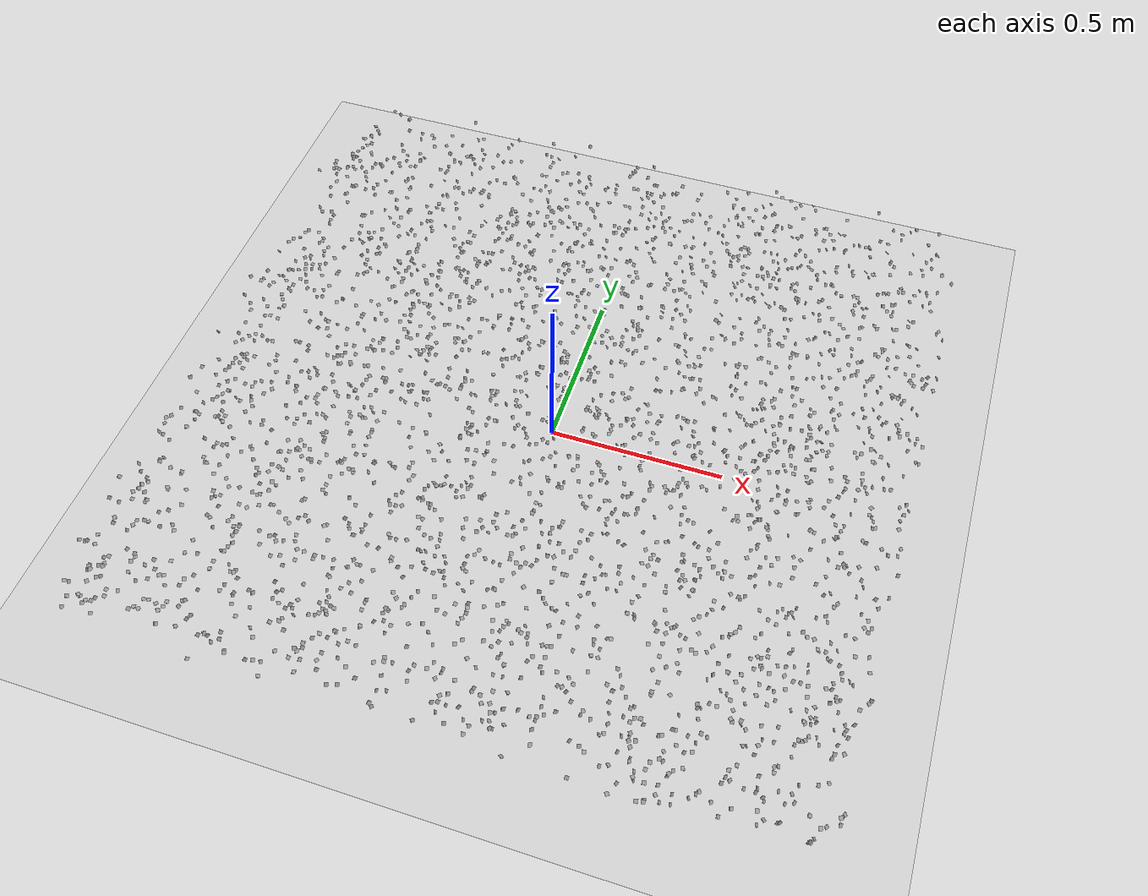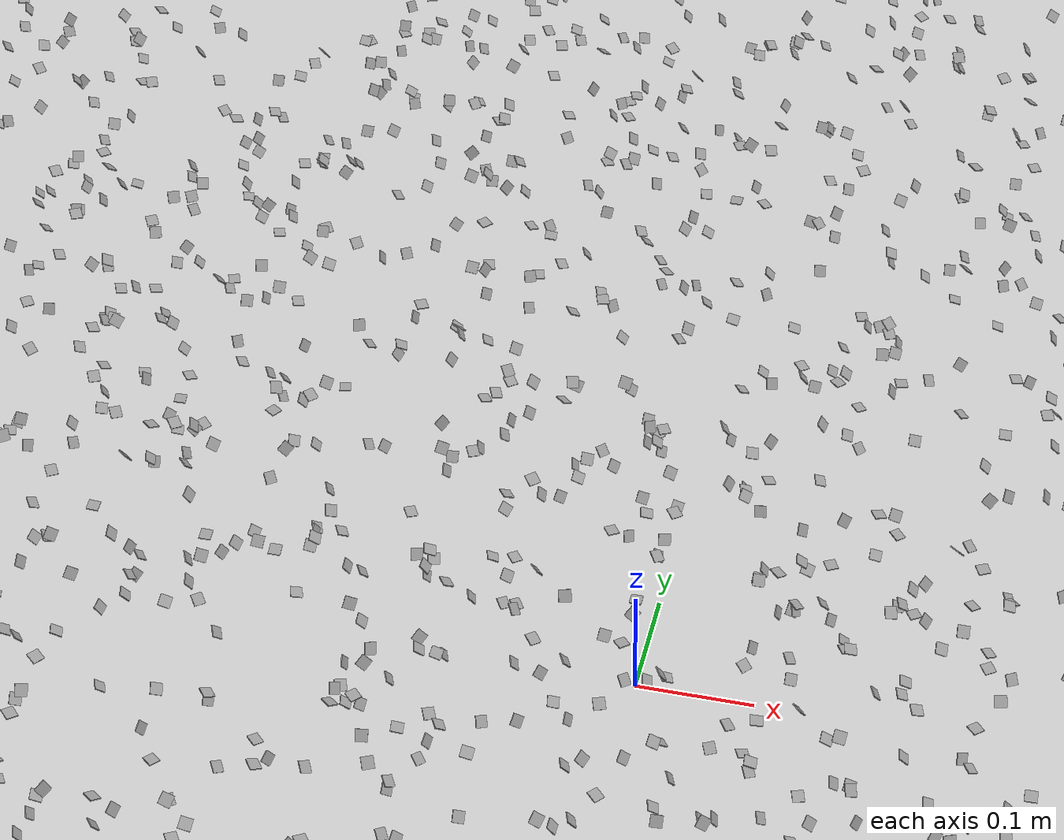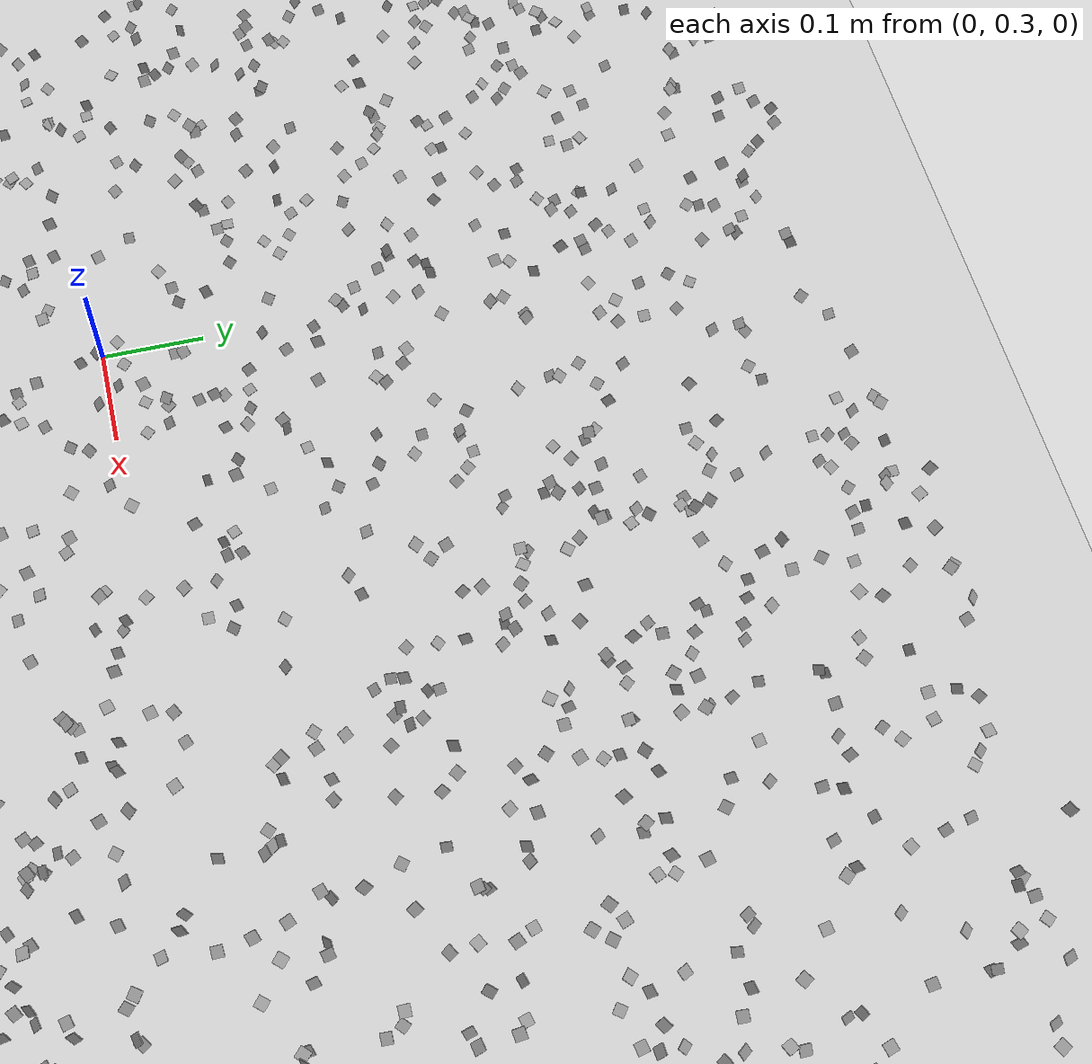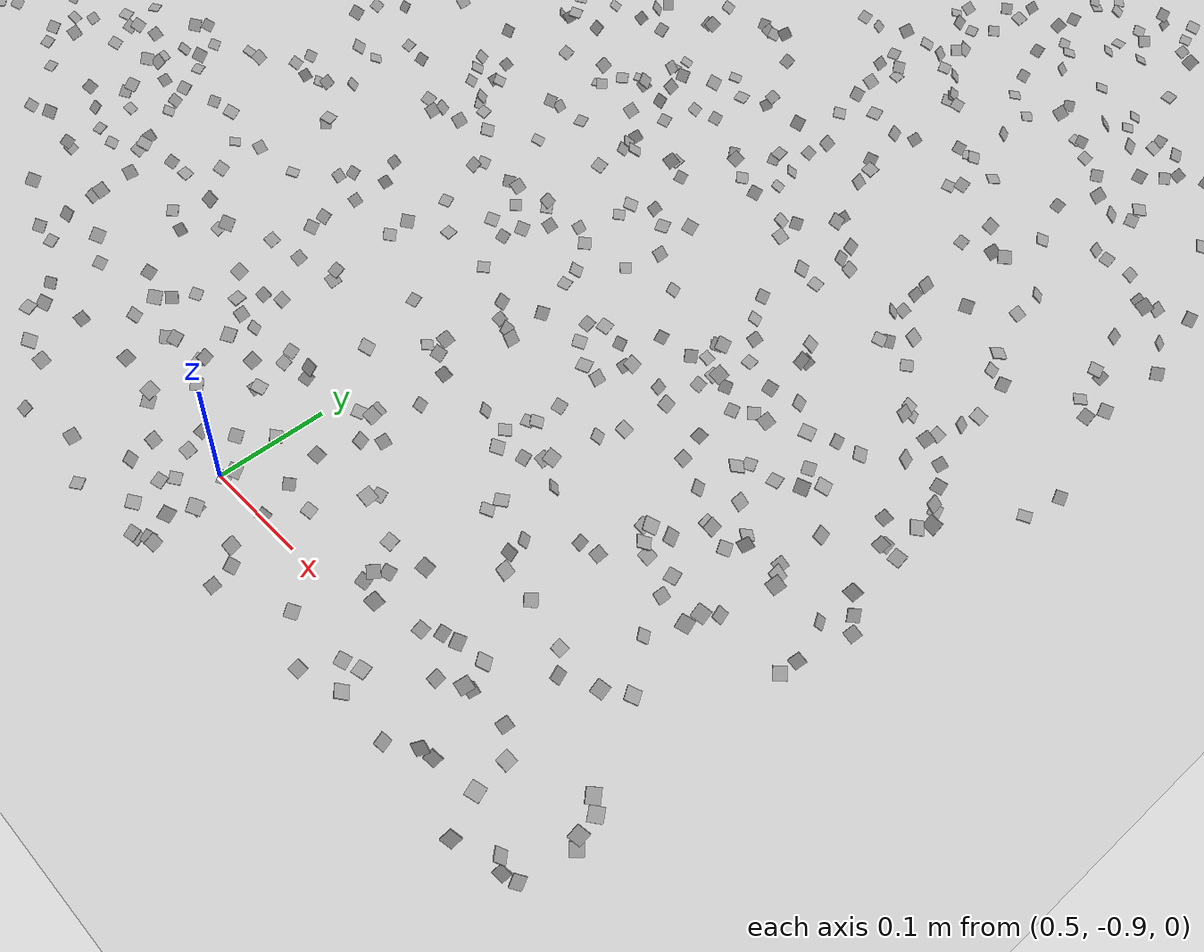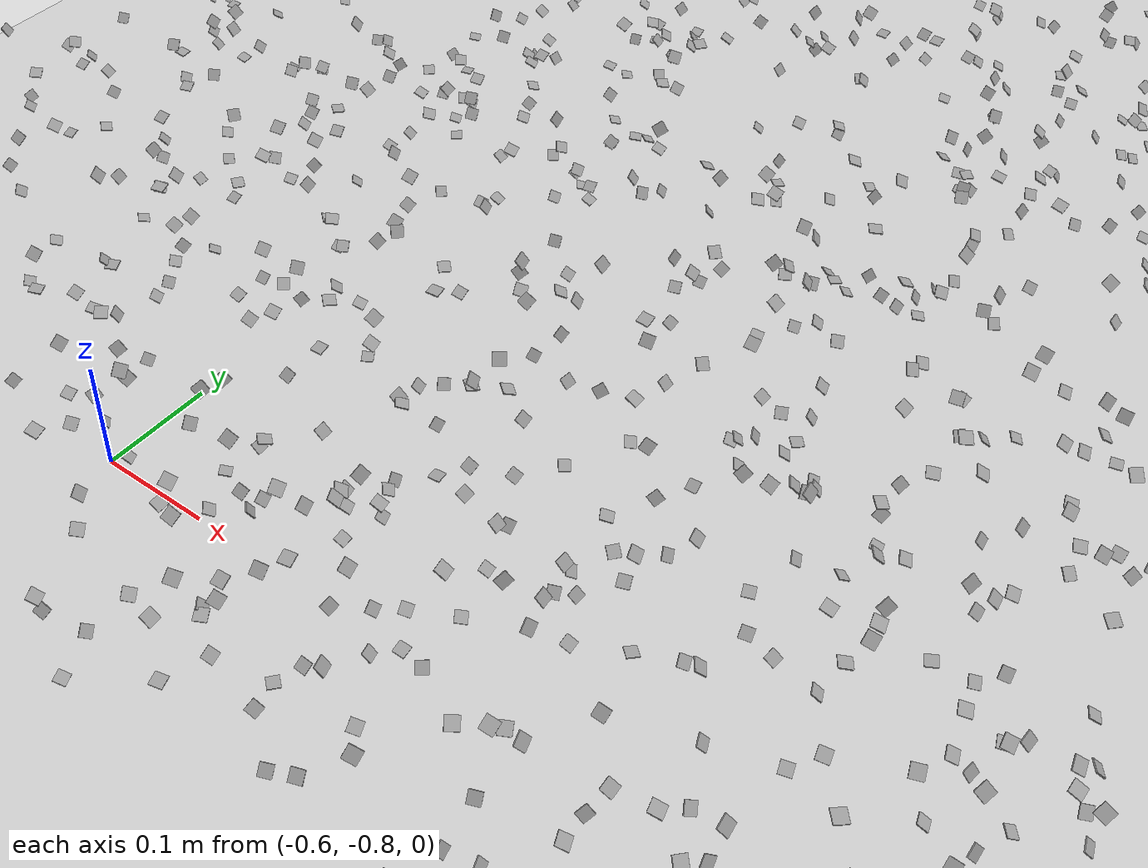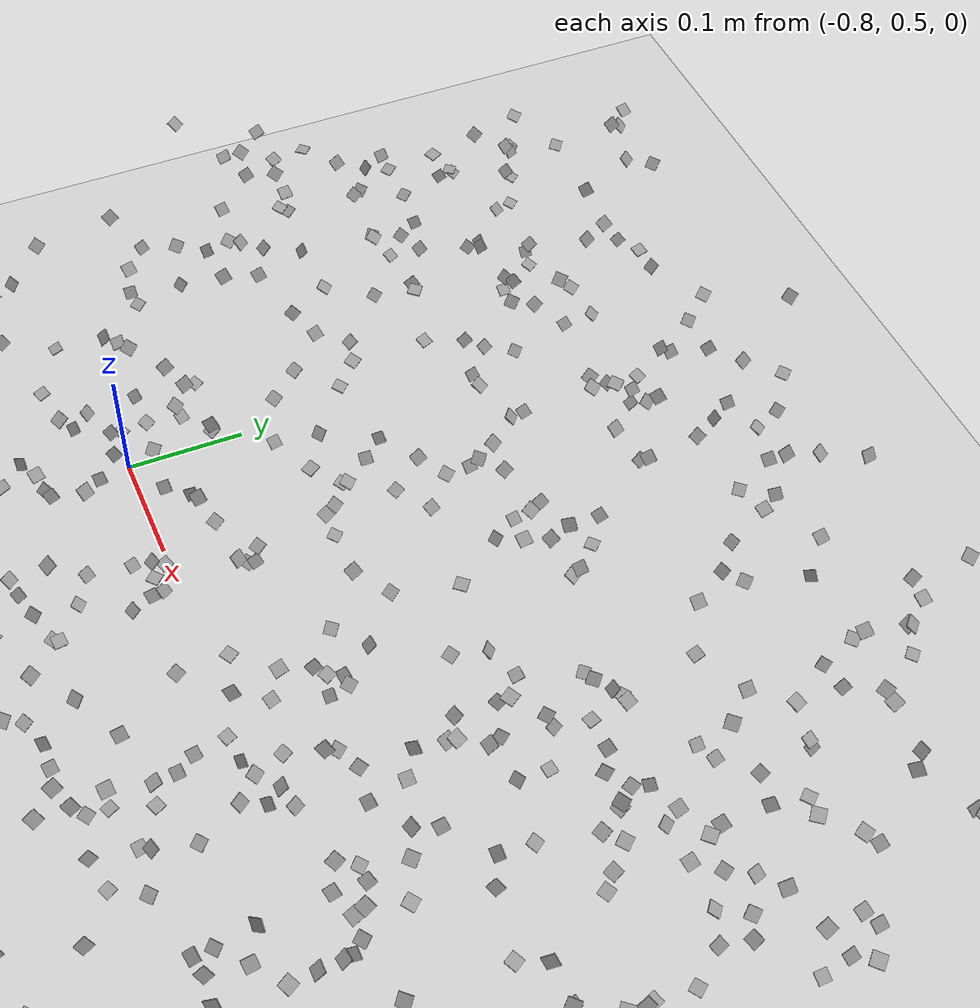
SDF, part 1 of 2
<sdf version="1.6">
 <world name="default">
  <physics name="default_physics" default="0" type="ode">
   <ode>
    <solver>
     <type>quick</type>
     <iters>50</iters>
     <sor>1.3</sor>
     <use_dynamic_moi_rescaling>0</use_dynamic_moi_rescaling>
    </solver>
    <constraints>
     <cfm>0</cfm>
     <erp>0.2</erp>
     <contact_max_correcting_vel>1</contact_max_correcting_vel>
     <contact_surface_layer>0.001</contact_surface_layer>
    </constraints>
   </ode>
   <max_step_size>0.01</max_step_size>
   <real_time_update_rate>0</real_time_update_rate>
   <real_time_factor>1</real_time_factor>
  </physics>
  <model name="ground_plane">
   <static>1</static>
   <link name="link">
    <collision name="collision">
     <geometry><plane><normal>0 0 1</normal><size>100 100</size></plane></geometry>
     <surface><friction><ode><mu>100</mu><mu2>50</mu2></ode></friction></surface>
    </collision>
    <visual name="visual">
     <cast_shadows>0</cast_shadows>
     <geometry><plane><normal>0 0 1</normal><size>100 100</size></plane></geometry>
     <material>
      <script><uri>file://media/materials/scripts/gazebo.material</uri><name>Gazebo/Grey</name></script>
     </material>
    </visual>
   </link>
  </model>
  <light name="sun" type="directional">
   <pose>0 0 10 0 -0 0</pose>
   <diffuse>0.8 0.8 0.8 1</diffuse>
   <specular>0.2 0.2 0.2 1</specular>
   <attenuation>
    <range>1000</range>
    <constant>0.9</constant>
    <linear>0.01</linear>
    <quadratic>0.001</quadratic>
   </attenuation>
   <direction>-0.5 0.1 -0.9</direction>
  </light>
  <gravity>0 0 -9.8</gravity>
  <magnetic_field>6e-06 2.3e-05 -4.2e-05</magnetic_field>
  <atmosphere type="adiabatic"/>
  <scene><ambient>0.4 0.4 0.4 1</ambient><background>0.7 0.7 0.7 1</background><shadows>1</shadows></scene>
  <spherical_coordinates>
   <surface_model>EARTH_WGS84</surface_model>
   <latitude_deg>0</latitude_deg>
   <longitude_deg>0</longitude_deg>
   <elevation>0</elevation>
   <heading_deg>0</heading_deg>
  </spherical_coordinates>
  <model name="SmokeParticle">
   <link name="link_0">
    <gravity>0</gravity>
    <collision name="collision">
     <pose>0 0 0.1 0 -0 0</pose>
     <geometry><box><size>0.01 0.01 0.001</size></box></geometry>
    </collision>
    <visual name="visual">
     <pose>0 0 0.1 0 -0 0</pose>
     <geometry><box><size>0.01 0.01 0.001</size></box></geometry>
     <material>
      <lighting>0</lighting>
      <script><uri>file://media/materials/scripts/gazebo.material</uri><name>Gazebo/Grey</name></script>
     </material>
     <cast_shadows>0</cast_shadows>
    </visual>
    <visual name="visual_0">
     <pose>-0.403876 0.201032 0.197572 0.108042 0.8212 0.885641</pose>
     <geometry><box><size>0.01 0.01 0.001</size></box></geometry>
     <material>
      <lighting>0</lighting>
      <script><uri>file://media/materials/scripts/gazebo.material</uri><name>Gazebo/Grey</name></script>
     </material>
     <cast_shadows>0</cast_shadows>
    </visual>
    <collision name="collision_0">
     <pose>-0.403876 0.201032 0.197572 0.108042 0.8212 0.885641</pose>
     <geometry><box><size>0.01 0.01 0.001</size></box></geometry>
     <max_contacts>0</max_contacts>
     <surface><contact><collide_without_contact>1</collide_without_contact></contact></surface>
    </collision>
    <visual name="visual_1">
     <pose>0.531237 0.502478 0.195328 0.79739 0.439027 0.002231</pose>
     <geometry><box><size>0.01 0.01 0.001</size></box></geometry>
     <material>
      <lighting>0</lighting>
      <script><uri>file://media/materials/scripts/gazebo.material</uri><name>Gazebo/Grey</name></script>
     </material>
     <cast_shadows>0</cast_shadows>
    </visual>
    <collision name="collision_1">
     <pose>0.531237 0.502478 0.195328 0.79739 0.439027 0.002231</pose>
     <geometry><box><size>0.01 0.01 0.001</size></box></geometry>
     <max_contacts>0</max_contacts>
     <surface><contact><collide_without_contact>1</collide_without_contact></contact></surface>
    </collision>
    <visual name="visual_2">
     <pose>-0.303189 0.503655 0.080205 0.573679 0.632041 0.326188</pose>
     <geometry><box><size>0.01 0.01 0.001</size></box></geometry>
     <material>
      <lighting>0</lighting>
      <script><uri>file://media/materials/scripts/gazebo.material</uri><name>Gazebo/Grey</name></script>
     </material>
     <cast_shadows>0</cast_shadows>
    </visual>
    <collision name="collision_2">
     <pose>-0.303189 0.503655 0.080205 0.573679 0.632041 0.326188</pose>
     <geometry><box><size>0.01 0.01 0.001</size></box></geometry>
     <max_contacts>0</max_contacts>
     <surface><contact><collide_without_contact>1</collide_without_contact></contact></surface>
    </collision>
    <visual name="visual_3">
     <pose>0.337808 0.869948 0.138234 0.186742 0.966265 0.682626</pose>
     <geometry><box><size>0.01 0.01 0.001</size></box></geometry>
     <material>
      <lighting>0</lighting>
      <script><uri>file://media/materials/scripts/gazebo.material</uri><name>Gazebo/Grey</name></script>
     </material>
     <cast_shadows>0</cast_shadows>
    </visual>
    <collision name="collision_3">
     <pose>0.337808 0.869948 0.138234 0.186742 0.966265 0.682626</pose>
     <geometry><box><size>0.01 0.01 0.001</size></box></geometry>
     <max_contacts>0</max_contacts>
     <surface><contact><collide_without_contact>1</collide_without_contact></contact></surface>
    </collision>
    <visual name="visual_4">
     <pose>-0.144451 0.606344 0.125176 0.946475 0.182837 0.846206</pose>
     <geometry><box><size>0.01 0.01 0.001</size></box></geometry>
     <material>
      <lighting>0</lighting>
      <script><uri>file://media/materials/scripts/gazebo.material</uri><name>Gazebo/Grey</name></script>
     </material>
     <cast_shadows>0</cast_shadows>
    </visual>
    <collision name="collision_4">
     <pose>-0.144451 0.606344 0.125176 0.946475 0.182837 0.846206</pose>
     <geometry><box><size>0.01 0.01 0.001</size></box></geometry>
     <max_contacts>0</max_contacts>
     <surface><contact><collide_without_contact>1</collide_without_contact></contact></surface>
    </collision>
    <visual name="visual_5">
     <pose>-0.651433 0.166245 0.031336 0.015782 0.955401 0.346402</pose>
     <geometry><box><size>0.01 0.01 0.001</size></box></geometry>
     <material>
      <lighting>0</lighting>
      <script><uri>file://media/materials/scripts/gazebo.material</uri><name>Gazebo/Grey</name></script>
     </material>
     <cast_shadows>0</cast_shadows>
    </visual>
    <collision name="collision_5">
     <pose>-0.651433 0.166245 0.031336 0.015782 0.955401 0.346402</pose>
     <geometry><box><size>0.01 0.01 0.001</size></box></geometry>
     <max_contacts>0</max_contacts>
     <surface><contact><collide_without_contact>1</collide_without_contact></contact></surface>
    </collision>
    <visual name="visual_6">
     <pose>0.578069 -0.810061 0.074659 0.291 0.38364 0.604591</pose>
     <geometry><box><size>0.01 0.01 0.001</size></box></geometry>
     <material>
      <lighting>0</lighting>
      <script><uri>file://media/materials/scripts/gazebo.material</uri><name>Gazebo/Grey</name></script>
     </material>
     <cast_shadows>0</cast_shadows>
    </visual>
    <collision name="collision_6">
     <pose>0.578069 -0.810061 0.074659 0.291 0.38364 0.604591</pose>
     <geometry><box><size>0.01 0.01 0.001</size></box></geometry>
     <max_contacts>0</max_contacts>
     <surface><contact><collide_without_contact>1</collide_without_contact></contact></surface>
    </collision>
    <visual name="visual_7">
     <pose>-0.631514 0.058186 0.084975 0.706505 0.495918 0.287768</pose>
     <geometry><box><size>0.01 0.01 0.001</size></box></geometry>
     <material>
      <lighting>0</lighting>
      <script><uri>file://media/materials/scripts/gazebo.material</uri><name>Gazebo/Grey</name></script>
     </material>
     <cast_shadows>0</cast_shadows>
    </visual>
    <collision name="collision_7">
     <pose>-0.631514 0.058186 0.084975 0.706505 0.495918 0.287768</pose>
     <geometry><box><size>0.01 0.01 0.001</size></box></geometry>
     <max_contacts>0</max_contacts>
     <surface><contact><collide_without_contact>1</collide_without_contact></contact></surface>
    </collision>
    <visual name="visual_8">
     <pose>0.011175 0.489025 0.127091 0.229774 0.283695 0.915888</pose>
     <geometry><box><size>0.01 0.01 0.001</size></box></geometry>
     <material>
      <lighting>0</lighting>
      <script><uri>file://media/materials/scripts/gazebo.material</uri><name>Gazebo/Grey</name></script>
     </material>
     <cast_shadows>0</cast_shadows>
    </visual>
    <collision name="collision_8">
     <pose>0.011175 0.489025 0.127091 0.229774 0.283695 0.915888</pose>
     <geometry><box><size>0.01 0.01 0.001</size></box></geometry>
     <max_contacts>0</max_contacts>
     <surface><contact><collide_without_contact>1</collide_without_contact></contact></surface>
    </collision>
    <visual name="visual_9">
     <pose>0.397156 0.636628 0.067618 0.429425 0.81732 0.774265</pose>
     <geometry><box><size>0.01 0.01 0.001</size></box></geometry>
     <material>
      <lighting>0</lighting>
      <script><uri>file://media/materials/scripts/gazebo.material</uri><name>Gazebo/Grey</name></script>
     </material>
     <cast_shadows>0</cast_shadows>
    </visual>
    <collision name="collision_9">
     <pose>0.397156 0.636628 0.067618 0.429425 0.81732 0.774265</pose>
     <geometry><box><size>0.01 0.01 0.001</size></box></geometry>
     <max_contacts>0</max_contacts>
     <surface><contact><collide_without_contact>1</collide_without_contact></contact></surface>
    </collision>
    <visual name="visual_10">
     <pose>0.098187 -0.391062 0.142206 0.807868 0.976832 0.899319</pose>
     <geometry><box><size>0.01 0.01 0.001</size></box></geometry>
     <material>
      <lighting>0</lighting>
      <script><uri>file://media/materials/scripts/gazebo.material</uri><name>Gazebo/Grey</name></script>
     </material>
     <cast_shadows>0</cast_shadows>
    </visual>
    <collision name="collision_10">
     <pose>0.098187 -0.391062 0.142206 0.807868 0.976832 0.899319</pose>
     <geometry><box><size>0.01 0.01 0.001</size></box></geometry>
     <max_contacts>0</max_contacts>
     <surface><contact><collide_without_contact>1</collide_without_contact></contact></surface>
    </collision>
    <visual name="visual_11">
     <pose>0.300777 -0.315212 0.16725 0.920543 0.686985 0.413204</pose>
     <geometry><box><size>0.01 0.01 0.001</size></box></geometry>
     <material>
      <lighting>0</lighting>
      <script><uri>file://media/materials/scripts/gazebo.material</uri><name>Gazebo/Grey</name></script>
     </material>
     <cast_shadows>0</cast_shadows>
    </visual>
    <collision name="collision_11">
     <pose>0.300777 -0.315212 0.16725 0.920543 0.686985 0.413204</pose>
     <geometry><box><size>0.01 0.01 0.001</size></box></geometry>
     <max_contacts>0</max_contacts>
     <surface><contact><collide_without_contact>1</collide_without_contact></contact></surface>
    </collision>
    <visual name="visual_12">
     <pose>0.308576 0.263658 0.181204 0.042668 0.770459 0.391931</pose>
     <geometry><box><size>0.01 0.01 0.001</size></box></geometry>
     <material>
      <lighting>0</lighting>
      <script><uri>file://media/materials/scripts/gazebo.material</uri><name>Gazebo/Grey</name></script>
     </material>
     <cast_shadows>0</cast_shadows>
    </visual>
    <collision name="collision_12">
     <pose>0.308576 0.263658 0.181204 0.042668 0.770459 0.391931</pose>
     <geometry><box><size>0.01 0.01 0.001</size></box></geometry>
     <max_contacts>0</max_contacts>
     <surface><contact><collide_without_contact>1</collide_without_contact></contact></surface>
    </collision>
    <visual name="visual_13">
     <pose>-0.410405 -0.042917 0.080005 0.975091 0.817799 0.311912</pose>
     <geometry><box><size>0.01 0.01 0.001</size></box></geometry>
     <material>
      <lighting>0</lighting>
      <script><uri>file://media/materials/scripts/gazebo.material</uri><name>Gazebo/Grey</name></script>
     </material>
     <cast_shadows>0</cast_shadows>
    </visual>
    <collision name="collision_13">
     <pose>-0.410405 -0.042917 0.080005 0.975091 0.817799 0.311912</pose>
     <geometry><box><size>0.01 0.01 0.001</size></box></geometry>
     <max_contacts>0</max_contacts>
     <surface><contact><collide_without_contact>1</collide_without_contact></contact></surface>
    </collision>
    <visual name="visual_14">
     <pose>-0.576932 0.548454 0.119447 0.460421 0.051859 0.466505</pose>
     <geometry><box><size>0.01 0.01 0.001</size></box></geometry>
     <material>
      <lighting>0</lighting>
      <script><uri>file://media/materials/scripts/gazebo.material</uri><name>Gazebo/Grey</name></script>
     </material>
     <cast_shadows>0</cast_shadows>
    </visual>
    <collision name="collision_14">
     <pose>-0.576932 0.548454 0.119447 0.460421 0.051859 0.466505</pose>
     <geometry><box><size>0.01 0.01 0.001</size></box></geometry>
     <max_contacts>0</max_contacts>
     <surface><contact><collide_without_contact>1</collide_without_contact></contact></surface>
    </collision>
    <visual name="visual_15">
     <pose>0.846734 0.737506 0.042639 0.993072 0.529106 0.936117</pose>
     <geometry><box><size>0.01 0.01 0.001</size></box></geometry>
     <material>
      <lighting>0</lighting>
      <script><uri>file://media/materials/scripts/gazebo.material</uri><name>Gazebo/Grey</name></script>
     </material>
     <cast_shadows>0</cast_shadows>
    </visual>
    <collision name="collision_15">
     <pose>0.846734 0.737506 0.042639 0.993072 0.529106 0.936117</pose>
     <geometry><box><size>0.01 0.01 0.001</size></box></geometry>
     <max_contacts>0</max_contacts>
     <surface><contact><collide_without_contact>1</collide_without_contact></contact></surface>
    </collision>
    <visual name="visual_16">
     <pose>0.834869 0.705066 0.108464 0.014904 0.894066 0.642223</pose>
     <geometry><box><size>0.01 0.01 0.001</size></box></geometry>
     <material>
      <lighting>0</lighting>
      <script><uri>file://media/materials/scripts/gazebo.material</uri><name>Gazebo/Grey</name></script>
     </material>
     <cast_shadows>0</cast_shadows>
    </visual>
    <collision name="collision_16">
     <pose>0.834869 0.705066 0.108464 0.014904 0.894066 0.642223</pose>
     <geometry><box><size>0.01 0.01 0.001</size></box></geometry>
     <max_contacts>0</max_contacts>
     <surface><contact><collide_without_contact>1</collide_without_contact></contact></surface>
    </collision>
    <visual name="visual_17">
     <pose>0.730316 0.978142 0.054407 0.828794 0.749482 0.678423</pose>
     <geometry><box><size>0.01 0.01 0.001</size></box></geometry>
     <material>
      <lighting>0</lighting>
      <script><uri>file://media/materials/scripts/gazebo.material</uri><name>Gazebo/Grey</name></script>
     </material>
     <cast_shadows>0</cast_shadows>
    </visual>
    <collision name="collision_17">
     <pose>0.730316 0.978142 0.054407 0.828794 0.749482 0.678423</pose>
     <geometry><box><size>0.01 0.01 0.001</size></box></geometry>
     <max_contacts>0</max_contacts>
     <surface><contact><collide_without_contact>1</collide_without_contact></contact></surface>
    </collision>
    <visual name="visual_18">
     <pose>-0.761732 -0.24575 0.165909 0.634281 0.133131 0.096937</pose>
     <geometry><box><size>0.01 0.01 0.001</size></box></geometry>
     <material>
      <lighting>0</lighting>
      <script><uri>file://media/materials/scripts/gazebo.material</uri><name>Gazebo/Grey</name></script>
     </material>
     <cast_shadows>0</cast_shadows>
    </visual>
    <collision name="collision_18">
     <pose>-0.761732 -0.24575 0.165909 0.634281 0.133131 0.096937</pose>
     <geometry><box><size>0.01 0.01 0.001</size></box></geometry>
     <max_contacts>0</max_contacts>
     <surface><contact><collide_without_contact>1</collide_without_contact></contact></surface>
    </collision>
    <visual name="visual_19">
     <pose>-0.045617 -0.583888 0.136301 0.327235 0.270863 0.925251</pose>
     <geometry><box><size>0.01 0.01 0.001</size></box></geometry>
     <material>
      <lighting>0</lighting>
      <script><uri>file://media/materials/scripts/gazebo.material</uri><name>Gazebo/Grey</name></script>
     </material>
     <cast_shadows>0</cast_shadows>
    </visual>
    <collision name="collision_19">
     <pose>-0.045617 -0.583888 0.136301 0.327235 0.270863 0.925251</pose>
     <geometry><box><size>0.01 0.01 0.001</size></box></geometry>
     <max_contacts>0</max_contacts>
     <surface><contact><collide_without_contact>1</collide_without_contact></contact></surface>
    </collision>
    <visual name="visual_20">
     <pose>-0.817893 0.735162 0.163043 0.319449 0.519729 0.935921</pose>
     <geometry><box><size>0.01 0.01 0.001</size></box></geometry>
     <material>
      <lighting>0</lighting>
      <script><uri>file://media/materials/scripts/gazebo.material</uri><name>Gazebo/Grey</name></script>
     </material>
     <cast_shadows>0</cast_shadows>
    </visual>
    <collision name="collision_20">
     <pose>-0.817893 0.735162 0.163043 0.319449 0.519729 0.935921</pose>
     <geometry><box><size>0.01 0.01 0.001</size></box></geometry>
     <max_contacts>0</max_contacts>
     <surface><contact><collide_without_contact>1</collide_without_contact></contact></surface>
    </collision>
    <visual name="visual_21">
     <pose>-0.642688 -0.647226 0.133771 0.660815 0.64387 0.264233</pose>
     <geometry><box><size>0.01 0.01 0.001</size></box></geometry>
     <material>
      <lighting>0</lighting>
      <script><uri>file://media/materials/scripts/gazebo.material</uri><name>Gazebo/Grey</name></script>
     </material>
     <cast_shadows>0</cast_shadows>
    </visual>
    <collision name="collision_21">
     <pose>-0.642688 -0.647226 0.133771 0.660815 0.64387 0.264233</pose>
     <geometry><box><size>0.01 0.01 0.001</size></box></geometry>
     <max_contacts>0</max_contacts>
     <surface><contact><collide_without_contact>1</collide_without_contact></contact></surface>
    </collision>
    <visual name="visual_22">
     <pose>0.522241 -0.438063 0.150044 0.976436 0.095806 0.005561</pose>
     <geometry><box><size>0.01 0.01 0.001</size></box></geometry>
     <material>
      <lighting>0</lighting>
      <script><uri>file://media/materials/scripts/gazebo.material</uri><name>Gazebo/Grey</name></script>
     </material>
     <cast_shadows>0</cast_shadows>
    </visual>
    <collision name="collision_22">
     <pose>0.522241 -0.438063 0.150044 0.976436 0.095806 0.005561</pose>
     <geometry><box><size>0.01 0.01 0.001</size></box></geometry>
     <max_contacts>0</max_contacts>
     <surface><contact><collide_without_contact>1</collide_without_contact></contact></surface>
    </collision>
    <visual name="visual_23">
     <pose>0.066282 0.607954 0.188887 0.163224 0.728709 0.568907</pose>
     <geometry><box><size>0.01 0.01 0.001</size></box></geometry>
     <material>
      <lighting>0</lighting>
      <script><uri>file://media/materials/scripts/gazebo.material</uri><name>Gazebo/Grey</name></script>
     </material>
     <cast_shadows>0</cast_shadows>
    </visual>
    <collision name="collision_23">
     <pose>0.066282 0.607954 0.188887 0.163224 0.728709 0.568907</pose>
     <geometry><box><size>0.01 0.01 0.001</size></box></geometry>
     <max_contacts>0</max_contacts>
     <surface><contact><collide_without_contact>1</collide_without_contact></contact></surface>
    </collision>
    <visual name="visual_24">
     <pose>-0.029329 0.435786 0.129815 0.247702 0.56695 0.08611</pose>
     <geometry><box><size>0.01 0.01 0.001</size></box></geometry>
     <material>
      <lighting>0</lighting>
      <script><uri>file://media/materials/scripts/gazebo.material</uri><name>Gazebo/Grey</name></script>
     </material>
     <cast_shadows>0</cast_shadows>
    </visual>
    <collision name="collision_24">
     <pose>-0.029329 0.435786 0.129815 0.247702 0.56695 0.08611</pose>
     <geometry><box><size>0.01 0.01 0.001</size></box></geometry>
     <max_contacts>0</max_contacts>
     <surface><contact><collide_without_contact>1</collide_without_contact></contact></surface>
    </collision>
    <visual name="visual_25">
     <pose>0.293385 0.31951 0.188 0.246872 0.422986 0.985333</pose>
     <geometry><box><size>0.01 0.01 0.001</size></box></geometry>
     <material>
      <lighting>0</lighting>
      <script><uri>file://media/materials/scripts/gazebo.material</uri><name>Gazebo/Grey</name></script>
     </material>
     <cast_shadows>0</cast_shadows>
    </visual>
    <collision name="collision_25">
     <pose>0.293385 0.31951 0.188 0.246872 0.422986 0.985333</pose>
     <geometry><box><size>0.01 0.01 0.001</size></box></geometry>
     <max_contacts>0</max_contacts>
     <surface><contact><collide_without_contact>1</collide_without_contact></contact></surface>
    </collision>
    <visual name="visual_26">
     <pose>-0.38581 -0.642819 0.185491 0.024769 0.06541 0.172901</pose>
     <geometry><box><size>0.01 0.01 0.001</size></box></geometry>
     <material>
      <lighting>0</lighting>
      <script><uri>file://media/materials/scripts/gazebo.material</uri><name>Gazebo/Grey</name></script>
     </material>
     <cast_shadows>0</cast_shadows>
    </visual>
    <collision name="collision_26">
     <pose>-0.38581 -0.642819 0.185491 0.024769 0.06541 0.172901</pose>
     <geometry><box><size>0.01 0.01 0.001</size></box></geometry>
     <max_contacts>0</max_contacts>
     <surface><contact><collide_without_contact>1</collide_without_contact></contact></surface>
    </collision>
    <visual name="visual_27">
     <pose>0.823388 -0.492416 0.122063 0.246614 0.302792 0.458589</pose>
     <geometry><box><size>0.01 0.01 0.001</size></box></geometry>
     <material>
      <lighting>0</lighting>
      <script><uri>file://media/materials/scripts/gazebo.material</uri><name>Gazebo/Grey</name></script>
     </material>
     <cast_shadows>0</cast_shadows>
    </visual>
    <collision name="collision_27">
     <pose>0.823388 -0.492416 0.122063 0.246614 0.302792 0.458589</pose>
     <geometry><box><size>0.01 0.01 0.001</size></box></geometry>
     <max_contacts>0</max_contacts>
     <surface><contact><collide_without_contact>1</collide_without_contact></contact></surface>
    </collision>
    <visual name="visual_28">
     <pose>0.120698 0.953629 0.157042 0.491025 0.241652 0.053772</pose>
     <geometry><box><size>0.01 0.01 0.001</size></box></geometry>
     <material>
      <lighting>0</lighting>
      <script><uri>file://media/materials/scripts/gazebo.material</uri><name>Gazebo/Grey</name></script>
     </material>
     <cast_shadows>0</cast_shadows>
    </visual>
    <collision name="collision_28">
     <pose>0.120698 0.953629 0.157042 0.491025 0.241652 0.053772</pose>
     <geometry><box><size>0.01 0.01 0.001</size></box></geometry>
     <max_contacts>0</max_contacts>
     <surface><contact><collide_without_contact>1</collide_without_contact></contact></surface>
    </collision>
    <visual name="visual_29">
     <pose>0.255818 0.165075 0.150886 0.285625 0.793932 0.137201</pose>
     <geometry><box><size>0.01 0.01 0.001</size></box></geometry>
     <material>
      <lighting>0</lighting>
      <script><uri>file://media/materials/scripts/gazebo.material</uri><name>Gazebo/Grey</name></script>
     </material>
     <cast_shadows>0</cast_shadows>
    </visual>
    <collision name="collision_29">
     <pose>0.255818 0.165075 0.150886 0.285625 0.793932 0.137201</pose>
     <geometry><box><size>0.01 0.01 0.001</size></box></geometry>
     <max_contacts>0</max_contacts>
     <surface><contact><collide_without_contact>1</collide_without_contact></contact></surface>
    </collision>
    <visual name="visual_30">
     <pose>-0.700225 -0.807038 0.036835 0.863717 0.922142 0.640801</pose>
     <geometry><box><size>0.01 0.01 0.001</size></box></geometry>
     <material>
      <lighting>0</lighting>
      <script><uri>file://media/materials/scripts/gazebo.material</uri><name>Gazebo/Grey</name></script>
     </material>
     <cast_shadows>0</cast_shadows>
    </visual>
    <collision name="collision_30">
     <pose>-0.700225 -0.807038 0.036835 0.863717 0.922142 0.640801</pose>
     <geometry><box><size>0.01 0.01 0.001</size></box></geometry>
     <max_contacts>0</max_contacts>
     <surface><contact><collide_without_contact>1</collide_without_contact></contact></surface>
    </collision>
    <visual name="visual_31">
     <pose>-0.21398 0.363952 0.164386 0.134308 0.039396 0.872704</pose>
     <geometry><box><size>0.01 0.01 0.001</size></box></geometry>
     <material>
      <lighting>0</lighting>
      <script><uri>file://media/materials/scripts/gazebo.material</uri><name>Gazebo/Grey</name></script>
     </material>
     <cast_shadows>0</cast_shadows>
    </visual>
    <collision name="collision_31">
     <pose>-0.21398 0.363952 0.164386 0.134308 0.039396 0.872704</pose>
     <geometry><box><size>0.01 0.01 0.001</size></box></geometry>
     <max_contacts>0</max_contacts>
     <surface><contact><collide_without_contact>1</collide_without_contact></contact></surface>
    </collision>
    <visual name="visual_32">
     <pose>0.364509 -0.989499 0.036981 0.632605 0.277005 0.021787</pose>
     <geometry><box><size>0.01 0.01 0.001</size></box></geometry>
     <material>
      <lighting>0</lighting>
      <script><uri>file://media/materials/scripts/gazebo.material</uri><name>Gazebo/Grey</name></script>
     </material>
     <cast_shadows>0</cast_shadows>
    </visual>
    <collision name="collision_32">
     <pose>0.364509 -0.989499 0.036981 0.632605 0.277005 0.021787</pose>
     <geometry><box><size>0.01 0.01 0.001</size></box></geometry>
     <max_contacts>0</max_contacts>
     <surface><contact><collide_without_contact>1</collide_without_contact></contact></surface>
    </collision>
    <visual name="visual_33">
     <pose>-0.392403 0.763778 0.050656 0.13797 0.062353 0.616356</pose>
     <geometry><box><size>0.01 0.01 0.001</size></box></geometry>
     <material>
      <lighting>0</lighting>
      <script><uri>file://media/materials/scripts/gazebo.material</uri><name>Gazebo/Grey</name></script>
     </material>
     <cast_shadows>0</cast_shadows>
    </visual>
    <collision name="collision_33">
     <pose>-0.392403 0.763778 0.050656 0.13797 0.062353 0.616356</pose>
     <geometry><box><size>0.01 0.01 0.001</size></box></geometry>
     <max_contacts>0</max_contacts>
     <surface><contact><collide_without_contact>1</collide_without_contact></contact></surface>
    </collision>
    <visual name="visual_34">
     <pose>-0.120125 0.79414 0.093941 0.441026 0.850128 0.484601</pose>
     <geometry><box><size>0.01 0.01 0.001</size></box></geometry>
     <material>
      <lighting>0</lighting>
      <script><uri>file://media/materials/scripts/gazebo.material</uri><name>Gazebo/Grey</name></script>
     </material>
     <cast_shadows>0</cast_shadows>
    </visual>
    <collision name="collision_34">
     <pose>-0.120125 0.79414 0.093941 0.441026 0.850128 0.484601</pose>
     <geometry><box><size>0.01 0.01 0.001</size></box></geometry>
     <max_contacts>0</max_contacts>
     <surface><contact><collide_without_contact>1</collide_without_contact></contact></surface>
    </collision>
    <visual name="visual_35">
     <pose>0.502444 -0.766406 0.144179 0.529834 0.118632 0.057238</pose>
     <geometry><box><size>0.01 0.01 0.001</size></box></geometry>
     <material>
      <lighting>0</lighting>
      <script><uri>file://media/materials/scripts/gazebo.material</uri><name>Gazebo/Grey</name></script>
     </material>
     <cast_shadows>0</cast_shadows>
    </visual>
    <collision name="collision_35">
     <pose>0.502444 -0.766406 0.144179 0.529834 0.118632 0.057238</pose>
     <geometry><box><size>0.01 0.01 0.001</size></box></geometry>
     <max_contacts>0</max_contacts>
     <surface><contact><collide_without_contact>1</collide_without_contact></contact></surface>
    </collision>
    <visual name="visual_36">
     <pose>0.4053 -0.782898 0.059086 0.740959 0.54699 0.152739</pose>
     <geometry><box><size>0.01 0.01 0.001</size></box></geometry>
     <material>
      <lighting>0</lighting>
      <script><uri>file://media/materials/scripts/gazebo.material</uri><name>Gazebo/Grey</name></script>
     </material>
     <cast_shadows>0</cast_shadows>
    </visual>
    <collision name="collision_36">
     <pose>0.4053 -0.782898 0.059086 0.740959 0.54699 0.152739</pose>
     <geometry><box><size>0.01 0.01 0.001</size></box></geometry>
     <max_contacts>0</max_contacts>
     <surface><contact><collide_without_contact>1</collide_without_contact></contact></surface>
    </collision>
    <visual name="visual_37">
     <pose>-0.436132 0.893267 0.155174 0.249006 0.26953 0.143698</pose>
     <geometry><box><size>0.01 0.01 0.001</size></box></geometry>
     <material>
      <lighting>0</lighting>
      <script><uri>file://media/materials/scripts/gazebo.material</uri><name>Gazebo/Grey</name></script>
     </material>
     <cast_shadows>0</cast_shadows>
    </visual>
    <collision name="collision_37">
     <pose>-0.436132 0.893267 0.155174 0.249006 0.26953 0.143698</pose>
     <geometry><box><size>0.01 0.01 0.001</size></box></geometry>
     <max_contacts>0</max_contacts>
     <surface><contact><collide_without_contact>1</collide_without_contact></contact></surface>
    </collision>
    <visual name="visual_38">
     <pose>-0.013197 -0.832223 0.044037 0.977919 0.595238 0.863061</pose>
     <geometry><box><size>0.01 0.01 0.001</size></box></geometry>
     <material>
      <lighting>0</lighting>
      <script><uri>file://media/materials/scripts/gazebo.material</uri><name>Gazebo/Grey</name></script>
     </material>
     <cast_shadows>0</cast_shadows>
    </visual>
    <collision name="collision_38">
     <pose>-0.013197 -0.832223 0.044037 0.977919 0.595238 0.863061</pose>
     <geometry><box><size>0.01 0.01 0.001</size></box></geometry>
     <max_contacts>0</max_contacts>
     <surface><contact><collide_without_contact>1</collide_without_contact></contact></surface>
    </collision>
    <visual name="visual_39">
     <pose>0.016963 -0.755619 0.096757 0.467758 0.197396 0.329848</pose>
     <geometry><box><size>0.01 0.01 0.001</size></box></geometry>
     <material>
      <lighting>0</lighting>
      <script><uri>file://media/materials/scripts/gazebo.material</uri><name>Gazebo/Grey</name></script>
     </material>
     <cast_shadows>0</cast_shadows>
    </visual>
    <collision name="collision_39">
     <pose>0.016963 -0.755619 0.096757 0.467758 0.197396 0.329848</pose>
     <geometry><box><size>0.01 0.01 0.001</size></box></geometry>
     <max_contacts>0</max_contacts>
     <surface><contact><collide_without_contact>1</collide_without_contact></contact></surface>
    </collision>
    <visual name="visual_40">
     <pose>0.769605 0.625534 0.063947 0.317545 0.231069 0.992384</pose>
     <geometry><box><size>0.01 0.01 0.001</size></box></geometry>
     <material>
      <lighting>0</lighting>
      <script><uri>file://media/materials/scripts/gazebo.material</uri><name>Gazebo/Grey</name></script>
     </material>
     <cast_shadows>0</cast_shadows>
    </visual>
    <collision name="collision_40">
     <pose>0.769605 0.625534 0.063947 0.317545 0.231069 0.992384</pose>
     <geometry><box><size>0.01 0.01 0.001</size></box></geometry>
     <max_contacts>0</max_contacts>
     <surface><contact><collide_without_contact>1</collide_without_contact></contact></surface>
    </collision>
    <visual name="visual_41">
     <pose>-0.022262 -0.39731 0.064352 0.175624 0.464431 0.709718</pose>
     <geometry><box><size>0.01 0.01 0.001</size></box></geometry>
     <material>
      <lighting>0</lighting>
      <script><uri>file://media/materials/scripts/gazebo.material</uri><name>Gazebo/Grey</name></script>
     </material>
     <cast_shadows>0</cast_shadows>
    </visual>
    <collision name="collision_41">
     <pose>-0.022262 -0.39731 0.064352 0.175624 0.464431 0.709718</pose>
     <geometry><box><size>0.01 0.01 0.001</size></box></geometry>
     <max_contacts>0</max_contacts>
     <surface><contact><collide_without_contact>1</collide_without_contact></contact></surface>
    </collision>
    <visual name="visual_42">
     <pose>0.969995 0.242089 0.068037 0.025647 0.922314 0.229122</pose>
     <geometry><box><size>0.01 0.01 0.001</size></box></geometry>
     <material>
      <lighting>0</lighting>
      <script><uri>file://media/materials/scripts/gazebo.material</uri><name>Gazebo/Grey</name></script>
     </material>
     <cast_shadows>0</cast_shadows>
    </visual>
    <collision name="collision_42">
     <pose>0.969995 0.242089 0.068037 0.025647 0.922314 0.229122</pose>
     <geometry><box><size>0.01 0.01 0.001</size></box></geometry>
     <max_contacts>0</max_contacts>
     <surface><contact><collide_without_contact>1</collide_without_contact></contact></surface>
    </collision>
    <visual name="visual_43">
     <pose>0.942083 -0.530075 0.159994 0.160305 0.380054 0.144082</pose>
     <geometry><box><size>0.01 0.01 0.001</size></box></geometry>
     <material>
      <lighting>0</lighting>
      <script><uri>file://media/materials/scripts/gazebo.material</uri><name>Gazebo/Grey</name></script>
     </material>
     <cast_shadows>0</cast_shadows>
    </visual>
    <collision name="collision_43">
     <pose>0.942083 -0.530075 0.159994 0.160305 0.380054 0.144082</pose>
     <geometry><box><size>0.01 0.01 0.001</size></box></geometry>
     <max_contacts>0</max_contacts>
     <surface><contact><collide_without_contact>1</collide_without_contact></contact></surface>
    </collision>
    <visual name="visual_44">
     <pose>-0.607064 -0.793079 0.036638 0.193834 0.834429 0.873405</pose>
     <geometry><box><size>0.01 0.01 0.001</size></box></geometry>
     <material>
      <lighting>0</lighting>
      <script><uri>file://media/materials/scripts/gazebo.material</uri><name>Gazebo/Grey</name></script>
     </material>
     <cast_shadows>0</cast_shadows>
    </visual>
    <collision name="collision_44">
     <pose>-0.607064 -0.793079 0.036638 0.193834 0.834429 0.873405</pose>
     <geometry><box><size>0.01 0.01 0.001</size></box></geometry>
     <max_contacts>0</max_contacts>
     <surface><contact><collide_without_contact>1</collide_without_contact></contact></surface>
    </collision>
    <visual name="visual_45">
     <pose>0.941499 -0.356109 0.075095 0.908163 0.731076 0.62119</pose>
     <geometry><box><size>0.01 0.01 0.001</size></box></geometry>
     <material>
      <lighting>0</lighting>
      <script><uri>file://media/materials/scripts/gazebo.material</uri><name>Gazebo/Grey</name></script>
     </material>
     <cast_shadows>0</cast_shadows>
    </visual>
    <collision name="collision_45">
     <pose>0.941499 -0.356109 0.075095 0.908163 0.731076 0.62119</pose>
     <geometry><box><size>0.01 0.01 0.001</size></box></geometry>
     <max_contacts>0</max_contacts>
     <surface><contact><collide_without_contact>1</collide_without_contact></contact></surface>
    </collision>
    <visual name="visual_46">
     <pose>0.766091 -0.201917 0.15373 0.689053 0.716048 0.082572</pose>
     <geometry><box><size>0.01 0.01 0.001</size></box></geometry>
     <material>
      <lighting>0</lighting>
      <script><uri>file://media/materials/scripts/gazebo.material</uri><name>Gazebo/Grey</name></script>
     </material>
     <cast_shadows>0</cast_shadows>
    </visual>
    <collision name="collision_46">
     <pose>0.766091 -0.201917 0.15373 0.689053 0.716048 0.082572</pose>
     <geometry><box><size>0.01 0.01 0.001</size></box></geometry>
     <max_contacts>0</max_contacts>
     <surface><contact><collide_without_contact>1</collide_without_contact></contact></surface>
    </collision>
    <visual name="visual_47">
     <pose>0.865239 -0.292931 0.177561 0.651078 0.8537 0.196032</pose>
     <geometry><box><size>0.01 0.01 0.001</size></box></geometry>
     <material>
      <lighting>0</lighting>
      <script><uri>file://media/materials/scripts/gazebo.material</uri><name>Gazebo/Grey</name></script>
     </material>
     <cast_shadows>0</cast_shadows>
    </visual>
    <collision name="collision_47">
     <pose>0.865239 -0.292931 0.177561 0.651078 0.8537 0.196032</pose>
     <geometry><box><size>0.01 0.01 0.001</size></box></geometry>
     <max_contacts>0</max_contacts>
     <surface><contact><collide_without_contact>1</collide_without_contact></contact></surface>
    </collision>
    <visual name="visual_48">
     <pose>0.196207 -0.952144 0.132264 0.01447 0.559505 0.951518</pose>
     <geometry><box><size>0.01 0.01 0.001</size></box></geometry>
     <material>
      <lighting>0</lighting>
      <script><uri>file://media/materials/scripts/gazebo.material</uri><name>Gazebo/Grey</name></script>
     </material>
     <cast_shadows>0</cast_shadows>
    </visual>
    <collision name="collision_48">
     <pose>0.196207 -0.952144 0.132264 0.01447 0.559505 0.951518</pose>
     <geometry><box><size>0.01 0.01 0.001</size></box></geometry>
     <max_contacts>0</max_contacts>
     <surface><contact><collide_without_contact>1</collide_without_contact></contact></surface>
    </collision>
    <visual name="visual_49">
     <pose>-0.917597 0.325904 0.053935 0.424804 0.196566 0.333436</pose>
     <geometry><box><size>0.01 0.01 0.001</size></box></geometry>
     <material>
      <lighting>0</lighting>
      <script><uri>file://media/materials/scripts/gazebo.material</uri><name>Gazebo/Grey</name></script>
     </material>
     <cast_shadows>0</cast_shadows>
    </visual>
    <collision name="collision_49">
     <pose>-0.917597 0.325904 0.053935 0.424804 0.196566 0.333436</pose>
     <geometry><box><size>0.01 0.01 0.001</size></box></geometry>
     <max_contacts>0</max_contacts>
     <surface><contact><collide_without_contact>1</collide_without_contact></contact></surface>
    </collision>
    <visual name="visual_50">
     <pose>-0.215992 0.753246 0.079161 0.685022 0.205689 0.611405</pose>
     <geometry><box><size>0.01 0.01 0.001</size></box></geometry>
     <material>
      <lighting>0</lighting>
      <script><uri>file://media/materials/scripts/gazebo.material</uri><name>Gazebo/Grey</name></script>
     </material>
     <cast_shadows>0</cast_shadows>
    </visual>
    <collision name="collision_50">
     <pose>-0.215992 0.753246 0.079161 0.685022 0.205689 0.611405</pose>
     <geometry><box><size>0.01 0.01 0.001</size></box></geometry>
     <max_contacts>0</max_contacts>
     <surface><contact><collide_without_contact>1</collide_without_contact></contact></surface>
    </collision>
    <visual name="visual_51">
     <pose>0.095758 0.206497 0.180648 0.010717 0.937218 0.377628</pose>
     <geometry><box><size>0.01 0.01 0.001</size></box></geometry>
     <material>
      <lighting>0</lighting>
      <script><uri>file://media/materials/scripts/gazebo.material</uri><name>Gazebo/Grey</name></script>
     </material>
     <cast_shadows>0</cast_shadows>
    </visual>
    <collision name="collision_51">
     <pose>0.095758 0.206497 0.180648 0.010717 0.937218 0.377628</pose>
     <geometry><box><size>0.01 0.01 0.001</size></box></geometry>
     <max_contacts>0</max_contacts>
     <surface><contact><collide_without_contact>1</collide_without_contact></contact></surface>
    </collision>
    <visual name="visual_52">
     <pose>-0.322937 -0.684098 0.076746 0.651409 0.352056 0.030762</pose>
     <geometry><box><size>0.01 0.01 0.001</size></box></geometry>
     <material>
      <lighting>0</lighting>
      <script><uri>file://media/materials/scripts/gazebo.material</uri><name>Gazebo/Grey</name></script>
     </material>
     <cast_shadows>0</cast_shadows>
    </visual>
    <collision name="collision_52">
     <pose>-0.322937 -0.684098 0.076746 0.651409 0.352056 0.030762</pose>
     <geometry><box><size>0.01 0.01 0.001</size></box></geometry>
     <max_contacts>0</max_contacts>
     <surface><contact><collide_without_contact>1</collide_without_contact></contact></surface>
    </collision>
    <visual name="visual_53">
     <pose>0.380661 -0.154213 0.094715 0.151005 0.95284 0.935334</pose>
     <geometry><box><size>0.01 0.01 0.001</size></box></geometry>
     <material>
      <lighting>0</lighting>
      <script><uri>file://media/materials/scripts/gazebo.material</uri><name>Gazebo/Grey</name></script>
     </material>
     <cast_shadows>0</cast_shadows>
    </visual>
    <collision name="collision_53">
     <pose>0.380661 -0.154213 0.094715 0.151005 0.95284 0.935334</pose>
     <geometry><box><size>0.01 0.01 0.001</size></box></geometry>
     <max_contacts>0</max_contacts>
     <surface><contact><collide_without_contact>1</collide_without_contact></contact></surface>
    </collision>
    <visual name="visual_54">
     <pose>0.15624 -0.944487 0.110715 0.103885 0.616623 0.808872</pose>
     <geometry><box><size>0.01 0.01 0.001</size></box></geometry>
     <material>
      <lighting>0</lighting>
      <script><uri>file://media/materials/scripts/gazebo.material</uri><name>Gazebo/Grey</name></script>
     </material>
     <cast_shadows>0</cast_shadows>
    </visual>
    <collision name="collision_54">
     <pose>0.15624 -0.944487 0.110715 0.103885 0.616623 0.808872</pose>
     <geometry><box><size>0.01 0.01 0.001</size></box></geometry>
     <max_contacts>0</max_contacts>
     <surface><contact><collide_without_contact>1</collide_without_contact></contact></surface>
    </collision>
    <visual name="visual_55">
     <pose>-0.301309 -0.006055 0.17724 0.823203 0.245732 0.873163</pose>
     <geometry><box><size>0.01 0.01 0.001</size></box></geometry>
     <material>
      <lighting>0</lighting>
      <script><uri>file://media/materials/scripts/gazebo.material</uri><name>Gazebo/Grey</name></script>
     </material>
     <cast_shadows>0</cast_shadows>
    </visual>
    <collision name="collision_55">
     <pose>-0.301309 -0.006055 0.17724 0.823203 0.245732 0.873163</pose>
     <geometry><box><size>0.01 0.01 0.001</size></box></geometry>
     <max_contacts>0</max_contacts>
     <surface><contact><collide_without_contact>1</collide_without_contact></contact></surface>
    </collision>
    <visual name="visual_56">
     <pose>0.589054 -0.088016 0.185018 0.791851 0.403335 0.218387</pose>
     <geometry><box><size>0.01 0.01 0.001</size></box></geometry>
     <material>
      <lighting>0</lighting>
      <script><uri>file://media/materials/scripts/gazebo.material</uri><name>Gazebo/Grey</name></script>
     </material>
     <cast_shadows>0</cast_shadows>
    </visual>
    <collision name="collision_56">
     <pose>0.589054 -0.088016 0.185018 0.791851 0.403335 0.218387</pose>
     <geometry><box><size>0.01 0.01 0.001</size></box></geometry>
     <max_contacts>0</max_contacts>
     <surface><contact><collide_without_contact>1</collide_without_contact></contact></surface>
    </collision>
    <visual name="visual_57">
     <pose>0.519472 -0.707061 0.170821 0.818739 0.213032 0.786239</pose>
     <geometry><box><size>0.01 0.01 0.001</size></box></geometry>
     <material>
      <lighting>0</lighting>
      <script><uri>file://media/materials/scripts/gazebo.material</uri><name>Gazebo/Grey</name></script>
     </material>
     <cast_shadows>0</cast_shadows>
    </visual>
    <collision name="collision_57">
     <pose>0.519472 -0.707061 0.170821 0.818739 0.213032 0.786239</pose>
     <geometry><box><size>0.01 0.01 0.001</size></box></geometry>
     <max_contacts>0</max_contacts>
     <surface><contact><collide_without_contact>1</collide_without_contact></contact></surface>
    </collision>
    <visual name="visual_58">
     <pose>0.758345 0.955291 0.110963 0.993579 0.361576 0.133383</pose>
     <geometry><box><size>0.01 0.01 0.001</size></box></geometry>
     <material>
      <lighting>0</lighting>
      <script><uri>file://media/materials/scripts/gazebo.material</uri><name>Gazebo/Grey</name></script>
     </material>
     <cast_shadows>0</cast_shadows>
    </visual>
    <collision name="collision_58">
     <pose>0.758345 0.955291 0.110963 0.993579 0.361576 0.133383</pose>
     <geometry><box><size>0.01 0.01 0.001</size></box></geometry>
     <max_contacts>0</max_contacts>
     <surface><contact><collide_without_contact>1</collide_without_contact></contact></surface>
    </collision>
    <visual name="visual_59">
     <pose>-0.83802 -0.470679 0.125134 0.004745 0.174608 0.080997</pose>
     <geometry><box><size>0.01 0.01 0.001</size></box></geometry>
     <material>
      <lighting>0</lighting>
      <script><uri>file://media/materials/scripts/gazebo.material</uri><name>Gazebo/Grey</name></script>
     </material>
     <cast_shadows>0</cast_shadows>
    </visual>
    <collision name="collision_59">
     <pose>-0.83802 -0.470679 0.125134 0.004745 0.174608 0.080997</pose>
     <geometry><box><size>0.01 0.01 0.001</size></box></geometry>
     <max_contacts>0</max_contacts>
     <surface><contact><collide_without_contact>1</collide_without_contact></contact></surface>
    </collision>
    <visual name="visual_60">
     <pose>0.738257 -0.440956 0.11609 0.690943 0.80284 0.863043</pose>
     <geometry><box><size>0.01 0.01 0.001</size></box></geometry>
     <material>
      <lighting>0</lighting>
      <script><uri>file://media/materials/scripts/gazebo.material</uri><name>Gazebo/Grey</name></script>
     </material>
     <cast_shadows>0</cast_shadows>
    </visual>
    <collision name="collision_60">
     <pose>0.738257 -0.440956 0.11609 0.690943 0.80284 0.863043</pose>
     <geometry><box><size>0.01 0.01 0.001</size></box></geometry>
     <max_contacts>0</max_contacts>
     <surface><contact><collide_without_contact>1</collide_without_contact></contact></surface>
    </collision>
    <visual name="visual_61">
     <pose>0.757206 0.681474 0.083288 0.055807 0.544345 0.462692</pose>
     <geometry><box><size>0.01 0.01 0.001</size></box></geometry>
     <material>
      <lighting>0</lighting>
      <script><uri>file://media/materials/scripts/gazebo.material</uri><name>Gazebo/Grey</name></script>
     </material>
     <cast_shadows>0</cast_shadows>
    </visual>
    <collision name="collision_61">
     <pose>0.757206 0.681474 0.083288 0.055807 0.544345 0.462692</pose>
     <geometry><box><size>0.01 0.01 0.001</size></box></geometry>
     <max_contacts>0</max_contacts>
     <surface><contact><collide_without_contact>1</collide_without_contact></contact></surface>
    </collision>
    <visual name="visual_62">
     <pose>0.535498 0.019883 0.131674 0.228105 0.120196 0.998497</pose>
     <geometry><box><size>0.01 0.01 0.001</size></box></geometry>
     <material>
      <lighting>0</lighting>
      <script><uri>file://media/materials/scripts/gazebo.material</uri><name>Gazebo/Grey</name></script>
     </material>
     <cast_shadows>0</cast_shadows>
    </visual>
    <collision name="collision_62">
     <pose>0.535498 0.019883 0.131674 0.228105 0.120196 0.998497</pose>
     <geometry><box><size>0.01 0.01 0.001</size></box></geometry>
     <max_contacts>0</max_contacts>
     <surface><contact><collide_without_contact>1</collide_without_contact></contact></surface>
    </collision>
    <visual name="visual_63">
     <pose>-0.86857 0.336003 0.080099 0.591574 0.400067 0.92906</pose>
     <geometry><box><size>0.01 0.01 0.001</size></box></geometry>
     <material>
      <lighting>0</lighting>
      <script><uri>file://media/materials/scripts/gazebo.material</uri><name>Gazebo/Grey</name></script>
     </material>
     <cast_shadows>0</cast_shadows>
    </visual>
    <collision name="collision_63">
     <pose>-0.86857 0.336003 0.080099 0.591574 0.400067 0.92906</pose>
     <geometry><box><size>0.01 0.01 0.001</size></box></geometry>
     <max_contacts>0</max_contacts>
     <surface><contact><collide_without_contact>1</collide_without_contact></contact></surface>
    </collision>
    <visual name="visual_64">
     <pose>0.213019 0.749092 0.108977 0.416358 0.089594 0.799401</pose>
     <geometry><box><size>0.01 0.01 0.001</size></box></geometry>
     <material>
      <lighting>0</lighting>
      <script><uri>file://media/materials/scripts/gazebo.material</uri><name>Gazebo/Grey</name></script>
     </material>
     <cast_shadows>0</cast_shadows>
    </visual>
    <collision name="collision_64">
     <pose>0.213019 0.749092 0.108977 0.416358 0.089594 0.799401</pose>
     <geometry><box><size>0.01 0.01 0.001</size></box></geometry>
     <max_contacts>0</max_contacts>
     <surface><contact><collide_without_contact>1</collide_without_contact></contact></surface>
    </collision>
    <visual name="visual_65">
     <pose>-0.810031 -0.388869 0.192813 0.33017 0.381789 0.600423</pose>
     <geometry><box><size>0.01 0.01 0.001</size></box></geometry>
     <material>
      <lighting>0</lighting>
      <script><uri>file://media/materials/scripts/gazebo.material</uri><name>Gazebo/Grey</name></script>
     </material>
     <cast_shadows>0</cast_shadows>
    </visual>
    <collision name="collision_65">
     <pose>-0.810031 -0.388869 0.192813 0.33017 0.381789 0.600423</pose>
     <geometry><box><size>0.01 0.01 0.001</size></box></geometry>
     <max_contacts>0</max_contacts>
     <surface><contact><collide_without_contact>1</collide_without_contact></contact></surface>
    </collision>
    <visual name="visual_66">
     <pose>0.693321 0.200213 0.067673 0.956223 0.733909 0.81214</pose>
     <geometry><box><size>0.01 0.01 0.001</size></box></geometry>
     <material>
      <lighting>0</lighting>
      <script><uri>file://media/materials/scripts/gazebo.material</uri><name>Gazebo/Grey</name></script>
     </material>
     <cast_shadows>0</cast_shadows>
    </visual>
    <collision name="collision_66">
     <pose>0.693321 0.200213 0.067673 0.956223 0.733909 0.81214</pose>
     <geometry><box><size>0.01 0.01 0.001</size></box></geometry>
     <max_contacts>0</max_contacts>
     <surface><contact><collide_without_contact>1</collide_without_contact></contact></surface>
    </collision>
    <visual name="visual_67">
     <pose>-0.070957 -0.392652 0.072673 0.415404 0.352107 0.028115</pose>
     <geometry><box><size>0.01 0.01 0.001</size></box></geometry>
     <material>
      <lighting>0</lighting>
      <script><uri>file://media/materials/scripts/gazebo.material</uri><name>Gazebo/Grey</name></script>
     </material>
     <cast_shadows>0</cast_shadows>
    </visual>
    <collision name="collision_67">
     <pose>-0.070957 -0.392652 0.072673 0.415404 0.352107 0.028115</pose>
     <geometry><box><size>0.01 0.01 0.001</size></box></geometry>
     <max_contacts>0</max_contacts>
     <surface><contact><collide_without_contact>1</collide_without_contact></contact></surface>
    </collision>
    <visual name="visual_68">
     <pose>-0.789547 0.863283 0.111015 0.055223 0.326572 0.612917</pose>
     <geometry><box><size>0.01 0.01 0.001</size></box></geometry>
     <material>
      <lighting>0</lighting>
      <script><uri>file://media/materials/scripts/gazebo.material</uri><name>Gazebo/Grey</name></script>
     </material>
     <cast_shadows>0</cast_shadows>
    </visual>
    <collision name="collision_68">
     <pose>-0.789547 0.863283 0.111015 0.055223 0.326572 0.612917</pose>
     <geometry><box><size>0.01 0.01 0.001</size></box></geometry>
     <max_contacts>0</max_contacts>
     <surface><contact><collide_without_contact>1</collide_without_contact></contact></surface>
    </collision>
    <visual name="visual_69">
     <pose>-0.708497 -0.543581 0.060601 0.437772 0.080468 0.063826</pose>
     <geometry><box><size>0.01 0.01 0.001</size></box></geometry>
     <material>
      <lighting>0</lighting>
      <script><uri>file://media/materials/scripts/gazebo.material</uri><name>Gazebo/Grey</name></script>
     </material>
     <cast_shadows>0</cast_shadows>
    </visual>
    <collision name="collision_69">
     <pose>-0.708497 -0.543581 0.060601 0.437772 0.080468 0.063826</pose>
     <geometry><box><size>0.01 0.01 0.001</size></box></geometry>
     <max_contacts>0</max_contacts>
     <surface><contact><collide_without_contact>1</collide_without_contact></contact></surface>
    </collision>
    <visual name="visual_70">
     <pose>0.258046 -0.845973 0.110852 0.170056 0.974934 0.571498</pose>
     <geometry><box><size>0.01 0.01 0.001</size></box></geometry>
     <material>
      <lighting>0</lighting>
      <script><uri>file://media/materials/scripts/gazebo.material</uri><name>Gazebo/Grey</name></script>
     </material>
     <cast_shadows>0</cast_shadows>
    </visual>
    <collision name="collision_70">
     <pose>0.258046 -0.845973 0.110852 0.170056 0.974934 0.571498</pose>
     <geometry><box><size>0.01 0.01 0.001</size></box></geometry>
     <max_contacts>0</max_contacts>
     <surface><contact><collide_without_contact>1</collide_without_contact></contact></surface>
    </collision>
    <visual name="visual_71">
     <pose>-0.839839 0.196122 0.149276 0.974507 0.360025 0.83491</pose>
     <geometry><box><size>0.01 0.01 0.001</size></box></geometry>
     <material>
      <lighting>0</lighting>
      <script><uri>file://media/materials/scripts/gazebo.material</uri><name>Gazebo/Grey</name></script>
     </material>
     <cast_shadows>0</cast_shadows>
    </visual>
    <collision name="collision_71">
     <pose>-0.839839 0.196122 0.149276 0.974507 0.360025 0.83491</pose>
     <geometry><box><size>0.01 0.01 0.001</size></box></geometry>
     <max_contacts>0</max_contacts>
     <surface><contact><collide_without_contact>1</collide_without_contact></contact></surface>
    </collision>
    <visual name="visual_72">
     <pose>0.770468 -0.611533 0.158035 0.653621 0.505907 0.689026</pose>
     <geometry><box><size>0.01 0.01 0.001</size></box></geometry>
     <material>
      <lighting>0</lighting>
      <script><uri>file://media/materials/scripts/gazebo.material</uri><name>Gazebo/Grey</name></script>
     </material>
     <cast_shadows>0</cast_shadows>
    </visual>
    <collision name="collision_72">
     <pose>0.770468 -0.611533 0.158035 0.653621 0.505907 0.689026</pose>
     <geometry><box><size>0.01 0.01 0.001</size></box></geometry>
     <max_contacts>0</max_contacts>
     <surface><contact><collide_without_contact>1</collide_without_contact></contact></surface>
    </collision>
    <visual name="visual_73">
     <pose>0.062292 -0.528607 0.151648 0.618038 0.54258 0.473848</pose>
     <geometry><box><size>0.01 0.01 0.001</size></box></geometry>
     <material>
      <lighting>0</lighting>
      <script><uri>file://media/materials/scripts/gazebo.material</uri><name>Gazebo/Grey</name></script>
     </material>
     <cast_shadows>0</cast_shadows>
    </visual>
    <collision name="collision_73">
     <pose>0.062292 -0.528607 0.151648 0.618038 0.54258 0.473848</pose>
     <geometry><box><size>0.01 0.01 0.001</size></box></geometry>
     <max_contacts>0</max_contacts>
     <surface><contact><collide_without_contact>1</collide_without_contact></contact></surface>
    </collision>
    <visual name="visual_74">
     <pose>-0.054783 0.996612 0.127316 0.95629 0.668162 0.860631</pose>
     <geometry><box><size>0.01 0.01 0.001</size></box></geometry>
     <material>
      <lighting>0</lighting>
      <script><uri>file://media/materials/scripts/gazebo.material</uri><name>Gazebo/Grey</name></script>
     </material>
     <cast_shadows>0</cast_shadows>
    </visual>
    <collision name="collision_74">
     <pose>-0.054783 0.996612 0.127316 0.95629 0.668162 0.860631</pose>
     <geometry><box><size>0.01 0.01 0.001</size></box></geometry>
     <max_contacts>0</max_contacts>
     <surface><contact><collide_without_contact>1</collide_without_contact></contact></surface>
    </collision>
    <visual name="visual_75">
     <pose>0.635532 0.680515 0.080864 0.611399 0.722308 0.206527</pose>
     <geometry><box><size>0.01 0.01 0.001</size></box></geometry>
     <material>
      <lighting>0</lighting>
      <script><uri>file://media/materials/scripts/gazebo.material</uri><name>Gazebo/Grey</name></script>
     </material>
     <cast_shadows>0</cast_shadows>
    </visual>
    <collision name="collision_75">
     <pose>0.635532 0.680515 0.080864 0.611399 0.722308 0.206527</pose>
     <geometry><box><size>0.01 0.01 0.001</size></box></geometry>
     <max_contacts>0</max_contacts>
     <surface><contact><collide_without_contact>1</collide_without_contact></contact></surface>
    </collision>
    <visual name="visual_76">
     <pose>-0.856322 0.257949 0.046216 0.884857 0.545402 0.98219</pose>
     <geometry><box><size>0.01 0.01 0.001</size></box></geometry>
     <material>
      <lighting>0</lighting>
      <script><uri>file://media/materials/scripts/gazebo.material</uri><name>Gazebo/Grey</name></script>
     </material>
     <cast_shadows>0</cast_shadows>
    </visual>
    <collision name="collision_76">
     <pose>-0.856322 0.257949 0.046216 0.884857 0.545402 0.98219</pose>
     <geometry><box><size>0.01 0.01 0.001</size></box></geometry>
     <max_contacts>0</max_contacts>
     <surface><contact><collide_without_contact>1</collide_without_contact></contact></surface>
    </collision>
    <visual name="visual_77">
     <pose>-0.925431 0.688499 0.1256 0.083293 0.251688 0.722565</pose>
     <geometry><box><size>0.01 0.01 0.001</size></box></geometry>
     <material>
      <lighting>0</lighting>
      <script><uri>file://media/materials/scripts/gazebo.material</uri><name>Gazebo/Grey</name></script>
     </material>
     <cast_shadows>0</cast_shadows>
    </visual>
    <collision name="collision_77">
     <pose>-0.925431 0.688499 0.1256 0.083293 0.251688 0.722565</pose>
     <geometry><box><size>0.01 0.01 0.001</size></box></geometry>
     <max_contacts>0</max_contacts>
     <surface><contact><collide_without_contact>1</collide_without_contact></contact></surface>
    </collision>
    <visual name="visual_78">
     <pose>-0.091873 -0.437679 0.131478 0.480677 0.348777 0.744971</pose>
     <geometry><box><size>0.01 0.01 0.001</size></box></geometry>
     <material>
      <lighting>0</lighting>
      <script><uri>file://media/materials/scripts/gazebo.material</uri><name>Gazebo/Grey</name></script>
     </material>
     <cast_shadows>0</cast_shadows>
    </visual>
    <collision name="collision_78">
     <pose>-0.091873 -0.437679 0.131478 0.480677 0.348777 0.744971</pose>
     <geometry><box><size>0.01 0.01 0.001</size></box></geometry>
     <max_contacts>0</max_contacts>
     <surface><contact><collide_without_contact>1</collide_without_contact></contact></surface>
    </collision>
    <visual name="visual_79">
     <pose>0.826414 -0.139169 0.117797 0.190747 0.46849 0.120809</pose>
     <geometry><box><size>0.01 0.01 0.001</size></box></geometry>
     <material>
      <lighting>0</lighting>
      <script><uri>file://media/materials/scripts/gazebo.material</uri><name>Gazebo/Grey</name></script>
     </material>
     <cast_shadows>0</cast_shadows>
    </visual>
    <collision name="collision_79">
     <pose>0.826414 -0.139169 0.117797 0.190747 0.46849 0.120809</pose>
     <geometry><box><size>0.01 0.01 0.001</size></box></geometry>
     <max_contacts>0</max_contacts>
     <surface><contact><collide_without_contact>1</collide_without_contact></contact></surface>
    </collision>
    <visual name="visual_80">
     <pose>-0.453986 0.370778 0.039046 0.587745 0.497606 0.786881</pose>
     <geometry><box><size>0.01 0.01 0.001</size></box></geometry>
     <material>
      <lighting>0</lighting>
      <script><uri>file://media/materials/scripts/gazebo.material</uri><name>Gazebo/Grey</name></script>
     </material>
     <cast_shadows>0</cast_shadows>
    </visual>
    <collision name="collision_80">
     <pose>-0.453986 0.370778 0.039046 0.587745 0.497606 0.786881</pose>
     <geometry><box><size>0.01 0.01 0.001</size></box></geometry>
     <max_contacts>0</max_contacts>
     <surface><contact><collide_without_contact>1</collide_without_contact></contact></surface>
    </collision>
    <visual name="visual_81">
     <pose>0.127181 0.33372 0.042988 0.139957 0.224322 0.786421</pose>
     <geometry><box><size>0.01 0.01 0.001</size></box></geometry>
     <material>
      <lighting>0</lighting>
      <script><uri>file://media/materials/scripts/gazebo.material</uri><name>Gazebo/Grey</name></script>
     </material>
     <cast_shadows>0</cast_shadows>
    </visual>
    <collision name="collision_81">
     <pose>0.127181 0.33372 0.042988 0.139957 0.224322 0.786421</pose>
     <geometry><box><size>0.01 0.01 0.001</size></box></geometry>
     <max_contacts>0</max_contacts>
     <surface><contact><collide_without_contact>1</collide_without_contact></contact></surface>
    </collision>
    <visual name="visual_82">
     <pose>0.909202 0.661734 0.09664 0.896298 0.150608 0.364266</pose>
     <geometry><box><size>0.01 0.01 0.001</size></box></geometry>
     <material>
      <lighting>0</lighting>
      <script><uri>file://media/materials/scripts/gazebo.material</uri><name>Gazebo/Grey</name></script>
     </material>
     <cast_shadows>0</cast_shadows>
    </visual>
    <collision name="collision_82">
     <pose>0.909202 0.661734 0.09664 0.896298 0.150608 0.364266</pose>
     <geometry><box><size>0.01 0.01 0.001</size></box></geometry>
     <max_contacts>0</max_contacts>
     <surface><contact><collide_without_contact>1</collide_without_contact></contact></surface>
    </collision>
    <visual name="visual_83">
     <pose>0.236241 0.571317 0.087987 0.186972 0.521768 0.812267</pose>
     <geometry><box><size>0.01 0.01 0.001</size></box></geometry>
     <material>
      <lighting>0</lighting>
      <script><uri>file://media/materials/scripts/gazebo.material</uri><name>Gazebo/Grey</name></script>
     </material>
     <cast_shadows>0</cast_shadows>
    </visual>
    <collision name="collision_83">
     <pose>0.236241 0.571317 0.087987 0.186972 0.521768 0.812267</pose>
     <geometry><box><size>0.01 0.01 0.001</size></box></geometry>
     <max_contacts>0</max_contacts>
     <surface><contact><collide_without_contact>1</collide_without_contact></contact></surface>
    </collision>
    <visual name="visual_84">
     <pose>-0.733152 -0.873382 0.144711 0.03398 0.591934 0.769775</pose>
     <geometry><box><size>0.01 0.01 0.001</size></box></geometry>
     <material>
      <lighting>0</lighting>
      <script><uri>file://media/materials/scripts/gazebo.material</uri><name>Gazebo/Grey</name></script>
     </material>
     <cast_shadows>0</cast_shadows>
    </visual>
    <collision name="collision_84">
     <pose>-0.733152 -0.873382 0.144711 0.03398 0.591934 0.769775</pose>
     <geometry><box><size>0.01 0.01 0.001</size></box></geometry>
     <max_contacts>0</max_contacts>
     <surface><contact><collide_without_contact>1</collide_without_contact></contact></surface>
    </collision>
    <visual name="visual_85">
     <pose>0.123649 0.059237 0.148758 0.915891 0.623174 0.662115</pose>
     <geometry><box><size>0.01 0.01 0.001</size></box></geometry>
     <material>
      <lighting>0</lighting>
      <script><uri>file://media/materials/scripts/gazebo.material</uri><name>Gazebo/Grey</name></script>
     </material>
     <cast_shadows>0</cast_shadows>
    </visual>
    <collision name="collision_85">
     <pose>0.123649 0.059237 0.148758 0.915891 0.623174 0.662115</pose>
     <geometry><box><size>0.01 0.01 0.001</size></box></geometry>
     <max_contacts>0</max_contacts>
     <surface><contact><collide_without_contact>1</collide_without_contact></contact></surface>
    </collision>
    <visual name="visual_86">
     <pose>-0.110739 0.58952 0.089744 0.153779 0.494675 0.329377</pose>
     <geometry><box><size>0.01 0.01 0.001</size></box></geometry>
     <material>
      <lighting>0</lighting>
      <script><uri>file://media/materials/scripts/gazebo.material</uri><name>Gazebo/Grey</name></script>
     </material>
     <cast_shadows>0</cast_shadows>
    </visual>
    <collision name="collision_86">
     <pose>-0.110739 0.58952 0.089744 0.153779 0.494675 0.329377</pose>
     <geometry><box><size>0.01 0.01 0.001</size></box></geometry>
     <max_contacts>0</max_contacts>
     <surface><contact><collide_without_contact>1</collide_without_contact></contact></surface>
    </collision>
    <visual name="visual_87">
     <pose>-0.683576 -0.594747 0.046629 0.029481 0.452774 0.757224</pose>
     <geometry><box><size>0.01 0.01 0.001</size></box></geometry>
     <material>
      <lighting>0</lighting>
      <script><uri>file://media/materials/scripts/gazebo.material</uri><name>Gazebo/Grey</name></script>
     </material>
     <cast_shadows>0</cast_shadows>
    </visual>
    <collision name="collision_87">
     <pose>-0.683576 -0.594747 0.046629 0.029481 0.452774 0.757224</pose>
     <geometry><box><size>0.01 0.01 0.001</size></box></geometry>
     <max_contacts>0</max_contacts>
     <surface><contact><collide_without_contact>1</collide_without_contact></contact></surface>
    </collision>
    <visual name="visual_88">
     <pose>-0.232944 0.394928 0.188701 0.800668 0.462216 0.170317</pose>
     <geometry><box><size>0.01 0.01 0.001</size></box></geometry>
     <material>
      <lighting>0</lighting>
      <script><uri>file://media/materials/scripts/gazebo.material</uri><name>Gazebo/Grey</name></script>
     </material>
     <cast_shadows>0</cast_shadows>
    </visual>
    <collision name="collision_88">
     <pose>-0.232944 0.394928 0.188701 0.800668 0.462216 0.170317</pose>
     <geometry><box><size>0.01 0.01 0.001</size></box></geometry>
     <max_contacts>0</max_contacts>
     <surface><contact><collide_without_contact>1</collide_without_contact></contact></surface>
    </collision>
    <visual name="visual_89">
     <pose>0.739975 0.808108 0.17708 0.394952 0.400484 0.841388</pose>
     <geometry><box><size>0.01 0.01 0.001</size></box></geometry>
     <material>
      <lighting>0</lighting>
      <script><uri>file://media/materials/scripts/gazebo.material</uri><name>Gazebo/Grey</name></script>
     </material>
     <cast_shadows>0</cast_shadows>
    </visual>
    <collision name="collision_89">
     <pose>0.739975 0.808108 0.17708 0.394952 0.400484 0.841388</pose>
     <geometry><box><size>0.01 0.01 0.001</size></box></geometry>
     <max_contacts>0</max_contacts>
     <surface><contact><collide_without_contact>1</collide_without_contact></contact></surface>
    </collision>
    <visual name="visual_90">
     <pose>-0.663164 -0.043322 0.142584 0.380164 0.538994 0.350941</pose>
     <geometry><box><size>0.01 0.01 0.001</size></box></geometry>
     <material>
      <lighting>0</lighting>
      <script><uri>file://media/materials/scripts/gazebo.material</uri><name>Gazebo/Grey</name></script>
     </material>
     <cast_shadows>0</cast_shadows>
    </visual>
    <collision name="collision_90">
     <pose>-0.663164 -0.043322 0.142584 0.380164 0.538994 0.350941</pose>
     <geometry><box><size>0.01 0.01 0.001</size></box></geometry>
     <max_contacts>0</max_contacts>
     <surface><contact><collide_without_contact>1</collide_without_contact></contact></surface>
    </collision>
    <visual name="visual_91">
     <pose>0.493507 -0.90247 0.051175 0.704246 0.899374 0.546672</pose>
     <geometry><box><size>0.01 0.01 0.001</size></box></geometry>
     <material>
      <lighting>0</lighting>
      <script><uri>file://media/materials/scripts/gazebo.material</uri><name>Gazebo/Grey</name></script>
     </material>
     <cast_shadows>0</cast_shadows>
    </visual>
    <collision name="collision_91">
     <pose>0.493507 -0.90247 0.051175 0.704246 0.899374 0.546672</pose>
     <geometry><box><size>0.01 0.01 0.001</size></box></geometry>
     <max_contacts>0</max_contacts>
     <surface><contact><collide_without_contact>1</collide_without_contact></contact></surface>
    </collision>
    <visual name="visual_92">
     <pose>-0.068478 -0.387012 0.030176 0.894745 0.064348 0.911923</pose>
     <geometry><box><size>0.01 0.01 0.001</size></box></geometry>
     <material>
      <lighting>0</lighting>
      <script><uri>file://media/materials/scripts/gazebo.material</uri><name>Gazebo/Grey</name></script>
     </material>
     <cast_shadows>0</cast_shadows>
    </visual>
    <collision name="collision_92">
     <pose>-0.068478 -0.387012 0.030176 0.894745 0.064348 0.911923</pose>
     <geometry><box><size>0.01 0.01 0.001</size></box></geometry>
     <max_contacts>0</max_contacts>
     <surface><contact><collide_without_contact>1</collide_without_contact></contact></surface>
    </collision>
    <visual name="visual_93">
     <pose>-0.664766 -0.642913 0.089873 0.916092 0.81467 0.615034</pose>
     <geometry><box><size>0.01 0.01 0.001</size></box></geometry>
     <material>
      <lighting>0</lighting>
      <script><uri>file://media/materials/scripts/gazebo.material</uri><name>Gazebo/Grey</name></script>
     </material>
     <cast_shadows>0</cast_shadows>
    </visual>
    <collision name="collision_93">
     <pose>-0.664766 -0.642913 0.089873 0.916092 0.81467 0.615034</pose>
     <geometry><box><size>0.01 0.01 0.001</size></box></geometry>
     <max_contacts>0</max_contacts>
     <surface><contact><collide_without_contact>1</collide_without_contact></contact></surface>
    </collision>
    <visual name="visual_94">
     <pose>-0.566009 0.591313 0.197885 0.205427 0.03589 0.455073</pose>
     <geometry><box><size>0.01 0.01 0.001</size></box></geometry>
     <material>
      <lighting>0</lighting>
      <script><uri>file://media/materials/scripts/gazebo.material</uri><name>Gazebo/Grey</name></script>
     </material>
     <cast_shadows>0</cast_shadows>
    </visual>
    <collision name="collision_94">
     <pose>-0.566009 0.591313 0.197885 0.205427 0.03589 0.455073</pose>
     <geometry><box><size>0.01 0.01 0.001</size></box></geometry>
     <max_contacts>0</max_contacts>
     <surface><contact><collide_without_contact>1</collide_without_contact></contact></surface>
    </collision>
    <visual name="visual_95">
     <pose>-0.422938 -0.447901 0.090887 0.954547 0.103867 0.373969</pose>
     <geometry><box><size>0.01 0.01 0.001</size></box></geometry>
     <material>
      <lighting>0</lighting>
      <script><uri>file://media/materials/scripts/gazebo.material</uri><name>Gazebo/Grey</name></script>
     </material>
     <cast_shadows>0</cast_shadows>
    </visual>
    <collision name="collision_95">
     <pose>-0.422938 -0.447901 0.090887 0.954547 0.103867 0.373969</pose>
     <geometry><box><size>0.01 0.01 0.001</size></box></geometry>
     <max_contacts>0</max_contacts>
     <surface><contact><collide_without_contact>1</collide_without_contact></contact></surface>
    </collision>
    <visual name="visual_96">
     <pose>-0.802478 -0.132503 0.147811 0.186961 0.623037 0.717382</pose>
     <geometry><box><size>0.01 0.01 0.001</size></box></geometry>
     <material>
      <lighting>0</lighting>
      <script><uri>file://media/materials/scripts/gazebo.material</uri><name>Gazebo/Grey</name></script>
     </material>
     <cast_shadows>0</cast_shadows>
    </visual>
    <collision name="collision_96">
     <pose>-0.802478 -0.132503 0.147811 0.186961 0.623037 0.717382</pose>
     <geometry><box><size>0.01 0.01 0.001</size></box></geometry>
     <max_contacts>0</max_contacts>
     <surface><contact><collide_without_contact>1</collide_without_contact></contact></surface>
    </collision>
    <visual name="visual_97">
     <pose>0.482592 0.935754 0.106146 0.828092 0.422007 0.849552</pose>
     <geometry><box><size>0.01 0.01 0.001</size></box></geometry>
     <material>
      <lighting>0</lighting>
      <script><uri>file://media/materials/scripts/gazebo.material</uri><name>Gazebo/Grey</name></script>
     </material>
     <cast_shadows>0</cast_shadows>
    </visual>
    <collision name="collision_97">
     <pose>0.482592 0.935754 0.106146 0.828092 0.422007 0.849552</pose>
     <geometry><box><size>0.01 0.01 0.001</size></box></geometry>
     <max_contacts>0</max_contacts>
     <surface><contact><collide_without_contact>1</collide_without_contact></contact></surface>
    </collision>
    <visual name="visual_98">
     <pose>0.047574 -0.158167 0.107121 0.45075 0.490031 0.098592</pose>
     <geometry><box><size>0.01 0.01 0.001</size></box></geometry>
     <material>
      <lighting>0</lighting>
      <script><uri>file://media/materials/scripts/gazebo.material</uri><name>Gazebo/Grey</name></script>
     </material>
     <cast_shadows>0</cast_shadows>
    </visual>
    <collision name="collision_98">
     <pose>0.047574 -0.158167 0.107121 0.45075 0.490031 0.098592</pose>
     <geometry><box><size>0.01 0.01 0.001</size></box></geometry>
     <max_contacts>0</max_contacts>
     <surface><contact><collide_without_contact>1</collide_without_contact></contact></surface>
    </collision>
    <visual name="visual_99">
     <pose>-0.493862 0.294311 0.059176 0.251359 0.659109 0.716233</pose>
     <geometry><box><size>0.01 0.01 0.001</size></box></geometry>
     <material>
      <lighting>0</lighting>
      <script><uri>file://media/materials/scripts/gazebo.material</uri><name>Gazebo/Grey</name></script>
     </material>
     <cast_shadows>0</cast_shadows>
    </visual>
    <collision name="collision_99">
     <pose>-0.493862 0.294311 0.059176 0.251359 0.659109 0.716233</pose>
     <geometry><box><size>0.01 0.01 0.001</size></box></geometry>
     <max_contacts>0</max_contacts>
     <surface><contact><collide_without_contact>1</collide_without_contact></contact></surface>
    </collision>
    <visual name="visual_100">
     <pose>0.702893 0.102251 0.15416 0.473115 0.23208 0.315262</pose>
     <geometry><box><size>0.01 0.01 0.001</size></box></geometry>
     <material>
      <lighting>0</lighting>
      <script><uri>file://media/materials/scripts/gazebo.material</uri><name>Gazebo/Grey</name></script>
     </material>
     <cast_shadows>0</cast_shadows>
    </visual>
    <collision name="collision_100">
     <pose>0.702893 0.102251 0.15416 0.473115 0.23208 0.315262</pose>
     <geometry><box><size>0.01 0.01 0.001</size></box></geometry>
     <max_contacts>0</max_contacts>
     <surface><contact><collide_without_contact>1</collide_without_contact></contact></surface>
    </collision>
    <visual name="visual_101">
     <pose>-0.611577 0.619024 0.061868 0.136545 0.309898 0.87081</pose>
     <geometry><box><size>0.01 0.01 0.001</size></box></geometry>
     <material>
      <lighting>0</lighting>
      <script><uri>file://media/materials/scripts/gazebo.material</uri><name>Gazebo/Grey</name></script>
     </material>
     <cast_shadows>0</cast_shadows>
    </visual>
    <collision name="collision_101">
     <pose>-0.611577 0.619024 0.061868 0.136545 0.309898 0.87081</pose>
     <geometry><box><size>0.01 0.01 0.001</size></box></geometry>
     <max_contacts>0</max_contacts>
     <surface><contact><collide_without_contact>1</collide_without_contact></contact></surface>
    </collision>
    <visual name="visual_102">
     <pose>-0.10682 -0.553232 0.084164 0.056511 0.86864 0.504039</pose>
     <geometry><box><size>0.01 0.01 0.001</size></box></geometry>
     <material>
      <lighting>0</lighting>
      <script><uri>file://media/materials/scripts/gazebo.material</uri><name>Gazebo/Grey</name></script>
     </material>
     <cast_shadows>0</cast_shadows>
    </visual>
    <collision name="collision_102">
     <pose>-0.10682 -0.553232 0.084164 0.056511 0.86864 0.504039</pose>
     <geometry><box><size>0.01 0.01 0.001</size></box></geometry>
     <max_contacts>0</max_contacts>
     <surface><contact><collide_without_contact>1</collide_without_contact></contact></surface>
    </collision>
    <visual name="visual_103">
     <pose>0.779591 0.378104 0.179663 0.256162 0.108066 0.786239</pose>
     <geometry><box><size>0.01 0.01 0.001</size></box></geometry>
     <material>
      <lighting>0</lighting>
      <script><uri>file://media/materials/scripts/gazebo.material</uri><name>Gazebo/Grey</name></script>
     </material>
     <cast_shadows>0</cast_shadows>
    </visual>
    <collision name="collision_103">
     <pose>0.779591 0.378104 0.179663 0.256162 0.108066 0.786239</pose>
     <geometry><box><size>0.01 0.01 0.001</size></box></geometry>
     <max_contacts>0</max_contacts>
     <surface><contact><collide_without_contact>1</collide_without_contact></contact></surface>
    </collision>
    <visual name="visual_104">
     <pose>-0.748359 -0.140658 0.099977 0.861863 0.378499 0.8736</pose>
     <geometry><box><size>0.01 0.01 0.001</size></box></geometry>
     <material>
      <lighting>0</lighting>
      <script><uri>file://media/materials/scripts/gazebo.material</uri><name>Gazebo/Grey</name></script>
     </material>
     <cast_shadows>0</cast_shadows>
    </visual>
    <collision name="collision_104">
     <pose>-0.748359 -0.140658 0.099977 0.861863 0.378499 0.8736</pose>
     <geometry><box><size>0.01 0.01 0.001</size></box></geometry>
     <max_contacts>0</max_contacts>
     <surface><contact><collide_without_contact>1</collide_without_contact></contact></surface>
    </collision>
    <visual name="visual_105">
     <pose>-0.389375 0.367773 0.038523 0.282913 0.159078 0.440623</pose>
     <geometry><box><size>0.01 0.01 0.001</size></box></geometry>
     <material>
      <lighting>0</lighting>
      <script><uri>file://media/materials/scripts/gazebo.material</uri><name>Gazebo/Grey</name></script>
     </material>
     <cast_shadows>0</cast_shadows>
    </visual>
    <collision name="collision_105">
     <pose>-0.389375 0.367773 0.038523 0.282913 0.159078 0.440623</pose>
     <geometry><box><size>0.01 0.01 0.001</size></box></geometry>
     <max_contacts>0</max_contacts>
     <surface><contact><collide_without_contact>1</collide_without_contact></contact></surface>
    </collision>
    <visual name="visual_106">
     <pose>0.09754 -0.212701 0.056756 0.630966 0.101253 0.442885</pose>
     <geometry><box><size>0.01 0.01 0.001</size></box></geometry>
     <material>
      <lighting>0</lighting>
      <script><uri>file://media/materials/scripts/gazebo.material</uri><name>Gazebo/Grey</name></script>
     </material>
     <cast_shadows>0</cast_shadows>
    </visual>
    <collision name="collision_106">
     <pose>0.09754 -0.212701 0.056756 0.630966 0.101253 0.442885</pose>
     <geometry><box><size>0.01 0.01 0.001</size></box></geometry>
     <max_contacts>0</max_contacts>
     <surface><contact><collide_without_contact>1</collide_without_contact></contact></surface>
    </collision>
    <visual name="visual_107">
     <pose>-0.407558 0.017335 0.193452 0.00371 0.352796 0.883491</pose>
     <geometry><box><size>0.01 0.01 0.001</size></box></geometry>
     <material>
      <lighting>0</lighting>
      <script><uri>file://media/materials/scripts/gazebo.material</uri><name>Gazebo/Grey</name></script>
     </material>
     <cast_shadows>0</cast_shadows>
    </visual>
    <collision name="collision_107">
     <pose>-0.407558 0.017335 0.193452 0.00371 0.352796 0.883491</pose>
     <geometry><box><size>0.01 0.01 0.001</size></box></geometry>
     <max_contacts>0</max_contacts>
     <surface><contact><collide_without_contact>1</collide_without_contact></contact></surface>
    </collision>
    <visual name="visual_108">
     <pose>-0.547372 -0.07422 0.089778 0.618819 0.933066 0.235541</pose>
     <geometry><box><size>0.01 0.01 0.001</size></box></geometry>
     <material>
      <lighting>0</lighting>
      <script><uri>file://media/materials/scripts/gazebo.material</uri><name>Gazebo/Grey</name></script>
     </material>
     <cast_shadows>0</cast_shadows>
    </visual>
    <collision name="collision_108">
     <pose>-0.547372 -0.07422 0.089778 0.618819 0.933066 0.235541</pose>
     <geometry><box><size>0.01 0.01 0.001</size></box></geometry>
     <max_contacts>0</max_contacts>
     <surface><contact><collide_without_contact>1</collide_without_contact></contact></surface>
    </collision>
    <visual name="visual_109">
     <pose>0.83202 -0.200216 0.040445 0.362388 0.852871 0.388879</pose>
     <geometry><box><size>0.01 0.01 0.001</size></box></geometry>
     <material>
      <lighting>0</lighting>
      <script><uri>file://media/materials/scripts/gazebo.material</uri><name>Gazebo/Grey</name></script>
     </material>
     <cast_shadows>0</cast_shadows>
    </visual>
    <collision name="collision_109">
     <pose>0.83202 -0.200216 0.040445 0.362388 0.852871 0.388879</pose>
     <geometry><box><size>0.01 0.01 0.001</size></box></geometry>
     <max_contacts>0</max_contacts>
     <surface><contact><collide_without_contact>1</collide_without_contact></contact></surface>
    </collision>
    <visual name="visual_110">
     <pose>-0.553655 0.313895 0.031737 0.986202 0.024203 0.258612</pose>
     <geometry><box><size>0.01 0.01 0.001</size></box></geometry>
     <material>
      <lighting>0</lighting>
      <script><uri>file://media/materials/scripts/gazebo.material</uri><name>Gazebo/Grey</name></script>
     </material>
     <cast_shadows>0</cast_shadows>
    </visual>
    <collision name="collision_110">
     <pose>-0.553655 0.313895 0.031737 0.986202 0.024203 0.258612</pose>
     <geometry><box><size>0.01 0.01 0.001</size></box></geometry>
     <max_contacts>0</max_contacts>
     <surface><contact><collide_without_contact>1</collide_without_contact></contact></surface>
    </collision>
    <visual name="visual_111">
     <pose>0.846167 0.74891 0.117025 0.000879 0.661307 0.003028</pose>
     <geometry><box><size>0.01 0.01 0.001</size></box></geometry>
     <material>
      <lighting>0</lighting>
      <script><uri>file://media/materials/scripts/gazebo.material</uri><name>Gazebo/Grey</name></script>
     </material>
     <cast_shadows>0</cast_shadows>
    </visual>
    <collision name="collision_111">
     <pose>0.846167 0.74891 0.117025 0.000879 0.661307 0.003028</pose>
     <geometry><box><size>0.01 0.01 0.001</size></box></geometry>
     <max_contacts>0</max_contacts>
     <surface><contact><collide_without_contact>1</collide_without_contact></contact></surface>
    </collision>
    <visual name="visual_112">
     <pose>0.373134 -0.676046 0.170357 0.089974 0.25876 0.379881</pose>
     <geometry><box><size>0.01 0.01 0.001</size></box></geometry>
     <material>
      <lighting>0</lighting>
      <script><uri>file://media/materials/scripts/gazebo.material</uri><name>Gazebo/Grey</name></script>
     </material>
     <cast_shadows>0</cast_shadows>
    </visual>
    <collision name="collision_112">
     <pose>0.373134 -0.676046 0.170357 0.089974 0.25876 0.379881</pose>
     <geometry><box><size>0.01 0.01 0.001</size></box></geometry>
     <max_contacts>0</max_contacts>
     <surface><contact><collide_without_contact>1</collide_without_contact></contact></surface>
    </collision>
    <visual name="visual_113">
     <pose>-0.23264 -0.909363 0.081069 0.542067 0.321394 0.45211</pose>
     <geometry><box><size>0.01 0.01 0.001</size></box></geometry>
     <material>
      <lighting>0</lighting>
      <script><uri>file://media/materials/scripts/gazebo.material</uri><name>Gazebo/Grey</name></script>
     </material>
     <cast_shadows>0</cast_shadows>
    </visual>
    <collision name="collision_113">
     <pose>-0.23264 -0.909363 0.081069 0.542067 0.321394 0.45211</pose>
     <geometry><box><size>0.01 0.01 0.001</size></box></geometry>
     <max_contacts>0</max_contacts>
     <surface><contact><collide_without_contact>1</collide_without_contact></contact></surface>
    </collision>
    <visual name="visual_114">
     <pose>0.286733 0.0072 0.078776 0.2716 0.02611 0.659807</pose>
     <geometry><box><size>0.01 0.01 0.001</size></box></geometry>
     <material>
      <lighting>0</lighting>
      <script><uri>file://media/materials/scripts/gazebo.material</uri><name>Gazebo/Grey</name></script>
     </material>
     <cast_shadows>0</cast_shadows>
    </visual>
    <collision name="collision_114">
     <pose>0.286733 0.0072 0.078776 0.2716 0.02611 0.659807</pose>
     <geometry><box><size>0.01 0.01 0.001</size></box></geometry>
     <max_contacts>0</max_contacts>
     <surface><contact><collide_without_contact>1</collide_without_contact></contact></surface>
    </collision>
    <visual name="visual_115">
     <pose>-0.482675 -0.907233 0.131118 0.54765 0.844214 0.862355</pose>
     <geometry><box><size>0.01 0.01 0.001</size></box></geometry>
     <material>
      <lighting>0</lighting>
      <script><uri>file://media/materials/scripts/gazebo.material</uri><name>Gazebo/Grey</name></script>
     </material>
     <cast_shadows>0</cast_shadows>
    </visual>
    <collision name="collision_115">
     <pose>-0.482675 -0.907233 0.131118 0.54765 0.844214 0.862355</pose>
     <geometry><box><size>0.01 0.01 0.001</size></box></geometry>
     <max_contacts>0</max_contacts>
     <surface><contact><collide_without_contact>1</collide_without_contact></contact></surface>
    </collision>
    <visual name="visual_116">
     <pose>0.731749 0.609178 0.162732 0.513472 0.298561 0.85464</pose>
     <geometry><box><size>0.01 0.01 0.001</size></box></geometry>
     <material>
      <lighting>0</lighting>
      <script><uri>file://media/materials/scripts/gazebo.material</uri><name>Gazebo/Grey</name></script>
     </material>
     <cast_shadows>0</cast_shadows>
    </visual>
    <collision name="collision_116">
     <pose>0.731749 0.609178 0.162732 0.513472 0.298561 0.85464</pose>
     <geometry><box><size>0.01 0.01 0.001</size></box></geometry>
     <max_contacts>0</max_contacts>
     <surface><contact><collide_without_contact>1</collide_without_contact></contact></surface>
    </collision>
    <visual name="visual_117">
     <pose>0.378745 0.11847 0.185968 0.708415 0.389812 0.772119</pose>
     <geometry><box><size>0.01 0.01 0.001</size></box></geometry>
     <material>
      <lighting>0</lighting>
      <script><uri>file://media/materials/scripts/gazebo.material</uri><name>Gazebo/Grey</name></script>
     </material>
     <cast_shadows>0</cast_shadows>
    </visual>
    <collision name="collision_117">
     <pose>0.378745 0.11847 0.185968 0.708415 0.389812 0.772119</pose>
     <geometry><box><size>0.01 0.01 0.001</size></box></geometry>
     <max_contacts>0</max_contacts>
     <surface><contact><collide_without_contact>1</collide_without_contact></contact></surface>
    </collision>
    <visual name="visual_118">
     <pose>-0.687549 0.635733 0.09659 0.86472 0.040284 0.605554</pose>
     <geometry><box><size>0.01 0.01 0.001</size></box></geometry>
     <material>
      <lighting>0</lighting>
      <script><uri>file://media/materials/scripts/gazebo.material</uri><name>Gazebo/Grey</name></script>
     </material>
     <cast_shadows>0</cast_shadows>
    </visual>
    <collision name="collision_118">
     <pose>-0.687549 0.635733 0.09659 0.86472 0.040284 0.605554</pose>
     <geometry><box><size>0.01 0.01 0.001</size></box></geometry>
     <max_contacts>0</max_contacts>
     <surface><contact><collide_without_contact>1</collide_without_contact></contact></surface>
    </collision>
    <visual name="visual_119">
     <pose>0.214724 0.001842 0.14008 0.294778 0.658649 0.501223</pose>
     <geometry><box><size>0.01 0.01 0.001</size></box></geometry>
     <material>
      <lighting>0</lighting>
      <script><uri>file://media/materials/scripts/gazebo.material</uri><name>Gazebo/Grey</name></script>
     </material>
     <cast_shadows>0</cast_shadows>
    </visual>
    <collision name="collision_119">
     <pose>0.214724 0.001842 0.14008 0.294778 0.658649 0.501223</pose>
     <geometry><box><size>0.01 0.01 0.001</size></box></geometry>
     <max_contacts>0</max_contacts>
     <surface><contact><collide_without_contact>1</collide_without_contact></contact></surface>
    </collision>
    <visual name="visual_120">
     <pose>-0.617204 -0.519306 0.066152 0.267704 0.308698 0.98687</pose>
     <geometry><box><size>0.01 0.01 0.001</size></box></geometry>
     <material>
      <lighting>0</lighting>
      <script><uri>file://media/materials/scripts/gazebo.material</uri><name>Gazebo/Grey</name></script>
     </material>
     <cast_shadows>0</cast_shadows>
    </visual>
    <collision name="collision_120">
     <pose>-0.617204 -0.519306 0.066152 0.267704 0.308698 0.98687</pose>
     <geometry><box><size>0.01 0.01 0.001</size></box></geometry>
     <max_contacts>0</max_contacts>
     <surface><contact><collide_without_contact>1</collide_without_contact></contact></surface>
    </collision>
    <visual name="visual_121">
     <pose>0.639659 0.27478 0.054171 0.309004 0.125092 0.18494</pose>
     <geometry><box><size>0.01 0.01 0.001</size></box></geometry>
     <material>
      <lighting>0</lighting>
      <script><uri>file://media/materials/scripts/gazebo.material</uri><name>Gazebo/Grey</name></script>
     </material>
     <cast_shadows>0</cast_shadows>
    </visual>
    <collision name="collision_121">
     <pose>0.639659 0.27478 0.054171 0.309004 0.125092 0.18494</pose>
     <geometry><box><size>0.01 0.01 0.001</size></box></geometry>
     <max_contacts>0</max_contacts>
     <surface><contact><collide_without_contact>1</collide_without_contact></contact></surface>
    </collision>
    <visual name="visual_122">
     <pose>0.583582 0.908449 0.061969 0.583064 0.606024 0.955926</pose>
     <geometry><box><size>0.01 0.01 0.001</size></box></geometry>
     <material>
      <lighting>0</lighting>
      <script><uri>file://media/materials/scripts/gazebo.material</uri><name>Gazebo/Grey</name></script>
     </material>
     <cast_shadows>0</cast_shadows>
    </visual>
    <collision name="collision_122">
     <pose>0.583582 0.908449 0.061969 0.583064 0.606024 0.955926</pose>
     <geometry><box><size>0.01 0.01 0.001</size></box></geometry>
     <max_contacts>0</max_contacts>
     <surface><contact><collide_without_contact>1</collide_without_contact></contact></surface>
    </collision>
    <visual name="visual_123">
     <pose>0.76291 0.244183 0.146893 0.619895 0.242639 0.893014</pose>
     <geometry><box><size>0.01 0.01 0.001</size></box></geometry>
     <material>
      <lighting>0</lighting>
      <script><uri>file://media/materials/scripts/gazebo.material</uri><name>Gazebo/Grey</name></script>
     </material>
     <cast_shadows>0</cast_shadows>
    </visual>
    <collision name="collision_123">
     <pose>0.76291 0.244183 0.146893 0.619895 0.242639 0.893014</pose>
     <geometry><box><size>0.01 0.01 0.001</size></box></geometry>
     <max_contacts>0</max_contacts>
     <surface><contact><collide_without_contact>1</collide_without_contact></contact></surface>
    </collision>
    <visual name="visual_124">
     <pose>0.39898 0.142333 0.124957 0.749301 0.546916 0.877259</pose>
     <geometry><box><size>0.01 0.01 0.001</size></box></geometry>
     <material>
      <lighting>0</lighting>
      <script><uri>file://media/materials/scripts/gazebo.material</uri><name>Gazebo/Grey</name></script>
     </material>
     <cast_shadows>0</cast_shadows>
    </visual>
    <collision name="collision_124">
     <pose>0.39898 0.142333 0.124957 0.749301 0.546916 0.877259</pose>
     <geometry><box><size>0.01 0.01 0.001</size></box></geometry>
     <max_contacts>0</max_contacts>
     <surface><contact><collide_without_contact>1</collide_without_contact></contact></surface>
    </collision>
    <visual name="visual_125">
     <pose>0.078985 0.53639 0.119007 0.788624 0.423943 0.476254</pose>
     <geometry><box><size>0.01 0.01 0.001</size></box></geometry>
     <material>
      <lighting>0</lighting>
      <script><uri>file://media/materials/scripts/gazebo.material</uri><name>Gazebo/Grey</name></script>
     </material>
     <cast_shadows>0</cast_shadows>
    </visual>
    <collision name="collision_125">
     <pose>0.078985 0.53639 0.119007 0.788624 0.423943 0.476254</pose>
     <geometry><box><size>0.01 0.01 0.001</size></box></geometry>
     <max_contacts>0</max_contacts>
     <surface><contact><collide_without_contact>1</collide_without_contact></contact></surface>
    </collision>
    <visual name="visual_126">
     <pose>0.983165 -0.088515 0.137111 0.147896 0.477189 0.778736</pose>
     <geometry><box><size>0.01 0.01 0.001</size></box></geometry>
     <material>
      <lighting>0</lighting>
      <script><uri>file://media/materials/scripts/gazebo.material</uri><name>Gazebo/Grey</name></script>
     </material>
     <cast_shadows>0</cast_shadows>
    </visual>
    <collision name="collision_126">
     <pose>0.983165 -0.088515 0.137111 0.147896 0.477189 0.778736</pose>
     <geometry><box><size>0.01 0.01 0.001</size></box></geometry>
     <max_contacts>0</max_contacts>
     <surface><contact><collide_without_contact>1</collide_without_contact></contact></surface>
    </collision>
    <visual name="visual_127">
     <pose>0.903488 -0.297936 0.190579 0.270378 0.180546 0.841116</pose>
     <geometry><box><size>0.01 0.01 0.001</size></box></geometry>
     <material>
      <lighting>0</lighting>
      <script><uri>file://media/materials/scripts/gazebo.material</uri><name>Gazebo/Grey</name></script>
     </material>
     <cast_shadows>0</cast_shadows>
    </visual>
    <collision name="collision_127">
     <pose>0.903488 -0.297936 0.190579 0.270378 0.180546 0.841116</pose>
     <geometry><box><size>0.01 0.01 0.001</size></box></geometry>
     <max_contacts>0</max_contacts>
     <surface><contact><collide_without_contact>1</collide_without_contact></contact></surface>
    </collision>
    <visual name="visual_128">
     <pose>0.97877 -0.011403 0.090772 0.574482 0.316466 0.934441</pose>
     <geometry><box><size>0.01 0.01 0.001</size></box></geometry>
     <material>
      <lighting>0</lighting>
      <script><uri>file://media/materials/scripts/gazebo.material</uri><name>Gazebo/Grey</name></script>
     </material>
     <cast_shadows>0</cast_shadows>
    </visual>
    <collision name="collision_128">
     <pose>0.97877 -0.011403 0.090772 0.574482 0.316466 0.934441</pose>
     <geometry><box><size>0.01 0.01 0.001</size></box></geometry>
     <max_contacts>0</max_contacts>
     <surface><contact><collide_without_contact>1</collide_without_contact></contact></surface>
    </collision>
    <visual name="visual_129">
     <pose>-0.89242 0.403407 0.148681 0.138718 0.170144 0.390855</pose>
     <geometry><box><size>0.01 0.01 0.001</size></box></geometry>
     <material>
      <lighting>0</lighting>
      <script><uri>file://media/materials/scripts/gazebo.material</uri><name>Gazebo/Grey</name></script>
     </material>
     <cast_shadows>0</cast_shadows>
    </visual>
    <collision name="collision_129">
     <pose>-0.89242 0.403407 0.148681 0.138718 0.170144 0.390855</pose>
     <geometry><box><size>0.01 0.01 0.001</size></box></geometry>
     <max_contacts>0</max_contacts>
     <surface><contact><collide_without_contact>1</collide_without_contact></contact></surface>
    </collision>
    <visual name="visual_130">
     <pose>-0.268533 0.548714 0.146944 0.649248 0.129618 0.80634</pose>
     <geometry><box><size>0.01 0.01 0.001</size></box></geometry>
     <material>
      <lighting>0</lighting>
      <script><uri>file://media/materials/scripts/gazebo.material</uri><name>Gazebo/Grey</name></script>
     </material>
     <cast_shadows>0</cast_shadows>
    </visual>
    <collision name="collision_130">
     <pose>-0.268533 0.548714 0.146944 0.649248 0.129618 0.80634</pose>
     <geometry><box><size>0.01 0.01 0.001</size></box></geometry>
     <max_contacts>0</max_contacts>
     <surface><contact><collide_without_contact>1</collide_without_contact></contact></surface>
    </collision>
    <visual name="visual_131">
     <pose>0.789734 0.378394 0.18586 0.99906 0.953686 0.067005</pose>
     <geometry><box><size>0.01 0.01 0.001</size></box></geometry>
     <material>
      <lighting>0</lighting>
      <script><uri>file://media/materials/scripts/gazebo.material</uri><name>Gazebo/Grey</name></script>
     </material>
     <cast_shadows>0</cast_shadows>
    </visual>
    <collision name="collision_131">
     <pose>0.789734 0.378394 0.18586 0.99906 0.953686 0.067005</pose>
     <geometry><box><size>0.01 0.01 0.001</size></box></geometry>
     <max_contacts>0</max_contacts>
     <surface><contact><collide_without_contact>1</collide_without_contact></contact></surface>
    </collision>
    <visual name="visual_132">
     <pose>0.512411 0.493033 0.082982 0.678857 0.375688 0.621678</pose>
     <geometry><box><size>0.01 0.01 0.001</size></box></geometry>
     <material>
      <lighting>0</lighting>
      <script><uri>file://media/materials/scripts/gazebo.material</uri><name>Gazebo/Grey</name></script>
     </material>
     <cast_shadows>0</cast_shadows>
    </visual>
    <collision name="collision_132">
     <pose>0.512411 0.493033 0.082982 0.678857 0.375688 0.621678</pose>
     <geometry><box><size>0.01 0.01 0.001</size></box></geometry>
     <max_contacts>0</max_contacts>
     <surface><contact><collide_without_contact>1</collide_without_contact></contact></surface>
    </collision>
    <visual name="visual_133">
     <pose>-0.85875 -0.114424 0.143945 0.35549 0.445156 0.001503</pose>
     <geometry><box><size>0.01 0.01 0.001</size></box></geometry>
     <material>
      <lighting>0</lighting>
      <script><uri>file://media/materials/scripts/gazebo.material</uri><name>Gazebo/Grey</name></script>
     </material>
     <cast_shadows>0</cast_shadows>
    </visual>
    <collision name="collision_133">
     <pose>-0.85875 -0.114424 0.143945 0.35549 0.445156 0.001503</pose>
     <geometry><box><size>0.01 0.01 0.001</size></box></geometry>
     <max_contacts>0</max_contacts>
     <surface><contact><collide_without_contact>1</collide_without_contact></contact></surface>
    </collision>
    <visual name="visual_134">
     <pose>-0.471582 -0.24196 0.183191 0.363257 0.255986 0.727139</pose>
     <geometry><box><size>0.01 0.01 0.001</size></box></geometry>
     <material>
      <lighting>0</lighting>
      <script><uri>file://media/materials/scripts/gazebo.material</uri><name>Gazebo/Grey</name></script>
     </material>
     <cast_shadows>0</cast_shadows>
    </visual>
    <collision name="collision_134">
     <pose>-0.471582 -0.24196 0.183191 0.363257 0.255986 0.727139</pose>
     <geometry><box><size>0.01 0.01 0.001</size></box></geometry>
     <max_contacts>0</max_contacts>
     <surface><contact><collide_without_contact>1</collide_without_contact></contact></surface>
    </collision>
    <visual name="visual_135">
     <pose>0.628948 0.853508 0.134298 0.707204 0.709667 0.769924</pose>
     <geometry><box><size>0.01 0.01 0.001</size></box></geometry>
     <material>
      <lighting>0</lighting>
      <script><uri>file://media/materials/scripts/gazebo.material</uri><name>Gazebo/Grey</name></script>
     </material>
     <cast_shadows>0</cast_shadows>
    </visual>
    <collision name="collision_135">
     <pose>0.628948 0.853508 0.134298 0.707204 0.709667 0.769924</pose>
     <geometry><box><size>0.01 0.01 0.001</size></box></geometry>
     <max_contacts>0</max_contacts>
     <surface><contact><collide_without_contact>1</collide_without_contact></contact></surface>
    </collision>
    <visual name="visual_136">
     <pose>0.813635 -0.661269 0.195435 0.68866 0.525768 0.132443</pose>
     <geometry><box><size>0.01 0.01 0.001</size></box></geometry>
     <material>
      <lighting>0</lighting>
      <script><uri>file://media/materials/scripts/gazebo.material</uri><name>Gazebo/Grey</name></script>
     </material>
     <cast_shadows>0</cast_shadows>
    </visual>
    <collision name="collision_136">
     <pose>0.813635 -0.661269 0.195435 0.68866 0.525768 0.132443</pose>
     <geometry><box><size>0.01 0.01 0.001</size></box></geometry>
     <max_contacts>0</max_contacts>
     <surface><contact><collide_without_contact>1</collide_without_contact></contact></surface>
    </collision>
    <visual name="visual_137">
     <pose>-0.397522 0.295929 0.136637 0.820662 0.058853 0.292846</pose>
     <geometry><box><size>0.01 0.01 0.001</size></box></geometry>
     <material>
      <lighting>0</lighting>
      <script><uri>file://media/materials/scripts/gazebo.material</uri><name>Gazebo/Grey</name></script>
     </material>
     <cast_shadows>0</cast_shadows>
    </visual>
    <collision name="collision_137">
     <pose>-0.397522 0.295929 0.136637 0.820662 0.058853 0.292846</pose>
     <geometry><box><size>0.01 0.01 0.001</size></box></geometry>
     <max_contacts>0</max_contacts>
     <surface><contact><collide_without_contact>1</collide_without_contact></contact></surface>
    </collision>
    <visual name="visual_138">
     <pose>-0.758612 0.410057 0.085247 0.854195 0.970347 0.005805</pose>
     <geometry><box><size>0.01 0.01 0.001</size></box></geometry>
     <material>
      <lighting>0</lighting>
      <script><uri>file://media/materials/scripts/gazebo.material</uri><name>Gazebo/Grey</name></script>
     </material>
     <cast_shadows>0</cast_shadows>
    </visual>
    <collision name="collision_138">
     <pose>-0.758612 0.410057 0.085247 0.854195 0.970347 0.005805</pose>
     <geometry><box><size>0.01 0.01 0.001</size></box></geometry>
     <max_contacts>0</max_contacts>
     <surface><contact><collide_without_contact>1</collide_without_contact></contact></surface>
    </collision>
    <visual name="visual_139">
     <pose>-0.550393 -0.399937 0.138919 0.844958 0.160725 0.43488</pose>
     <geometry><box><size>0.01 0.01 0.001</size></box></geometry>
     <material>
      <lighting>0</lighting>
      <script><uri>file://media/materials/scripts/gazebo.material</uri><name>Gazebo/Grey</name></script>
     </material>
     <cast_shadows>0</cast_shadows>
    </visual>
    <collision name="collision_139">
     <pose>-0.550393 -0.399937 0.138919 0.844958 0.160725 0.43488</pose>
     <geometry><box><size>0.01 0.01 0.001</size></box></geometry>
     <max_contacts>0</max_contacts>
     <surface><contact><collide_without_contact>1</collide_without_contact></contact></surface>
    </collision>
    <visual name="visual_140">
     <pose>0.919227 -0.944251 0.140289 0.100929 0.530651 0.136817</pose>
     <geometry><box><size>0.01 0.01 0.001</size></box></geometry>
     <material>
      <lighting>0</lighting>
      <script><uri>file://media/materials/scripts/gazebo.material</uri><name>Gazebo/Grey</name></script>
     </material>
     <cast_shadows>0</cast_shadows>
    </visual>
    <collision name="collision_140">
     <pose>0.919227 -0.944251 0.140289 0.100929 0.530651 0.136817</pose>
     <geometry><box><size>0.01 0.01 0.001</size></box></geometry>
     <max_contacts>0</max_contacts>
     <surface><contact><collide_without_contact>1</collide_without_contact></contact></surface>
    </collision>
    <visual name="visual_141">
     <pose>0.195695 0.576862 0.197845 0.174524 0.399906 0.507244</pose>
     <geometry><box><size>0.01 0.01 0.001</size></box></geometry>
     <material>
      <lighting>0</lighting>
      <script><uri>file://media/materials/scripts/gazebo.material</uri><name>Gazebo/Grey</name></script>
     </material>
     <cast_shadows>0</cast_shadows>
    </visual>
    <collision name="collision_141">
     <pose>0.195695 0.576862 0.197845 0.174524 0.399906 0.507244</pose>
     <geometry><box><size>0.01 0.01 0.001</size></box></geometry>
     <max_contacts>0</max_contacts>
     <surface><contact><collide_without_contact>1</collide_without_contact></contact></surface>
    </collision>
    <visual name="visual_142">
     <pose>0.471297 -0.408397 0.123627 0.821714 0.748321 0.204739</pose>
     <geometry><box><size>0.01 0.01 0.001</size></box></geometry>
     <material>
      <lighting>0</lighting>
      <script><uri>file://media/materials/scripts/gazebo.material</uri><name>Gazebo/Grey</name></script>
     </material>
     <cast_shadows>0</cast_shadows>
    </visual>
    <collision name="collision_142">
     <pose>0.471297 -0.408397 0.123627 0.821714 0.748321 0.204739</pose>
     <geometry><box><size>0.01 0.01 0.001</size></box></geometry>
     <max_contacts>0</max_contacts>
     <surface><contact><collide_without_contact>1</collide_without_contact></contact></surface>
    </collision>
    <visual name="visual_143">
     <pose>-0.332059 -0.541005 0.135567 0.413277 0.911109 0.636201</pose>
     <geometry><box><size>0.01 0.01 0.001</size></box></geometry>
     <material>
      <lighting>0</lighting>
      <script><uri>file://media/materials/scripts/gazebo.material</uri><name>Gazebo/Grey</name></script>
     </material>
     <cast_shadows>0</cast_shadows>
    </visual>
    <collision name="collision_143">
     <pose>-0.332059 -0.541005 0.135567 0.413277 0.911109 0.636201</pose>
     <geometry><box><size>0.01 0.01 0.001</size></box></geometry>
     <max_contacts>0</max_contacts>
     <surface><contact><collide_without_contact>1</collide_without_contact></contact></surface>
    </collision>
    <visual name="visual_144">
     <pose>0.287948 -0.79257 0.082342 0.501972 0.021613 0.783937</pose>
     <geometry><box><size>0.01 0.01 0.001</size></box></geometry>
     <material>
      <lighting>0</lighting>
      <script><uri>file://media/materials/scripts/gazebo.material</uri><name>Gazebo/Grey</name></script>
     </material>
     <cast_shadows>0</cast_shadows>
    </visual>
    <collision name="collision_144">
     <pose>0.287948 -0.79257 0.082342 0.501972 0.021613 0.783937</pose>
     <geometry><box><size>0.01 0.01 0.001</size></box></geometry>
     <max_contacts>0</max_contacts>
     <surface><contact><collide_without_contact>1</collide_without_contact></contact></surface>
    </collision>
    <visual name="visual_145">
     <pose>-0.127271 0.433234 0.159793 0.037265 0.957192 0.061594</pose>
     <geometry><box><size>0.01 0.01 0.001</size></box></geometry>
     <material>
      <lighting>0</lighting>
      <script><uri>file://media/materials/scripts/gazebo.material</uri><name>Gazebo/Grey</name></script>
     </material>
     <cast_shadows>0</cast_shadows>
    </visual>
    <collision name="collision_145">
     <pose>-0.127271 0.433234 0.159793 0.037265 0.957192 0.061594</pose>
     <geometry><box><size>0.01 0.01 0.001</size></box></geometry>
     <max_contacts>0</max_contacts>
     <surface><contact><collide_without_contact>1</collide_without_contact></contact></surface>
    </collision>
    <visual name="visual_146">
     <pose>-0.167887 0.822049 0.154885 0.318514 0.279552 0.603758</pose>
     <geometry><box><size>0.01 0.01 0.001</size></box></geometry>
     <material>
      <lighting>0</lighting>
      <script><uri>file://media/materials/scripts/gazebo.material</uri><name>Gazebo/Grey</name></script>
     </material>
     <cast_shadows>0</cast_shadows>
    </visual>
    <collision name="collision_146">
     <pose>-0.167887 0.822049 0.154885 0.318514 0.279552 0.603758</pose>
     <geometry><box><size>0.01 0.01 0.001</size></box></geometry>
     <max_contacts>0</max_contacts>
     <surface><contact><collide_without_contact>1</collide_without_contact></contact></surface>
    </collision>
    <visual name="visual_147">
     <pose>-0.680607 -0.555233 0.166774 0.96308 0.006417 0.957906</pose>
     <geometry><box><size>0.01 0.01 0.001</size></box></geometry>
     <material>
      <lighting>0</lighting>
      <script><uri>file://media/materials/scripts/gazebo.material</uri><name>Gazebo/Grey</name></script>
     </material>
     <cast_shadows>0</cast_shadows>
    </visual>
    <collision name="collision_147">
     <pose>-0.680607 -0.555233 0.166774 0.96308 0.006417 0.957906</pose>
     <geometry><box><size>0.01 0.01 0.001</size></box></geometry>
     <max_contacts>0</max_contacts>
     <surface><contact><collide_without_contact>1</collide_without_contact></contact></surface>
    </collision>
    <visual name="visual_148">
     <pose>0.744053 0.203988 0.150516 0.831414 0.733405 0.465704</pose>
     <geometry><box><size>0.01 0.01 0.001</size></box></geometry>
     <material>
      <lighting>0</lighting>
      <script><uri>file://media/materials/scripts/gazebo.material</uri><name>Gazebo/Grey</name></script>
     </material>
     <cast_shadows>0</cast_shadows>
    </visual>
    <collision name="collision_148">
     <pose>0.744053 0.203988 0.150516 0.831414 0.733405 0.465704</pose>
     <geometry><box><size>0.01 0.01 0.001</size></box></geometry>
     <max_contacts>0</max_contacts>
     <surface><contact><collide_without_contact>1</collide_without_contact></contact></surface>
    </collision>
    <visual name="visual_149">
     <pose>-0.546432 -0.952735 0.055853 0.843413 0.054596 0.685467</pose>
     <geometry><box><size>0.01 0.01 0.001</size></box></geometry>
     <material>
      <lighting>0</lighting>
      <script><uri>file://media/materials/scripts/gazebo.material</uri><name>Gazebo/Grey</name></script>
     </material>
     <cast_shadows>0</cast_shadows>
    </visual>
    <collision name="collision_149">
     <pose>-0.546432 -0.952735 0.055853 0.843413 0.054596 0.685467</pose>
     <geometry><box><size>0.01 0.01 0.001</size></box></geometry>
     <max_contacts>0</max_contacts>
     <surface><contact><collide_without_contact>1</collide_without_contact></contact></surface>
    </collision>
    <visual name="visual_150">
     <pose>0.195163 0.459644 0.123975 0.533939 0.659218 0.69111</pose>
     <geometry><box><size>0.01 0.01 0.001</size></box></geometry>
     <material>
      <lighting>0</lighting>
      <script><uri>file://media/materials/scripts/gazebo.material</uri><name>Gazebo/Grey</name></script>
     </material>
     <cast_shadows>0</cast_shadows>
    </visual>
    <collision name="collision_150">
     <pose>0.195163 0.459644 0.123975 0.533939 0.659218 0.69111</pose>
     <geometry><box><size>0.01 0.01 0.001</size></box></geometry>
     <max_contacts>0</max_contacts>
     <surface><contact><collide_without_contact>1</collide_without_contact></contact></surface>
    </collision>
    <visual name="visual_151">
     <pose>0.044097 0.135109 0.176488 0.311566 0.93909 0.704725</pose>
     <geometry><box><size>0.01 0.01 0.001</size></box></geometry>
     <material>
      <lighting>0</lighting>
      <script><uri>file://media/materials/scripts/gazebo.material</uri><name>Gazebo/Grey</name></script>
     </material>
     <cast_shadows>0</cast_shadows>
    </visual>
    <collision name="collision_151">
     <pose>0.044097 0.135109 0.176488 0.311566 0.93909 0.704725</pose>
     <geometry><box><size>0.01 0.01 0.001</size></box></geometry>
     <max_contacts>0</max_contacts>
     <surface><contact><collide_without_contact>1</collide_without_contact></contact></surface>
    </collision>
    <visual name="visual_152">
     <pose>0.845864 -0.557309 0.072068 0.747335 0.722598 0.866141</pose>
     <geometry><box><size>0.01 0.01 0.001</size></box></geometry>
     <material>
      <lighting>0</lighting>
      <script><uri>file://media/materials/scripts/gazebo.material</uri><name>Gazebo/Grey</name></script>
     </material>
     <cast_shadows>0</cast_shadows>
    </visual>
    <collision name="collision_152">
     <pose>0.845864 -0.557309 0.072068 0.747335 0.722598 0.866141</pose>
     <geometry><box><size>0.01 0.01 0.001</size></box></geometry>
     <max_contacts>0</max_contacts>
     <surface><contact><collide_without_contact>1</collide_without_contact></contact></surface>
    </collision>
    <visual name="visual_153">
     <pose>-0.463225 0.263481 0.154185 0.673123 0.449091 0.558692</pose>
     <geometry><box><size>0.01 0.01 0.001</size></box></geometry>
     <material>
      <lighting>0</lighting>
      <script><uri>file://media/materials/scripts/gazebo.material</uri><name>Gazebo/Grey</name></script>
     </material>
     <cast_shadows>0</cast_shadows>
    </visual>
    <collision name="collision_153">
     <pose>-0.463225 0.263481 0.154185 0.673123 0.449091 0.558692</pose>
     <geometry><box><size>0.01 0.01 0.001</size></box></geometry>
     <max_contacts>0</max_contacts>
     <surface><contact><collide_without_contact>1</collide_without_contact></contact></surface>
    </collision>
    <visual name="visual_154">
     <pose>0.857738 0.270744 0.040672 0.506962 0.533078 0.856821</pose>
     <geometry><box><size>0.01 0.01 0.001</size></box></geometry>
     <material>
      <lighting>0</lighting>
      <script><uri>file://media/materials/scripts/gazebo.material</uri><name>Gazebo/Grey</name></script>
     </material>
     <cast_shadows>0</cast_shadows>
    </visual>
    <collision name="collision_154">
     <pose>0.857738 0.270744 0.040672 0.506962 0.533078 0.856821</pose>
     <geometry><box><size>0.01 0.01 0.001</size></box></geometry>
     <max_contacts>0</max_contacts>
     <surface><contact><collide_without_contact>1</collide_without_contact></contact></surface>
    </collision>
    <visual name="visual_155">
     <pose>0.500597 -0.052447 0.194676 0.881139 0.529159 0.214777</pose>
     <geometry><box><size>0.01 0.01 0.001</size></box></geometry>
     <material>
      <lighting>0</lighting>
      <script><uri>file://media/materials/scripts/gazebo.material</uri><name>Gazebo/Grey</name></script>
     </material>
     <cast_shadows>0</cast_shadows>
    </visual>
    <collision name="collision_155">
     <pose>0.500597 -0.052447 0.194676 0.881139 0.529159 0.214777</pose>
     <geometry><box><size>0.01 0.01 0.001</size></box></geometry>
     <max_contacts>0</max_contacts>
     <surface><contact><collide_without_contact>1</collide_without_contact></contact></surface>
    </collision>
    <visual name="visual_156">
     <pose>0.426015 -0.870597 0.127889 0.941454 0.023793 0.896633</pose>
     <geometry><box><size>0.01 0.01 0.001</size></box></geometry>
     <material>
      <lighting>0</lighting>
      <script><uri>file://media/materials/scripts/gazebo.material</uri><name>Gazebo/Grey</name></script>
     </material>
     <cast_shadows>0</cast_shadows>
    </visual>
    <collision name="collision_156">
     <pose>0.426015 -0.870597 0.127889 0.941454 0.023793 0.896633</pose>
     <geometry><box><size>0.01 0.01 0.001</size></box></geometry>
     <max_contacts>0</max_contacts>
     <surface><contact><collide_without_contact>1</collide_without_contact></contact></surface>
    </collision>
    <visual name="visual_157">
     <pose>0.189783 0.548709 0.154488 0.049369 0.34728 0.760657</pose>
     <geometry><box><size>0.01 0.01 0.001</size></box></geometry>
     <material>
      <lighting>0</lighting>
      <script><uri>file://media/materials/scripts/gazebo.material</uri><name>Gazebo/Grey</name></script>
     </material>
     <cast_shadows>0</cast_shadows>
    </visual>
    <collision name="collision_157">
     <pose>0.189783 0.548709 0.154488 0.049369 0.34728 0.760657</pose>
     <geometry><box><size>0.01 0.01 0.001</size></box></geometry>
     <max_contacts>0</max_contacts>
     <surface><contact><collide_without_contact>1</collide_without_contact></contact></surface>
    </collision>
    <visual name="visual_158">
     <pose>0.359974 0.277151 0.058334 0.599867 0.739709 0.272322</pose>
     <geometry><box><size>0.01 0.01 0.001</size></box></geometry>
     <material>
      <lighting>0</lighting>
      <script><uri>file://media/materials/scripts/gazebo.material</uri><name>Gazebo/Grey</name></script>
     </material>
     <cast_shadows>0</cast_shadows>
    </visual>
    <collision name="collision_158">
     <pose>0.359974 0.277151 0.058334 0.599867 0.739709 0.272322</pose>
     <geometry><box><size>0.01 0.01 0.001</size></box></geometry>
     <max_contacts>0</max_contacts>
     <surface><contact><collide_without_contact>1</collide_without_contact></contact></surface>
    </collision>
    <visual name="visual_159">
     <pose>0.268809 -0.354147 0.114021 0.732354 0.826788 0.063878</pose>
     <geometry><box><size>0.01 0.01 0.001</size></box></geometry>
     <material>
      <lighting>0</lighting>
      <script><uri>file://media/materials/scripts/gazebo.material</uri><name>Gazebo/Grey</name></script>
     </material>
     <cast_shadows>0</cast_shadows>
    </visual>
    <collision name="collision_159">
     <pose>0.268809 -0.354147 0.114021 0.732354 0.826788 0.063878</pose>
     <geometry><box><size>0.01 0.01 0.001</size></box></geometry>
     <max_contacts>0</max_contacts>
     <surface><contact><collide_without_contact>1</collide_without_contact></contact></surface>
    </collision>
    <visual name="visual_160">
     <pose>-0.495152 -0.042122 0.103546 0.437874 0.751049 0.098424</pose>
     <geometry><box><size>0.01 0.01 0.001</size></box></geometry>
     <material>
      <lighting>0</lighting>
      <script><uri>file://media/materials/scripts/gazebo.material</uri><name>Gazebo/Grey</name></script>
     </material>
     <cast_shadows>0</cast_shadows>
    </visual>
    <collision name="collision_160">
     <pose>-0.495152 -0.042122 0.103546 0.437874 0.751049 0.098424</pose>
     <geometry><box><size>0.01 0.01 0.001</size></box></geometry>
     <max_contacts>0</max_contacts>
     <surface><contact><collide_without_contact>1</collide_without_contact></contact></surface>
    </collision>
    <visual name="visual_161">
     <pose>0.130007 -0.006038 0.043717 0.682015 0.349596 0.29947</pose>
     <geometry><box><size>0.01 0.01 0.001</size></box></geometry>
     <material>
      <lighting>0</lighting>
      <script><uri>file://media/materials/scripts/gazebo.material</uri><name>Gazebo/Grey</name></script>
     </material>
     <cast_shadows>0</cast_shadows>
    </visual>
    <collision name="collision_161">
     <pose>0.130007 -0.006038 0.043717 0.682015 0.349596 0.29947</pose>
     <geometry><box><size>0.01 0.01 0.001</size></box></geometry>
     <max_contacts>0</max_contacts>
     <surface><contact><collide_without_contact>1</collide_without_contact></contact></surface>
    </collision>
    <visual name="visual_162">
     <pose>-0.961265 0.455936 0.089509 0.949977 0.213815 0.550432</pose>
     <geometry><box><size>0.01 0.01 0.001</size></box></geometry>
     <material>
      <lighting>0</lighting>
      <script><uri>file://media/materials/scripts/gazebo.material</uri><name>Gazebo/Grey</name></script>
     </material>
     <cast_shadows>0</cast_shadows>
    </visual>
    <collision name="collision_162">
     <pose>-0.961265 0.455936 0.089509 0.949977 0.213815 0.550432</pose>
     <geometry><box><size>0.01 0.01 0.001</size></box></geometry>
     <max_contacts>0</max_contacts>
     <surface><contact><collide_without_contact>1</collide_without_contact></contact></surface>
    </collision>
    <visual name="visual_163">
     <pose>0.726007 -0.075799 0.030927 0.927013 0.21473 0.421852</pose>
     <geometry><box><size>0.01 0.01 0.001</size></box></geometry>
     <material>
      <lighting>0</lighting>
      <script><uri>file://media/materials/scripts/gazebo.material</uri><name>Gazebo/Grey</name></script>
     </material>
     <cast_shadows>0</cast_shadows>
    </visual>
    <collision name="collision_163">
     <pose>0.726007 -0.075799 0.030927 0.927013 0.21473 0.421852</pose>
     <geometry><box><size>0.01 0.01 0.001</size></box></geometry>
     <max_contacts>0</max_contacts>
     <surface><contact><collide_without_contact>1</collide_without_contact></contact></surface>
    </collision>
    <visual name="visual_164">
     <pose>0.418449 0.167454 0.130363 0.456091 0.678211 0.520783</pose>
     <geometry><box><size>0.01 0.01 0.001</size></box></geometry>
     <material>
      <lighting>0</lighting>
      <script><uri>file://media/materials/scripts/gazebo.material</uri><name>Gazebo/Grey</name></script>
     </material>
     <cast_shadows>0</cast_shadows>
    </visual>
    <collision name="collision_164">
     <pose>0.418449 0.167454 0.130363 0.456091 0.678211 0.520783</pose>
     <geometry><box><size>0.01 0.01 0.001</size></box></geometry>
     <max_contacts>0</max_contacts>
     <surface><contact><collide_without_contact>1</collide_without_contact></contact></surface>
    </collision>
    <visual name="visual_165">
     <pose>0.683292 0.480893 0.157951 0.490892 0.685172 0.74156</pose>
     <geometry><box><size>0.01 0.01 0.001</size></box></geometry>
     <material>
      <lighting>0</lighting>
      <script><uri>file://media/materials/scripts/gazebo.material</uri><name>Gazebo/Grey</name></script>
     </material>
     <cast_shadows>0</cast_shadows>
    </visual>
    <collision name="collision_165">
     <pose>0.683292 0.480893 0.157951 0.490892 0.685172 0.74156</pose>
     <geometry><box><size>0.01 0.01 0.001</size></box></geometry>
     <max_contacts>0</max_contacts>
     <surface><contact><collide_without_contact>1</collide_without_contact></contact></surface>
    </collision>
    <visual name="visual_166">
     <pose>-0.189468 0.586367 0.119029 0.135554 0.310384 0.559033</pose>
     <geometry><box><size>0.01 0.01 0.001</size></box></geometry>
     <material>
      <lighting>0</lighting>
      <script><uri>file://media/materials/scripts/gazebo.material</uri><name>Gazebo/Grey</name></script>
     </material>
     <cast_shadows>0</cast_shadows>
    </visual>
    <collision name="collision_166">
     <pose>-0.189468 0.586367 0.119029 0.135554 0.310384 0.559033</pose>
     <geometry><box><size>0.01 0.01 0.001</size></box></geometry>
     <max_contacts>0</max_contacts>
     <surface><contact><collide_without_contact>1</collide_without_contact></contact></surface>
    </collision>
    <visual name="visual_167">
     <pose>-0.469771 -0.683552 0.112128 0.19287 0.058378 0.08557</pose>
     <geometry><box><size>0.01 0.01 0.001</size></box></geometry>
     <material>
      <lighting>0</lighting>
      <script><uri>file://media/materials/scripts/gazebo.material</uri><name>Gazebo/Grey</name></script>
     </material>
     <cast_shadows>0</cast_shadows>
    </visual>
    <collision name="collision_167">
     <pose>-0.469771 -0.683552 0.112128 0.19287 0.058378 0.08557</pose>
     <geometry><box><size>0.01 0.01 0.001</size></box></geometry>
     <max_contacts>0</max_contacts>
     <surface><contact><collide_without_contact>1</collide_without_contact></contact></surface>
    </collision>
    <visual name="visual_168">
     <pose>0.537302 -0.638247 0.143591 0.451758 0.334069 0.635001</pose>
     <geometry><box><size>0.01 0.01 0.001</size></box></geometry>
     <material>
      <lighting>0</lighting>
      <script><uri>file://media/materials/scripts/gazebo.material</uri><name>Gazebo/Grey</name></script>
     </material>
     <cast_shadows>0</cast_shadows>
    </visual>
    <collision name="collision_168">
     <pose>0.537302 -0.638247 0.143591 0.451758 0.334069 0.635001</pose>
     <geometry><box><size>0.01 0.01 0.001</size></box></geometry>
     <max_contacts>0</max_contacts>
     <surface><contact><collide_without_contact>1</collide_without_contact></contact></surface>
    </collision>
    <visual name="visual_169">
     <pose>0.718044 -0.578382 0.04967 0.546392 0.409906 0.214212</pose>
     <geometry><box><size>0.01 0.01 0.001</size></box></geometry>
     <material>
      <lighting>0</lighting>
      <script><uri>file://media/materials/scripts/gazebo.material</uri><name>Gazebo/Grey</name></script>
     </material>
     <cast_shadows>0</cast_shadows>
    </visual>
    <collision name="collision_169">
     <pose>0.718044 -0.578382 0.04967 0.546392 0.409906 0.214212</pose>
     <geometry><box><size>0.01 0.01 0.001</size></box></geometry>
     <max_contacts>0</max_contacts>
     <surface><contact><collide_without_contact>1</collide_without_contact></contact></surface>
    </collision>
    <visual name="visual_170">
     <pose>0.989773 -0.234798 0.189649 0.53983 0.631367 0.521888</pose>
     <geometry><box><size>0.01 0.01 0.001</size></box></geometry>
     <material>
      <lighting>0</lighting>
      <script><uri>file://media/materials/scripts/gazebo.material</uri><name>Gazebo/Grey</name></script>
     </material>
     <cast_shadows>0</cast_shadows>
    </visual>
    <collision name="collision_170">
     <pose>0.989773 -0.234798 0.189649 0.53983 0.631367 0.521888</pose>
     <geometry><box><size>0.01 0.01 0.001</size></box></geometry>
     <max_contacts>0</max_contacts>
     <surface><contact><collide_without_contact>1</collide_without_contact></contact></surface>
    </collision>
    <visual name="visual_171">
     <pose>-0.93854 -0.114196 0.086019 0.728774 0.347509 0.75318</pose>
     <geometry><box><size>0.01 0.01 0.001</size></box></geometry>
     <material>
      <lighting>0</lighting>
      <script><uri>file://media/materials/scripts/gazebo.material</uri><name>Gazebo/Grey</name></script>
     </material>
     <cast_shadows>0</cast_shadows>
    </visual>
    <collision name="collision_171">
     <pose>-0.93854 -0.114196 0.086019 0.728774 0.347509 0.75318</pose>
     <geometry><box><size>0.01 0.01 0.001</size></box></geometry>
     <max_contacts>0</max_contacts>
     <surface><contact><collide_without_contact>1</collide_without_contact></contact></surface>
    </collision>
    <visual name="visual_172">
     <pose>-0.210352 -0.421108 0.191018 0.926656 0.479385 0.668944</pose>
     <geometry><box><size>0.01 0.01 0.001</size></box></geometry>
     <material>
      <lighting>0</lighting>
      <script><uri>file://media/materials/scripts/gazebo.material</uri><name>Gazebo/Grey</name></script>
     </material>
     <cast_shadows>0</cast_shadows>
    </visual>
    <collision name="collision_172">
     <pose>-0.210352 -0.421108 0.191018 0.926656 0.479385 0.668944</pose>
     <geometry><box><size>0.01 0.01 0.001</size></box></geometry>
     <max_contacts>0</max_contacts>
     <surface><contact><collide_without_contact>1</collide_without_contact></contact></surface>
    </collision>
    <visual name="visual_173">
     <pose>-0.712831 -0.038963 0.031478 0.7551 0.41964 0.076823</pose>
     <geometry><box><size>0.01 0.01 0.001</size></box></geometry>
     <material>
      <lighting>0</lighting>
      <script><uri>file://media/materials/scripts/gazebo.material</uri><name>Gazebo/Grey</name></script>
     </material>
     <cast_shadows>0</cast_shadows>
    </visual>
    <collision name="collision_173">
     <pose>-0.712831 -0.038963 0.031478 0.7551 0.41964 0.076823</pose>
     <geometry><box><size>0.01 0.01 0.001</size></box></geometry>
     <max_contacts>0</max_contacts>
     <surface><contact><collide_without_contact>1</collide_without_contact></contact></surface>
    </collision>
    <visual name="visual_174">
     <pose>-0.25713 -0.031291 0.150805 0.753956 0.998141 0.811408</pose>
     <geometry><box><size>0.01 0.01 0.001</size></box></geometry>
     <material>
      <lighting>0</lighting>
      <script><uri>file://media/materials/scripts/gazebo.material</uri><name>Gazebo/Grey</name></script>
     </material>
     <cast_shadows>0</cast_shadows>
    </visual>
    <collision name="collision_174">
     <pose>-0.25713 -0.031291 0.150805 0.753956 0.998141 0.811408</pose>
     <geometry><box><size>0.01 0.01 0.001</size></box></geometry>
     <max_contacts>0</max_contacts>
     <surface><contact><collide_without_contact>1</collide_without_contact></contact></surface>
    </collision>
    <visual name="visual_175">
     <pose>-0.009916 -0.00725 0.055604 0.006458 0.060345 0.759312</pose>
     <geometry><box><size>0.01 0.01 0.001</size></box></geometry>
     <material>
      <lighting>0</lighting>
      <script><uri>file://media/materials/scripts/gazebo.material</uri><name>Gazebo/Grey</name></script>
     </material>
     <cast_shadows>0</cast_shadows>
    </visual>
    <collision name="collision_175">
     <pose>-0.009916 -0.00725 0.055604 0.006458 0.060345 0.759312</pose>
     <geometry><box><size>0.01 0.01 0.001</size></box></geometry>
     <max_contacts>0</max_contacts>
     <surface><contact><collide_without_contact>1</collide_without_contact></contact></surface>
    </collision>
    <visual name="visual_176">
     <pose>-0.152929 0.71338 0.109929 0.513448 0.834068 0.712276</pose>
     <geometry><box><size>0.01 0.01 0.001</size></box></geometry>
     <material>
      <lighting>0</lighting>
      <script><uri>file://media/materials/scripts/gazebo.material</uri><name>Gazebo/Grey</name></script>
     </material>
     <cast_shadows>0</cast_shadows>
    </visual>
    <collision name="collision_176">
     <pose>-0.152929 0.71338 0.109929 0.513448 0.834068 0.712276</pose>
     <geometry><box><size>0.01 0.01 0.001</size></box></geometry>
     <max_contacts>0</max_contacts>
     <surface><contact><collide_without_contact>1</collide_without_contact></contact></surface>
    </collision>
    <visual name="visual_177">
     <pose>-0.913354 0.865563 0.158358 0.848266 0.548512 0.700555</pose>
     <geometry><box><size>0.01 0.01 0.001</size></box></geometry>
     <material>
      <lighting>0</lighting>
      <script><uri>file://media/materials/scripts/gazebo.material</uri><name>Gazebo/Grey</name></script>
     </material>
     <cast_shadows>0</cast_shadows>
    </visual>
    <collision name="collision_177">
     <pose>-0.913354 0.865563 0.158358 0.848266 0.548512 0.700555</pose>
     <geometry><box><size>0.01 0.01 0.001</size></box></geometry>
     <max_contacts>0</max_contacts>
     <surface><contact><collide_without_contact>1</collide_without_contact></contact></surface>
    </collision>
    <visual name="visual_178">
     <pose>-0.174141 0.751566 0.090099 0.659735 0.359873 0.905328</pose>
     <geometry><box><size>0.01 0.01 0.001</size></box></geometry>
     <material>
      <lighting>0</lighting>
      <script><uri>file://media/materials/scripts/gazebo.material</uri><name>Gazebo/Grey</name></script>
     </material>
     <cast_shadows>0</cast_shadows>
    </visual>
    <collision name="collision_178">
     <pose>-0.174141 0.751566 0.090099 0.659735 0.359873 0.905328</pose>
     <geometry><box><size>0.01 0.01 0.001</size></box></geometry>
     <max_contacts>0</max_contacts>
     <surface><contact><collide_without_contact>1</collide_without_contact></contact></surface>
    </collision>
    <visual name="visual_179">
     <pose>-0.403129 -0.067758 0.135741 0.884182 0.998151 0.533884</pose>
     <geometry><box><size>0.01 0.01 0.001</size></box></geometry>
     <material>
      <lighting>0</lighting>
      <script><uri>file://media/materials/scripts/gazebo.material</uri><name>Gazebo/Grey</name></script>
     </material>
     <cast_shadows>0</cast_shadows>
    </visual>
    <collision name="collision_179">
     <pose>-0.403129 -0.067758 0.135741 0.884182 0.998151 0.533884</pose>
     <geometry><box><size>0.01 0.01 0.001</size></box></geometry>
     <max_contacts>0</max_contacts>
     <surface><contact><collide_without_contact>1</collide_without_contact></contact></surface>
    </collision>
    <visual name="visual_180">
     <pose>-0.58864 -0.82781 0.153631 0.875133 0.770543 0.735832</pose>
     <geometry><box><size>0.01 0.01 0.001</size></box></geometry>
     <material>
      <lighting>0</lighting>
      <script><uri>file://media/materials/scripts/gazebo.material</uri><name>Gazebo/Grey</name></script>
     </material>
     <cast_shadows>0</cast_shadows>
    </visual>
    <collision name="collision_180">
     <pose>-0.58864 -0.82781 0.153631 0.875133 0.770543 0.735832</pose>
     <geometry><box><size>0.01 0.01 0.001</size></box></geometry>
     <max_contacts>0</max_contacts>
     <surface><contact><collide_without_contact>1</collide_without_contact></contact></surface>
    </collision>
    <visual name="visual_181">
     <pose>-0.616502 -0.499433 0.147598 0.472964 0.084384 0.366035</pose>
     <geometry><box><size>0.01 0.01 0.001</size></box></geometry>
     <material>
      <lighting>0</lighting>
      <script><uri>file://media/materials/scripts/gazebo.material</uri><name>Gazebo/Grey</name></script>
     </material>
     <cast_shadows>0</cast_shadows>
    </visual>
    <collision name="collision_181">
     <pose>-0.616502 -0.499433 0.147598 0.472964 0.084384 0.366035</pose>
     <geometry><box><size>0.01 0.01 0.001</size></box></geometry>
     <max_contacts>0</max_contacts>
     <surface><contact><collide_without_contact>1</collide_without_contact></contact></surface>
    </collision>
    <visual name="visual_182">
     <pose>-0.548439 0.120764 0.159654 0.622501 0.086331 0.983689</pose>
     <geometry><box><size>0.01 0.01 0.001</size></box></geometry>
     <material>
      <lighting>0</lighting>
      <script><uri>file://media/materials/scripts/gazebo.material</uri><name>Gazebo/Grey</name></script>
     </material>
     <cast_shadows>0</cast_shadows>
    </visual>
    <collision name="collision_182">
     <pose>-0.548439 0.120764 0.159654 0.622501 0.086331 0.983689</pose>
     <geometry><box><size>0.01 0.01 0.001</size></box></geometry>
     <max_contacts>0</max_contacts>
     <surface><contact><collide_without_contact>1</collide_without_contact></contact></surface>
    </collision>
    <visual name="visual_183">
     <pose>0.533189 0.184411 0.101183 0.127905 0.811992 0.524351</pose>
     <geometry><box><size>0.01 0.01 0.001</size></box></geometry>
     <material>
      <lighting>0</lighting>
      <script><uri>file://media/materials/scripts/gazebo.material</uri><name>Gazebo/Grey</name></script>
     </material>
     <cast_shadows>0</cast_shadows>
    </visual>
    <collision name="collision_183">
     <pose>0.533189 0.184411 0.101183 0.127905 0.811992 0.524351</pose>
     <geometry><box><size>0.01 0.01 0.001</size></box></geometry>
     <max_contacts>0</max_contacts>
     <surface><contact><collide_without_contact>1</collide_without_contact></contact></surface>
    </collision>
    <visual name="visual_184">
     <pose>-0.435172 -0.064902 0.058246 0.362389 0.957669 0.163074</pose>
     <geometry><box><size>0.01 0.01 0.001</size></box></geometry>
     <material>
      <lighting>0</lighting>
      <script><uri>file://media/materials/scripts/gazebo.material</uri><name>Gazebo/Grey</name></script>
     </material>
     <cast_shadows>0</cast_shadows>
    </visual>
    <collision name="collision_184">
     <pose>-0.435172 -0.064902 0.058246 0.362389 0.957669 0.163074</pose>
     <geometry><box><size>0.01 0.01 0.001</size></box></geometry>
     <max_contacts>0</max_contacts>
     <surface><contact><collide_without_contact>1</collide_without_contact></contact></surface>
    </collision>
    <visual name="visual_185">
     <pose>-0.452362 -0.1096 0.178247 0.886327 0.568771 0.309582</pose>
     <geometry><box><size>0.01 0.01 0.001</size></box></geometry>
     <material>
      <lighting>0</lighting>
      <script><uri>file://media/materials/scripts/gazebo.material</uri><name>Gazebo/Grey</name></script>
     </material>
     <cast_shadows>0</cast_shadows>
    </visual>
    <collision name="collision_185">
     <pose>-0.452362 -0.1096 0.178247 0.886327 0.568771 0.309582</pose>
     <geometry><box><size>0.01 0.01 0.001</size></box></geometry>
     <max_contacts>0</max_contacts>
     <surface><contact><collide_without_contact>1</collide_without_contact></contact></surface>
    </collision>
    <visual name="visual_186">
     <pose>0.133163 -0.609549 0.076755 0.003032 0.540977 0.493622</pose>
     <geometry><box><size>0.01 0.01 0.001</size></box></geometry>
     <material>
      <lighting>0</lighting>
      <script><uri>file://media/materials/scripts/gazebo.material</uri><name>Gazebo/Grey</name></script>
     </material>
     <cast_shadows>0</cast_shadows>
    </visual>
    <collision name="collision_186">
     <pose>0.133163 -0.609549 0.076755 0.003032 0.540977 0.493622</pose>
     <geometry><box><size>0.01 0.01 0.001</size></box></geometry>
     <max_contacts>0</max_contacts>
     <surface><contact><collide_without_contact>1</collide_without_contact></contact></surface>
    </collision>
    <visual name="visual_187">
     <pose>0.442349 0.608755 0.140168 0.549715 0.007592 0.041449</pose>
     <geometry><box><size>0.01 0.01 0.001</size></box></geometry>
     <material>
      <lighting>0</lighting>
      <script><uri>file://media/materials/scripts/gazebo.material</uri><name>Gazebo/Grey</name></script>
     </material>
     <cast_shadows>0</cast_shadows>
    </visual>
    <collision name="collision_187">
     <pose>0.442349 0.608755 0.140168 0.549715 0.007592 0.041449</pose>
     <geometry><box><size>0.01 0.01 0.001</size></box></geometry>
     <max_contacts>0</max_contacts>
     <surface><contact><collide_without_contact>1</collide_without_contact></contact></surface>
    </collision>
    <visual name="visual_188">
     <pose>-0.974823 0.068523 0.177152 0.141648 0.901416 0.596886</pose>
     <geometry><box><size>0.01 0.01 0.001</size></box></geometry>
     <material>
      <lighting>0</lighting>
      <script><uri>file://media/materials/scripts/gazebo.material</uri><name>Gazebo/Grey</name></script>
     </material>
     <cast_shadows>0</cast_shadows>
    </visual>
    <collision name="collision_188">
     <pose>-0.974823 0.068523 0.177152 0.141648 0.901416 0.596886</pose>
     <geometry><box><size>0.01 0.01 0.001</size></box></geometry>
     <max_contacts>0</max_contacts>
     <surface><contact><collide_without_contact>1</collide_without_contact></contact></surface>
    </collision>
    <visual name="visual_189">
     <pose>-0.387152 0.016771 0.199584 0.430294 0.160445 0.758456</pose>
     <geometry><box><size>0.01 0.01 0.001</size></box></geometry>
     <material>
      <lighting>0</lighting>
      <script><uri>file://media/materials/scripts/gazebo.material</uri><name>Gazebo/Grey</name></script>
     </material>
     <cast_shadows>0</cast_shadows>
    </visual>
    <collision name="collision_189">
     <pose>-0.387152 0.016771 0.199584 0.430294 0.160445 0.758456</pose>
     <geometry><box><size>0.01 0.01 0.001</size></box></geometry>
     <max_contacts>0</max_contacts>
     <surface><contact><collide_without_contact>1</collide_without_contact></contact></surface>
    </collision>
    <visual name="visual_190">
     <pose>-0.018325 0.194133 0.110685 0.202357 0.092209 0.529148</pose>
     <geometry><box><size>0.01 0.01 0.001</size></box></geometry>
     <material>
      <lighting>0</lighting>
      <script><uri>file://media/materials/scripts/gazebo.material</uri><name>Gazebo/Grey</name></script>
     </material>
     <cast_shadows>0</cast_shadows>
    </visual>
    <collision name="collision_190">
     <pose>-0.018325 0.194133 0.110685 0.202357 0.092209 0.529148</pose>
     <geometry><box><size>0.01 0.01 0.001</size></box></geometry>
     <max_contacts>0</max_contacts>
     <surface><contact><collide_without_contact>1</collide_without_contact></contact></surface>
    </collision>
    <visual name="visual_191">
     <pose>0.435207 0.490807 0.033913 0.611454 0.259819 0.300701</pose>
     <geometry><box><size>0.01 0.01 0.001</size></box></geometry>
     <material>
      <lighting>0</lighting>
      <script><uri>file://media/materials/scripts/gazebo.material</uri><name>Gazebo/Grey</name></script>
     </material>
     <cast_shadows>0</cast_shadows>
    </visual>
    <collision name="collision_191">
     <pose>0.435207 0.490807 0.033913 0.611454 0.259819 0.300701</pose>
     <geometry><box><size>0.01 0.01 0.001</size></box></geometry>
     <max_contacts>0</max_contacts>
     <surface><contact><collide_without_contact>1</collide_without_contact></contact></surface>
    </collision>
    <visual name="visual_192">
     <pose>-0.07228 0.416395 0.191908 0.850346 0.477859 0.704562</pose>
     <geometry><box><size>0.01 0.01 0.001</size></box></geometry>
     <material>
      <lighting>0</lighting>
      <script><uri>file://media/materials/scripts/gazebo.material</uri><name>Gazebo/Grey</name></script>
     </material>
     <cast_shadows>0</cast_shadows>
    </visual>
    <collision name="collision_192">
     <pose>-0.07228 0.416395 0.191908 0.850346 0.477859 0.704562</pose>
     <geometry><box><size>0.01 0.01 0.001</size></box></geometry>
     <max_contacts>0</max_contacts>
     <surface><contact><collide_without_contact>1</collide_without_contact></contact></surface>
    </collision>
    <visual name="visual_193">
     <pose>0.311925 0.104739 0.182753 0.827606 0.928535 0.821974</pose>
     <geometry><box><size>0.01 0.01 0.001</size></box></geometry>
     <material>
      <lighting>0</lighting>
      <script><uri>file://media/materials/scripts/gazebo.material</uri><name>Gazebo/Grey</name></script>
     </material>
     <cast_shadows>0</cast_shadows>
    </visual>
    <collision name="collision_193">
     <pose>0.311925 0.104739 0.182753 0.827606 0.928535 0.821974</pose>
     <geometry><box><size>0.01 0.01 0.001</size></box></geometry>
     <max_contacts>0</max_contacts>
     <surface><contact><collide_without_contact>1</collide_without_contact></contact></surface>
    </collision>
    <visual name="visual_194">
     <pose>0.061344 0.148071 0.092488 0.531197 0.547538 0.132644</pose>
     <geometry><box><size>0.01 0.01 0.001</size></box></geometry>
     <material>
      <lighting>0</lighting>
      <script><uri>file://media/materials/scripts/gazebo.material</uri><name>Gazebo/Grey</name></script>
     </material>
     <cast_shadows>0</cast_shadows>
    </visual>
    <collision name="collision_194">
     <pose>0.061344 0.148071 0.092488 0.531197 0.547538 0.132644</pose>
     <geometry><box><size>0.01 0.01 0.001</size></box></geometry>
     <max_contacts>0</max_contacts>
     <surface><contact><collide_without_contact>1</collide_without_contact></contact></surface>
    </collision>
    <visual name="visual_195">
     <pose>-0.590584 0.682839 0.145811 0.506509 0.805428 0.626662</pose>
     <geometry><box><size>0.01 0.01 0.001</size></box></geometry>
     <material>
      <lighting>0</lighting>
      <script><uri>file://media/materials/scripts/gazebo.material</uri><name>Gazebo/Grey</name></script>
     </material>
     <cast_shadows>0</cast_shadows>
    </visual>
    <collision name="collision_195">
     <pose>-0.590584 0.682839 0.145811 0.506509 0.805428 0.626662</pose>
     <geometry><box><size>0.01 0.01 0.001</size></box></geometry>
     <max_contacts>0</max_contacts>
     <surface><contact><collide_without_contact>1</collide_without_contact></contact></surface>
    </collision>
    <visual name="visual_196">
     <pose>0.79468 -0.898344 0.09531 0.748209 0.884052 0.829183</pose>
     <geometry><box><size>0.01 0.01 0.001</size></box></geometry>
     <material>
      <lighting>0</lighting>
      <script><uri>file://media/materials/scripts/gazebo.material</uri><name>Gazebo/Grey</name></script>
     </material>
     <cast_shadows>0</cast_shadows>
    </visual>
    <collision name="collision_196">
     <pose>0.79468 -0.898344 0.09531 0.748209 0.884052 0.829183</pose>
     <geometry><box><size>0.01 0.01 0.001</size></box></geometry>
     <max_contacts>0</max_contacts>
     <surface><contact><collide_without_contact>1</collide_without_contact></contact></surface>
    </collision>
    <visual name="visual_197">
     <pose>0.17535 0.897214 0.104688 0.490943 0.218085 0.004043</pose>
     <geometry><box><size>0.01 0.01 0.001</size></box></geometry>
     <material>
      <lighting>0</lighting>
      <script><uri>file://media/materials/scripts/gazebo.material</uri><name>Gazebo/Grey</name></script>
     </material>
     <cast_shadows>0</cast_shadows>
    </visual>
    <collision name="collision_197">
     <pose>0.17535 0.897214 0.104688 0.490943 0.218085 0.004043</pose>
     <geometry><box><size>0.01 0.01 0.001</size></box></geometry>
     <max_contacts>0</max_contacts>
     <surface><contact><collide_without_contact>1</collide_without_contact></contact></surface>
    </collision>
    <visual name="visual_198">
     <pose>0.575521 -0.186033 0.10491 0.430598 0.017813 0.295172</pose>
     <geometry><box><size>0.01 0.01 0.001</size></box></geometry>
     <material>
      <lighting>0</lighting>
      <script><uri>file://media/materials/scripts/gazebo.material</uri><name>Gazebo/Grey</name></script>
     </material>
     <cast_shadows>0</cast_shadows>
    </visual>
    <collision name="collision_198">
     <pose>0.575521 -0.186033 0.10491 0.430598 0.017813 0.295172</pose>
     <geometry><box><size>0.01 0.01 0.001</size></box></geometry>
     <max_contacts>0</max_contacts>
     <surface><contact><collide_without_contact>1</collide_without_contact></contact></surface>
    </collision>
    <visual name="visual_199">
     <pose>0.423864 0.834497 0.072954 0.784568 0.65371 0.307887</pose>
     <geometry><box><size>0.01 0.01 0.001</size></box></geometry>
     <material>
      <lighting>0</lighting>
      <script><uri>file://media/materials/scripts/gazebo.material</uri><name>Gazebo/Grey</name></script>
     </material>
     <cast_shadows>0</cast_shadows>
    </visual>
    <collision name="collision_199">
     <pose>0.423864 0.834497 0.072954 0.784568 0.65371 0.307887</pose>
     <geometry><box><size>0.01 0.01 0.001</size></box></geometry>
     <max_contacts>0</max_contacts>
     <surface><contact><collide_without_contact>1</collide_without_contact></contact></surface>
    </collision>
    <visual name="visual_200">
     <pose>0.003973 0.094076 0.080261 0.843969 0.113735 0.307145</pose>
     <geometry><box><size>0.01 0.01 0.001</size></box></geometry>
     <material>
      <lighting>0</lighting>
      <script><uri>file://media/materials/scripts/gazebo.material</uri><name>Gazebo/Grey</name></script>
     </material>
     <cast_shadows>0</cast_shadows>
    </visual>
    <collision name="collision_200">
     <pose>0.003973 0.094076 0.080261 0.843969 0.113735 0.307145</pose>
     <geometry><box><size>0.01 0.01 0.001</size></box></geometry>
     <max_contacts>0</max_contacts>
     <surface><contact><collide_without_contact>1</collide_without_contact></contact></surface>
    </collision>
    <visual name="visual_201">
     <pose>0.07912 -0.769818 0.152104 0.669535 0.188147 0.511232</pose>
     <geometry><box><size>0.01 0.01 0.001</size></box></geometry>
     <material>
      <lighting>0</lighting>
      <script><uri>file://media/materials/scripts/gazebo.material</uri><name>Gazebo/Grey</name></script>
     </material>
     <cast_shadows>0</cast_shadows>
    </visual>
    <collision name="collision_201">
     <pose>0.07912 -0.769818 0.152104 0.669535 0.188147 0.511232</pose>
     <geometry><box><size>0.01 0.01 0.001</size></box></geometry>
     <max_contacts>0</max_contacts>
     <surface><contact><collide_without_contact>1</collide_without_contact></contact></surface>
    </collision>
    <visual name="visual_202">
     <pose>-0.437773 0.20196 0.082148 0.139945 0.25284 0.727053</pose>
     <geometry><box><size>0.01 0.01 0.001</size></box></geometry>
     <material>
      <lighting>0</lighting>
      <script><uri>file://media/materials/scripts/gazebo.material</uri><name>Gazebo/Grey</name></script>
     </material>
     <cast_shadows>0</cast_shadows>
    </visual>
    <collision name="collision_202">
     <pose>-0.437773 0.20196 0.082148 0.139945 0.25284 0.727053</pose>
     <geometry><box><size>0.01 0.01 0.001</size></box></geometry>
     <max_contacts>0</max_contacts>
     <surface><contact><collide_without_contact>1</collide_without_contact></contact></surface>
    </collision>
    <visual name="visual_203">
     <pose>-0.339572 0.15613 0.117417 0.68923 0.516943 0.935416</pose>
     <geometry><box><size>0.01 0.01 0.001</size></box></geometry>
     <material>
      <lighting>0</lighting>
      <script><uri>file://media/materials/scripts/gazebo.material</uri><name>Gazebo/Grey</name></script>
     </material>
     <cast_shadows>0</cast_shadows>
    </visual>
    <collision name="collision_203">
     <pose>-0.339572 0.15613 0.117417 0.68923 0.516943 0.935416</pose>
     <geometry><box><size>0.01 0.01 0.001</size></box></geometry>
     <max_contacts>0</max_contacts>
     <surface><contact><collide_without_contact>1</collide_without_contact></contact></surface>
    </collision>
    <visual name="visual_204">
     <pose>-0.602242 0.353533 0.160799 0.500558 0.145663 0.768872</pose>
     <geometry><box><size>0.01 0.01 0.001</size></box></geometry>
     <material>
      <lighting>0</lighting>
      <script><uri>file://media/materials/scripts/gazebo.material</uri><name>Gazebo/Grey</name></script>
     </material>
     <cast_shadows>0</cast_shadows>
    </visual>
    <collision name="collision_204">
     <pose>-0.602242 0.353533 0.160799 0.500558 0.145663 0.768872</pose>
     <geometry><box><size>0.01 0.01 0.001</size></box></geometry>
     <max_contacts>0</max_contacts>
     <surface><contact><collide_without_contact>1</collide_without_contact></contact></surface>
    </collision>
    <visual name="visual_205">
     <pose>-0.873026 -0.242701 0.172428 0.940001 0.042355 0.673689</pose>
     <geometry><box><size>0.01 0.01 0.001</size></box></geometry>
     <material>
      <lighting>0</lighting>
      <script><uri>file://media/materials/scripts/gazebo.material</uri><name>Gazebo/Grey</name></script>
     </material>
     <cast_shadows>0</cast_shadows>
    </visual>
    <collision name="collision_205">
     <pose>-0.873026 -0.242701 0.172428 0.940001 0.042355 0.673689</pose>
     <geometry><box><size>0.01 0.01 0.001</size></box></geometry>
     <max_contacts>0</max_contacts>
     <surface><contact><collide_without_contact>1</collide_without_contact></contact></surface>
    </collision>
    <visual name="visual_206">
     <pose>0.347736 0.139343 0.039453 0.219358 0.114191 0.335591</pose>
     <geometry><box><size>0.01 0.01 0.001</size></box></geometry>
     <material>
      <lighting>0</lighting>
      <script><uri>file://media/materials/scripts/gazebo.material</uri><name>Gazebo/Grey</name></script>
     </material>
     <cast_shadows>0</cast_shadows>
    </visual>
    <collision name="collision_206">
     <pose>0.347736 0.139343 0.039453 0.219358 0.114191 0.335591</pose>
     <geometry><box><size>0.01 0.01 0.001</size></box></geometry>
     <max_contacts>0</max_contacts>
     <surface><contact><collide_without_contact>1</collide_without_contact></contact></surface>
    </collision>
    <visual name="visual_207">
     <pose>0.040602 0.936597 0.151554 0.897237 0.048013 0.092202</pose>
     <geometry><box><size>0.01 0.01 0.001</size></box></geometry>
     <material>
      <lighting>0</lighting>
      <script><uri>file://media/materials/scripts/gazebo.material</uri><name>Gazebo/Grey</name></script>
     </material>
     <cast_shadows>0</cast_shadows>
    </visual>
    <collision name="collision_207">
     <pose>0.040602 0.936597 0.151554 0.897237 0.048013 0.092202</pose>
     <geometry><box><size>0.01 0.01 0.001</size></box></geometry>
     <max_contacts>0</max_contacts>
     <surface><contact><collide_without_contact>1</collide_without_contact></contact></surface>
    </collision>
    <visual name="visual_208">
     <pose>0.225534 -0.029921 0.189099 0.369702 0.821369 0.271812</pose>
     <geometry><box><size>0.01 0.01 0.001</size></box></geometry>
     <material>
      <lighting>0</lighting>
      <script><uri>file://media/materials/scripts/gazebo.material</uri><name>Gazebo/Grey</name></script>
     </material>
     <cast_shadows>0</cast_shadows>
    </visual>
    <collision name="collision_208">
     <pose>0.225534 -0.029921 0.189099 0.369702 0.821369 0.271812</pose>
     <geometry><box><size>0.01 0.01 0.001</size></box></geometry>
     <max_contacts>0</max_contacts>
     <surface><contact><collide_without_contact>1</collide_without_contact></contact></surface>
    </collision>
    <visual name="visual_209">
     <pose>-0.291856 -0.212111 0.054395 0.606673 0.41843 0.838351</pose>
     <geometry><box><size>0.01 0.01 0.001</size></box></geometry>
     <material>
      <lighting>0</lighting>
      <script><uri>file://media/materials/scripts/gazebo.material</uri><name>Gazebo/Grey</name></script>
     </material>
     <cast_shadows>0</cast_shadows>
    </visual>
    <collision name="collision_209">
     <pose>-0.291856 -0.212111 0.054395 0.606673 0.41843 0.838351</pose>
     <geometry><box><size>0.01 0.01 0.001</size></box></geometry>
     <max_contacts>0</max_contacts>
     <surface><contact><collide_without_contact>1</collide_without_contact></contact></surface>
    </collision>
    <visual name="visual_210">
     <pose>-0.904123 -0.679683 0.076638 0.125707 0.372678 0.675701</pose>
     <geometry><box><size>0.01 0.01 0.001</size></box></geometry>
     <material>
      <lighting>0</lighting>
      <script><uri>file://media/materials/scripts/gazebo.material</uri><name>Gazebo/Grey</name></script>
     </material>
     <cast_shadows>0</cast_shadows>
    </visual>
    <collision name="collision_210">
     <pose>-0.904123 -0.679683 0.076638 0.125707 0.372678 0.675701</pose>
     <geometry><box><size>0.01 0.01 0.001</size></box></geometry>
     <max_contacts>0</max_contacts>
     <surface><contact><collide_without_contact>1</collide_without_contact></contact></surface>
    </collision>
    <visual name="visual_211">
     <pose>0.498174 0.651758 0.051098 0.475981 0.943079 0.519876</pose>
     <geometry><box><size>0.01 0.01 0.001</size></box></geometry>
     <material>
      <lighting>0</lighting>
      <script><uri>file://media/materials/scripts/gazebo.material</uri><name>Gazebo/Grey</name></script>
     </material>
     <cast_shadows>0</cast_shadows>
    </visual>
    <collision name="collision_211">
     <pose>0.498174 0.651758 0.051098 0.475981 0.943079 0.519876</pose>
     <geometry><box><size>0.01 0.01 0.001</size></box></geometry>
     <max_contacts>0</max_contacts>
     <surface><contact><collide_without_contact>1</collide_without_contact></contact></surface>
    </collision>
    <visual name="visual_212">
     <pose>-0.559233 0.771273 0.088611 0.584127 0.832146 0.701343</pose>
     <geometry><box><size>0.01 0.01 0.001</size></box></geometry>
     <material>
      <lighting>0</lighting>
      <script><uri>file://media/materials/scripts/gazebo.material</uri><name>Gazebo/Grey</name></script>
     </material>
     <cast_shadows>0</cast_shadows>
    </visual>
    <collision name="collision_212">
     <pose>-0.559233 0.771273 0.088611 0.584127 0.832146 0.701343</pose>
     <geometry><box><size>0.01 0.01 0.001</size></box></geometry>
     <max_contacts>0</max_contacts>
     <surface><contact><collide_without_contact>1</collide_without_contact></contact></surface>
    </collision>
    <visual name="visual_213">
     <pose>-0.63645 0.137352 0.128916 0.272105 0.63872 0.208194</pose>
     <geometry><box><size>0.01 0.01 0.001</size></box></geometry>
     <material>
      <lighting>0</lighting>
      <script><uri>file://media/materials/scripts/gazebo.material</uri><name>Gazebo/Grey</name></script>
     </material>
     <cast_shadows>0</cast_shadows>
    </visual>
    <collision name="collision_213">
     <pose>-0.63645 0.137352 0.128916 0.272105 0.63872 0.208194</pose>
     <geometry><box><size>0.01 0.01 0.001</size></box></geometry>
     <max_contacts>0</max_contacts>
     <surface><contact><collide_without_contact>1</collide_without_contact></contact></surface>
    </collision>
    <visual name="visual_214">
     <pose>0.83828 0.426203 0.19451 0.80008 0.120564 0.916446</pose>
     <geometry><box><size>0.01 0.01 0.001</size></box></geometry>
     <material>
      <lighting>0</lighting>
      <script><uri>file://media/materials/scripts/gazebo.material</uri><name>Gazebo/Grey</name></script>
     </material>
     <cast_shadows>0</cast_shadows>
    </visual>
    <collision name="collision_214">
     <pose>0.83828 0.426203 0.19451 0.80008 0.120564 0.916446</pose>
     <geometry><box><size>0.01 0.01 0.001</size></box></geometry>
     <max_contacts>0</max_contacts>
     <surface><contact><collide_without_contact>1</collide_without_contact></contact></surface>
    </collision>
    <visual name="visual_215">
     <pose>0.332402 0.129464 0.052394 0.979933 0.161678 0.833527</pose>
     <geometry><box><size>0.01 0.01 0.001</size></box></geometry>
     <material>
      <lighting>0</lighting>
      <script><uri>file://media/materials/scripts/gazebo.material</uri><name>Gazebo/Grey</name></script>
     </material>
     <cast_shadows>0</cast_shadows>
    </visual>
    <collision name="collision_215">
     <pose>0.332402 0.129464 0.052394 0.979933 0.161678 0.833527</pose>
     <geometry><box><size>0.01 0.01 0.001</size></box></geometry>
     <max_contacts>0</max_contacts>
     <surface><contact><collide_without_contact>1</collide_without_contact></contact></surface>
    </collision>
    <visual name="visual_216">
     <pose>-0.302798 -0.815726 0.054822 0.659413 0.705918 0.69423</pose>
     <geometry><box><size>0.01 0.01 0.001</size></box></geometry>
     <material>
      <lighting>0</lighting>
      <script><uri>file://media/materials/scripts/gazebo.material</uri><name>Gazebo/Grey</name></script>
     </material>
     <cast_shadows>0</cast_shadows>
    </visual>
    <collision name="collision_216">
     <pose>-0.302798 -0.815726 0.054822 0.659413 0.705918 0.69423</pose>
     <geometry><box><size>0.01 0.01 0.001</size></box></geometry>
     <max_contacts>0</max_contacts>
     <surface><contact><collide_without_contact>1</collide_without_contact></contact></surface>
    </collision>
    <visual name="visual_217">
     <pose>-0.939673 -0.603442 0.188248 0.877945 0.823566 0.898799</pose>
     <geometry><box><size>0.01 0.01 0.001</size></box></geometry>
     <material>
      <lighting>0</lighting>
      <script><uri>file://media/materials/scripts/gazebo.material</uri><name>Gazebo/Grey</name></script>
     </material>
     <cast_shadows>0</cast_shadows>
    </visual>
    <collision name="collision_217">
     <pose>-0.939673 -0.603442 0.188248 0.877945 0.823566 0.898799</pose>
     <geometry><box><size>0.01 0.01 0.001</size></box></geometry>
     <max_contacts>0</max_contacts>
     <surface><contact><collide_without_contact>1</collide_without_contact></contact></surface>
    </collision>
    <visual name="visual_218">
     <pose>-0.800204 -0.510312 0.167017 0.761155 0.03411 0.498478</pose>
     <geometry><box><size>0.01 0.01 0.001</size></box></geometry>
     <material>
      <lighting>0</lighting>
      <script><uri>file://media/materials/scripts/gazebo.material</uri><name>Gazebo/Grey</name></script>
     </material>
     <cast_shadows>0</cast_shadows>
    </visual>
    <collision name="collision_218">
     <pose>-0.800204 -0.510312 0.167017 0.761155 0.03411 0.498478</pose>
     <geometry><box><size>0.01 0.01 0.001</size></box></geometry>
     <max_contacts>0</max_contacts>
     <surface><contact><collide_without_contact>1</collide_without_contact></contact></surface>
    </collision>
    <visual name="visual_219">
     <pose>-0.539472 -0.329488 0.16006 0.024198 0.487203 0.389991</pose>
     <geometry><box><size>0.01 0.01 0.001</size></box></geometry>
     <material>
      <lighting>0</lighting>
      <script><uri>file://media/materials/scripts/gazebo.material</uri><name>Gazebo/Grey</name></script>
     </material>
     <cast_shadows>0</cast_shadows>
    </visual>
    <collision name="collision_219">
     <pose>-0.539472 -0.329488 0.16006 0.024198 0.487203 0.389991</pose>
     <geometry><box><size>0.01 0.01 0.001</size></box></geometry>
     <max_contacts>0</max_contacts>
     <surface><contact><collide_without_contact>1</collide_without_contact></contact></surface>
    </collision>
    <visual name="visual_220">
     <pose>-0.195437 0.975912 0.088662 0.722228 0.657666 0.210912</pose>
     <geometry><box><size>0.01 0.01 0.001</size></box></geometry>
     <material>
      <lighting>0</lighting>
      <script><uri>file://media/materials/scripts/gazebo.material</uri><name>Gazebo/Grey</name></script>
     </material>
     <cast_shadows>0</cast_shadows>
    </visual>
    <collision name="collision_220">
     <pose>-0.195437 0.975912 0.088662 0.722228 0.657666 0.210912</pose>
     <geometry><box><size>0.01 0.01 0.001</size></box></geometry>
     <max_contacts>0</max_contacts>
     <surface><contact><collide_without_contact>1</collide_without_contact></contact></surface>
    </collision>
    <visual name="visual_221">
     <pose>0.972525 -0.398869 0.092926 0.742377 0.288982 0.586758</pose>
     <geometry><box><size>0.01 0.01 0.001</size></box></geometry>
     <material>
      <lighting>0</lighting>
      <script><uri>file://media/materials/scripts/gazebo.material</uri><name>Gazebo/Grey</name></script>
     </material>
     <cast_shadows>0</cast_shadows>
    </visual>
    <collision name="collision_221">
     <pose>0.972525 -0.398869 0.092926 0.742377 0.288982 0.586758</pose>
     <geometry><box><size>0.01 0.01 0.001</size></box></geometry>
     <max_contacts>0</max_contacts>
     <surface><contact><collide_without_contact>1</collide_without_contact></contact></surface>
    </collision>
    <visual name="visual_222">
     <pose>0.076476 0.888684 0.111886 0.590468 0.336353 0.576328</pose>
     <geometry><box><size>0.01 0.01 0.001</size></box></geometry>
     <material>
      <lighting>0</lighting>
      <script><uri>file://media/materials/scripts/gazebo.material</uri><name>Gazebo/Grey</name></script>
     </material>
     <cast_shadows>0</cast_shadows>
    </visual>
    <collision name="collision_222">
     <pose>0.076476 0.888684 0.111886 0.590468 0.336353 0.576328</pose>
     <geometry><box><size>0.01 0.01 0.001</size></box></geometry>
     <max_contacts>0</max_contacts>
     <surface><contact><collide_without_contact>1</collide_without_contact></contact></surface>
    </collision>
    <visual name="visual_223">
     <pose>0.26542 -0.445615 0.033392 0.52972 0.702285 0.820025</pose>
     <geometry><box><size>0.01 0.01 0.001</size></box></geometry>
     <material>
      <lighting>0</lighting>
      <script><uri>file://media/materials/scripts/gazebo.material</uri><name>Gazebo/Grey</name></script>
     </material>
     <cast_shadows>0</cast_shadows>
    </visual>
    <collision name="collision_223">
     <pose>0.26542 -0.445615 0.033392 0.52972 0.702285 0.820025</pose>
     <geometry><box><size>0.01 0.01 0.001</size></box></geometry>
     <max_contacts>0</max_contacts>
     <surface><contact><collide_without_contact>1</collide_without_contact></contact></surface>
    </collision>
    <visual name="visual_224">
     <pose>-0.758441 0.510597 0.175745 0.746767 0.422609 0.834066</pose>
     <geometry><box><size>0.01 0.01 0.001</size></box></geometry>
     <material>
      <lighting>0</lighting>
      <script><uri>file://media/materials/scripts/gazebo.material</uri><name>Gazebo/Grey</name></script>
     </material>
     <cast_shadows>0</cast_shadows>
    </visual>
    <collision name="collision_224">
     <pose>-0.758441 0.510597 0.175745 0.746767 0.422609 0.834066</pose>
     <geometry><box><size>0.01 0.01 0.001</size></box></geometry>
     <max_contacts>0</max_contacts>
     <surface><contact><collide_without_contact>1</collide_without_contact></contact></surface>
    </collision>
    <visual name="visual_225">
     <pose>0.360248 0.496694 0.074082 0.754874 0.571849 0.367123</pose>
     <geometry><box><size>0.01 0.01 0.001</size></box></geometry>
     <material>
      <lighting>0</lighting>
      <script><uri>file://media/materials/scripts/gazebo.material</uri><name>Gazebo/Grey</name></script>
     </material>
     <cast_shadows>0</cast_shadows>
    </visual>
    <collision name="collision_225">
     <pose>0.360248 0.496694 0.074082 0.754874 0.571849 0.367123</pose>
     <geometry><box><size>0.01 0.01 0.001</size></box></geometry>
     <max_contacts>0</max_contacts>
     <surface><contact><collide_without_contact>1</collide_without_contact></contact></surface>
    </collision>
    <visual name="visual_226">
     <pose>0.844036 -0.138549 0.094833 0.722253 0.160403 0.885872</pose>
     <geometry><box><size>0.01 0.01 0.001</size></box></geometry>
     <material>
      <lighting>0</lighting>
      <script><uri>file://media/materials/scripts/gazebo.material</uri><name>Gazebo/Grey</name></script>
     </material>
     <cast_shadows>0</cast_shadows>
    </visual>
    <collision name="collision_226">
     <pose>0.844036 -0.138549 0.094833 0.722253 0.160403 0.885872</pose>
     <geometry><box><size>0.01 0.01 0.001</size></box></geometry>
     <max_contacts>0</max_contacts>
     <surface><contact><collide_without_contact>1</collide_without_contact></contact></surface>
    </collision>
    <visual name="visual_227">
     <pose>0.323895 -0.125876 0.030371 0.669448 0.211272 0.451511</pose>
     <geometry><box><size>0.01 0.01 0.001</size></box></geometry>
     <material>
      <lighting>0</lighting>
      <script><uri>file://media/materials/scripts/gazebo.material</uri><name>Gazebo/Grey</name></script>
     </material>
     <cast_shadows>0</cast_shadows>
    </visual>
    <collision name="collision_227">
     <pose>0.323895 -0.125876 0.030371 0.669448 0.211272 0.451511</pose>
     <geometry><box><size>0.01 0.01 0.001</size></box></geometry>
     <max_contacts>0</max_contacts>
     <surface><contact><collide_without_contact>1</collide_without_contact></contact></surface>
    </collision>
    <visual name="visual_228">
     <pose>0.865514 0.469508 0.08589 0.936042 0.565865 0.762592</pose>
     <geometry><box><size>0.01 0.01 0.001</size></box></geometry>
     <material>
      <lighting>0</lighting>
      <script><uri>file://media/materials/scripts/gazebo.material</uri><name>Gazebo/Grey</name></script>
     </material>
     <cast_shadows>0</cast_shadows>
    </visual>
    <collision name="collision_228">
     <pose>0.865514 0.469508 0.08589 0.936042 0.565865 0.762592</pose>
     <geometry><box><size>0.01 0.01 0.001</size></box></geometry>
     <max_contacts>0</max_contacts>
     <surface><contact><collide_without_contact>1</collide_without_contact></contact></surface>
    </collision>
    <visual name="visual_229">
     <pose>-0.33116 -0.923775 0.146859 0.773151 0.536311 0.394479</pose>
     <geometry><box><size>0.01 0.01 0.001</size></box></geometry>
     <material>
      <lighting>0</lighting>
      <script><uri>file://media/materials/scripts/gazebo.material</uri><name>Gazebo/Grey</name></script>
     </material>
     <cast_shadows>0</cast_shadows>
    </visual>
    <collision name="collision_229">
     <pose>-0.33116 -0.923775 0.146859 0.773151 0.536311 0.394479</pose>
     <geometry><box><size>0.01 0.01 0.001</size></box></geometry>
     <max_contacts>0</max_contacts>
     <surface><contact><collide_without_contact>1</collide_without_contact></contact></surface>
    </collision>
    <visual name="visual_230">
     <pose>0.804074 -0.607399 0.048538 0.279021 0.012082 0.434619</pose>
     <geometry><box><size>0.01 0.01 0.001</size></box></geometry>
     <material>
      <lighting>0</lighting>
      <script><uri>file://media/materials/scripts/gazebo.material</uri><name>Gazebo/Grey</name></script>
     </material>
     <cast_shadows>0</cast_shadows>
    </visual>
    <collision name="collision_230">
     <pose>0.804074 -0.607399 0.048538 0.279021 0.012082 0.434619</pose>
     <geometry><box><size>0.01 0.01 0.001</size></box></geometry>
     <max_contacts>0</max_contacts>
     <surface><contact><collide_without_contact>1</collide_without_contact></contact></surface>
    </collision>
    <visual name="visual_231">
     <pose>-0.143037 -0.869148 0.112121 0.470867 0.044646 0.520946</pose>
     <geometry><box><size>0.01 0.01 0.001</size></box></geometry>
     <material>
      <lighting>0</lighting>
      <script><uri>file://media/materials/scripts/gazebo.material</uri><name>Gazebo/Grey</name></script>
     </material>
     <cast_shadows>0</cast_shadows>
    </visual>
    <collision name="collision_231">
     <pose>-0.143037 -0.869148 0.112121 0.470867 0.044646 0.520946</pose>
     <geometry><box><size>0.01 0.01 0.001</size></box></geometry>
     <max_contacts>0</max_contacts>
     <surface><contact><collide_without_contact>1</collide_without_contact></contact></surface>
    </collision>
    <visual name="visual_232">
     <pose>0.812933 -0.967395 0.055837 0.378095 0.903248 0.53573</pose>
     <geometry><box><size>0.01 0.01 0.001</size></box></geometry>
     <material>
      <lighting>0</lighting>
      <script><uri>file://media/materials/scripts/gazebo.material</uri><name>Gazebo/Grey</name></script>
     </material>
     <cast_shadows>0</cast_shadows>
    </visual>
    <collision name="collision_232">
     <pose>0.812933 -0.967395 0.055837 0.378095 0.903248 0.53573</pose>
     <geometry><box><size>0.01 0.01 0.001</size></box></geometry>
     <max_contacts>0</max_contacts>
     <surface><contact><collide_without_contact>1</collide_without_contact></contact></surface>
    </collision>
    <visual name="visual_233">
     <pose>0.577875 -0.999655 0.121334 0.29044 0.377383 0.841696</pose>
     <geometry><box><size>0.01 0.01 0.001</size></box></geometry>
     <material>
      <lighting>0</lighting>
      <script><uri>file://media/materials/scripts/gazebo.material</uri><name>Gazebo/Grey</name></script>
     </material>
     <cast_shadows>0</cast_shadows>
    </visual>
    <collision name="collision_233">
     <pose>0.577875 -0.999655 0.121334 0.29044 0.377383 0.841696</pose>
     <geometry><box><size>0.01 0.01 0.001</size></box></geometry>
     <max_contacts>0</max_contacts>
     <surface><contact><collide_without_contact>1</collide_without_contact></contact></surface>
    </collision>
    <visual name="visual_234">
     <pose>0.183765 -0.919575 0.144837 0.895081 0.171686 0.459593</pose>
     <geometry><box><size>0.01 0.01 0.001</size></box></geometry>
     <material>
      <lighting>0</lighting>
      <script><uri>file://media/materials/scripts/gazebo.material</uri><name>Gazebo/Grey</name></script>
     </material>
     <cast_shadows>0</cast_shadows>
    </visual>
    <collision name="collision_234">
     <pose>0.183765 -0.919575 0.144837 0.895081 0.171686 0.459593</pose>
     <geometry><box><size>0.01 0.01 0.001</size></box></geometry>
     <max_contacts>0</max_contacts>
     <surface><contact><collide_without_contact>1</collide_without_contact></contact></surface>
    </collision>
    <visual name="visual_235">
     <pose>0.95656 0.325763 0.105412 0.947372 0.987229 0.607681</pose>
     <geometry><box><size>0.01 0.01 0.001</size></box></geometry>
     <material>
      <lighting>0</lighting>
      <script><uri>file://media/materials/scripts/gazebo.material</uri><name>Gazebo/Grey</name></script>
     </material>
     <cast_shadows>0</cast_shadows>
    </visual>
    <collision name="collision_235">
     <pose>0.95656 0.325763 0.105412 0.947372 0.987229 0.607681</pose>
     <geometry><box><size>0.01 0.01 0.001</size></box></geometry>
     <max_contacts>0</max_contacts>
     <surface><contact><collide_without_contact>1</collide_without_contact></contact></surface>
    </collision>
    <visual name="visual_236">
     <pose>-0.731245 0.84209 0.123404 0.747967 0.656439 0.713818</pose>
     <geometry><box><size>0.01 0.01 0.001</size></box></geometry>
     <material>
      <lighting>0</lighting>
      <script><uri>file://media/materials/scripts/gazebo.material</uri><name>Gazebo/Grey</name></script>
     </material>
     <cast_shadows>0</cast_shadows>
    </visual>
    <collision name="collision_236">
     <pose>-0.731245 0.84209 0.123404 0.747967 0.656439 0.713818</pose>
     <geometry><box><size>0.01 0.01 0.001</size></box></geometry>
     <max_contacts>0</max_contacts>
     <surface><contact><collide_without_contact>1</collide_without_contact></contact></surface>
    </collision>
    <visual name="visual_237">
     <pose>-0.867027 0.096198 0.165305 0.5926 0.14526 0.94406</pose>
     <geometry><box><size>0.01 0.01 0.001</size></box></geometry>
     <material>
      <lighting>0</lighting>
      <script><uri>file://media/materials/scripts/gazebo.material</uri><name>Gazebo/Grey</name></script>
     </material>
     <cast_shadows>0</cast_shadows>
    </visual>
    <collision name="collision_237">
     <pose>-0.867027 0.096198 0.165305 0.5926 0.14526 0.94406</pose>
     <geometry><box><size>0.01 0.01 0.001</size></box></geometry>
     <max_contacts>0</max_contacts>
     <surface><contact><collide_without_contact>1</collide_without_contact></contact></surface>
    </collision>
    <visual name="visual_238">
     <pose>0.923023 0.988989 0.161761 0.862671 0.497591 0.594498</pose>
     <geometry><box><size>0.01 0.01 0.001</size></box></geometry>
     <material>
      <lighting>0</lighting>
      <script><uri>file://media/materials/scripts/gazebo.material</uri><name>Gazebo/Grey</name></script>
     </material>
     <cast_shadows>0</cast_shadows>
    </visual>
    <collision name="collision_238">
     <pose>0.923023 0.988989 0.161761 0.862671 0.497591 0.594498</pose>
     <geometry><box><size>0.01 0.01 0.001</size></box></geometry>
     <max_contacts>0</max_contacts>
     <surface><contact><collide_without_contact>1</collide_without_contact></contact></surface>
    </collision>
    <visual name="visual_239">
     <pose>0.064997 -0.840151 0.179648 0.18716 0.094132 0.790068</pose>
     <geometry><box><size>0.01 0.01 0.001</size></box></geometry>
     <material>
      <lighting>0</lighting>
      <script><uri>file://media/materials/scripts/gazebo.material</uri><name>Gazebo/Grey</name></script>
     </material>
     <cast_shadows>0</cast_shadows>
    </visual>
    <collision name="collision_239">
     <pose>0.064997 -0.840151 0.179648 0.18716 0.094132 0.790068</pose>
     <geometry><box><size>0.01 0.01 0.001</size></box></geometry>
     <max_contacts>0</max_contacts>
     <surface><contact><collide_without_contact>1</collide_without_contact></contact></surface>
    </collision>
    <visual name="visual_240">
     <pose>-0.538149 -0.650518 0.118611 0.547344 0.038554 0.727747</pose>
     <geometry><box><size>0.01 0.01 0.001</size></box></geometry>
     <material>
      <lighting>0</lighting>
      <script><uri>file://media/materials/scripts/gazebo.material</uri><name>Gazebo/Grey</name></script>
     </material>
     <cast_shadows>0</cast_shadows>
    </visual>
    <collision name="collision_240">
     <pose>-0.538149 -0.650518 0.118611 0.547344 0.038554 0.727747</pose>
     <geometry><box><size>0.01 0.01 0.001</size></box></geometry>
     <max_contacts>0</max_contacts>
     <surface><contact><collide_without_contact>1</collide_without_contact></contact></surface>
    </collision>
    <visual name="visual_241">
     <pose>-0.340036 0.535293 0.038373 0.376804 0.482134 0.898266</pose>
     <geometry><box><size>0.01 0.01 0.001</size></box></geometry>
     <material>
      <lighting>0</lighting>
      <script><uri>file://media/materials/scripts/gazebo.material</uri><name>Gazebo/Grey</name></script>
     </material>
     <cast_shadows>0</cast_shadows>
    </visual>
    <collision name="collision_241">
     <pose>-0.340036 0.535293 0.038373 0.376804 0.482134 0.898266</pose>
     <geometry><box><size>0.01 0.01 0.001</size></box></geometry>
     <max_contacts>0</max_contacts>
     <surface><contact><collide_without_contact>1</collide_without_contact></contact></surface>
    </collision>
    <visual name="visual_242">
     <pose>0.25663 -0.721539 0.193048 0.92774 0.475838 0.602634</pose>
     <geometry><box><size>0.01 0.01 0.001</size></box></geometry>
     <material>
      <lighting>0</lighting>
      <script><uri>file://media/materials/scripts/gazebo.material</uri><name>Gazebo/Grey</name></script>
     </material>
     <cast_shadows>0</cast_shadows>
    </visual>
    <collision name="collision_242">
     <pose>0.25663 -0.721539 0.193048 0.92774 0.475838 0.602634</pose>
     <geometry><box><size>0.01 0.01 0.001</size></box></geometry>
     <max_contacts>0</max_contacts>
     <surface><contact><collide_without_contact>1</collide_without_contact></contact></surface>
    </collision>
    <visual name="visual_243">
     <pose>-0.934148 0.236577 0.084739 0.077255 0.227016 0.551856</pose>
     <geometry><box><size>0.01 0.01 0.001</size></box></geometry>
     <material>
      <lighting>0</lighting>
      <script><uri>file://media/materials/scripts/gazebo.material</uri><name>Gazebo/Grey</name></script>
     </material>
     <cast_shadows>0</cast_shadows>
    </visual>
    <collision name="collision_243">
     <pose>-0.934148 0.236577 0.084739 0.077255 0.227016 0.551856</pose>
     <geometry><box><size>0.01 0.01 0.001</size></box></geometry>
     <max_contacts>0</max_contacts>
     <surface><contact><collide_without_contact>1</collide_without_contact></contact></surface>
    </collision>
    <visual name="visual_244">
     <pose>0.898197 0.821268 0.047943 0.082998 0.147355 0.618555</pose>
     <geometry><box><size>0.01 0.01 0.001</size></box></geometry>
     <material>
      <lighting>0</lighting>
      <script><uri>file://media/materials/scripts/gazebo.material</uri><name>Gazebo/Grey</name></script>
     </material>
     <cast_shadows>0</cast_shadows>
    </visual>
    <collision name="collision_244">
     <pose>0.898197 0.821268 0.047943 0.082998 0.147355 0.618555</pose>
     <geometry><box><size>0.01 0.01 0.001</size></box></geometry>
     <max_contacts>0</max_contacts>
     <surface><contact><collide_without_contact>1</collide_without_contact></contact></surface>
    </collision>
    <visual name="visual_245">
     <pose>0.522809 -0.282793 0.145264 0.995634 0.984175 0.269204</pose>
     <geometry><box><size>0.01 0.01 0.001</size></box></geometry>
     <material>
      <lighting>0</lighting>
      <script><uri>file://media/materials/scripts/gazebo.material</uri><name>Gazebo/Grey</name></script>
     </material>
     <cast_shadows>0</cast_shadows>
    </visual>
    <collision name="collision_245">
     <pose>0.522809 -0.282793 0.145264 0.995634 0.984175 0.269204</pose>
     <geometry><box><size>0.01 0.01 0.001</size></box></geometry>
     <max_contacts>0</max_contacts>
     <surface><contact><collide_without_contact>1</collide_without_contact></contact></surface>
    </collision>
    <visual name="visual_246">
     <pose>0.579671 0.995386 0.074073 0.81762 0.353071 0.732642</pose>
     <geometry><box><size>0.01 0.01 0.001</size></box></geometry>
     <material>
      <lighting>0</lighting>
      <script><uri>file://media/materials/scripts/gazebo.material</uri><name>Gazebo/Grey</name></script>
     </material>
     <cast_shadows>0</cast_shadows>
    </visual>
    <collision name="collision_246">
     <pose>0.579671 0.995386 0.074073 0.81762 0.353071 0.732642</pose>
     <geometry><box><size>0.01 0.01 0.001</size></box></geometry>
     <max_contacts>0</max_contacts>
     <surface><contact><collide_without_contact>1</collide_without_contact></contact></surface>
    </collision>
    <visual name="visual_247">
     <pose>0.802892 0.671703 0.037459 0.128355 0.749948 0.903313</pose>
     <geometry><box><size>0.01 0.01 0.001</size></box></geometry>
     <material>
      <lighting>0</lighting>
      <script><uri>file://media/materials/scripts/gazebo.material</uri><name>Gazebo/Grey</name></script>
     </material>
     <cast_shadows>0</cast_shadows>
    </visual>
    <collision name="collision_247">
     <pose>0.802892 0.671703 0.037459 0.128355 0.749948 0.903313</pose>
     <geometry><box><size>0.01 0.01 0.001</size></box></geometry>
     <max_contacts>0</max_contacts>
     <surface><contact><collide_without_contact>1</collide_without_contact></contact></surface>
    </collision>
    <visual name="visual_248">
     <pose>0.3646 0.391084 0.197547 0.739858 0.403413 0.244791</pose>
     <geometry><box><size>0.01 0.01 0.001</size></box></geometry>
     <material>
      <lighting>0</lighting>
      <script><uri>file://media/materials/scripts/gazebo.material</uri><name>Gazebo/Grey</name></script>
     </material>
     <cast_shadows>0</cast_shadows>
    </visual>
    <collision name="collision_248">
     <pose>0.3646 0.391084 0.197547 0.739858 0.403413 0.244791</pose>
     <geometry><box><size>0.01 0.01 0.001</size></box></geometry>
     <max_contacts>0</max_contacts>
     <surface><contact><collide_without_contact>1</collide_without_contact></contact></surface>
    </collision>
    <visual name="visual_249">
     <pose>-0.263805 -0.960704 0.064341 0.866835 0.183016 0.51306</pose>
     <geometry><box><size>0.01 0.01 0.001</size></box></geometry>
     <material>
      <lighting>0</lighting>
      <script><uri>file://media/materials/scripts/gazebo.material</uri><name>Gazebo/Grey</name></script>
     </material>
     <cast_shadows>0</cast_shadows>
    </visual>
    <collision name="collision_249">
     <pose>-0.263805 -0.960704 0.064341 0.866835 0.183016 0.51306</pose>
     <geometry><box><size>0.01 0.01 0.001</size></box></geometry>
     <max_contacts>0</max_contacts>
     <surface><contact><collide_without_contact>1</collide_without_contact></contact></surface>
    </collision>
    <visual name="visual_250">
     <pose>0.489443 -0.434603 0.089765 0.936882 0.904833 0.270104</pose>
     <geometry><box><size>0.01 0.01 0.001</size></box></geometry>
     <material>
      <lighting>0</lighting>
      <script><uri>file://media/materials/scripts/gazebo.material</uri><name>Gazebo/Grey</name></script>
     </material>
     <cast_shadows>0</cast_shadows>
    </visual>
    <collision name="collision_250">
     <pose>0.489443 -0.434603 0.089765 0.936882 0.904833 0.270104</pose>
     <geometry><box><size>0.01 0.01 0.001</size></box></geometry>
     <max_contacts>0</max_contacts>
     <surface><contact><collide_without_contact>1</collide_without_contact></contact></surface>
    </collision>
    <visual name="visual_251">
     <pose>0.573341 0.536609 0.19543 0.730112 0.927308 0.196524</pose>
     <geometry><box><size>0.01 0.01 0.001</size></box></geometry>
     <material>
      <lighting>0</lighting>
      <script><uri>file://media/materials/scripts/gazebo.material</uri><name>Gazebo/Grey</name></script>
     </material>
     <cast_shadows>0</cast_shadows>
    </visual>
    <collision name="collision_251">
     <pose>0.573341 0.536609 0.19543 0.730112 0.927308 0.196524</pose>
     <geometry><box><size>0.01 0.01 0.001</size></box></geometry>
     <max_contacts>0</max_contacts>
     <surface><contact><collide_without_contact>1</collide_without_contact></contact></surface>
    </collision>
    <visual name="visual_252">
     <pose>-0.146407 -0.494379 0.086375 0.024957 0.891794 0.271734</pose>
     <geometry><box><size>0.01 0.01 0.001</size></box></geometry>
     <material>
      <lighting>0</lighting>
      <script><uri>file://media/materials/scripts/gazebo.material</uri><name>Gazebo/Grey</name></script>
     </material>
     <cast_shadows>0</cast_shadows>
    </visual>
    <collision name="collision_252">
     <pose>-0.146407 -0.494379 0.086375 0.024957 0.891794 0.271734</pose>
     <geometry><box><size>0.01 0.01 0.001</size></box></geometry>
     <max_contacts>0</max_contacts>
     <surface><contact><collide_without_contact>1</collide_without_contact></contact></surface>
    </collision>
    <visual name="visual_253">
     <pose>0.490948 0.085785 0.106697 0.337634 0.708645 0.887998</pose>
     <geometry><box><size>0.01 0.01 0.001</size></box></geometry>
     <material>
      <lighting>0</lighting>
      <script><uri>file://media/materials/scripts/gazebo.material</uri><name>Gazebo/Grey</name></script>
     </material>
     <cast_shadows>0</cast_shadows>
    </visual>
    <collision name="collision_253">
     <pose>0.490948 0.085785 0.106697 0.337634 0.708645 0.887998</pose>
     <geometry><box><size>0.01 0.01 0.001</size></box></geometry>
     <max_contacts>0</max_contacts>
     <surface><contact><collide_without_contact>1</collide_without_contact></contact></surface>
    </collision>
    <visual name="visual_254">
     <pose>0.020564 -0.728039 0.184448 0.792354 0.488783 0.412035</pose>
     <geometry><box><size>0.01 0.01 0.001</size></box></geometry>
     <material>
      <lighting>0</lighting>
      <script><uri>file://media/materials/scripts/gazebo.material</uri><name>Gazebo/Grey</name></script>
     </material>
     <cast_shadows>0</cast_shadows>
    </visual>
    <collision name="collision_254">
     <pose>0.020564 -0.728039 0.184448 0.792354 0.488783 0.412035</pose>
     <geometry><box><size>0.01 0.01 0.001</size></box></geometry>
     <max_contacts>0</max_contacts>
     <surface><contact><collide_without_contact>1</collide_without_contact></contact></surface>
    </collision>
    <visual name="visual_255">
     <pose>-0.018947 -0.218903 0.05913 0.250963 0.897982 0.169285</pose>
     <geometry><box><size>0.01 0.01 0.001</size></box></geometry>
     <material>
      <lighting>0</lighting>
      <script><uri>file://media/materials/scripts/gazebo.material</uri><name>Gazebo/Grey</name></script>
     </material>
     <cast_shadows>0</cast_shadows>
    </visual>
    <collision name="collision_255">
     <pose>-0.018947 -0.218903 0.05913 0.250963 0.897982 0.169285</pose>
     <geometry><box><size>0.01 0.01 0.001</size></box></geometry>
     <max_contacts>0</max_contacts>
     <surface><contact><collide_without_contact>1</collide_without_contact></contact></surface>
    </collision>
    <visual name="visual_256">
     <pose>0.612377 -0.753763 0.12671 0.702488 0.283949 0.283327</pose>
     <geometry><box><size>0.01 0.01 0.001</size></box></geometry>
     <material>
      <lighting>0</lighting>
      <script><uri>file://media/materials/scripts/gazebo.material</uri><name>Gazebo/Grey</name></script>
     </material>
     <cast_shadows>0</cast_shadows>
    </visual>
    <collision name="collision_256">
     <pose>0.612377 -0.753763 0.12671 0.702488 0.283949 0.283327</pose>
     <geometry><box><size>0.01 0.01 0.001</size></box></geometry>
     <max_contacts>0</max_contacts>
     <surface><contact><collide_without_contact>1</collide_without_contact></contact></surface>
    </collision>
    <visual name="visual_257">
     <pose>-0.781884 -0.449941 0.177969 0.616653 0.882046 0.339321</pose>
     <geometry><box><size>0.01 0.01 0.001</size></box></geometry>
     <material>
      <lighting>0</lighting>
      <script><uri>file://media/materials/scripts/gazebo.material</uri><name>Gazebo/Grey</name></script>
     </material>
     <cast_shadows>0</cast_shadows>
    </visual>
    <collision name="collision_257">
     <pose>-0.781884 -0.449941 0.177969 0.616653 0.882046 0.339321</pose>
     <geometry><box><size>0.01 0.01 0.001</size></box></geometry>
     <max_contacts>0</max_contacts>
     <surface><contact><collide_without_contact>1</collide_without_contact></contact></surface>
    </collision>
    <visual name="visual_258">
     <pose>0.543082 -0.964609 0.085461 0.371547 0.110584 0.267685</pose>
     <geometry><box><size>0.01 0.01 0.001</size></box></geometry>
     <material>
      <lighting>0</lighting>
      <script><uri>file://media/materials/scripts/gazebo.material</uri><name>Gazebo/Grey</name></script>
     </material>
     <cast_shadows>0</cast_shadows>
    </visual>
    <collision name="collision_258">
     <pose>0.543082 -0.964609 0.085461 0.371547 0.110584 0.267685</pose>
     <geometry><box><size>0.01 0.01 0.001</size></box></geometry>
     <max_contacts>0</max_contacts>
     <surface><contact><collide_without_contact>1</collide_without_contact></contact></surface>
    </collision>
    <visual name="visual_259">
     <pose>0.269385 0.848504 0.095652 0.923612 0.707575 0.966052</pose>
     <geometry><box><size>0.01 0.01 0.001</size></box></geometry>
     <material>
      <lighting>0</lighting>
      <script><uri>file://media/materials/scripts/gazebo.material</uri><name>Gazebo/Grey</name></script>
     </material>
     <cast_shadows>0</cast_shadows>
    </visual>
    <collision name="collision_259">
     <pose>0.269385 0.848504 0.095652 0.923612 0.707575 0.966052</pose>
     <geometry><box><size>0.01 0.01 0.001</size></box></geometry>
     <max_contacts>0</max_contacts>
     <surface><contact><collide_without_contact>1</collide_without_contact></contact></surface>
    </collision>
    <visual name="visual_260">
     <pose>0.990048 -0.515626 0.080216 0.018961 0.06104 0.478155</pose>
     <geometry><box><size>0.01 0.01 0.001</size></box></geometry>
     <material>
      <lighting>0</lighting>
      <script><uri>file://media/materials/scripts/gazebo.material</uri><name>Gazebo/Grey</name></script>
     </material>
     <cast_shadows>0</cast_shadows>
    </visual>
    <collision name="collision_260">
     <pose>0.990048 -0.515626 0.080216 0.018961 0.06104 0.478155</pose>
     <geometry><box><size>0.01 0.01 0.001</size></box></geometry>
     <max_contacts>0</max_contacts>
     <surface><contact><collide_without_contact>1</collide_without_contact></contact></surface>
    </collision>
    <visual name="visual_261">
     <pose>-0.143728 0.158156 0.182536 0.724379 0.162624 0.792834</pose>
     <geometry><box><size>0.01 0.01 0.001</size></box></geometry>
     <material>
      <lighting>0</lighting>
      <script><uri>file://media/materials/scripts/gazebo.material</uri><name>Gazebo/Grey</name></script>
     </material>
     <cast_shadows>0</cast_shadows>
    </visual>
    <collision name="collision_261">
     <pose>-0.143728 0.158156 0.182536 0.724379 0.162624 0.792834</pose>
     <geometry><box><size>0.01 0.01 0.001</size></box></geometry>
     <max_contacts>0</max_contacts>
     <surface><contact><collide_without_contact>1</collide_without_contact></contact></surface>
    </collision>
    <visual name="visual_262">
     <pose>0.087875 -0.958907 0.167445 0.925407 0.850723 0.341779</pose>
     <geometry><box><size>0.01 0.01 0.001</size></box></geometry>
     <material>
      <lighting>0</lighting>
      <script><uri>file://media/materials/scripts/gazebo.material</uri><name>Gazebo/Grey</name></script>
     </material>
     <cast_shadows>0</cast_shadows>
    </visual>
    <collision name="collision_262">
     <pose>0.087875 -0.958907 0.167445 0.925407 0.850723 0.341779</pose>
     <geometry><box><size>0.01 0.01 0.001</size></box></geometry>
     <max_contacts>0</max_contacts>
     <surface><contact><collide_without_contact>1</collide_without_contact></contact></surface>
    </collision>
    <visual name="visual_263">
     <pose>-0.863044 0.320649 0.078369 0.296558 0.757355 0.773478</pose>
     <geometry><box><size>0.01 0.01 0.001</size></box></geometry>
     <material>
      <lighting>0</lighting>
      <script><uri>file://media/materials/scripts/gazebo.material</uri><name>Gazebo/Grey</name></script>
     </material>
     <cast_shadows>0</cast_shadows>
    </visual>
    <collision name="collision_263">
     <pose>-0.863044 0.320649 0.078369 0.296558 0.757355 0.773478</pose>
     <geometry><box><size>0.01 0.01 0.001</size></box></geometry>
     <max_contacts>0</max_contacts>
     <surface><contact><collide_without_contact>1</collide_without_contact></contact></surface>
    </collision>
    <visual name="visual_264">
     <pose>0.720725 -0.744368 0.09059 0.534329 0.444447 0.044271</pose>
     <geometry><box><size>0.01 0.01 0.001</size></box></geometry>
     <material>
      <lighting>0</lighting>
      <script><uri>file://media/materials/scripts/gazebo.material</uri><name>Gazebo/Grey</name></script>
     </material>
     <cast_shadows>0</cast_shadows>
    </visual>
    <collision name="collision_264">
     <pose>0.720725 -0.744368 0.09059 0.534329 0.444447 0.044271</pose>
     <geometry><box><size>0.01 0.01 0.001</size></box></geometry>
     <max_contacts>0</max_contacts>
     <surface><contact><collide_without_contact>1</collide_without_contact></contact></surface>
    </collision>
    <visual name="visual_265">
     <pose>-0.312803 0.128181 0.142297 0.377611 0.836503 0.332865</pose>
     <geometry><box><size>0.01 0.01 0.001</size></box></geometry>
     <material>
      <lighting>0</lighting>
      <script><uri>file://media/materials/scripts/gazebo.material</uri><name>Gazebo/Grey</name></script>
     </material>
     <cast_shadows>0</cast_shadows>
    </visual>
    <collision name="collision_265">
     <pose>-0.312803 0.128181 0.142297 0.377611 0.836503 0.332865</pose>
     <geometry><box><size>0.01 0.01 0.001</size></box></geometry>
     <max_contacts>0</max_contacts>
     <surface><contact><collide_without_contact>1</collide_without_contact></contact></surface>
    </collision>
    <visual name="visual_266">
     <pose>0.183001 -0.224881 0.069713 0.412384 0.249938 0.944847</pose>
     <geometry><box><size>0.01 0.01 0.001</size></box></geometry>
     <material>
      <lighting>0</lighting>
      <script><uri>file://media/materials/scripts/gazebo.material</uri><name>Gazebo/Grey</name></script>
     </material>
     <cast_shadows>0</cast_shadows>
    </visual>
    <collision name="collision_266">
     <pose>0.183001 -0.224881 0.069713 0.412384 0.249938 0.944847</pose>
     <geometry><box><size>0.01 0.01 0.001</size></box></geometry>
     <max_contacts>0</max_contacts>
     <surface><contact><collide_without_contact>1</collide_without_contact></contact></surface>
    </collision>
    <visual name="visual_267">
     <pose>0.348886 0.931262 0.108858 0.132888 0.292167 0.550267</pose>
     <geometry><box><size>0.01 0.01 0.001</size></box></geometry>
     <material>
      <lighting>0</lighting>
      <script><uri>file://media/materials/scripts/gazebo.material</uri><name>Gazebo/Grey</name></script>
     </material>
     <cast_shadows>0</cast_shadows>
    </visual>
    <collision name="collision_267">
     <pose>0.348886 0.931262 0.108858 0.132888 0.292167 0.550267</pose>
     <geometry><box><size>0.01 0.01 0.001</size></box></geometry>
     <max_contacts>0</max_contacts>
     <surface><contact><collide_without_contact>1</collide_without_contact></contact></surface>
    </collision>
    <visual name="visual_268">
     <pose>0.660272 0.069423 0.10845 0.955371 0.494208 0.994422</pose>
     <geometry><box><size>0.01 0.01 0.001</size></box></geometry>
     <material>
      <lighting>0</lighting>
      <script><uri>file://media/materials/scripts/gazebo.material</uri><name>Gazebo/Grey</name></script>
     </material>
     <cast_shadows>0</cast_shadows>
    </visual>
    <collision name="collision_268">
     <pose>0.660272 0.069423 0.10845 0.955371 0.494208 0.994422</pose>
     <geometry><box><size>0.01 0.01 0.001</size></box></geometry>
     <max_contacts>0</max_contacts>
     <surface><contact><collide_without_contact>1</collide_without_contact></contact></surface>
    </collision>
    <visual name="visual_269">
     <pose>-0.98641 -0.476487 0.056437 0.538818 0.203352 0.148124</pose>
     <geometry><box><size>0.01 0.01 0.001</size></box></geometry>
     <material>
      <lighting>0</lighting>
      <script><uri>file://media/materials/scripts/gazebo.material</uri><name>Gazebo/Grey</name></script>
     </material>
     <cast_shadows>0</cast_shadows>
    </visual>
    <collision name="collision_269">
     <pose>-0.98641 -0.476487 0.056437 0.538818 0.203352 0.148124</pose>
     <geometry><box><size>0.01 0.01 0.001</size></box></geometry>
     <max_contacts>0</max_contacts>
     <surface><contact><collide_without_contact>1</collide_without_contact></contact></surface>
    </collision>
    <visual name="visual_270">
     <pose>-0.527942 0.228337 0.168556 0.634292 0.833454 0.172488</pose>
     <geometry><box><size>0.01 0.01 0.001</size></box></geometry>
     <material>
      <lighting>0</lighting>
      <script><uri>file://media/materials/scripts/gazebo.material</uri><name>Gazebo/Grey</name></script>
     </material>
     <cast_shadows>0</cast_shadows>
    </visual>
    <collision name="collision_270">
     <pose>-0.527942 0.228337 0.168556 0.634292 0.833454 0.172488</pose>
     <geometry><box><size>0.01 0.01 0.001</size></box></geometry>
     <max_contacts>0</max_contacts>
     <surface><contact><collide_without_contact>1</collide_without_contact></contact></surface>
    </collision>
    <visual name="visual_271">
     <pose>0.654988 0.301169 0.14792 0.909127 0.906423 0.663635</pose>
     <geometry><box><size>0.01 0.01 0.001</size></box></geometry>
     <material>
      <lighting>0</lighting>
      <script><uri>file://media/materials/scripts/gazebo.material</uri><name>Gazebo/Grey</name></script>
     </material>
     <cast_shadows>0</cast_shadows>
    </visual>
    <collision name="collision_271">
     <pose>0.654988 0.301169 0.14792 0.909127 0.906423 0.663635</pose>
     <geometry><box><size>0.01 0.01 0.001</size></box></geometry>
     <max_contacts>0</max_contacts>
     <surface><contact><collide_without_contact>1</collide_without_contact></contact></surface>
    </collision>
    <visual name="visual_272">
     <pose>-0.86449 0.27843 0.116691 0.939001 0.837655 0.937288</pose>
     <geometry><box><size>0.01 0.01 0.001</size></box></geometry>
     <material>
      <lighting>0</lighting>
      <script><uri>file://media/materials/scripts/gazebo.material</uri><name>Gazebo/Grey</name></script>
     </material>
     <cast_shadows>0</cast_shadows>
    </visual>
    <collision name="collision_272">
     <pose>-0.86449 0.27843 0.116691 0.939001 0.837655 0.937288</pose>
     <geometry><box><size>0.01 0.01 0.001</size></box></geometry>
     <max_contacts>0</max_contacts>
     <surface><contact><collide_without_contact>1</collide_without_contact></contact></surface>
    </collision>
    <visual name="visual_273">
     <pose>-0.638596 -0.078948 0.074138 0.648003 0.036496 0.733131</pose>
     <geometry><box><size>0.01 0.01 0.001</size></box></geometry>
     <material>
      <lighting>0</lighting>
      <script><uri>file://media/materials/scripts/gazebo.material</uri><name>Gazebo/Grey</name></script>
     </material>
     <cast_shadows>0</cast_shadows>
    </visual>
    <collision name="collision_273">
     <pose>-0.638596 -0.078948 0.074138 0.648003 0.036496 0.733131</pose>
     <geometry><box><size>0.01 0.01 0.001</size></box></geometry>
     <max_contacts>0</max_contacts>
     <surface><contact><collide_without_contact>1</collide_without_contact></contact></surface>
    </collision>
    <visual name="visual_274">
     <pose>-0.362304 0.463305 0.129899 0.188996 0.906646 0.756961</pose>
     <geometry><box><size>0.01 0.01 0.001</size></box></geometry>
     <material>
      <lighting>0</lighting>
      <script><uri>file://media/materials/scripts/gazebo.material</uri><name>Gazebo/Grey</name></script>
     </material>
     <cast_shadows>0</cast_shadows>
    </visual>
    <collision name="collision_274">
     <pose>-0.362304 0.463305 0.129899 0.188996 0.906646 0.756961</pose>
     <geometry><box><size>0.01 0.01 0.001</size></box></geometry>
     <max_contacts>0</max_contacts>
     <surface><contact><collide_without_contact>1</collide_without_contact></contact></surface>
    </collision>
    <visual name="visual_275">
     <pose>-0.752522 0.885762 0.108077 0.371683 0.369608 0.737723</pose>
     <geometry><box><size>0.01 0.01 0.001</size></box></geometry>
     <material>
      <lighting>0</lighting>
      <script><uri>file://media/materials/scripts/gazebo.material</uri><name>Gazebo/Grey</name></script>
     </material>
     <cast_shadows>0</cast_shadows>
    </visual>
    <collision name="collision_275">
     <pose>-0.752522 0.885762 0.108077 0.371683 0.369608 0.737723</pose>
     <geometry><box><size>0.01 0.01 0.001</size></box></geometry>
     <max_contacts>0</max_contacts>
     <surface><contact><collide_without_contact>1</collide_without_contact></contact></surface>
    </collision>
    <visual name="visual_276">
     <pose>0.861514 -0.032917 0.10078 0.427249 0.748059 0.557599</pose>
     <geometry><box><size>0.01 0.01 0.001</size></box></geometry>
     <material>
      <lighting>0</lighting>
      <script><uri>file://media/materials/scripts/gazebo.material</uri><name>Gazebo/Grey</name></script>
     </material>
     <cast_shadows>0</cast_shadows>
    </visual>
    <collision name="collision_276">
     <pose>0.861514 -0.032917 0.10078 0.427249 0.748059 0.557599</pose>
     <geometry><box><size>0.01 0.01 0.001</size></box></geometry>
     <max_contacts>0</max_contacts>
     <surface><contact><collide_without_contact>1</collide_without_contact></contact></surface>
    </collision>
    <visual name="visual_277">
     <pose>-0.286027 0.062879 0.061899 0.510574 0.610532 0.63648</pose>
     <geometry><box><size>0.01 0.01 0.001</size></box></geometry>
     <material>
      <lighting>0</lighting>
      <script><uri>file://media/materials/scripts/gazebo.material</uri><name>Gazebo/Grey</name></script>
     </material>
     <cast_shadows>0</cast_shadows>
    </visual>
    <collision name="collision_277">
     <pose>-0.286027 0.062879 0.061899 0.510574 0.610532 0.63648</pose>
     <geometry><box><size>0.01 0.01 0.001</size></box></geometry>
     <max_contacts>0</max_contacts>
     <surface><contact><collide_without_contact>1</collide_without_contact></contact></surface>
    </collision>
    <visual name="visual_278">
     <pose>-0.896275 0.760987 0.092871 0.749396 0.079315 0.843156</pose>
     <geometry><box><size>0.01 0.01 0.001</size></box></geometry>
     <material>
      <lighting>0</lighting>
      <script><uri>file://media/materials/scripts/gazebo.material</uri><name>Gazebo/Grey</name></script>
     </material>
     <cast_shadows>0</cast_shadows>
    </visual>
    <collision name="collision_278">
     <pose>-0.896275 0.760987 0.092871 0.749396 0.079315 0.843156</pose>
     <geometry><box><size>0.01 0.01 0.001</size></box></geometry>
     <max_contacts>0</max_contacts>
     <surface><contact><collide_without_contact>1</collide_without_contact></contact></surface>
    </collision>
    <visual name="visual_279">
     <pose>0.869089 -0.755152 0.103998 0.441769 0.01493 0.2364</pose>
     <geometry><box><size>0.01 0.01 0.001</size></box></geometry>
     <material>
      <lighting>0</lighting>
      <script><uri>file://media/materials/scripts/gazebo.material</uri><name>Gazebo/Grey</name></script>
     </material>
     <cast_shadows>0</cast_shadows>
    </visual>
    <collision name="collision_279">
     <pose>0.869089 -0.755152 0.103998 0.441769 0.01493 0.2364</pose>
     <geometry><box><size>0.01 0.01 0.001</size></box></geometry>
     <max_contacts>0</max_contacts>
     <surface><contact><collide_without_contact>1</collide_without_contact></contact></surface>
    </collision>
    <visual name="visual_280">
     <pose>0.006838 0.908441 0.074588 0.700028 0.535191 0.114992</pose>
     <geometry><box><size>0.01 0.01 0.001</size></box></geometry>
     <material>
      <lighting>0</lighting>
      <script><uri>file://media/materials/scripts/gazebo.material</uri><name>Gazebo/Grey</name></script>
     </material>
     <cast_shadows>0</cast_shadows>
    </visual>
    <collision name="collision_280">
     <pose>0.006838 0.908441 0.074588 0.700028 0.535191 0.114992</pose>
     <geometry><box><size>0.01 0.01 0.001</size></box></geometry>
     <max_contacts>0</max_contacts>
     <surface><contact><collide_without_contact>1</collide_without_contact></contact></surface>
    </collision>
    <visual name="visual_281">
     <pose>-0.64115 -0.471709 0.145009 0.131071 0.075345 0.949311</pose>
     <geometry><box><size>0.01 0.01 0.001</size></box></geometry>
     <material>
      <lighting>0</lighting>
      <script><uri>file://media/materials/scripts/gazebo.material</uri><name>Gazebo/Grey</name></script>
     </material>
     <cast_shadows>0</cast_shadows>
    </visual>
    <collision name="collision_281">
     <pose>-0.64115 -0.471709 0.145009 0.131071 0.075345 0.949311</pose>
     <geometry><box><size>0.01 0.01 0.001</size></box></geometry>
     <max_contacts>0</max_contacts>
     <surface><contact><collide_without_contact>1</collide_without_contact></contact></surface>
    </collision>
    <visual name="visual_282">
     <pose>0.238214 -0.400518 0.166156 0.757135 0.49545 0.226169</pose>
     <geometry><box><size>0.01 0.01 0.001</size></box></geometry>
     <material>
      <lighting>0</lighting>
      <script><uri>file://media/materials/scripts/gazebo.material</uri><name>Gazebo/Grey</name></script>
     </material>
     <cast_shadows>0</cast_shadows>
    </visual>
    <collision name="collision_282">
     <pose>0.238214 -0.400518 0.166156 0.757135 0.49545 0.226169</pose>
     <geometry><box><size>0.01 0.01 0.001</size></box></geometry>
     <max_contacts>0</max_contacts>
     <surface><contact><collide_without_contact>1</collide_without_contact></contact></surface>
    </collision>
    <visual name="visual_283">
     <pose>-0.472595 0.71755 0.162889 0.0999 0.541957 0.136627</pose>
     <geometry><box><size>0.01 0.01 0.001</size></box></geometry>
     <material>
      <lighting>0</lighting>
      <script><uri>file://media/materials/scripts/gazebo.material</uri><name>Gazebo/Grey</name></script>
     </material>
     <cast_shadows>0</cast_shadows>
    </visual>
    <collision name="collision_283">
     <pose>-0.472595 0.71755 0.162889 0.0999 0.541957 0.136627</pose>
     <geometry><box><size>0.01 0.01 0.001</size></box></geometry>
     <max_contacts>0</max_contacts>
     <surface><contact><collide_without_contact>1</collide_without_contact></contact></surface>
    </collision>
    <visual name="visual_284">
     <pose>0.412103 0.065634 0.042117 0.94886 0.450535 0.591585</pose>
     <geometry><box><size>0.01 0.01 0.001</size></box></geometry>
     <material>
      <lighting>0</lighting>
      <script><uri>file://media/materials/scripts/gazebo.material</uri><name>Gazebo/Grey</name></script>
     </material>
     <cast_shadows>0</cast_shadows>
    </visual>
    <collision name="collision_284">
     <pose>0.412103 0.065634 0.042117 0.94886 0.450535 0.591585</pose>
     <geometry><box><size>0.01 0.01 0.001</size></box></geometry>
     <max_contacts>0</max_contacts>
     <surface><contact><collide_without_contact>1</collide_without_contact></contact></surface>
    </collision>
    <visual name="visual_285">
     <pose>0.462599 0.601753 0.12662 0.10948 0.821835 0.667858</pose>
     <geometry><box><size>0.01 0.01 0.001</size></box></geometry>
     <material>
      <lighting>0</lighting>
      <script><uri>file://media/materials/scripts/gazebo.material</uri><name>Gazebo/Grey</name></script>
     </material>
     <cast_shadows>0</cast_shadows>
    </visual>
    <collision name="collision_285">
     <pose>0.462599 0.601753 0.12662 0.10948 0.821835 0.667858</pose>
     <geometry><box><size>0.01 0.01 0.001</size></box></geometry>
     <max_contacts>0</max_contacts>
     <surface><contact><collide_without_contact>1</collide_without_contact></contact></surface>
    </collision>
    <visual name="visual_286">
     <pose>0.10976 -0.913285 0.191371 0.68824 0.768037 0.297775</pose>
     <geometry><box><size>0.01 0.01 0.001</size></box></geometry>
     <material>
      <lighting>0</lighting>
      <script><uri>file://media/materials/scripts/gazebo.material</uri><name>Gazebo/Grey</name></script>
     </material>
     <cast_shadows>0</cast_shadows>
    </visual>
    <collision name="collision_286">
     <pose>0.10976 -0.913285 0.191371 0.68824 0.768037 0.297775</pose>
     <geometry><box><size>0.01 0.01 0.001</size></box></geometry>
     <max_contacts>0</max_contacts>
     <surface><contact><collide_without_contact>1</collide_without_contact></contact></surface>
    </collision>
    <visual name="visual_287">
     <pose>-0.64253 -0.730962 0.13761 0.125235 0.002948 0.441616</pose>
     <geometry><box><size>0.01 0.01 0.001</size></box></geometry>
     <material>
      <lighting>0</lighting>
      <script><uri>file://media/materials/scripts/gazebo.material</uri><name>Gazebo/Grey</name></script>
     </material>
     <cast_shadows>0</cast_shadows>
    </visual>
    <collision name="collision_287">
     <pose>-0.64253 -0.730962 0.13761 0.125235 0.002948 0.441616</pose>
     <geometry><box><size>0.01 0.01 0.001</size></box></geometry>
     <max_contacts>0</max_contacts>
     <surface><contact><collide_without_contact>1</collide_without_contact></contact></surface>
    </collision>
    <visual name="visual_288">
     <pose>0.981146 -0.142404 0.174368 0.383075 0.076806 0.691341</pose>
     <geometry><box><size>0.01 0.01 0.001</size></box></geometry>
     <material>
      <lighting>0</lighting>
      <script><uri>file://media/materials/scripts/gazebo.material</uri><name>Gazebo/Grey</name></script>
     </material>
     <cast_shadows>0</cast_shadows>
    </visual>
    <collision name="collision_288">
     <pose>0.981146 -0.142404 0.174368 0.383075 0.076806 0.691341</pose>
     <geometry><box><size>0.01 0.01 0.001</size></box></geometry>
     <max_contacts>0</max_contacts>
     <surface><contact><collide_without_contact>1</collide_without_contact></contact></surface>
    </collision>
    <visual name="visual_289">
     <pose>0.903714 0.739552 0.151991 0.339091 0.75903 0.711887</pose>
     <geometry><box><size>0.01 0.01 0.001</size></box></geometry>
     <material>
      <lighting>0</lighting>
      <script><uri>file://media/materials/scripts/gazebo.material</uri><name>Gazebo/Grey</name></script>
     </material>
     <cast_shadows>0</cast_shadows>
    </visual>
    <collision name="collision_289">
     <pose>0.903714 0.739552 0.151991 0.339091 0.75903 0.711887</pose>
     <geometry><box><size>0.01 0.01 0.001</size></box></geometry>
     <max_contacts>0</max_contacts>
     <surface><contact><collide_without_contact>1</collide_without_contact></contact></surface>
    </collision>
    <visual name="visual_290">
     <pose>-0.753801 0.180395 0.177633 0.269267 0.055061 0.742659</pose>
     <geometry><box><size>0.01 0.01 0.001</size></box></geometry>
     <material>
      <lighting>0</lighting>
      <script><uri>file://media/materials/scripts/gazebo.material</uri><name>Gazebo/Grey</name></script>
     </material>
     <cast_shadows>0</cast_shadows>
    </visual>
    <collision name="collision_290">
     <pose>-0.753801 0.180395 0.177633 0.269267 0.055061 0.742659</pose>
     <geometry><box><size>0.01 0.01 0.001</size></box></geometry>
     <max_contacts>0</max_contacts>
     <surface><contact><collide_without_contact>1</collide_without_contact></contact></surface>
    </collision>
    <visual name="visual_291">
     <pose>0.190304 0.796443 0.170056 0.175693 0.334556 0.038938</pose>
     <geometry><box><size>0.01 0.01 0.001</size></box></geometry>
     <material>
      <lighting>0</lighting>
      <script><uri>file://media/materials/scripts/gazebo.material</uri><name>Gazebo/Grey</name></script>
     </material>
     <cast_shadows>0</cast_shadows>
    </visual>
    <collision name="collision_291">
     <pose>0.190304 0.796443 0.170056 0.175693 0.334556 0.038938</pose>
     <geometry><box><size>0.01 0.01 0.001</size></box></geometry>
     <max_contacts>0</max_contacts>
     <surface><contact><collide_without_contact>1</collide_without_contact></contact></surface>
    </collision>
    <visual name="visual_292">
     <pose>-0.449972 0.20407 0.137699 0.488746 0.731051 0.28704</pose>
     <geometry><box><size>0.01 0.01 0.001</size></box></geometry>
     <material>
      <lighting>0</lighting>
      <script><uri>file://media/materials/scripts/gazebo.material</uri><name>Gazebo/Grey</name></script>
     </material>
     <cast_shadows>0</cast_shadows>
    </visual>
    <collision name="collision_292">
     <pose>-0.449972 0.20407 0.137699 0.488746 0.731051 0.28704</pose>
     <geometry><box><size>0.01 0.01 0.001</size></box></geometry>
     <max_contacts>0</max_contacts>
     <surface><contact><collide_without_contact>1</collide_without_contact></contact></surface>
    </collision>
    <visual name="visual_293">
     <pose>-0.570389 0.096639 0.181736 0.684294 0.921829 0.952054</pose>
     <geometry><box><size>0.01 0.01 0.001</size></box></geometry>
     <material>
      <lighting>0</lighting>
      <script><uri>file://media/materials/scripts/gazebo.material</uri><name>Gazebo/Grey</name></script>
     </material>
     <cast_shadows>0</cast_shadows>
    </visual>
    <collision name="collision_293">
     <pose>-0.570389 0.096639 0.181736 0.684294 0.921829 0.952054</pose>
     <geometry><box><size>0.01 0.01 0.001</size></box></geometry>
     <max_contacts>0</max_contacts>
     <surface><contact><collide_without_contact>1</collide_without_contact></contact></surface>
    </collision>
    <visual name="visual_294">
     <pose>0.693741 -0.599424 0.042192 0.494198 0.934042 0.496995</pose>
     <geometry><box><size>0.01 0.01 0.001</size></box></geometry>
     <material>
      <lighting>0</lighting>
      <script><uri>file://media/materials/scripts/gazebo.material</uri><name>Gazebo/Grey</name></script>
     </material>
     <cast_shadows>0</cast_shadows>
    </visual>
    <collision name="collision_294">
     <pose>0.693741 -0.599424 0.042192 0.494198 0.934042 0.496995</pose>
     <geometry><box><size>0.01 0.01 0.001</size></box></geometry>
     <max_contacts>0</max_contacts>
     <surface><contact><collide_without_contact>1</collide_without_contact></contact></surface>
    </collision>
    <visual name="visual_295">
     <pose>0.817809 0.349187 0.144307 0.12997 0.466321 0.311802</pose>
     <geometry><box><size>0.01 0.01 0.001</size></box></geometry>
     <material>
      <lighting>0</lighting>
      <script><uri>file://media/materials/scripts/gazebo.material</uri><name>Gazebo/Grey</name></script>
     </material>
     <cast_shadows>0</cast_shadows>
    </visual>
    <collision name="collision_295">
     <pose>0.817809 0.349187 0.144307 0.12997 0.466321 0.311802</pose>
     <geometry><box><size>0.01 0.01 0.001</size></box></geometry>
     <max_contacts>0</max_contacts>
     <surface><contact><collide_without_contact>1</collide_without_contact></contact></surface>
    </collision>
    <visual name="visual_296">
     <pose>-0.429721 -0.726581 0.081072 0.319328 0.776406 0.125056</pose>
     <geometry><box><size>0.01 0.01 0.001</size></box></geometry>
     <material>
      <lighting>0</lighting>
      <script><uri>file://media/materials/scripts/gazebo.material</uri><name>Gazebo/Grey</name></script>
     </material>
     <cast_shadows>0</cast_shadows>
    </visual>
    <collision name="collision_296">
     <pose>-0.429721 -0.726581 0.081072 0.319328 0.776406 0.125056</pose>
     <geometry><box><size>0.01 0.01 0.001</size></box></geometry>
     <max_contacts>0</max_contacts>
     <surface><contact><collide_without_contact>1</collide_without_contact></contact></surface>
    </collision>
    <visual name="visual_297">
     <pose>0.998005 0.028386 0.056088 0.865081 0.443975 0.676955</pose>
     <geometry><box><size>0.01 0.01 0.001</size></box></geometry>
     <material>
      <lighting>0</lighting>
      <script><uri>file://media/materials/scripts/gazebo.material</uri><name>Gazebo/Grey</name></script>
     </material>
     <cast_shadows>0</cast_shadows>
    </visual>
    <collision name="collision_297">
     <pose>0.998005 0.028386 0.056088 0.865081 0.443975 0.676955</pose>
     <geometry><box><size>0.01 0.01 0.001</size></box></geometry>
     <max_contacts>0</max_contacts>
     <surface><contact><collide_without_contact>1</collide_without_contact></contact></surface>
    </collision>
    <visual name="visual_298">
     <pose>-0.476581 -0.774725 0.143106 0.948793 0.896749 0.406818</pose>
     <geometry><box><size>0.01 0.01 0.001</size></box></geometry>
     <material>
      <lighting>0</lighting>
      <script><uri>file://media/materials/scripts/gazebo.material</uri><name>Gazebo/Grey</name></script>
     </material>
     <cast_shadows>0</cast_shadows>
    </visual>
    <collision name="collision_298">
     <pose>-0.476581 -0.774725 0.143106 0.948793 0.896749 0.406818</pose>
     <geometry><box><size>0.01 0.01 0.001</size></box></geometry>
     <max_contacts>0</max_contacts>
     <surface><contact><collide_without_contact>1</collide_without_contact></contact></surface>
    </collision>
    <visual name="visual_299">
     <pose>0.642103 -0.442714 0.125567 0.996972 0.43951 0.588629</pose>
     <geometry><box><size>0.01 0.01 0.001</size></box></geometry>
     <material>
      <lighting>0</lighting>
      <script><uri>file://media/materials/scripts/gazebo.material</uri><name>Gazebo/Grey</name></script>
     </material>
     <cast_shadows>0</cast_shadows>
    </visual>
    <collision name="collision_299">
     <pose>0.642103 -0.442714 0.125567 0.996972 0.43951 0.588629</pose>
     <geometry><box><size>0.01 0.01 0.001</size></box></geometry>
     <max_contacts>0</max_contacts>
     <surface><contact><collide_without_contact>1</collide_without_contact></contact></surface>
    </collision>
    <visual name="visual_300">
     <pose>-0.891041 0.684432 0.170233 0.073719 0.529963 0.100984</pose>
     <geometry><box><size>0.01 0.01 0.001</size></box></geometry>
     <material>
      <lighting>0</lighting>
      <script><uri>file://media/materials/scripts/gazebo.material</uri><name>Gazebo/Grey</name></script>
     </material>
     <cast_shadows>0</cast_shadows>
    </visual>
    <collision name="collision_300">
     <pose>-0.891041 0.684432 0.170233 0.073719 0.529963 0.100984</pose>
     <geometry><box><size>0.01 0.01 0.001</size></box></geometry>
     <max_contacts>0</max_contacts>
     <surface><contact><collide_without_contact>1</collide_without_contact></contact></surface>
    </collision>
    <visual name="visual_301">
     <pose>0.596601 0.208794 0.179437 0.785821 0.335596 0.060733</pose>
     <geometry><box><size>0.01 0.01 0.001</size></box></geometry>
     <material>
      <lighting>0</lighting>
      <script><uri>file://media/materials/scripts/gazebo.material</uri><name>Gazebo/Grey</name></script>
     </material>
     <cast_shadows>0</cast_shadows>
    </visual>
    <collision name="collision_301">
     <pose>0.596601 0.208794 0.179437 0.785821 0.335596 0.060733</pose>
     <geometry><box><size>0.01 0.01 0.001</size></box></geometry>
     <max_contacts>0</max_contacts>
     <surface><contact><collide_without_contact>1</collide_without_contact></contact></surface>
    </collision>
    <visual name="visual_302">
     <pose>0.754485 0.457238 0.14404 0.038692 0.332597 0.001119</pose>
     <geometry><box><size>0.01 0.01 0.001</size></box></geometry>
     <material>
      <lighting>0</lighting>
      <script><uri>file://media/materials/scripts/gazebo.material</uri><name>Gazebo/Grey</name></script>
     </material>
     <cast_shadows>0</cast_shadows>
    </visual>
    <collision name="collision_302">
     <pose>0.754485 0.457238 0.14404 0.038692 0.332597 0.001119</pose>
     <geometry><box><size>0.01 0.01 0.001</size></box></geometry>
     <max_contacts>0</max_contacts>
     <surface><contact><collide_without_contact>1</collide_without_contact></contact></surface>
    </collision>
    <visual name="visual_303">
     <pose>0.376134 -0.165466 0.094378 0.638242 0.773069 0.487042</pose>
     <geometry><box><size>0.01 0.01 0.001</size></box></geometry>
     <material>
      <lighting>0</lighting>
      <script><uri>file://media/materials/scripts/gazebo.material</uri><name>Gazebo/Grey</name></script>
     </material>
     <cast_shadows>0</cast_shadows>
    </visual>
    <collision name="collision_303">
     <pose>0.376134 -0.165466 0.094378 0.638242 0.773069 0.487042</pose>
     <geometry><box><size>0.01 0.01 0.001</size></box></geometry>
     <max_contacts>0</max_contacts>
     <surface><contact><collide_without_contact>1</collide_without_contact></contact></surface>
    </collision>
    <visual name="visual_304">
     <pose>0.264751 -0.859248 0.046538 0.641474 0.522683 0.684046</pose>
     <geometry><box><size>0.01 0.01 0.001</size></box></geometry>
     <material>
      <lighting>0</lighting>
      <script><uri>file://media/materials/scripts/gazebo.material</uri><name>Gazebo/Grey</name></script>
     </material>
     <cast_shadows>0</cast_shadows>
    </visual>
    <collision name="collision_304">
     <pose>0.264751 -0.859248 0.046538 0.641474 0.522683 0.684046</pose>
     <geometry><box><size>0.01 0.01 0.001</size></box></geometry>
     <max_contacts>0</max_contacts>
     <surface><contact><collide_without_contact>1</collide_without_contact></contact></surface>
    </collision>
    <visual name="visual_305">
     <pose>-0.236449 0.723776 0.144837 0.402193 0.38902 0.233168</pose>
     <geometry><box><size>0.01 0.01 0.001</size></box></geometry>
     <material>
      <lighting>0</lighting>
      <script><uri>file://media/materials/scripts/gazebo.material</uri><name>Gazebo/Grey</name></script>
     </material>
     <cast_shadows>0</cast_shadows>
    </visual>
    <collision name="collision_305">
     <pose>-0.236449 0.723776 0.144837 0.402193 0.38902 0.233168</pose>
     <geometry><box><size>0.01 0.01 0.001</size></box></geometry>
     <max_contacts>0</max_contacts>
     <surface><contact><collide_without_contact>1</collide_without_contact></contact></surface>
    </collision>
    <visual name="visual_306">
     <pose>0.02295 -0.253968 0.141539 0.367116 0.119035 0.969739</pose>
     <geometry><box><size>0.01 0.01 0.001</size></box></geometry>
     <material>
      <lighting>0</lighting>
      <script><uri>file://media/materials/scripts/gazebo.material</uri><name>Gazebo/Grey</name></script>
     </material>
     <cast_shadows>0</cast_shadows>
    </visual>
    <collision name="collision_306">
     <pose>0.02295 -0.253968 0.141539 0.367116 0.119035 0.969739</pose>
     <geometry><box><size>0.01 0.01 0.001</size></box></geometry>
     <max_contacts>0</max_contacts>
     <surface><contact><collide_without_contact>1</collide_without_contact></contact></surface>
    </collision>
    <visual name="visual_307">
     <pose>-0.235708 -0.841288 0.068984 0.803532 0.005556 0.698243</pose>
     <geometry><box><size>0.01 0.01 0.001</size></box></geometry>
     <material>
      <lighting>0</lighting>
      <script><uri>file://media/materials/scripts/gazebo.material</uri><name>Gazebo/Grey</name></script>
     </material>
     <cast_shadows>0</cast_shadows>
    </visual>
    <collision name="collision_307">
     <pose>-0.235708 -0.841288 0.068984 0.803532 0.005556 0.698243</pose>
     <geometry><box><size>0.01 0.01 0.001</size></box></geometry>
     <max_contacts>0</max_contacts>
     <surface><contact><collide_without_contact>1</collide_without_contact></contact></surface>
    </collision>
    <visual name="visual_308">
     <pose>-0.417276 0.362179 0.041507 0.866645 0.783159 0.879106</pose>
     <geometry><box><size>0.01 0.01 0.001</size></box></geometry>
     <material>
      <lighting>0</lighting>
      <script><uri>file://media/materials/scripts/gazebo.material</uri><name>Gazebo/Grey</name></script>
     </material>
     <cast_shadows>0</cast_shadows>
    </visual>
    <collision name="collision_308">
     <pose>-0.417276 0.362179 0.041507 0.866645 0.783159 0.879106</pose>
     <geometry><box><size>0.01 0.01 0.001</size></box></geometry>
     <max_contacts>0</max_contacts>
     <surface><contact><collide_without_contact>1</collide_without_contact></contact></surface>
    </collision>
    <visual name="visual_309">
     <pose>-0.14949 -0.044862 0.047685 0.601311 0.95154 0.89387</pose>
     <geometry><box><size>0.01 0.01 0.001</size></box></geometry>
     <material>
      <lighting>0</lighting>
      <script><uri>file://media/materials/scripts/gazebo.material</uri><name>Gazebo/Grey</name></script>
     </material>
     <cast_shadows>0</cast_shadows>
    </visual>
    <collision name="collision_309">
     <pose>-0.14949 -0.044862 0.047685 0.601311 0.95154 0.89387</pose>
     <geometry><box><size>0.01 0.01 0.001</size></box></geometry>
     <max_contacts>0</max_contacts>
     <surface><contact><collide_without_contact>1</collide_without_contact></contact></surface>
    </collision>
    <visual name="visual_310">
     <pose>-0.337983 -0.114906 0.156146 0.476551 0.949563 0.573704</pose>
     <geometry><box><size>0.01 0.01 0.001</size></box></geometry>
     <material>
      <lighting>0</lighting>
      <script><uri>file://media/materials/scripts/gazebo.material</uri><name>Gazebo/Grey</name></script>
     </material>
     <cast_shadows>0</cast_shadows>
    </visual>
    <collision name="collision_310">
     <pose>-0.337983 -0.114906 0.156146 0.476551 0.949563 0.573704</pose>
     <geometry><box><size>0.01 0.01 0.001</size></box></geometry>
     <max_contacts>0</max_contacts>
     <surface><contact><collide_without_contact>1</collide_without_contact></contact></surface>
    </collision>
    <visual name="visual_311">
     <pose>-0.500074 -0.450554 0.096624 0.571885 0.348643 0.34347</pose>
     <geometry><box><size>0.01 0.01 0.001</size></box></geometry>
     <material>
      <lighting>0</lighting>
      <script><uri>file://media/materials/scripts/gazebo.material</uri><name>Gazebo/Grey</name></script>
     </material>
     <cast_shadows>0</cast_shadows>
    </visual>
    <collision name="collision_311">
     <pose>-0.500074 -0.450554 0.096624 0.571885 0.348643 0.34347</pose>
     <geometry><box><size>0.01 0.01 0.001</size></box></geometry>
     <max_contacts>0</max_contacts>
     <surface><contact><collide_without_contact>1</collide_without_contact></contact></surface>
    </collision>
    <visual name="visual_312">
     <pose>0.788351 0.942089 0.178493 0.329954 0.740079 0.283582</pose>
     <geometry><box><size>0.01 0.01 0.001</size></box></geometry>
     <material>
      <lighting>0</lighting>
      <script><uri>file://media/materials/scripts/gazebo.material</uri><name>Gazebo/Grey</name></script>
     </material>
     <cast_shadows>0</cast_shadows>
    </visual>
    <collision name="collision_312">
     <pose>0.788351 0.942089 0.178493 0.329954 0.740079 0.283582</pose>
     <geometry><box><size>0.01 0.01 0.001</size></box></geometry>
     <max_contacts>0</max_contacts>
     <surface><contact><collide_without_contact>1</collide_without_contact></contact></surface>
    </collision>
    <visual name="visual_313">
     <pose>-0.765393 0.485778 0.083443 0.893112 0.644433 0.524713</pose>
     <geometry><box><size>0.01 0.01 0.001</size></box></geometry>
     <material>
      <lighting>0</lighting>
      <script><uri>file://media/materials/scripts/gazebo.material</uri><name>Gazebo/Grey</name></script>
     </material>
     <cast_shadows>0</cast_shadows>
    </visual>
    <collision name="collision_313">
     <pose>-0.765393 0.485778 0.083443 0.893112 0.644433 0.524713</pose>
     <geometry><box><size>0.01 0.01 0.001</size></box></geometry>
     <max_contacts>0</max_contacts>
     <surface><contact><collide_without_contact>1</collide_without_contact></contact></surface>
    </collision>
    <visual name="visual_314">
     <pose>0.097883 -0.962158 0.112743 0.417879 0.918916 0.693279</pose>
     <geometry><box><size>0.01 0.01 0.001</size></box></geometry>
     <material>
      <lighting>0</lighting>
      <script><uri>file://media/materials/scripts/gazebo.material</uri><name>Gazebo/Grey</name></script>
     </material>
     <cast_shadows>0</cast_shadows>
    </visual>
    <collision name="collision_314">
     <pose>0.097883 -0.962158 0.112743 0.417879 0.918916 0.693279</pose>
     <geometry><box><size>0.01 0.01 0.001</size></box></geometry>
     <max_contacts>0</max_contacts>
     <surface><contact><collide_without_contact>1</collide_without_contact></contact></surface>
    </collision>
    <visual name="visual_315">
     <pose>0.604442 0.765008 0.07746 0.541283 0.79865 0.344647</pose>
     <geometry><box><size>0.01 0.01 0.001</size></box></geometry>
     <material>
      <lighting>0</lighting>
      <script><uri>file://media/materials/scripts/gazebo.material</uri><name>Gazebo/Grey</name></script>
     </material>
     <cast_shadows>0</cast_shadows>
    </visual>
    <collision name="collision_315">
     <pose>0.604442 0.765008 0.07746 0.541283 0.79865 0.344647</pose>
     <geometry><box><size>0.01 0.01 0.001</size></box></geometry>
     <max_contacts>0</max_contacts>
     <surface><contact><collide_without_contact>1</collide_without_contact></contact></surface>
    </collision>
    <visual name="visual_316">
     <pose>0.038141 -0.540205 0.129735 0.67992 0.907207 0.573883</pose>
     <geometry><box><size>0.01 0.01 0.001</size></box></geometry>
     <material>
      <lighting>0</lighting>
      <script><uri>file://media/materials/scripts/gazebo.material</uri><name>Gazebo/Grey</name></script>
     </material>
     <cast_shadows>0</cast_shadows>
    </visual>
    <collision name="collision_316">
     <pose>0.038141 -0.540205 0.129735 0.67992 0.907207 0.573883</pose>
     <geometry><box><size>0.01 0.01 0.001</size></box></geometry>
     <max_contacts>0</max_contacts>
     <surface><contact><collide_without_contact>1</collide_without_contact></contact></surface>
    </collision>
    <visual name="visual_317">
     <pose>0.539763 -0.36366 0.146708 0.032394 0.238517 0.55016</pose>
     <geometry><box><size>0.01 0.01 0.001</size></box></geometry>
     <material>
      <lighting>0</lighting>
      <script><uri>file://media/materials/scripts/gazebo.material</uri><name>Gazebo/Grey</name></script>
     </material>
     <cast_shadows>0</cast_shadows>
    </visual>
    <collision name="collision_317">
     <pose>0.539763 -0.36366 0.146708 0.032394 0.238517 0.55016</pose>
     <geometry><box><size>0.01 0.01 0.001</size></box></geometry>
     <max_contacts>0</max_contacts>
     <surface><contact><collide_without_contact>1</collide_without_contact></contact></surface>
    </collision>
    <visual name="visual_318">
     <pose>0.989861 0.696371 0.046139 0.443612 0.084452 0.61743</pose>
     <geometry><box><size>0.01 0.01 0.001</size></box></geometry>
     <material>
      <lighting>0</lighting>
      <script><uri>file://media/materials/scripts/gazebo.material</uri><name>Gazebo/Grey</name></script>
     </material>
     <cast_shadows>0</cast_shadows>
    </visual>
    <collision name="collision_318">
     <pose>0.989861 0.696371 0.046139 0.443612 0.084452 0.61743</pose>
     <geometry><box><size>0.01 0.01 0.001</size></box></geometry>
     <max_contacts>0</max_contacts>
     <surface><contact><collide_without_contact>1</collide_without_contact></contact></surface>
    </collision>
    <visual name="visual_319">
     <pose>-0.20196 -0.194089 0.130431 0.050933 0.460892 0.949467</pose>
     <geometry><box><size>0.01 0.01 0.001</size></box></geometry>
     <material>
      <lighting>0</lighting>
      <script><uri>file://media/materials/scripts/gazebo.material</uri><name>Gazebo/Grey</name></script>
     </material>
     <cast_shadows>0</cast_shadows>
    </visual>
    <collision name="collision_319">
     <pose>-0.20196 -0.194089 0.130431 0.050933 0.460892 0.949467</pose>
     <geometry><box><size>0.01 0.01 0.001</size></box></geometry>
     <max_contacts>0</max_contacts>
     <surface><contact><collide_without_contact>1</collide_without_contact></contact></surface>
    </collision>
    <visual name="visual_320">
     <pose>-0.258848 0.180814 0.054522 0.830221 0.744904 0.381654</pose>
     <geometry><box><size>0.01 0.01 0.001</size></box></geometry>
     <material>
      <lighting>0</lighting>
      <script><uri>file://media/materials/scripts/gazebo.material</uri><name>Gazebo/Grey</name></script>
     </material>
     <cast_shadows>0</cast_shadows>
    </visual>
    <collision name="collision_320">
     <pose>-0.258848 0.180814 0.054522 0.830221 0.744904 0.381654</pose>
     <geometry><box><size>0.01 0.01 0.001</size></box></geometry>
     <max_contacts>0</max_contacts>
     <surface><contact><collide_without_contact>1</collide_without_contact></contact></surface>
    </collision>
    <visual name="visual_321">
     <pose>0.859354 -0.077653 0.09606 0.799994 0.949488 0.757938</pose>
     <geometry><box><size>0.01 0.01 0.001</size></box></geometry>
     <material>
      <lighting>0</lighting>
      <script><uri>file://media/materials/scripts/gazebo.material</uri><name>Gazebo/Grey</name></script>
     </material>
     <cast_shadows>0</cast_shadows>
    </visual>
    <collision name="collision_321">
     <pose>0.859354 -0.077653 0.09606 0.799994 0.949488 0.757938</pose>
     <geometry><box><size>0.01 0.01 0.001</size></box></geometry>
     <max_contacts>0</max_contacts>
     <surface><contact><collide_without_contact>1</collide_without_contact></contact></surface>
    </collision>
    <visual name="visual_322">
     <pose>-0.91849 0.091147 0.084062 0.082314 0.252464 0.200551</pose>
     <geometry><box><size>0.01 0.01 0.001</size></box></geometry>
     <material>
      <lighting>0</lighting>
      <script><uri>file://media/materials/scripts/gazebo.material</uri><name>Gazebo/Grey</name></script>
     </material>
     <cast_shadows>0</cast_shadows>
    </visual>
    <collision name="collision_322">
     <pose>-0.91849 0.091147 0.084062 0.082314 0.252464 0.200551</pose>
     <geometry><box><size>0.01 0.01 0.001</size></box></geometry>
     <max_contacts>0</max_contacts>
     <surface><contact><collide_without_contact>1</collide_without_contact></contact></surface>
    </collision>
    <visual name="visual_323">
     <pose>0.220744 -0.919773 0.161642 0.937232 0.600783 0.75486</pose>
     <geometry><box><size>0.01 0.01 0.001</size></box></geometry>
     <material>
      <lighting>0</lighting>
      <script><uri>file://media/materials/scripts/gazebo.material</uri><name>Gazebo/Grey</name></script>
     </material>
     <cast_shadows>0</cast_shadows>
    </visual>
    <collision name="collision_323">
     <pose>0.220744 -0.919773 0.161642 0.937232 0.600783 0.75486</pose>
     <geometry><box><size>0.01 0.01 0.001</size></box></geometry>
     <max_contacts>0</max_contacts>
     <surface><contact><collide_without_contact>1</collide_without_contact></contact></surface>
    </collision>
    <visual name="visual_324">
     <pose>-0.919358 0.28465 0.127836 0.573761 0.851832 0.846576</pose>
     <geometry><box><size>0.01 0.01 0.001</size></box></geometry>
     <material>
      <lighting>0</lighting>
      <script><uri>file://media/materials/scripts/gazebo.material</uri><name>Gazebo/Grey</name></script>
     </material>
     <cast_shadows>0</cast_shadows>
    </visual>
    <collision name="collision_324">
     <pose>-0.919358 0.28465 0.127836 0.573761 0.851832 0.846576</pose>
     <geometry><box><size>0.01 0.01 0.001</size></box></geometry>
     <max_contacts>0</max_contacts>
     <surface><contact><collide_without_contact>1</collide_without_contact></contact></surface>
    </collision>
    <visual name="visual_325">
     <pose>0.565777 0.280277 0.189029 0.788558 0.211398 0.648483</pose>
     <geometry><box><size>0.01 0.01 0.001</size></box></geometry>
     <material>
      <lighting>0</lighting>
      <script><uri>file://media/materials/scripts/gazebo.material</uri><name>Gazebo/Grey</name></script>
     </material>
     <cast_shadows>0</cast_shadows>
    </visual>
    <collision name="collision_325">
     <pose>0.565777 0.280277 0.189029 0.788558 0.211398 0.648483</pose>
     <geometry><box><size>0.01 0.01 0.001</size></box></geometry>
     <max_contacts>0</max_contacts>
     <surface><contact><collide_without_contact>1</collide_without_contact></contact></surface>
    </collision>
    <visual name="visual_326">
     <pose>-0.005452 -0.677094 0.195743 0.040864 0.766968 0.705245</pose>
     <geometry><box><size>0.01 0.01 0.001</size></box></geometry>
     <material>
      <lighting>0</lighting>
      <script><uri>file://media/materials/scripts/gazebo.material</uri><name>Gazebo/Grey</name></script>
     </material>
     <cast_shadows>0</cast_shadows>
    </visual>
    <collision name="collision_326">
     <pose>-0.005452 -0.677094 0.195743 0.040864 0.766968 0.705245</pose>
     <geometry><box><size>0.01 0.01 0.001</size></box></geometry>
     <max_contacts>0</max_contacts>
     <surface><contact><collide_without_contact>1</collide_without_contact></contact></surface>
    </collision>
    <visual name="visual_327">
     <pose>-0.497761 -0.540831 0.177443 0.630646 0.315152 0.229028</pose>
     <geometry><box><size>0.01 0.01 0.001</size></box></geometry>
     <material>
      <lighting>0</lighting>
      <script><uri>file://media/materials/scripts/gazebo.material</uri><name>Gazebo/Grey</name></script>
     </material>
     <cast_shadows>0</cast_shadows>
    </visual>
    <collision name="collision_327">
     <pose>-0.497761 -0.540831 0.177443 0.630646 0.315152 0.229028</pose>
     <geometry><box><size>0.01 0.01 0.001</size></box></geometry>
     <max_contacts>0</max_contacts>
     <surface><contact><collide_without_contact>1</collide_without_contact></contact></surface>
    </collision>
    <visual name="visual_328">
     <pose>0.2679 -0.403023 0.033199 0.895666 0.792131 0.417525</pose>
     <geometry><box><size>0.01 0.01 0.001</size></box></geometry>
     <material>
      <lighting>0</lighting>
      <script><uri>file://media/materials/scripts/gazebo.material</uri><name>Gazebo/Grey</name></script>
     </material>
     <cast_shadows>0</cast_shadows>
    </visual>
    <collision name="collision_328">
     <pose>0.2679 -0.403023 0.033199 0.895666 0.792131 0.417525</pose>
     <geometry><box><size>0.01 0.01 0.001</size></box></geometry>
     <max_contacts>0</max_contacts>
     <surface><contact><collide_without_contact>1</collide_without_contact></contact></surface>
    </collision>
    <visual name="visual_329">
     <pose>0.83403 0.203418 0.162 0.925255 0.217395 0.454663</pose>
     <geometry><box><size>0.01 0.01 0.001</size></box></geometry>
     <material>
      <lighting>0</lighting>
      <script><uri>file://media/materials/scripts/gazebo.material</uri><name>Gazebo/Grey</name></script>
     </material>
     <cast_shadows>0</cast_shadows>
    </visual>
    <collision name="collision_329">
     <pose>0.83403 0.203418 0.162 0.925255 0.217395 0.454663</pose>
     <geometry><box><size>0.01 0.01 0.001</size></box></geometry>
     <max_contacts>0</max_contacts>
     <surface><contact><collide_without_contact>1</collide_without_contact></contact></surface>
    </collision>
    <visual name="visual_330">
     <pose>0.851396 0.307308 0.158814 0.751773 0.763118 0.888339</pose>
     <geometry><box><size>0.01 0.01 0.001</size></box></geometry>
     <material>
      <lighting>0</lighting>
      <script><uri>file://media/materials/scripts/gazebo.material</uri><name>Gazebo/Grey</name></script>
     </material>
     <cast_shadows>0</cast_shadows>
    </visual>
    <collision name="collision_330">
     <pose>0.851396 0.307308 0.158814 0.751773 0.763118 0.888339</pose>
     <geometry><box><size>0.01 0.01 0.001</size></box></geometry>
     <max_contacts>0</max_contacts>
     <surface><contact><collide_without_contact>1</collide_without_contact></contact></surface>
    </collision>
    <visual name="visual_331">
     <pose>0.869934 -0.379183 0.108268 0.276296 0.521054 0.04156</pose>
     <geometry><box><size>0.01 0.01 0.001</size></box></geometry>
     <material>
      <lighting>0</lighting>
      <script><uri>file://media/materials/scripts/gazebo.material</uri><name>Gazebo/Grey</name></script>
     </material>
     <cast_shadows>0</cast_shadows>
    </visual>
    <collision name="collision_331">
     <pose>0.869934 -0.379183 0.108268 0.276296 0.521054 0.04156</pose>
     <geometry><box><size>0.01 0.01 0.001</size></box></geometry>
     <max_contacts>0</max_contacts>
     <surface><contact><collide_without_contact>1</collide_without_contact></contact></surface>
    </collision>
    <visual name="visual_332">
     <pose>-0.224853 0.502187 0.187896 0.631593 0.596978 0.603895</pose>
     <geometry><box><size>0.01 0.01 0.001</size></box></geometry>
     <material>
      <lighting>0</lighting>
      <script><uri>file://media/materials/scripts/gazebo.material</uri><name>Gazebo/Grey</name></script>
     </material>
     <cast_shadows>0</cast_shadows>
    </visual>
    <collision name="collision_332">
     <pose>-0.224853 0.502187 0.187896 0.631593 0.596978 0.603895</pose>
     <geometry><box><size>0.01 0.01 0.001</size></box></geometry>
     <max_contacts>0</max_contacts>
     <surface><contact><collide_without_contact>1</collide_without_contact></contact></surface>
    </collision>
    <visual name="visual_333">
     <pose>0.141421 -0.025292 0.188092 0.42363 0.405002 0.025039</pose>
     <geometry><box><size>0.01 0.01 0.001</size></box></geometry>
     <material>
      <lighting>0</lighting>
      <script><uri>file://media/materials/scripts/gazebo.material</uri><name>Gazebo/Grey</name></script>
     </material>
     <cast_shadows>0</cast_shadows>
    </visual>
    <collision name="collision_333">
     <pose>0.141421 -0.025292 0.188092 0.42363 0.405002 0.025039</pose>
     <geometry><box><size>0.01 0.01 0.001</size></box></geometry>
     <max_contacts>0</max_contacts>
     <surface><contact><collide_without_contact>1</collide_without_contact></contact></surface>
    </collision>
    <visual name="visual_334">
     <pose>0.608637 0.111547 0.106874 0.194123 0.044535 0.504069</pose>
     <geometry><box><size>0.01 0.01 0.001</size></box></geometry>
     <material>
      <lighting>0</lighting>
      <script><uri>file://media/materials/scripts/gazebo.material</uri><name>Gazebo/Grey</name></script>
     </material>
     <cast_shadows>0</cast_shadows>
    </visual>
    <collision name="collision_334">
     <pose>0.608637 0.111547 0.106874 0.194123 0.044535 0.504069</pose>
     <geometry><box><size>0.01 0.01 0.001</size></box></geometry>
     <max_contacts>0</max_contacts>
     <surface><contact><collide_without_contact>1</collide_without_contact></contact></surface>
    </collision>
    <visual name="visual_335">
     <pose>-0.507538 -0.994238 0.142524 0.617801 0.27286 0.33742</pose>
     <geometry><box><size>0.01 0.01 0.001</size></box></geometry>
     <material>
      <lighting>0</lighting>
      <script><uri>file://media/materials/scripts/gazebo.material</uri><name>Gazebo/Grey</name></script>
     </material>
     <cast_shadows>0</cast_shadows>
    </visual>
    <collision name="collision_335">
     <pose>-0.507538 -0.994238 0.142524 0.617801 0.27286 0.33742</pose>
     <geometry><box><size>0.01 0.01 0.001</size></box></geometry>
     <max_contacts>0</max_contacts>
     <surface><contact><collide_without_contact>1</collide_without_contact></contact></surface>
    </collision>
    <visual name="visual_336">
     <pose>-0.119238 -0.91238 0.183594 0.534735 0.288327 0.177196</pose>
     <geometry><box><size>0.01 0.01 0.001</size></box></geometry>
     <material>
      <lighting>0</lighting>
      <script><uri>file://media/materials/scripts/gazebo.material</uri><name>Gazebo/Grey</name></script>
     </material>
     <cast_shadows>0</cast_shadows>
    </visual>
    <collision name="collision_336">
     <pose>-0.119238 -0.91238 0.183594 0.534735 0.288327 0.177196</pose>
     <geometry><box><size>0.01 0.01 0.001</size></box></geometry>
     <max_contacts>0</max_contacts>
     <surface><contact><collide_without_contact>1</collide_without_contact></contact></surface>
    </collision>
    <visual name="visual_337">
     <pose>-0.773248 0.109729 0.060236 0.945729 0.755501 0.058109</pose>
     <geometry><box><size>0.01 0.01 0.001</size></box></geometry>
     <material>
      <lighting>0</lighting>
      <script><uri>file://media/materials/scripts/gazebo.material</uri><name>Gazebo/Grey</name></script>
     </material>
     <cast_shadows>0</cast_shadows>
    </visual>
    <collision name="collision_337">
     <pose>-0.773248 0.109729 0.060236 0.945729 0.755501 0.058109</pose>
     <geometry><box><size>0.01 0.01 0.001</size></box></geometry>
     <max_contacts>0</max_contacts>
     <surface><contact><collide_without_contact>1</collide_without_contact></contact></surface>
    </collision>
    <visual name="visual_338">
     <pose>0.247221 0.749853 0.130904 0.904139 0.930934 0.89346</pose>
     <geometry><box><size>0.01 0.01 0.001</size></box></geometry>
     <material>
      <lighting>0</lighting>
      <script><uri>file://media/materials/scripts/gazebo.material</uri><name>Gazebo/Grey</name></script>
     </material>
     <cast_shadows>0</cast_shadows>
    </visual>
    <collision name="collision_338">
     <pose>0.247221 0.749853 0.130904 0.904139 0.930934 0.89346</pose>
     <geometry><box><size>0.01 0.01 0.001</size></box></geometry>
     <max_contacts>0</max_contacts>
     <surface><contact><collide_without_contact>1</collide_without_contact></contact></surface>
    </collision>
    <visual name="visual_339">
     <pose>0.459992 0.272173 0.159477 0.027632 0.290967 0.300338</pose>
     <geometry><box><size>0.01 0.01 0.001</size></box></geometry>
     <material>
      <lighting>0</lighting>
      <script><uri>file://media/materials/scripts/gazebo.material</uri><name>Gazebo/Grey</name></script>
     </material>
     <cast_shadows>0</cast_shadows>
    </visual>
    <collision name="collision_339">
     <pose>0.459992 0.272173 0.159477 0.027632 0.290967 0.300338</pose>
     <geometry><box><size>0.01 0.01 0.001</size></box></geometry>
     <max_contacts>0</max_contacts>
     <surface><contact><collide_without_contact>1</collide_without_contact></contact></surface>
    </collision>
    <visual name="visual_340">
     <pose>0.857302 -0.205005 0.094372 0.623956 0.228514 0.484596</pose>
     <geometry><box><size>0.01 0.01 0.001</size></box></geometry>
     <material>
      <lighting>0</lighting>
      <script><uri>file://media/materials/scripts/gazebo.material</uri><name>Gazebo/Grey</name></script>
     </material>
     <cast_shadows>0</cast_shadows>
    </visual>
    <collision name="collision_340">
     <pose>0.857302 -0.205005 0.094372 0.623956 0.228514 0.484596</pose>
     <geometry><box><size>0.01 0.01 0.001</size></box></geometry>
     <max_contacts>0</max_contacts>
     <surface><contact><collide_without_contact>1</collide_without_contact></contact></surface>
    </collision>
    <visual name="visual_341">
     <pose>0.730458 -0.906417 0.108036 0.815323 0.001024 0.930213</pose>
     <geometry><box><size>0.01 0.01 0.001</size></box></geometry>
     <material>
      <lighting>0</lighting>
      <script><uri>file://media/materials/scripts/gazebo.material</uri><name>Gazebo/Grey</name></script>
     </material>
     <cast_shadows>0</cast_shadows>
    </visual>
    <collision name="collision_341">
     <pose>0.730458 -0.906417 0.108036 0.815323 0.001024 0.930213</pose>
     <geometry><box><size>0.01 0.01 0.001</size></box></geometry>
     <max_contacts>0</max_contacts>
     <surface><contact><collide_without_contact>1</collide_without_contact></contact></surface>
    </collision>
    <visual name="visual_342">
     <pose>0.661583 -0.607442 0.047875 0.674352 0.910369 0.277785</pose>
     <geometry><box><size>0.01 0.01 0.001</size></box></geometry>
     <material>
      <lighting>0</lighting>
      <script><uri>file://media/materials/scripts/gazebo.material</uri><name>Gazebo/Grey</name></script>
     </material>
     <cast_shadows>0</cast_shadows>
    </visual>
    <collision name="collision_342">
     <pose>0.661583 -0.607442 0.047875 0.674352 0.910369 0.277785</pose>
     <geometry><box><size>0.01 0.01 0.001</size></box></geometry>
     <max_contacts>0</max_contacts>
     <surface><contact><collide_without_contact>1</collide_without_contact></contact></surface>
    </collision>
    <visual name="visual_343">
     <pose>-0.353337 -0.055461 0.075868 0.622356 0.128124 0.78868</pose>
     <geometry><box><size>0.01 0.01 0.001</size></box></geometry>
     <material>
      <lighting>0</lighting>
      <script><uri>file://media/materials/scripts/gazebo.material</uri><name>Gazebo/Grey</name></script>
     </material>
     <cast_shadows>0</cast_shadows>
    </visual>
    <collision name="collision_343">
     <pose>-0.353337 -0.055461 0.075868 0.622356 0.128124 0.78868</pose>
     <geometry><box><size>0.01 0.01 0.001</size></box></geometry>
     <max_contacts>0</max_contacts>
     <surface><contact><collide_without_contact>1</collide_without_contact></contact></surface>
    </collision>
    <visual name="visual_344">
     <pose>0.6685 0.037336 0.126837 0.497098 0.117008 0.191996</pose>
     <geometry><box><size>0.01 0.01 0.001</size></box></geometry>
     <material>
      <lighting>0</lighting>
      <script><uri>file://media/materials/scripts/gazebo.material</uri><name>Gazebo/Grey</name></script>
     </material>
     <cast_shadows>0</cast_shadows>
    </visual>
    <collision name="collision_344">
     <pose>0.6685 0.037336 0.126837 0.497098 0.117008 0.191996</pose>
     <geometry><box><size>0.01 0.01 0.001</size></box></geometry>
     <max_contacts>0</max_contacts>
     <surface><contact><collide_without_contact>1</collide_without_contact></contact></surface>
    </collision>
    <visual name="visual_345">
     <pose>-0.962733 -0.456234 0.157034 0.27453 0.892535 0.148713</pose>
     <geometry><box><size>0.01 0.01 0.001</size></box></geometry>
     <material>
      <lighting>0</lighting>
      <script><uri>file://media/materials/scripts/gazebo.material</uri><name>Gazebo/Grey</name></script>
     </material>
     <cast_shadows>0</cast_shadows>
    </visual>
    <collision name="collision_345">
     <pose>-0.962733 -0.456234 0.157034 0.27453 0.892535 0.148713</pose>
     <geometry><box><size>0.01 0.01 0.001</size></box></geometry>
     <max_contacts>0</max_contacts>
     <surface><contact><collide_without_contact>1</collide_without_contact></contact></surface>
    </collision>
    <visual name="visual_346">
     <pose>-0.582167 0.759335 0.049282 0.191107 0.538196 0.151705</pose>
     <geometry><box><size>0.01 0.01 0.001</size></box></geometry>
     <material>
      <lighting>0</lighting>
      <script><uri>file://media/materials/scripts/gazebo.material</uri><name>Gazebo/Grey</name></script>
     </material>
     <cast_shadows>0</cast_shadows>
    </visual>
    <collision name="collision_346">
     <pose>-0.582167 0.759335 0.049282 0.191107 0.538196 0.151705</pose>
     <geometry><box><size>0.01 0.01 0.001</size></box></geometry>
     <max_contacts>0</max_contacts>
     <surface><contact><collide_without_contact>1</collide_without_contact></contact></surface>
    </collision>
    <visual name="visual_347">
     <pose>-0.834194 -0.347241 0.180137 0.034405 0.764983 0.069841</pose>
     <geometry><box><size>0.01 0.01 0.001</size></box></geometry>
     <material>
      <lighting>0</lighting>
      <script><uri>file://media/materials/scripts/gazebo.material</uri><name>Gazebo/Grey</name></script>
     </material>
     <cast_shadows>0</cast_shadows>
    </visual>
    <collision name="collision_347">
     <pose>-0.834194 -0.347241 0.180137 0.034405 0.764983 0.069841</pose>
     <geometry><box><size>0.01 0.01 0.001</size></box></geometry>
     <max_contacts>0</max_contacts>
     <surface><contact><collide_without_contact>1</collide_without_contact></contact></surface>
    </collision>
    <visual name="visual_348">
     <pose>0.995756 -0.007234 0.058259 0.658081 0.266276 0.365578</pose>
     <geometry><box><size>0.01 0.01 0.001</size></box></geometry>
     <material>
      <lighting>0</lighting>
      <script><uri>file://media/materials/scripts/gazebo.material</uri><name>Gazebo/Grey</name></script>
     </material>
     <cast_shadows>0</cast_shadows>
    </visual>
    <collision name="collision_348">
     <pose>0.995756 -0.007234 0.058259 0.658081 0.266276 0.365578</pose>
     <geometry><box><size>0.01 0.01 0.001</size></box></geometry>
     <max_contacts>0</max_contacts>
     <surface><contact><collide_without_contact>1</collide_without_contact></contact></surface>
    </collision>
    <visual name="visual_349">
     <pose>0.222801 -0.452087 0.194516 0.70237 0.185686 0.747359</pose>
     <geometry><box><size>0.01 0.01 0.001</size></box></geometry>
     <material>
      <lighting>0</lighting>
      <script><uri>file://media/materials/scripts/gazebo.material</uri><name>Gazebo/Grey</name></script>
     </material>
     <cast_shadows>0</cast_shadows>
    </visual>
    <collision name="collision_349">
     <pose>0.222801 -0.452087 0.194516 0.70237 0.185686 0.747359</pose>
     <geometry><box><size>0.01 0.01 0.001</size></box></geometry>
     <max_contacts>0</max_contacts>
     <surface><contact><collide_without_contact>1</collide_without_contact></contact></surface>
    </collision>
    <visual name="visual_350">
     <pose>0.39176 0.703843 0.180725 0.339048 0.521305 0.175646</pose>
     <geometry><box><size>0.01 0.01 0.001</size></box></geometry>
     <material>
      <lighting>0</lighting>
      <script><uri>file://media/materials/scripts/gazebo.material</uri><name>Gazebo/Grey</name></script>
     </material>
     <cast_shadows>0</cast_shadows>
    </visual>
    <collision name="collision_350">
     <pose>0.39176 0.703843 0.180725 0.339048 0.521305 0.175646</pose>
     <geometry><box><size>0.01 0.01 0.001</size></box></geometry>
     <max_contacts>0</max_contacts>
     <surface><contact><collide_without_contact>1</collide_without_contact></contact></surface>
    </collision>
    <visual name="visual_351">
     <pose>-0.557955 0.106267 0.09144 0.974721 0.318743 0.259846</pose>
     <geometry><box><size>0.01 0.01 0.001</size></box></geometry>
     <material>
      <lighting>0</lighting>
      <script><uri>file://media/materials/scripts/gazebo.material</uri><name>Gazebo/Grey</name></script>
     </material>
     <cast_shadows>0</cast_shadows>
    </visual>
    <collision name="collision_351">
     <pose>-0.557955 0.106267 0.09144 0.974721 0.318743 0.259846</pose>
     <geometry><box><size>0.01 0.01 0.001</size></box></geometry>
     <max_contacts>0</max_contacts>
     <surface><contact><collide_without_contact>1</collide_without_contact></contact></surface>
    </collision>
    <visual name="visual_352">
     <pose>0.097599 0.67913 0.169298 0.263441 0.568222 0.251247</pose>
     <geometry><box><size>0.01 0.01 0.001</size></box></geometry>
     <material>
      <lighting>0</lighting>
      <script><uri>file://media/materials/scripts/gazebo.material</uri><name>Gazebo/Grey</name></script>
     </material>
     <cast_shadows>0</cast_shadows>
    </visual>
    <collision name="collision_352">
     <pose>0.097599 0.67913 0.169298 0.263441 0.568222 0.251247</pose>
     <geometry><box><size>0.01 0.01 0.001</size></box></geometry>
     <max_contacts>0</max_contacts>
     <surface><contact><collide_without_contact>1</collide_without_contact></contact></surface>
    </collision>
    <visual name="visual_353">
     <pose>-0.456902 0.195198 0.03854 0.742161 0.700794 0.313723</pose>
     <geometry><box><size>0.01 0.01 0.001</size></box></geometry>
     <material>
      <lighting>0</lighting>
      <script><uri>file://media/materials/scripts/gazebo.material</uri><name>Gazebo/Grey</name></script>
     </material>
     <cast_shadows>0</cast_shadows>
    </visual>
    <collision name="collision_353">
     <pose>-0.456902 0.195198 0.03854 0.742161 0.700794 0.313723</pose>
     <geometry><box><size>0.01 0.01 0.001</size></box></geometry>
     <max_contacts>0</max_contacts>
     <surface><contact><collide_without_contact>1</collide_without_contact></contact></surface>
    </collision>
    <visual name="visual_354">
     <pose>0.228702 0.491632 0.090987 0.868267 0.96837 0.263928</pose>
     <geometry><box><size>0.01 0.01 0.001</size></box></geometry>
     <material>
      <lighting>0</lighting>
      <script><uri>file://media/materials/scripts/gazebo.material</uri><name>Gazebo/Grey</name></script>
     </material>
     <cast_shadows>0</cast_shadows>
    </visual>
    <collision name="collision_354">
     <pose>0.228702 0.491632 0.090987 0.868267 0.96837 0.263928</pose>
     <geometry><box><size>0.01 0.01 0.001</size></box></geometry>
     <max_contacts>0</max_contacts>
     <surface><contact><collide_without_contact>1</collide_without_contact></contact></surface>
    </collision>
    <visual name="visual_355">
     <pose>0.940669 -0.609489 0.175462 0.047914 0.968429 0.315101</pose>
     <geometry><box><size>0.01 0.01 0.001</size></box></geometry>
     <material>
      <lighting>0</lighting>
      <script><uri>file://media/materials/scripts/gazebo.material</uri><name>Gazebo/Grey</name></script>
     </material>
     <cast_shadows>0</cast_shadows>
    </visual>
    <collision name="collision_355">
     <pose>0.940669 -0.609489 0.175462 0.047914 0.968429 0.315101</pose>
     <geometry><box><size>0.01 0.01 0.001</size></box></geometry>
     <max_contacts>0</max_contacts>
     <surface><contact><collide_without_contact>1</collide_without_contact></contact></surface>
    </collision>
    <visual name="visual_356">
     <pose>0.55026 -0.308309 0.142599 0.734101 0.242374 0.02588</pose>
     <geometry><box><size>0.01 0.01 0.001</size></box></geometry>
     <material>
      <lighting>0</lighting>
      <script><uri>file://media/materials/scripts/gazebo.material</uri><name>Gazebo/Grey</name></script>
     </material>
     <cast_shadows>0</cast_shadows>
    </visual>
    <collision name="collision_356">
     <pose>0.55026 -0.308309 0.142599 0.734101 0.242374 0.02588</pose>
     <geometry><box><size>0.01 0.01 0.001</size></box></geometry>
     <max_contacts>0</max_contacts>
     <surface><contact><collide_without_contact>1</collide_without_contact></contact></surface>
    </collision>
    <visual name="visual_357">
     <pose>0.896574 0.002902 0.127788 0.241151 0.912793 0.100044</pose>
     <geometry><box><size>0.01 0.01 0.001</size></box></geometry>
     <material>
      <lighting>0</lighting>
      <script><uri>file://media/materials/scripts/gazebo.material</uri><name>Gazebo/Grey</name></script>
     </material>
     <cast_shadows>0</cast_shadows>
    </visual>
    <collision name="collision_357">
     <pose>0.896574 0.002902 0.127788 0.241151 0.912793 0.100044</pose>
     <geometry><box><size>0.01 0.01 0.001</size></box></geometry>
     <max_contacts>0</max_contacts>
     <surface><contact><collide_without_contact>1</collide_without_contact></contact></surface>
    </collision>
    <visual name="visual_358">
     <pose>-0.728713 0.632129 0.131045 0.536318 0.225418 0.502806</pose>
     <geometry><box><size>0.01 0.01 0.001</size></box></geometry>
     <material>
      <lighting>0</lighting>
      <script><uri>file://media/materials/scripts/gazebo.material</uri><name>Gazebo/Grey</name></script>
     </material>
     <cast_shadows>0</cast_shadows>
    </visual>
    <collision name="collision_358">
     <pose>-0.728713 0.632129 0.131045 0.536318 0.225418 0.502806</pose>
     <geometry><box><size>0.01 0.01 0.001</size></box></geometry>
     <max_contacts>0</max_contacts>
     <surface><contact><collide_without_contact>1</collide_without_contact></contact></surface>
    </collision>
    <visual name="visual_359">
     <pose>-0.941474 -0.19465 0.035208 0.545769 0.271744 0.765761</pose>
     <geometry><box><size>0.01 0.01 0.001</size></box></geometry>
     <material>
      <lighting>0</lighting>
      <script><uri>file://media/materials/scripts/gazebo.material</uri><name>Gazebo/Grey</name></script>
     </material>
     <cast_shadows>0</cast_shadows>
    </visual>
    <collision name="collision_359">
     <pose>-0.941474 -0.19465 0.035208 0.545769 0.271744 0.765761</pose>
     <geometry><box><size>0.01 0.01 0.001</size></box></geometry>
     <max_contacts>0</max_contacts>
     <surface><contact><collide_without_contact>1</collide_without_contact></contact></surface>
    </collision>
    <visual name="visual_360">
     <pose>0.488485 -0.908946 0.197937 0.685428 0.260908 0.815979</pose>
     <geometry><box><size>0.01 0.01 0.001</size></box></geometry>
     <material>
      <lighting>0</lighting>
      <script><uri>file://media/materials/scripts/gazebo.material</uri><name>Gazebo/Grey</name></script>
     </material>
     <cast_shadows>0</cast_shadows>
    </visual>
    <collision name="collision_360">
     <pose>0.488485 -0.908946 0.197937 0.685428 0.260908 0.815979</pose>
     <geometry><box><size>0.01 0.01 0.001</size></box></geometry>
     <max_contacts>0</max_contacts>
     <surface><contact><collide_without_contact>1</collide_without_contact></contact></surface>
    </collision>
    <visual name="visual_361">
     <pose>0.003318 -0.898293 0.145898 0.604088 0.242225 0.975385</pose>
     <geometry><box><size>0.01 0.01 0.001</size></box></geometry>
     <material>
      <lighting>0</lighting>
      <script><uri>file://media/materials/scripts/gazebo.material</uri><name>Gazebo/Grey</name></script>
     </material>
     <cast_shadows>0</cast_shadows>
    </visual>
    <collision name="collision_361">
     <pose>0.003318 -0.898293 0.145898 0.604088 0.242225 0.975385</pose>
     <geometry><box><size>0.01 0.01 0.001</size></box></geometry>
     <max_contacts>0</max_contacts>
     <surface><contact><collide_without_contact>1</collide_without_contact></contact></surface>
    </collision>
    <visual name="visual_362">
     <pose>0.469908 -0.339645 0.059929 0.452465 0.532164 0.373948</pose>
     <geometry><box><size>0.01 0.01 0.001</size></box></geometry>
     <material>
      <lighting>0</lighting>
      <script><uri>file://media/materials/scripts/gazebo.material</uri><name>Gazebo/Grey</name></script>
     </material>
     <cast_shadows>0</cast_shadows>
    </visual>
    <collision name="collision_362">
     <pose>0.469908 -0.339645 0.059929 0.452465 0.532164 0.373948</pose>
     <geometry><box><size>0.01 0.01 0.001</size></box></geometry>
     <max_contacts>0</max_contacts>
     <surface><contact><collide_without_contact>1</collide_without_contact></contact></surface>
    </collision>
    <visual name="visual_363">
     <pose>0.271015 0.948173 0.035287 0.101181 0.456339 0.105306</pose>
     <geometry><box><size>0.01 0.01 0.001</size></box></geometry>
     <material>
      <lighting>0</lighting>
      <script><uri>file://media/materials/scripts/gazebo.material</uri><name>Gazebo/Grey</name></script>
     </material>
     <cast_shadows>0</cast_shadows>
    </visual>
    <collision name="collision_363">
     <pose>0.271015 0.948173 0.035287 0.101181 0.456339 0.105306</pose>
     <geometry><box><size>0.01 0.01 0.001</size></box></geometry>
     <max_contacts>0</max_contacts>
     <surface><contact><collide_without_contact>1</collide_without_contact></contact></surface>
    </collision>
    <visual name="visual_364">
     <pose>-0.214041 -0.088863 0.134096 0.979896 0.391834 0.261552</pose>
     <geometry><box><size>0.01 0.01 0.001</size></box></geometry>
     <material>
      <lighting>0</lighting>
      <script><uri>file://media/materials/scripts/gazebo.material</uri><name>Gazebo/Grey</name></script>
     </material>
     <cast_shadows>0</cast_shadows>
    </visual>
    <collision name="collision_364">
     <pose>-0.214041 -0.088863 0.134096 0.979896 0.391834 0.261552</pose>
     <geometry><box><size>0.01 0.01 0.001</size></box></geometry>
     <max_contacts>0</max_contacts>
     <surface><contact><collide_without_contact>1</collide_without_contact></contact></surface>
    </collision>
    <visual name="visual_365">
     <pose>-0.624465 0.455207 0.032891 0.776573 0.188515 0.349624</pose>
     <geometry><box><size>0.01 0.01 0.001</size></box></geometry>
     <material>
      <lighting>0</lighting>
      <script><uri>file://media/materials/scripts/gazebo.material</uri><name>Gazebo/Grey</name></script>
     </material>
     <cast_shadows>0</cast_shadows>
    </visual>
    <collision name="collision_365">
     <pose>-0.624465 0.455207 0.032891 0.776573 0.188515 0.349624</pose>
     <geometry><box><size>0.01 0.01 0.001</size></box></geometry>
     <max_contacts>0</max_contacts>
     <surface><contact><collide_without_contact>1</collide_without_contact></contact></surface>
    </collision>
    <visual name="visual_366">
     <pose>0.73305 0.98916 0.191356 0.989762 0.345382 0.670542</pose>
     <geometry><box><size>0.01 0.01 0.001</size></box></geometry>
     <material>
      <lighting>0</lighting>
      <script><uri>file://media/materials/scripts/gazebo.material</uri><name>Gazebo/Grey</name></script>
     </material>
     <cast_shadows>0</cast_shadows>
    </visual>
    <collision name="collision_366">
     <pose>0.73305 0.98916 0.191356 0.989762 0.345382 0.670542</pose>
     <geometry><box><size>0.01 0.01 0.001</size></box></geometry>
     <max_contacts>0</max_contacts>
     <surface><contact><collide_without_contact>1</collide_without_contact></contact></surface>
    </collision>
    <visual name="visual_367">
     <pose>-0.189216 -0.302619 0.055414 0.958161 0.584581 0.436802</pose>
     <geometry><box><size>0.01 0.01 0.001</size></box></geometry>
     <material>
      <lighting>0</lighting>
      <script><uri>file://media/materials/scripts/gazebo.material</uri><name>Gazebo/Grey</name></script>
     </material>
     <cast_shadows>0</cast_shadows>
    </visual>
    <collision name="collision_367">
     <pose>-0.189216 -0.302619 0.055414 0.958161 0.584581 0.436802</pose>
     <geometry><box><size>0.01 0.01 0.001</size></box></geometry>
     <max_contacts>0</max_contacts>
     <surface><contact><collide_without_contact>1</collide_without_contact></contact></surface>
    </collision>
    <visual name="visual_368">
     <pose>-0.00073 -0.135131 0.115343 0.588681 0.077549 0.432126</pose>
     <geometry><box><size>0.01 0.01 0.001</size></box></geometry>
     <material>
      <lighting>0</lighting>
      <script><uri>file://media/materials/scripts/gazebo.material</uri><name>Gazebo/Grey</name></script>
     </material>
     <cast_shadows>0</cast_shadows>
    </visual>
    <collision name="collision_368">
     <pose>-0.00073 -0.135131 0.115343 0.588681 0.077549 0.432126</pose>
     <geometry><box><size>0.01 0.01 0.001</size></box></geometry>
     <max_contacts>0</max_contacts>
     <surface><contact><collide_without_contact>1</collide_without_contact></contact></surface>
    </collision>
    <visual name="visual_369">
     <pose>0.388331 -0.584485 0.151369 0.491163 0.447362 0.404372</pose>
     <geometry><box><size>0.01 0.01 0.001</size></box></geometry>
     <material>
      <lighting>0</lighting>
      <script><uri>file://media/materials/scripts/gazebo.material</uri><name>Gazebo/Grey</name></script>
     </material>
     <cast_shadows>0</cast_shadows>
    </visual>
    <collision name="collision_369">
     <pose>0.388331 -0.584485 0.151369 0.491163 0.447362 0.404372</pose>
     <geometry><box><size>0.01 0.01 0.001</size></box></geometry>
     <max_contacts>0</max_contacts>
     <surface><contact><collide_without_contact>1</collide_without_contact></contact></surface>
    </collision>
    <visual name="visual_370">
     <pose>0.377175 -0.298525 0.165744 0.371835 0.830611 0.757301</pose>
     <geometry><box><size>0.01 0.01 0.001</size></box></geometry>
     <material>
      <lighting>0</lighting>
      <script><uri>file://media/materials/scripts/gazebo.material</uri><name>Gazebo/Grey</name></script>
     </material>
     <cast_shadows>0</cast_shadows>
    </visual>
    <collision name="collision_370">
     <pose>0.377175 -0.298525 0.165744 0.371835 0.830611 0.757301</pose>
     <geometry><box><size>0.01 0.01 0.001</size></box></geometry>
     <max_contacts>0</max_contacts>
     <surface><contact><collide_without_contact>1</collide_without_contact></contact></surface>
    </collision>
    <visual name="visual_371">
     <pose>0.716202 -0.200862 0.101765 0.414621 0.973725 0.750234</pose>
     <geometry><box><size>0.01 0.01 0.001</size></box></geometry>
     <material>
      <lighting>0</lighting>
      <script><uri>file://media/materials/scripts/gazebo.material</uri><name>Gazebo/Grey</name></script>
     </material>
     <cast_shadows>0</cast_shadows>
    </visual>
    <collision name="collision_371">
     <pose>0.716202 -0.200862 0.101765 0.414621 0.973725 0.750234</pose>
     <geometry><box><size>0.01 0.01 0.001</size></box></geometry>
     <max_contacts>0</max_contacts>
     <surface><contact><collide_without_contact>1</collide_without_contact></contact></surface>
    </collision>
    <visual name="visual_372">
     <pose>-0.192667 0.937391 0.076722 0.642857 0.951372 0.652889</pose>
     <geometry><box><size>0.01 0.01 0.001</size></box></geometry>
     <material>
      <lighting>0</lighting>
      <script><uri>file://media/materials/scripts/gazebo.material</uri><name>Gazebo/Grey</name></script>
     </material>
     <cast_shadows>0</cast_shadows>
    </visual>
    <collision name="collision_372">
     <pose>-0.192667 0.937391 0.076722 0.642857 0.951372 0.652889</pose>
     <geometry><box><size>0.01 0.01 0.001</size></box></geometry>
     <max_contacts>0</max_contacts>
     <surface><contact><collide_without_contact>1</collide_without_contact></contact></surface>
    </collision>
    <visual name="visual_373">
     <pose>0.88067 0.647042 0.191363 0.623218 0.453888 0.783461</pose>
     <geometry><box><size>0.01 0.01 0.001</size></box></geometry>
     <material>
      <lighting>0</lighting>
      <script><uri>file://media/materials/scripts/gazebo.material</uri><name>Gazebo/Grey</name></script>
     </material>
     <cast_shadows>0</cast_shadows>
    </visual>
    <collision name="collision_373">
     <pose>0.88067 0.647042 0.191363 0.623218 0.453888 0.783461</pose>
     <geometry><box><size>0.01 0.01 0.001</size></box></geometry>
     <max_contacts>0</max_contacts>
     <surface><contact><collide_without_contact>1</collide_without_contact></contact></surface>
    </collision>
    <visual name="visual_374">
     <pose>0.991734 -0.661529 0.193714 0.434912 0.355766 0.940281</pose>
     <geometry><box><size>0.01 0.01 0.001</size></box></geometry>
     <material>
      <lighting>0</lighting>
      <script><uri>file://media/materials/scripts/gazebo.material</uri><name>Gazebo/Grey</name></script>
     </material>
     <cast_shadows>0</cast_shadows>
    </visual>
    <collision name="collision_374">
     <pose>0.991734 -0.661529 0.193714 0.434912 0.355766 0.940281</pose>
     <geometry><box><size>0.01 0.01 0.001</size></box></geometry>
     <max_contacts>0</max_contacts>
     <surface><contact><collide_without_contact>1</collide_without_contact></contact></surface>
    </collision>
    <visual name="visual_375">
     <pose>-0.021568 0.688887 0.152428 0.383003 0.371342 0.659337</pose>
     <geometry><box><size>0.01 0.01 0.001</size></box></geometry>
     <material>
      <lighting>0</lighting>
      <script><uri>file://media/materials/scripts/gazebo.material</uri><name>Gazebo/Grey</name></script>
     </material>
     <cast_shadows>0</cast_shadows>
    </visual>
    <collision name="collision_375">
     <pose>-0.021568 0.688887 0.152428 0.383003 0.371342 0.659337</pose>
     <geometry><box><size>0.01 0.01 0.001</size></box></geometry>
     <max_contacts>0</max_contacts>
     <surface><contact><collide_without_contact>1</collide_without_contact></contact></surface>
    </collision>
    <visual name="visual_376">
     <pose>0.13869 0.262463 0.060219 0.734943 0.153909 0.933396</pose>
     <geometry><box><size>0.01 0.01 0.001</size></box></geometry>
     <material>
      <lighting>0</lighting>
      <script><uri>file://media/materials/scripts/gazebo.material</uri><name>Gazebo/Grey</name></script>
     </material>
     <cast_shadows>0</cast_shadows>
    </visual>
    <collision name="collision_376">
     <pose>0.13869 0.262463 0.060219 0.734943 0.153909 0.933396</pose>
     <geometry><box><size>0.01 0.01 0.001</size></box></geometry>
     <max_contacts>0</max_contacts>
     <surface><contact><collide_without_contact>1</collide_without_contact></contact></surface>
    </collision>
    <visual name="visual_377">
     <pose>0.426327 -0.06984 0.149532 0.737942 0.389344 0.386855</pose>
     <geometry><box><size>0.01 0.01 0.001</size></box></geometry>
     <material>
      <lighting>0</lighting>
      <script><uri>file://media/materials/scripts/gazebo.material</uri><name>Gazebo/Grey</name></script>
     </material>
     <cast_shadows>0</cast_shadows>
    </visual>
    <collision name="collision_377">
     <pose>0.426327 -0.06984 0.149532 0.737942 0.389344 0.386855</pose>
     <geometry><box><size>0.01 0.01 0.001</size></box></geometry>
     <max_contacts>0</max_contacts>
     <surface><contact><collide_without_contact>1</collide_without_contact></contact></surface>
    </collision>
    <visual name="visual_378">
     <pose>-0.350401 -0.961504 0.151492 0.162906 0.727151 0.126244</pose>
     <geometry><box><size>0.01 0.01 0.001</size></box></geometry>
     <material>
      <lighting>0</lighting>
      <script><uri>file://media/materials/scripts/gazebo.material</uri><name>Gazebo/Grey</name></script>
     </material>
     <cast_shadows>0</cast_shadows>
    </visual>
    <collision name="collision_378">
     <pose>-0.350401 -0.961504 0.151492 0.162906 0.727151 0.126244</pose>
     <geometry><box><size>0.01 0.01 0.001</size></box></geometry>
     <max_contacts>0</max_contacts>
     <surface><contact><collide_without_contact>1</collide_without_contact></contact></surface>
    </collision>
    <visual name="visual_379">
     <pose>0.105696 -0.487876 0.079914 0.697551 0.740872 0.144741</pose>
     <geometry><box><size>0.01 0.01 0.001</size></box></geometry>
     <material>
      <lighting>0</lighting>
      <script><uri>file://media/materials/scripts/gazebo.material</uri><name>Gazebo/Grey</name></script>
     </material>
     <cast_shadows>0</cast_shadows>
    </visual>
    <collision name="collision_379">
     <pose>0.105696 -0.487876 0.079914 0.697551 0.740872 0.144741</pose>
     <geometry><box><size>0.01 0.01 0.001</size></box></geometry>
     <max_contacts>0</max_contacts>
     <surface><contact><collide_without_contact>1</collide_without_contact></contact></surface>
    </collision>
    <visual name="visual_380">
     <pose>-0.743835 -0.004882 0.114142 0.573391 0.838964 0.208716</pose>
     <geometry><box><size>0.01 0.01 0.001</size></box></geometry>
     <material>
      <lighting>0</lighting>
      <script><uri>file://media/materials/scripts/gazebo.material</uri><name>Gazebo/Grey</name></script>
     </material>
     <cast_shadows>0</cast_shadows>
    </visual>
    <collision name="collision_380">
     <pose>-0.743835 -0.004882 0.114142 0.573391 0.838964 0.208716</pose>
     <geometry><box><size>0.01 0.01 0.001</size></box></geometry>
     <max_contacts>0</max_contacts>
     <surface><contact><collide_without_contact>1</collide_without_contact></contact></surface>
    </collision>
    <visual name="visual_381">
     <pose>0.733093 0.634208 0.171826 0.251658 0.062336 0.314986</pose>
     <geometry><box><size>0.01 0.01 0.001</size></box></geometry>
     <material>
      <lighting>0</lighting>
      <script><uri>file://media/materials/scripts/gazebo.material</uri><name>Gazebo/Grey</name></script>
     </material>
     <cast_shadows>0</cast_shadows>
    </visual>
    <collision name="collision_381">
     <pose>0.733093 0.634208 0.171826 0.251658 0.062336 0.314986</pose>
     <geometry><box><size>0.01 0.01 0.001</size></box></geometry>
     <max_contacts>0</max_contacts>
     <surface><contact><collide_without_contact>1</collide_without_contact></contact></surface>
    </collision>
    <visual name="visual_382">
     <pose>-0.925822 -0.959091 0.042427 0.509186 0.205156 0.500641</pose>
     <geometry><box><size>0.01 0.01 0.001</size></box></geometry>
     <material>
      <lighting>0</lighting>
      <script><uri>file://media/materials/scripts/gazebo.material</uri><name>Gazebo/Grey</name></script>
     </material>
     <cast_shadows>0</cast_shadows>
    </visual>
    <collision name="collision_382">
     <pose>-0.925822 -0.959091 0.042427 0.509186 0.205156 0.500641</pose>
     <geometry><box><size>0.01 0.01 0.001</size></box></geometry>
     <max_contacts>0</max_contacts>
     <surface><contact><collide_without_contact>1</collide_without_contact></contact></surface>
    </collision>
    <visual name="visual_383">
     <pose>0.959288 -0.663859 0.065346 0.918758 0.256191 0.945777</pose>
     <geometry><box><size>0.01 0.01 0.001</size></box></geometry>
     <material>
      <lighting>0</lighting>
      <script><uri>file://media/materials/scripts/gazebo.material</uri><name>Gazebo/Grey</name></script>
     </material>
     <cast_shadows>0</cast_shadows>
    </visual>
    <collision name="collision_383">
     <pose>0.959288 -0.663859 0.065346 0.918758 0.256191 0.945777</pose>
     <geometry><box><size>0.01 0.01 0.001</size></box></geometry>
     <max_contacts>0</max_contacts>
     <surface><contact><collide_without_contact>1</collide_without_contact></contact></surface>
    </collision>
    <visual name="visual_384">
     <pose>-0.667673 -0.251761 0.098901 0.106071 0.158425 0.549071</pose>
     <geometry><box><size>0.01 0.01 0.001</size></box></geometry>
     <material>
      <lighting>0</lighting>
      <script><uri>file://media/materials/scripts/gazebo.material</uri><name>Gazebo/Grey</name></script>
     </material>
     <cast_shadows>0</cast_shadows>
    </visual>
    <collision name="collision_384">
     <pose>-0.667673 -0.251761 0.098901 0.106071 0.158425 0.549071</pose>
     <geometry><box><size>0.01 0.01 0.001</size></box></geometry>
     <max_contacts>0</max_contacts>
     <surface><contact><collide_without_contact>1</collide_without_contact></contact></surface>
    </collision>
    <visual name="visual_385">
     <pose>0.840073 -0.917121 0.153573 0.82912 0.717382 0.950643</pose>
     <geometry><box><size>0.01 0.01 0.001</size></box></geometry>
     <material>
      <lighting>0</lighting>
      <script><uri>file://media/materials/scripts/gazebo.material</uri><name>Gazebo/Grey</name></script>
     </material>
     <cast_shadows>0</cast_shadows>
    </visual>
    <collision name="collision_385">
     <pose>0.840073 -0.917121 0.153573 0.82912 0.717382 0.950643</pose>
     <geometry><box><size>0.01 0.01 0.001</size></box></geometry>
     <max_contacts>0</max_contacts>
     <surface><contact><collide_without_contact>1</collide_without_contact></contact></surface>
    </collision>
    <visual name="visual_386">
     <pose>-0.226022 -0.967652 0.100948 0.780034 0.02598 0.364813</pose>
     <geometry><box><size>0.01 0.01 0.001</size></box></geometry>
     <material>
      <lighting>0</lighting>
      <script><uri>file://media/materials/scripts/gazebo.material</uri><name>Gazebo/Grey</name></script>
     </material>
     <cast_shadows>0</cast_shadows>
    </visual>
    <collision name="collision_386">
     <pose>-0.226022 -0.967652 0.100948 0.780034 0.02598 0.364813</pose>
     <geometry><box><size>0.01 0.01 0.001</size></box></geometry>
     <max_contacts>0</max_contacts>
     <surface><contact><collide_without_contact>1</collide_without_contact></contact></surface>
    </collision>
    <visual name="visual_387">
     <pose>-0.760983 0.514585 0.087802 0.282878 0.5089 0.63065</pose>
     <geometry><box><size>0.01 0.01 0.001</size></box></geometry>
     <material>
      <lighting>0</lighting>
      <script><uri>file://media/materials/scripts/gazebo.material</uri><name>Gazebo/Grey</name></script>
     </material>
     <cast_shadows>0</cast_shadows>
    </visual>
    <collision name="collision_387">
     <pose>-0.760983 0.514585 0.087802 0.282878 0.5089 0.63065</pose>
     <geometry><box><size>0.01 0.01 0.001</size></box></geometry>
     <max_contacts>0</max_contacts>
     <surface><contact><collide_without_contact>1</collide_without_contact></contact></surface>
    </collision>
    <visual name="visual_388">
     <pose>-0.98646 -0.253427 0.160333 0.95408 0.04663 0.500207</pose>
     <geometry><box><size>0.01 0.01 0.001</size></box></geometry>
     <material>
      <lighting>0</lighting>
      <script><uri>file://media/materials/scripts/gazebo.material</uri><name>Gazebo/Grey</name></script>
     </material>
     <cast_shadows>0</cast_shadows>
    </visual>
    <collision name="collision_388">
     <pose>-0.98646 -0.253427 0.160333 0.95408 0.04663 0.500207</pose>
     <geometry><box><size>0.01 0.01 0.001</size></box></geometry>
     <max_contacts>0</max_contacts>
     <surface><contact><collide_without_contact>1</collide_without_contact></contact></surface>
    </collision>
    <visual name="visual_389">
     <pose>0.696325 -0.729623 0.101024 0.089694 0.350309 0.73159</pose>
     <geometry><box><size>0.01 0.01 0.001</size></box></geometry>
     <material>
      <lighting>0</lighting>
      <script><uri>file://media/materials/scripts/gazebo.material</uri><name>Gazebo/Grey</name></script>
     </material>
     <cast_shadows>0</cast_shadows>
    </visual>
    <collision name="collision_389">
     <pose>0.696325 -0.729623 0.101024 0.089694 0.350309 0.73159</pose>
     <geometry><box><size>0.01 0.01 0.001</size></box></geometry>
     <max_contacts>0</max_contacts>
     <surface><contact><collide_without_contact>1</collide_without_contact></contact></surface>
    </collision>
    <visual name="visual_390">
     <pose>-0.349541 -0.92326 0.075438 0.483077 0.675576 0.401219</pose>
     <geometry><box><size>0.01 0.01 0.001</size></box></geometry>
     <material>
      <lighting>0</lighting>
      <script><uri>file://media/materials/scripts/gazebo.material</uri><name>Gazebo/Grey</name></script>
     </material>
     <cast_shadows>0</cast_shadows>
    </visual>
    <collision name="collision_390">
     <pose>-0.349541 -0.92326 0.075438 0.483077 0.675576 0.401219</pose>
     <geometry><box><size>0.01 0.01 0.001</size></box></geometry>
     <max_contacts>0</max_contacts>
     <surface><contact><collide_without_contact>1</collide_without_contact></contact></surface>
    </collision>
    <visual name="visual_391">
     <pose>-0.682041 -0.877882 0.179888 0.899221 0.404277 0.252973</pose>
     <geometry><box><size>0.01 0.01 0.001</size></box></geometry>
     <material>
      <lighting>0</lighting>
      <script><uri>file://media/materials/scripts/gazebo.material</uri><name>Gazebo/Grey</name></script>
     </material>
     <cast_shadows>0</cast_shadows>
    </visual>
    <collision name="collision_391">
     <pose>-0.682041 -0.877882 0.179888 0.899221 0.404277 0.252973</pose>
     <geometry><box><size>0.01 0.01 0.001</size></box></geometry>
     <max_contacts>0</max_contacts>
     <surface><contact><collide_without_contact>1</collide_without_contact></contact></surface>
    </collision>
    <visual name="visual_392">
     <pose>-0.721765 0.074901 0.111988 0.654437 0.239632 0.326344</pose>
     <geometry><box><size>0.01 0.01 0.001</size></box></geometry>
     <material>
      <lighting>0</lighting>
      <script><uri>file://media/materials/scripts/gazebo.material</uri><name>Gazebo/Grey</name></script>
     </material>
     <cast_shadows>0</cast_shadows>
    </visual>
    <collision name="collision_392">
     <pose>-0.721765 0.074901 0.111988 0.654437 0.239632 0.326344</pose>
     <geometry><box><size>0.01 0.01 0.001</size></box></geometry>
     <max_contacts>0</max_contacts>
     <surface><contact><collide_without_contact>1</collide_without_contact></contact></surface>
    </collision>
    <visual name="visual_393">
     <pose>0.809457 0.752179 0.176131 0.425659 0.328883 0.697938</pose>
     <geometry><box><size>0.01 0.01 0.001</size></box></geometry>
     <material>
      <lighting>0</lighting>
      <script><uri>file://media/materials/scripts/gazebo.material</uri><name>Gazebo/Grey</name></script>
     </material>
     <cast_shadows>0</cast_shadows>
    </visual>
    <collision name="collision_393">
     <pose>0.809457 0.752179 0.176131 0.425659 0.328883 0.697938</pose>
     <geometry><box><size>0.01 0.01 0.001</size></box></geometry>
     <max_contacts>0</max_contacts>
     <surface><contact><collide_without_contact>1</collide_without_contact></contact></surface>
    </collision>
    <visual name="visual_394">
     <pose>0.737905 0.126004 0.106424 0.008572 0.627265 0.89491</pose>
     <geometry><box><size>0.01 0.01 0.001</size></box></geometry>
     <material>
      <lighting>0</lighting>
      <script><uri>file://media/materials/scripts/gazebo.material</uri><name>Gazebo/Grey</name></script>
     </material>
     <cast_shadows>0</cast_shadows>
    </visual>
    <collision name="collision_394">
     <pose>0.737905 0.126004 0.106424 0.008572 0.627265 0.89491</pose>
     <geometry><box><size>0.01 0.01 0.001</size></box></geometry>
     <max_contacts>0</max_contacts>
     <surface><contact><collide_without_contact>1</collide_without_contact></contact></surface>
    </collision>
    <visual name="visual_395">
     <pose>0.614307 -0.752377 0.104265 0.959579 0.706939 0.210354</pose>
     <geometry><box><size>0.01 0.01 0.001</size></box></geometry>
     <material>
      <lighting>0</lighting>
      <script><uri>file://media/materials/scripts/gazebo.material</uri><name>Gazebo/Grey</name></script>
     </material>
     <cast_shadows>0</cast_shadows>
    </visual>
    <collision name="collision_395">
     <pose>0.614307 -0.752377 0.104265 0.959579 0.706939 0.210354</pose>
     <geometry><box><size>0.01 0.01 0.001</size></box></geometry>
     <max_contacts>0</max_contacts>
     <surface><contact><collide_without_contact>1</collide_without_contact></contact></surface>
    </collision>
    <visual name="visual_396">
     <pose>-0.757618 -0.928403 0.03085 0.664027 0.513715 0.749666</pose>
     <geometry><box><size>0.01 0.01 0.001</size></box></geometry>
     <material>
      <lighting>0</lighting>
      <script><uri>file://media/materials/scripts/gazebo.material</uri><name>Gazebo/Grey</name></script>
     </material>
     <cast_shadows>0</cast_shadows>
    </visual>
    <collision name="collision_396">
     <pose>-0.757618 -0.928403 0.03085 0.664027 0.513715 0.749666</pose>
     <geometry><box><size>0.01 0.01 0.001</size></box></geometry>
     <max_contacts>0</max_contacts>
     <surface><contact><collide_without_contact>1</collide_without_contact></contact></surface>
    </collision>
    <visual name="visual_397">
     <pose>-0.014462 0.978124 0.042364 0.210096 0.73154 0.7304</pose>
     <geometry><box><size>0.01 0.01 0.001</size></box></geometry>
     <material>
      <lighting>0</lighting>
      <script><uri>file://media/materials/scripts/gazebo.material</uri><name>Gazebo/Grey</name></script>
     </material>
     <cast_shadows>0</cast_shadows>
    </visual>
    <collision name="collision_397">
     <pose>-0.014462 0.978124 0.042364 0.210096 0.73154 0.7304</pose>
     <geometry><box><size>0.01 0.01 0.001</size></box></geometry>
     <max_contacts>0</max_contacts>
     <surface><contact><collide_without_contact>1</collide_without_contact></contact></surface>
    </collision>
    <visual name="visual_398">
     <pose>0.128223 0.433349 0.052691 0.777113 0.048027 0.654601</pose>
     <geometry><box><size>0.01 0.01 0.001</size></box></geometry>
     <material>
      <lighting>0</lighting>
      <script><uri>file://media/materials/scripts/gazebo.material</uri><name>Gazebo/Grey</name></script>
     </material>
     <cast_shadows>0</cast_shadows>
    </visual>
    <collision name="collision_398">
     <pose>0.128223 0.433349 0.052691 0.777113 0.048027 0.654601</pose>
     <geometry><box><size>0.01 0.01 0.001</size></box></geometry>
     <max_contacts>0</max_contacts>
     <surface><contact><collide_without_contact>1</collide_without_contact></contact></surface>
    </collision>
    <visual name="visual_399">
     <pose>0.549339 0.37781 0.048176 0.42609 0.339924 0.847999</pose>
     <geometry><box><size>0.01 0.01 0.001</size></box></geometry>
     <material>
      <lighting>0</lighting>
      <script><uri>file://media/materials/scripts/gazebo.material</uri><name>Gazebo/Grey</name></script>
     </material>
     <cast_shadows>0</cast_shadows>
    </visual>
    <collision name="collision_399">
     <pose>0.549339 0.37781 0.048176 0.42609 0.339924 0.847999</pose>
     <geometry><box><size>0.01 0.01 0.001</size></box></geometry>
     <max_contacts>0</max_contacts>
     <surface><contact><collide_without_contact>1</collide_without_contact></contact></surface>
    </collision>
    <visual name="visual_400">
     <pose>0.622242 0.033761 0.035569 0.433922 0.393867 0.621357</pose>
     <geometry><box><size>0.01 0.01 0.001</size></box></geometry>
     <material>
      <lighting>0</lighting>
      <script><uri>file://media/materials/scripts/gazebo.material</uri><name>Gazebo/Grey</name></script>
     </material>
     <cast_shadows>0</cast_shadows>
    </visual>
    <collision name="collision_400">
     <pose>0.622242 0.033761 0.035569 0.433922 0.393867 0.621357</pose>
     <geometry><box><size>0.01 0.01 0.001</size></box></geometry>
     <max_contacts>0</max_contacts>
     <surface><contact><collide_without_contact>1</collide_without_contact></contact></surface>
    </collision>
    <visual name="visual_401">
     <pose>0.779479 -0.416063 0.069913 0.079638 0.947727 0.691117</pose>
     <geometry><box><size>0.01 0.01 0.001</size></box></geometry>
     <material>
      <lighting>0</lighting>
      <script><uri>file://media/materials/scripts/gazebo.material</uri><name>Gazebo/Grey</name></script>
     </material>
     <cast_shadows>0</cast_shadows>
    </visual>
    <collision name="collision_401">
     <pose>0.779479 -0.416063 0.069913 0.079638 0.947727 0.691117</pose>
     <geometry><box><size>0.01 0.01 0.001</size></box></geometry>
     <max_contacts>0</max_contacts>
     <surface><contact><collide_without_contact>1</collide_without_contact></contact></surface>
    </collision>
    <visual name="visual_402">
     <pose>-0.825243 0.139541 0.084577 0.135303 0.249745 0.375273</pose>
     <geometry><box><size>0.01 0.01 0.001</size></box></geometry>
     <material>
      <lighting>0</lighting>
      <script><uri>file://media/materials/scripts/gazebo.material</uri><name>Gazebo/Grey</name></script>
     </material>
     <cast_shadows>0</cast_shadows>
    </visual>
    <collision name="collision_402">
     <pose>-0.825243 0.139541 0.084577 0.135303 0.249745 0.375273</pose>
     <geometry><box><size>0.01 0.01 0.001</size></box></geometry>
     <max_contacts>0</max_contacts>
     <surface><contact><collide_without_contact>1</collide_without_contact></contact></surface>
    </collision>
    <visual name="visual_403">
     <pose>-0.281997 -0.354962 0.169186 0.659287 0.51895 0.101118</pose>
     <geometry><box><size>0.01 0.01 0.001</size></box></geometry>
     <material>
      <lighting>0</lighting>
      <script><uri>file://media/materials/scripts/gazebo.material</uri><name>Gazebo/Grey</name></script>
     </material>
     <cast_shadows>0</cast_shadows>
    </visual>
    <collision name="collision_403">
     <pose>-0.281997 -0.354962 0.169186 0.659287 0.51895 0.101118</pose>
     <geometry><box><size>0.01 0.01 0.001</size></box></geometry>
     <max_contacts>0</max_contacts>
     <surface><contact><collide_without_contact>1</collide_without_contact></contact></surface>
    </collision>
    <visual name="visual_404">
     <pose>-0.304073 0.899454 0.164437 0.354636 0.407405 0.00173</pose>
     <geometry><box><size>0.01 0.01 0.001</size></box></geometry>
     <material>
      <lighting>0</lighting>
      <script><uri>file://media/materials/scripts/gazebo.material</uri><name>Gazebo/Grey</name></script>
     </material>
     <cast_shadows>0</cast_shadows>
    </visual>
    <collision name="collision_404">
     <pose>-0.304073 0.899454 0.164437 0.354636 0.407405 0.00173</pose>
     <geometry><box><size>0.01 0.01 0.001</size></box></geometry>
     <max_contacts>0</max_contacts>
     <surface><contact><collide_without_contact>1</collide_without_contact></contact></surface>
    </collision>
    <visual name="visual_405">
     <pose>-0.286527 -0.049084 0.140479 0.252695 0.053002 0.039464</pose>
     <geometry><box><size>0.01 0.01 0.001</size></box></geometry>
     <material>
      <lighting>0</lighting>
      <script><uri>file://media/materials/scripts/gazebo.material</uri><name>Gazebo/Grey</name></script>
     </material>
     <cast_shadows>0</cast_shadows>
    </visual>
    <collision name="collision_405">
     <pose>-0.286527 -0.049084 0.140479 0.252695 0.053002 0.039464</pose>
     <geometry><box><size>0.01 0.01 0.001</size></box></geometry>
     <max_contacts>0</max_contacts>
     <surface><contact><collide_without_contact>1</collide_without_contact></contact></surface>
    </collision>
    <visual name="visual_406">
     <pose>0.813771 -0.892795 0.041999 0.783384 0.695247 0.017958</pose>
     <geometry><box><size>0.01 0.01 0.001</size></box></geometry>
     <material>
      <lighting>0</lighting>
      <script><uri>file://media/materials/scripts/gazebo.material</uri><name>Gazebo/Grey</name></script>
     </material>
     <cast_shadows>0</cast_shadows>
    </visual>
    <collision name="collision_406">
     <pose>0.813771 -0.892795 0.041999 0.783384 0.695247 0.017958</pose>
     <geometry><box><size>0.01 0.01 0.001</size></box></geometry>
     <max_contacts>0</max_contacts>
     <surface><contact><collide_without_contact>1</collide_without_contact></contact></surface>
    </collision>
    <visual name="visual_407">
     <pose>0.330576 -0.299173 0.183956 0.894375 0.253183 0.306631</pose>
     <geometry><box><size>0.01 0.01 0.001</size></box></geometry>
     <material>
      <lighting>0</lighting>
      <script><uri>file://media/materials/scripts/gazebo.material</uri><name>Gazebo/Grey</name></script>
     </material>
     <cast_shadows>0</cast_shadows>
    </visual>
    <collision name="collision_407">
     <pose>0.330576 -0.299173 0.183956 0.894375 0.253183 0.306631</pose>
     <geometry><box><size>0.01 0.01 0.001</size></box></geometry>
     <max_contacts>0</max_contacts>
     <surface><contact><collide_without_contact>1</collide_without_contact></contact></surface>
    </collision>
    <visual name="visual_408">
     <pose>-0.966003 0.408061 0.101642 0.065757 0.296066 0.646192</pose>
     <geometry><box><size>0.01 0.01 0.001</size></box></geometry>
     <material>
      <lighting>0</lighting>
      <script><uri>file://media/materials/scripts/gazebo.material</uri><name>Gazebo/Grey</name></script>
     </material>
     <cast_shadows>0</cast_shadows>
    </visual>
    <collision name="collision_408">
     <pose>-0.966003 0.408061 0.101642 0.065757 0.296066 0.646192</pose>
     <geometry><box><size>0.01 0.01 0.001</size></box></geometry>
     <max_contacts>0</max_contacts>
     <surface><contact><collide_without_contact>1</collide_without_contact></contact></surface>
    </collision>
    <visual name="visual_409">
     <pose>0.820665 -0.007191 0.153926 0.802768 0.067012 0.115547</pose>
     <geometry><box><size>0.01 0.01 0.001</size></box></geometry>
     <material>
      <lighting>0</lighting>
      <script><uri>file://media/materials/scripts/gazebo.material</uri><name>Gazebo/Grey</name></script>
     </material>
     <cast_shadows>0</cast_shadows>
    </visual>
    <collision name="collision_409">
     <pose>0.820665 -0.007191 0.153926 0.802768 0.067012 0.115547</pose>
     <geometry><box><size>0.01 0.01 0.001</size></box></geometry>
     <max_contacts>0</max_contacts>
     <surface><contact><collide_without_contact>1</collide_without_contact></contact></surface>
    </collision>
    <visual name="visual_410">
     <pose>0.542946 -0.504411 0.073473 0.290368 0.168986 0.84035</pose>
     <geometry><box><size>0.01 0.01 0.001</size></box></geometry>
     <material>
      <lighting>0</lighting>
      <script><uri>file://media/materials/scripts/gazebo.material</uri><name>Gazebo/Grey</name></script>
     </material>
     <cast_shadows>0</cast_shadows>
    </visual>
    <collision name="collision_410">
     <pose>0.542946 -0.504411 0.073473 0.290368 0.168986 0.84035</pose>
     <geometry><box><size>0.01 0.01 0.001</size></box></geometry>
     <max_contacts>0</max_contacts>
     <surface><contact><collide_without_contact>1</collide_without_contact></contact></surface>
    </collision>
    <visual name="visual_411">
     <pose>-0.136879 0.427972 0.091791 0.132916 0.917163 0.522405</pose>
     <geometry><box><size>0.01 0.01 0.001</size></box></geometry>
     <material>
      <lighting>0</lighting>
      <script><uri>file://media/materials/scripts/gazebo.material</uri><name>Gazebo/Grey</name></script>
     </material>
     <cast_shadows>0</cast_shadows>
    </visual>
    <collision name="collision_411">
     <pose>-0.136879 0.427972 0.091791 0.132916 0.917163 0.522405</pose>
     <geometry><box><size>0.01 0.01 0.001</size></box></geometry>
     <max_contacts>0</max_contacts>
     <surface><contact><collide_without_contact>1</collide_without_contact></contact></surface>
    </collision>
    <visual name="visual_412">
     <pose>-0.153326 -0.065135 0.183959 0.184354 0.397968 0.294753</pose>
     <geometry><box><size>0.01 0.01 0.001</size></box></geometry>
     <material>
      <lighting>0</lighting>
      <script><uri>file://media/materials/scripts/gazebo.material</uri><name>Gazebo/Grey</name></script>
     </material>
     <cast_shadows>0</cast_shadows>
    </visual>
    <collision name="collision_412">
     <pose>-0.153326 -0.065135 0.183959 0.184354 0.397968 0.294753</pose>
     <geometry><box><size>0.01 0.01 0.001</size></box></geometry>
     <max_contacts>0</max_contacts>
     <surface><contact><collide_without_contact>1</collide_without_contact></contact></surface>
    </collision>
    <visual name="visual_413">
     <pose>0.925911 -0.588151 0.047241 0.691526 0.616605 0.463151</pose>
     <geometry><box><size>0.01 0.01 0.001</size></box></geometry>
     <material>
      <lighting>0</lighting>
      <script><uri>file://media/materials/scripts/gazebo.material</uri><name>Gazebo/Grey</name></script>
     </material>
     <cast_shadows>0</cast_shadows>
    </visual>
    <collision name="collision_413">
     <pose>0.925911 -0.588151 0.047241 0.691526 0.616605 0.463151</pose>
     <geometry><box><size>0.01 0.01 0.001</size></box></geometry>
     <max_contacts>0</max_contacts>
     <surface><contact><collide_without_contact>1</collide_without_contact></contact></surface>
    </collision>
    <visual name="visual_414">
     <pose>0.46549 0.534461 0.073754 0.990047 0.33603 0.525803</pose>
     <geometry><box><size>0.01 0.01 0.001</size></box></geometry>
     <material>
      <lighting>0</lighting>
      <script><uri>file://media/materials/scripts/gazebo.material</uri><name>Gazebo/Grey</name></script>
     </material>
     <cast_shadows>0</cast_shadows>
    </visual>
    <collision name="collision_414">
     <pose>0.46549 0.534461 0.073754 0.990047 0.33603 0.525803</pose>
     <geometry><box><size>0.01 0.01 0.001</size></box></geometry>
     <max_contacts>0</max_contacts>
     <surface><contact><collide_without_contact>1</collide_without_contact></contact></surface>
    </collision>
    <visual name="visual_415">
     <pose>0.99822 0.093584 0.15918 0.655097 0.365253 0.873432</pose>
     <geometry><box><size>0.01 0.01 0.001</size></box></geometry>
     <material>
      <lighting>0</lighting>
      <script><uri>file://media/materials/scripts/gazebo.material</uri><name>Gazebo/Grey</name></script>
     </material>
     <cast_shadows>0</cast_shadows>
    </visual>
    <collision name="collision_415">
     <pose>0.99822 0.093584 0.15918 0.655097 0.365253 0.873432</pose>
     <geometry><box><size>0.01 0.01 0.001</size></box></geometry>
     <max_contacts>0</max_contacts>
     <surface><contact><collide_without_contact>1</collide_without_contact></contact></surface>
    </collision>
    <visual name="visual_416">
     <pose>0.90559 -0.071536 0.105449 0.358493 0.382863 0.506888</pose>
     <geometry><box><size>0.01 0.01 0.001</size></box></geometry>
     <material>
      <lighting>0</lighting>
      <script><uri>file://media/materials/scripts/gazebo.material</uri><name>Gazebo/Grey</name></script>
     </material>
     <cast_shadows>0</cast_shadows>
    </visual>
    <collision name="collision_416">
     <pose>0.90559 -0.071536 0.105449 0.358493 0.382863 0.506888</pose>
     <geometry><box><size>0.01 0.01 0.001</size></box></geometry>
     <max_contacts>0</max_contacts>
     <surface><contact><collide_without_contact>1</collide_without_contact></contact></surface>
    </collision>
    <visual name="visual_417">
     <pose>0.81568 0.915635 0.194415 0.036151 0.204803 0.598041</pose>
     <geometry><box><size>0.01 0.01 0.001</size></box></geometry>
     <material>
      <lighting>0</lighting>
      <script><uri>file://media/materials/scripts/gazebo.material</uri><name>Gazebo/Grey</name></script>
     </material>
     <cast_shadows>0</cast_shadows>
    </visual>
    <collision name="collision_417">
     <pose>0.81568 0.915635 0.194415 0.036151 0.204803 0.598041</pose>
     <geometry><box><size>0.01 0.01 0.001</size></box></geometry>
     <max_contacts>0</max_contacts>
     <surface><contact><collide_without_contact>1</collide_without_contact></contact></surface>
    </collision>
    <visual name="visual_418">
     <pose>-0.85519 0.081802 0.158646 0.478578 0.080428 0.481082</pose>
     <geometry><box><size>0.01 0.01 0.001</size></box></geometry>
     <material>
      <lighting>0</lighting>
      <script><uri>file://media/materials/scripts/gazebo.material</uri><name>Gazebo/Grey</name></script>
     </material>
     <cast_shadows>0</cast_shadows>
    </visual>
    <collision name="collision_418">
     <pose>-0.85519 0.081802 0.158646 0.478578 0.080428 0.481082</pose>
     <geometry><box><size>0.01 0.01 0.001</size></box></geometry>
     <max_contacts>0</max_contacts>
     <surface><contact><collide_without_contact>1</collide_without_contact></contact></surface>
    </collision>
    <visual name="visual_419">
     <pose>0.052193 -0.454743 0.157897 0.218805 0.614184 0.875035</pose>
     <geometry><box><size>0.01 0.01 0.001</size></box></geometry>
     <material>
      <lighting>0</lighting>
      <script><uri>file://media/materials/scripts/gazebo.material</uri><name>Gazebo/Grey</name></script>
     </material>
     <cast_shadows>0</cast_shadows>
    </visual>
    <collision name="collision_419">
     <pose>0.052193 -0.454743 0.157897 0.218805 0.614184 0.875035</pose>
     <geometry><box><size>0.01 0.01 0.001</size></box></geometry>
     <max_contacts>0</max_contacts>
     <surface><contact><collide_without_contact>1</collide_without_contact></contact></surface>
    </collision>
    <visual name="visual_420">
     <pose>0.593862 0.848189 0.16193 0.594387 0.228393 0.044559</pose>
     <geometry><box><size>0.01 0.01 0.001</size></box></geometry>
     <material>
      <lighting>0</lighting>
      <script><uri>file://media/materials/scripts/gazebo.material</uri><name>Gazebo/Grey</name></script>
     </material>
     <cast_shadows>0</cast_shadows>
    </visual>
    <collision name="collision_420">
     <pose>0.593862 0.848189 0.16193 0.594387 0.228393 0.044559</pose>
     <geometry><box><size>0.01 0.01 0.001</size></box></geometry>
     <max_contacts>0</max_contacts>
     <surface><contact><collide_without_contact>1</collide_without_contact></contact></surface>
    </collision>
    <visual name="visual_421">
     <pose>0.60454 0.938892 0.108491 0.19981 0.039325 0.204596</pose>
     <geometry><box><size>0.01 0.01 0.001</size></box></geometry>
     <material>
      <lighting>0</lighting>
      <script><uri>file://media/materials/scripts/gazebo.material</uri><name>Gazebo/Grey</name></script>
     </material>
     <cast_shadows>0</cast_shadows>
    </visual>
    <collision name="collision_421">
     <pose>0.60454 0.938892 0.108491 0.19981 0.039325 0.204596</pose>
     <geometry><box><size>0.01 0.01 0.001</size></box></geometry>
     <max_contacts>0</max_contacts>
     <surface><contact><collide_without_contact>1</collide_without_contact></contact></surface>
    </collision>
    <visual name="visual_422">
     <pose>0.430071 -0.14794 0.124051 0.415962 0.959087 0.115443</pose>
     <geometry><box><size>0.01 0.01 0.001</size></box></geometry>
     <material>
      <lighting>0</lighting>
      <script><uri>file://media/materials/scripts/gazebo.material</uri><name>Gazebo/Grey</name></script>
     </material>
     <cast_shadows>0</cast_shadows>
    </visual>
    <collision name="collision_422">
     <pose>0.430071 -0.14794 0.124051 0.415962 0.959087 0.115443</pose>
     <geometry><box><size>0.01 0.01 0.001</size></box></geometry>
     <max_contacts>0</max_contacts>
     <surface><contact><collide_without_contact>1</collide_without_contact></contact></surface>
    </collision>
    <visual name="visual_423">
     <pose>0.628331 -0.832828 0.037141 0.444393 0.205134 0.360401</pose>
     <geometry><box><size>0.01 0.01 0.001</size></box></geometry>
     <material>
      <lighting>0</lighting>
      <script><uri>file://media/materials/scripts/gazebo.material</uri><name>Gazebo/Grey</name></script>
     </material>
     <cast_shadows>0</cast_shadows>
    </visual>
    <collision name="collision_423">
     <pose>0.628331 -0.832828 0.037141 0.444393 0.205134 0.360401</pose>
     <geometry><box><size>0.01 0.01 0.001</size></box></geometry>
     <max_contacts>0</max_contacts>
     <surface><contact><collide_without_contact>1</collide_without_contact></contact></surface>
    </collision>
    <visual name="visual_424">
     <pose>-0.138551 -0.501765 0.128633 0.255716 0.737997 0.449535</pose>
     <geometry><box><size>0.01 0.01 0.001</size></box></geometry>
     <material>
      <lighting>0</lighting>
      <script><uri>file://media/materials/scripts/gazebo.material</uri><name>Gazebo/Grey</name></script>
     </material>
     <cast_shadows>0</cast_shadows>
    </visual>
    <collision name="collision_424">
     <pose>-0.138551 -0.501765 0.128633 0.255716 0.737997 0.449535</pose>
     <geometry><box><size>0.01 0.01 0.001</size></box></geometry>
     <max_contacts>0</max_contacts>
     <surface><contact><collide_without_contact>1</collide_without_contact></contact></surface>
    </collision>
    <visual name="visual_425">
     <pose>0.639506 0.419593 0.102186 0.982466 0.210422 0.54737</pose>
     <geometry><box><size>0.01 0.01 0.001</size></box></geometry>
     <material>
      <lighting>0</lighting>
      <script><uri>file://media/materials/scripts/gazebo.material</uri><name>Gazebo/Grey</name></script>
     </material>
     <cast_shadows>0</cast_shadows>
    </visual>
    <collision name="collision_425">
     <pose>0.639506 0.419593 0.102186 0.982466 0.210422 0.54737</pose>
     <geometry><box><size>0.01 0.01 0.001</size></box></geometry>
     <max_contacts>0</max_contacts>
     <surface><contact><collide_without_contact>1</collide_without_contact></contact></surface>
    </collision>
    <visual name="visual_426">
     <pose>0.83693 -0.171423 0.111035 0.824295 0.05969 0.152172</pose>
     <geometry><box><size>0.01 0.01 0.001</size></box></geometry>
     <material>
      <lighting>0</lighting>
      <script><uri>file://media/materials/scripts/gazebo.material</uri><name>Gazebo/Grey</name></script>
     </material>
     <cast_shadows>0</cast_shadows>
    </visual>
    <collision name="collision_426">
     <pose>0.83693 -0.171423 0.111035 0.824295 0.05969 0.152172</pose>
     <geometry><box><size>0.01 0.01 0.001</size></box></geometry>
     <max_contacts>0</max_contacts>
     <surface><contact><collide_without_contact>1</collide_without_contact></contact></surface>
    </collision>
    <visual name="visual_427">
     <pose>0.561118 0.88375 0.164595 0.49058 0.309832 0.76201</pose>
     <geometry><box><size>0.01 0.01 0.001</size></box></geometry>
     <material>
      <lighting>0</lighting>
      <script><uri>file://media/materials/scripts/gazebo.material</uri><name>Gazebo/Grey</name></script>
     </material>
     <cast_shadows>0</cast_shadows>
    </visual>
    <collision name="collision_427">
     <pose>0.561118 0.88375 0.164595 0.49058 0.309832 0.76201</pose>
     <geometry><box><size>0.01 0.01 0.001</size></box></geometry>
     <max_contacts>0</max_contacts>
     <surface><contact><collide_without_contact>1</collide_without_contact></contact></surface>
    </collision>
    <visual name="visual_428">
     <pose>-0.763658 -0.287208 0.076034 0.82492 0.084826 0.586009</pose>
     <geometry><box><size>0.01 0.01 0.001</size></box></geometry>
     <material>
      <lighting>0</lighting>
      <script><uri>file://media/materials/scripts/gazebo.material</uri><name>Gazebo/Grey</name></script>
     </material>
     <cast_shadows>0</cast_shadows>
    </visual>
    <collision name="collision_428">
     <pose>-0.763658 -0.287208 0.076034 0.82492 0.084826 0.586009</pose>
     <geometry><box><size>0.01 0.01 0.001</size></box></geometry>
     <max_contacts>0</max_contacts>
     <surface><contact><collide_without_contact>1</collide_without_contact></contact></surface>
    </collision>
    <visual name="visual_429">
     <pose>-0.051447 0.149834 0.101537 0.741092 0.707398 0.366587</pose>
     <geometry><box><size>0.01 0.01 0.001</size></box></geometry>
     <material>
      <lighting>0</lighting>
      <script><uri>file://media/materials/scripts/gazebo.material</uri><name>Gazebo/Grey</name></script>
     </material>
     <cast_shadows>0</cast_shadows>
    </visual>
    <collision name="collision_429">
     <pose>-0.051447 0.149834 0.101537 0.741092 0.707398 0.366587</pose>
     <geometry><box><size>0.01 0.01 0.001</size></box></geometry>
     <max_contacts>0</max_contacts>
     <surface><contact><collide_without_contact>1</collide_without_contact></contact></surface>
    </collision>
    <visual name="visual_430">
     <pose>-0.901234 -0.972187 0.141562 0.262035 0.194397 0.747938</pose>
     <geometry><box><size>0.01 0.01 0.001</size></box></geometry>
     <material>
      <lighting>0</lighting>
      <script><uri>file://media/materials/scripts/gazebo.material</uri><name>Gazebo/Grey</name></script>
     </material>
     <cast_shadows>0</cast_shadows>
    </visual>
    <collision name="collision_430">
     <pose>-0.901234 -0.972187 0.141562 0.262035 0.194397 0.747938</pose>
     <geometry><box><size>0.01 0.01 0.001</size></box></geometry>
     <max_contacts>0</max_contacts>
     <surface><contact><collide_without_contact>1</collide_without_contact></contact></surface>
    </collision>
    <visual name="visual_431">
     <pose>-0.589772 -0.654292 0.083175 0.438243 0.302379 0.032948</pose>
     <geometry><box><size>0.01 0.01 0.001</size></box></geometry>
     <material>
      <lighting>0</lighting>
      <script><uri>file://media/materials/scripts/gazebo.material</uri><name>Gazebo/Grey</name></script>
     </material>
     <cast_shadows>0</cast_shadows>
    </visual>
    <collision name="collision_431">
     <pose>-0.589772 -0.654292 0.083175 0.438243 0.302379 0.032948</pose>
     <geometry><box><size>0.01 0.01 0.001</size></box></geometry>
     <max_contacts>0</max_contacts>
     <surface><contact><collide_without_contact>1</collide_without_contact></contact></surface>
    </collision>
    <visual name="visual_432">
     <pose>-0.621992 0.773187 0.122928 0.165189 0.844675 0.981132</pose>
     <geometry><box><size>0.01 0.01 0.001</size></box></geometry>
     <material>
      <lighting>0</lighting>
      <script><uri>file://media/materials/scripts/gazebo.material</uri><name>Gazebo/Grey</name></script>
     </material>
     <cast_shadows>0</cast_shadows>
    </visual>
    <collision name="collision_432">
     <pose>-0.621992 0.773187 0.122928 0.165189 0.844675 0.981132</pose>
     <geometry><box><size>0.01 0.01 0.001</size></box></geometry>
     <max_contacts>0</max_contacts>
     <surface><contact><collide_without_contact>1</collide_without_contact></contact></surface>
    </collision>
    <visual name="visual_433">
     <pose>0.778693 -0.162157 0.090475 0.375544 0.450106 0.180146</pose>
     <geometry><box><size>0.01 0.01 0.001</size></box></geometry>
     <material>
      <lighting>0</lighting>
      <script><uri>file://media/materials/scripts/gazebo.material</uri><name>Gazebo/Grey</name></script>
     </material>
     <cast_shadows>0</cast_shadows>
    </visual>
    <collision name="collision_433">
     <pose>0.778693 -0.162157 0.090475 0.375544 0.450106 0.180146</pose>
     <geometry><box><size>0.01 0.01 0.001</size></box></geometry>
     <max_contacts>0</max_contacts>
     <surface><contact><collide_without_contact>1</collide_without_contact></contact></surface>
    </collision>
    <visual name="visual_434">
     <pose>-0.400809 -0.11029 0.190817 0.41337 0.880992 0.423806</pose>
     <geometry><box><size>0.01 0.01 0.001</size></box></geometry>
     <material>
      <lighting>0</lighting>
      <script><uri>file://media/materials/scripts/gazebo.material</uri><name>Gazebo/Grey</name></script>
     </material>
     <cast_shadows>0</cast_shadows>
    </visual>
    <collision name="collision_434">
     <pose>-0.400809 -0.11029 0.190817 0.41337 0.880992 0.423806</pose>
     <geometry><box><size>0.01 0.01 0.001</size></box></geometry>
     <max_contacts>0</max_contacts>
     <surface><contact><collide_without_contact>1</collide_without_contact></contact></surface>
    </collision>
    <visual name="visual_435">
     <pose>0.297511 -0.259082 0.084717 0.104415 0.438554 0.945573</pose>
     <geometry><box><size>0.01 0.01 0.001</size></box></geometry>
     <material>
      <lighting>0</lighting>
      <script><uri>file://media/materials/scripts/gazebo.material</uri><name>Gazebo/Grey</name></script>
     </material>
     <cast_shadows>0</cast_shadows>
    </visual>
    <collision name="collision_435">
     <pose>0.297511 -0.259082 0.084717 0.104415 0.438554 0.945573</pose>
     <geometry><box><size>0.01 0.01 0.001</size></box></geometry>
     <max_contacts>0</max_contacts>
     <surface><contact><collide_without_contact>1</collide_without_contact></contact></surface>
    </collision>
    <visual name="visual_436">
     <pose>0.768931 -0.708324 0.136713 0.156339 0.544309 0.212716</pose>
     <geometry><box><size>0.01 0.01 0.001</size></box></geometry>
     <material>
      <lighting>0</lighting>
      <script><uri>file://media/materials/scripts/gazebo.material</uri><name>Gazebo/Grey</name></script>
     </material>
     <cast_shadows>0</cast_shadows>
    </visual>
    <collision name="collision_436">
     <pose>0.768931 -0.708324 0.136713 0.156339 0.544309 0.212716</pose>
     <geometry><box><size>0.01 0.01 0.001</size></box></geometry>
     <max_contacts>0</max_contacts>
     <surface><contact><collide_without_contact>1</collide_without_contact></contact></surface>
    </collision>
    <visual name="visual_437">
     <pose>0.73895 -0.719173 0.187613 0.137513 0.097675 0.426015</pose>
     <geometry><box><size>0.01 0.01 0.001</size></box></geometry>
     <material>
      <lighting>0</lighting>
      <script><uri>file://media/materials/scripts/gazebo.material</uri><name>Gazebo/Grey</name></script>
     </material>
     <cast_shadows>0</cast_shadows>
    </visual>
    <collision name="collision_437">
     <pose>0.73895 -0.719173 0.187613 0.137513 0.097675 0.426015</pose>
     <geometry><box><size>0.01 0.01 0.001</size></box></geometry>
     <max_contacts>0</max_contacts>
     <surface><contact><collide_without_contact>1</collide_without_contact></contact></surface>
    </collision>
    <visual name="visual_438">
     <pose>-0.01301 0.224752 0.186328 0.409158 0.446549 0.988292</pose>
     <geometry><box><size>0.01 0.01 0.001</size></box></geometry>
     <material>
      <lighting>0</lighting>
      <script><uri>file://media/materials/scripts/gazebo.material</uri><name>Gazebo/Grey</name></script>
     </material>
     <cast_shadows>0</cast_shadows>
    </visual>
    <collision name="collision_438">
     <pose>-0.01301 0.224752 0.186328 0.409158 0.446549 0.988292</pose>
     <geometry><box><size>0.01 0.01 0.001</size></box></geometry>
     <max_contacts>0</max_contacts>
     <surface><contact><collide_without_contact>1</collide_without_contact></contact></surface>
    </collision>
    <visual name="visual_439">
     <pose>0.122917 -0.39123 0.060676 0.433218 0.929105 0.323168</pose>
     <geometry><box><size>0.01 0.01 0.001</size></box></geometry>
     <material>
      <lighting>0</lighting>
      <script><uri>file://media/materials/scripts/gazebo.material</uri><name>Gazebo/Grey</name></script>
     </material>
     <cast_shadows>0</cast_shadows>
    </visual>
    <collision name="collision_439">
     <pose>0.122917 -0.39123 0.060676 0.433218 0.929105 0.323168</pose>
     <geometry><box><size>0.01 0.01 0.001</size></box></geometry>
     <max_contacts>0</max_contacts>
     <surface><contact><collide_without_contact>1</collide_without_contact></contact></surface>
    </collision>
    <visual name="visual_440">
     <pose>-0.331461 0.114942 0.164234 0.757648 0.296225 0.536221</pose>
     <geometry><box><size>0.01 0.01 0.001</size></box></geometry>
     <material>
      <lighting>0</lighting>
      <script><uri>file://media/materials/scripts/gazebo.material</uri><name>Gazebo/Grey</name></script>
     </material>
     <cast_shadows>0</cast_shadows>
    </visual>
    <collision name="collision_440">
     <pose>-0.331461 0.114942 0.164234 0.757648 0.296225 0.536221</pose>
     <geometry><box><size>0.01 0.01 0.001</size></box></geometry>
     <max_contacts>0</max_contacts>
     <surface><contact><collide_without_contact>1</collide_without_contact></contact></surface>
    </collision>
    <visual name="visual_441">
     <pose>0.993058 0.535132 0.181541 0.933524 0.866525 0.931692</pose>
     <geometry><box><size>0.01 0.01 0.001</size></box></geometry>
     <material>
      <lighting>0</lighting>
      <script><uri>file://media/materials/scripts/gazebo.material</uri><name>Gazebo/Grey</name></script>
     </material>
     <cast_shadows>0</cast_shadows>
    </visual>
    <collision name="collision_441">
     <pose>0.993058 0.535132 0.181541 0.933524 0.866525 0.931692</pose>
     <geometry><box><size>0.01 0.01 0.001</size></box></geometry>
     <max_contacts>0</max_contacts>
     <surface><contact><collide_without_contact>1</collide_without_contact></contact></surface>
    </collision>
    <visual name="visual_442">
     <pose>0.7381 -0.033451 0.131582 0.710659 0.015336 0.889652</pose>
     <geometry><box><size>0.01 0.01 0.001</size></box></geometry>
     <material>
      <lighting>0</lighting>
      <script><uri>file://media/materials/scripts/gazebo.material</uri><name>Gazebo/Grey</name></script>
     </material>
     <cast_shadows>0</cast_shadows>
    </visual>
    <collision name="collision_442">
     <pose>0.7381 -0.033451 0.131582 0.710659 0.015336 0.889652</pose>
     <geometry><box><size>0.01 0.01 0.001</size></box></geometry>
     <max_contacts>0</max_contacts>
     <surface><contact><collide_without_contact>1</collide_without_contact></contact></surface>
    </collision>
    <visual name="visual_443">
     <pose>0.747642 0.312346 0.0314 0.146241 0.580563 0.060885</pose>
     <geometry><box><size>0.01 0.01 0.001</size></box></geometry>
     <material>
      <lighting>0</lighting>
      <script><uri>file://media/materials/scripts/gazebo.material</uri><name>Gazebo/Grey</name></script>
     </material>
     <cast_shadows>0</cast_shadows>
    </visual>
    <collision name="collision_443">
     <pose>0.747642 0.312346 0.0314 0.146241 0.580563 0.060885</pose>
     <geometry><box><size>0.01 0.01 0.001</size></box></geometry>
     <max_contacts>0</max_contacts>
     <surface><contact><collide_without_contact>1</collide_without_contact></contact></surface>
    </collision>
    <visual name="visual_444">
     <pose>0.933428 0.1436 0.190535 0.548323 0.317731 0.486685</pose>
     <geometry><box><size>0.01 0.01 0.001</size></box></geometry>
     <material>
      <lighting>0</lighting>
      <script><uri>file://media/materials/scripts/gazebo.material</uri><name>Gazebo/Grey</name></script>
     </material>
     <cast_shadows>0</cast_shadows>
    </visual>
    <collision name="collision_444">
     <pose>0.933428 0.1436 0.190535 0.548323 0.317731 0.486685</pose>
     <geometry><box><size>0.01 0.01 0.001</size></box></geometry>
     <max_contacts>0</max_contacts>
     <surface><contact><collide_without_contact>1</collide_without_contact></contact></surface>
    </collision>
    <visual name="visual_445">
     <pose>0.734985 0.553977 0.0858 0.954173 0.222679 0.309183</pose>
     <geometry><box><size>0.01 0.01 0.001</size></box></geometry>
     <material>
      <lighting>0</lighting>
      <script><uri>file://media/materials/scripts/gazebo.material</uri><name>Gazebo/Grey</name></script>
     </material>
     <cast_shadows>0</cast_shadows>
    </visual>
    <collision name="collision_445">
     <pose>0.734985 0.553977 0.0858 0.954173 0.222679 0.309183</pose>
     <geometry><box><size>0.01 0.01 0.001</size></box></geometry>
     <max_contacts>0</max_contacts>
     <surface><contact><collide_without_contact>1</collide_without_contact></contact></surface>
    </collision>
    <visual name="visual_446">
     <pose>0.499932 0.728761 0.161604 0.302762 0.77002 0.088014</pose>
     <geometry><box><size>0.01 0.01 0.001</size></box></geometry>
     <material>
      <lighting>0</lighting>
      <script><uri>file://media/materials/scripts/gazebo.material</uri><name>Gazebo/Grey</name></script>
     </material>
     <cast_shadows>0</cast_shadows>
    </visual>
    <collision name="collision_446">
     <pose>0.499932 0.728761 0.161604 0.302762 0.77002 0.088014</pose>
     <geometry><box><size>0.01 0.01 0.001</size></box></geometry>
     <max_contacts>0</max_contacts>
     <surface><contact><collide_without_contact>1</collide_without_contact></contact></surface>
    </collision>
    <visual name="visual_447">
     <pose>0.928537 0.138244 0.067201 0.104464 0.896863 0.376271</pose>
     <geometry><box><size>0.01 0.01 0.001</size></box></geometry>
     <material>
      <lighting>0</lighting>
      <script><uri>file://media/materials/scripts/gazebo.material</uri><name>Gazebo/Grey</name></script>
     </material>
     <cast_shadows>0</cast_shadows>
    </visual>
    <collision name="collision_447">
     <pose>0.928537 0.138244 0.067201 0.104464 0.896863 0.376271</pose>
     <geometry><box><size>0.01 0.01 0.001</size></box></geometry>
     <max_contacts>0</max_contacts>
     <surface><contact><collide_without_contact>1</collide_without_contact></contact></surface>
    </collision>
    <visual name="visual_448">
     <pose>0.919953 0.268453 0.179322 0.486523 0.827924 0.269991</pose>
     <geometry><box><size>0.01 0.01 0.001</size></box></geometry>
     <material>
      <lighting>0</lighting>
      <script><uri>file://media/materials/scripts/gazebo.material</uri><name>Gazebo/Grey</name></script>
     </material>
     <cast_shadows>0</cast_shadows>
    </visual>
    <collision name="collision_448">
     <pose>0.919953 0.268453 0.179322 0.486523 0.827924 0.269991</pose>
     <geometry><box><size>0.01 0.01 0.001</size></box></geometry>
     <max_contacts>0</max_contacts>
     <surface><contact><collide_without_contact>1</collide_without_contact></contact></surface>
    </collision>
    <visual name="visual_449">
     <pose>0.111399 0.43578 0.058387 0.189167 0.151995 0.394707</pose>
     <geometry><box><size>0.01 0.01 0.001</size></box></geometry>
     <material>
      <lighting>0</lighting>
      <script><uri>file://media/materials/scripts/gazebo.material</uri><name>Gazebo/Grey</name></script>
     </material>
     <cast_shadows>0</cast_shadows>
    </visual>
    <collision name="collision_449">
     <pose>0.111399 0.43578 0.058387 0.189167 0.151995 0.394707</pose>
     <geometry><box><size>0.01 0.01 0.001</size></box></geometry>
     <max_contacts>0</max_contacts>
     <surface><contact><collide_without_contact>1</collide_without_contact></contact></surface>
    </collision>
    <visual name="visual_450">
     <pose>0.740575 -0.54089 0.092851 0.618214 0.878291 0.31403</pose>
     <geometry><box><size>0.01 0.01 0.001</size></box></geometry>
     <material>
      <lighting>0</lighting>
      <script><uri>file://media/materials/scripts/gazebo.material</uri><name>Gazebo/Grey</name></script>
     </material>
     <cast_shadows>0</cast_shadows>
    </visual>
    <collision name="collision_450">
     <pose>0.740575 -0.54089 0.092851 0.618214 0.878291 0.31403</pose>
     <geometry><box><size>0.01 0.01 0.001</size></box></geometry>
     <max_contacts>0</max_contacts>
     <surface><contact><collide_without_contact>1</collide_without_contact></contact></surface>
    </collision>
    <visual name="visual_451">
     <pose>0.214954 0.630028 0.037589 0.200085 0.436429 0.140244</pose>
     <geometry><box><size>0.01 0.01 0.001</size></box></geometry>
     <material>
      <lighting>0</lighting>
      <script><uri>file://media/materials/scripts/gazebo.material</uri><name>Gazebo/Grey</name></script>
     </material>
     <cast_shadows>0</cast_shadows>
    </visual>
    <collision name="collision_451">
     <pose>0.214954 0.630028 0.037589 0.200085 0.436429 0.140244</pose>
     <geometry><box><size>0.01 0.01 0.001</size></box></geometry>
     <max_contacts>0</max_contacts>
     <surface><contact><collide_without_contact>1</collide_without_contact></contact></surface>
    </collision>
    <visual name="visual_452">
     <pose>0.067457 0.739732 0.189919 0.266361 0.833875 0.689012</pose>
     <geometry><box><size>0.01 0.01 0.001</size></box></geometry>
     <material>
      <lighting>0</lighting>
      <script><uri>file://media/materials/scripts/gazebo.material</uri><name>Gazebo/Grey</name></script>
     </material>
     <cast_shadows>0</cast_shadows>
    </visual>
    <collision name="collision_452">
     <pose>0.067457 0.739732 0.189919 0.266361 0.833875 0.689012</pose>
     <geometry><box><size>0.01 0.01 0.001</size></box></geometry>
     <max_contacts>0</max_contacts>
     <surface><contact><collide_without_contact>1</collide_without_contact></contact></surface>
    </collision>
    <visual name="visual_453">
     <pose>-0.935079 0.555384 0.0522 0.396765 0.149937 0.654874</pose>
     <geometry><box><size>0.01 0.01 0.001</size></box></geometry>
     <material>
      <lighting>0</lighting>
      <script><uri>file://media/materials/scripts/gazebo.material</uri><name>Gazebo/Grey</name></script>
     </material>
     <cast_shadows>0</cast_shadows>
    </visual>
    <collision name="collision_453">
     <pose>-0.935079 0.555384 0.0522 0.396765 0.149937 0.654874</pose>
     <geometry><box><size>0.01 0.01 0.001</size></box></geometry>
     <max_contacts>0</max_contacts>
     <surface><contact><collide_without_contact>1</collide_without_contact></contact></surface>
    </collision>
    <visual name="visual_454">
     <pose>-0.214751 0.666989 0.135682 0.482378 0.112019 0.368508</pose>
     <geometry><box><size>0.01 0.01 0.001</size></box></geometry>
     <material>
      <lighting>0</lighting>
      <script><uri>file://media/materials/scripts/gazebo.material</uri><name>Gazebo/Grey</name></script>
     </material>
     <cast_shadows>0</cast_shadows>
    </visual>
    <collision name="collision_454">
     <pose>-0.214751 0.666989 0.135682 0.482378 0.112019 0.368508</pose>
     <geometry><box><size>0.01 0.01 0.001</size></box></geometry>
     <max_contacts>0</max_contacts>
     <surface><contact><collide_without_contact>1</collide_without_contact></contact></surface>
    </collision>
    <visual name="visual_455">
     <pose>-0.666519 0.499934 0.156199 0.611497 0.129589 0.887296</pose>
     <geometry><box><size>0.01 0.01 0.001</size></box></geometry>
     <material>
      <lighting>0</lighting>
      <script><uri>file://media/materials/scripts/gazebo.material</uri><name>Gazebo/Grey</name></script>
     </material>
     <cast_shadows>0</cast_shadows>
    </visual>
    <collision name="collision_455">
     <pose>-0.666519 0.499934 0.156199 0.611497 0.129589 0.887296</pose>
     <geometry><box><size>0.01 0.01 0.001</size></box></geometry>
     <max_contacts>0</max_contacts>
     <surface><contact><collide_without_contact>1</collide_without_contact></contact></surface>
    </collision>
    <visual name="visual_456">
     <pose>0.17316 0.147878 0.048342 0.343557 0.257267 0.10114</pose>
     <geometry><box><size>0.01 0.01 0.001</size></box></geometry>
     <material>
      <lighting>0</lighting>
      <script><uri>file://media/materials/scripts/gazebo.material</uri><name>Gazebo/Grey</name></script>
     </material>
     <cast_shadows>0</cast_shadows>
    </visual>
    <collision name="collision_456">
     <pose>0.17316 0.147878 0.048342 0.343557 0.257267 0.10114</pose>
     <geometry><box><size>0.01 0.01 0.001</size></box></geometry>
     <max_contacts>0</max_contacts>
     <surface><contact><collide_without_contact>1</collide_without_contact></contact></surface>
    </collision>
    <visual name="visual_457">
     <pose>-0.422459 -0.28711 0.04808 0.636552 0.831633 0.84312</pose>
     <geometry><box><size>0.01 0.01 0.001</size></box></geometry>
     <material>
      <lighting>0</lighting>
      <script><uri>file://media/materials/scripts/gazebo.material</uri><name>Gazebo/Grey</name></script>
     </material>
     <cast_shadows>0</cast_shadows>
    </visual>
    <collision name="collision_457">
     <pose>-0.422459 -0.28711 0.04808 0.636552 0.831633 0.84312</pose>
     <geometry><box><size>0.01 0.01 0.001</size></box></geometry>
     <max_contacts>0</max_contacts>
     <surface><contact><collide_without_contact>1</collide_without_contact></contact></surface>
    </collision>
    <visual name="visual_458">
     <pose>0.734894 0.549496 0.186562 0.374999 0.67147 0.548017</pose>
     <geometry><box><size>0.01 0.01 0.001</size></box></geometry>
     <material>
      <lighting>0</lighting>
      <script><uri>file://media/materials/scripts/gazebo.material</uri><name>Gazebo/Grey</name></script>
     </material>
     <cast_shadows>0</cast_shadows>
    </visual>
    <collision name="collision_458">
     <pose>0.734894 0.549496 0.186562 0.374999 0.67147 0.548017</pose>
     <geometry><box><size>0.01 0.01 0.001</size></box></geometry>
     <max_contacts>0</max_contacts>
     <surface><contact><collide_without_contact>1</collide_without_contact></contact></surface>
    </collision>
    <visual name="visual_459">
     <pose>-0.061075 0.652472 0.073945 0.985422 0.528334 0.853095</pose>
     <geometry><box><size>0.01 0.01 0.001</size></box></geometry>
     <material>
      <lighting>0</lighting>
      <script><uri>file://media/materials/scripts/gazebo.material</uri><name>Gazebo/Grey</name></script>
     </material>
     <cast_shadows>0</cast_shadows>
    </visual>
    <collision name="collision_459">
     <pose>-0.061075 0.652472 0.073945 0.985422 0.528334 0.853095</pose>
     <geometry><box><size>0.01 0.01 0.001</size></box></geometry>
     <max_contacts>0</max_contacts>
     <surface><contact><collide_without_contact>1</collide_without_contact></contact></surface>
    </collision>
    <visual name="visual_460">
     <pose>0.494479 0.983296 0.158609 0.550764 0.387588 0.860049</pose>
     <geometry><box><size>0.01 0.01 0.001</size></box></geometry>
     <material>
      <lighting>0</lighting>
      <script><uri>file://media/materials/scripts/gazebo.material</uri><name>Gazebo/Grey</name></script>
     </material>
     <cast_shadows>0</cast_shadows>
    </visual>
    <collision name="collision_460">
     <pose>0.494479 0.983296 0.158609 0.550764 0.387588 0.860049</pose>
     <geometry><box><size>0.01 0.01 0.001</size></box></geometry>
     <max_contacts>0</max_contacts>
     <surface><contact><collide_without_contact>1</collide_without_contact></contact></surface>
    </collision>
    <visual name="visual_461">
     <pose>-0.851905 -0.188752 0.177383 0.143027 0.605686 0.092577</pose>
     <geometry><box><size>0.01 0.01 0.001</size></box></geometry>
     <material>
      <lighting>0</lighting>
      <script><uri>file://media/materials/scripts/gazebo.material</uri><name>Gazebo/Grey</name></script>
     </material>
     <cast_shadows>0</cast_shadows>
    </visual>
    <collision name="collision_461">
     <pose>-0.851905 -0.188752 0.177383 0.143027 0.605686 0.092577</pose>
     <geometry><box><size>0.01 0.01 0.001</size></box></geometry>
     <max_contacts>0</max_contacts>
     <surface><contact><collide_without_contact>1</collide_without_contact></contact></surface>
    </collision>
    <visual name="visual_462">
     <pose>-0.856775 -0.380337 0.066506 0.144646 0.241417 0.074934</pose>
     <geometry><box><size>0.01 0.01 0.001</size></box></geometry>
     <material>
      <lighting>0</lighting>
      <script><uri>file://media/materials/scripts/gazebo.material</uri><name>Gazebo/Grey</name></script>
     </material>
     <cast_shadows>0</cast_shadows>
    </visual>
    <collision name="collision_462">
     <pose>-0.856775 -0.380337 0.066506 0.144646 0.241417 0.074934</pose>
     <geometry><box><size>0.01 0.01 0.001</size></box></geometry>
     <max_contacts>0</max_contacts>
     <surface><contact><collide_without_contact>1</collide_without_contact></contact></surface>
    </collision>
    <visual name="visual_463">
     <pose>-0.417684 -0.249066 0.185519 0.298793 0.015472 0.928747</pose>
     <geometry><box><size>0.01 0.01 0.001</size></box></geometry>
     <material>
      <lighting>0</lighting>
      <script><uri>file://media/materials/scripts/gazebo.material</uri><name>Gazebo/Grey</name></script>
     </material>
     <cast_shadows>0</cast_shadows>
    </visual>
    <collision name="collision_463">
     <pose>-0.417684 -0.249066 0.185519 0.298793 0.015472 0.928747</pose>
     <geometry><box><size>0.01 0.01 0.001</size></box></geometry>
     <max_contacts>0</max_contacts>
     <surface><contact><collide_without_contact>1</collide_without_contact></contact></surface>
    </collision>
    <visual name="visual_464">
     <pose>-0.685904 -0.463751 0.059969 0.927082 0.645953 0.142536</pose>
     <geometry><box><size>0.01 0.01 0.001</size></box></geometry>
     <material>
      <lighting>0</lighting>
      <script><uri>file://media/materials/scripts/gazebo.material</uri><name>Gazebo/Grey</name></script>
     </material>
     <cast_shadows>0</cast_shadows>
    </visual>
    <collision name="collision_464">
     <pose>-0.685904 -0.463751 0.059969 0.927082 0.645953 0.142536</pose>
     <geometry><box><size>0.01 0.01 0.001</size></box></geometry>
     <max_contacts>0</max_contacts>
     <surface><contact><collide_without_contact>1</collide_without_contact></contact></surface>
    </collision>
    <visual name="visual_465">
     <pose>-0.593428 -0.39541 0.033045 0.745364 0.170759 0.898229</pose>
     <geometry><box><size>0.01 0.01 0.001</size></box></geometry>
     <material>
      <lighting>0</lighting>
      <script><uri>file://media/materials/scripts/gazebo.material</uri><name>Gazebo/Grey</name></script>
     </material>
     <cast_shadows>0</cast_shadows>
    </visual>
    <collision name="collision_465">
     <pose>-0.593428 -0.39541 0.033045 0.745364 0.170759 0.898229</pose>
     <geometry><box><size>0.01 0.01 0.001</size></box></geometry>
     <max_contacts>0</max_contacts>
     <surface><contact><collide_without_contact>1</collide_without_contact></contact></surface>
    </collision>
    <visual name="visual_466">
     <pose>-0.924303 -0.173962 0.124868 0.042384 0.500417 0.273435</pose>
     <geometry><box><size>0.01 0.01 0.001</size></box></geometry>
     <material>
      <lighting>0</lighting>
      <script><uri>file://media/materials/scripts/gazebo.material</uri><name>Gazebo/Grey</name></script>
     </material>
     <cast_shadows>0</cast_shadows>
    </visual>
    <collision name="collision_466">
     <pose>-0.924303 -0.173962 0.124868 0.042384 0.500417 0.273435</pose>
     <geometry><box><size>0.01 0.01 0.001</size></box></geometry>
     <max_contacts>0</max_contacts>
     <surface><contact><collide_without_contact>1</collide_without_contact></contact></surface>
    </collision>
    <visual name="visual_467">
     <pose>-0.984162 -0.444065 0.145143 0.068399 0.931974 0.473538</pose>
     <geometry><box><size>0.01 0.01 0.001</size></box></geometry>
     <material>
      <lighting>0</lighting>
      <script><uri>file://media/materials/scripts/gazebo.material</uri><name>Gazebo/Grey</name></script>
     </material>
     <cast_shadows>0</cast_shadows>
    </visual>
    <collision name="collision_467">
     <pose>-0.984162 -0.444065 0.145143 0.068399 0.931974 0.473538</pose>
     <geometry><box><size>0.01 0.01 0.001</size></box></geometry>
     <max_contacts>0</max_contacts>
     <surface><contact><collide_without_contact>1</collide_without_contact></contact></surface>
    </collision>
    <visual name="visual_468">
     <pose>-0.670556 0.268974 0.17719 0.192788 0.097919 0.848869</pose>
     <geometry><box><size>0.01 0.01 0.001</size></box></geometry>
     <material>
      <lighting>0</lighting>
      <script><uri>file://media/materials/scripts/gazebo.material</uri><name>Gazebo/Grey</name></script>
     </material>
     <cast_shadows>0</cast_shadows>
    </visual>
    <collision name="collision_468">
     <pose>-0.670556 0.268974 0.17719 0.192788 0.097919 0.848869</pose>
     <geometry><box><size>0.01 0.01 0.001</size></box></geometry>
     <max_contacts>0</max_contacts>
     <surface><contact><collide_without_contact>1</collide_without_contact></contact></surface>
    </collision>
    <visual name="visual_469">
     <pose>-0.184893 0.39503 0.180095 0.100789 0.820243 0.216481</pose>
     <geometry><box><size>0.01 0.01 0.001</size></box></geometry>
     <material>
      <lighting>0</lighting>
      <script><uri>file://media/materials/scripts/gazebo.material</uri><name>Gazebo/Grey</name></script>
     </material>
     <cast_shadows>0</cast_shadows>
    </visual>
    <collision name="collision_469">
     <pose>-0.184893 0.39503 0.180095 0.100789 0.820243 0.216481</pose>
     <geometry><box><size>0.01 0.01 0.001</size></box></geometry>
     <max_contacts>0</max_contacts>
     <surface><contact><collide_without_contact>1</collide_without_contact></contact></surface>
    </collision>
    <visual name="visual_470">
     <pose>0.86634 -0.700076 0.084321 0.543617 0.41382 0.691064</pose>
     <geometry><box><size>0.01 0.01 0.001</size></box></geometry>
     <material>
      <lighting>0</lighting>
      <script><uri>file://media/materials/scripts/gazebo.material</uri><name>Gazebo/Grey</name></script>
     </material>
     <cast_shadows>0</cast_shadows>
    </visual>
    <collision name="collision_470">
     <pose>0.86634 -0.700076 0.084321 0.543617 0.41382 0.691064</pose>
     <geometry><box><size>0.01 0.01 0.001</size></box></geometry>
     <max_contacts>0</max_contacts>
     <surface><contact><collide_without_contact>1</collide_without_contact></contact></surface>
    </collision>
    <visual name="visual_471">
     <pose>0.561252 0.057323 0.122625 0.941187 0.429698 0.961821</pose>
     <geometry><box><size>0.01 0.01 0.001</size></box></geometry>
     <material>
      <lighting>0</lighting>
      <script><uri>file://media/materials/scripts/gazebo.material</uri><name>Gazebo/Grey</name></script>
     </material>
     <cast_shadows>0</cast_shadows>
    </visual>
    <collision name="collision_471">
     <pose>0.561252 0.057323 0.122625 0.941187 0.429698 0.961821</pose>
     <geometry><box><size>0.01 0.01 0.001</size></box></geometry>
     <max_contacts>0</max_contacts>
     <surface><contact><collide_without_contact>1</collide_without_contact></contact></surface>
    </collision>
    <visual name="visual_472">
     <pose>0.184598 -0.751884 0.080071 0.769593 0.797253 0.101946</pose>
     <geometry><box><size>0.01 0.01 0.001</size></box></geometry>
     <material>
      <lighting>0</lighting>
      <script><uri>file://media/materials/scripts/gazebo.material</uri><name>Gazebo/Grey</name></script>
     </material>
     <cast_shadows>0</cast_shadows>
    </visual>
    <collision name="collision_472">
     <pose>0.184598 -0.751884 0.080071 0.769593 0.797253 0.101946</pose>
     <geometry><box><size>0.01 0.01 0.001</size></box></geometry>
     <max_contacts>0</max_contacts>
     <surface><contact><collide_without_contact>1</collide_without_contact></contact></surface>
    </collision>
    <visual name="visual_473">
     <pose>-0.461262 -0.365026 0.099078 0.637469 0.454911 0.630755</pose>
     <geometry><box><size>0.01 0.01 0.001</size></box></geometry>
     <material>
      <lighting>0</lighting>
      <script><uri>file://media/materials/scripts/gazebo.material</uri><name>Gazebo/Grey</name></script>
     </material>
     <cast_shadows>0</cast_shadows>
    </visual>
    <collision name="collision_473">
     <pose>-0.461262 -0.365026 0.099078 0.637469 0.454911 0.630755</pose>
     <geometry><box><size>0.01 0.01 0.001</size></box></geometry>
     <max_contacts>0</max_contacts>
     <surface><contact><collide_without_contact>1</collide_without_contact></contact></surface>
    </collision>
    <visual name="visual_474">
     <pose>-0.551498 0.955515 0.10388 0.033315 0.605664 0.683589</pose>
     <geometry><box><size>0.01 0.01 0.001</size></box></geometry>
     <material>
      <lighting>0</lighting>
      <script><uri>file://media/materials/scripts/gazebo.material</uri><name>Gazebo/Grey</name></script>
     </material>
     <cast_shadows>0</cast_shadows>
    </visual>
    <collision name="collision_474">
     <pose>-0.551498 0.955515 0.10388 0.033315 0.605664 0.683589</pose>
     <geometry><box><size>0.01 0.01 0.001</size></box></geometry>
     <max_contacts>0</max_contacts>
     <surface><contact><collide_without_contact>1</collide_without_contact></contact></surface>
    </collision>
    <visual name="visual_475">
     <pose>-0.771692 0.494971 0.075269 0.007657 0.258452 0.505612</pose>
     <geometry><box><size>0.01 0.01 0.001</size></box></geometry>
     <material>
      <lighting>0</lighting>
      <script><uri>file://media/materials/scripts/gazebo.material</uri><name>Gazebo/Grey</name></script>
     </material>
     <cast_shadows>0</cast_shadows>
    </visual>
    <collision name="collision_475">
     <pose>-0.771692 0.494971 0.075269 0.007657 0.258452 0.505612</pose>
     <geometry><box><size>0.01 0.01 0.001</size></box></geometry>
     <max_contacts>0</max_contacts>
     <surface><contact><collide_without_contact>1</collide_without_contact></contact></surface>
    </collision>
    <visual name="visual_476">
     <pose>-0.008709 -0.55657 0.199047 0.437848 0.180863 0.735781</pose>
     <geometry><box><size>0.01 0.01 0.001</size></box></geometry>
     <material>
      <lighting>0</lighting>
      <script><uri>file://media/materials/scripts/gazebo.material</uri><name>Gazebo/Grey</name></script>
     </material>
     <cast_shadows>0</cast_shadows>
    </visual>
    <collision name="collision_476">
     <pose>-0.008709 -0.55657 0.199047 0.437848 0.180863 0.735781</pose>
     <geometry><box><size>0.01 0.01 0.001</size></box></geometry>
     <max_contacts>0</max_contacts>
     <surface><contact><collide_without_contact>1</collide_without_contact></contact></surface>
    </collision>
    <visual name="visual_477">
     <pose>-0.935763 -0.819452 0.099177 0.439397 0.406852 0.076058</pose>
     <geometry><box><size>0.01 0.01 0.001</size></box></geometry>
     <material>
      <lighting>0</lighting>
      <script><uri>file://media/materials/scripts/gazebo.material</uri><name>Gazebo/Grey</name></script>
     </material>
     <cast_shadows>0</cast_shadows>
    </visual>
    <collision name="collision_477">
     <pose>-0.935763 -0.819452 0.099177 0.439397 0.406852 0.076058</pose>
     <geometry><box><size>0.01 0.01 0.001</size></box></geometry>
     <max_contacts>0</max_contacts>
     <surface><contact><collide_without_contact>1</collide_without_contact></contact></surface>
    </collision>
    <visual name="visual_478">
     <pose>-0.133232 0.10222 0.162539 0.634281 0.730369 0.735207</pose>
     <geometry><box><size>0.01 0.01 0.001</size></box></geometry>
     <material>
      <lighting>0</lighting>
      <script><uri>file://media/materials/scripts/gazebo.material</uri><name>Gazebo/Grey</name></script>
     </material>
     <cast_shadows>0</cast_shadows>
    </visual>
    <collision name="collision_478">
     <pose>-0.133232 0.10222 0.162539 0.634281 0.730369 0.735207</pose>
     <geometry><box><size>0.01 0.01 0.001</size></box></geometry>
     <max_contacts>0</max_contacts>
     <surface><contact><collide_without_contact>1</collide_without_contact></contact></surface>
    </collision>
    <visual name="visual_479">
     <pose>0.161717 0.76326 0.146816 0.128495 0.655165 0.596924</pose>
     <geometry><box><size>0.01 0.01 0.001</size></box></geometry>
     <material>
      <lighting>0</lighting>
      <script><uri>file://media/materials/scripts/gazebo.material</uri><name>Gazebo/Grey</name></script>
     </material>
     <cast_shadows>0</cast_shadows>
    </visual>
    <collision name="collision_479">
     <pose>0.161717 0.76326 0.146816 0.128495 0.655165 0.596924</pose>
     <geometry><box><size>0.01 0.01 0.001</size></box></geometry>
     <max_contacts>0</max_contacts>
     <surface><contact><collide_without_contact>1</collide_without_contact></contact></surface>
    </collision>
    <visual name="visual_480">
     <pose>-0.311086 0.598356 0.195851 0.047396 0.476631 0.455336</pose>
     <geometry><box><size>0.01 0.01 0.001</size></box></geometry>
     <material>
      <lighting>0</lighting>
      <script><uri>file://media/materials/scripts/gazebo.material</uri><name>Gazebo/Grey</name></script>
     </material>
     <cast_shadows>0</cast_shadows>
    </visual>
    <collision name="collision_480">
     <pose>-0.311086 0.598356 0.195851 0.047396 0.476631 0.455336</pose>
     <geometry><box><size>0.01 0.01 0.001</size></box></geometry>
     <max_contacts>0</max_contacts>
     <surface><contact><collide_without_contact>1</collide_without_contact></contact></surface>
    </collision>
    <visual name="visual_481">
     <pose>-0.970042 -0.475727 0.072002 0.118991 0.807111 0.794256</pose>
     <geometry><box><size>0.01 0.01 0.001</size></box></geometry>
     <material>
      <lighting>0</lighting>
      <script><uri>file://media/materials/scripts/gazebo.material</uri><name>Gazebo/Grey</name></script>
     </material>
     <cast_shadows>0</cast_shadows>
    </visual>
    <collision name="collision_481">
     <pose>-0.970042 -0.475727 0.072002 0.118991 0.807111 0.794256</pose>
     <geometry><box><size>0.01 0.01 0.001</size></box></geometry>
     <max_contacts>0</max_contacts>
     <surface><contact><collide_without_contact>1</collide_without_contact></contact></surface>
    </collision>
    <visual name="visual_482">
     <pose>-0.965663 -0.702187 0.037693 0.384519 0.891554 0.892742</pose>
     <geometry><box><size>0.01 0.01 0.001</size></box></geometry>
     <material>
      <lighting>0</lighting>
      <script><uri>file://media/materials/scripts/gazebo.material</uri><name>Gazebo/Grey</name></script>
     </material>
     <cast_shadows>0</cast_shadows>
    </visual>
    <collision name="collision_482">
     <pose>-0.965663 -0.702187 0.037693 0.384519 0.891554 0.892742</pose>
     <geometry><box><size>0.01 0.01 0.001</size></box></geometry>
     <max_contacts>0</max_contacts>
     <surface><contact><collide_without_contact>1</collide_without_contact></contact></surface>
    </collision>
    <visual name="visual_483">
     <pose>0.350943 -0.70584 0.115121 0.021205 0.304813 0.709211</pose>
     <geometry><box><size>0.01 0.01 0.001</size></box></geometry>
     <material>
      <lighting>0</lighting>
      <script><uri>file://media/materials/scripts/gazebo.material</uri><name>Gazebo/Grey</name></script>
     </material>
     <cast_shadows>0</cast_shadows>
    </visual>
    <collision name="collision_483">
     <pose>0.350943 -0.70584 0.115121 0.021205 0.304813 0.709211</pose>
     <geometry><box><size>0.01 0.01 0.001</size></box></geometry>
     <max_contacts>0</max_contacts>
     <surface><contact><collide_without_contact>1</collide_without_contact></contact></surface>
    </collision>
    <visual name="visual_484">
     <pose>0.163667 -0.597092 0.153503 0.900312 0.069254 0.099995</pose>
     <geometry><box><size>0.01 0.01 0.001</size></box></geometry>
     <material>
      <lighting>0</lighting>
      <script><uri>file://media/materials/scripts/gazebo.material</uri><name>Gazebo/Grey</name></script>
     </material>
     <cast_shadows>0</cast_shadows>
    </visual>
    <collision name="collision_484">
     <pose>0.163667 -0.597092 0.153503 0.900312 0.069254 0.099995</pose>
     <geometry><box><size>0.01 0.01 0.001</size></box></geometry>
     <max_contacts>0</max_contacts>
     <surface><contact><collide_without_contact>1</collide_without_contact></contact></surface>
    </collision>
    <visual name="visual_485">
     <pose>-0.870169 0.145173 0.16261 0.945674 0.638359 0.681183</pose>
     <geometry><box><size>0.01 0.01 0.001</size></box></geometry>
     <material>
      <lighting>0</lighting>
      <script><uri>file://media/materials/scripts/gazebo.material</uri><name>Gazebo/Grey</name></script>
     </material>
     <cast_shadows>0</cast_shadows>
    </visual>
    <collision name="collision_485">
     <pose>-0.870169 0.145173 0.16261 0.945674 0.638359 0.681183</pose>
     <geometry><box><size>0.01 0.01 0.001</size></box></geometry>
     <max_contacts>0</max_contacts>
     <surface><contact><collide_without_contact>1</collide_without_contact></contact></surface>
    </collision>
    <visual name="visual_486">
     <pose>-0.684493 0.53427 0.195374 0.479219 0.947656 0.686299</pose>
     <geometry><box><size>0.01 0.01 0.001</size></box></geometry>
     <material>
      <lighting>0</lighting>
      <script><uri>file://media/materials/scripts/gazebo.material</uri><name>Gazebo/Grey</name></script>
     </material>
     <cast_shadows>0</cast_shadows>
    </visual>
    <collision name="collision_486">
     <pose>-0.684493 0.53427 0.195374 0.479219 0.947656 0.686299</pose>
     <geometry><box><size>0.01 0.01 0.001</size></box></geometry>
     <max_contacts>0</max_contacts>
     <surface><contact><collide_without_contact>1</collide_without_contact></contact></surface>
    </collision>
    <visual name="visual_487">
     <pose>0.918191 0.411612 0.038919 0.438305 0.00664 0.286543</pose>
     <geometry><box><size>0.01 0.01 0.001</size></box></geometry>
     <material>
      <lighting>0</lighting>
      <script><uri>file://media/materials/scripts/gazebo.material</uri><name>Gazebo/Grey</name></script>
     </material>
     <cast_shadows>0</cast_shadows>
    </visual>
    <collision name="collision_487">
     <pose>0.918191 0.411612 0.038919 0.438305 0.00664 0.286543</pose>
     <geometry><box><size>0.01 0.01 0.001</size></box></geometry>
     <max_contacts>0</max_contacts>
     <surface><contact><collide_without_contact>1</collide_without_contact></contact></surface>
    </collision>
    <visual name="visual_488">
     <pose>-0.866658 -0.342751 0.137242 0.236705 0.272841 0.05007</pose>
     <geometry><box><size>0.01 0.01 0.001</size></box></geometry>
     <material>
      <lighting>0</lighting>
      <script><uri>file://media/materials/scripts/gazebo.material</uri><name>Gazebo/Grey</name></script>
     </material>
     <cast_shadows>0</cast_shadows>
    </visual>
    <collision name="collision_488">
     <pose>-0.866658 -0.342751 0.137242 0.236705 0.272841 0.05007</pose>
     <geometry><box><size>0.01 0.01 0.001</size></box></geometry>
     <max_contacts>0</max_contacts>
     <surface><contact><collide_without_contact>1</collide_without_contact></contact></surface>
    </collision>
    <visual name="visual_489">
     <pose>-0.13782 -0.741841 0.16166 0.498999 0.639899 0.597221</pose>
     <geometry><box><size>0.01 0.01 0.001</size></box></geometry>
     <material>
      <lighting>0</lighting>
      <script><uri>file://media/materials/scripts/gazebo.material</uri><name>Gazebo/Grey</name></script>
     </material>
     <cast_shadows>0</cast_shadows>
    </visual>
    <collision name="collision_489">
     <pose>-0.13782 -0.741841 0.16166 0.498999 0.639899 0.597221</pose>
     <geometry><box><size>0.01 0.01 0.001</size></box></geometry>
     <max_contacts>0</max_contacts>
     <surface><contact><collide_without_contact>1</collide_without_contact></contact></surface>
    </collision>
    <visual name="visual_490">
     <pose>0.751873 -0.115061 0.128251 0.052169 0.29462 0.618715</pose>
     <geometry><box><size>0.01 0.01 0.001</size></box></geometry>
     <material>
      <lighting>0</lighting>
      <script><uri>file://media/materials/scripts/gazebo.material</uri><name>Gazebo/Grey</name></script>
     </material>
     <cast_shadows>0</cast_shadows>
    </visual>
    <collision name="collision_490">
     <pose>0.751873 -0.115061 0.128251 0.052169 0.29462 0.618715</pose>
     <geometry><box><size>0.01 0.01 0.001</size></box></geometry>
     <max_contacts>0</max_contacts>
     <surface><contact><collide_without_contact>1</collide_without_contact></contact></surface>
    </collision>
    <visual name="visual_491">
     <pose>-0.534633 -0.692694 0.112605 0.567066 0.553404 0.295756</pose>
     <geometry><box><size>0.01 0.01 0.001</size></box></geometry>
     <material>
      <lighting>0</lighting>
      <script><uri>file://media/materials/scripts/gazebo.material</uri><name>Gazebo/Grey</name></script>
     </material>
     <cast_shadows>0</cast_shadows>
    </visual>
    <collision name="collision_491">
     <pose>-0.534633 -0.692694 0.112605 0.567066 0.553404 0.295756</pose>
     <geometry><box><size>0.01 0.01 0.001</size></box></geometry>
     <max_contacts>0</max_contacts>
     <surface><contact><collide_without_contact>1</collide_without_contact></contact></surface>
    </collision>
    <visual name="visual_492">
     <pose>0.561341 0.48704 0.089948 0.671091 0.28673 0.652764</pose>
     <geometry><box><size>0.01 0.01 0.001</size></box></geometry>
     <material>
      <lighting>0</lighting>
      <script><uri>file://media/materials/scripts/gazebo.material</uri><name>Gazebo/Grey</name></script>
     </material>
     <cast_shadows>0</cast_shadows>
    </visual>
    <collision name="collision_492">
     <pose>0.561341 0.48704 0.089948 0.671091 0.28673 0.652764</pose>
     <geometry><box><size>0.01 0.01 0.001</size></box></geometry>
     <max_contacts>0</max_contacts>
     <surface><contact><collide_without_contact>1</collide_without_contact></contact></surface>
    </collision>
    <visual name="visual_493">
     <pose>-0.461524 -0.821411 0.143809 0.854439 0.5514 0.934405</pose>
     <geometry><box><size>0.01 0.01 0.001</size></box></geometry>
     <material>
      <lighting>0</lighting>
      <script><uri>file://media/materials/scripts/gazebo.material</uri><name>Gazebo/Grey</name></script>
     </material>
     <cast_shadows>0</cast_shadows>
    </visual>
    <collision name="collision_493">
     <pose>-0.461524 -0.821411 0.143809 0.854439 0.5514 0.934405</pose>
     <geometry><box><size>0.01 0.01 0.001</size></box></geometry>
     <max_contacts>0</max_contacts>
     <surface><contact><collide_without_contact>1</collide_without_contact></contact></surface>
    </collision>
    <visual name="visual_494">
     <pose>-0.445568 -0.978265 0.030333 0.177574 0.357306 0.402002</pose>
     <geometry><box><size>0.01 0.01 0.001</size></box></geometry>
     <material>
      <lighting>0</lighting>
      <script><uri>file://media/materials/scripts/gazebo.material</uri><name>Gazebo/Grey</name></script>
     </material>
     <cast_shadows>0</cast_shadows>
    </visual>
    <collision name="collision_494">
     <pose>-0.445568 -0.978265 0.030333 0.177574 0.357306 0.402002</pose>
     <geometry><box><size>0.01 0.01 0.001</size></box></geometry>
     <max_contacts>0</max_contacts>
     <surface><contact><collide_without_contact>1</collide_without_contact></contact></surface>
    </collision>
    <visual name="visual_495">
     <pose>0.618562 0.127275 0.133077 0.566776 0.369033 0.267501</pose>
     <geometry><box><size>0.01 0.01 0.001</size></box></geometry>
     <material>
      <lighting>0</lighting>
      <script><uri>file://media/materials/scripts/gazebo.material</uri><name>Gazebo/Grey</name></script>
     </material>
     <cast_shadows>0</cast_shadows>
    </visual>
    <collision name="collision_495">
     <pose>0.618562 0.127275 0.133077 0.566776 0.369033 0.267501</pose>
     <geometry><box><size>0.01 0.01 0.001</size></box></geometry>
     <max_contacts>0</max_contacts>
     <surface><contact><collide_without_contact>1</collide_without_contact></contact></surface>
    </collision>
    <visual name="visual_496">
     <pose>0.893927 -0.784747 0.197849 0.636809 0.822118 0.895634</pose>
     <geometry><box><size>0.01 0.01 0.001</size></box></geometry>
     <material>
      <lighting>0</lighting>
      <script><uri>file://media/materials/scripts/gazebo.material</uri><name>Gazebo/Grey</name></script>
     </material>
     <cast_shadows>0</cast_shadows>
    </visual>
    <collision name="collision_496">
     <pose>0.893927 -0.784747 0.197849 0.636809 0.822118 0.895634</pose>
     <geometry><box><size>0.01 0.01 0.001</size></box></geometry>
     <max_contacts>0</max_contacts>
     <surface><contact><collide_without_contact>1</collide_without_contact></contact></surface>
    </collision>
    <visual name="visual_497">
     <pose>0.284632 0.644717 0.063498 0.293319 0.961577 0.516763</pose>
     <geometry><box><size>0.01 0.01 0.001</size></box></geometry>
     <material>
      <lighting>0</lighting>
      <script><uri>file://media/materials/scripts/gazebo.material</uri><name>Gazebo/Grey</name></script>
     </material>
     <cast_shadows>0</cast_shadows>
    </visual>
    <collision name="collision_497">
     <pose>0.284632 0.644717 0.063498 0.293319 0.961577 0.516763</pose>
     <geometry><box><size>0.01 0.01 0.001</size></box></geometry>
     <max_contacts>0</max_contacts>
     <surface><contact><collide_without_contact>1</collide_without_contact></contact></surface>
    </collision>
    <visual name="visual_498">
     <pose>0.187 -0.138267 0.073 0.609887 0.728888 0.588532</pose>
     <geometry><box><size>0.01 0.01 0.001</size></box></geometry>
     <material>
      <lighting>0</lighting>
      <script><uri>file://media/materials/scripts/gazebo.material</uri><name>Gazebo/Grey</name></script>
     </material>
     <cast_shadows>0</cast_shadows>
    </visual>
    <collision name="collision_498">
     <pose>0.187 -0.138267 0.073 0.609887 0.728888 0.588532</pose>
     <geometry><box><size>0.01 0.01 0.001</size></box></geometry>
     <max_contacts>0</max_contacts>
     <surface><contact><collide_without_contact>1</collide_without_contact></contact></surface>
    </collision>
    <visual name="visual_499">
     <pose>0.511552 -0.11928 0.122307 0.743807 0.56406 0.991484</pose>
     <geometry><box><size>0.01 0.01 0.001</size></box></geometry>
     <material>
      <lighting>0</lighting>
      <script><uri>file://media/materials/scripts/gazebo.material</uri><name>Gazebo/Grey</name></script>
     </material>
     <cast_shadows>0</cast_shadows>
    </visual>
    <collision name="collision_499">
     <pose>0.511552 -0.11928 0.122307 0.743807 0.56406 0.991484</pose>
     <geometry><box><size>0.01 0.01 0.001</size></box></geometry>
     <max_contacts>0</max_contacts>
     <surface><contact><collide_without_contact>1</collide_without_contact></contact></surface>
    </collision>
    <visual name="visual_500">
     <pose>0.388685 -0.286707 0.037135 0.10263 0.020949 0.162338</pose>
     <geometry><box><size>0.01 0.01 0.001</size></box></geometry>
     <material>
      <lighting>0</lighting>
      <script><uri>file://media/materials/scripts/gazebo.material</uri><name>Gazebo/Grey</name></script>
     </material>
     <cast_shadows>0</cast_shadows>
    </visual>
    <collision name="collision_500">
     <pose>0.388685 -0.286707 0.037135 0.10263 0.020949 0.162338</pose>
     <geometry><box><size>0.01 0.01 0.001</size></box></geometry>
     <max_contacts>0</max_contacts>
     <surface><contact><collide_without_contact>1</collide_without_contact></contact></surface>
    </collision>
    <visual name="visual_501">
     <pose>0.365056 0.487256 0.121951 0.230747 0.924823 0.962537</pose>
     <geometry><box><size>0.01 0.01 0.001</size></box></geometry>
     <material>
      <lighting>0</lighting>
      <script><uri>file://media/materials/scripts/gazebo.material</uri><name>Gazebo/Grey</name></script>
     </material>
     <cast_shadows>0</cast_shadows>
    </visual>
    <collision name="collision_501">
     <pose>0.365056 0.487256 0.121951 0.230747 0.924823 0.962537</pose>
     <geometry><box><size>0.01 0.01 0.001</size></box></geometry>
     <max_contacts>0</max_contacts>
     <surface><contact><collide_without_contact>1</collide_without_contact></contact></surface>
    </collision>
    <visual name="visual_502">
     <pose>-0.295632 -0.891939 0.18255 0.259391 0.028336 0.228215</pose>
     <geometry><box><size>0.01 0.01 0.001</size></box></geometry>
     <material>
      <lighting>0</lighting>
      <script><uri>file://media/materials/scripts/gazebo.material</uri><name>Gazebo/Grey</name></script>
     </material>
     <cast_shadows>0</cast_shadows>
    </visual>
    <collision name="collision_502">
     <pose>-0.295632 -0.891939 0.18255 0.259391 0.028336 0.228215</pose>
     <geometry><box><size>0.01 0.01 0.001</size></box></geometry>
     <max_contacts>0</max_contacts>
     <surface><contact><collide_without_contact>1</collide_without_contact></contact></surface>
    </collision>
    <visual name="visual_503">
     <pose>0.037857 -0.059939 0.078862 0.103555 0.424374 0.387902</pose>
     <geometry><box><size>0.01 0.01 0.001</size></box></geometry>
     <material>
      <lighting>0</lighting>
      <script><uri>file://media/materials/scripts/gazebo.material</uri><name>Gazebo/Grey</name></script>
     </material>
     <cast_shadows>0</cast_shadows>
    </visual>
    <collision name="collision_503">
     <pose>0.037857 -0.059939 0.078862 0.103555 0.424374 0.387902</pose>
     <geometry><box><size>0.01 0.01 0.001</size></box></geometry>
     <max_contacts>0</max_contacts>
     <surface><contact><collide_without_contact>1</collide_without_contact></contact></surface>
    </collision>
    <visual name="visual_504">
     <pose>-0.262464 -0.401825 0.181423 0.461583 0.245184 0.722066</pose>
     <geometry><box><size>0.01 0.01 0.001</size></box></geometry>
     <material>
      <lighting>0</lighting>
      <script><uri>file://media/materials/scripts/gazebo.material</uri><name>Gazebo/Grey</name></script>
     </material>
     <cast_shadows>0</cast_shadows>
    </visual>
    <collision name="collision_504">
     <pose>-0.262464 -0.401825 0.181423 0.461583 0.245184 0.722066</pose>
     <geometry><box><size>0.01 0.01 0.001</size></box></geometry>
     <max_contacts>0</max_contacts>
     <surface><contact><collide_without_contact>1</collide_without_contact></contact></surface>
    </collision>
    <visual name="visual_505">
     <pose>-0.594507 -0.145444 0.122847 0.460167 0.277516 0.816739</pose>
     <geometry><box><size>0.01 0.01 0.001</size></box></geometry>
     <material>
      <lighting>0</lighting>
      <script><uri>file://media/materials/scripts/gazebo.material</uri><name>Gazebo/Grey</name></script>
     </material>
     <cast_shadows>0</cast_shadows>
    </visual>
    <collision name="collision_505">
     <pose>-0.594507 -0.145444 0.122847 0.460167 0.277516 0.816739</pose>
     <geometry><box><size>0.01 0.01 0.001</size></box></geometry>
     <max_contacts>0</max_contacts>
     <surface><contact><collide_without_contact>1</collide_without_contact></contact></surface>
    </collision>
    <visual name="visual_506">
     <pose>-0.831903 -0.67534 0.089163 0.542587 0.627601 0.980092</pose>
     <geometry><box><size>0.01 0.01 0.001</size></box></geometry>
     <material>
      <lighting>0</lighting>
      <script><uri>file://media/materials/scripts/gazebo.material</uri><name>Gazebo/Grey</name></script>
     </material>
     <cast_shadows>0</cast_shadows>
    </visual>
    <collision name="collision_506">
     <pose>-0.831903 -0.67534 0.089163 0.542587 0.627601 0.980092</pose>
     <geometry><box><size>0.01 0.01 0.001</size></box></geometry>
     <max_contacts>0</max_contacts>
     <surface><contact><collide_without_contact>1</collide_without_contact></contact></surface>
    </collision>
    <visual name="visual_507">
     <pose>0.136086 -0.319847 0.059645 0.498004 0.238077 0.075133</pose>
     <geometry><box><size>0.01 0.01 0.001</size></box></geometry>
     <material>
      <lighting>0</lighting>
      <script><uri>file://media/materials/scripts/gazebo.material</uri><name>Gazebo/Grey</name></script>
     </material>
     <cast_shadows>0</cast_shadows>
    </visual>
    <collision name="collision_507">
     <pose>0.136086 -0.319847 0.059645 0.498004 0.238077 0.075133</pose>
     <geometry><box><size>0.01 0.01 0.001</size></box></geometry>
     <max_contacts>0</max_contacts>
     <surface><contact><collide_without_contact>1</collide_without_contact></contact></surface>
    </collision>
    <visual name="visual_508">
     <pose>-0.983827 0.133323 0.187307 0.822348 0.089253 0.701069</pose>
     <geometry><box><size>0.01 0.01 0.001</size></box></geometry>
     <material>
      <lighting>0</lighting>
      <script><uri>file://media/materials/scripts/gazebo.material</uri><name>Gazebo/Grey</name></script>
     </material>
     <cast_shadows>0</cast_shadows>
    </visual>
    <collision name="collision_508">
     <pose>-0.983827 0.133323 0.187307 0.822348 0.089253 0.701069</pose>
     <geometry><box><size>0.01 0.01 0.001</size></box></geometry>
     <max_contacts>0</max_contacts>
     <surface><contact><collide_without_contact>1</collide_without_contact></contact></surface>
    </collision>
    <visual name="visual_509">
     <pose>0.663385 0.036769 0.166858 0.63914 0.944646 0.053448</pose>
     <geometry><box><size>0.01 0.01 0.001</size></box></geometry>
     <material>
      <lighting>0</lighting>
      <script><uri>file://media/materials/scripts/gazebo.material</uri><name>Gazebo/Grey</name></script>
     </material>
     <cast_shadows>0</cast_shadows>
    </visual>
    <collision name="collision_509">
     <pose>0.663385 0.036769 0.166858 0.63914 0.944646 0.053448</pose>
     <geometry><box><size>0.01 0.01 0.001</size></box></geometry>
     <max_contacts>0</max_contacts>
     <surface><contact><collide_without_contact>1</collide_without_contact></contact></surface>
    </collision>
    <visual name="visual_510">
     <pose>-0.23831 0.489299 0.109079 0.731167 0.040311 0.145803</pose>
     <geometry><box><size>0.01 0.01 0.001</size></box></geometry>
     <material>
      <lighting>0</lighting>
      <script><uri>file://media/materials/scripts/gazebo.material</uri><name>Gazebo/Grey</name></script>
     </material>
     <cast_shadows>0</cast_shadows>
    </visual>
    <collision name="collision_510">
     <pose>-0.23831 0.489299 0.109079 0.731167 0.040311 0.145803</pose>
     <geometry><box><size>0.01 0.01 0.001</size></box></geometry>
     <max_contacts>0</max_contacts>
     <surface><contact><collide_without_contact>1</collide_without_contact></contact></surface>
    </collision>
    <visual name="visual_511">
     <pose>0.694782 -0.468449 0.144358 0.056102 0.667927 0.319124</pose>
     <geometry><box><size>0.01 0.01 0.001</size></box></geometry>
     <material>
      <lighting>0</lighting>
      <script><uri>file://media/materials/scripts/gazebo.material</uri><name>Gazebo/Grey</name></script>
     </material>
     <cast_shadows>0</cast_shadows>
    </visual>
    <collision name="collision_511">
     <pose>0.694782 -0.468449 0.144358 0.056102 0.667927 0.319124</pose>
     <geometry><box><size>0.01 0.01 0.001</size></box></geometry>
     <max_contacts>0</max_contacts>
     <surface><contact><collide_without_contact>1</collide_without_contact></contact></surface>
    </collision>
    <visual name="visual_512">
     <pose>-0.96339 0.335319 0.149233 0.326231 0.136967 0.917624</pose>
     <geometry><box><size>0.01 0.01 0.001</size></box></geometry>
     <material>
      <lighting>0</lighting>
      <script><uri>file://media/materials/scripts/gazebo.material</uri><name>Gazebo/Grey</name></script>
     </material>
     <cast_shadows>0</cast_shadows>
    </visual>
    <collision name="collision_512">
     <pose>-0.96339 0.335319 0.149233 0.326231 0.136967 0.917624</pose>
     <geometry><box><size>0.01 0.01 0.001</size></box></geometry>
     <max_contacts>0</max_contacts>
     <surface><contact><collide_without_contact>1</collide_without_contact></contact></surface>
    </collision>
    <visual name="visual_513">
     <pose>-0.348389 -0.335972 0.137378 0.023815 0.390915 0.939182</pose>
     <geometry><box><size>0.01 0.01 0.001</size></box></geometry>
     <material>
      <lighting>0</lighting>
      <script><uri>file://media/materials/scripts/gazebo.material</uri><name>Gazebo/Grey</name></script>
     </material>
     <cast_shadows>0</cast_shadows>
    </visual>
    <collision name="collision_513">
     <pose>-0.348389 -0.335972 0.137378 0.023815 0.390915 0.939182</pose>
     <geometry><box><size>0.01 0.01 0.001</size></box></geometry>
     <max_contacts>0</max_contacts>
     <surface><contact><collide_without_contact>1</collide_without_contact></contact></surface>
    </collision>
    <visual name="visual_514">
     <pose>-0.07051 -0.277078 0.189889 0.307122 0.23022 0.039394</pose>
     <geometry><box><size>0.01 0.01 0.001</size></box></geometry>
     <material>
      <lighting>0</lighting>
      <script><uri>file://media/materials/scripts/gazebo.material</uri><name>Gazebo/Grey</name></script>
     </material>
     <cast_shadows>0</cast_shadows>
    </visual>
    <collision name="collision_514">
     <pose>-0.07051 -0.277078 0.189889 0.307122 0.23022 0.039394</pose>
     <geometry><box><size>0.01 0.01 0.001</size></box></geometry>
     <max_contacts>0</max_contacts>
     <surface><contact><collide_without_contact>1</collide_without_contact></contact></surface>
    </collision>
    <visual name="visual_515">
     <pose>-0.804692 0.045689 0.051071 0.799818 0.801522 0.456626</pose>
     <geometry><box><size>0.01 0.01 0.001</size></box></geometry>
     <material>
      <lighting>0</lighting>
      <script><uri>file://media/materials/scripts/gazebo.material</uri><name>Gazebo/Grey</name></script>
     </material>
     <cast_shadows>0</cast_shadows>
    </visual>
    <collision name="collision_515">
     <pose>-0.804692 0.045689 0.051071 0.799818 0.801522 0.456626</pose>
     <geometry><box><size>0.01 0.01 0.001</size></box></geometry>
     <max_contacts>0</max_contacts>
     <surface><contact><collide_without_contact>1</collide_without_contact></contact></surface>
    </collision>
    <visual name="visual_516">
     <pose>0.207474 0.381528 0.067286 0.946521 0.616401 0.143799</pose>
     <geometry><box><size>0.01 0.01 0.001</size></box></geometry>
     <material>
      <lighting>0</lighting>
      <script><uri>file://media/materials/scripts/gazebo.material</uri><name>Gazebo/Grey</name></script>
     </material>
     <cast_shadows>0</cast_shadows>
    </visual>
    <collision name="collision_516">
     <pose>0.207474 0.381528 0.067286 0.946521 0.616401 0.143799</pose>
     <geometry><box><size>0.01 0.01 0.001</size></box></geometry>
     <max_contacts>0</max_contacts>
     <surface><contact><collide_without_contact>1</collide_without_contact></contact></surface>
    </collision>
    <visual name="visual_517">
     <pose>0.670588 -0.119862 0.077329 0.098637 0.156741 0.784381</pose>
     <geometry><box><size>0.01 0.01 0.001</size></box></geometry>
     <material>
      <lighting>0</lighting>
      <script><uri>file://media/materials/scripts/gazebo.material</uri><name>Gazebo/Grey</name></script>
     </material>
     <cast_shadows>0</cast_shadows>
    </visual>
    <collision name="collision_517">
     <pose>0.670588 -0.119862 0.077329 0.098637 0.156741 0.784381</pose>
     <geometry><box><size>0.01 0.01 0.001</size></box></geometry>
     <max_contacts>0</max_contacts>
     <surface><contact><collide_without_contact>1</collide_without_contact></contact></surface>
    </collision>
    <visual name="visual_518">
     <pose>0.239076 -0.435804 0.191639 0.627792 0.691075 0.871645</pose>
     <geometry><box><size>0.01 0.01 0.001</size></box></geometry>
     <material>
      <lighting>0</lighting>
      <script><uri>file://media/materials/scripts/gazebo.material</uri><name>Gazebo/Grey</name></script>
     </material>
     <cast_shadows>0</cast_shadows>
    </visual>
    <collision name="collision_518">
     <pose>0.239076 -0.435804 0.191639 0.627792 0.691075 0.871645</pose>
     <geometry><box><size>0.01 0.01 0.001</size></box></geometry>
     <max_contacts>0</max_contacts>
     <surface><contact><collide_without_contact>1</collide_without_contact></contact></surface>
    </collision>
    <visual name="visual_519">
     <pose>0.580042 -0.321844 0.042201 0.191428 0.705495 0.807866</pose>
     <geometry><box><size>0.01 0.01 0.001</size></box></geometry>
     <material>
      <lighting>0</lighting>
      <script><uri>file://media/materials/scripts/gazebo.material</uri><name>Gazebo/Grey</name></script>
     </material>
     <cast_shadows>0</cast_shadows>
    </visual>
    <collision name="collision_519">
     <pose>0.580042 -0.321844 0.042201 0.191428 0.705495 0.807866</pose>
     <geometry><box><size>0.01 0.01 0.001</size></box></geometry>
     <max_contacts>0</max_contacts>
     <surface><contact><collide_without_contact>1</collide_without_contact></contact></surface>
    </collision>
    <visual name="visual_520">
     <pose>-0.880953 -0.39348 0.09376 0.558667 0.767153 0.858852</pose>
     <geometry><box><size>0.01 0.01 0.001</size></box></geometry>
     <material>
      <lighting>0</lighting>
      <script><uri>file://media/materials/scripts/gazebo.material</uri><name>Gazebo/Grey</name></script>
     </material>
     <cast_shadows>0</cast_shadows>
    </visual>
    <collision name="collision_520">
     <pose>-0.880953 -0.39348 0.09376 0.558667 0.767153 0.858852</pose>
     <geometry><box><size>0.01 0.01 0.001</size></box></geometry>
     <max_contacts>0</max_contacts>
     <surface><contact><collide_without_contact>1</collide_without_contact></contact></surface>
    </collision>
    <visual name="visual_521">
     <pose>0.305629 -0.467361 0.039144 0.661739 0.518689 0.938572</pose>
     <geometry><box><size>0.01 0.01 0.001</size></box></geometry>
     <material>
      <lighting>0</lighting>
      <script><uri>file://media/materials/scripts/gazebo.material</uri><name>Gazebo/Grey</name></script>
     </material>
     <cast_shadows>0</cast_shadows>
    </visual>
    <collision name="collision_521">
     <pose>0.305629 -0.467361 0.039144 0.661739 0.518689 0.938572</pose>
     <geometry><box><size>0.01 0.01 0.001</size></box></geometry>
     <max_contacts>0</max_contacts>
     <surface><contact><collide_without_contact>1</collide_without_contact></contact></surface>
    </collision>
    <visual name="visual_522">
     <pose>-0.724512 0.93233 0.156755 0.083561 0.214012 0.229241</pose>
     <geometry><box><size>0.01 0.01 0.001</size></box></geometry>
     <material>
      <lighting>0</lighting>
      <script><uri>file://media/materials/scripts/gazebo.material</uri><name>Gazebo/Grey</name></script>
     </material>
     <cast_shadows>0</cast_shadows>
    </visual>
    <collision name="collision_522">
     <pose>-0.724512 0.93233 0.156755 0.083561 0.214012 0.229241</pose>
     <geometry><box><size>0.01 0.01 0.001</size></box></geometry>
     <max_contacts>0</max_contacts>
     <surface><contact><collide_without_contact>1</collide_without_contact></contact></surface>
    </collision>
    <visual name="visual_523">
     <pose>0.516726 0.879645 0.047718 0.914719 0.721584 0.320968</pose>
     <geometry><box><size>0.01 0.01 0.001</size></box></geometry>
     <material>
      <lighting>0</lighting>
      <script><uri>file://media/materials/scripts/gazebo.material</uri><name>Gazebo/Grey</name></script>
     </material>
     <cast_shadows>0</cast_shadows>
    </visual>
    <collision name="collision_523">
     <pose>0.516726 0.879645 0.047718 0.914719 0.721584 0.320968</pose>
     <geometry><box><size>0.01 0.01 0.001</size></box></geometry>
     <max_contacts>0</max_contacts>
     <surface><contact><collide_without_contact>1</collide_without_contact></contact></surface>
    </collision>
    <visual name="visual_524">
     <pose>0.380531 -0.952174 0.142763 0.839199 0.343604 0.513187</pose>
     <geometry><box><size>0.01 0.01 0.001</size></box></geometry>
     <material>
      <lighting>0</lighting>
      <script><uri>file://media/materials/scripts/gazebo.material</uri><name>Gazebo/Grey</name></script>
     </material>
     <cast_shadows>0</cast_shadows>
    </visual>
    <collision name="collision_524">
     <pose>0.380531 -0.952174 0.142763 0.839199 0.343604 0.513187</pose>
     <geometry><box><size>0.01 0.01 0.001</size></box></geometry>
     <max_contacts>0</max_contacts>
     <surface><contact><collide_without_contact>1</collide_without_contact></contact></surface>
    </collision>
    <visual name="visual_525">
     <pose>-0.761015 0.369643 0.039085 0.569502 0.071953 0.009143</pose>
     <geometry><box><size>0.01 0.01 0.001</size></box></geometry>
     <material>
      <lighting>0</lighting>
      <script><uri>file://media/materials/scripts/gazebo.material</uri><name>Gazebo/Grey</name></script>
     </material>
     <cast_shadows>0</cast_shadows>
    </visual>
    <collision name="collision_525">
     <pose>-0.761015 0.369643 0.039085 0.569502 0.071953 0.009143</pose>
     <geometry><box><size>0.01 0.01 0.001</size></box></geometry>
     <max_contacts>0</max_contacts>
     <surface><contact><collide_without_contact>1</collide_without_contact></contact></surface>
    </collision>
    <visual name="visual_526">
     <pose>-0.101026 -0.826989 0.117535 0.846197 0.257117 0.121999</pose>
     <geometry><box><size>0.01 0.01 0.001</size></box></geometry>
     <material>
      <lighting>0</lighting>
      <script><uri>file://media/materials/scripts/gazebo.material</uri><name>Gazebo/Grey</name></script>
     </material>
     <cast_shadows>0</cast_shadows>
    </visual>
    <collision name="collision_526">
     <pose>-0.101026 -0.826989 0.117535 0.846197 0.257117 0.121999</pose>
     <geometry><box><size>0.01 0.01 0.001</size></box></geometry>
     <max_contacts>0</max_contacts>
     <surface><contact><collide_without_contact>1</collide_without_contact></contact></surface>
    </collision>
    <visual name="visual_527">
     <pose>-0.108338 0.005326 0.098572 0.605302 0.567821 0.224532</pose>
     <geometry><box><size>0.01 0.01 0.001</size></box></geometry>
     <material>
      <lighting>0</lighting>
      <script><uri>file://media/materials/scripts/gazebo.material</uri><name>Gazebo/Grey</name></script>
     </material>
     <cast_shadows>0</cast_shadows>
    </visual>
    <collision name="collision_527">
     <pose>-0.108338 0.005326 0.098572 0.605302 0.567821 0.224532</pose>
     <geometry><box><size>0.01 0.01 0.001</size></box></geometry>
     <max_contacts>0</max_contacts>
     <surface><contact><collide_without_contact>1</collide_without_contact></contact></surface>
    </collision>
    <visual name="visual_528">
     <pose>0.485169 -0.255919 0.030663 0.784237 0.995963 0.137351</pose>
     <geometry><box><size>0.01 0.01 0.001</size></box></geometry>
     <material>
      <lighting>0</lighting>
      <script><uri>file://media/materials/scripts/gazebo.material</uri><name>Gazebo/Grey</name></script>
     </material>
     <cast_shadows>0</cast_shadows>
    </visual>
    <collision name="collision_528">
     <pose>0.485169 -0.255919 0.030663 0.784237 0.995963 0.137351</pose>
     <geometry><box><size>0.01 0.01 0.001</size></box></geometry>
     <max_contacts>0</max_contacts>
     <surface><contact><collide_without_contact>1</collide_without_contact></contact></surface>
    </collision>
    <visual name="visual_529">
     <pose>-0.666196 0.467699 0.035377 0.040895 0.739804 0.356699</pose>
     <geometry><box><size>0.01 0.01 0.001</size></box></geometry>
     <material>
      <lighting>0</lighting>
      <script><uri>file://media/materials/scripts/gazebo.material</uri><name>Gazebo/Grey</name></script>
     </material>
     <cast_shadows>0</cast_shadows>
    </visual>
    <collision name="collision_529">
     <pose>-0.666196 0.467699 0.035377 0.040895 0.739804 0.356699</pose>
     <geometry><box><size>0.01 0.01 0.001</size></box></geometry>
     <max_contacts>0</max_contacts>
     <surface><contact><collide_without_contact>1</collide_without_contact></contact></surface>
    </collision>
    <visual name="visual_530">
     <pose>0.136863 -0.027473 0.198096 0.103356 0.66504 0.20343</pose>
     <geometry><box><size>0.01 0.01 0.001</size></box></geometry>
     <material>
      <lighting>0</lighting>
      <script><uri>file://media/materials/scripts/gazebo.material</uri><name>Gazebo/Grey</name></script>
     </material>
     <cast_shadows>0</cast_shadows>
    </visual>
    <collision name="collision_530">
     <pose>0.136863 -0.027473 0.198096 0.103356 0.66504 0.20343</pose>
     <geometry><box><size>0.01 0.01 0.001</size></box></geometry>
     <max_contacts>0</max_contacts>
     <surface><contact><collide_without_contact>1</collide_without_contact></contact></surface>
    </collision>
    <visual name="visual_531">
     <pose>0.60628 -0.010905 0.141968 0.976676 0.156827 0.387511</pose>
     <geometry><box><size>0.01 0.01 0.001</size></box></geometry>
     <material>
      <lighting>0</lighting>
      <script><uri>file://media/materials/scripts/gazebo.material</uri><name>Gazebo/Grey</name></script>
     </material>
     <cast_shadows>0</cast_shadows>
    </visual>
    <collision name="collision_531">
     <pose>0.60628 -0.010905 0.141968 0.976676 0.156827 0.387511</pose>
     <geometry><box><size>0.01 0.01 0.001</size></box></geometry>
     <max_contacts>0</max_contacts>
     <surface><contact><collide_without_contact>1</collide_without_contact></contact></surface>
    </collision>
    <visual name="visual_532">
     <pose>-0.807469 -0.742412 0.189022 0.937446 0.270107 0.200381</pose>
     <geometry><box><size>0.01 0.01 0.001</size></box></geometry>
     <material>
      <lighting>0</lighting>
      <script><uri>file://media/materials/scripts/gazebo.material</uri><name>Gazebo/Grey</name></script>
     </material>
     <cast_shadows>0</cast_shadows>
    </visual>
    <collision name="collision_532">
     <pose>-0.807469 -0.742412 0.189022 0.937446 0.270107 0.200381</pose>
     <geometry><box><size>0.01 0.01 0.001</size></box></geometry>
     <max_contacts>0</max_contacts>
     <surface><contact><collide_without_contact>1</collide_without_contact></contact></surface>
    </collision>
    <visual name="visual_533">
     <pose>0.934532 0.289088 0.095008 0.173944 0.976062 0.909745</pose>
     <geometry><box><size>0.01 0.01 0.001</size></box></geometry>
     <material>
      <lighting>0</lighting>
      <script><uri>file://media/materials/scripts/gazebo.material</uri><name>Gazebo/Grey</name></script>
     </material>
     <cast_shadows>0</cast_shadows>
    </visual>
    <collision name="collision_533">
     <pose>0.934532 0.289088 0.095008 0.173944 0.976062 0.909745</pose>
     <geometry><box><size>0.01 0.01 0.001</size></box></geometry>
     <max_contacts>0</max_contacts>
     <surface><contact><collide_without_contact>1</collide_without_contact></contact></surface>
    </collision>
    <visual name="visual_534">
     <pose>-0.09919 0.959959 0.076296 0.502641 0.952699 0.457255</pose>
     <geometry><box><size>0.01 0.01 0.001</size></box></geometry>
     <material>
      <lighting>0</lighting>
      <script><uri>file://media/materials/scripts/gazebo.material</uri><name>Gazebo/Grey</name></script>
     </material>
     <cast_shadows>0</cast_shadows>
    </visual>
    <collision name="collision_534">
     <pose>-0.09919 0.959959 0.076296 0.502641 0.952699 0.457255</pose>
     <geometry><box><size>0.01 0.01 0.001</size></box></geometry>
     <max_contacts>0</max_contacts>
     <surface><contact><collide_without_contact>1</collide_without_contact></contact></surface>
    </collision>
    <visual name="visual_535">
     <pose>0.21325 -0.237536 0.175274 0.727126 0.395799 0.595978</pose>
     <geometry><box><size>0.01 0.01 0.001</size></box></geometry>
     <material>
      <lighting>0</lighting>
      <script><uri>file://media/materials/scripts/gazebo.material</uri><name>Gazebo/Grey</name></script>
     </material>
     <cast_shadows>0</cast_shadows>
    </visual>
    <collision name="collision_535">
     <pose>0.21325 -0.237536 0.175274 0.727126 0.395799 0.595978</pose>
     <geometry><box><size>0.01 0.01 0.001</size></box></geometry>
     <max_contacts>0</max_contacts>
     <surface><contact><collide_without_contact>1</collide_without_contact></contact></surface>
    </collision>
    <visual name="visual_536">
     <pose>-0.709439 -0.120223 0.139508 0.876515 0.625988 0.368941</pose>
     <geometry><box><size>0.01 0.01 0.001</size></box></geometry>
     <material>
      <lighting>0</lighting>
      <script><uri>file://media/materials/scripts/gazebo.material</uri><name>Gazebo/Grey</name></script>
     </material>
     <cast_shadows>0</cast_shadows>
    </visual>
    <collision name="collision_536">
     <pose>-0.709439 -0.120223 0.139508 0.876515 0.625988 0.368941</pose>
     <geometry><box><size>0.01 0.01 0.001</size></box></geometry>
     <max_contacts>0</max_contacts>
     <surface><contact><collide_without_contact>1</collide_without_contact></contact></surface>
    </collision>
    <visual name="visual_537">
     <pose>-0.671072 0.503984 0.107546 0.596279 0.824716 0.131661</pose>
     <geometry><box><size>0.01 0.01 0.001</size></box></geometry>
     <material>
      <lighting>0</lighting>
      <script><uri>file://media/materials/scripts/gazebo.material</uri><name>Gazebo/Grey</name></script>
     </material>
     <cast_shadows>0</cast_shadows>
    </visual>
    <collision name="collision_537">
     <pose>-0.671072 0.503984 0.107546 0.596279 0.824716 0.131661</pose>
     <geometry><box><size>0.01 0.01 0.001</size></box></geometry>
     <max_contacts>0</max_contacts>
     <surface><contact><collide_without_contact>1</collide_without_contact></contact></surface>
    </collision>
    <visual name="visual_538">
     <pose>0.414798 -0.8563 0.039511 0.037784 0.307596 0.466424</pose>
     <geometry><box><size>0.01 0.01 0.001</size></box></geometry>
     <material>
      <lighting>0</lighting>
      <script><uri>file://media/materials/scripts/gazebo.material</uri><name>Gazebo/Grey</name></script>
     </material>
     <cast_shadows>0</cast_shadows>
    </visual>
    <collision name="collision_538">
     <pose>0.414798 -0.8563 0.039511 0.037784 0.307596 0.466424</pose>
     <geometry><box><size>0.01 0.01 0.001</size></box></geometry>
     <max_contacts>0</max_contacts>
     <surface><contact><collide_without_contact>1</collide_without_contact></contact></surface>
    </collision>
    <visual name="visual_539">
     <pose>0.827943 -0.035936 0.176147 0.420378 0.505918 0.139287</pose>
     <geometry><box><size>0.01 0.01 0.001</size></box></geometry>
     <material>
      <lighting>0</lighting>
      <script><uri>file://media/materials/scripts/gazebo.material</uri><name>Gazebo/Grey</name></script>
     </material>
     <cast_shadows>0</cast_shadows>
    </visual>
    <collision name="collision_539">
     <pose>0.827943 -0.035936 0.176147 0.420378 0.505918 0.139287</pose>
     <geometry><box><size>0.01 0.01 0.001</size></box></geometry>
     <max_contacts>0</max_contacts>
     <surface><contact><collide_without_contact>1</collide_without_contact></contact></surface>
    </collision>
    <visual name="visual_540">
     <pose>-0.19551 0.764664 0.098893 0.044206 0.670065 0.318045</pose>
     <geometry><box><size>0.01 0.01 0.001</size></box></geometry>
     <material>
      <lighting>0</lighting>
      <script><uri>file://media/materials/scripts/gazebo.material</uri><name>Gazebo/Grey</name></script>
     </material>
     <cast_shadows>0</cast_shadows>
    </visual>
    <collision name="collision_540">
     <pose>-0.19551 0.764664 0.098893 0.044206 0.670065 0.318045</pose>
     <geometry><box><size>0.01 0.01 0.001</size></box></geometry>
     <max_contacts>0</max_contacts>
     <surface><contact><collide_without_contact>1</collide_without_contact></contact></surface>
    </collision>
    <visual name="visual_541">
     <pose>0.247387 -0.661958 0.156785 0.396351 0.7485 0.370161</pose>
     <geometry><box><size>0.01 0.01 0.001</size></box></geometry>
     <material>
      <lighting>0</lighting>
      <script><uri>file://media/materials/scripts/gazebo.material</uri><name>Gazebo/Grey</name></script>
     </material>
     <cast_shadows>0</cast_shadows>
    </visual>
    <collision name="collision_541">
     <pose>0.247387 -0.661958 0.156785 0.396351 0.7485 0.370161</pose>
     <geometry><box><size>0.01 0.01 0.001</size></box></geometry>
     <max_contacts>0</max_contacts>
     <surface><contact><collide_without_contact>1</collide_without_contact></contact></surface>
    </collision>
    <visual name="visual_542">
     <pose>-0.53409 0.276841 0.072868 0.318169 0.541707 0.414967</pose>
     <geometry><box><size>0.01 0.01 0.001</size></box></geometry>
     <material>
      <lighting>0</lighting>
      <script><uri>file://media/materials/scripts/gazebo.material</uri><name>Gazebo/Grey</name></script>
     </material>
     <cast_shadows>0</cast_shadows>
    </visual>
    <collision name="collision_542">
     <pose>-0.53409 0.276841 0.072868 0.318169 0.541707 0.414967</pose>
     <geometry><box><size>0.01 0.01 0.001</size></box></geometry>
     <max_contacts>0</max_contacts>
     <surface><contact><collide_without_contact>1</collide_without_contact></contact></surface>
    </collision>
    <visual name="visual_543">
     <pose>0.856635 -0.485256 0.068106 0.072226 0.550397 0.263587</pose>
     <geometry><box><size>0.01 0.01 0.001</size></box></geometry>
     <material>
      <lighting>0</lighting>
      <script><uri>file://media/materials/scripts/gazebo.material</uri><name>Gazebo/Grey</name></script>
     </material>
     <cast_shadows>0</cast_shadows>
    </visual>
    <collision name="collision_543">
     <pose>0.856635 -0.485256 0.068106 0.072226 0.550397 0.263587</pose>
     <geometry><box><size>0.01 0.01 0.001</size></box></geometry>
     <max_contacts>0</max_contacts>
     <surface><contact><collide_without_contact>1</collide_without_contact></contact></surface>
    </collision>
    <visual name="visual_544">
     <pose>-0.651459 0.302893 0.150843 0.226344 0.934298 0.462984</pose>
     <geometry><box><size>0.01 0.01 0.001</size></box></geometry>
     <material>
      <lighting>0</lighting>
      <script><uri>file://media/materials/scripts/gazebo.material</uri><name>Gazebo/Grey</name></script>
     </material>
     <cast_shadows>0</cast_shadows>
    </visual>
    <collision name="collision_544">
     <pose>-0.651459 0.302893 0.150843 0.226344 0.934298 0.462984</pose>
     <geometry><box><size>0.01 0.01 0.001</size></box></geometry>
     <max_contacts>0</max_contacts>
     <surface><contact><collide_without_contact>1</collide_without_contact></contact></surface>
    </collision>
    <visual name="visual_545">
     <pose>-0.663323 0.376721 0.045476 0.849443 0.57218 0.44162</pose>
     <geometry><box><size>0.01 0.01 0.001</size></box></geometry>
     <material>
      <lighting>0</lighting>
      <script><uri>file://media/materials/scripts/gazebo.material</uri><name>Gazebo/Grey</name></script>
     </material>
     <cast_shadows>0</cast_shadows>
    </visual>
    <collision name="collision_545">
     <pose>-0.663323 0.376721 0.045476 0.849443 0.57218 0.44162</pose>
     <geometry><box><size>0.01 0.01 0.001</size></box></geometry>
     <max_contacts>0</max_contacts>
     <surface><contact><collide_without_contact>1</collide_without_contact></contact></surface>
    </collision>
    <visual name="visual_546">
     <pose>0.144264 0.918886 0.042723 0.597271 0.452629 0.726111</pose>
     <geometry><box><size>0.01 0.01 0.001</size></box></geometry>
     <material>
      <lighting>0</lighting>
      <script><uri>file://media/materials/scripts/gazebo.material</uri><name>Gazebo/Grey</name></script>
     </material>
     <cast_shadows>0</cast_shadows>
    </visual>
    <collision name="collision_546">
     <pose>0.144264 0.918886 0.042723 0.597271 0.452629 0.726111</pose>
     <geometry><box><size>0.01 0.01 0.001</size></box></geometry>
     <max_contacts>0</max_contacts>
     <surface><contact><collide_without_contact>1</collide_without_contact></contact></surface>
    </collision>
    <visual name="visual_547">
     <pose>0.768766 0.549033 0.093486 0.057495 0.146668 0.253324</pose>
     <geometry><box><size>0.01 0.01 0.001</size></box></geometry>
     <material>
      <lighting>0</lighting>
      <script><uri>file://media/materials/scripts/gazebo.material</uri><name>Gazebo/Grey</name></script>
     </material>
     <cast_shadows>0</cast_shadows>
    </visual>
    <collision name="collision_547">
     <pose>0.768766 0.549033 0.093486 0.057495 0.146668 0.253324</pose>
     <geometry><box><size>0.01 0.01 0.001</size></box></geometry>
     <max_contacts>0</max_contacts>
     <surface><contact><collide_without_contact>1</collide_without_contact></contact></surface>
    </collision>
    <visual name="visual_548">
     <pose>-0.189832 0.025628 0.086196 0.905832 0.212697 0.527975</pose>
     <geometry><box><size>0.01 0.01 0.001</size></box></geometry>
     <material>
      <lighting>0</lighting>
      <script><uri>file://media/materials/scripts/gazebo.material</uri><name>Gazebo/Grey</name></script>
     </material>
     <cast_shadows>0</cast_shadows>
    </visual>
    <collision name="collision_548">
     <pose>-0.189832 0.025628 0.086196 0.905832 0.212697 0.527975</pose>
     <geometry><box><size>0.01 0.01 0.001</size></box></geometry>
     <max_contacts>0</max_contacts>
     <surface><contact><collide_without_contact>1</collide_without_contact></contact></surface>
    </collision>
    <visual name="visual_549">
     <pose>-0.648344 0.54193 0.18377 0.974371 0.84967 0.523712</pose>
     <geometry><box><size>0.01 0.01 0.001</size></box></geometry>
     <material>
      <lighting>0</lighting>
      <script><uri>file://media/materials/scripts/gazebo.material</uri><name>Gazebo/Grey</name></script>
     </material>
     <cast_shadows>0</cast_shadows>
    </visual>
    <collision name="collision_549">
     <pose>-0.648344 0.54193 0.18377 0.974371 0.84967 0.523712</pose>
     <geometry><box><size>0.01 0.01 0.001</size></box></geometry>
     <max_contacts>0</max_contacts>
     <surface><contact><collide_without_contact>1</collide_without_contact></contact></surface>
    </collision>
    <visual name="visual_550">
     <pose>0.665015 0.04549 0.044167 0.225913 0.588872 0.901348</pose>
     <geometry><box><size>0.01 0.01 0.001</size></box></geometry>
     <material>
      <lighting>0</lighting>
      <script><uri>file://media/materials/scripts/gazebo.material</uri><name>Gazebo/Grey</name></script>
     </material>
     <cast_shadows>0</cast_shadows>
    </visual>
    <collision name="collision_550">
     <pose>0.665015 0.04549 0.044167 0.225913 0.588872 0.901348</pose>
     <geometry><box><size>0.01 0.01 0.001</size></box></geometry>
     <max_contacts>0</max_contacts>
     <surface><contact><collide_without_contact>1</collide_without_contact></contact></surface>
    </collision>
    <visual name="visual_551">
     <pose>0.808924 0.502911 0.199606 0.61656 0.093692 0.193546</pose>
     <geometry><box><size>0.01 0.01 0.001</size></box></geometry>
     <material>
      <lighting>0</lighting>
      <script><uri>file://media/materials/scripts/gazebo.material</uri><name>Gazebo/Grey</name></script>
     </material>
     <cast_shadows>0</cast_shadows>
    </visual>
    <collision name="collision_551">
     <pose>0.808924 0.502911 0.199606 0.61656 0.093692 0.193546</pose>
     <geometry><box><size>0.01 0.01 0.001</size></box></geometry>
     <max_contacts>0</max_contacts>
     <surface><contact><collide_without_contact>1</collide_without_contact></contact></surface>
    </collision>
    <visual name="visual_552">
     <pose>-0.820335 0.661298 0.102526 0.962189 0.614976 0.797511</pose>
     <geometry><box><size>0.01 0.01 0.001</size></box></geometry>
     <material>
      <lighting>0</lighting>
      <script><uri>file://media/materials/scripts/gazebo.material</uri><name>Gazebo/Grey</name></script>
     </material>
     <cast_shadows>0</cast_shadows>
    </visual>
    <collision name="collision_552">
     <pose>-0.820335 0.661298 0.102526 0.962189 0.614976 0.797511</pose>
     <geometry><box><size>0.01 0.01 0.001</size></box></geometry>
     <max_contacts>0</max_contacts>
     <surface><contact><collide_without_contact>1</collide_without_contact></contact></surface>
    </collision>
    <visual name="visual_553">
     <pose>0.699574 0.204747 0.127632 0.365797 0.26471 0.25814</pose>
     <geometry><box><size>0.01 0.01 0.001</size></box></geometry>
     <material>
      <lighting>0</lighting>
      <script><uri>file://media/materials/scripts/gazebo.material</uri><name>Gazebo/Grey</name></script>
     </material>
     <cast_shadows>0</cast_shadows>
    </visual>
    <collision name="collision_553">
     <pose>0.699574 0.204747 0.127632 0.365797 0.26471 0.25814</pose>
     <geometry><box><size>0.01 0.01 0.001</size></box></geometry>
     <max_contacts>0</max_contacts>
     <surface><contact><collide_without_contact>1</collide_without_contact></contact></surface>
    </collision>
    <visual name="visual_554">
     <pose>-0.728111 -0.867608 0.187264 0.123751 0.181607 0.539895</pose>
     <geometry><box><size>0.01 0.01 0.001</size></box></geometry>
     <material>
      <lighting>0</lighting>
      <script><uri>file://media/materials/scripts/gazebo.material</uri><name>Gazebo/Grey</name></script>
     </material>
     <cast_shadows>0</cast_shadows>
    </visual>
    <collision name="collision_554">
     <pose>-0.728111 -0.867608 0.187264 0.123751 0.181607 0.539895</pose>
     <geometry><box><size>0.01 0.01 0.001</size></box></geometry>
     <max_contacts>0</max_contacts>
     <surface><contact><collide_without_contact>1</collide_without_contact></contact></surface>
    </collision>
    <visual name="visual_555">
     <pose>0.431939 -0.010504 0.102712 0.363667 0.526002 0.172174</pose>
     <geometry><box><size>0.01 0.01 0.001</size></box></geometry>
     <material>
      <lighting>0</lighting>
      <script><uri>file://media/materials/scripts/gazebo.material</uri><name>Gazebo/Grey</name></script>
     </material>
     <cast_shadows>0</cast_shadows>
    </visual>
    <collision name="collision_555">
     <pose>0.431939 -0.010504 0.102712 0.363667 0.526002 0.172174</pose>
     <geometry><box><size>0.01 0.01 0.001</size></box></geometry>
     <max_contacts>0</max_contacts>
     <surface><contact><collide_without_contact>1</collide_without_contact></contact></surface>
    </collision>
    <visual name="visual_556">
     <pose>-0.972694 0.26024 0.072921 0.018916 0.734469 0.915298</pose>
     <geometry><box><size>0.01 0.01 0.001</size></box></geometry>
     <material>
      <lighting>0</lighting>
      <script><uri>file://media/materials/scripts/gazebo.material</uri><name>Gazebo/Grey</name></script>
     </material>
     <cast_shadows>0</cast_shadows>
    </visual>
    <collision name="collision_556">
     <pose>-0.972694 0.26024 0.072921 0.018916 0.734469 0.915298</pose>
     <geometry><box><size>0.01 0.01 0.001</size></box></geometry>
     <max_contacts>0</max_contacts>
     <surface><contact><collide_without_contact>1</collide_without_contact></contact></surface>
    </collision>
    <visual name="visual_557">
     <pose>0.833721 -0.302928 0.116194 0.370403 0.406881 0.79239</pose>
     <geometry><box><size>0.01 0.01 0.001</size></box></geometry>
     <material>
      <lighting>0</lighting>
      <script><uri>file://media/materials/scripts/gazebo.material</uri><name>Gazebo/Grey</name></script>
     </material>
     <cast_shadows>0</cast_shadows>
    </visual>
    <collision name="collision_557">
     <pose>0.833721 -0.302928 0.116194 0.370403 0.406881 0.79239</pose>
     <geometry><box><size>0.01 0.01 0.001</size></box></geometry>
     <max_contacts>0</max_contacts>
     <surface><contact><collide_without_contact>1</collide_without_contact></contact></surface>
    </collision>
    <visual name="visual_558">
     <pose>0.592042 0.704247 0.096876 0.985705 0.490585 0.574854</pose>
     <geometry><box><size>0.01 0.01 0.001</size></box></geometry>
     <material>
      <lighting>0</lighting>
      <script><uri>file://media/materials/scripts/gazebo.material</uri><name>Gazebo/Grey</name></script>
     </material>
     <cast_shadows>0</cast_shadows>
    </visual>
    <collision name="collision_558">
     <pose>0.592042 0.704247 0.096876 0.985705 0.490585 0.574854</pose>
     <geometry><box><size>0.01 0.01 0.001</size></box></geometry>
     <max_contacts>0</max_contacts>
     <surface><contact><collide_without_contact>1</collide_without_contact></contact></surface>
    </collision>
    <visual name="visual_559">
     <pose>0.556418 0.681937 0.062445 0.762938 0.560691 0.231131</pose>
     <geometry><box><size>0.01 0.01 0.001</size></box></geometry>
     <material>
      <lighting>0</lighting>
      <script><uri>file://media/materials/scripts/gazebo.material</uri><name>Gazebo/Grey</name></script>
     </material>
     <cast_shadows>0</cast_shadows>
    </visual>
    <collision name="collision_559">
     <pose>0.556418 0.681937 0.062445 0.762938 0.560691 0.231131</pose>
     <geometry><box><size>0.01 0.01 0.001</size></box></geometry>
     <max_contacts>0</max_contacts>
     <surface><contact><collide_without_contact>1</collide_without_contact></contact></surface>
    </collision>
    <visual name="visual_560">
     <pose>0.127958 0.014733 0.101827 0.879691 0.543399 0.86353</pose>
     <geometry><box><size>0.01 0.01 0.001</size></box></geometry>
     <material>
      <lighting>0</lighting>
      <script><uri>file://media/materials/scripts/gazebo.material</uri><name>Gazebo/Grey</name></script>
     </material>
     <cast_shadows>0</cast_shadows>
    </visual>
    <collision name="collision_560">
     <pose>0.127958 0.014733 0.101827 0.879691 0.543399 0.86353</pose>
     <geometry><box><size>0.01 0.01 0.001</size></box></geometry>
     <max_contacts>0</max_contacts>
     <surface><contact><collide_without_contact>1</collide_without_contact></contact></surface>
    </collision>
    <visual name="visual_561">
     <pose>-0.941986 -0.954069 0.076871 0.643338 0.514184 0.395996</pose>
     <geometry><box><size>0.01 0.01 0.001</size></box></geometry>
     <material>
      <lighting>0</lighting>
      <script><uri>file://media/materials/scripts/gazebo.material</uri><name>Gazebo/Grey</name></script>
     </material>
     <cast_shadows>0</cast_shadows>
    </visual>
    <collision name="collision_561">
     <pose>-0.941986 -0.954069 0.076871 0.643338 0.514184 0.395996</pose>
     <geometry><box><size>0.01 0.01 0.001</size></box></geometry>
     <max_contacts>0</max_contacts>
     <surface><contact><collide_without_contact>1</collide_without_contact></contact></surface>
    </collision>
    <visual name="visual_562">
     <pose>0.116236 0.603011 0.169257 0.014763 0.921485 0.566437</pose>
     <geometry><box><size>0.01 0.01 0.001</size></box></geometry>
     <material>
      <lighting>0</lighting>
      <script><uri>file://media/materials/scripts/gazebo.material</uri><name>Gazebo/Grey</name></script>
     </material>
     <cast_shadows>0</cast_shadows>
    </visual>
    <collision name="collision_562">
     <pose>0.116236 0.603011 0.169257 0.014763 0.921485 0.566437</pose>
     <geometry><box><size>0.01 0.01 0.001</size></box></geometry>
     <max_contacts>0</max_contacts>
     <surface><contact><collide_without_contact>1</collide_without_contact></contact></surface>
    </collision>
    <visual name="visual_563">
     <pose>-0.022697 -0.989567 0.085054 0.860048 0.015624 0.792387</pose>
     <geometry><box><size>0.01 0.01 0.001</size></box></geometry>
     <material>
      <lighting>0</lighting>
      <script><uri>file://media/materials/scripts/gazebo.material</uri><name>Gazebo/Grey</name></script>
     </material>
     <cast_shadows>0</cast_shadows>
    </visual>
    <collision name="collision_563">
     <pose>-0.022697 -0.989567 0.085054 0.860048 0.015624 0.792387</pose>
     <geometry><box><size>0.01 0.01 0.001</size></box></geometry>
     <max_contacts>0</max_contacts>
     <surface><contact><collide_without_contact>1</collide_without_contact></contact></surface>
    </collision>
    <visual name="visual_564">
     <pose>0.043429 -0.873871 0.118113 0.145909 0.210366 0.40056</pose>
     <geometry><box><size>0.01 0.01 0.001</size></box></geometry>
     <material>
      <lighting>0</lighting>
      <script><uri>file://media/materials/scripts/gazebo.material</uri><name>Gazebo/Grey</name></script>
     </material>
     <cast_shadows>0</cast_shadows>
    </visual>
    <collision name="collision_564">
     <pose>0.043429 -0.873871 0.118113 0.145909 0.210366 0.40056</pose>
     <geometry><box><size>0.01 0.01 0.001</size></box></geometry>
     <max_contacts>0</max_contacts>
     <surface><contact><collide_without_contact>1</collide_without_contact></contact></surface>
    </collision>
    <visual name="visual_565">
     <pose>0.700142 0.141972 0.130918 0.08107 0.413745 0.822177</pose>
     <geometry><box><size>0.01 0.01 0.001</size></box></geometry>
     <material>
      <lighting>0</lighting>
      <script><uri>file://media/materials/scripts/gazebo.material</uri><name>Gazebo/Grey</name></script>
     </material>
     <cast_shadows>0</cast_shadows>
    </visual>
    <collision name="collision_565">
     <pose>0.700142 0.141972 0.130918 0.08107 0.413745 0.822177</pose>
     <geometry><box><size>0.01 0.01 0.001</size></box></geometry>
     <max_contacts>0</max_contacts>
     <surface><contact><collide_without_contact>1</collide_without_contact></contact></surface>
    </collision>
    <visual name="visual_566">
     <pose>-0.305405 0.873568 0.046178 0.01723 0.553628 0.329481</pose>
     <geometry><box><size>0.01 0.01 0.001</size></box></geometry>
     <material>
      <lighting>0</lighting>
      <script><uri>file://media/materials/scripts/gazebo.material</uri><name>Gazebo/Grey</name></script>
     </material>
     <cast_shadows>0</cast_shadows>
    </visual>
    <collision name="collision_566">
     <pose>-0.305405 0.873568 0.046178 0.01723 0.553628 0.329481</pose>
     <geometry><box><size>0.01 0.01 0.001</size></box></geometry>
     <max_contacts>0</max_contacts>
     <surface><contact><collide_without_contact>1</collide_without_contact></contact></surface>
    </collision>
    <visual name="visual_567">
     <pose>-0.951043 0.347195 0.155511 0.47657 0.539941 0.691668</pose>
     <geometry><box><size>0.01 0.01 0.001</size></box></geometry>
     <material>
      <lighting>0</lighting>
      <script><uri>file://media/materials/scripts/gazebo.material</uri><name>Gazebo/Grey</name></script>
     </material>
     <cast_shadows>0</cast_shadows>
    </visual>
    <collision name="collision_567">
     <pose>-0.951043 0.347195 0.155511 0.47657 0.539941 0.691668</pose>
     <geometry><box><size>0.01 0.01 0.001</size></box></geometry>
     <max_contacts>0</max_contacts>
     <surface><contact><collide_without_contact>1</collide_without_contact></contact></surface>
    </collision>
    <visual name="visual_568">
     <pose>0.516038 0.889502 0.194847 0.143739 0.145497 0.51188</pose>
     <geometry><box><size>0.01 0.01 0.001</size></box></geometry>
     <material>
      <lighting>0</lighting>
      <script><uri>file://media/materials/scripts/gazebo.material</uri><name>Gazebo/Grey</name></script>
     </material>
     <cast_shadows>0</cast_shadows>
    </visual>
    <collision name="collision_568">
     <pose>0.516038 0.889502 0.194847 0.143739 0.145497 0.51188</pose>
     <geometry><box><size>0.01 0.01 0.001</size></box></geometry>
     <max_contacts>0</max_contacts>
     <surface><contact><collide_without_contact>1</collide_without_contact></contact></surface>
    </collision>
    <visual name="visual_569">
     <pose>0.148926 0.406973 0.059545 0.636333 0.964942 0.667329</pose>
     <geometry><box><size>0.01 0.01 0.001</size></box></geometry>
     <material>
      <lighting>0</lighting>
      <script><uri>file://media/materials/scripts/gazebo.material</uri><name>Gazebo/Grey</name></script>
     </material>
     <cast_shadows>0</cast_shadows>
    </visual>
    <collision name="collision_569">
     <pose>0.148926 0.406973 0.059545 0.636333 0.964942 0.667329</pose>
     <geometry><box><size>0.01 0.01 0.001</size></box></geometry>
     <max_contacts>0</max_contacts>
     <surface><contact><collide_without_contact>1</collide_without_contact></contact></surface>
    </collision>
    <visual name="visual_570">
     <pose>-0.085469 0.258404 0.187872 0.199723 0.043441 0.362671</pose>
     <geometry><box><size>0.01 0.01 0.001</size></box></geometry>
     <material>
      <lighting>0</lighting>
      <script><uri>file://media/materials/scripts/gazebo.material</uri><name>Gazebo/Grey</name></script>
     </material>
     <cast_shadows>0</cast_shadows>
    </visual>
    <collision name="collision_570">
     <pose>-0.085469 0.258404 0.187872 0.199723 0.043441 0.362671</pose>
     <geometry><box><size>0.01 0.01 0.001</size></box></geometry>
     <max_contacts>0</max_contacts>
     <surface><contact><collide_without_contact>1</collide_without_contact></contact></surface>
    </collision>
    <visual name="visual_571">
     <pose>0.871583 0.344127 0.191235 0.226152 0.839632 0.949616</pose>
     <geometry><box><size>0.01 0.01 0.001</size></box></geometry>
     <material>
      <lighting>0</lighting>
      <script><uri>file://media/materials/scripts/gazebo.material</uri><name>Gazebo/Grey</name></script>
     </material>
     <cast_shadows>0</cast_shadows>
    </visual>
    <collision name="collision_571">
     <pose>0.871583 0.344127 0.191235 0.226152 0.839632 0.949616</pose>
     <geometry><box><size>0.01 0.01 0.001</size></box></geometry>
     <max_contacts>0</max_contacts>
     <surface><contact><collide_without_contact>1</collide_without_contact></contact></surface>
    </collision>
    <visual name="visual_572">
     <pose>0.25442 0.527979 0.080482 0.301831 0.940853 0.47927</pose>
     <geometry><box><size>0.01 0.01 0.001</size></box></geometry>
     <material>
      <lighting>0</lighting>
      <script><uri>file://media/materials/scripts/gazebo.material</uri><name>Gazebo/Grey</name></script>
     </material>
     <cast_shadows>0</cast_shadows>
    </visual>
    <collision name="collision_572">
     <pose>0.25442 0.527979 0.080482 0.301831 0.940853 0.47927</pose>
     <geometry><box><size>0.01 0.01 0.001</size></box></geometry>
     <max_contacts>0</max_contacts>
     <surface><contact><collide_without_contact>1</collide_without_contact></contact></surface>
    </collision>
    <visual name="visual_573">
     <pose>-0.299507 -0.198754 0.114977 0.880923 0.560234 0.676498</pose>
     <geometry><box><size>0.01 0.01 0.001</size></box></geometry>
     <material>
      <lighting>0</lighting>
      <script><uri>file://media/materials/scripts/gazebo.material</uri><name>Gazebo/Grey</name></script>
     </material>
     <cast_shadows>0</cast_shadows>
    </visual>
    <collision name="collision_573">
     <pose>-0.299507 -0.198754 0.114977 0.880923 0.560234 0.676498</pose>
     <geometry><box><size>0.01 0.01 0.001</size></box></geometry>
     <max_contacts>0</max_contacts>
     <surface><contact><collide_without_contact>1</collide_without_contact></contact></surface>
    </collision>
    <visual name="visual_574">
     <pose>0.212723 0.749905 0.030702 0.124957 0.207275 0.660808</pose>
     <geometry><box><size>0.01 0.01 0.001</size></box></geometry>
     <material>
      <lighting>0</lighting>
      <script><uri>file://media/materials/scripts/gazebo.material</uri><name>Gazebo/Grey</name></script>
     </material>
     <cast_shadows>0</cast_shadows>
    </visual>
    <collision name="collision_574">
     <pose>0.212723 0.749905 0.030702 0.124957 0.207275 0.660808</pose>
     <geometry><box><size>0.01 0.01 0.001</size></box></geometry>
     <max_contacts>0</max_contacts>
     <surface><contact><collide_without_contact>1</collide_without_contact></contact></surface>
    </collision>
    <visual name="visual_575">
     <pose>-0.859282 -0.616154 0.168555 0.352983 0.118071 0.664664</pose>
     <geometry><box><size>0.01 0.01 0.001</size></box></geometry>
     <material>
      <lighting>0</lighting>
      <script><uri>file://media/materials/scripts/gazebo.material</uri><name>Gazebo/Grey</name></script>
     </material>
     <cast_shadows>0</cast_shadows>
    </visual>
    <collision name="collision_575">
     <pose>-0.859282 -0.616154 0.168555 0.352983 0.118071 0.664664</pose>
     <geometry><box><size>0.01 0.01 0.001</size></box></geometry>
     <max_contacts>0</max_contacts>
     <surface><contact><collide_without_contact>1</collide_without_contact></contact></surface>
    </collision>
    <visual name="visual_576">
     <pose>0.686085 0.825368 0.104032 0.307915 0.845292 0.509511</pose>
     <geometry><box><size>0.01 0.01 0.001</size></box></geometry>
     <material>
      <lighting>0</lighting>
      <script><uri>file://media/materials/scripts/gazebo.material</uri><name>Gazebo/Grey</name></script>
     </material>
     <cast_shadows>0</cast_shadows>
    </visual>
    <collision name="collision_576">
     <pose>0.686085 0.825368 0.104032 0.307915 0.845292 0.509511</pose>
     <geometry><box><size>0.01 0.01 0.001</size></box></geometry>
     <max_contacts>0</max_contacts>
     <surface><contact><collide_without_contact>1</collide_without_contact></contact></surface>
    </collision>
    <visual name="visual_577">
     <pose>0.589323 -0.998745 0.08536 0.378731 0.895497 0.485427</pose>
     <geometry><box><size>0.01 0.01 0.001</size></box></geometry>
     <material>
      <lighting>0</lighting>
      <script><uri>file://media/materials/scripts/gazebo.material</uri><name>Gazebo/Grey</name></script>
     </material>
     <cast_shadows>0</cast_shadows>
    </visual>
    <collision name="collision_577">
     <pose>0.589323 -0.998745 0.08536 0.378731 0.895497 0.485427</pose>
     <geometry><box><size>0.01 0.01 0.001</size></box></geometry>
     <max_contacts>0</max_contacts>
     <surface><contact><collide_without_contact>1</collide_without_contact></contact></surface>
    </collision>
    <visual name="visual_578">
     <pose>0.285928 -0.580728 0.185254 0.929182 0.434899 0.48299</pose>
     <geometry><box><size>0.01 0.01 0.001</size></box></geometry>
     <material>
      <lighting>0</lighting>
      <script><uri>file://media/materials/scripts/gazebo.material</uri><name>Gazebo/Grey</name></script>
     </material>
     <cast_shadows>0</cast_shadows>
    </visual>
    <collision name="collision_578">
     <pose>0.285928 -0.580728 0.185254 0.929182 0.434899 0.48299</pose>
     <geometry><box><size>0.01 0.01 0.001</size></box></geometry>
     <max_contacts>0</max_contacts>
     <surface><contact><collide_without_contact>1</collide_without_contact></contact></surface>
    </collision>
    <visual name="visual_579">
     <pose>-0.788998 0.16391 0.061673 0.960214 0.894787 0.95955</pose>
     <geometry><box><size>0.01 0.01 0.001</size></box></geometry>
     <material>
      <lighting>0</lighting>
      <script><uri>file://media/materials/scripts/gazebo.material</uri><name>Gazebo/Grey</name></script>
     </material>
     <cast_shadows>0</cast_shadows>
    </visual>
    <collision name="collision_579">
     <pose>-0.788998 0.16391 0.061673 0.960214 0.894787 0.95955</pose>
     <geometry><box><size>0.01 0.01 0.001</size></box></geometry>
     <max_contacts>0</max_contacts>
     <surface><contact><collide_without_contact>1</collide_without_contact></contact></surface>
    </collision>
    <visual name="visual_580">
     <pose>-0.202245 -0.56401 0.033644 0.492784 0.005405 0.074797</pose>
     <geometry><box><size>0.01 0.01 0.001</size></box></geometry>
     <material>
      <lighting>0</lighting>
      <script><uri>file://media/materials/scripts/gazebo.material</uri><name>Gazebo/Grey</name></script>
     </material>
     <cast_shadows>0</cast_shadows>
    </visual>
    <collision name="collision_580">
     <pose>-0.202245 -0.56401 0.033644 0.492784 0.005405 0.074797</pose>
     <geometry><box><size>0.01 0.01 0.001</size></box></geometry>
     <max_contacts>0</max_contacts>
     <surface><contact><collide_without_contact>1</collide_without_contact></contact></surface>
    </collision>
    <visual name="visual_581">
     <pose>-0.497178 -0.701327 0.146032 0.380548 0.330593 0.324862</pose>
     <geometry><box><size>0.01 0.01 0.001</size></box></geometry>
     <material>
      <lighting>0</lighting>
      <script><uri>file://media/materials/scripts/gazebo.material</uri><name>Gazebo/Grey</name></script>
     </material>
     <cast_shadows>0</cast_shadows>
    </visual>
    <collision name="collision_581">
     <pose>-0.497178 -0.701327 0.146032 0.380548 0.330593 0.324862</pose>
     <geometry><box><size>0.01 0.01 0.001</size></box></geometry>
     <max_contacts>0</max_contacts>
     <surface><contact><collide_without_contact>1</collide_without_contact></contact></surface>
    </collision>
    <visual name="visual_582">
     <pose>-0.491764 -0.356609 0.050577 0.617884 0.422522 0.603373</pose>
     <geometry><box><size>0.01 0.01 0.001</size></box></geometry>
     <material>
      <lighting>0</lighting>
      <script><uri>file://media/materials/scripts/gazebo.material</uri><name>Gazebo/Grey</name></script>
     </material>
     <cast_shadows>0</cast_shadows>
    </visual>
    <collision name="collision_582">
     <pose>-0.491764 -0.356609 0.050577 0.617884 0.422522 0.603373</pose>
     <geometry><box><size>0.01 0.01 0.001</size></box></geometry>
     <max_contacts>0</max_contacts>
     <surface><contact><collide_without_contact>1</collide_without_contact></contact></surface>
    </collision>
    <visual name="visual_583">
     <pose>0.575111 -0.843561 0.145758 0.969439 0.174808 0.038492</pose>
     <geometry><box><size>0.01 0.01 0.001</size></box></geometry>
     <material>
      <lighting>0</lighting>
      <script><uri>file://media/materials/scripts/gazebo.material</uri><name>Gazebo/Grey</name></script>
     </material>
     <cast_shadows>0</cast_shadows>
    </visual>
    <collision name="collision_583">
     <pose>0.575111 -0.843561 0.145758 0.969439 0.174808 0.038492</pose>
     <geometry><box><size>0.01 0.01 0.001</size></box></geometry>
     <max_contacts>0</max_contacts>
     <surface><contact><collide_without_contact>1</collide_without_contact></contact></surface>
    </collision>
    <visual name="visual_584">
     <pose>-0.468979 0.594993 0.105249 0.8241 0.050947 0.087062</pose>
     <geometry><box><size>0.01 0.01 0.001</size></box></geometry>
     <material>
      <lighting>0</lighting>
      <script><uri>file://media/materials/scripts/gazebo.material</uri><name>Gazebo/Grey</name></script>
     </material>
     <cast_shadows>0</cast_shadows>
    </visual>
    <collision name="collision_584">
     <pose>-0.468979 0.594993 0.105249 0.8241 0.050947 0.087062</pose>
     <geometry><box><size>0.01 0.01 0.001</size></box></geometry>
     <max_contacts>0</max_contacts>
     <surface><contact><collide_without_contact>1</collide_without_contact></contact></surface>
    </collision>
    <visual name="visual_585">
     <pose>-0.371398 0.26314 0.039352 0.131309 0.86308 0.797169</pose>
     <geometry><box><size>0.01 0.01 0.001</size></box></geometry>
     <material>
      <lighting>0</lighting>
      <script><uri>file://media/materials/scripts/gazebo.material</uri><name>Gazebo/Grey</name></script>
     </material>
     <cast_shadows>0</cast_shadows>
    </visual>
    <collision name="collision_585">
     <pose>-0.371398 0.26314 0.039352 0.131309 0.86308 0.797169</pose>
     <geometry><box><size>0.01 0.01 0.001</size></box></geometry>
     <max_contacts>0</max_contacts>
     <surface><contact><collide_without_contact>1</collide_without_contact></contact></surface>
    </collision>
    <visual name="visual_586">
     <pose>-0.069233 -0.130787 0.19979 0.674442 0.52782 0.973955</pose>
     <geometry><box><size>0.01 0.01 0.001</size></box></geometry>
     <material>
      <lighting>0</lighting>
      <script><uri>file://media/materials/scripts/gazebo.material</uri><name>Gazebo/Grey</name></script>
     </material>
     <cast_shadows>0</cast_shadows>
    </visual>
    <collision name="collision_586">
     <pose>-0.069233 -0.130787 0.19979 0.674442 0.52782 0.973955</pose>
     <geometry><box><size>0.01 0.01 0.001</size></box></geometry>
     <max_contacts>0</max_contacts>
     <surface><contact><collide_without_contact>1</collide_without_contact></contact></surface>
    </collision>
    <visual name="visual_587">
     <pose>0.110602 -0.798028 0.047977 0.227451 0.821933 0.39927</pose>
     <geometry><box><size>0.01 0.01 0.001</size></box></geometry>
     <material>
      <lighting>0</lighting>
      <script><uri>file://media/materials/scripts/gazebo.material</uri><name>Gazebo/Grey</name></script>
     </material>
     <cast_shadows>0</cast_shadows>
    </visual>
    <collision name="collision_587">
     <pose>0.110602 -0.798028 0.047977 0.227451 0.821933 0.39927</pose>
     <geometry><box><size>0.01 0.01 0.001</size></box></geometry>
     <max_contacts>0</max_contacts>
     <surface><contact><collide_without_contact>1</collide_without_contact></contact></surface>
    </collision>
    <visual name="visual_588">
     <pose>0.504451 -0.347729 0.073593 0.69244 0.29941 0.409031</pose>
     <geometry><box><size>0.01 0.01 0.001</size></box></geometry>
     <material>
      <lighting>0</lighting>
      <script><uri>file://media/materials/scripts/gazebo.material</uri><name>Gazebo/Grey</name></script>
     </material>
     <cast_shadows>0</cast_shadows>
    </visual>
    <collision name="collision_588">
     <pose>0.504451 -0.347729 0.073593 0.69244 0.29941 0.409031</pose>
     <geometry><box><size>0.01 0.01 0.001</size></box></geometry>
     <max_contacts>0</max_contacts>
     <surface><contact><collide_without_contact>1</collide_without_contact></contact></surface>
    </collision>
    <visual name="visual_589">
     <pose>-0.302038 0.11503 0.161619 0.526198 0.13027 0.935976</pose>
     <geometry><box><size>0.01 0.01 0.001</size></box></geometry>
     <material>
      <lighting>0</lighting>
      <script><uri>file://media/materials/scripts/gazebo.material</uri><name>Gazebo/Grey</name></script>
     </material>
     <cast_shadows>0</cast_shadows>
    </visual>
    <collision name="collision_589">
     <pose>-0.302038 0.11503 0.161619 0.526198 0.13027 0.935976</pose>
     <geometry><box><size>0.01 0.01 0.001</size></box></geometry>
     <max_contacts>0</max_contacts>
     <surface><contact><collide_without_contact>1</collide_without_contact></contact></surface>
    </collision>
    <visual name="visual_590">
     <pose>-0.562193 -0.143902 0.042723 0.25534 0.149658 0.825706</pose>
     <geometry><box><size>0.01 0.01 0.001</size></box></geometry>
     <material>
      <lighting>0</lighting>
      <script><uri>file://media/materials/scripts/gazebo.material</uri><name>Gazebo/Grey</name></script>
     </material>
     <cast_shadows>0</cast_shadows>
    </visual>
    <collision name="collision_590">
     <pose>-0.562193 -0.143902 0.042723 0.25534 0.149658 0.825706</pose>
     <geometry><box><size>0.01 0.01 0.001</size></box></geometry>
     <max_contacts>0</max_contacts>
     <surface><contact><collide_without_contact>1</collide_without_contact></contact></surface>
    </collision>
    <visual name="visual_591">
     <pose>0.138848 -0.361004 0.095217 0.894762 0.433414 0.617121</pose>
     <geometry><box><size>0.01 0.01 0.001</size></box></geometry>
     <material>
      <lighting>0</lighting>
      <script><uri>file://media/materials/scripts/gazebo.material</uri><name>Gazebo/Grey</name></script>
     </material>
     <cast_shadows>0</cast_shadows>
    </visual>
    <collision name="collision_591">
     <pose>0.138848 -0.361004 0.095217 0.894762 0.433414 0.617121</pose>
     <geometry><box><size>0.01 0.01 0.001</size></box></geometry>
     <max_contacts>0</max_contacts>
     <surface><contact><collide_without_contact>1</collide_without_contact></contact></surface>
    </collision>
    <visual name="visual_592">
     <pose>-0.666212 0.962706 0.145992 0.455051 0.252175 0.772012</pose>
     <geometry><box><size>0.01 0.01 0.001</size></box></geometry>
     <material>
      <lighting>0</lighting>
      <script><uri>file://media/materials/scripts/gazebo.material</uri><name>Gazebo/Grey</name></script>
     </material>
     <cast_shadows>0</cast_shadows>
    </visual>
    <collision name="collision_592">
     <pose>-0.666212 0.962706 0.145992 0.455051 0.252175 0.772012</pose>
     <geometry><box><size>0.01 0.01 0.001</size></box></geometry>
     <max_contacts>0</max_contacts>
     <surface><contact><collide_without_contact>1</collide_without_contact></contact></surface>
    </collision>
    <visual name="visual_593">
     <pose>-0.655326 -0.365524 0.054943 0.289925 0.797855 0.334956</pose>
     <geometry><box><size>0.01 0.01 0.001</size></box></geometry>
     <material>
      <lighting>0</lighting>
      <script><uri>file://media/materials/scripts/gazebo.material</uri><name>Gazebo/Grey</name></script>
     </material>
     <cast_shadows>0</cast_shadows>
    </visual>
    <collision name="collision_593">
     <pose>-0.655326 -0.365524 0.054943 0.289925 0.797855 0.334956</pose>
     <geometry><box><size>0.01 0.01 0.001</size></box></geometry>
     <max_contacts>0</max_contacts>
     <surface><contact><collide_without_contact>1</collide_without_contact></contact></surface>
    </collision>
    <visual name="visual_594">
     <pose>-0.818182 -0.272917 0.094316 0.600976 0.386118 0.966575</pose>
     <geometry><box><size>0.01 0.01 0.001</size></box></geometry>
     <material>
      <lighting>0</lighting>
      <script><uri>file://media/materials/scripts/gazebo.material</uri><name>Gazebo/Grey</name></script>
     </material>
     <cast_shadows>0</cast_shadows>
    </visual>
    <collision name="collision_594">
     <pose>-0.818182 -0.272917 0.094316 0.600976 0.386118 0.966575</pose>
     <geometry><box><size>0.01 0.01 0.001</size></box></geometry>
     <max_contacts>0</max_contacts>
     <surface><contact><collide_without_contact>1</collide_without_contact></contact></surface>
    </collision>
    <visual name="visual_595">
     <pose>0.22494 -0.70447 0.198755 0.824115 0.123865 0.663664</pose>
     <geometry><box><size>0.01 0.01 0.001</size></box></geometry>
     <material>
      <lighting>0</lighting>
      <script><uri>file://media/materials/scripts/gazebo.material</uri><name>Gazebo/Grey</name></script>
     </material>
     <cast_shadows>0</cast_shadows>
    </visual>
    <collision name="collision_595">
     <pose>0.22494 -0.70447 0.198755 0.824115 0.123865 0.663664</pose>
     <geometry><box><size>0.01 0.01 0.001</size></box></geometry>
     <max_contacts>0</max_contacts>
     <surface><contact><collide_without_contact>1</collide_without_contact></contact></surface>
    </collision>
    <visual name="visual_596">
     <pose>0.28916 0.119203 0.050743 0.301007 0.57126 0.637724</pose>
     <geometry><box><size>0.01 0.01 0.001</size></box></geometry>
     <material>
      <lighting>0</lighting>
      <script><uri>file://media/materials/scripts/gazebo.material</uri><name>Gazebo/Grey</name></script>
     </material>
     <cast_shadows>0</cast_shadows>
    </visual>
    <collision name="collision_596">
     <pose>0.28916 0.119203 0.050743 0.301007 0.57126 0.637724</pose>
     <geometry><box><size>0.01 0.01 0.001</size></box></geometry>
     <max_contacts>0</max_contacts>
     <surface><contact><collide_without_contact>1</collide_without_contact></contact></surface>
    </collision>
    <visual name="visual_597">
     <pose>-0.527869 -0.059518 0.119855 0.695825 0.13721 0.971235</pose>
     <geometry><box><size>0.01 0.01 0.001</size></box></geometry>
     <material>
      <lighting>0</lighting>
      <script><uri>file://media/materials/scripts/gazebo.material</uri><name>Gazebo/Grey</name></script>
     </material>
     <cast_shadows>0</cast_shadows>
    </visual>
    <collision name="collision_597">
     <pose>-0.527869 -0.059518 0.119855 0.695825 0.13721 0.971235</pose>
     <geometry><box><size>0.01 0.01 0.001</size></box></geometry>
     <max_contacts>0</max_contacts>
     <surface><contact><collide_without_contact>1</collide_without_contact></contact></surface>
    </collision>
    <visual name="visual_598">
     <pose>0.693904 -0.658587 0.152061 0.244828 0.288516 0.271036</pose>
     <geometry><box><size>0.01 0.01 0.001</size></box></geometry>
     <material>
      <lighting>0</lighting>
      <script><uri>file://media/materials/scripts/gazebo.material</uri><name>Gazebo/Grey</name></script>
     </material>
     <cast_shadows>0</cast_shadows>
    </visual>
    <collision name="collision_598">
     <pose>0.693904 -0.658587 0.152061 0.244828 0.288516 0.271036</pose>
     <geometry><box><size>0.01 0.01 0.001</size></box></geometry>
     <max_contacts>0</max_contacts>
     <surface><contact><collide_without_contact>1</collide_without_contact></contact></surface>
    </collision>
    <visual name="visual_599">
     <pose>0.340921 0.713647 0.101025 0.957511 0.146789 0.292957</pose>
     <geometry><box><size>0.01 0.01 0.001</size></box></geometry>
     <material>
      <lighting>0</lighting>
      <script><uri>file://media/materials/scripts/gazebo.material</uri><name>Gazebo/Grey</name></script>
     </material>
     <cast_shadows>0</cast_shadows>
    </visual>
    <collision name="collision_599">
     <pose>0.340921 0.713647 0.101025 0.957511 0.146789 0.292957</pose>
     <geometry><box><size>0.01 0.01 0.001</size></box></geometry>
     <max_contacts>0</max_contacts>
     <surface><contact><collide_without_contact>1</collide_without_contact></contact></surface>
    </collision>
    <visual name="visual_600">
     <pose>0.774423 0.455895 0.031871 0.898499 0.031384 0.558269</pose>
     <geometry><box><size>0.01 0.01 0.001</size></box></geometry>
     <material>
      <lighting>0</lighting>
      <script><uri>file://media/materials/scripts/gazebo.material</uri><name>Gazebo/Grey</name></script>
     </material>
     <cast_shadows>0</cast_shadows>
    </visual>
    <collision name="collision_600">
     <pose>0.774423 0.455895 0.031871 0.898499 0.031384 0.558269</pose>
     <geometry><box><size>0.01 0.01 0.001</size></box></geometry>
     <max_contacts>0</max_contacts>
     <surface><contact><collide_without_contact>1</collide_without_contact></contact></surface>
    </collision>
    <visual name="visual_601">
     <pose>0.631842 0.975029 0.08495 0.267501 0.808734 0.984832</pose>
     <geometry><box><size>0.01 0.01 0.001</size></box></geometry>
     <material>
      <lighting>0</lighting>
      <script><uri>file://media/materials/scripts/gazebo.material</uri><name>Gazebo/Grey</name></script>
     </material>
     <cast_shadows>0</cast_shadows>
    </visual>
    <collision name="collision_601">
     <pose>0.631842 0.975029 0.08495 0.267501 0.808734 0.984832</pose>
     <geometry><box><size>0.01 0.01 0.001</size></box></geometry>
     <max_contacts>0</max_contacts>
     <surface><contact><collide_without_contact>1</collide_without_contact></contact></surface>
    </collision>
    <visual name="visual_602">
     <pose>-0.946778 -0.648863 0.153605 0.395424 0.150229 0.700736</pose>
     <geometry><box><size>0.01 0.01 0.001</size></box></geometry>
     <material>
      <lighting>0</lighting>
      <script><uri>file://media/materials/scripts/gazebo.material</uri><name>Gazebo/Grey</name></script>
     </material>
     <cast_shadows>0</cast_shadows>
    </visual>
    <collision name="collision_602">
     <pose>-0.946778 -0.648863 0.153605 0.395424 0.150229 0.700736</pose>
     <geometry><box><size>0.01 0.01 0.001</size></box></geometry>
     <max_contacts>0</max_contacts>
     <surface><contact><collide_without_contact>1</collide_without_contact></contact></surface>
    </collision>
    <visual name="visual_603">
     <pose>0.601347 -0.930978 0.121323 0.596321 0.437865 0.659868</pose>
     <geometry><box><size>0.01 0.01 0.001</size></box></geometry>
     <material>
      <lighting>0</lighting>
      <script><uri>file://media/materials/scripts/gazebo.material</uri><name>Gazebo/Grey</name></script>
     </material>
     <cast_shadows>0</cast_shadows>
    </visual>
    <collision name="collision_603">
     <pose>0.601347 -0.930978 0.121323 0.596321 0.437865 0.659868</pose>
     <geometry><box><size>0.01 0.01 0.001</size></box></geometry>
     <max_contacts>0</max_contacts>
     <surface><contact><collide_without_contact>1</collide_without_contact></contact></surface>
    </collision>
    <visual name="visual_604">
     <pose>0.162348 -0.560838 0.063545 0.717297 0.49899 0.769183</pose>
     <geometry><box><size>0.01 0.01 0.001</size></box></geometry>
     <material>
      <lighting>0</lighting>
      <script><uri>file://media/materials/scripts/gazebo.material</uri><name>Gazebo/Grey</name></script>
     </material>
     <cast_shadows>0</cast_shadows>
    </visual>
    <collision name="collision_604">
     <pose>0.162348 -0.560838 0.063545 0.717297 0.49899 0.769183</pose>
     <geometry><box><size>0.01 0.01 0.001</size></box></geometry>
     <max_contacts>0</max_contacts>
     <surface><contact><collide_without_contact>1</collide_without_contact></contact></surface>
    </collision>
    <visual name="visual_605">
     <pose>-0.930408 0.387512 0.037907 0.600627 0.982812 0.965227</pose>
     <geometry><box><size>0.01 0.01 0.001</size></box></geometry>
     <material>
      <lighting>0</lighting>
      <script><uri>file://media/materials/scripts/gazebo.material</uri><name>Gazebo/Grey</name></script>
     </material>
     <cast_shadows>0</cast_shadows>
    </visual>
    <collision name="collision_605">
     <pose>-0.930408 0.387512 0.037907 0.600627 0.982812 0.965227</pose>
     <geometry><box><size>0.01 0.01 0.001</size></box></geometry>
     <max_contacts>0</max_contacts>
     <surface><contact><collide_without_contact>1</collide_without_contact></contact></surface>
    </collision>
    <visual name="visual_606">
     <pose>0.167486 0.991787 0.079341 0.410736 0.222493 0.006157</pose>
     <geometry><box><size>0.01 0.01 0.001</size></box></geometry>
     <material>
      <lighting>0</lighting>
      <script><uri>file://media/materials/scripts/gazebo.material</uri><name>Gazebo/Grey</name></script>
     </material>
     <cast_shadows>0</cast_shadows>
    </visual>
    <collision name="collision_606">
     <pose>0.167486 0.991787 0.079341 0.410736 0.222493 0.006157</pose>
     <geometry><box><size>0.01 0.01 0.001</size></box></geometry>
     <max_contacts>0</max_contacts>
     <surface><contact><collide_without_contact>1</collide_without_contact></contact></surface>
    </collision>
    <visual name="visual_607">
     <pose>0.231639 0.436889 0.06989 0.070883 0.408112 0.186531</pose>
     <geometry><box><size>0.01 0.01 0.001</size></box></geometry>
     <material>
      <lighting>0</lighting>
      <script><uri>file://media/materials/scripts/gazebo.material</uri><name>Gazebo/Grey</name></script>
     </material>
     <cast_shadows>0</cast_shadows>
    </visual>
    <collision name="collision_607">
     <pose>0.231639 0.436889 0.06989 0.070883 0.408112 0.186531</pose>
     <geometry><box><size>0.01 0.01 0.001</size></box></geometry>
     <max_contacts>0</max_contacts>
     <surface><contact><collide_without_contact>1</collide_without_contact></contact></surface>
    </collision>
    <visual name="visual_608">
     <pose>0.588986 -0.408556 0.176118 0.158735 0.121735 0.325138</pose>
     <geometry><box><size>0.01 0.01 0.001</size></box></geometry>
     <material>
      <lighting>0</lighting>
      <script><uri>file://media/materials/scripts/gazebo.material</uri><name>Gazebo/Grey</name></script>
     </material>
     <cast_shadows>0</cast_shadows>
    </visual>
    <collision name="collision_608">
     <pose>0.588986 -0.408556 0.176118 0.158735 0.121735 0.325138</pose>
     <geometry><box><size>0.01 0.01 0.001</size></box></geometry>
     <max_contacts>0</max_contacts>
     <surface><contact><collide_without_contact>1</collide_without_contact></contact></surface>
    </collision>
    <visual name="visual_609">
     <pose>0.056446 0.092936 0.155162 0.667891 0.994459 0.33823</pose>
     <geometry><box><size>0.01 0.01 0.001</size></box></geometry>
     <material>
      <lighting>0</lighting>
      <script><uri>file://media/materials/scripts/gazebo.material</uri><name>Gazebo/Grey</name></script>
     </material>
     <cast_shadows>0</cast_shadows>
    </visual>
    <collision name="collision_609">
     <pose>0.056446 0.092936 0.155162 0.667891 0.994459 0.33823</pose>
     <geometry><box><size>0.01 0.01 0.001</size></box></geometry>
     <max_contacts>0</max_contacts>
     <surface><contact><collide_without_contact>1</collide_without_contact></contact></surface>
    </collision>
    <visual name="visual_610">
     <pose>-0.724788 0.945384 0.133643 0.836726 0.069781 0.229485</pose>
     <geometry><box><size>0.01 0.01 0.001</size></box></geometry>
     <material>
      <lighting>0</lighting>
      <script><uri>file://media/materials/scripts/gazebo.material</uri><name>Gazebo/Grey</name></script>
     </material>
     <cast_shadows>0</cast_shadows>
    </visual>
    <collision name="collision_610">
     <pose>-0.724788 0.945384 0.133643 0.836726 0.069781 0.229485</pose>
     <geometry><box><size>0.01 0.01 0.001</size></box></geometry>
     <max_contacts>0</max_contacts>
     <surface><contact><collide_without_contact>1</collide_without_contact></contact></surface>
    </collision>
    <visual name="visual_611">
     <pose>0.762138 -0.460136 0.132346 0.420577 0.723373 0.377658</pose>
     <geometry><box><size>0.01 0.01 0.001</size></box></geometry>
     <material>
      <lighting>0</lighting>
      <script><uri>file://media/materials/scripts/gazebo.material</uri><name>Gazebo/Grey</name></script>
     </material>
     <cast_shadows>0</cast_shadows>
    </visual>
    <collision name="collision_611">
     <pose>0.762138 -0.460136 0.132346 0.420577 0.723373 0.377658</pose>
     <geometry><box><size>0.01 0.01 0.001</size></box></geometry>
     <max_contacts>0</max_contacts>
     <surface><contact><collide_without_contact>1</collide_without_contact></contact></surface>
    </collision>
    <visual name="visual_612">
     <pose>-0.881519 -0.158262 0.155886 0.643058 0.385416 0.253523</pose>
     <geometry><box><size>0.01 0.01 0.001</size></box></geometry>
     <material>
      <lighting>0</lighting>
      <script><uri>file://media/materials/scripts/gazebo.material</uri><name>Gazebo/Grey</name></script>
     </material>
     <cast_shadows>0</cast_shadows>
    </visual>
    <collision name="collision_612">
     <pose>-0.881519 -0.158262 0.155886 0.643058 0.385416 0.253523</pose>
     <geometry><box><size>0.01 0.01 0.001</size></box></geometry>
     <max_contacts>0</max_contacts>
     <surface><contact><collide_without_contact>1</collide_without_contact></contact></surface>
    </collision>
    <visual name="visual_613">
     <pose>-0.629624 -0.036195 0.110763 0.439571 0.080421 0.763082</pose>
     <geometry><box><size>0.01 0.01 0.001</size></box></geometry>
     <material>
      <lighting>0</lighting>
      <script><uri>file://media/materials/scripts/gazebo.material</uri><name>Gazebo/Grey</name></script>
     </material>
     <cast_shadows>0</cast_shadows>
    </visual>
    <collision name="collision_613">
     <pose>-0.629624 -0.036195 0.110763 0.439571 0.080421 0.763082</pose>
     <geometry><box><size>0.01 0.01 0.001</size></box></geometry>
     <max_contacts>0</max_contacts>
     <surface><contact><collide_without_contact>1</collide_without_contact></contact></surface>
    </collision>
    <visual name="visual_614">
     <pose>0.376832 0.558608 0.143135 0.548515 0.23598 0.769924</pose>
     <geometry><box><size>0.01 0.01 0.001</size></box></geometry>
     <material>
      <lighting>0</lighting>
      <script><uri>file://media/materials/scripts/gazebo.material</uri><name>Gazebo/Grey</name></script>
     </material>
     <cast_shadows>0</cast_shadows>
    </visual>
    <collision name="collision_614">
     <pose>0.376832 0.558608 0.143135 0.548515 0.23598 0.769924</pose>
     <geometry><box><size>0.01 0.01 0.001</size></box></geometry>
     <max_contacts>0</max_contacts>
     <surface><contact><collide_without_contact>1</collide_without_contact></contact></surface>
    </collision>
    <visual name="visual_615">
     <pose>0.71554 -0.121553 0.149705 0.073467 0.272798 0.729876</pose>
     <geometry><box><size>0.01 0.01 0.001</size></box></geometry>
     <material>
      <lighting>0</lighting>
      <script><uri>file://media/materials/scripts/gazebo.material</uri><name>Gazebo/Grey</name></script>
     </material>
     <cast_shadows>0</cast_shadows>
    </visual>
    <collision name="collision_615">
     <pose>0.71554 -0.121553 0.149705 0.073467 0.272798 0.729876</pose>
     <geometry><box><size>0.01 0.01 0.001</size></box></geometry>
     <max_contacts>0</max_contacts>
     <surface><contact><collide_without_contact>1</collide_without_contact></contact></surface>
    </collision>
    <visual name="visual_616">
     <pose>-0.20457 0.281744 0.182059 0.601557 0.115519 0.004391</pose>
     <geometry><box><size>0.01 0.01 0.001</size></box></geometry>
     <material>
      <lighting>0</lighting>
      <script><uri>file://media/materials/scripts/gazebo.material</uri><name>Gazebo/Grey</name></script>
     </material>
     <cast_shadows>0</cast_shadows>
    </visual>
    <collision name="collision_616">
     <pose>-0.20457 0.281744 0.182059 0.601557 0.115519 0.004391</pose>
     <geometry><box><size>0.01 0.01 0.001</size></box></geometry>
     <max_contacts>0</max_contacts>
     <surface><contact><collide_without_contact>1</collide_without_contact></contact></surface>
    </collision>
    <visual name="visual_617">
     <pose>0.563208 0.539715 0.116318 0.500293 0.243295 0.673729</pose>
     <geometry><box><size>0.01 0.01 0.001</size></box></geometry>
     <material>
      <lighting>0</lighting>
      <script><uri>file://media/materials/scripts/gazebo.material</uri><name>Gazebo/Grey</name></script>
     </material>
     <cast_shadows>0</cast_shadows>
    </visual>
    <collision name="collision_617">
     <pose>0.563208 0.539715 0.116318 0.500293 0.243295 0.673729</pose>
     <geometry><box><size>0.01 0.01 0.001</size></box></geometry>
     <max_contacts>0</max_contacts>
     <surface><contact><collide_without_contact>1</collide_without_contact></contact></surface>
    </collision>
    <visual name="visual_618">
     <pose>-0.768413 0.126955 0.178549 0.724084 0.848638 0.672507</pose>
     <geometry><box><size>0.01 0.01 0.001</size></box></geometry>
     <material>
      <lighting>0</lighting>
      <script><uri>file://media/materials/scripts/gazebo.material</uri><name>Gazebo/Grey</name></script>
     </material>
     <cast_shadows>0</cast_shadows>
    </visual>
    <collision name="collision_618">
     <pose>-0.768413 0.126955 0.178549 0.724084 0.848638 0.672507</pose>
     <geometry><box><size>0.01 0.01 0.001</size></box></geometry>
     <max_contacts>0</max_contacts>
     <surface><contact><collide_without_contact>1</collide_without_contact></contact></surface>
    </collision>
    <visual name="visual_619">
     <pose>-0.805434 0.870392 0.118566 0.658107 0.279365 0.258791</pose>
     <geometry><box><size>0.01 0.01 0.001</size></box></geometry>
     <material>
      <lighting>0</lighting>
      <script><uri>file://media/materials/scripts/gazebo.material</uri><name>Gazebo/Grey</name></script>
     </material>
     <cast_shadows>0</cast_shadows>
    </visual>
    <collision name="collision_619">
     <pose>-0.805434 0.870392 0.118566 0.658107 0.279365 0.258791</pose>
     <geometry><box><size>0.01 0.01 0.001</size></box></geometry>
     <max_contacts>0</max_contacts>
     <surface><contact><collide_without_contact>1</collide_without_contact></contact></surface>
    </collision>
    <visual name="visual_620">
     <pose>0.035605 0.371602 0.033674 0.15724 0.666437 0.12218</pose>
     <geometry><box><size>0.01 0.01 0.001</size></box></geometry>
     <material>
      <lighting>0</lighting>
      <script><uri>file://media/materials/scripts/gazebo.material</uri><name>Gazebo/Grey</name></script>
     </material>
     <cast_shadows>0</cast_shadows>
    </visual>
    <collision name="collision_620">
     <pose>0.035605 0.371602 0.033674 0.15724 0.666437 0.12218</pose>
     <geometry><box><size>0.01 0.01 0.001</size></box></geometry>
     <max_contacts>0</max_contacts>
     <surface><contact><collide_without_contact>1</collide_without_contact></contact></surface>
    </collision>
    <visual name="visual_621">
     <pose>0.912263 -0.576133 0.056918 0.865579 0.605014 0.211482</pose>
     <geometry><box><size>0.01 0.01 0.001</size></box></geometry>
     <material>
      <lighting>0</lighting>
      <script><uri>file://media/materials/scripts/gazebo.material</uri><name>Gazebo/Grey</name></script>
     </material>
     <cast_shadows>0</cast_shadows>
    </visual>
    <collision name="collision_621">
     <pose>0.912263 -0.576133 0.056918 0.865579 0.605014 0.211482</pose>
     <geometry><box><size>0.01 0.01 0.001</size></box></geometry>
     <max_contacts>0</max_contacts>
     <surface><contact><collide_without_contact>1</collide_without_contact></contact></surface>
    </collision>
    <visual name="visual_622">
     <pose>0.322833 -0.645039 0.059722 0.243448 0.888379 0.220597</pose>
     <geometry><box><size>0.01 0.01 0.001</size></box></geometry>
     <material>
      <lighting>0</lighting>
      <script><uri>file://media/materials/scripts/gazebo.material</uri><name>Gazebo/Grey</name></script>
     </material>
     <cast_shadows>0</cast_shadows>
    </visual>
    <collision name="collision_622">
     <pose>0.322833 -0.645039 0.059722 0.243448 0.888379 0.220597</pose>
     <geometry><box><size>0.01 0.01 0.001</size></box></geometry>
     <max_contacts>0</max_contacts>
     <surface><contact><collide_without_contact>1</collide_without_contact></contact></surface>
    </collision>
    <visual name="visual_623">
     <pose>-0.983166 -0.860612 0.071232 0.909449 0.724015 0.960908</pose>
     <geometry><box><size>0.01 0.01 0.001</size></box></geometry>
     <material>
      <lighting>0</lighting>
      <script><uri>file://media/materials/scripts/gazebo.material</uri><name>Gazebo/Grey</name></script>
     </material>
     <cast_shadows>0</cast_shadows>
    </visual>
    <collision name="collision_623">
     <pose>-0.983166 -0.860612 0.071232 0.909449 0.724015 0.960908</pose>
     <geometry><box><size>0.01 0.01 0.001</size></box></geometry>
     <max_contacts>0</max_contacts>
     <surface><contact><collide_without_contact>1</collide_without_contact></contact></surface>
    </collision>
    <visual name="visual_624">
     <pose>0.686955 0.675833 0.120929 0.026584 0.056742 0.387666</pose>
     <geometry><box><size>0.01 0.01 0.001</size></box></geometry>
     <material>
      <lighting>0</lighting>
      <script><uri>file://media/materials/scripts/gazebo.material</uri><name>Gazebo/Grey</name></script>
     </material>
     <cast_shadows>0</cast_shadows>
    </visual>
    <collision name="collision_624">
     <pose>0.686955 0.675833 0.120929 0.026584 0.056742 0.387666</pose>
     <geometry><box><size>0.01 0.01 0.001</size></box></geometry>
     <max_contacts>0</max_contacts>
     <surface><contact><collide_without_contact>1</collide_without_contact></contact></surface>
    </collision>
    <visual name="visual_625">
     <pose>-0.106884 0.029534 0.043314 0.530439 0.329956 0.887295</pose>
     <geometry><box><size>0.01 0.01 0.001</size></box></geometry>
     <material>
      <lighting>0</lighting>
      <script><uri>file://media/materials/scripts/gazebo.material</uri><name>Gazebo/Grey</name></script>
     </material>
     <cast_shadows>0</cast_shadows>
    </visual>
    <collision name="collision_625">
     <pose>-0.106884 0.029534 0.043314 0.530439 0.329956 0.887295</pose>
     <geometry><box><size>0.01 0.01 0.001</size></box></geometry>
     <max_contacts>0</max_contacts>
     <surface><contact><collide_without_contact>1</collide_without_contact></contact></surface>
    </collision>
    <visual name="visual_626">
     <pose>0.124591 -0.458834 0.197891 0.171625 0.889304 0.340554</pose>
     <geometry><box><size>0.01 0.01 0.001</size></box></geometry>
     <material>
      <lighting>0</lighting>
      <script><uri>file://media/materials/scripts/gazebo.material</uri><name>Gazebo/Grey</name></script>
     </material>
     <cast_shadows>0</cast_shadows>
    </visual>
    <collision name="collision_626">
     <pose>0.124591 -0.458834 0.197891 0.171625 0.889304 0.340554</pose>
     <geometry><box><size>0.01 0.01 0.001</size></box></geometry>
     <max_contacts>0</max_contacts>
     <surface><contact><collide_without_contact>1</collide_without_contact></contact></surface>
    </collision>
    <visual name="visual_627">
     <pose>0.520002 0.430876 0.126782 0.312957 0.706103 0.523472</pose>
     <geometry><box><size>0.01 0.01 0.001</size></box></geometry>
     <material>
      <lighting>0</lighting>
      <script><uri>file://media/materials/scripts/gazebo.material</uri><name>Gazebo/Grey</name></script>
     </material>
     <cast_shadows>0</cast_shadows>
    </visual>
    <collision name="collision_627">
     <pose>0.520002 0.430876 0.126782 0.312957 0.706103 0.523472</pose>
     <geometry><box><size>0.01 0.01 0.001</size></box></geometry>
     <max_contacts>0</max_contacts>
     <surface><contact><collide_without_contact>1</collide_without_contact></contact></surface>
    </collision>
    <visual name="visual_628">
     <pose>-0.824157 0.624723 0.190405 0.023903 0.893508 0.659658</pose>
     <geometry><box><size>0.01 0.01 0.001</size></box></geometry>
     <material>
      <lighting>0</lighting>
      <script><uri>file://media/materials/scripts/gazebo.material</uri><name>Gazebo/Grey</name></script>
     </material>
     <cast_shadows>0</cast_shadows>
    </visual>
    <collision name="collision_628">
     <pose>-0.824157 0.624723 0.190405 0.023903 0.893508 0.659658</pose>
     <geometry><box><size>0.01 0.01 0.001</size></box></geometry>
     <max_contacts>0</max_contacts>
     <surface><contact><collide_without_contact>1</collide_without_contact></contact></surface>
    </collision>
    <visual name="visual_629">
     <pose>-0.343524 0.140711 0.1136 0.057163 0.01183 0.981228</pose>
     <geometry><box><size>0.01 0.01 0.001</size></box></geometry>
     <material>
      <lighting>0</lighting>
      <script><uri>file://media/materials/scripts/gazebo.material</uri><name>Gazebo/Grey</name></script>
     </material>
     <cast_shadows>0</cast_shadows>
    </visual>
    <collision name="collision_629">
     <pose>-0.343524 0.140711 0.1136 0.057163 0.01183 0.981228</pose>
     <geometry><box><size>0.01 0.01 0.001</size></box></geometry>
     <max_contacts>0</max_contacts>
     <surface><contact><collide_without_contact>1</collide_without_contact></contact></surface>
    </collision>
    <visual name="visual_630">
     <pose>-0.775841 -0.561511 0.085134 0.817332 0.544653 0.824713</pose>
     <geometry><box><size>0.01 0.01 0.001</size></box></geometry>
     <material>
      <lighting>0</lighting>
      <script><uri>file://media/materials/scripts/gazebo.material</uri><name>Gazebo/Grey</name></script>
     </material>
     <cast_shadows>0</cast_shadows>
    </visual>
    <collision name="collision_630">
     <pose>-0.775841 -0.561511 0.085134 0.817332 0.544653 0.824713</pose>
     <geometry><box><size>0.01 0.01 0.001</size></box></geometry>
     <max_contacts>0</max_contacts>
     <surface><contact><collide_without_contact>1</collide_without_contact></contact></surface>
    </collision>
    <visual name="visual_631">
     <pose>0.791266 -0.577157 0.102825 0.870271 0.291302 0.310283</pose>
     <geometry><box><size>0.01 0.01 0.001</size></box></geometry>
     <material>
      <lighting>0</lighting>
      <script><uri>file://media/materials/scripts/gazebo.material</uri><name>Gazebo/Grey</name></script>
     </material>
     <cast_shadows>0</cast_shadows>
    </visual>
    <collision name="collision_631">
     <pose>0.791266 -0.577157 0.102825 0.870271 0.291302 0.310283</pose>
     <geometry><box><size>0.01 0.01 0.001</size></box></geometry>
     <max_contacts>0</max_contacts>
     <surface><contact><collide_without_contact>1</collide_without_contact></contact></surface>
    </collision>
    <visual name="visual_632">
     <pose>-0.775081 -0.26055 0.057943 0.787691 0.512935 0.991688</pose>
     <geometry><box><size>0.01 0.01 0.001</size></box></geometry>
     <material>
      <lighting>0</lighting>
      <script><uri>file://media/materials/scripts/gazebo.material</uri><name>Gazebo/Grey</name></script>
     </material>
     <cast_shadows>0</cast_shadows>
    </visual>
    <collision name="collision_632">
     <pose>-0.775081 -0.26055 0.057943 0.787691 0.512935 0.991688</pose>
     <geometry><box><size>0.01 0.01 0.001</size></box></geometry>
     <max_contacts>0</max_contacts>
     <surface><contact><collide_without_contact>1</collide_without_contact></contact></surface>
    </collision>
    <visual name="visual_633">
     <pose>-0.299794 -0.198831 0.122935 0.1169 0.365315 0.708931</pose>
     <geometry><box><size>0.01 0.01 0.001</size></box></geometry>
     <material>
      <lighting>0</lighting>
      <script><uri>file://media/materials/scripts/gazebo.material</uri><name>Gazebo/Grey</name></script>
     </material>
     <cast_shadows>0</cast_shadows>
    </visual>
    <collision name="collision_633">
     <pose>-0.299794 -0.198831 0.122935 0.1169 0.365315 0.708931</pose>
     <geometry><box><size>0.01 0.01 0.001</size></box></geometry>
     <max_contacts>0</max_contacts>
     <surface><contact><collide_without_contact>1</collide_without_contact></contact></surface>
    </collision>
    <visual name="visual_634">
     <pose>0.319287 -0.627366 0.05143 0.750816 0.246173 0.268766</pose>
     <geometry><box><size>0.01 0.01 0.001</size></box></geometry>
     <material>
      <lighting>0</lighting>
      <script><uri>file://media/materials/scripts/gazebo.material</uri><name>Gazebo/Grey</name></script>
     </material>
     <cast_shadows>0</cast_shadows>
    </visual>
    <collision name="collision_634">
     <pose>0.319287 -0.627366 0.05143 0.750816 0.246173 0.268766</pose>
     <geometry><box><size>0.01 0.01 0.001</size></box></geometry>
     <max_contacts>0</max_contacts>
     <surface><contact><collide_without_contact>1</collide_without_contact></contact></surface>
    </collision>
    <visual name="visual_635">
     <pose>0.204269 -0.172381 0.10936 0.626739 0.48244 0.225224</pose>
     <geometry><box><size>0.01 0.01 0.001</size></box></geometry>
     <material>
      <lighting>0</lighting>
      <script><uri>file://media/materials/scripts/gazebo.material</uri><name>Gazebo/Grey</name></script>
     </material>
     <cast_shadows>0</cast_shadows>
    </visual>
    <collision name="collision_635">
     <pose>0.204269 -0.172381 0.10936 0.626739 0.48244 0.225224</pose>
     <geometry><box><size>0.01 0.01 0.001</size></box></geometry>
     <max_contacts>0</max_contacts>
     <surface><contact><collide_without_contact>1</collide_without_contact></contact></surface>
    </collision>
    <visual name="visual_636">
     <pose>-0.977919 -0.153646 0.059665 0.798541 0.526904 0.964976</pose>
     <geometry><box><size>0.01 0.01 0.001</size></box></geometry>
     <material>
      <lighting>0</lighting>
      <script><uri>file://media/materials/scripts/gazebo.material</uri><name>Gazebo/Grey</name></script>
     </material>
     <cast_shadows>0</cast_shadows>
    </visual>
    <collision name="collision_636">
     <pose>-0.977919 -0.153646 0.059665 0.798541 0.526904 0.964976</pose>
     <geometry><box><size>0.01 0.01 0.001</size></box></geometry>
     <max_contacts>0</max_contacts>
     <surface><contact><collide_without_contact>1</collide_without_contact></contact></surface>
    </collision>
    <visual name="visual_637">
     <pose>0.452928 -0.82906 0.101636 0.235084 0.942596 0.198917</pose>
     <geometry><box><size>0.01 0.01 0.001</size></box></geometry>
     <material>
      <lighting>0</lighting>
      <script><uri>file://media/materials/scripts/gazebo.material</uri><name>Gazebo/Grey</name></script>
     </material>
     <cast_shadows>0</cast_shadows>
    </visual>
    <collision name="collision_637">
     <pose>0.452928 -0.82906 0.101636 0.235084 0.942596 0.198917</pose>
     <geometry><box><size>0.01 0.01 0.001</size></box></geometry>
     <max_contacts>0</max_contacts>
     <surface><contact><collide_without_contact>1</collide_without_contact></contact></surface>
    </collision>
    <visual name="visual_638">
     <pose>0.834737 0.519111 0.069596 0.145436 0.339462 0.084126</pose>
     <geometry><box><size>0.01 0.01 0.001</size></box></geometry>
     <material>
      <lighting>0</lighting>
      <script><uri>file://media/materials/scripts/gazebo.material</uri><name>Gazebo/Grey</name></script>
     </material>
     <cast_shadows>0</cast_shadows>
    </visual>
    <collision name="collision_638">
     <pose>0.834737 0.519111 0.069596 0.145436 0.339462 0.084126</pose>
     <geometry><box><size>0.01 0.01 0.001</size></box></geometry>
     <max_contacts>0</max_contacts>
     <surface><contact><collide_without_contact>1</collide_without_contact></contact></surface>
    </collision>
    <visual name="visual_639">
     <pose>0.445054 0.847231 0.176993 0.993803 0.096124 0.393711</pose>
     <geometry><box><size>0.01 0.01 0.001</size></box></geometry>
     <material>
      <lighting>0</lighting>
      <script><uri>file://media/materials/scripts/gazebo.material</uri><name>Gazebo/Grey</name></script>
     </material>
     <cast_shadows>0</cast_shadows>
    </visual>
    <collision name="collision_639">
     <pose>0.445054 0.847231 0.176993 0.993803 0.096124 0.393711</pose>
     <geometry><box><size>0.01 0.01 0.001</size></box></geometry>
     <max_contacts>0</max_contacts>
     <surface><contact><collide_without_contact>1</collide_without_contact></contact></surface>
    </collision>
    <visual name="visual_640">
     <pose>0.664214 0.833222 0.157898 0.995575 0.639836 0.315992</pose>
     <geometry><box><size>0.01 0.01 0.001</size></box></geometry>
     <material>
      <lighting>0</lighting>
      <script><uri>file://media/materials/scripts/gazebo.material</uri><name>Gazebo/Grey</name></script>
     </material>
     <cast_shadows>0</cast_shadows>
    </visual>
    <collision name="collision_640">
     <pose>0.664214 0.833222 0.157898 0.995575 0.639836 0.315992</pose>
     <geometry><box><size>0.01 0.01 0.001</size></box></geometry>
     <max_contacts>0</max_contacts>
     <surface><contact><collide_without_contact>1</collide_without_contact></contact></surface>
    </collision>
    <visual name="visual_641">
     <pose>0.164834 -0.479651 0.085375 0.506456 0.538191 0.380791</pose>
     <geometry><box><size>0.01 0.01 0.001</size></box></geometry>
     <material>
      <lighting>0</lighting>
      <script><uri>file://media/materials/scripts/gazebo.material</uri><name>Gazebo/Grey</name></script>
     </material>
     <cast_shadows>0</cast_shadows>
    </visual>
    <collision name="collision_641">
     <pose>0.164834 -0.479651 0.085375 0.506456 0.538191 0.380791</pose>
     <geometry><box><size>0.01 0.01 0.001</size></box></geometry>
     <max_contacts>0</max_contacts>
     <surface><contact><collide_without_contact>1</collide_without_contact></contact></surface>
    </collision>
    <visual name="visual_642">
     <pose>-0.794 0.47403 0.08347 0.025404 0.951746 0.688065</pose>
     <geometry><box><size>0.01 0.01 0.001</size></box></geometry>
     <material>
      <lighting>0</lighting>
      <script><uri>file://media/materials/scripts/gazebo.material</uri><name>Gazebo/Grey</name></script>
     </material>
     <cast_shadows>0</cast_shadows>
    </visual>
    <collision name="collision_642">
     <pose>-0.794 0.47403 0.08347 0.025404 0.951746 0.688065</pose>
     <geometry><box><size>0.01 0.01 0.001</size></box></geometry>
     <max_contacts>0</max_contacts>
     <surface><contact><collide_without_contact>1</collide_without_contact></contact></surface>
    </collision>
    <visual name="visual_643">
     <pose>-0.346023 -0.727441 0.160327 0.020855 0.383333 0.720141</pose>
     <geometry><box><size>0.01 0.01 0.001</size></box></geometry>
     <material>
      <lighting>0</lighting>
      <script><uri>file://media/materials/scripts/gazebo.material</uri><name>Gazebo/Grey</name></script>
     </material>
     <cast_shadows>0</cast_shadows>
    </visual>
    <collision name="collision_643">
     <pose>-0.346023 -0.727441 0.160327 0.020855 0.383333 0.720141</pose>
     <geometry><box><size>0.01 0.01 0.001</size></box></geometry>
     <max_contacts>0</max_contacts>
     <surface><contact><collide_without_contact>1</collide_without_contact></contact></surface>
    </collision>
    <visual name="visual_644">
     <pose>0.998136 -0.05967 0.150012 0.035012 0.824106 0.459836</pose>
     <geometry><box><size>0.01 0.01 0.001</size></box></geometry>
     <material>
      <lighting>0</lighting>
      <script><uri>file://media/materials/scripts/gazebo.material</uri><name>Gazebo/Grey</name></script>
     </material>
     <cast_shadows>0</cast_shadows>
    </visual>
    <collision name="collision_644">
     <pose>0.998136 -0.05967 0.150012 0.035012 0.824106 0.459836</pose>
     <geometry><box><size>0.01 0.01 0.001</size></box></geometry>
     <max_contacts>0</max_contacts>
     <surface><contact><collide_without_contact>1</collide_without_contact></contact></surface>
    </collision>
    <visual name="visual_645">
     <pose>0.931904 0.961389 0.041445 0.4103 0.60505 0.031335</pose>
     <geometry><box><size>0.01 0.01 0.001</size></box></geometry>
     <material>
      <lighting>0</lighting>
      <script><uri>file://media/materials/scripts/gazebo.material</uri><name>Gazebo/Grey</name></script>
     </material>
     <cast_shadows>0</cast_shadows>
    </visual>
    <collision name="collision_645">
     <pose>0.931904 0.961389 0.041445 0.4103 0.60505 0.031335</pose>
     <geometry><box><size>0.01 0.01 0.001</size></box></geometry>
     <max_contacts>0</max_contacts>
     <surface><contact><collide_without_contact>1</collide_without_contact></contact></surface>
    </collision>
    <visual name="visual_646">
     <pose>0.240532 0.828647 0.121253 0.84177 0.514454 0.7927</pose>
     <geometry><box><size>0.01 0.01 0.001</size></box></geometry>
     <material>
      <lighting>0</lighting>
      <script><uri>file://media/materials/scripts/gazebo.material</uri><name>Gazebo/Grey</name></script>
     </material>
     <cast_shadows>0</cast_shadows>
    </visual>
    <collision name="collision_646">
     <pose>0.240532 0.828647 0.121253 0.84177 0.514454 0.7927</pose>
     <geometry><box><size>0.01 0.01 0.001</size></box></geometry>
     <max_contacts>0</max_contacts>
     <surface><contact><collide_without_contact>1</collide_without_contact></contact></surface>
    </collision>
    <visual name="visual_647">
     <pose>0.121582 0.402543 0.077204 0.510527 0.918364 0.564152</pose>
     <geometry><box><size>0.01 0.01 0.001</size></box></geometry>
     <material>
      <lighting>0</lighting>
      <script><uri>file://media/materials/scripts/gazebo.material</uri><name>Gazebo/Grey</name></script>
     </material>
     <cast_shadows>0</cast_shadows>
    </visual>
    <collision name="collision_647">
     <pose>0.121582 0.402543 0.077204 0.510527 0.918364 0.564152</pose>
     <geometry><box><size>0.01 0.01 0.001</size></box></geometry>
     <max_contacts>0</max_contacts>
     <surface><contact><collide_without_contact>1</collide_without_contact></contact></surface>
    </collision>
    <visual name="visual_648">
     <pose>0.743421 -0.476402 0.113578 0.156892 0.313216 0.233157</pose>
     <geometry><box><size>0.01 0.01 0.001</size></box></geometry>
     <material>
      <lighting>0</lighting>
      <script><uri>file://media/materials/scripts/gazebo.material</uri><name>Gazebo/Grey</name></script>
     </material>
     <cast_shadows>0</cast_shadows>
    </visual>
    <collision name="collision_648">
     <pose>0.743421 -0.476402 0.113578 0.156892 0.313216 0.233157</pose>
     <geometry><box><size>0.01 0.01 0.001</size></box></geometry>
     <max_contacts>0</max_contacts>
     <surface><contact><collide_without_contact>1</collide_without_contact></contact></surface>
    </collision>
    <visual name="visual_649">
     <pose>-0.089219 -0.236815 0.071907 0.725473 0.39683 0.398878</pose>
     <geometry><box><size>0.01 0.01 0.001</size></box></geometry>
     <material>
      <lighting>0</lighting>
      <script><uri>file://media/materials/scripts/gazebo.material</uri><name>Gazebo/Grey</name></script>
     </material>
     <cast_shadows>0</cast_shadows>
    </visual>
    <collision name="collision_649">
     <pose>-0.089219 -0.236815 0.071907 0.725473 0.39683 0.398878</pose>
     <geometry><box><size>0.01 0.01 0.001</size></box></geometry>
     <max_contacts>0</max_contacts>
     <surface><contact><collide_without_contact>1</collide_without_contact></contact></surface>
    </collision>
    <visual name="visual_650">
     <pose>-0.841145 -0.659831 0.132277 0.814026 0.397274 0.107951</pose>
     <geometry><box><size>0.01 0.01 0.001</size></box></geometry>
     <material>
      <lighting>0</lighting>
      <script><uri>file://media/materials/scripts/gazebo.material</uri><name>Gazebo/Grey</name></script>
     </material>
     <cast_shadows>0</cast_shadows>
    </visual>
    <collision name="collision_650">
     <pose>-0.841145 -0.659831 0.132277 0.814026 0.397274 0.107951</pose>
     <geometry><box><size>0.01 0.01 0.001</size></box></geometry>
     <max_contacts>0</max_contacts>
     <surface><contact><collide_without_contact>1</collide_without_contact></contact></surface>
    </collision>
    <visual name="visual_651">
     <pose>-0.206228 -0.56091 0.155491 0.715364 0.221474 0.977826</pose>
     <geometry><box><size>0.01 0.01 0.001</size></box></geometry>
     <material>
      <lighting>0</lighting>
      <script><uri>file://media/materials/scripts/gazebo.material</uri><name>Gazebo/Grey</name></script>
     </material>
     <cast_shadows>0</cast_shadows>
    </visual>
    <collision name="collision_651">
     <pose>-0.206228 -0.56091 0.155491 0.715364 0.221474 0.977826</pose>
     <geometry><box><size>0.01 0.01 0.001</size></box></geometry>
     <max_contacts>0</max_contacts>
     <surface><contact><collide_without_contact>1</collide_without_contact></contact></surface>
    </collision>
    <visual name="visual_652">
     <pose>0.942382 -0.959953 0.037026 0.780496 0.579278 0.846146</pose>
     <geometry><box><size>0.01 0.01 0.001</size></box></geometry>
     <material>
      <lighting>0</lighting>
      <script><uri>file://media/materials/scripts/gazebo.material</uri><name>Gazebo/Grey</name></script>
     </material>
     <cast_shadows>0</cast_shadows>
    </visual>
    <collision name="collision_652">
     <pose>0.942382 -0.959953 0.037026 0.780496 0.579278 0.846146</pose>
     <geometry><box><size>0.01 0.01 0.001</size></box></geometry>
     <max_contacts>0</max_contacts>
     <surface><contact><collide_without_contact>1</collide_without_contact></contact></surface>
    </collision>
    <visual name="visual_653">
     <pose>-0.880024 0.782085 0.098306 0.844821 0.620244 0.902264</pose>
     <geometry><box><size>0.01 0.01 0.001</size></box></geometry>
     <material>
      <lighting>0</lighting>
      <script><uri>file://media/materials/scripts/gazebo.material</uri><name>Gazebo/Grey</name></script>
     </material>
     <cast_shadows>0</cast_shadows>
    </visual>
    <collision name="collision_653">
     <pose>-0.880024 0.782085 0.098306 0.844821 0.620244 0.902264</pose>
     <geometry><box><size>0.01 0.01 0.001</size></box></geometry>
     <max_contacts>0</max_contacts>
     <surface><contact><collide_without_contact>1</collide_without_contact></contact></surface>
    </collision>
    <visual name="visual_654">
     <pose>-0.396044 -0.697337 0.191167 0.615424 0.559762 0.165339</pose>
     <geometry><box><size>0.01 0.01 0.001</size></box></geometry>
     <material>
      <lighting>0</lighting>
      <script><uri>file://media/materials/scripts/gazebo.material</uri><name>Gazebo/Grey</name></script>
     </material>
     <cast_shadows>0</cast_shadows>
    </visual>
    <collision name="collision_654">
     <pose>-0.396044 -0.697337 0.191167 0.615424 0.559762 0.165339</pose>
     <geometry><box><size>0.01 0.01 0.001</size></box></geometry>
     <max_contacts>0</max_contacts>
     <surface><contact><collide_without_contact>1</collide_without_contact></contact></surface>
    </collision>
    <visual name="visual_655">
     <pose>0.653117 -0.410144 0.187406 0.959054 0.058288 0.152711</pose>
     <geometry><box><size>0.01 0.01 0.001</size></box></geometry>
     <material>
      <lighting>0</lighting>
      <script><uri>file://media/materials/scripts/gazebo.material</uri><name>Gazebo/Grey</name></script>
     </material>
     <cast_shadows>0</cast_shadows>
    </visual>
    <collision name="collision_655">
     <pose>0.653117 -0.410144 0.187406 0.959054 0.058288 0.152711</pose>
     <geometry><box><size>0.01 0.01 0.001</size></box></geometry>
     <max_contacts>0</max_contacts>
     <surface><contact><collide_without_contact>1</collide_without_contact></contact></surface>
    </collision>
    <visual name="visual_656">
     <pose>-0.581006 -0.813829 0.095931 0.513528 0.970772 0.14061</pose>
     <geometry><box><size>0.01 0.01 0.001</size></box></geometry>
     <material>
      <lighting>0</lighting>
      <script><uri>file://media/materials/scripts/gazebo.material</uri><name>Gazebo/Grey</name></script>
     </material>
     <cast_shadows>0</cast_shadows>
    </visual>
    <collision name="collision_656">
     <pose>-0.581006 -0.813829 0.095931 0.513528 0.970772 0.14061</pose>
     <geometry><box><size>0.01 0.01 0.001</size></box></geometry>
     <max_contacts>0</max_contacts>
     <surface><contact><collide_without_contact>1</collide_without_contact></contact></surface>
    </collision>
    <visual name="visual_657">
     <pose>-0.470893 -0.92274 0.116063 0.49905 0.326797 0.771234</pose>
     <geometry><box><size>0.01 0.01 0.001</size></box></geometry>
     <material>
      <lighting>0</lighting>
      <script><uri>file://media/materials/scripts/gazebo.material</uri><name>Gazebo/Grey</name></script>
     </material>
     <cast_shadows>0</cast_shadows>
    </visual>
    <collision name="collision_657">
     <pose>-0.470893 -0.92274 0.116063 0.49905 0.326797 0.771234</pose>
     <geometry><box><size>0.01 0.01 0.001</size></box></geometry>
     <max_contacts>0</max_contacts>
     <surface><contact><collide_without_contact>1</collide_without_contact></contact></surface>
    </collision>
    <visual name="visual_658">
     <pose>0.360532 0.140182 0.030924 0.598704 0.35662 0.016857</pose>
     <geometry><box><size>0.01 0.01 0.001</size></box></geometry>
     <material>
      <lighting>0</lighting>
      <script><uri>file://media/materials/scripts/gazebo.material</uri><name>Gazebo/Grey</name></script>
     </material>
     <cast_shadows>0</cast_shadows>
    </visual>
    <collision name="collision_658">
     <pose>0.360532 0.140182 0.030924 0.598704 0.35662 0.016857</pose>
     <geometry><box><size>0.01 0.01 0.001</size></box></geometry>
     <max_contacts>0</max_contacts>
     <surface><contact><collide_without_contact>1</collide_without_contact></contact></surface>
    </collision>
    <visual name="visual_659">
     <pose>-0.000674 0.171409 0.045767 0.572851 0.255412 0.004842</pose>
     <geometry><box><size>0.01 0.01 0.001</size></box></geometry>
     <material>
      <lighting>0</lighting>
      <script><uri>file://media/materials/scripts/gazebo.material</uri><name>Gazebo/Grey</name></script>
     </material>
     <cast_shadows>0</cast_shadows>
    </visual>
    <collision name="collision_659">
     <pose>-0.000674 0.171409 0.045767 0.572851 0.255412 0.004842</pose>
     <geometry><box><size>0.01 0.01 0.001</size></box></geometry>
     <max_contacts>0</max_contacts>
     <surface><contact><collide_without_contact>1</collide_without_contact></contact></surface>
    </collision>
    <visual name="visual_660">
     <pose>-0.121235 -0.205769 0.117334 0.872719 0.945445 0.65315</pose>
     <geometry><box><size>0.01 0.01 0.001</size></box></geometry>
     <material>
      <lighting>0</lighting>
      <script><uri>file://media/materials/scripts/gazebo.material</uri><name>Gazebo/Grey</name></script>
     </material>
     <cast_shadows>0</cast_shadows>
    </visual>
    <collision name="collision_660">
     <pose>-0.121235 -0.205769 0.117334 0.872719 0.945445 0.65315</pose>
     <geometry><box><size>0.01 0.01 0.001</size></box></geometry>
     <max_contacts>0</max_contacts>
     <surface><contact><collide_without_contact>1</collide_without_contact></contact></surface>
    </collision>
    <visual name="visual_661">
     <pose>0.67171 -0.99333 0.197685 0.416378 0.513261 0.792683</pose>
     <geometry><box><size>0.01 0.01 0.001</size></box></geometry>
     <material>
      <lighting>0</lighting>
      <script><uri>file://media/materials/scripts/gazebo.material</uri><name>Gazebo/Grey</name></script>
     </material>
     <cast_shadows>0</cast_shadows>
    </visual>
    <collision name="collision_661">
     <pose>0.67171 -0.99333 0.197685 0.416378 0.513261 0.792683</pose>
     <geometry><box><size>0.01 0.01 0.001</size></box></geometry>
     <max_contacts>0</max_contacts>
     <surface><contact><collide_without_contact>1</collide_without_contact></contact></surface>
    </collision>
    <visual name="visual_662">
     <pose>0.048549 0.612129 0.125715 0.671703 0.877748 0.745956</pose>
     <geometry><box><size>0.01 0.01 0.001</size></box></geometry>
     <material>
      <lighting>0</lighting>
      <script><uri>file://media/materials/scripts/gazebo.material</uri><name>Gazebo/Grey</name></script>
     </material>
     <cast_shadows>0</cast_shadows>
    </visual>
    <collision name="collision_662">
     <pose>0.048549 0.612129 0.125715 0.671703 0.877748 0.745956</pose>
     <geometry><box><size>0.01 0.01 0.001</size></box></geometry>
     <max_contacts>0</max_contacts>
     <surface><contact><collide_without_contact>1</collide_without_contact></contact></surface>
    </collision>
    <visual name="visual_663">
     <pose>0.519575 0.456258 0.139939 0.063961 0.665881 0.539633</pose>
     <geometry><box><size>0.01 0.01 0.001</size></box></geometry>
     <material>
      <lighting>0</lighting>
      <script><uri>file://media/materials/scripts/gazebo.material</uri><name>Gazebo/Grey</name></script>
     </material>
     <cast_shadows>0</cast_shadows>
    </visual>
    <collision name="collision_663">
     <pose>0.519575 0.456258 0.139939 0.063961 0.665881 0.539633</pose>
     <geometry><box><size>0.01 0.01 0.001</size></box></geometry>
     <max_contacts>0</max_contacts>
     <surface><contact><collide_without_contact>1</collide_without_contact></contact></surface>
    </collision>
    <visual name="visual_664">
     <pose>0.628844 -0.665054 0.122597 0.958327 0.450376 0.915897</pose>
     <geometry><box><size>0.01 0.01 0.001</size></box></geometry>
     <material>
      <lighting>0</lighting>
      <script><uri>file://media/materials/scripts/gazebo.material</uri><name>Gazebo/Grey</name></script>
     </material>
     <cast_shadows>0</cast_shadows>
    </visual>
    <collision name="collision_664">
     <pose>0.628844 -0.665054 0.122597 0.958327 0.450376 0.915897</pose>
     <geometry><box><size>0.01 0.01 0.001</size></box></geometry>
     <max_contacts>0</max_contacts>
     <surface><contact><collide_without_contact>1</collide_without_contact></contact></surface>
    </collision>
    <visual name="visual_665">
     <pose>0.731935 0.031709 0.177824 0.109477 0.45577 0.65154</pose>
     <geometry><box><size>0.01 0.01 0.001</size></box></geometry>
     <material>
      <lighting>0</lighting>
      <script><uri>file://media/materials/scripts/gazebo.material</uri><name>Gazebo/Grey</name></script>
     </material>
     <cast_shadows>0</cast_shadows>
    </visual>
    <collision name="collision_665">
     <pose>0.731935 0.031709 0.177824 0.109477 0.45577 0.65154</pose>
     <geometry><box><size>0.01 0.01 0.001</size></box></geometry>
     <max_contacts>0</max_contacts>
     <surface><contact><collide_without_contact>1</collide_without_contact></contact></surface>
    </collision>
    <visual name="visual_666">
     <pose>-0.395789 0.483086 0.105555 0.322489 0.686038 0.868525</pose>
     <geometry><box><size>0.01 0.01 0.001</size></box></geometry>
     <material>
      <lighting>0</lighting>
      <script><uri>file://media/materials/scripts/gazebo.material</uri><name>Gazebo/Grey</name></script>
     </material>
     <cast_shadows>0</cast_shadows>
    </visual>
    <collision name="collision_666">
     <pose>-0.395789 0.483086 0.105555 0.322489 0.686038 0.868525</pose>
     <geometry><box><size>0.01 0.01 0.001</size></box></geometry>
     <max_contacts>0</max_contacts>
     <surface><contact><collide_without_contact>1</collide_without_contact></contact></surface>
    </collision>
    <visual name="visual_667">
     <pose>0.658789 0.187648 0.184975 0.230548 0.005644 0.035929</pose>
     <geometry><box><size>0.01 0.01 0.001</size></box></geometry>
     <material>
      <lighting>0</lighting>
      <script><uri>file://media/materials/scripts/gazebo.material</uri><name>Gazebo/Grey</name></script>
     </material>
     <cast_shadows>0</cast_shadows>
    </visual>
    <collision name="collision_667">
     <pose>0.658789 0.187648 0.184975 0.230548 0.005644 0.035929</pose>
     <geometry><box><size>0.01 0.01 0.001</size></box></geometry>
     <max_contacts>0</max_contacts>
     <surface><contact><collide_without_contact>1</collide_without_contact></contact></surface>
    </collision>
    <visual name="visual_668">
     <pose>0.644359 0.040334 0.176296 0.901591 0.008439 0.447915</pose>
     <geometry><box><size>0.01 0.01 0.001</size></box></geometry>
     <material>
      <lighting>0</lighting>
      <script><uri>file://media/materials/scripts/gazebo.material</uri><name>Gazebo/Grey</name></script>
     </material>
     <cast_shadows>0</cast_shadows>
    </visual>
    <collision name="collision_668">
     <pose>0.644359 0.040334 0.176296 0.901591 0.008439 0.447915</pose>
     <geometry><box><size>0.01 0.01 0.001</size></box></geometry>
     <max_contacts>0</max_contacts>
     <surface><contact><collide_without_contact>1</collide_without_contact></contact></surface>
    </collision>
    <visual name="visual_669">
     <pose>0.219241 -0.752026 0.072036 0.803253 0.575477 0.471226</pose>
     <geometry><box><size>0.01 0.01 0.001</size></box></geometry>
     <material>
      <lighting>0</lighting>
      <script><uri>file://media/materials/scripts/gazebo.material</uri><name>Gazebo/Grey</name></script>
     </material>
     <cast_shadows>0</cast_shadows>
    </visual>
    <collision name="collision_669">
     <pose>0.219241 -0.752026 0.072036 0.803253 0.575477 0.471226</pose>
     <geometry><box><size>0.01 0.01 0.001</size></box></geometry>
     <max_contacts>0</max_contacts>
     <surface><contact><collide_without_contact>1</collide_without_contact></contact></surface>
    </collision>
    <visual name="visual_670">
     <pose>0.167476 -0.558429 0.034838 0.367086 0.510186 0.906541</pose>
     <geometry><box><size>0.01 0.01 0.001</size></box></geometry>
     <material>
      <lighting>0</lighting>
      <script><uri>file://media/materials/scripts/gazebo.material</uri><name>Gazebo/Grey</name></script>
     </material>
     <cast_shadows>0</cast_shadows>
    </visual>
    <collision name="collision_670">
     <pose>0.167476 -0.558429 0.034838 0.367086 0.510186 0.906541</pose>
     <geometry><box><size>0.01 0.01 0.001</size></box></geometry>
     <max_contacts>0</max_contacts>
     <surface><contact><collide_without_contact>1</collide_without_contact></contact></surface>
    </collision>
    <visual name="visual_671">
     <pose>0.367986 0.349782 0.163399 0.44375 0.188192 0.507286</pose>
     <geometry><box><size>0.01 0.01 0.001</size></box></geometry>
     <material>
      <lighting>0</lighting>
      <script><uri>file://media/materials/scripts/gazebo.material</uri><name>Gazebo/Grey</name></script>
     </material>
     <cast_shadows>0</cast_shadows>
    </visual>
    <collision name="collision_671">
     <pose>0.367986 0.349782 0.163399 0.44375 0.188192 0.507286</pose>
     <geometry><box><size>0.01 0.01 0.001</size></box></geometry>
     <max_contacts>0</max_contacts>
     <surface><contact><collide_without_contact>1</collide_without_contact></contact></surface>
    </collision>
    <visual name="visual_672">
     <pose>-0.13812 0.145792 0.139393 0.931309 0.927627 0.801221</pose>
     <geometry><box><size>0.01 0.01 0.001</size></box></geometry>
     <material>
      <lighting>0</lighting>
      <script><uri>file://media/materials/scripts/gazebo.material</uri><name>Gazebo/Grey</name></script>
     </material>
     <cast_shadows>0</cast_shadows>
    </visual>
    <collision name="collision_672">
     <pose>-0.13812 0.145792 0.139393 0.931309 0.927627 0.801221</pose>
     <geometry><box><size>0.01 0.01 0.001</size></box></geometry>
     <max_contacts>0</max_contacts>
     <surface><contact><collide_without_contact>1</collide_without_contact></contact></surface>
    </collision>
    <visual name="visual_673">
     <pose>-0.021897 0.789928 0.175224 0.034301 0.220626 0.567502</pose>
     <geometry><box><size>0.01 0.01 0.001</size></box></geometry>
     <material>
      <lighting>0</lighting>
      <script><uri>file://media/materials/scripts/gazebo.material</uri><name>Gazebo/Grey</name></script>
     </material>
     <cast_shadows>0</cast_shadows>
    </visual>
    <collision name="collision_673">
     <pose>-0.021897 0.789928 0.175224 0.034301 0.220626 0.567502</pose>
     <geometry><box><size>0.01 0.01 0.001</size></box></geometry>
     <max_contacts>0</max_contacts>
     <surface><contact><collide_without_contact>1</collide_without_contact></contact></surface>
    </collision>
    <visual name="visual_674">
     <pose>0.274155 -0.990126 0.155464 0.492647 0.054986 0.457625</pose>
     <geometry><box><size>0.01 0.01 0.001</size></box></geometry>
     <material>
      <lighting>0</lighting>
      <script><uri>file://media/materials/scripts/gazebo.material</uri><name>Gazebo/Grey</name></script>
     </material>
     <cast_shadows>0</cast_shadows>
    </visual>
    <collision name="collision_674">
     <pose>0.274155 -0.990126 0.155464 0.492647 0.054986 0.457625</pose>
     <geometry><box><size>0.01 0.01 0.001</size></box></geometry>
     <max_contacts>0</max_contacts>
     <surface><contact><collide_without_contact>1</collide_without_contact></contact></surface>
    </collision>
    <visual name="visual_675">
     <pose>-0.502547 -0.020068 0.120509 0.449873 0.551076 0.853317</pose>
     <geometry><box><size>0.01 0.01 0.001</size></box></geometry>
     <material>
      <lighting>0</lighting>
      <script><uri>file://media/materials/scripts/gazebo.material</uri><name>Gazebo/Grey</name></script>
     </material>
     <cast_shadows>0</cast_shadows>
    </visual>
    <collision name="collision_675">
     <pose>-0.502547 -0.020068 0.120509 0.449873 0.551076 0.853317</pose>
     <geometry><box><size>0.01 0.01 0.001</size></box></geometry>
     <max_contacts>0</max_contacts>
     <surface><contact><collide_without_contact>1</collide_without_contact></contact></surface>
    </collision>
    <visual name="visual_676">
     <pose>-0.22761 -0.428483 0.152307 0.916577 0.796922 0.16818</pose>
     <geometry><box><size>0.01 0.01 0.001</size></box></geometry>
     <material>
      <lighting>0</lighting>
      <script><uri>file://media/materials/scripts/gazebo.material</uri><name>Gazebo/Grey</name></script>
     </material>
     <cast_shadows>0</cast_shadows>
    </visual>
    <collision name="collision_676">
     <pose>-0.22761 -0.428483 0.152307 0.916577 0.796922 0.16818</pose>
     <geometry><box><size>0.01 0.01 0.001</size></box></geometry>
     <max_contacts>0</max_contacts>
     <surface><contact><collide_without_contact>1</collide_without_contact></contact></surface>
    </collision>
    <visual name="visual_677">
     <pose>-0.191857 -0.735916 0.101583 0.492874 0.637219 0.941538</pose>
     <geometry><box><size>0.01 0.01 0.001</size></box></geometry>
     <material>
      <lighting>0</lighting>
      <script><uri>file://media/materials/scripts/gazebo.material</uri><name>Gazebo/Grey</name></script>
     </material>
     <cast_shadows>0</cast_shadows>
    </visual>
    <collision name="collision_677">
     <pose>-0.191857 -0.735916 0.101583 0.492874 0.637219 0.941538</pose>
     <geometry><box><size>0.01 0.01 0.001</size></box></geometry>
     <max_contacts>0</max_contacts>
     <surface><contact><collide_without_contact>1</collide_without_contact></contact></surface>
    </collision>
    <visual name="visual_678">
     <pose>-0.131986 0.740847 0.196101 0.341608 0.857364 0.156094</pose>
     <geometry><box><size>0.01 0.01 0.001</size></box></geometry>
     <material>
      <lighting>0</lighting>
      <script><uri>file://media/materials/scripts/gazebo.material</uri><name>Gazebo/Grey</name></script>
     </material>
     <cast_shadows>0</cast_shadows>
    </visual>
    <collision name="collision_678">
     <pose>-0.131986 0.740847 0.196101 0.341608 0.857364 0.156094</pose>
     <geometry><box><size>0.01 0.01 0.001</size></box></geometry>
     <max_contacts>0</max_contacts>
     <surface><contact><collide_without_contact>1</collide_without_contact></contact></surface>
    </collision>
    <visual name="visual_679">
     <pose>-0.941264 0.761711 0.103259 0.730954 0.658186 0.875856</pose>
     <geometry><box><size>0.01 0.01 0.001</size></box></geometry>
     <material>
      <lighting>0</lighting>
      <script><uri>file://media/materials/scripts/gazebo.material</uri><name>Gazebo/Grey</name></script>
     </material>
     <cast_shadows>0</cast_shadows>
    </visual>
    <collision name="collision_679">
     <pose>-0.941264 0.761711 0.103259 0.730954 0.658186 0.875856</pose>
     <geometry><box><size>0.01 0.01 0.001</size></box></geometry>
     <max_contacts>0</max_contacts>
     <surface><contact><collide_without_contact>1</collide_without_contact></contact></surface>
    </collision>
    <visual name="visual_680">
     <pose>0.962398 0.279555 0.046063 0.557781 0.017764 0.309951</pose>
     <geometry><box><size>0.01 0.01 0.001</size></box></geometry>
     <material>
      <lighting>0</lighting>
      <script><uri>file://media/materials/scripts/gazebo.material</uri><name>Gazebo/Grey</name></script>
     </material>
     <cast_shadows>0</cast_shadows>
    </visual>
    <collision name="collision_680">
     <pose>0.962398 0.279555 0.046063 0.557781 0.017764 0.309951</pose>
     <geometry><box><size>0.01 0.01 0.001</size></box></geometry>
     <max_contacts>0</max_contacts>
     <surface><contact><collide_without_contact>1</collide_without_contact></contact></surface>
    </collision>
    <visual name="visual_681">
     <pose>-0.383985 0.661662 0.065374 0.944022 0.507358 0.956989</pose>
     <geometry><box><size>0.01 0.01 0.001</size></box></geometry>
     <material>
      <lighting>0</lighting>
      <script><uri>file://media/materials/scripts/gazebo.material</uri><name>Gazebo/Grey</name></script>
     </material>
     <cast_shadows>0</cast_shadows>
    </visual>
    <collision name="collision_681">
     <pose>-0.383985 0.661662 0.065374 0.944022 0.507358 0.956989</pose>
     <geometry><box><size>0.01 0.01 0.001</size></box></geometry>
     <max_contacts>0</max_contacts>
     <surface><contact><collide_without_contact>1</collide_without_contact></contact></surface>
    </collision>
    <visual name="visual_682">
     <pose>-0.606314 0.436651 0.199187 0.055447 0.878758 0.488174</pose>
     <geometry><box><size>0.01 0.01 0.001</size></box></geometry>
     <material>
      <lighting>0</lighting>
      <script><uri>file://media/materials/scripts/gazebo.material</uri><name>Gazebo/Grey</name></script>
     </material>
     <cast_shadows>0</cast_shadows>
    </visual>
    <collision name="collision_682">
     <pose>-0.606314 0.436651 0.199187 0.055447 0.878758 0.488174</pose>
     <geometry><box><size>0.01 0.01 0.001</size></box></geometry>
     <max_contacts>0</max_contacts>
     <surface><contact><collide_without_contact>1</collide_without_contact></contact></surface>
    </collision>
    <visual name="visual_683">
     <pose>-0.823481 0.832674 0.114365 0.963573 0.598456 0.169198</pose>
     <geometry><box><size>0.01 0.01 0.001</size></box></geometry>
     <material>
      <lighting>0</lighting>
      <script><uri>file://media/materials/scripts/gazebo.material</uri><name>Gazebo/Grey</name></script>
     </material>
     <cast_shadows>0</cast_shadows>
    </visual>
    <collision name="collision_683">
     <pose>-0.823481 0.832674 0.114365 0.963573 0.598456 0.169198</pose>
     <geometry><box><size>0.01 0.01 0.001</size></box></geometry>
     <max_contacts>0</max_contacts>
     <surface><contact><collide_without_contact>1</collide_without_contact></contact></surface>
    </collision>
    <visual name="visual_684">
     <pose>-0.013927 0.781714 0.075733 0.414257 0.810826 0.730981</pose>
     <geometry><box><size>0.01 0.01 0.001</size></box></geometry>
     <material>
      <lighting>0</lighting>
      <script><uri>file://media/materials/scripts/gazebo.material</uri><name>Gazebo/Grey</name></script>
     </material>
     <cast_shadows>0</cast_shadows>
    </visual>
    <collision name="collision_684">
     <pose>-0.013927 0.781714 0.075733 0.414257 0.810826 0.730981</pose>
     <geometry><box><size>0.01 0.01 0.001</size></box></geometry>
     <max_contacts>0</max_contacts>
     <surface><contact><collide_without_contact>1</collide_without_contact></contact></surface>
    </collision>
    <visual name="visual_685">
     <pose>0.452919 -0.824285 0.194772 0.808964 0.410897 0.692548</pose>
     <geometry><box><size>0.01 0.01 0.001</size></box></geometry>
     <material>
      <lighting>0</lighting>
      <script><uri>file://media/materials/scripts/gazebo.material</uri><name>Gazebo/Grey</name></script>
     </material>
     <cast_shadows>0</cast_shadows>
    </visual>
    <collision name="collision_685">
     <pose>0.452919 -0.824285 0.194772 0.808964 0.410897 0.692548</pose>
     <geometry><box><size>0.01 0.01 0.001</size></box></geometry>
     <max_contacts>0</max_contacts>
     <surface><contact><collide_without_contact>1</collide_without_contact></contact></surface>
    </collision>
    <visual name="visual_686">
     <pose>0.217003 -0.468797 0.178722 0.30605 0.317198 0.362032</pose>
     <geometry><box><size>0.01 0.01 0.001</size></box></geometry>
     <material>
      <lighting>0</lighting>
      <script><uri>file://media/materials/scripts/gazebo.material</uri><name>Gazebo/Grey</name></script>
     </material>
     <cast_shadows>0</cast_shadows>
    </visual>
    <collision name="collision_686">
     <pose>0.217003 -0.468797 0.178722 0.30605 0.317198 0.362032</pose>
     <geometry><box><size>0.01 0.01 0.001</size></box></geometry>
     <max_contacts>0</max_contacts>
     <surface><contact><collide_without_contact>1</collide_without_contact></contact></surface>
    </collision>
    <visual name="visual_687">
     <pose>-0.481779 -0.047815 0.113196 0.600154 0.556715 0.839021</pose>
     <geometry><box><size>0.01 0.01 0.001</size></box></geometry>
     <material>
      <lighting>0</lighting>
      <script><uri>file://media/materials/scripts/gazebo.material</uri><name>Gazebo/Grey</name></script>
     </material>
     <cast_shadows>0</cast_shadows>
    </visual>
    <collision name="collision_687">
     <pose>-0.481779 -0.047815 0.113196 0.600154 0.556715 0.839021</pose>
     <geometry><box><size>0.01 0.01 0.001</size></box></geometry>
     <max_contacts>0</max_contacts>
     <surface><contact><collide_without_contact>1</collide_without_contact></contact></surface>
    </collision>
    <visual name="visual_688">
     <pose>0.942096 0.338954 0.182875 0.37398 0.383351 0.301972</pose>
     <geometry><box><size>0.01 0.01 0.001</size></box></geometry>
     <material>
      <lighting>0</lighting>
      <script><uri>file://media/materials/scripts/gazebo.material</uri><name>Gazebo/Grey</name></script>
     </material>
     <cast_shadows>0</cast_shadows>
    </visual>
    <collision name="collision_688">
     <pose>0.942096 0.338954 0.182875 0.37398 0.383351 0.301972</pose>
     <geometry><box><size>0.01 0.01 0.001</size></box></geometry>
     <max_contacts>0</max_contacts>
     <surface><contact><collide_without_contact>1</collide_without_contact></contact></surface>
    </collision>
    <visual name="visual_689">
     <pose>-0.28117 -0.458487 0.134791 0.463379 0.657761 0.482207</pose>
     <geometry><box><size>0.01 0.01 0.001</size></box></geometry>
     <material>
      <lighting>0</lighting>
      <script><uri>file://media/materials/scripts/gazebo.material</uri><name>Gazebo/Grey</name></script>
     </material>
     <cast_shadows>0</cast_shadows>
    </visual>
    <collision name="collision_689">
     <pose>-0.28117 -0.458487 0.134791 0.463379 0.657761 0.482207</pose>
     <geometry><box><size>0.01 0.01 0.001</size></box></geometry>
     <max_contacts>0</max_contacts>
     <surface><contact><collide_without_contact>1</collide_without_contact></contact></surface>
    </collision>
    <visual name="visual_690">
     <pose>-0.763739 -0.745505 0.196211 0.214162 0.298431 0.678532</pose>
     <geometry><box><size>0.01 0.01 0.001</size></box></geometry>
     <material>
      <lighting>0</lighting>
      <script><uri>file://media/materials/scripts/gazebo.material</uri><name>Gazebo/Grey</name></script>
     </material>
     <cast_shadows>0</cast_shadows>
    </visual>
    <collision name="collision_690">
     <pose>-0.763739 -0.745505 0.196211 0.214162 0.298431 0.678532</pose>
     <geometry><box><size>0.01 0.01 0.001</size></box></geometry>
     <max_contacts>0</max_contacts>
     <surface><contact><collide_without_contact>1</collide_without_contact></contact></surface>
    </collision>
    <visual name="visual_691">
     <pose>0.541842 0.050135 0.108587 0.839182 0.82577 0.419982</pose>
     <geometry><box><size>0.01 0.01 0.001</size></box></geometry>
     <material>
      <lighting>0</lighting>
      <script><uri>file://media/materials/scripts/gazebo.material</uri><name>Gazebo/Grey</name></script>
     </material>
     <cast_shadows>0</cast_shadows>
    </visual>
    <collision name="collision_691">
     <pose>0.541842 0.050135 0.108587 0.839182 0.82577 0.419982</pose>
     <geometry><box><size>0.01 0.01 0.001</size></box></geometry>
     <max_contacts>0</max_contacts>
     <surface><contact><collide_without_contact>1</collide_without_contact></contact></surface>
    </collision>
    <visual name="visual_692">
     <pose>-0.685753 -0.463009 0.169246 0.847817 0.333578 0.930401</pose>
     <geometry><box><size>0.01 0.01 0.001</size></box></geometry>
     <material>
      <lighting>0</lighting>
      <script><uri>file://media/materials/scripts/gazebo.material</uri><name>Gazebo/Grey</name></script>
     </material>
     <cast_shadows>0</cast_shadows>
    </visual>
    <collision name="collision_692">
     <pose>-0.685753 -0.463009 0.169246 0.847817 0.333578 0.930401</pose>
     <geometry><box><size>0.01 0.01 0.001</size></box></geometry>
     <max_contacts>0</max_contacts>
     <surface><contact><collide_without_contact>1</collide_without_contact></contact></surface>
    </collision>
    <visual name="visual_693">
     <pose>-0.867494 0.051687 0.128497 0.448626 0.463589 0.422145</pose>
     <geometry><box><size>0.01 0.01 0.001</size></box></geometry>
     <material>
      <lighting>0</lighting>
      <script><uri>file://media/materials/scripts/gazebo.material</uri><name>Gazebo/Grey</name></script>
     </material>
     <cast_shadows>0</cast_shadows>
    </visual>
    <collision name="collision_693">
     <pose>-0.867494 0.051687 0.128497 0.448626 0.463589 0.422145</pose>
     <geometry><box><size>0.01 0.01 0.001</size></box></geometry>
     <max_contacts>0</max_contacts>
     <surface><contact><collide_without_contact>1</collide_without_contact></contact></surface>
    </collision>
    <visual name="visual_694">
     <pose>-0.009191 0.71302 0.066066 0.595122 0.938472 0.278032</pose>
     <geometry><box><size>0.01 0.01 0.001</size></box></geometry>
     <material>
      <lighting>0</lighting>
      <script><uri>file://media/materials/scripts/gazebo.material</uri><name>Gazebo/Grey</name></script>
     </material>
     <cast_shadows>0</cast_shadows>
    </visual>
    <collision name="collision_694">
     <pose>-0.009191 0.71302 0.066066 0.595122 0.938472 0.278032</pose>
     <geometry><box><size>0.01 0.01 0.001</size></box></geometry>
     <max_contacts>0</max_contacts>
     <surface><contact><collide_without_contact>1</collide_without_contact></contact></surface>
    </collision>
    <visual name="visual_695">
     <pose>0.174741 -0.95044 0.176597 0.174287 0.969225 0.359077</pose>
     <geometry><box><size>0.01 0.01 0.001</size></box></geometry>
     <material>
      <lighting>0</lighting>
      <script><uri>file://media/materials/scripts/gazebo.material</uri><name>Gazebo/Grey</name></script>
     </material>
     <cast_shadows>0</cast_shadows>
    </visual>
    <collision name="collision_695">
     <pose>0.174741 -0.95044 0.176597 0.174287 0.969225 0.359077</pose>
     <geometry><box><size>0.01 0.01 0.001</size></box></geometry>
     <max_contacts>0</max_contacts>
     <surface><contact><collide_without_contact>1</collide_without_contact></contact></surface>
    </collision>
    <visual name="visual_696">
     <pose>-0.636362 0.348361 0.044627 0.883236 0.52352 0.974132</pose>
     <geometry><box><size>0.01 0.01 0.001</size></box></geometry>
     <material>
      <lighting>0</lighting>
      <script><uri>file://media/materials/scripts/gazebo.material</uri><name>Gazebo/Grey</name></script>
     </material>
     <cast_shadows>0</cast_shadows>
    </visual>
    <collision name="collision_696">
     <pose>-0.636362 0.348361 0.044627 0.883236 0.52352 0.974132</pose>
     <geometry><box><size>0.01 0.01 0.001</size></box></geometry>
     <max_contacts>0</max_contacts>
     <surface><contact><collide_without_contact>1</collide_without_contact></contact></surface>
    </collision>
    <visual name="visual_697">
     <pose>-0.313098 -0.690966 0.169426 0.164376 0.225462 0.961092</pose>
     <geometry><box><size>0.01 0.01 0.001</size></box></geometry>
     <material>
      <lighting>0</lighting>
      <script><uri>file://media/materials/scripts/gazebo.material</uri><name>Gazebo/Grey</name></script>
     </material>
     <cast_shadows>0</cast_shadows>
    </visual>
    <collision name="collision_697">
     <pose>-0.313098 -0.690966 0.169426 0.164376 0.225462 0.961092</pose>
     <geometry><box><size>0.01 0.01 0.001</size></box></geometry>
     <max_contacts>0</max_contacts>
     <surface><contact><collide_without_contact>1</collide_without_contact></contact></surface>
    </collision>
    <visual name="visual_698">
     <pose>-0.015754 0.154286 0.132645 0.204531 0.65615 0.250946</pose>
     <geometry><box><size>0.01 0.01 0.001</size></box></geometry>
     <material>
      <lighting>0</lighting>
      <script><uri>file://media/materials/scripts/gazebo.material</uri><name>Gazebo/Grey</name></script>
     </material>
     <cast_shadows>0</cast_shadows>
    </visual>
    <collision name="collision_698">
     <pose>-0.015754 0.154286 0.132645 0.204531 0.65615 0.250946</pose>
     <geometry><box><size>0.01 0.01 0.001</size></box></geometry>
     <max_contacts>0</max_contacts>
     <surface><contact><collide_without_contact>1</collide_without_contact></contact></surface>
    </collision>
    <visual name="visual_699">
     <pose>0.823693 0.488661 0.10856 0.872893 0.130963 0.485703</pose>
     <geometry><box><size>0.01 0.01 0.001</size></box></geometry>
     <material>
      <lighting>0</lighting>
      <script><uri>file://media/materials/scripts/gazebo.material</uri><name>Gazebo/Grey</name></script>
     </material>
     <cast_shadows>0</cast_shadows>
    </visual>
    <collision name="collision_699">
     <pose>0.823693 0.488661 0.10856 0.872893 0.130963 0.485703</pose>
     <geometry><box><size>0.01 0.01 0.001</size></box></geometry>
     <max_contacts>0</max_contacts>
     <surface><contact><collide_without_contact>1</collide_without_contact></contact></surface>
    </collision>
    <visual name="visual_700">
     <pose>-0.542267 0.638805 0.06061 0.551516 0.273532 0.619649</pose>
     <geometry><box><size>0.01 0.01 0.001</size></box></geometry>
     <material>
      <lighting>0</lighting>
      <script><uri>file://media/materials/scripts/gazebo.material</uri><name>Gazebo/Grey</name></script>
     </material>
     <cast_shadows>0</cast_shadows>
    </visual>
    <collision name="collision_700">
     <pose>-0.542267 0.638805 0.06061 0.551516 0.273532 0.619649</pose>
     <geometry><box><size>0.01 0.01 0.001</size></box></geometry>
     <max_contacts>0</max_contacts>
     <surface><contact><collide_without_contact>1</collide_without_contact></contact></surface>
    </collision>
    <visual name="visual_701">
     <pose>-0.969614 0.864398 0.077419 0.07639 0.044862 0.968718</pose>
     <geometry><box><size>0.01 0.01 0.001</size></box></geometry>
     <material>
      <lighting>0</lighting>
      <script><uri>file://media/materials/scripts/gazebo.material</uri><name>Gazebo/Grey</name></script>
     </material>
     <cast_shadows>0</cast_shadows>
    </visual>
    <collision name="collision_701">
     <pose>-0.969614 0.864398 0.077419 0.07639 0.044862 0.968718</pose>
     <geometry><box><size>0.01 0.01 0.001</size></box></geometry>
     <max_contacts>0</max_contacts>
     <surface><contact><collide_without_contact>1</collide_without_contact></contact></surface>
    </collision>
    <visual name="visual_702">
     <pose>-0.675127 -0.645485 0.069878 0.472375 0.321923 0.77951</pose>
     <geometry><box><size>0.01 0.01 0.001</size></box></geometry>
     <material>
      <lighting>0</lighting>
      <script><uri>file://media/materials/scripts/gazebo.material</uri><name>Gazebo/Grey</name></script>
     </material>
     <cast_shadows>0</cast_shadows>
    </visual>
    <collision name="collision_702">
     <pose>-0.675127 -0.645485 0.069878 0.472375 0.321923 0.77951</pose>
     <geometry><box><size>0.01 0.01 0.001</size></box></geometry>
     <max_contacts>0</max_contacts>
     <surface><contact><collide_without_contact>1</collide_without_contact></contact></surface>
    </collision>
    <visual name="visual_703">
     <pose>-0.835651 -0.334095 0.040272 0.003879 0.557073 0.704587</pose>
     <geometry><box><size>0.01 0.01 0.001</size></box></geometry>
     <material>
      <lighting>0</lighting>
      <script><uri>file://media/materials/scripts/gazebo.material</uri><name>Gazebo/Grey</name></script>
     </material>
     <cast_shadows>0</cast_shadows>
    </visual>
    <collision name="collision_703">
     <pose>-0.835651 -0.334095 0.040272 0.003879 0.557073 0.704587</pose>
     <geometry><box><size>0.01 0.01 0.001</size></box></geometry>
     <max_contacts>0</max_contacts>
     <surface><contact><collide_without_contact>1</collide_without_contact></contact></surface>
    </collision>
    <visual name="visual_704">
     <pose>-0.897315 0.337913 0.106009 0.522491 0.933743 0.134601</pose>
     <geometry><box><size>0.01 0.01 0.001</size></box></geometry>
     <material>
      <lighting>0</lighting>
      <script><uri>file://media/materials/scripts/gazebo.material</uri><name>Gazebo/Grey</name></script>
     </material>
     <cast_shadows>0</cast_shadows>
    </visual>
    <collision name="collision_704">
     <pose>-0.897315 0.337913 0.106009 0.522491 0.933743 0.134601</pose>
     <geometry><box><size>0.01 0.01 0.001</size></box></geometry>
     <max_contacts>0</max_contacts>
     <surface><contact><collide_without_contact>1</collide_without_contact></contact></surface>
    </collision>
    <visual name="visual_705">
     <pose>0.306371 0.004666 0.073033 0.809541 0.172578 0.672879</pose>
     <geometry><box><size>0.01 0.01 0.001</size></box></geometry>
     <material>
      <lighting>0</lighting>
      <script><uri>file://media/materials/scripts/gazebo.material</uri><name>Gazebo/Grey</name></script>
     </material>
     <cast_shadows>0</cast_shadows>
    </visual>
    <collision name="collision_705">
     <pose>0.306371 0.004666 0.073033 0.809541 0.172578 0.672879</pose>
     <geometry><box><size>0.01 0.01 0.001</size></box></geometry>
     <max_contacts>0</max_contacts>
     <surface><contact><collide_without_contact>1</collide_without_contact></contact></surface>
    </collision>
    <visual name="visual_706">
     <pose>-0.575849 -0.035108 0.169832 0.201195 0.487428 0.051362</pose>
     <geometry><box><size>0.01 0.01 0.001</size></box></geometry>
     <material>
      <lighting>0</lighting>
      <script><uri>file://media/materials/scripts/gazebo.material</uri><name>Gazebo/Grey</name></script>
     </material>
     <cast_shadows>0</cast_shadows>
    </visual>
    <collision name="collision_706">
     <pose>-0.575849 -0.035108 0.169832 0.201195 0.487428 0.051362</pose>
     <geometry><box><size>0.01 0.01 0.001</size></box></geometry>
     <max_contacts>0</max_contacts>
     <surface><contact><collide_without_contact>1</collide_without_contact></contact></surface>
    </collision>
    <visual name="visual_707">
     <pose>-0.723497 0.818069 0.141695 0.903611 0.227092 0.814949</pose>
     <geometry><box><size>0.01 0.01 0.001</size></box></geometry>
     <material>
      <lighting>0</lighting>
      <script><uri>file://media/materials/scripts/gazebo.material</uri><name>Gazebo/Grey</name></script>
     </material>
     <cast_shadows>0</cast_shadows>
    </visual>
    <collision name="collision_707">
     <pose>-0.723497 0.818069 0.141695 0.903611 0.227092 0.814949</pose>
     <geometry><box><size>0.01 0.01 0.001</size></box></geometry>
     <max_contacts>0</max_contacts>
     <surface><contact><collide_without_contact>1</collide_without_contact></contact></surface>
    </collision>
    <visual name="visual_708">
     <pose>-0.596408 0.72743 0.11124 0.156467 0.907378 0.2314</pose>
     <geometry><box><size>0.01 0.01 0.001</size></box></geometry>
     <material>
      <lighting>0</lighting>
      <script><uri>file://media/materials/scripts/gazebo.material</uri><name>Gazebo/Grey</name></script>
     </material>
     <cast_shadows>0</cast_shadows>
    </visual>
    <collision name="collision_708">
     <pose>-0.596408 0.72743 0.11124 0.156467 0.907378 0.2314</pose>
     <geometry><box><size>0.01 0.01 0.001</size></box></geometry>
     <max_contacts>0</max_contacts>
     <surface><contact><collide_without_contact>1</collide_without_contact></contact></surface>
    </collision>
    <visual name="visual_709">
     <pose>0.742117 0.261886 0.183327 0.942161 0.238844 0.238782</pose>
     <geometry><box><size>0.01 0.01 0.001</size></box></geometry>
     <material>
      <lighting>0</lighting>
      <script><uri>file://media/materials/scripts/gazebo.material</uri><name>Gazebo/Grey</name></script>
     </material>
     <cast_shadows>0</cast_shadows>
    </visual>
    <collision name="collision_709">
     <pose>0.742117 0.261886 0.183327 0.942161 0.238844 0.238782</pose>
     <geometry><box><size>0.01 0.01 0.001</size></box></geometry>
     <max_contacts>0</max_contacts>
     <surface><contact><collide_without_contact>1</collide_without_contact></contact></surface>
    </collision>
    <visual name="visual_710">
     <pose>-0.115711 0.75041 0.030878 0.782829 0.792742 0.612487</pose>
     <geometry><box><size>0.01 0.01 0.001</size></box></geometry>
     <material>
      <lighting>0</lighting>
      <script><uri>file://media/materials/scripts/gazebo.material</uri><name>Gazebo/Grey</name></script>
     </material>
     <cast_shadows>0</cast_shadows>
    </visual>
    <collision name="collision_710">
     <pose>-0.115711 0.75041 0.030878 0.782829 0.792742 0.612487</pose>
     <geometry><box><size>0.01 0.01 0.001</size></box></geometry>
     <max_contacts>0</max_contacts>
     <surface><contact><collide_without_contact>1</collide_without_contact></contact></surface>
    </collision>
    <visual name="visual_711">
     <pose>0.762104 -0.278756 0.122461 0.100748 0.141379 0.983508</pose>
     <geometry><box><size>0.01 0.01 0.001</size></box></geometry>
     <material>
      <lighting>0</lighting>
      <script><uri>file://media/materials/scripts/gazebo.material</uri><name>Gazebo/Grey</name></script>
     </material>
     <cast_shadows>0</cast_shadows>
    </visual>
    <collision name="collision_711">
     <pose>0.762104 -0.278756 0.122461 0.100748 0.141379 0.983508</pose>
     <geometry><box><size>0.01 0.01 0.001</size></box></geometry>
     <max_contacts>0</max_contacts>
     <surface><contact><collide_without_contact>1</collide_without_contact></contact></surface>
    </collision>
    <visual name="visual_712">
     <pose>0.554752 0.741561 0.185804 0.412129 0.75143 0.394158</pose>
     <geometry><box><size>0.01 0.01 0.001</size></box></geometry>
     <material>
      <lighting>0</lighting>
      <script><uri>file://media/materials/scripts/gazebo.material</uri><name>Gazebo/Grey</name></script>
     </material>
     <cast_shadows>0</cast_shadows>
    </visual>
    <collision name="collision_712">
     <pose>0.554752 0.741561 0.185804 0.412129 0.75143 0.394158</pose>
     <geometry><box><size>0.01 0.01 0.001</size></box></geometry>
     <max_contacts>0</max_contacts>
     <surface><contact><collide_without_contact>1</collide_without_contact></contact></surface>
    </collision>
    <visual name="visual_713">
     <pose>-0.49602 -0.250971 0.1766 0.486231 0.406939 0.085874</pose>
     <geometry><box><size>0.01 0.01 0.001</size></box></geometry>
     <material>
      <lighting>0</lighting>
      <script><uri>file://media/materials/scripts/gazebo.material</uri><name>Gazebo/Grey</name></script>
     </material>
     <cast_shadows>0</cast_shadows>
    </visual>
    <collision name="collision_713">
     <pose>-0.49602 -0.250971 0.1766 0.486231 0.406939 0.085874</pose>
     <geometry><box><size>0.01 0.01 0.001</size></box></geometry>
     <max_contacts>0</max_contacts>
     <surface><contact><collide_without_contact>1</collide_without_contact></contact></surface>
    </collision>
    <visual name="visual_714">
     <pose>0.374509 0.207742 0.102104 0.365801 0.548057 0.360485</pose>
     <geometry><box><size>0.01 0.01 0.001</size></box></geometry>
     <material>
      <lighting>0</lighting>
      <script><uri>file://media/materials/scripts/gazebo.material</uri><name>Gazebo/Grey</name></script>
     </material>
     <cast_shadows>0</cast_shadows>
    </visual>
    <collision name="collision_714">
     <pose>0.374509 0.207742 0.102104 0.365801 0.548057 0.360485</pose>
     <geometry><box><size>0.01 0.01 0.001</size></box></geometry>
     <max_contacts>0</max_contacts>
     <surface><contact><collide_without_contact>1</collide_without_contact></contact></surface>
    </collision>
    <visual name="visual_715">
     <pose>0.037006 0.914511 0.171895 0.694137 0.782979 0.541168</pose>
     <geometry><box><size>0.01 0.01 0.001</size></box></geometry>
     <material>
      <lighting>0</lighting>
      <script><uri>file://media/materials/scripts/gazebo.material</uri><name>Gazebo/Grey</name></script>
     </material>
     <cast_shadows>0</cast_shadows>
    </visual>
    <collision name="collision_715">
     <pose>0.037006 0.914511 0.171895 0.694137 0.782979 0.541168</pose>
     <geometry><box><size>0.01 0.01 0.001</size></box></geometry>
     <max_contacts>0</max_contacts>
     <surface><contact><collide_without_contact>1</collide_without_contact></contact></surface>
    </collision>
    <visual name="visual_716">
     <pose>-0.087345 -0.612064 0.142008 0.90111 0.425564 0.789197</pose>
     <geometry><box><size>0.01 0.01 0.001</size></box></geometry>
     <material>
      <lighting>0</lighting>
      <script><uri>file://media/materials/scripts/gazebo.material</uri><name>Gazebo/Grey</name></script>
     </material>
     <cast_shadows>0</cast_shadows>
    </visual>
    <collision name="collision_716">
     <pose>-0.087345 -0.612064 0.142008 0.90111 0.425564 0.789197</pose>
     <geometry><box><size>0.01 0.01 0.001</size></box></geometry>
     <max_contacts>0</max_contacts>
     <surface><contact><collide_without_contact>1</collide_without_contact></contact></surface>
    </collision>
    <visual name="visual_717">
     <pose>-0.749891 0.135705 0.070551 0.642556 0.391083 0.368512</pose>
     <geometry><box><size>0.01 0.01 0.001</size></box></geometry>
     <material>
      <lighting>0</lighting>
      <script><uri>file://media/materials/scripts/gazebo.material</uri><name>Gazebo/Grey</name></script>
     </material>
     <cast_shadows>0</cast_shadows>
    </visual>
    <collision name="collision_717">
     <pose>-0.749891 0.135705 0.070551 0.642556 0.391083 0.368512</pose>
     <geometry><box><size>0.01 0.01 0.001</size></box></geometry>
     <max_contacts>0</max_contacts>
     <surface><contact><collide_without_contact>1</collide_without_contact></contact></surface>
    </collision>
    <visual name="visual_718">
     <pose>-0.188457 -0.690355 0.081932 0.651722 0.010065 0.923081</pose>
     <geometry><box><size>0.01 0.01 0.001</size></box></geometry>
     <material>
      <lighting>0</lighting>
      <script><uri>file://media/materials/scripts/gazebo.material</uri><name>Gazebo/Grey</name></script>
     </material>
     <cast_shadows>0</cast_shadows>
    </visual>
    <collision name="collision_718">
     <pose>-0.188457 -0.690355 0.081932 0.651722 0.010065 0.923081</pose>
     <geometry><box><size>0.01 0.01 0.001</size></box></geometry>
     <max_contacts>0</max_contacts>
     <surface><contact><collide_without_contact>1</collide_without_contact></contact></surface>
    </collision>
    <visual name="visual_719">
     <pose>0.9233 0.694149 0.138337 0.016591 0.999898 0.056633</pose>
     <geometry><box><size>0.01 0.01 0.001</size></box></geometry>
     <material>
      <lighting>0</lighting>
      <script><uri>file://media/materials/scripts/gazebo.material</uri><name>Gazebo/Grey</name></script>
     </material>
     <cast_shadows>0</cast_shadows>
    </visual>
    <collision name="collision_719">
     <pose>0.9233 0.694149 0.138337 0.016591 0.999898 0.056633</pose>
     <geometry><box><size>0.01 0.01 0.001</size></box></geometry>
     <max_contacts>0</max_contacts>
     <surface><contact><collide_without_contact>1</collide_without_contact></contact></surface>
    </collision>
    <visual name="visual_720">
     <pose>-0.891473 -0.547463 0.153206 0.636372 0.240098 0.812751</pose>
     <geometry><box><size>0.01 0.01 0.001</size></box></geometry>
     <material>
      <lighting>0</lighting>
      <script><uri>file://media/materials/scripts/gazebo.material</uri><name>Gazebo/Grey</name></script>
     </material>
     <cast_shadows>0</cast_shadows>
    </visual>
    <collision name="collision_720">
     <pose>-0.891473 -0.547463 0.153206 0.636372 0.240098 0.812751</pose>
     <geometry><box><size>0.01 0.01 0.001</size></box></geometry>
     <max_contacts>0</max_contacts>
     <surface><contact><collide_without_contact>1</collide_without_contact></contact></surface>
    </collision>
    <visual name="visual_721">
     <pose>-0.825847 0.268275 0.111667 0.152139 0.301741 0.910168</pose>
     <geometry><box><size>0.01 0.01 0.001</size></box></geometry>
     <material>
      <lighting>0</lighting>
      <script><uri>file://media/materials/scripts/gazebo.material</uri><name>Gazebo/Grey</name></script>
     </material>
     <cast_shadows>0</cast_shadows>
    </visual>
    <collision name="collision_721">
     <pose>-0.825847 0.268275 0.111667 0.152139 0.301741 0.910168</pose>
     <geometry><box><size>0.01 0.01 0.001</size></box></geometry>
     <max_contacts>0</max_contacts>
     <surface><contact><collide_without_contact>1</collide_without_contact></contact></surface>
    </collision>
    <visual name="visual_722">
     <pose>0.862183 0.806716 0.064802 0.585699 0.133535 0.186012</pose>
     <geometry><box><size>0.01 0.01 0.001</size></box></geometry>
     <material>
      <lighting>0</lighting>
      <script><uri>file://media/materials/scripts/gazebo.material</uri><name>Gazebo/Grey</name></script>
     </material>
     <cast_shadows>0</cast_shadows>
    </visual>
    <collision name="collision_722">
     <pose>0.862183 0.806716 0.064802 0.585699 0.133535 0.186012</pose>
     <geometry><box><size>0.01 0.01 0.001</size></box></geometry>
     <max_contacts>0</max_contacts>
     <surface><contact><collide_without_contact>1</collide_without_contact></contact></surface>
    </collision>
    <visual name="visual_723">
     <pose>-0.92335 -0.306093 0.133232 0.04658 0.985056 0.389169</pose>
     <geometry><box><size>0.01 0.01 0.001</size></box></geometry>
     <material>
      <lighting>0</lighting>
      <script><uri>file://media/materials/scripts/gazebo.material</uri><name>Gazebo/Grey</name></script>
     </material>
     <cast_shadows>0</cast_shadows>
    </visual>
    <collision name="collision_723">
     <pose>-0.92335 -0.306093 0.133232 0.04658 0.985056 0.389169</pose>
     <geometry><box><size>0.01 0.01 0.001</size></box></geometry>
     <max_contacts>0</max_contacts>
     <surface><contact><collide_without_contact>1</collide_without_contact></contact></surface>
    </collision>
    <visual name="visual_724">
     <pose>0.280105 -0.42826 0.033995 0.891354 0.965794 0.34411</pose>
     <geometry><box><size>0.01 0.01 0.001</size></box></geometry>
     <material>
      <lighting>0</lighting>
      <script><uri>file://media/materials/scripts/gazebo.material</uri><name>Gazebo/Grey</name></script>
     </material>
     <cast_shadows>0</cast_shadows>
    </visual>
    <collision name="collision_724">
     <pose>0.280105 -0.42826 0.033995 0.891354 0.965794 0.34411</pose>
     <geometry><box><size>0.01 0.01 0.001</size></box></geometry>
     <max_contacts>0</max_contacts>
     <surface><contact><collide_without_contact>1</collide_without_contact></contact></surface>
    </collision>
    <visual name="visual_725">
     <pose>-0.339516 -0.796271 0.119021 0.061826 0.590584 0.40079</pose>
     <geometry><box><size>0.01 0.01 0.001</size></box></geometry>
     <material>
      <lighting>0</lighting>
      <script><uri>file://media/materials/scripts/gazebo.material</uri><name>Gazebo/Grey</name></script>
     </material>
     <cast_shadows>0</cast_shadows>
    </visual>
    <collision name="collision_725">
     <pose>-0.339516 -0.796271 0.119021 0.061826 0.590584 0.40079</pose>
     <geometry><box><size>0.01 0.01 0.001</size></box></geometry>
     <max_contacts>0</max_contacts>
     <surface><contact><collide_without_contact>1</collide_without_contact></contact></surface>
    </collision>
    <visual name="visual_726">
     <pose>0.094844 0.386562 0.033495 0.462511 0.664126 0.327011</pose>
     <geometry><box><size>0.01 0.01 0.001</size></box></geometry>
     <material>
      <lighting>0</lighting>
      <script><uri>file://media/materials/scripts/gazebo.material</uri><name>Gazebo/Grey</name></script>
     </material>
     <cast_shadows>0</cast_shadows>
    </visual>
    <collision name="collision_726">
     <pose>0.094844 0.386562 0.033495 0.462511 0.664126 0.327011</pose>
     <geometry><box><size>0.01 0.01 0.001</size></box></geometry>
     <max_contacts>0</max_contacts>
     <surface><contact><collide_without_contact>1</collide_without_contact></contact></surface>
    </collision>
    <visual name="visual_727">
     <pose>0.726601 0.183285 0.031055 0.74049 0.220806 0.924215</pose>
     <geometry><box><size>0.01 0.01 0.001</size></box></geometry>
     <material>
      <lighting>0</lighting>
      <script><uri>file://media/materials/scripts/gazebo.material</uri><name>Gazebo/Grey</name></script>
     </material>
     <cast_shadows>0</cast_shadows>
    </visual>
    <collision name="collision_727">
     <pose>0.726601 0.183285 0.031055 0.74049 0.220806 0.924215</pose>
     <geometry><box><size>0.01 0.01 0.001</size></box></geometry>
     <max_contacts>0</max_contacts>
     <surface><contact><collide_without_contact>1</collide_without_contact></contact></surface>
    </collision>
    <visual name="visual_728">
     <pose>0.360153 -0.41336 0.039416 0.170539 0.927348 0.133118</pose>
     <geometry><box><size>0.01 0.01 0.001</size></box></geometry>
     <material>
      <lighting>0</lighting>
      <script><uri>file://media/materials/scripts/gazebo.material</uri><name>Gazebo/Grey</name></script>
     </material>
     <cast_shadows>0</cast_shadows>
    </visual>
    <collision name="collision_728">
     <pose>0.360153 -0.41336 0.039416 0.170539 0.927348 0.133118</pose>
     <geometry><box><size>0.01 0.01 0.001</size></box></geometry>
     <max_contacts>0</max_contacts>
     <surface><contact><collide_without_contact>1</collide_without_contact></contact></surface>
    </collision>
    <visual name="visual_729">
     <pose>0.399946 -0.45783 0.091172 0.799423 0.177798 0.416394</pose>
     <geometry><box><size>0.01 0.01 0.001</size></box></geometry>
     <material>
      <lighting>0</lighting>
      <script><uri>file://media/materials/scripts/gazebo.material</uri><name>Gazebo/Grey</name></script>
     </material>
     <cast_shadows>0</cast_shadows>
    </visual>
    <collision name="collision_729">
     <pose>0.399946 -0.45783 0.091172 0.799423 0.177798 0.416394</pose>
     <geometry><box><size>0.01 0.01 0.001</size></box></geometry>
     <max_contacts>0</max_contacts>
     <surface><contact><collide_without_contact>1</collide_without_contact></contact></surface>
    </collision>
    <visual name="visual_730">
     <pose>0.856105 0.182917 0.130967 0.635943 0.921173 0.810617</pose>
     <geometry><box><size>0.01 0.01 0.001</size></box></geometry>
     <material>
      <lighting>0</lighting>
      <script><uri>file://media/materials/scripts/gazebo.material</uri><name>Gazebo/Grey</name></script>
     </material>
     <cast_shadows>0</cast_shadows>
    </visual>
    <collision name="collision_730">
     <pose>0.856105 0.182917 0.130967 0.635943 0.921173 0.810617</pose>
     <geometry><box><size>0.01 0.01 0.001</size></box></geometry>
     <max_contacts>0</max_contacts>
     <surface><contact><collide_without_contact>1</collide_without_contact></contact></surface>
    </collision>
    <visual name="visual_731">
     <pose>0.825378 0.623271 0.155234 0.291568 0.122216 0.224221</pose>
     <geometry><box><size>0.01 0.01 0.001</size></box></geometry>
     <material>
      <lighting>0</lighting>
      <script><uri>file://media/materials/scripts/gazebo.material</uri><name>Gazebo/Grey</name></script>
     </material>
     <cast_shadows>0</cast_shadows>
    </visual>
    <collision name="collision_731">
     <pose>0.825378 0.623271 0.155234 0.291568 0.122216 0.224221</pose>
     <geometry><box><size>0.01 0.01 0.001</size></box></geometry>
     <max_contacts>0</max_contacts>
     <surface><contact><collide_without_contact>1</collide_without_contact></contact></surface>
    </collision>
    <visual name="visual_732">
     <pose>-0.513694 0.461651 0.086102 0.561203 0.616192 0.695001</pose>
     <geometry><box><size>0.01 0.01 0.001</size></box></geometry>
     <material>
      <lighting>0</lighting>
      <script><uri>file://media/materials/scripts/gazebo.material</uri><name>Gazebo/Grey</name></script>
     </material>
     <cast_shadows>0</cast_shadows>
    </visual>
    <collision name="collision_732">
     <pose>-0.513694 0.461651 0.086102 0.561203 0.616192 0.695001</pose>
     <geometry><box><size>0.01 0.01 0.001</size></box></geometry>
     <max_contacts>0</max_contacts>
     <surface><contact><collide_without_contact>1</collide_without_contact></contact></surface>
    </collision>
    <visual name="visual_733">
     <pose>-0.151099 0.73869 0.103057 0.764397 0.225477 0.3621</pose>
     <geometry><box><size>0.01 0.01 0.001</size></box></geometry>
     <material>
      <lighting>0</lighting>
      <script><uri>file://media/materials/scripts/gazebo.material</uri><name>Gazebo/Grey</name></script>
     </material>
     <cast_shadows>0</cast_shadows>
    </visual>
    <collision name="collision_733">
     <pose>-0.151099 0.73869 0.103057 0.764397 0.225477 0.3621</pose>
     <geometry><box><size>0.01 0.01 0.001</size></box></geometry>
     <max_contacts>0</max_contacts>
     <surface><contact><collide_without_contact>1</collide_without_contact></contact></surface>
    </collision>
    <visual name="visual_734">
     <pose>-0.79926 0.760575 0.118128 0.883365 0.932805 0.83902</pose>
     <geometry><box><size>0.01 0.01 0.001</size></box></geometry>
     <material>
      <lighting>0</lighting>
      <script><uri>file://media/materials/scripts/gazebo.material</uri><name>Gazebo/Grey</name></script>
     </material>
     <cast_shadows>0</cast_shadows>
    </visual>
    <collision name="collision_734">
     <pose>-0.79926 0.760575 0.118128 0.883365 0.932805 0.83902</pose>
     <geometry><box><size>0.01 0.01 0.001</size></box></geometry>
     <max_contacts>0</max_contacts>
     <surface><contact><collide_without_contact>1</collide_without_contact></contact></surface>
    </collision>
    <visual name="visual_735">
     <pose>-0.318285 0.956142 0.156275 0.064607 0.428155 0.135453</pose>
     <geometry><box><size>0.01 0.01 0.001</size></box></geometry>
     <material>
      <lighting>0</lighting>
      <script><uri>file://media/materials/scripts/gazebo.material</uri><name>Gazebo/Grey</name></script>
     </material>
     <cast_shadows>0</cast_shadows>
    </visual>
    <collision name="collision_735">
     <pose>-0.318285 0.956142 0.156275 0.064607 0.428155 0.135453</pose>
     <geometry><box><size>0.01 0.01 0.001</size></box></geometry>
     <max_contacts>0</max_contacts>
     <surface><contact><collide_without_contact>1</collide_without_contact></contact></surface>
    </collision>
    <visual name="visual_736">
     <pose>-0.234422 0.224182 0.182626 0.158367 0.112845 0.564424</pose>
     <geometry><box><size>0.01 0.01 0.001</size></box></geometry>
     <material>
      <lighting>0</lighting>
      <script><uri>file://media/materials/scripts/gazebo.material</uri><name>Gazebo/Grey</name></script>
     </material>
     <cast_shadows>0</cast_shadows>
    </visual>
    <collision name="collision_736">
     <pose>-0.234422 0.224182 0.182626 0.158367 0.112845 0.564424</pose>
     <geometry><box><size>0.01 0.01 0.001</size></box></geometry>
     <max_contacts>0</max_contacts>
     <surface><contact><collide_without_contact>1</collide_without_contact></contact></surface>
    </collision>
    <visual name="visual_737">
     <pose>0.20722 0.037858 0.101791 0.738226 0.476426 0.608386</pose>
     <geometry><box><size>0.01 0.01 0.001</size></box></geometry>
     <material>
      <lighting>0</lighting>
      <script><uri>file://media/materials/scripts/gazebo.material</uri><name>Gazebo/Grey</name></script>
     </material>
     <cast_shadows>0</cast_shadows>
    </visual>
    <collision name="collision_737">
     <pose>0.20722 0.037858 0.101791 0.738226 0.476426 0.608386</pose>
     <geometry><box><size>0.01 0.01 0.001</size></box></geometry>
     <max_contacts>0</max_contacts>
     <surface><contact><collide_without_contact>1</collide_without_contact></contact></surface>
    </collision>
    <visual name="visual_738">
     <pose>-0.672298 -0.473101 0.12861 0.845841 0.333544 0.354053</pose>
     <geometry><box><size>0.01 0.01 0.001</size></box></geometry>
     <material>
      <lighting>0</lighting>
      <script><uri>file://media/materials/scripts/gazebo.material</uri><name>Gazebo/Grey</name></script>
     </material>
     <cast_shadows>0</cast_shadows>
    </visual>
    <collision name="collision_738">
     <pose>-0.672298 -0.473101 0.12861 0.845841 0.333544 0.354053</pose>
     <geometry><box><size>0.01 0.01 0.001</size></box></geometry>
     <max_contacts>0</max_contacts>
     <surface><contact><collide_without_contact>1</collide_without_contact></contact></surface>
    </collision>
    <visual name="visual_739">
     <pose>0.353974 0.292466 0.102519 0.936644 0.656801 0.539091</pose>
     <geometry><box><size>0.01 0.01 0.001</size></box></geometry>
     <material>
      <lighting>0</lighting>
      <script><uri>file://media/materials/scripts/gazebo.material</uri><name>Gazebo/Grey</name></script>
     </material>
     <cast_shadows>0</cast_shadows>
    </visual>
    <collision name="collision_739">
     <pose>0.353974 0.292466 0.102519 0.936644 0.656801 0.539091</pose>
     <geometry><box><size>0.01 0.01 0.001</size></box></geometry>
     <max_contacts>0</max_contacts>
     <surface><contact><collide_without_contact>1</collide_without_contact></contact></surface>
    </collision>
    <visual name="visual_740">
     <pose>-0.460834 -0.314962 0.100606 0.756403 0.457303 0.100045</pose>
     <geometry><box><size>0.01 0.01 0.001</size></box></geometry>
     <material>
      <lighting>0</lighting>
      <script><uri>file://media/materials/scripts/gazebo.material</uri><name>Gazebo/Grey</name></script>
     </material>
     <cast_shadows>0</cast_shadows>
    </visual>
    <collision name="collision_740">
     <pose>-0.460834 -0.314962 0.100606 0.756403 0.457303 0.100045</pose>
     <geometry><box><size>0.01 0.01 0.001</size></box></geometry>
     <max_contacts>0</max_contacts>
     <surface><contact><collide_without_contact>1</collide_without_contact></contact></surface>
    </collision>
    <visual name="visual_741">
     <pose>0.671794 0.325467 0.130495 0.132112 0.528072 0.045516</pose>
     <geometry><box><size>0.01 0.01 0.001</size></box></geometry>
     <material>
      <lighting>0</lighting>
      <script><uri>file://media/materials/scripts/gazebo.material</uri><name>Gazebo/Grey</name></script>
     </material>
     <cast_shadows>0</cast_shadows>
    </visual>
    <collision name="collision_741">
     <pose>0.671794 0.325467 0.130495 0.132112 0.528072 0.045516</pose>
     <geometry><box><size>0.01 0.01 0.001</size></box></geometry>
     <max_contacts>0</max_contacts>
     <surface><contact><collide_without_contact>1</collide_without_contact></contact></surface>
    </collision>
    <visual name="visual_742">
     <pose>-0.006874 -0.457901 0.185738 0.693413 0.357465 0.353227</pose>
     <geometry><box><size>0.01 0.01 0.001</size></box></geometry>
     <material>
      <lighting>0</lighting>
      <script><uri>file://media/materials/scripts/gazebo.material</uri><name>Gazebo/Grey</name></script>
     </material>
     <cast_shadows>0</cast_shadows>
    </visual>
    <collision name="collision_742">
     <pose>-0.006874 -0.457901 0.185738 0.693413 0.357465 0.353227</pose>
     <geometry><box><size>0.01 0.01 0.001</size></box></geometry>
     <max_contacts>0</max_contacts>
     <surface><contact><collide_without_contact>1</collide_without_contact></contact></surface>
    </collision>
    <visual name="visual_743">
     <pose>-0.385293 -0.906596 0.173507 0.655015 0.313931 0.076976</pose>
     <geometry><box><size>0.01 0.01 0.001</size></box></geometry>
     <material>
      <lighting>0</lighting>
      <script><uri>file://media/materials/scripts/gazebo.material</uri><name>Gazebo/Grey</name></script>
     </material>
     <cast_shadows>0</cast_shadows>
    </visual>
    <collision name="collision_743">
     <pose>-0.385293 -0.906596 0.173507 0.655015 0.313931 0.076976</pose>
     <geometry><box><size>0.01 0.01 0.001</size></box></geometry>
     <max_contacts>0</max_contacts>
     <surface><contact><collide_without_contact>1</collide_without_contact></contact></surface>
    </collision>
    <visual name="visual_744">
     <pose>0.559302 -0.542026 0.15903 0.443262 0.333378 0.280961</pose>
     <geometry><box><size>0.01 0.01 0.001</size></box></geometry>
     <material>
      <lighting>0</lighting>
      <script><uri>file://media/materials/scripts/gazebo.material</uri><name>Gazebo/Grey</name></script>
     </material>
     <cast_shadows>0</cast_shadows>
    </visual>
    <collision name="collision_744">
     <pose>0.559302 -0.542026 0.15903 0.443262 0.333378 0.280961</pose>
     <geometry><box><size>0.01 0.01 0.001</size></box></geometry>
     <max_contacts>0</max_contacts>
     <surface><contact><collide_without_contact>1</collide_without_contact></contact></surface>
    </collision>
    <visual name="visual_745">
     <pose>-0.139394 0.613827 0.105064 0.235813 0.261103 0.793624</pose>
     <geometry><box><size>0.01 0.01 0.001</size></box></geometry>
     <material>
      <lighting>0</lighting>
      <script><uri>file://media/materials/scripts/gazebo.material</uri><name>Gazebo/Grey</name></script>
     </material>
     <cast_shadows>0</cast_shadows>
    </visual>
    <collision name="collision_745">
     <pose>-0.139394 0.613827 0.105064 0.235813 0.261103 0.793624</pose>
     <geometry><box><size>0.01 0.01 0.001</size></box></geometry>
     <max_contacts>0</max_contacts>
     <surface><contact><collide_without_contact>1</collide_without_contact></contact></surface>
    </collision>
    <visual name="visual_746">
     <pose>0.455029 -0.2271 0.087569 0.714918 0.647762 0.26868</pose>
     <geometry><box><size>0.01 0.01 0.001</size></box></geometry>
     <material>
      <lighting>0</lighting>
      <script><uri>file://media/materials/scripts/gazebo.material</uri><name>Gazebo/Grey</name></script>
     </material>
     <cast_shadows>0</cast_shadows>
    </visual>
    <collision name="collision_746">
     <pose>0.455029 -0.2271 0.087569 0.714918 0.647762 0.26868</pose>
     <geometry><box><size>0.01 0.01 0.001</size></box></geometry>
     <max_contacts>0</max_contacts>
     <surface><contact><collide_without_contact>1</collide_without_contact></contact></surface>
    </collision>
    <visual name="visual_747">
     <pose>-0.597483 -0.602242 0.188564 0.235698 0.42829 0.413959</pose>
     <geometry><box><size>0.01 0.01 0.001</size></box></geometry>
     <material>
      <lighting>0</lighting>
      <script><uri>file://media/materials/scripts/gazebo.material</uri><name>Gazebo/Grey</name></script>
     </material>
     <cast_shadows>0</cast_shadows>
    </visual>
    <collision name="collision_747">
     <pose>-0.597483 -0.602242 0.188564 0.235698 0.42829 0.413959</pose>
     <geometry><box><size>0.01 0.01 0.001</size></box></geometry>
     <max_contacts>0</max_contacts>
     <surface><contact><collide_without_contact>1</collide_without_contact></contact></surface>
    </collision>
    <visual name="visual_748">
     <pose>-0.711147 0.134879 0.166984 0.454342 0.135129 0.554978</pose>
     <geometry><box><size>0.01 0.01 0.001</size></box></geometry>
     <material>
      <lighting>0</lighting>
      <script><uri>file://media/materials/scripts/gazebo.material</uri><name>Gazebo/Grey</name></script>
     </material>
     <cast_shadows>0</cast_shadows>
    </visual>
    <collision name="collision_748">
     <pose>-0.711147 0.134879 0.166984 0.454342 0.135129 0.554978</pose>
     <geometry><box><size>0.01 0.01 0.001</size></box></geometry>
     <max_contacts>0</max_contacts>
     <surface><contact><collide_without_contact>1</collide_without_contact></contact></surface>
    </collision>
    <visual name="visual_749">
     <pose>0.232106 0.46102 0.165085 0.945939 0.31856 0.00955</pose>
     <geometry><box><size>0.01 0.01 0.001</size></box></geometry>
     <material>
      <lighting>0</lighting>
      <script><uri>file://media/materials/scripts/gazebo.material</uri><name>Gazebo/Grey</name></script>
     </material>
     <cast_shadows>0</cast_shadows>
    </visual>
    <collision name="collision_749">
     <pose>0.232106 0.46102 0.165085 0.945939 0.31856 0.00955</pose>
     <geometry><box><size>0.01 0.01 0.001</size></box></geometry>
     <max_contacts>0</max_contacts>
     <surface><contact><collide_without_contact>1</collide_without_contact></contact></surface>
    </collision>
    <visual name="visual_750">
     <pose>0.475614 -0.841749 0.042982 0.500513 0.761614 0.118653</pose>
     <geometry><box><size>0.01 0.01 0.001</size></box></geometry>
     <material>
      <lighting>0</lighting>
      <script><uri>file://media/materials/scripts/gazebo.material</uri><name>Gazebo/Grey</name></script>
     </material>
     <cast_shadows>0</cast_shadows>
    </visual>
    <collision name="collision_750">
     <pose>0.475614 -0.841749 0.042982 0.500513 0.761614 0.118653</pose>
     <geometry><box><size>0.01 0.01 0.001</size></box></geometry>
     <max_contacts>0</max_contacts>
     <surface><contact><collide_without_contact>1</collide_without_contact></contact></surface>
    </collision>
    <visual name="visual_751">
     <pose>-0.846552 0.786237 0.109112 0.73396 0.502089 0.339997</pose>
     <geometry><box><size>0.01 0.01 0.001</size></box></geometry>
     <material>
      <lighting>0</lighting>
      <script><uri>file://media/materials/scripts/gazebo.material</uri><name>Gazebo/Grey</name></script>
     </material>
     <cast_shadows>0</cast_shadows>
    </visual>
    <collision name="collision_751">
     <pose>-0.846552 0.786237 0.109112 0.73396 0.502089 0.339997</pose>
     <geometry><box><size>0.01 0.01 0.001</size></box></geometry>
     <max_contacts>0</max_contacts>
     <surface><contact><collide_without_contact>1</collide_without_contact></contact></surface>
    </collision>
    <visual name="visual_752">
     <pose>-0.670343 -0.659879 0.058846 0.777248 0.444995 0.824075</pose>
     <geometry><box><size>0.01 0.01 0.001</size></box></geometry>
     <material>
      <lighting>0</lighting>
      <script><uri>file://media/materials/scripts/gazebo.material</uri><name>Gazebo/Grey</name></script>
     </material>
     <cast_shadows>0</cast_shadows>
    </visual>
    <collision name="collision_752">
     <pose>-0.670343 -0.659879 0.058846 0.777248 0.444995 0.824075</pose>
     <geometry><box><size>0.01 0.01 0.001</size></box></geometry>
     <max_contacts>0</max_contacts>
     <surface><contact><collide_without_contact>1</collide_without_contact></contact></surface>
    </collision>
    <visual name="visual_753">
     <pose>-0.039787 0.795983 0.070948 0.359003 0.086166 0.685074</pose>
     <geometry><box><size>0.01 0.01 0.001</size></box></geometry>
     <material>
      <lighting>0</lighting>
      <script><uri>file://media/materials/scripts/gazebo.material</uri><name>Gazebo/Grey</name></script>
     </material>
     <cast_shadows>0</cast_shadows>
    </visual>
    <collision name="collision_753">
     <pose>-0.039787 0.795983 0.070948 0.359003 0.086166 0.685074</pose>
     <geometry><box><size>0.01 0.01 0.001</size></box></geometry>
     <max_contacts>0</max_contacts>
     <surface><contact><collide_without_contact>1</collide_without_contact></contact></surface>
    </collision>
    <visual name="visual_754">
     <pose>0.069521 0.573671 0.152941 0.55333 0.409097 0.141009</pose>
     <geometry><box><size>0.01 0.01 0.001</size></box></geometry>
     <material>
      <lighting>0</lighting>
      <script><uri>file://media/materials/scripts/gazebo.material</uri><name>Gazebo/Grey</name></script>
     </material>
     <cast_shadows>0</cast_shadows>
    </visual>
    <collision name="collision_754">
     <pose>0.069521 0.573671 0.152941 0.55333 0.409097 0.141009</pose>
     <geometry><box><size>0.01 0.01 0.001</size></box></geometry>
     <max_contacts>0</max_contacts>
     <surface><contact><collide_without_contact>1</collide_without_contact></contact></surface>
    </collision>
    <visual name="visual_755">
     <pose>-0.016163 0.281821 0.149201 0.66799 0.567602 0.331752</pose>
     <geometry><box><size>0.01 0.01 0.001</size></box></geometry>
     <material>
      <lighting>0</lighting>
      <script><uri>file://media/materials/scripts/gazebo.material</uri><name>Gazebo/Grey</name></script>
     </material>
     <cast_shadows>0</cast_shadows>
    </visual>
    <collision name="collision_755">
     <pose>-0.016163 0.281821 0.149201 0.66799 0.567602 0.331752</pose>
     <geometry><box><size>0.01 0.01 0.001</size></box></geometry>
     <max_contacts>0</max_contacts>
     <surface><contact><collide_without_contact>1</collide_without_contact></contact></surface>
    </collision>
    <visual name="visual_756">
     <pose>0.068497 0.458111 0.085632 0.889256 0.1542 0.342676</pose>
     <geometry><box><size>0.01 0.01 0.001</size></box></geometry>
     <material>
      <lighting>0</lighting>
      <script><uri>file://media/materials/scripts/gazebo.material</uri><name>Gazebo/Grey</name></script>
     </material>
     <cast_shadows>0</cast_shadows>
    </visual>
    <collision name="collision_756">
     <pose>0.068497 0.458111 0.085632 0.889256 0.1542 0.342676</pose>
     <geometry><box><size>0.01 0.01 0.001</size></box></geometry>
     <max_contacts>0</max_contacts>
     <surface><contact><collide_without_contact>1</collide_without_contact></contact></surface>
    </collision>
    <visual name="visual_757">
     <pose>0.996845 -0.652433 0.193677 0.9342 0.208436 0.034457</pose>
     <geometry><box><size>0.01 0.01 0.001</size></box></geometry>
     <material>
      <lighting>0</lighting>
      <script><uri>file://media/materials/scripts/gazebo.material</uri><name>Gazebo/Grey</name></script>
     </material>
     <cast_shadows>0</cast_shadows>
    </visual>
    <collision name="collision_757">
     <pose>0.996845 -0.652433 0.193677 0.9342 0.208436 0.034457</pose>
     <geometry><box><size>0.01 0.01 0.001</size></box></geometry>
     <max_contacts>0</max_contacts>
     <surface><contact><collide_without_contact>1</collide_without_contact></contact></surface>
    </collision>
    <visual name="visual_758">
     <pose>-0.946999 -0.740357 0.161269 0.521035 0.047274 0.643647</pose>
     <geometry><box><size>0.01 0.01 0.001</size></box></geometry>
     <material>
      <lighting>0</lighting>
      <script><uri>file://media/materials/scripts/gazebo.material</uri><name>Gazebo/Grey</name></script>
     </material>
     <cast_shadows>0</cast_shadows>
    </visual>
    <collision name="collision_758">
     <pose>-0.946999 -0.740357 0.161269 0.521035 0.047274 0.643647</pose>
     <geometry><box><size>0.01 0.01 0.001</size></box></geometry>
     <max_contacts>0</max_contacts>
     <surface><contact><collide_without_contact>1</collide_without_contact></contact></surface>
    </collision>
    <visual name="visual_759">
     <pose>0.367354 0.704997 0.189535 0.431379 0.809847 0.338992</pose>
     <geometry><box><size>0.01 0.01 0.001</size></box></geometry>
     <material>
      <lighting>0</lighting>
      <script><uri>file://media/materials/scripts/gazebo.material</uri><name>Gazebo/Grey</name></script>
     </material>
     <cast_shadows>0</cast_shadows>
    </visual>
    <collision name="collision_759">
     <pose>0.367354 0.704997 0.189535 0.431379 0.809847 0.338992</pose>
     <geometry><box><size>0.01 0.01 0.001</size></box></geometry>
     <max_contacts>0</max_contacts>
     <surface><contact><collide_without_contact>1</collide_without_contact></contact></surface>
    </collision>
    <visual name="visual_760">
     <pose>-0.203937 0.168569 0.102858 0.986386 0.954041 0.212394</pose>
     <geometry><box><size>0.01 0.01 0.001</size></box></geometry>
     <material>
      <lighting>0</lighting>
      <script><uri>file://media/materials/scripts/gazebo.material</uri><name>Gazebo/Grey</name></script>
     </material>
     <cast_shadows>0</cast_shadows>
    </visual>
    <collision name="collision_760">
     <pose>-0.203937 0.168569 0.102858 0.986386 0.954041 0.212394</pose>
     <geometry><box><size>0.01 0.01 0.001</size></box></geometry>
     <max_contacts>0</max_contacts>
     <surface><contact><collide_without_contact>1</collide_without_contact></contact></surface>
    </collision>
    <visual name="visual_761">
     <pose>0.461901 -0.607893 0.183427 0.380484 0.903834 0.136007</pose>
     <geometry><box><size>0.01 0.01 0.001</size></box></geometry>
     <material>
      <lighting>0</lighting>
      <script><uri>file://media/materials/scripts/gazebo.material</uri><name>Gazebo/Grey</name></script>
     </material>
     <cast_shadows>0</cast_shadows>
    </visual>
    <collision name="collision_761">
     <pose>0.461901 -0.607893 0.183427 0.380484 0.903834 0.136007</pose>
     <geometry><box><size>0.01 0.01 0.001</size></box></geometry>
     <max_contacts>0</max_contacts>
     <surface><contact><collide_without_contact>1</collide_without_contact></contact></surface>
    </collision>
    <visual name="visual_762">
     <pose>-0.665772 0.936549 0.091696 0.552581 0.80363 0.325141</pose>
     <geometry><box><size>0.01 0.01 0.001</size></box></geometry>
     <material>
      <lighting>0</lighting>
      <script><uri>file://media/materials/scripts/gazebo.material</uri><name>Gazebo/Grey</name></script>
     </material>
     <cast_shadows>0</cast_shadows>
    </visual>
    <collision name="collision_762">
     <pose>-0.665772 0.936549 0.091696 0.552581 0.80363 0.325141</pose>
     <geometry><box><size>0.01 0.01 0.001</size></box></geometry>
     <max_contacts>0</max_contacts>
     <surface><contact><collide_without_contact>1</collide_without_contact></contact></surface>
    </collision>
    <visual name="visual_763">
     <pose>0.406501 -0.58414 0.15257 0.141605 0.929614 0.515606</pose>
     <geometry><box><size>0.01 0.01 0.001</size></box></geometry>
     <material>
      <lighting>0</lighting>
      <script><uri>file://media/materials/scripts/gazebo.material</uri><name>Gazebo/Grey</name></script>
     </material>
     <cast_shadows>0</cast_shadows>
    </visual>
    <collision name="collision_763">
     <pose>0.406501 -0.58414 0.15257 0.141605 0.929614 0.515606</pose>
     <geometry><box><size>0.01 0.01 0.001</size></box></geometry>
     <max_contacts>0</max_contacts>
     <surface><contact><collide_without_contact>1</collide_without_contact></contact></surface>
    </collision>
    <visual name="visual_764">
     <pose>-0.565997 0.128314 0.174738 0.539486 0.747838 0.572003</pose>
     <geometry><box><size>0.01 0.01 0.001</size></box></geometry>
     <material>
      <lighting>0</lighting>
      <script><uri>file://media/materials/scripts/gazebo.material</uri><name>Gazebo/Grey</name></script>
     </material>
     <cast_shadows>0</cast_shadows>
    </visual>
    <collision name="collision_764">
     <pose>-0.565997 0.128314 0.174738 0.539486 0.747838 0.572003</pose>
     <geometry><box><size>0.01 0.01 0.001</size></box></geometry>
     <max_contacts>0</max_contacts>
     <surface><contact><collide_without_contact>1</collide_without_contact></contact></surface>
    </collision>
    <visual name="visual_765">
     <pose>0.670083 0.692703 0.110955 0.781547 0.64001 0.620698</pose>
     <geometry><box><size>0.01 0.01 0.001</size></box></geometry>
     <material>
      <lighting>0</lighting>
      <script><uri>file://media/materials/scripts/gazebo.material</uri><name>Gazebo/Grey</name></script>
     </material>
     <cast_shadows>0</cast_shadows>
    </visual>
    <collision name="collision_765">
     <pose>0.670083 0.692703 0.110955 0.781547 0.64001 0.620698</pose>
     <geometry><box><size>0.01 0.01 0.001</size></box></geometry>
     <max_contacts>0</max_contacts>
     <surface><contact><collide_without_contact>1</collide_without_contact></contact></surface>
    </collision>
    <visual name="visual_766">
     <pose>0.748745 -0.467461 0.178324 0.661189 0.658092 0.685393</pose>
     <geometry><box><size>0.01 0.01 0.001</size></box></geometry>
     <material>
      <lighting>0</lighting>
      <script><uri>file://media/materials/scripts/gazebo.material</uri><name>Gazebo/Grey</name></script>
     </material>
     <cast_shadows>0</cast_shadows>
    </visual>
    <collision name="collision_766">
     <pose>0.748745 -0.467461 0.178324 0.661189 0.658092 0.685393</pose>
     <geometry><box><size>0.01 0.01 0.001</size></box></geometry>
     <max_contacts>0</max_contacts>
     <surface><contact><collide_without_contact>1</collide_without_contact></contact></surface>
    </collision>
    <visual name="visual_767">
     <pose>0.412187 0.988593 0.186341 0.894478 0.612531 0.935338</pose>
     <geometry><box><size>0.01 0.01 0.001</size></box></geometry>
     <material>
      <lighting>0</lighting>
      <script><uri>file://media/materials/scripts/gazebo.material</uri><name>Gazebo/Grey</name></script>
     </material>
     <cast_shadows>0</cast_shadows>
    </visual>
    <collision name="collision_767">
     <pose>0.412187 0.988593 0.186341 0.894478 0.612531 0.935338</pose>
     <geometry><box><size>0.01 0.01 0.001</size></box></geometry>
     <max_contacts>0</max_contacts>
     <surface><contact><collide_without_contact>1</collide_without_contact></contact></surface>
    </collision>
    <visual name="visual_768">
     <pose>0.096219 0.774709 0.192508 0.744155 0.87967 0.990372</pose>
     <geometry><box><size>0.01 0.01 0.001</size></box></geometry>
     <material>
      <lighting>0</lighting>
      <script><uri>file://media/materials/scripts/gazebo.material</uri><name>Gazebo/Grey</name></script>
     </material>
     <cast_shadows>0</cast_shadows>
    </visual>
    <collision name="collision_768">
     <pose>0.096219 0.774709 0.192508 0.744155 0.87967 0.990372</pose>
     <geometry><box><size>0.01 0.01 0.001</size></box></geometry>
     <max_contacts>0</max_contacts>
     <surface><contact><collide_without_contact>1</collide_without_contact></contact></surface>
    </collision>
    <visual name="visual_769">
     <pose>-0.519546 -0.023276 0.194186 0.888424 0.20604 0.844633</pose>
     <geometry><box><size>0.01 0.01 0.001</size></box></geometry>
     <material>
      <lighting>0</lighting>
      <script><uri>file://media/materials/scripts/gazebo.material</uri><name>Gazebo/Grey</name></script>
     </material>
     <cast_shadows>0</cast_shadows>
    </visual>
    <collision name="collision_769">
     <pose>-0.519546 -0.023276 0.194186 0.888424 0.20604 0.844633</pose>
     <geometry><box><size>0.01 0.01 0.001</size></box></geometry>
     <max_contacts>0</max_contacts>
     <surface><contact><collide_without_contact>1</collide_without_contact></contact></surface>
    </collision>
    <visual name="visual_770">
     <pose>0.650493 -0.971538 0.093904 0.588117 0.848375 0.865885</pose>
     <geometry><box><size>0.01 0.01 0.001</size></box></geometry>
     <material>
      <lighting>0</lighting>
      <script><uri>file://media/materials/scripts/gazebo.material</uri><name>Gazebo/Grey</name></script>
     </material>
     <cast_shadows>0</cast_shadows>
    </visual>
    <collision name="collision_770">
     <pose>0.650493 -0.971538 0.093904 0.588117 0.848375 0.865885</pose>
     <geometry><box><size>0.01 0.01 0.001</size></box></geometry>
     <max_contacts>0</max_contacts>
     <surface><contact><collide_without_contact>1</collide_without_contact></contact></surface>
    </collision>
    <visual name="visual_771">
     <pose>0.647059 0.160895 0.085022 0.99162 0.596327 0.91551</pose>
     <geometry><box><size>0.01 0.01 0.001</size></box></geometry>
     <material>
      <lighting>0</lighting>
      <script><uri>file://media/materials/scripts/gazebo.material</uri><name>Gazebo/Grey</name></script>
     </material>
     <cast_shadows>0</cast_shadows>
    </visual>
    <collision name="collision_771">
     <pose>0.647059 0.160895 0.085022 0.99162 0.596327 0.91551</pose>
     <geometry><box><size>0.01 0.01 0.001</size></box></geometry>
     <max_contacts>0</max_contacts>
     <surface><contact><collide_without_contact>1</collide_without_contact></contact></surface>
    </collision>
    <visual name="visual_772">
     <pose>-0.369353 0.589675 0.111802 0.887142 0.885121 0.190791</pose>
     <geometry><box><size>0.01 0.01 0.001</size></box></geometry>
     <material>
      <lighting>0</lighting>
      <script><uri>file://media/materials/scripts/gazebo.material</uri><name>Gazebo/Grey</name></script>
     </material>
     <cast_shadows>0</cast_shadows>
    </visual>
    <collision name="collision_772">
     <pose>-0.369353 0.589675 0.111802 0.887142 0.885121 0.190791</pose>
     <geometry><box><size>0.01 0.01 0.001</size></box></geometry>
     <max_contacts>0</max_contacts>
     <surface><contact><collide_without_contact>1</collide_without_contact></contact></surface>
    </collision>
    <visual name="visual_773">
     <pose>0.8564 -0.640107 0.102144 0.197766 0.017662 0.240113</pose>
     <geometry><box><size>0.01 0.01 0.001</size></box></geometry>
     <material>
      <lighting>0</lighting>
      <script><uri>file://media/materials/scripts/gazebo.material</uri><name>Gazebo/Grey</name></script>
     </material>
     <cast_shadows>0</cast_shadows>
    </visual>
    <collision name="collision_773">
     <pose>0.8564 -0.640107 0.102144 0.197766 0.017662 0.240113</pose>
     <geometry><box><size>0.01 0.01 0.001</size></box></geometry>
     <max_contacts>0</max_contacts>
     <surface><contact><collide_without_contact>1</collide_without_contact></contact></surface>
    </collision>
    <visual name="visual_774">
     <pose>0.258043 -0.896992 0.107355 0.776336 0.188805 0.582766</pose>
     <geometry><box><size>0.01 0.01 0.001</size></box></geometry>
     <material>
      <lighting>0</lighting>
      <script><uri>file://media/materials/scripts/gazebo.material</uri><name>Gazebo/Grey</name></script>
     </material>
     <cast_shadows>0</cast_shadows>
    </visual>
    <collision name="collision_774">
     <pose>0.258043 -0.896992 0.107355 0.776336 0.188805 0.582766</pose>
     <geometry><box><size>0.01 0.01 0.001</size></box></geometry>
     <max_contacts>0</max_contacts>
     <surface><contact><collide_without_contact>1</collide_without_contact></contact></surface>
    </collision>
    <visual name="visual_775">
     <pose>0.683325 0.95008 0.075 0.143796 0.768044 0.332319</pose>
     <geometry><box><size>0.01 0.01 0.001</size></box></geometry>
     <material>
      <lighting>0</lighting>
      <script><uri>file://media/materials/scripts/gazebo.material</uri><name>Gazebo/Grey</name></script>
     </material>
     <cast_shadows>0</cast_shadows>
    </visual>
    <collision name="collision_775">
     <pose>0.683325 0.95008 0.075 0.143796 0.768044 0.332319</pose>
     <geometry><box><size>0.01 0.01 0.001</size></box></geometry>
     <max_contacts>0</max_contacts>
     <surface><contact><collide_without_contact>1</collide_without_contact></contact></surface>
    </collision>
    <visual name="visual_776">
     <pose>0.869523 0.198401 0.182877 0.534655 0.843453 0.073135</pose>
     <geometry><box><size>0.01 0.01 0.001</size></box></geometry>
     <material>
      <lighting>0</lighting>
      <script><uri>file://media/materials/scripts/gazebo.material</uri><name>Gazebo/Grey</name></script>
     </material>
     <cast_shadows>0</cast_shadows>
    </visual>
    <collision name="collision_776">
     <pose>0.869523 0.198401 0.182877 0.534655 0.843453 0.073135</pose>
     <geometry><box><size>0.01 0.01 0.001</size></box></geometry>
     <max_contacts>0</max_contacts>
     <surface><contact><collide_without_contact>1</collide_without_contact></contact></surface>
    </collision>
    <visual name="visual_777">
     <pose>0.633518 -0.8446 0.114436 0.298169 0.961728 0.553968</pose>
     <geometry><box><size>0.01 0.01 0.001</size></box></geometry>
     <material>
      <lighting>0</lighting>
      <script><uri>file://media/materials/scripts/gazebo.material</uri><name>Gazebo/Grey</name></script>
     </material>
     <cast_shadows>0</cast_shadows>
    </visual>
    <collision name="collision_777">
     <pose>0.633518 -0.8446 0.114436 0.298169 0.961728 0.553968</pose>
     <geometry><box><size>0.01 0.01 0.001</size></box></geometry>
     <max_contacts>0</max_contacts>
     <surface><contact><collide_without_contact>1</collide_without_contact></contact></surface>
    </collision>
    <visual name="visual_778">
     <pose>0.216172 0.911718 0.064965 0.650685 0.578612 0.073004</pose>
     <geometry><box><size>0.01 0.01 0.001</size></box></geometry>
     <material>
      <lighting>0</lighting>
      <script><uri>file://media/materials/scripts/gazebo.material</uri><name>Gazebo/Grey</name></script>
     </material>
     <cast_shadows>0</cast_shadows>
    </visual>
    <collision name="collision_778">
     <pose>0.216172 0.911718 0.064965 0.650685 0.578612 0.073004</pose>
     <geometry><box><size>0.01 0.01 0.001</size></box></geometry>
     <max_contacts>0</max_contacts>
     <surface><contact><collide_without_contact>1</collide_without_contact></contact></surface>
    </collision>
    <visual name="visual_779">
     <pose>0.142739 0.504208 0.159164 0.618781 0.901478 0.412379</pose>
     <geometry><box><size>0.01 0.01 0.001</size></box></geometry>
     <material>
      <lighting>0</lighting>
      <script><uri>file://media/materials/scripts/gazebo.material</uri><name>Gazebo/Grey</name></script>
     </material>
     <cast_shadows>0</cast_shadows>
    </visual>
    <collision name="collision_779">
     <pose>0.142739 0.504208 0.159164 0.618781 0.901478 0.412379</pose>
     <geometry><box><size>0.01 0.01 0.001</size></box></geometry>
     <max_contacts>0</max_contacts>
     <surface><contact><collide_without_contact>1</collide_without_contact></contact></surface>
    </collision>
    <visual name="visual_780">
     <pose>-0.58264 -0.100951 0.054695 0.912994 0.044478 0.320236</pose>
     <geometry><box><size>0.01 0.01 0.001</size></box></geometry>
     <material>
      <lighting>0</lighting>
      <script><uri>file://media/materials/scripts/gazebo.material</uri><name>Gazebo/Grey</name></script>
     </material>
     <cast_shadows>0</cast_shadows>
    </visual>
    <collision name="collision_780">
     <pose>-0.58264 -0.100951 0.054695 0.912994 0.044478 0.320236</pose>
     <geometry><box><size>0.01 0.01 0.001</size></box></geometry>
     <max_contacts>0</max_contacts>
     <surface><contact><collide_without_contact>1</collide_without_contact></contact></surface>
    </collision>
    <visual name="visual_781">
     <pose>0.39129 -0.758196 0.096534 0.333365 0.543633 0.147574</pose>
     <geometry><box><size>0.01 0.01 0.001</size></box></geometry>
     <material>
      <lighting>0</lighting>
      <script><uri>file://media/materials/scripts/gazebo.material</uri><name>Gazebo/Grey</name></script>
     </material>
     <cast_shadows>0</cast_shadows>
    </visual>
    <collision name="collision_781">
     <pose>0.39129 -0.758196 0.096534 0.333365 0.543633 0.147574</pose>
     <geometry><box><size>0.01 0.01 0.001</size></box></geometry>
     <max_contacts>0</max_contacts>
     <surface><contact><collide_without_contact>1</collide_without_contact></contact></surface>
    </collision>
    <visual name="visual_782">
     <pose>-0.976346 -0.425252 0.08778 0.872716 0.156364 0.523799</pose>
     <geometry><box><size>0.01 0.01 0.001</size></box></geometry>
     <material>
      <lighting>0</lighting>
      <script><uri>file://media/materials/scripts/gazebo.material</uri><name>Gazebo/Grey</name></script>
     </material>
     <cast_shadows>0</cast_shadows>
    </visual>
    <collision name="collision_782">
     <pose>-0.976346 -0.425252 0.08778 0.872716 0.156364 0.523799</pose>
     <geometry><box><size>0.01 0.01 0.001</size></box></geometry>
     <max_contacts>0</max_contacts>
     <surface><contact><collide_without_contact>1</collide_without_contact></contact></surface>
    </collision>
    <visual name="visual_783">
     <pose>0.202145 0.859493 0.14399 0.19029 0.924971 0.498388</pose>
     <geometry><box><size>0.01 0.01 0.001</size></box></geometry>
     <material>
      <lighting>0</lighting>
      <script><uri>file://media/materials/scripts/gazebo.material</uri><name>Gazebo/Grey</name></script>
     </material>
     <cast_shadows>0</cast_shadows>
    </visual>
    <collision name="collision_783">
     <pose>0.202145 0.859493 0.14399 0.19029 0.924971 0.498388</pose>
     <geometry><box><size>0.01 0.01 0.001</size></box></geometry>
     <max_contacts>0</max_contacts>
     <surface><contact><collide_without_contact>1</collide_without_contact></contact></surface>
    </collision>
    <visual name="visual_784">
     <pose>0.008547 0.950434 0.101414 0.468774 0.930046 0.534789</pose>
     <geometry><box><size>0.01 0.01 0.001</size></box></geometry>
     <material>
      <lighting>0</lighting>
      <script><uri>file://media/materials/scripts/gazebo.material</uri><name>Gazebo/Grey</name></script>
     </material>
     <cast_shadows>0</cast_shadows>
    </visual>
    <collision name="collision_784">
     <pose>0.008547 0.950434 0.101414 0.468774 0.930046 0.534789</pose>
     <geometry><box><size>0.01 0.01 0.001</size></box></geometry>
     <max_contacts>0</max_contacts>
     <surface><contact><collide_without_contact>1</collide_without_contact></contact></surface>
    </collision>
    <visual name="visual_785">
     <pose>0.832044 -0.457027 0.162948 0.488734 0.984403 0.346248</pose>
     <geometry><box><size>0.01 0.01 0.001</size></box></geometry>
     <material>
      <lighting>0</lighting>
      <script><uri>file://media/materials/scripts/gazebo.material</uri><name>Gazebo/Grey</name></script>
     </material>
     <cast_shadows>0</cast_shadows>
    </visual>
    <collision name="collision_785">
     <pose>0.832044 -0.457027 0.162948 0.488734 0.984403 0.346248</pose>
     <geometry><box><size>0.01 0.01 0.001</size></box></geometry>
     <max_contacts>0</max_contacts>
     <surface><contact><collide_without_contact>1</collide_without_contact></contact></surface>
    </collision>
    <visual name="visual_786">
     <pose>-0.744647 -0.487216 0.192691 0.118616 0.931925 0.169371</pose>
     <geometry><box><size>0.01 0.01 0.001</size></box></geometry>
     <material>
      <lighting>0</lighting>
      <script><uri>file://media/materials/scripts/gazebo.material</uri><name>Gazebo/Grey</name></script>
     </material>
     <cast_shadows>0</cast_shadows>
    </visual>
    <collision name="collision_786">
     <pose>-0.744647 -0.487216 0.192691 0.118616 0.931925 0.169371</pose>
     <geometry><box><size>0.01 0.01 0.001</size></box></geometry>
     <max_contacts>0</max_contacts>
     <surface><contact><collide_without_contact>1</collide_without_contact></contact></surface>
    </collision>
    <visual name="visual_787">
     <pose>-0.717424 0.183715 0.131821 0.254892 0.921538 0.985601</pose>
     <geometry><box><size>0.01 0.01 0.001</size></box></geometry>
     <material>
      <lighting>0</lighting>
      <script><uri>file://media/materials/scripts/gazebo.material</uri><name>Gazebo/Grey</name></script>
     </material>
     <cast_shadows>0</cast_shadows>
    </visual>
    <collision name="collision_787">
     <pose>-0.717424 0.183715 0.131821 0.254892 0.921538 0.985601</pose>
     <geometry><box><size>0.01 0.01 0.001</size></box></geometry>
     <max_contacts>0</max_contacts>
     <surface><contact><collide_without_contact>1</collide_without_contact></contact></surface>
    </collision>
    <visual name="visual_788">
     <pose>0.928627 0.472491 0.188485 0.032146 0.641104 0.741325</pose>
     <geometry><box><size>0.01 0.01 0.001</size></box></geometry>
     <material>
      <lighting>0</lighting>
      <script><uri>file://media/materials/scripts/gazebo.material</uri><name>Gazebo/Grey</name></script>
     </material>
     <cast_shadows>0</cast_shadows>
    </visual>
    <collision name="collision_788">
     <pose>0.928627 0.472491 0.188485 0.032146 0.641104 0.741325</pose>
     <geometry><box><size>0.01 0.01 0.001</size></box></geometry>
     <max_contacts>0</max_contacts>
     <surface><contact><collide_without_contact>1</collide_without_contact></contact></surface>
    </collision>
    <visual name="visual_789">
     <pose>-0.971081 0.195652 0.091416 0.414596 0.868257 0.042196</pose>
     <geometry><box><size>0.01 0.01 0.001</size></box></geometry>
     <material>
      <lighting>0</lighting>
      <script><uri>file://media/materials/scripts/gazebo.material</uri><name>Gazebo/Grey</name></script>
     </material>
     <cast_shadows>0</cast_shadows>
    </visual>
    <collision name="collision_789">
     <pose>-0.971081 0.195652 0.091416 0.414596 0.868257 0.042196</pose>
     <geometry><box><size>0.01 0.01 0.001</size></box></geometry>
     <max_contacts>0</max_contacts>
     <surface><contact><collide_without_contact>1</collide_without_contact></contact></surface>
    </collision>
    <visual name="visual_790">
     <pose>-0.202415 0.231384 0.149755 0.66692 0.92876 0.964537</pose>
     <geometry><box><size>0.01 0.01 0.001</size></box></geometry>
     <material>
      <lighting>0</lighting>
      <script><uri>file://media/materials/scripts/gazebo.material</uri><name>Gazebo/Grey</name></script>
     </material>
     <cast_shadows>0</cast_shadows>
    </visual>
    <collision name="collision_790">
     <pose>-0.202415 0.231384 0.149755 0.66692 0.92876 0.964537</pose>
     <geometry><box><size>0.01 0.01 0.001</size></box></geometry>
     <max_contacts>0</max_contacts>
     <surface><contact><collide_without_contact>1</collide_without_contact></contact></surface>
    </collision>
    <visual name="visual_791">
     <pose>-0.47301 0.187377 0.091194 0.202284 0.224712 0.435975</pose>
     <geometry><box><size>0.01 0.01 0.001</size></box></geometry>
     <material>
      <lighting>0</lighting>
      <script><uri>file://media/materials/scripts/gazebo.material</uri><name>Gazebo/Grey</name></script>
     </material>
     <cast_shadows>0</cast_shadows>
    </visual>
    <collision name="collision_791">
     <pose>-0.47301 0.187377 0.091194 0.202284 0.224712 0.435975</pose>
     <geometry><box><size>0.01 0.01 0.001</size></box></geometry>
     <max_contacts>0</max_contacts>
     <surface><contact><collide_without_contact>1</collide_without_contact></contact></surface>
    </collision>
    <visual name="visual_792">
     <pose>-0.767567 0.841712 0.037054 0.717778 0.393065 0.997099</pose>
     <geometry><box><size>0.01 0.01 0.001</size></box></geometry>
     <material>
      <lighting>0</lighting>
      <script><uri>file://media/materials/scripts/gazebo.material</uri><name>Gazebo/Grey</name></script>
     </material>
     <cast_shadows>0</cast_shadows>
    </visual>
    <collision name="collision_792">
     <pose>-0.767567 0.841712 0.037054 0.717778 0.393065 0.997099</pose>
     <geometry><box><size>0.01 0.01 0.001</size></box></geometry>
     <max_contacts>0</max_contacts>
     <surface><contact><collide_without_contact>1</collide_without_contact></contact></surface>
    </collision>
    <visual name="visual_793">
     <pose>0.054167 -0.498128 0.127777 0.258484 0.295686 0.425937</pose>
     <geometry><box><size>0.01 0.01 0.001</size></box></geometry>
     <material>
      <lighting>0</lighting>
      <script><uri>file://media/materials/scripts/gazebo.material</uri><name>Gazebo/Grey</name></script>
     </material>
     <cast_shadows>0</cast_shadows>
    </visual>
    <collision name="collision_793">
     <pose>0.054167 -0.498128 0.127777 0.258484 0.295686 0.425937</pose>
     <geometry><box><size>0.01 0.01 0.001</size></box></geometry>
     <max_contacts>0</max_contacts>
     <surface><contact><collide_without_contact>1</collide_without_contact></contact></surface>
    </collision>
    <visual name="visual_794">
     <pose>0.542859 0.622123 0.176507 0.073562 0.044936 0.906286</pose>
     <geometry><box><size>0.01 0.01 0.001</size></box></geometry>
     <material>
      <lighting>0</lighting>
      <script><uri>file://media/materials/scripts/gazebo.material</uri><name>Gazebo/Grey</name></script>
     </material>
     <cast_shadows>0</cast_shadows>
    </visual>
    <collision name="collision_794">
     <pose>0.542859 0.622123 0.176507 0.073562 0.044936 0.906286</pose>
     <geometry><box><size>0.01 0.01 0.001</size></box></geometry>
     <max_contacts>0</max_contacts>
     <surface><contact><collide_without_contact>1</collide_without_contact></contact></surface>
    </collision>
    <visual name="visual_795">
     <pose>0.675421 0.384136 0.171318 0.108797 0.720296 0.461695</pose>
     <geometry><box><size>0.01 0.01 0.001</size></box></geometry>
     <material>
      <lighting>0</lighting>
      <script><uri>file://media/materials/scripts/gazebo.material</uri><name>Gazebo/Grey</name></script>
     </material>
     <cast_shadows>0</cast_shadows>
    </visual>
    <collision name="collision_795">
     <pose>0.675421 0.384136 0.171318 0.108797 0.720296 0.461695</pose>
     <geometry><box><size>0.01 0.01 0.001</size></box></geometry>
     <max_contacts>0</max_contacts>
     <surface><contact><collide_without_contact>1</collide_without_contact></contact></surface>
    </collision>
    <visual name="visual_796">
     <pose>-0.039764 0.441454 0.062286 0.871573 0.503001 0.974077</pose>
     <geometry><box><size>0.01 0.01 0.001</size></box></geometry>
     <material>
      <lighting>0</lighting>
      <script><uri>file://media/materials/scripts/gazebo.material</uri><name>Gazebo/Grey</name></script>
     </material>
     <cast_shadows>0</cast_shadows>
    </visual>
    <collision name="collision_796">
     <pose>-0.039764 0.441454 0.062286 0.871573 0.503001 0.974077</pose>
     <geometry><box><size>0.01 0.01 0.001</size></box></geometry>
     <max_contacts>0</max_contacts>
     <surface><contact><collide_without_contact>1</collide_without_contact></contact></surface>
    </collision>
    <visual name="visual_797">
     <pose>0.214196 0.582447 0.083151 0.177859 0.836921 0.187059</pose>
     <geometry><box><size>0.01 0.01 0.001</size></box></geometry>
     <material>
      <lighting>0</lighting>
      <script><uri>file://media/materials/scripts/gazebo.material</uri><name>Gazebo/Grey</name></script>
     </material>
     <cast_shadows>0</cast_shadows>
    </visual>
    <collision name="collision_797">
     <pose>0.214196 0.582447 0.083151 0.177859 0.836921 0.187059</pose>
     <geometry><box><size>0.01 0.01 0.001</size></box></geometry>
     <max_contacts>0</max_contacts>
     <surface><contact><collide_without_contact>1</collide_without_contact></contact></surface>
    </collision>
    <visual name="visual_798">
     <pose>-0.958316 -0.946659 0.15963 0.720304 0.727717 0.850069</pose>
     <geometry><box><size>0.01 0.01 0.001</size></box></geometry>
     <material>
      <lighting>0</lighting>
      <script><uri>file://media/materials/scripts/gazebo.material</uri><name>Gazebo/Grey</name></script>
     </material>
     <cast_shadows>0</cast_shadows>
    </visual>
    <collision name="collision_798">
     <pose>-0.958316 -0.946659 0.15963 0.720304 0.727717 0.850069</pose>
     <geometry><box><size>0.01 0.01 0.001</size></box></geometry>
     <max_contacts>0</max_contacts>
     <surface><contact><collide_without_contact>1</collide_without_contact></contact></surface>
    </collision>
    <visual name="visual_799">
     <pose>-0.302801 -0.93112 0.064414 0.722586 0.552477 0.187176</pose>
     <geometry><box><size>0.01 0.01 0.001</size></box></geometry>
     <material>
      <lighting>0</lighting>
      <script><uri>file://media/materials/scripts/gazebo.material</uri><name>Gazebo/Grey</name></script>
     </material>
     <cast_shadows>0</cast_shadows>
    </visual>
    <collision name="collision_799">
     <pose>-0.302801 -0.93112 0.064414 0.722586 0.552477 0.187176</pose>
     <geometry><box><size>0.01 0.01 0.001</size></box></geometry>
     <max_contacts>0</max_contacts>
     <surface><contact><collide_without_contact>1</collide_without_contact></contact></surface>
    </collision>
    <visual name="visual_800">
     <pose>-0.632321 -0.372594 0.113021 0.185554 0.398715 0.223019</pose>
     <geometry><box><size>0.01 0.01 0.001</size></box></geometry>
     <material>
      <lighting>0</lighting>
      <script><uri>file://media/materials/scripts/gazebo.material</uri><name>Gazebo/Grey</name></script>
     </material>
     <cast_shadows>0</cast_shadows>
    </visual>
    <collision name="collision_800">
     <pose>-0.632321 -0.372594 0.113021 0.185554 0.398715 0.223019</pose>
     <geometry><box><size>0.01 0.01 0.001</size></box></geometry>
     <max_contacts>0</max_contacts>
     <surface><contact><collide_without_contact>1</collide_without_contact></contact></surface>
    </collision>
    <visual name="visual_801">
     <pose>-0.099425 0.159223 0.048488 0.885387 0.599788 0.380813</pose>
     <geometry><box><size>0.01 0.01 0.001</size></box></geometry>
     <material>
      <lighting>0</lighting>
      <script><uri>file://media/materials/scripts/gazebo.material</uri><name>Gazebo/Grey</name></script>
     </material>
     <cast_shadows>0</cast_shadows>
    </visual>
    <collision name="collision_801">
     <pose>-0.099425 0.159223 0.048488 0.885387 0.599788 0.380813</pose>
     <geometry><box><size>0.01 0.01 0.001</size></box></geometry>
     <max_contacts>0</max_contacts>
     <surface><contact><collide_without_contact>1</collide_without_contact></contact></surface>
    </collision>
    <visual name="visual_802">
     <pose>-0.92979 0.476788 0.032688 0.295213 0.104097 0.134268</pose>
     <geometry><box><size>0.01 0.01 0.001</size></box></geometry>
     <material>
      <lighting>0</lighting>
      <script><uri>file://media/materials/scripts/gazebo.material</uri><name>Gazebo/Grey</name></script>
     </material>
     <cast_shadows>0</cast_shadows>
    </visual>
    <collision name="collision_802">
     <pose>-0.92979 0.476788 0.032688 0.295213 0.104097 0.134268</pose>
     <geometry><box><size>0.01 0.01 0.001</size></box></geometry>
     <max_contacts>0</max_contacts>
     <surface><contact><collide_without_contact>1</collide_without_contact></contact></surface>
    </collision>
    <visual name="visual_803">
     <pose>-0.512075 -0.107535 0.164443 0.68105 0.269202 0.581567</pose>
     <geometry><box><size>0.01 0.01 0.001</size></box></geometry>
     <material>
      <lighting>0</lighting>
      <script><uri>file://media/materials/scripts/gazebo.material</uri><name>Gazebo/Grey</name></script>
     </material>
     <cast_shadows>0</cast_shadows>
    </visual>
    <collision name="collision_803">
     <pose>-0.512075 -0.107535 0.164443 0.68105 0.269202 0.581567</pose>
     <geometry><box><size>0.01 0.01 0.001</size></box></geometry>
     <max_contacts>0</max_contacts>
     <surface><contact><collide_without_contact>1</collide_without_contact></contact></surface>
    </collision>
    <visual name="visual_804">
     <pose>0.334114 0.755448 0.078865 0.121818 0.766429 0.581217</pose>
     <geometry><box><size>0.01 0.01 0.001</size></box></geometry>
     <material>
      <lighting>0</lighting>
      <script><uri>file://media/materials/scripts/gazebo.material</uri><name>Gazebo/Grey</name></script>
     </material>
     <cast_shadows>0</cast_shadows>
    </visual>
    <collision name="collision_804">
     <pose>0.334114 0.755448 0.078865 0.121818 0.766429 0.581217</pose>
     <geometry><box><size>0.01 0.01 0.001</size></box></geometry>
     <max_contacts>0</max_contacts>
     <surface><contact><collide_without_contact>1</collide_without_contact></contact></surface>
    </collision>
    <visual name="visual_805">
     <pose>-0.24446 0.598286 0.156965 0.890127 0.514975 0.046412</pose>
     <geometry><box><size>0.01 0.01 0.001</size></box></geometry>
     <material>
      <lighting>0</lighting>
      <script><uri>file://media/materials/scripts/gazebo.material</uri><name>Gazebo/Grey</name></script>
     </material>
     <cast_shadows>0</cast_shadows>
    </visual>
    <collision name="collision_805">
     <pose>-0.24446 0.598286 0.156965 0.890127 0.514975 0.046412</pose>
     <geometry><box><size>0.01 0.01 0.001</size></box></geometry>
     <max_contacts>0</max_contacts>
     <surface><contact><collide_without_contact>1</collide_without_contact></contact></surface>
    </collision>
    <visual name="visual_806">
     <pose>-0.096872 -0.131797 0.069442 0.768614 0.347537 0.660709</pose>
     <geometry><box><size>0.01 0.01 0.001</size></box></geometry>
     <material>
      <lighting>0</lighting>
      <script><uri>file://media/materials/scripts/gazebo.material</uri><name>Gazebo/Grey</name></script>
     </material>
     <cast_shadows>0</cast_shadows>
    </visual>
    <collision name="collision_806">
     <pose>-0.096872 -0.131797 0.069442 0.768614 0.347537 0.660709</pose>
     <geometry><box><size>0.01 0.01 0.001</size></box></geometry>
     <max_contacts>0</max_contacts>
     <surface><contact><collide_without_contact>1</collide_without_contact></contact></surface>
    </collision>
    <visual name="visual_807">
     <pose>-0.997598 -0.66023 0.097964 0.678405 0.824273 0.71947</pose>
     <geometry><box><size>0.01 0.01 0.001</size></box></geometry>
     <material>
      <lighting>0</lighting>
      <script><uri>file://media/materials/scripts/gazebo.material</uri><name>Gazebo/Grey</name></script>
     </material>
     <cast_shadows>0</cast_shadows>
    </visual>
    <collision name="collision_807">
     <pose>-0.997598 -0.66023 0.097964 0.678405 0.824273 0.71947</pose>
     <geometry><box><size>0.01 0.01 0.001</size></box></geometry>
     <max_contacts>0</max_contacts>
     <surface><contact><collide_without_contact>1</collide_without_contact></contact></surface>
    </collision>
    <visual name="visual_808">
     <pose>0.059233 0.160161 0.08807 0.250983 0.369512 0.387265</pose>
     <geometry><box><size>0.01 0.01 0.001</size></box></geometry>
     <material>
      <lighting>0</lighting>
      <script><uri>file://media/materials/scripts/gazebo.material</uri><name>Gazebo/Grey</name></script>
     </material>
     <cast_shadows>0</cast_shadows>
    </visual>
    <collision name="collision_808">
     <pose>0.059233 0.160161 0.08807 0.250983 0.369512 0.387265</pose>
     <geometry><box><size>0.01 0.01 0.001</size></box></geometry>
     <max_contacts>0</max_contacts>
     <surface><contact><collide_without_contact>1</collide_without_contact></contact></surface>
    </collision>
    <visual name="visual_809">
     <pose>0.765346 0.184998 0.16808 0.25572 0.300223 0.753078</pose>
     <geometry><box><size>0.01 0.01 0.001</size></box></geometry>
     <material>
      <lighting>0</lighting>
      <script><uri>file://media/materials/scripts/gazebo.material</uri><name>Gazebo/Grey</name></script>
     </material>
     <cast_shadows>0</cast_shadows>
    </visual>
    <collision name="collision_809">
     <pose>0.765346 0.184998 0.16808 0.25572 0.300223 0.753078</pose>
     <geometry><box><size>0.01 0.01 0.001</size></box></geometry>
     <max_contacts>0</max_contacts>
     <surface><contact><collide_without_contact>1</collide_without_contact></contact></surface>
    </collision>
    <visual name="visual_810">
     <pose>0.347178 -0.917056 0.077615 0.763617 0.911898 0.353294</pose>
     <geometry><box><size>0.01 0.01 0.001</size></box></geometry>
     <material>
      <lighting>0</lighting>
      <script><uri>file://media/materials/scripts/gazebo.material</uri><name>Gazebo/Grey</name></script>
     </material>
     <cast_shadows>0</cast_shadows>
    </visual>
    <collision name="collision_810">
     <pose>0.347178 -0.917056 0.077615 0.763617 0.911898 0.353294</pose>
     <geometry><box><size>0.01 0.01 0.001</size></box></geometry>
     <max_contacts>0</max_contacts>
     <surface><contact><collide_without_contact>1</collide_without_contact></contact></surface>
    </collision>
    <visual name="visual_811">
     <pose>0.649603 -0.07657 0.066266 0.883422 0.463814 0.606959</pose>
     <geometry><box><size>0.01 0.01 0.001</size></box></geometry>
     <material>
      <lighting>0</lighting>
      <script><uri>file://media/materials/scripts/gazebo.material</uri><name>Gazebo/Grey</name></script>
     </material>
     <cast_shadows>0</cast_shadows>
    </visual>
    <collision name="collision_811">
     <pose>0.649603 -0.07657 0.066266 0.883422 0.463814 0.606959</pose>
     <geometry><box><size>0.01 0.01 0.001</size></box></geometry>
     <max_contacts>0</max_contacts>
     <surface><contact><collide_without_contact>1</collide_without_contact></contact></surface>
    </collision>
    <visual name="visual_812">
     <pose>0.957024 -0.403143 0.129321 0.331278 0.3006 0.481253</pose>
     <geometry><box><size>0.01 0.01 0.001</size></box></geometry>
     <material>
      <lighting>0</lighting>
      <script><uri>file://media/materials/scripts/gazebo.material</uri><name>Gazebo/Grey</name></script>
     </material>
     <cast_shadows>0</cast_shadows>
    </visual>
    <collision name="collision_812">
     <pose>0.957024 -0.403143 0.129321 0.331278 0.3006 0.481253</pose>
     <geometry><box><size>0.01 0.01 0.001</size></box></geometry>
     <max_contacts>0</max_contacts>
     <surface><contact><collide_without_contact>1</collide_without_contact></contact></surface>
    </collision>
    <visual name="visual_813">
     <pose>0.686268 -0.043473 0.03422 0.939247 0.083765 0.611796</pose>
     <geometry><box><size>0.01 0.01 0.001</size></box></geometry>
     <material>
      <lighting>0</lighting>
      <script><uri>file://media/materials/scripts/gazebo.material</uri><name>Gazebo/Grey</name></script>
     </material>
     <cast_shadows>0</cast_shadows>
    </visual>
    <collision name="collision_813">
     <pose>0.686268 -0.043473 0.03422 0.939247 0.083765 0.611796</pose>
     <geometry><box><size>0.01 0.01 0.001</size></box></geometry>
     <max_contacts>0</max_contacts>
     <surface><contact><collide_without_contact>1</collide_without_contact></contact></surface>
    </collision>
    <visual name="visual_814">
     <pose>-0.949269 -0.332009 0.077731 0.295024 0.725408 0.874871</pose>
     <geometry><box><size>0.01 0.01 0.001</size></box></geometry>
     <material>
      <lighting>0</lighting>
      <script><uri>file://media/materials/scripts/gazebo.material</uri><name>Gazebo/Grey</name></script>
     </material>
     <cast_shadows>0</cast_shadows>
    </visual>
    <collision name="collision_814">
     <pose>-0.949269 -0.332009 0.077731 0.295024 0.725408 0.874871</pose>
     <geometry><box><size>0.01 0.01 0.001</size></box></geometry>
     <max_contacts>0</max_contacts>
     <surface><contact><collide_without_contact>1</collide_without_contact></contact></surface>
    </collision>
    <visual name="visual_815">
     <pose>0.719511 0.088461 0.064877 0.24029 0.204753 0.392096</pose>
     <geometry><box><size>0.01 0.01 0.001</size></box></geometry>
     <material>
      <lighting>0</lighting>
      <script><uri>file://media/materials/scripts/gazebo.material</uri><name>Gazebo/Grey</name></script>
     </material>
     <cast_shadows>0</cast_shadows>
    </visual>
    <collision name="collision_815">
     <pose>0.719511 0.088461 0.064877 0.24029 0.204753 0.392096</pose>
     <geometry><box><size>0.01 0.01 0.001</size></box></geometry>
     <max_contacts>0</max_contacts>
     <surface><contact><collide_without_contact>1</collide_without_contact></contact></surface>
    </collision>
    <visual name="visual_816">
     <pose>0.286339 0.365718 0.126174 0.532469 0.990552 0.654732</pose>
     <geometry><box><size>0.01 0.01 0.001</size></box></geometry>
     <material>
      <lighting>0</lighting>
      <script><uri>file://media/materials/scripts/gazebo.material</uri><name>Gazebo/Grey</name></script>
     </material>
     <cast_shadows>0</cast_shadows>
    </visual>
    <collision name="collision_816">
     <pose>0.286339 0.365718 0.126174 0.532469 0.990552 0.654732</pose>
     <geometry><box><size>0.01 0.01 0.001</size></box></geometry>
     <max_contacts>0</max_contacts>
     <surface><contact><collide_without_contact>1</collide_without_contact></contact></surface>
    </collision>
    <visual name="visual_817">
     <pose>-0.143297 -0.899538 0.073117 0.908526 0.090841 0.445208</pose>
     <geometry><box><size>0.01 0.01 0.001</size></box></geometry>
     <material>
      <lighting>0</lighting>
      <script><uri>file://media/materials/scripts/gazebo.material</uri><name>Gazebo/Grey</name></script>
     </material>
     <cast_shadows>0</cast_shadows>
    </visual>
    <collision name="collision_817">
     <pose>-0.143297 -0.899538 0.073117 0.908526 0.090841 0.445208</pose>
     <geometry><box><size>0.01 0.01 0.001</size></box></geometry>
     <max_contacts>0</max_contacts>
     <surface><contact><collide_without_contact>1</collide_without_contact></contact></surface>
    </collision>
    <visual name="visual_818">
     <pose>0.347555 0.230945 0.164237 0.349326 0.120599 0.036224</pose>
     <geometry><box><size>0.01 0.01 0.001</size></box></geometry>
     <material>
      <lighting>0</lighting>
      <script><uri>file://media/materials/scripts/gazebo.material</uri><name>Gazebo/Grey</name></script>
     </material>
     <cast_shadows>0</cast_shadows>
    </visual>
    <collision name="collision_818">
     <pose>0.347555 0.230945 0.164237 0.349326 0.120599 0.036224</pose>
     <geometry><box><size>0.01 0.01 0.001</size></box></geometry>
     <max_contacts>0</max_contacts>
     <surface><contact><collide_without_contact>1</collide_without_contact></contact></surface>
    </collision>
    <visual name="visual_819">
     <pose>-0.60064 0.696464 0.071775 0.33632 0.628038 0.505139</pose>
     <geometry><box><size>0.01 0.01 0.001</size></box></geometry>
     <material>
      <lighting>0</lighting>
      <script><uri>file://media/materials/scripts/gazebo.material</uri><name>Gazebo/Grey</name></script>
     </material>
     <cast_shadows>0</cast_shadows>
    </visual>
    <collision name="collision_819">
     <pose>-0.60064 0.696464 0.071775 0.33632 0.628038 0.505139</pose>
     <geometry><box><size>0.01 0.01 0.001</size></box></geometry>
     <max_contacts>0</max_contacts>
     <surface><contact><collide_without_contact>1</collide_without_contact></contact></surface>
    </collision>
    <visual name="visual_820">
     <pose>0.553218 -0.999382 0.062426 0.499185 0.07284 0.239514</pose>
     <geometry><box><size>0.01 0.01 0.001</size></box></geometry>
     <material>
      <lighting>0</lighting>
      <script><uri>file://media/materials/scripts/gazebo.material</uri><name>Gazebo/Grey</name></script>
     </material>
     <cast_shadows>0</cast_shadows>
    </visual>
    <collision name="collision_820">
     <pose>0.553218 -0.999382 0.062426 0.499185 0.07284 0.239514</pose>
     <geometry><box><size>0.01 0.01 0.001</size></box></geometry>
     <max_contacts>0</max_contacts>
     <surface><contact><collide_without_contact>1</collide_without_contact></contact></surface>
    </collision>
    <visual name="visual_821">
     <pose>-0.999891 0.879642 0.046227 0.279361 0.647005 0.795752</pose>
     <geometry><box><size>0.01 0.01 0.001</size></box></geometry>
     <material>
      <lighting>0</lighting>
      <script><uri>file://media/materials/scripts/gazebo.material</uri><name>Gazebo/Grey</name></script>
     </material>
     <cast_shadows>0</cast_shadows>
    </visual>
    <collision name="collision_821">
     <pose>-0.999891 0.879642 0.046227 0.279361 0.647005 0.795752</pose>
     <geometry><box><size>0.01 0.01 0.001</size></box></geometry>
     <max_contacts>0</max_contacts>
     <surface><contact><collide_without_contact>1</collide_without_contact></contact></surface>
    </collision>
    <visual name="visual_822">
     <pose>-0.92632 -0.92384 0.143547 0.520334 0.308079 0.945538</pose>
     <geometry><box><size>0.01 0.01 0.001</size></box></geometry>
     <material>
      <lighting>0</lighting>
      <script><uri>file://media/materials/scripts/gazebo.material</uri><name>Gazebo/Grey</name></script>
     </material>
     <cast_shadows>0</cast_shadows>
    </visual>
    <collision name="collision_822">
     <pose>-0.92632 -0.92384 0.143547 0.520334 0.308079 0.945538</pose>
     <geometry><box><size>0.01 0.01 0.001</size></box></geometry>
     <max_contacts>0</max_contacts>
     <surface><contact><collide_without_contact>1</collide_without_contact></contact></surface>
    </collision>
    <visual name="visual_823">
     <pose>-0.748984 0.91134 0.172801 0.512025 0.699913 0.592312</pose>
     <geometry><box><size>0.01 0.01 0.001</size></box></geometry>
     <material>
      <lighting>0</lighting>
      <script><uri>file://media/materials/scripts/gazebo.material</uri><name>Gazebo/Grey</name></script>
     </material>
     <cast_shadows>0</cast_shadows>
    </visual>
    <collision name="collision_823">
     <pose>-0.748984 0.91134 0.172801 0.512025 0.699913 0.592312</pose>
     <geometry><box><size>0.01 0.01 0.001</size></box></geometry>
     <max_contacts>0</max_contacts>
     <surface><contact><collide_without_contact>1</collide_without_contact></contact></surface>
    </collision>
    <visual name="visual_824">
     <pose>0.808468 -0.725192 0.077536 0.365149 0.634124 0.324217</pose>
     <geometry><box><size>0.01 0.01 0.001</size></box></geometry>
     <material>
      <lighting>0</lighting>
      <script><uri>file://media/materials/scripts/gazebo.material</uri><name>Gazebo/Grey</name></script>
     </material>
     <cast_shadows>0</cast_shadows>
    </visual>
    <collision name="collision_824">
     <pose>0.808468 -0.725192 0.077536 0.365149 0.634124 0.324217</pose>
     <geometry><box><size>0.01 0.01 0.001</size></box></geometry>
     <max_contacts>0</max_contacts>
     <surface><contact><collide_without_contact>1</collide_without_contact></contact></surface>
    </collision>
    <visual name="visual_825">
     <pose>-0.456748 -0.262107 0.076625 0.044044 0.438758 0.985422</pose>
     <geometry><box><size>0.01 0.01 0.001</size></box></geometry>
     <material>
      <lighting>0</lighting>
      <script><uri>file://media/materials/scripts/gazebo.material</uri><name>Gazebo/Grey</name></script>
     </material>
     <cast_shadows>0</cast_shadows>
    </visual>
    <collision name="collision_825">
     <pose>-0.456748 -0.262107 0.076625 0.044044 0.438758 0.985422</pose>
     <geometry><box><size>0.01 0.01 0.001</size></box></geometry>
     <max_contacts>0</max_contacts>
     <surface><contact><collide_without_contact>1</collide_without_contact></contact></surface>
    </collision>
    <visual name="visual_826">
     <pose>0.466505 -0.807979 0.04151 0.444065 0.313135 0.186445</pose>
     <geometry><box><size>0.01 0.01 0.001</size></box></geometry>
     <material>
      <lighting>0</lighting>
      <script><uri>file://media/materials/scripts/gazebo.material</uri><name>Gazebo/Grey</name></script>
     </material>
     <cast_shadows>0</cast_shadows>
    </visual>
    <collision name="collision_826">
     <pose>0.466505 -0.807979 0.04151 0.444065 0.313135 0.186445</pose>
     <geometry><box><size>0.01 0.01 0.001</size></box></geometry>
     <max_contacts>0</max_contacts>
     <surface><contact><collide_without_contact>1</collide_without_contact></contact></surface>
    </collision>
    <visual name="visual_827">
     <pose>0.491875 0.224668 0.086155 0.265707 0.066231 0.351002</pose>
     <geometry><box><size>0.01 0.01 0.001</size></box></geometry>
     <material>
      <lighting>0</lighting>
      <script><uri>file://media/materials/scripts/gazebo.material</uri><name>Gazebo/Grey</name></script>
     </material>
     <cast_shadows>0</cast_shadows>
    </visual>
    <collision name="collision_827">
     <pose>0.491875 0.224668 0.086155 0.265707 0.066231 0.351002</pose>
     <geometry><box><size>0.01 0.01 0.001</size></box></geometry>
     <max_contacts>0</max_contacts>
     <surface><contact><collide_without_contact>1</collide_without_contact></contact></surface>
    </collision>
    <visual name="visual_828">
     <pose>0.22276 0.553221 0.192809 0.463765 0.973201 0.871466</pose>
     <geometry><box><size>0.01 0.01 0.001</size></box></geometry>
     <material>
      <lighting>0</lighting>
      <script><uri>file://media/materials/scripts/gazebo.material</uri><name>Gazebo/Grey</name></script>
     </material>
     <cast_shadows>0</cast_shadows>
    </visual>
    <collision name="collision_828">
     <pose>0.22276 0.553221 0.192809 0.463765 0.973201 0.871466</pose>
     <geometry><box><size>0.01 0.01 0.001</size></box></geometry>
     <max_contacts>0</max_contacts>
     <surface><contact><collide_without_contact>1</collide_without_contact></contact></surface>
    </collision>
    <visual name="visual_829">
     <pose>-0.626832 -0.593769 0.042519 0.671606 0.1354 0.176419</pose>
     <geometry><box><size>0.01 0.01 0.001</size></box></geometry>
     <material>
      <lighting>0</lighting>
      <script><uri>file://media/materials/scripts/gazebo.material</uri><name>Gazebo/Grey</name></script>
     </material>
     <cast_shadows>0</cast_shadows>
    </visual>
    <collision name="collision_829">
     <pose>-0.626832 -0.593769 0.042519 0.671606 0.1354 0.176419</pose>
     <geometry><box><size>0.01 0.01 0.001</size></box></geometry>
     <max_contacts>0</max_contacts>
     <surface><contact><collide_without_contact>1</collide_without_contact></contact></surface>
    </collision>
    <visual name="visual_830">
     <pose>-0.120776 0.08149 0.045355 0.292333 0.189239 0.809029</pose>
     <geometry><box><size>0.01 0.01 0.001</size></box></geometry>
     <material>
      <lighting>0</lighting>
      <script><uri>file://media/materials/scripts/gazebo.material</uri><name>Gazebo/Grey</name></script>
     </material>
     <cast_shadows>0</cast_shadows>
    </visual>
    <collision name="collision_830">
     <pose>-0.120776 0.08149 0.045355 0.292333 0.189239 0.809029</pose>
     <geometry><box><size>0.01 0.01 0.001</size></box></geometry>
     <max_contacts>0</max_contacts>
     <surface><contact><collide_without_contact>1</collide_without_contact></contact></surface>
    </collision>
    <visual name="visual_831">
     <pose>-0.00108 -0.488072 0.043261 0.573576 0.909675 0.551396</pose>
     <geometry><box><size>0.01 0.01 0.001</size></box></geometry>
     <material>
      <lighting>0</lighting>
      <script><uri>file://media/materials/scripts/gazebo.material</uri><name>Gazebo/Grey</name></script>
     </material>
     <cast_shadows>0</cast_shadows>
    </visual>
    <collision name="collision_831">
     <pose>-0.00108 -0.488072 0.043261 0.573576 0.909675 0.551396</pose>
     <geometry><box><size>0.01 0.01 0.001</size></box></geometry>
     <max_contacts>0</max_contacts>
     <surface><contact><collide_without_contact>1</collide_without_contact></contact></surface>
    </collision>
    <visual name="visual_832">
     <pose>-0.021505 0.286583 0.189763 0.573774 0.969521 0.460064</pose>
     <geometry><box><size>0.01 0.01 0.001</size></box></geometry>
     <material>
      <lighting>0</lighting>
      <script><uri>file://media/materials/scripts/gazebo.material</uri><name>Gazebo/Grey</name></script>
     </material>
     <cast_shadows>0</cast_shadows>
    </visual>
    <collision name="collision_832">
     <pose>-0.021505 0.286583 0.189763 0.573774 0.969521 0.460064</pose>
     <geometry><box><size>0.01 0.01 0.001</size></box></geometry>
     <max_contacts>0</max_contacts>
     <surface><contact><collide_without_contact>1</collide_without_contact></contact></surface>
    </collision>
    <visual name="visual_833">
     <pose>0.50221 -0.907524 0.165212 0.581056 0.137844 0.312286</pose>
     <geometry><box><size>0.01 0.01 0.001</size></box></geometry>
     <material>
      <lighting>0</lighting>
      <script><uri>file://media/materials/scripts/gazebo.material</uri><name>Gazebo/Grey</name></script>
     </material>
     <cast_shadows>0</cast_shadows>
    </visual>
    <collision name="collision_833">
     <pose>0.50221 -0.907524 0.165212 0.581056 0.137844 0.312286</pose>
     <geometry><box><size>0.01 0.01 0.001</size></box></geometry>
     <max_contacts>0</max_contacts>
     <surface><contact><collide_without_contact>1</collide_without_contact></contact></surface>
    </collision>
    <visual name="visual_834">
     <pose>-0.444896 -0.095653 0.123638 0.973686 0.512077 0.296539</pose>
     <geometry><box><size>0.01 0.01 0.001</size></box></geometry>
     <material>
      <lighting>0</lighting>
      <script><uri>file://media/materials/scripts/gazebo.material</uri><name>Gazebo/Grey</name></script>
     </material>
     <cast_shadows>0</cast_shadows>
    </visual>
    <collision name="collision_834">
     <pose>-0.444896 -0.095653 0.123638 0.973686 0.512077 0.296539</pose>
     <geometry><box><size>0.01 0.01 0.001</size></box></geometry>
     <max_contacts>0</max_contacts>
     <surface><contact><collide_without_contact>1</collide_without_contact></contact></surface>
    </collision>
    <visual name="visual_835">
     <pose>0.1256 -0.396612 0.109784 0.781912 0.338798 0.778921</pose>
     <geometry><box><size>0.01 0.01 0.001</size></box></geometry>
     <material>
      <lighting>0</lighting>
      <script><uri>file://media/materials/scripts/gazebo.material</uri><name>Gazebo/Grey</name></script>
     </material>
     <cast_shadows>0</cast_shadows>
    </visual>
    <collision name="collision_835">
     <pose>0.1256 -0.396612 0.109784 0.781912 0.338798 0.778921</pose>
     <geometry><box><size>0.01 0.01 0.001</size></box></geometry>
     <max_contacts>0</max_contacts>
     <surface><contact><collide_without_contact>1</collide_without_contact></contact></surface>
    </collision>
    <visual name="visual_836">
     <pose>0.687823 0.017641 0.078144 0.044012 0.127701 0.177348</pose>
     <geometry><box><size>0.01 0.01 0.001</size></box></geometry>
     <material>
      <lighting>0</lighting>
      <script><uri>file://media/materials/scripts/gazebo.material</uri><name>Gazebo/Grey</name></script>
     </material>
     <cast_shadows>0</cast_shadows>
    </visual>
    <collision name="collision_836">
     <pose>0.687823 0.017641 0.078144 0.044012 0.127701 0.177348</pose>
     <geometry><box><size>0.01 0.01 0.001</size></box></geometry>
     <max_contacts>0</max_contacts>
     <surface><contact><collide_without_contact>1</collide_without_contact></contact></surface>
    </collision>
    <visual name="visual_837">
     <pose>-0.037378 -0.424401 0.075271 0.141331 0.75352 0.845528</pose>
     <geometry><box><size>0.01 0.01 0.001</size></box></geometry>
     <material>
      <lighting>0</lighting>
      <script><uri>file://media/materials/scripts/gazebo.material</uri><name>Gazebo/Grey</name></script>
     </material>
     <cast_shadows>0</cast_shadows>
    </visual>
    <collision name="collision_837">
     <pose>-0.037378 -0.424401 0.075271 0.141331 0.75352 0.845528</pose>
     <geometry><box><size>0.01 0.01 0.001</size></box></geometry>
     <max_contacts>0</max_contacts>
     <surface><contact><collide_without_contact>1</collide_without_contact></contact></surface>
    </collision>
    <visual name="visual_838">
     <pose>-0.281488 -0.016795 0.062934 0.234594 0.254119 0.352504</pose>
     <geometry><box><size>0.01 0.01 0.001</size></box></geometry>
     <material>
      <lighting>0</lighting>
      <script><uri>file://media/materials/scripts/gazebo.material</uri><name>Gazebo/Grey</name></script>
     </material>
     <cast_shadows>0</cast_shadows>
    </visual>
    <collision name="collision_838">
     <pose>-0.281488 -0.016795 0.062934 0.234594 0.254119 0.352504</pose>
     <geometry><box><size>0.01 0.01 0.001</size></box></geometry>
     <max_contacts>0</max_contacts>
     <surface><contact><collide_without_contact>1</collide_without_contact></contact></surface>
    </collision>
    <visual name="visual_839">
     <pose>0.591218 0.132206 0.194181 0.382679 0.273633 0.786073</pose>
     <geometry><box><size>0.01 0.01 0.001</size></box></geometry>
     <material>
      <lighting>0</lighting>
      <script><uri>file://media/materials/scripts/gazebo.material</uri><name>Gazebo/Grey</name></script>
     </material>
     <cast_shadows>0</cast_shadows>
    </visual>
    <collision name="collision_839">
     <pose>0.591218 0.132206 0.194181 0.382679 0.273633 0.786073</pose>
     <geometry><box><size>0.01 0.01 0.001</size></box></geometry>
     <max_contacts>0</max_contacts>
     <surface><contact><collide_without_contact>1</collide_without_contact></contact></surface>
    </collision>
    <visual name="visual_840">
     <pose>-0.673928 -0.886475 0.126357 0.939433 0.001338 0.886524</pose>
     <geometry><box><size>0.01 0.01 0.001</size></box></geometry>
     <material>
      <lighting>0</lighting>
      <script><uri>file://media/materials/scripts/gazebo.material</uri><name>Gazebo/Grey</name></script>
     </material>
     <cast_shadows>0</cast_shadows>
    </visual>
    <collision name="collision_840">
     <pose>-0.673928 -0.886475 0.126357 0.939433 0.001338 0.886524</pose>
     <geometry><box><size>0.01 0.01 0.001</size></box></geometry>
     <max_contacts>0</max_contacts>
     <surface><contact><collide_without_contact>1</collide_without_contact></contact></surface>
    </collision>
    <visual name="visual_841">
     <pose>-0.452995 0.876095 0.072803 0.938337 0.260055 0.428894</pose>
     <geometry><box><size>0.01 0.01 0.001</size></box></geometry>
     <material>
      <lighting>0</lighting>
      <script><uri>file://media/materials/scripts/gazebo.material</uri><name>Gazebo/Grey</name></script>
     </material>
     <cast_shadows>0</cast_shadows>
    </visual>
    <collision name="collision_841">
     <pose>-0.452995 0.876095 0.072803 0.938337 0.260055 0.428894</pose>
     <geometry><box><size>0.01 0.01 0.001</size></box></geometry>
     <max_contacts>0</max_contacts>
     <surface><contact><collide_without_contact>1</collide_without_contact></contact></surface>
    </collision>
    <visual name="visual_842">
     <pose>-0.009582 -0.309957 0.166069 0.70571 0.62362 0.162328</pose>
     <geometry><box><size>0.01 0.01 0.001</size></box></geometry>
     <material>
      <lighting>0</lighting>
      <script><uri>file://media/materials/scripts/gazebo.material</uri><name>Gazebo/Grey</name></script>
     </material>
     <cast_shadows>0</cast_shadows>
    </visual>
    <collision name="collision_842">
     <pose>-0.009582 -0.309957 0.166069 0.70571 0.62362 0.162328</pose>
     <geometry><box><size>0.01 0.01 0.001</size></box></geometry>
     <max_contacts>0</max_contacts>
     <surface><contact><collide_without_contact>1</collide_without_contact></contact></surface>
    </collision>
    <visual name="visual_843">
     <pose>0.644281 0.961677 0.160209 0.011184 0.061445 0.170885</pose>
     <geometry><box><size>0.01 0.01 0.001</size></box></geometry>
     <material>
      <lighting>0</lighting>
      <script><uri>file://media/materials/scripts/gazebo.material</uri><name>Gazebo/Grey</name></script>
     </material>
     <cast_shadows>0</cast_shadows>
    </visual>
    <collision name="collision_843">
     <pose>0.644281 0.961677 0.160209 0.011184 0.061445 0.170885</pose>
     <geometry><box><size>0.01 0.01 0.001</size></box></geometry>
     <max_contacts>0</max_contacts>
     <surface><contact><collide_without_contact>1</collide_without_contact></contact></surface>
    </collision>
    <visual name="visual_844">
     <pose>0.150203 0.695636 0.150846 0.442398 0.77741 0.660838</pose>
     <geometry><box><size>0.01 0.01 0.001</size></box></geometry>
     <material>
      <lighting>0</lighting>
      <script><uri>file://media/materials/scripts/gazebo.material</uri><name>Gazebo/Grey</name></script>
     </material>
     <cast_shadows>0</cast_shadows>
    </visual>
    <collision name="collision_844">
     <pose>0.150203 0.695636 0.150846 0.442398 0.77741 0.660838</pose>
     <geometry><box><size>0.01 0.01 0.001</size></box></geometry>
     <max_contacts>0</max_contacts>
     <surface><contact><collide_without_contact>1</collide_without_contact></contact></surface>
    </collision>
    <visual name="visual_845">
     <pose>-0.456647 0.488129 0.120208 0.863484 0.850973 0.495554</pose>
     <geometry><box><size>0.01 0.01 0.001</size></box></geometry>
     <material>
      <lighting>0</lighting>
      <script><uri>file://media/materials/scripts/gazebo.material</uri><name>Gazebo/Grey</name></script>
     </material>
     <cast_shadows>0</cast_shadows>
    </visual>
    <collision name="collision_845">
     <pose>-0.456647 0.488129 0.120208 0.863484 0.850973 0.495554</pose>
     <geometry><box><size>0.01 0.01 0.001</size></box></geometry>
     <max_contacts>0</max_contacts>
     <surface><contact><collide_without_contact>1</collide_without_contact></contact></surface>
    </collision>
    <visual name="visual_846">
     <pose>0.898464 0.291424 0.059104 0.851807 0.598329 0.40253</pose>
     <geometry><box><size>0.01 0.01 0.001</size></box></geometry>
     <material>
      <lighting>0</lighting>
      <script><uri>file://media/materials/scripts/gazebo.material</uri><name>Gazebo/Grey</name></script>
     </material>
     <cast_shadows>0</cast_shadows>
    </visual>
    <collision name="collision_846">
     <pose>0.898464 0.291424 0.059104 0.851807 0.598329 0.40253</pose>
     <geometry><box><size>0.01 0.01 0.001</size></box></geometry>
     <max_contacts>0</max_contacts>
     <surface><contact><collide_without_contact>1</collide_without_contact></contact></surface>
    </collision>
    <visual name="visual_847">
     <pose>0.400653 -0.141508 0.102263 0.09385 0.470464 0.441037</pose>
     <geometry><box><size>0.01 0.01 0.001</size></box></geometry>
     <material>
      <lighting>0</lighting>
      <script><uri>file://media/materials/scripts/gazebo.material</uri><name>Gazebo/Grey</name></script>
     </material>
     <cast_shadows>0</cast_shadows>
    </visual>
    <collision name="collision_847">
     <pose>0.400653 -0.141508 0.102263 0.09385 0.470464 0.441037</pose>
     <geometry><box><size>0.01 0.01 0.001</size></box></geometry>
     <max_contacts>0</max_contacts>
     <surface><contact><collide_without_contact>1</collide_without_contact></contact></surface>
    </collision>
    <visual name="visual_848">
     <pose>0.182427 -0.318186 0.19721 0.162126 0.565141 0.590862</pose>
     <geometry><box><size>0.01 0.01 0.001</size></box></geometry>
     <material>
      <lighting>0</lighting>
      <script><uri>file://media/materials/scripts/gazebo.material</uri><name>Gazebo/Grey</name></script>
     </material>
     <cast_shadows>0</cast_shadows>
    </visual>
    <collision name="collision_848">
     <pose>0.182427 -0.318186 0.19721 0.162126 0.565141 0.590862</pose>
     <geometry><box><size>0.01 0.01 0.001</size></box></geometry>
     <max_contacts>0</max_contacts>
     <surface><contact><collide_without_contact>1</collide_without_contact></contact></surface>
    </collision>
    <visual name="visual_849">
     <pose>-0.022532 -0.016432 0.070262 0.776114 0.317295 0.161762</pose>
     <geometry><box><size>0.01 0.01 0.001</size></box></geometry>
     <material>
      <lighting>0</lighting>
      <script><uri>file://media/materials/scripts/gazebo.material</uri><name>Gazebo/Grey</name></script>
     </material>
     <cast_shadows>0</cast_shadows>
    </visual>
    <collision name="collision_849">
     <pose>-0.022532 -0.016432 0.070262 0.776114 0.317295 0.161762</pose>
     <geometry><box><size>0.01 0.01 0.001</size></box></geometry>
     <max_contacts>0</max_contacts>
     <surface><contact><collide_without_contact>1</collide_without_contact></contact></surface>
    </collision>
    <visual name="visual_850">
     <pose>-0.152959 -0.499307 0.060097 0.149724 0.031322 0.779561</pose>
     <geometry><box><size>0.01 0.01 0.001</size></box></geometry>
     <material>
      <lighting>0</lighting>
      <script><uri>file://media/materials/scripts/gazebo.material</uri><name>Gazebo/Grey</name></script>
     </material>
     <cast_shadows>0</cast_shadows>
    </visual>
    <collision name="collision_850">
     <pose>-0.152959 -0.499307 0.060097 0.149724 0.031322 0.779561</pose>
     <geometry><box><size>0.01 0.01 0.001</size></box></geometry>
     <max_contacts>0</max_contacts>
     <surface><contact><collide_without_contact>1</collide_without_contact></contact></surface>
    </collision>
    <visual name="visual_851">
     <pose>0.761147 0.521891 0.166593 0.899046 0.230933 0.904352</pose>
     <geometry><box><size>0.01 0.01 0.001</size></box></geometry>
     <material>
      <lighting>0</lighting>
      <script><uri>file://media/materials/scripts/gazebo.material</uri><name>Gazebo/Grey</name></script>
     </material>
     <cast_shadows>0</cast_shadows>
    </visual>
    <collision name="collision_851">
     <pose>0.761147 0.521891 0.166593 0.899046 0.230933 0.904352</pose>
     <geometry><box><size>0.01 0.01 0.001</size></box></geometry>
     <max_contacts>0</max_contacts>
     <surface><contact><collide_without_contact>1</collide_without_contact></contact></surface>
    </collision>
    <visual name="visual_852">
     <pose>-0.495636 0.13584 0.090093 0.463421 0.28259 0.348847</pose>
     <geometry><box><size>0.01 0.01 0.001</size></box></geometry>
     <material>
      <lighting>0</lighting>
      <script><uri>file://media/materials/scripts/gazebo.material</uri><name>Gazebo/Grey</name></script>
     </material>
     <cast_shadows>0</cast_shadows>
    </visual>
    <collision name="collision_852">
     <pose>-0.495636 0.13584 0.090093 0.463421 0.28259 0.348847</pose>
     <geometry><box><size>0.01 0.01 0.001</size></box></geometry>
     <max_contacts>0</max_contacts>
     <surface><contact><collide_without_contact>1</collide_without_contact></contact></surface>
    </collision>
    <visual name="visual_853">
     <pose>-0.557535 0.079004 0.102566 0.170285 0.172805 0.343367</pose>
     <geometry><box><size>0.01 0.01 0.001</size></box></geometry>
     <material>
      <lighting>0</lighting>
      <script><uri>file://media/materials/scripts/gazebo.material</uri><name>Gazebo/Grey</name></script>
     </material>
     <cast_shadows>0</cast_shadows>
    </visual>
    <collision name="collision_853">
     <pose>-0.557535 0.079004 0.102566 0.170285 0.172805 0.343367</pose>
     <geometry><box><size>0.01 0.01 0.001</size></box></geometry>
     <max_contacts>0</max_contacts>
     <surface><contact><collide_without_contact>1</collide_without_contact></contact></surface>
    </collision>
    <visual name="visual_854">
     <pose>-0.3675 0.13038 0.194648 0.926873 0.332372 0.901029</pose>
     <geometry><box><size>0.01 0.01 0.001</size></box></geometry>
     <material>
      <lighting>0</lighting>
      <script><uri>file://media/materials/scripts/gazebo.material</uri><name>Gazebo/Grey</name></script>
     </material>
     <cast_shadows>0</cast_shadows>
    </visual>
    <collision name="collision_854">
     <pose>-0.3675 0.13038 0.194648 0.926873 0.332372 0.901029</pose>
     <geometry><box><size>0.01 0.01 0.001</size></box></geometry>
     <max_contacts>0</max_contacts>
     <surface><contact><collide_without_contact>1</collide_without_contact></contact></surface>
    </collision>
    <visual name="visual_855">
     <pose>0.642376 0.14815 0.157042 0.776331 0.067202 0.142281</pose>
     <geometry><box><size>0.01 0.01 0.001</size></box></geometry>
     <material>
      <lighting>0</lighting>
      <script><uri>file://media/materials/scripts/gazebo.material</uri><name>Gazebo/Grey</name></script>
     </material>
     <cast_shadows>0</cast_shadows>
    </visual>
    <collision name="collision_855">
     <pose>0.642376 0.14815 0.157042 0.776331 0.067202 0.142281</pose>
     <geometry><box><size>0.01 0.01 0.001</size></box></geometry>
     <max_contacts>0</max_contacts>
     <surface><contact><collide_without_contact>1</collide_without_contact></contact></surface>
    </collision>
    <visual name="visual_856">
     <pose>-0.339408 -0.834157 0.15147 0.737094 0.788218 0.715652</pose>
     <geometry><box><size>0.01 0.01 0.001</size></box></geometry>
     <material>
      <lighting>0</lighting>
      <script><uri>file://media/materials/scripts/gazebo.material</uri><name>Gazebo/Grey</name></script>
     </material>
     <cast_shadows>0</cast_shadows>
    </visual>
    <collision name="collision_856">
     <pose>-0.339408 -0.834157 0.15147 0.737094 0.788218 0.715652</pose>
     <geometry><box><size>0.01 0.01 0.001</size></box></geometry>
     <max_contacts>0</max_contacts>
     <surface><contact><collide_without_contact>1</collide_without_contact></contact></surface>
    </collision>
    <visual name="visual_857">
     <pose>0.811423 0.644699 0.14948 0.792387 0.352703 0.641325</pose>
     <geometry><box><size>0.01 0.01 0.001</size></box></geometry>
     <material>
      <lighting>0</lighting>
      <script><uri>file://media/materials/scripts/gazebo.material</uri><name>Gazebo/Grey</name></script>
     </material>
     <cast_shadows>0</cast_shadows>
    </visual>
    <collision name="collision_857">
     <pose>0.811423 0.644699 0.14948 0.792387 0.352703 0.641325</pose>
     <geometry><box><size>0.01 0.01 0.001</size></box></geometry>
     <max_contacts>0</max_contacts>
     <surface><contact><collide_without_contact>1</collide_without_contact></contact></surface>
    </collision>
    <visual name="visual_858">
     <pose>-0.78236 -0.870987 0.148329 0.689966 0.167627 0.274274</pose>
     <geometry><box><size>0.01 0.01 0.001</size></box></geometry>
     <material>
      <lighting>0</lighting>
      <script><uri>file://media/materials/scripts/gazebo.material</uri><name>Gazebo/Grey</name></script>
     </material>
     <cast_shadows>0</cast_shadows>
    </visual>
    <collision name="collision_858">
     <pose>-0.78236 -0.870987 0.148329 0.689966 0.167627 0.274274</pose>
     <geometry><box><size>0.01 0.01 0.001</size></box></geometry>
     <max_contacts>0</max_contacts>
     <surface><contact><collide_without_contact>1</collide_without_contact></contact></surface>
    </collision>
    <visual name="visual_859">
     <pose>-0.249572 -0.058446 0.170562 0.297682 0.609871 0.288565</pose>
     <geometry><box><size>0.01 0.01 0.001</size></box></geometry>
     <material>
      <lighting>0</lighting>
      <script><uri>file://media/materials/scripts/gazebo.material</uri><name>Gazebo/Grey</name></script>
     </material>
     <cast_shadows>0</cast_shadows>
    </visual>
    <collision name="collision_859">
     <pose>-0.249572 -0.058446 0.170562 0.297682 0.609871 0.288565</pose>
     <geometry><box><size>0.01 0.01 0.001</size></box></geometry>
     <max_contacts>0</max_contacts>
     <surface><contact><collide_without_contact>1</collide_without_contact></contact></surface>
    </collision>
    <visual name="visual_860">
     <pose>-0.27273 0.179507 0.055066 0.63353 0.497943 0.864484</pose>
     <geometry><box><size>0.01 0.01 0.001</size></box></geometry>
     <material>
      <lighting>0</lighting>
      <script><uri>file://media/materials/scripts/gazebo.material</uri><name>Gazebo/Grey</name></script>
     </material>
     <cast_shadows>0</cast_shadows>
    </visual>
    <collision name="collision_860">
     <pose>-0.27273 0.179507 0.055066 0.63353 0.497943 0.864484</pose>
     <geometry><box><size>0.01 0.01 0.001</size></box></geometry>
     <max_contacts>0</max_contacts>
     <surface><contact><collide_without_contact>1</collide_without_contact></contact></surface>
    </collision>
    <visual name="visual_861">
     <pose>0.505175 -0.038628 0.125144 0.350785 0.608673 0.890534</pose>
     <geometry><box><size>0.01 0.01 0.001</size></box></geometry>
     <material>
      <lighting>0</lighting>
      <script><uri>file://media/materials/scripts/gazebo.material</uri><name>Gazebo/Grey</name></script>
     </material>
     <cast_shadows>0</cast_shadows>
    </visual>
    <collision name="collision_861">
     <pose>0.505175 -0.038628 0.125144 0.350785 0.608673 0.890534</pose>
     <geometry><box><size>0.01 0.01 0.001</size></box></geometry>
     <max_contacts>0</max_contacts>
     <surface><contact><collide_without_contact>1</collide_without_contact></contact></surface>
    </collision>
    <visual name="visual_862">
     <pose>-0.560129 0.856708 0.099267 0.661813 0.879477 0.888118</pose>
     <geometry><box><size>0.01 0.01 0.001</size></box></geometry>
     <material>
      <lighting>0</lighting>
      <script><uri>file://media/materials/scripts/gazebo.material</uri><name>Gazebo/Grey</name></script>
     </material>
     <cast_shadows>0</cast_shadows>
    </visual>
    <collision name="collision_862">
     <pose>-0.560129 0.856708 0.099267 0.661813 0.879477 0.888118</pose>
     <geometry><box><size>0.01 0.01 0.001</size></box></geometry>
     <max_contacts>0</max_contacts>
     <surface><contact><collide_without_contact>1</collide_without_contact></contact></surface>
    </collision>
    <visual name="visual_863">
     <pose>0.157165 -0.935063 0.051451 0.842356 0.418782 0.156177</pose>
     <geometry><box><size>0.01 0.01 0.001</size></box></geometry>
     <material>
      <lighting>0</lighting>
      <script><uri>file://media/materials/scripts/gazebo.material</uri><name>Gazebo/Grey</name></script>
     </material>
     <cast_shadows>0</cast_shadows>
    </visual>
    <collision name="collision_863">
     <pose>0.157165 -0.935063 0.051451 0.842356 0.418782 0.156177</pose>
     <geometry><box><size>0.01 0.01 0.001</size></box></geometry>
     <max_contacts>0</max_contacts>
     <surface><contact><collide_without_contact>1</collide_without_contact></contact></surface>
    </collision>
    <visual name="visual_864">
     <pose>-0.644432 -0.452162 0.054764 0.106211 0.655098 0.712268</pose>
     <geometry><box><size>0.01 0.01 0.001</size></box></geometry>
     <material>
      <lighting>0</lighting>
      <script><uri>file://media/materials/scripts/gazebo.material</uri><name>Gazebo/Grey</name></script>
     </material>
     <cast_shadows>0</cast_shadows>
    </visual>
    <collision name="collision_864">
     <pose>-0.644432 -0.452162 0.054764 0.106211 0.655098 0.712268</pose>
     <geometry><box><size>0.01 0.01 0.001</size></box></geometry>
     <max_contacts>0</max_contacts>
     <surface><contact><collide_without_contact>1</collide_without_contact></contact></surface>
    </collision>
    <visual name="visual_865">
     <pose>-0.499608 -0.669639 0.167019 0.888749 0.325104 0.699265</pose>
     <geometry><box><size>0.01 0.01 0.001</size></box></geometry>
     <material>
      <lighting>0</lighting>
      <script><uri>file://media/materials/scripts/gazebo.material</uri><name>Gazebo/Grey</name></script>
     </material>
     <cast_shadows>0</cast_shadows>
    </visual>
    <collision name="collision_865">
     <pose>-0.499608 -0.669639 0.167019 0.888749 0.325104 0.699265</pose>
     <geometry><box><size>0.01 0.01 0.001</size></box></geometry>
     <max_contacts>0</max_contacts>
     <surface><contact><collide_without_contact>1</collide_without_contact></contact></surface>
    </collision>
    <visual name="visual_866">
     <pose>-0.899063 -0.63785 0.065096 0.770577 0.862469 0.68723</pose>
     <geometry><box><size>0.01 0.01 0.001</size></box></geometry>
     <material>
      <lighting>0</lighting>
      <script><uri>file://media/materials/scripts/gazebo.material</uri><name>Gazebo/Grey</name></script>
     </material>
     <cast_shadows>0</cast_shadows>
    </visual>
    <collision name="collision_866">
     <pose>-0.899063 -0.63785 0.065096 0.770577 0.862469 0.68723</pose>
     <geometry><box><size>0.01 0.01 0.001</size></box></geometry>
     <max_contacts>0</max_contacts>
     <surface><contact><collide_without_contact>1</collide_without_contact></contact></surface>
    </collision>
    <visual name="visual_867">
     <pose>0.480314 0.995935 0.132674 0.324343 0.105831 0.781901</pose>
     <geometry><box><size>0.01 0.01 0.001</size></box></geometry>
     <material>
      <lighting>0</lighting>
      <script><uri>file://media/materials/scripts/gazebo.material</uri><name>Gazebo/Grey</name></script>
     </material>
     <cast_shadows>0</cast_shadows>
    </visual>
    <collision name="collision_867">
     <pose>0.480314 0.995935 0.132674 0.324343 0.105831 0.781901</pose>
     <geometry><box><size>0.01 0.01 0.001</size></box></geometry>
     <max_contacts>0</max_contacts>
     <surface><contact><collide_without_contact>1</collide_without_contact></contact></surface>
    </collision>
    <visual name="visual_868">
     <pose>-0.137554 0.790544 0.039338 0.065902 0.426139 0.035536</pose>
     <geometry><box><size>0.01 0.01 0.001</size></box></geometry>
     <material>
      <lighting>0</lighting>
      <script><uri>file://media/materials/scripts/gazebo.material</uri><name>Gazebo/Grey</name></script>
     </material>
     <cast_shadows>0</cast_shadows>
    </visual>
    <collision name="collision_868">
     <pose>-0.137554 0.790544 0.039338 0.065902 0.426139 0.035536</pose>
     <geometry><box><size>0.01 0.01 0.001</size></box></geometry>
     <max_contacts>0</max_contacts>
     <surface><contact><collide_without_contact>1</collide_without_contact></contact></surface>
    </collision>
    <visual name="visual_869">
     <pose>0.486535 0.245915 0.19245 0.177163 0.958299 0.875623</pose>
     <geometry><box><size>0.01 0.01 0.001</size></box></geometry>
     <material>
      <lighting>0</lighting>
      <script><uri>file://media/materials/scripts/gazebo.material</uri><name>Gazebo/Grey</name></script>
     </material>
     <cast_shadows>0</cast_shadows>
    </visual>
    <collision name="collision_869">
     <pose>0.486535 0.245915 0.19245 0.177163 0.958299 0.875623</pose>
     <geometry><box><size>0.01 0.01 0.001</size></box></geometry>
     <max_contacts>0</max_contacts>
     <surface><contact><collide_without_contact>1</collide_without_contact></contact></surface>
    </collision>
    <visual name="visual_870">
     <pose>-0.531884 0.88911 0.140747 0.771356 0.699587 0.801822</pose>
     <geometry><box><size>0.01 0.01 0.001</size></box></geometry>
     <material>
      <lighting>0</lighting>
      <script><uri>file://media/materials/scripts/gazebo.material</uri><name>Gazebo/Grey</name></script>
     </material>
     <cast_shadows>0</cast_shadows>
    </visual>
    <collision name="collision_870">
     <pose>-0.531884 0.88911 0.140747 0.771356 0.699587 0.801822</pose>
     <geometry><box><size>0.01 0.01 0.001</size></box></geometry>
     <max_contacts>0</max_contacts>
     <surface><contact><collide_without_contact>1</collide_without_contact></contact></surface>
    </collision>
    <visual name="visual_871">
     <pose>-0.421161 0.510562 0.080567 0.354041 0.172866 0.449247</pose>
     <geometry><box><size>0.01 0.01 0.001</size></box></geometry>
     <material>
      <lighting>0</lighting>
      <script><uri>file://media/materials/scripts/gazebo.material</uri><name>Gazebo/Grey</name></script>
     </material>
     <cast_shadows>0</cast_shadows>
    </visual>
    <collision name="collision_871">
     <pose>-0.421161 0.510562 0.080567 0.354041 0.172866 0.449247</pose>
     <geometry><box><size>0.01 0.01 0.001</size></box></geometry>
     <max_contacts>0</max_contacts>
     <surface><contact><collide_without_contact>1</collide_without_contact></contact></surface>
    </collision>
    <visual name="visual_872">
     <pose>0.225361 -0.556813 0.062837 0.061843 0.879491 0.624385</pose>
     <geometry><box><size>0.01 0.01 0.001</size></box></geometry>
     <material>
      <lighting>0</lighting>
      <script><uri>file://media/materials/scripts/gazebo.material</uri><name>Gazebo/Grey</name></script>
     </material>
     <cast_shadows>0</cast_shadows>
    </visual>
    <collision name="collision_872">
     <pose>0.225361 -0.556813 0.062837 0.061843 0.879491 0.624385</pose>
     <geometry><box><size>0.01 0.01 0.001</size></box></geometry>
     <max_contacts>0</max_contacts>
     <surface><contact><collide_without_contact>1</collide_without_contact></contact></surface>
    </collision>
    <visual name="visual_873">
     <pose>0.995398 -0.198038 0.170765 0.63734 0.144571 0.780305</pose>
     <geometry><box><size>0.01 0.01 0.001</size></box></geometry>
     <material>
      <lighting>0</lighting>
      <script><uri>file://media/materials/scripts/gazebo.material</uri><name>Gazebo/Grey</name></script>
     </material>
     <cast_shadows>0</cast_shadows>
    </visual>
    <collision name="collision_873">
     <pose>0.995398 -0.198038 0.170765 0.63734 0.144571 0.780305</pose>
     <geometry><box><size>0.01 0.01 0.001</size></box></geometry>
     <max_contacts>0</max_contacts>
     <surface><contact><collide_without_contact>1</collide_without_contact></contact></surface>
    </collision>
    <visual name="visual_874">
     <pose>0.272008 -0.612443 0.118751 0.672527 0.584809 0.069695</pose>
     <geometry><box><size>0.01 0.01 0.001</size></box></geometry>
     <material>
      <lighting>0</lighting>
      <script><uri>file://media/materials/scripts/gazebo.material</uri><name>Gazebo/Grey</name></script>
     </material>
     <cast_shadows>0</cast_shadows>
    </visual>
    <collision name="collision_874">
     <pose>0.272008 -0.612443 0.118751 0.672527 0.584809 0.069695</pose>
     <geometry><box><size>0.01 0.01 0.001</size></box></geometry>
     <max_contacts>0</max_contacts>
     <surface><contact><collide_without_contact>1</collide_without_contact></contact></surface>
    </collision>
    <visual name="visual_875">
     <pose>0.212918 -0.683964 0.05446 0.110662 0.237446 0.938225</pose>
     <geometry><box><size>0.01 0.01 0.001</size></box></geometry>
     <material>
      <lighting>0</lighting>
      <script><uri>file://media/materials/scripts/gazebo.material</uri><name>Gazebo/Grey</name></script>
     </material>
     <cast_shadows>0</cast_shadows>
    </visual>
    <collision name="collision_875">
     <pose>0.212918 -0.683964 0.05446 0.110662 0.237446 0.938225</pose>
     <geometry><box><size>0.01 0.01 0.001</size></box></geometry>
     <max_contacts>0</max_contacts>
     <surface><contact><collide_without_contact>1</collide_without_contact></contact></surface>
    </collision>
    <visual name="visual_876">
     <pose>-0.589274 0.025598 0.045807 0.096015 0.683046 0.152243</pose>
     <geometry><box><size>0.01 0.01 0.001</size></box></geometry>
     <material>
      <lighting>0</lighting>
      <script><uri>file://media/materials/scripts/gazebo.material</uri><name>Gazebo/Grey</name></script>
     </material>
     <cast_shadows>0</cast_shadows>
    </visual>
    <collision name="collision_876">
     <pose>-0.589274 0.025598 0.045807 0.096015 0.683046 0.152243</pose>
     <geometry><box><size>0.01 0.01 0.001</size></box></geometry>
     <max_contacts>0</max_contacts>
     <surface><contact><collide_without_contact>1</collide_without_contact></contact></surface>
    </collision>
    <visual name="visual_877">
     <pose>0.514309 0.184934 0.044608 0.394618 0.931465 0.676718</pose>
     <geometry><box><size>0.01 0.01 0.001</size></box></geometry>
     <material>
      <lighting>0</lighting>
      <script><uri>file://media/materials/scripts/gazebo.material</uri><name>Gazebo/Grey</name></script>
     </material>
     <cast_shadows>0</cast_shadows>
    </visual>
    <collision name="collision_877">
     <pose>0.514309 0.184934 0.044608 0.394618 0.931465 0.676718</pose>
     <geometry><box><size>0.01 0.01 0.001</size></box></geometry>
     <max_contacts>0</max_contacts>
     <surface><contact><collide_without_contact>1</collide_without_contact></contact></surface>
    </collision>
    <visual name="visual_878">
     <pose>0.339214 -0.641247 0.039172 0.510879 0.884134 0.219536</pose>
     <geometry><box><size>0.01 0.01 0.001</size></box></geometry>
     <material>
      <lighting>0</lighting>
      <script><uri>file://media/materials/scripts/gazebo.material</uri><name>Gazebo/Grey</name></script>
     </material>
     <cast_shadows>0</cast_shadows>
    </visual>
    <collision name="collision_878">
     <pose>0.339214 -0.641247 0.039172 0.510879 0.884134 0.219536</pose>
     <geometry><box><size>0.01 0.01 0.001</size></box></geometry>
     <max_contacts>0</max_contacts>
     <surface><contact><collide_without_contact>1</collide_without_contact></contact></surface>
    </collision>
    <visual name="visual_879">
     <pose>0.45817 -0.315115 0.137802 0.92551 0.38738 0.122796</pose>
     <geometry><box><size>0.01 0.01 0.001</size></box></geometry>
     <material>
      <lighting>0</lighting>
      <script><uri>file://media/materials/scripts/gazebo.material</uri><name>Gazebo/Grey</name></script>
     </material>
     <cast_shadows>0</cast_shadows>
    </visual>
    <collision name="collision_879">
     <pose>0.45817 -0.315115 0.137802 0.92551 0.38738 0.122796</pose>
     <geometry><box><size>0.01 0.01 0.001</size></box></geometry>
     <max_contacts>0</max_contacts>
     <surface><contact><collide_without_contact>1</collide_without_contact></contact></surface>
    </collision>
    <visual name="visual_880">
     <pose>-0.643641 -0.801066 0.159012 0.003941 0.137914 0.492848</pose>
     <geometry><box><size>0.01 0.01 0.001</size></box></geometry>
     <material>
      <lighting>0</lighting>
      <script><uri>file://media/materials/scripts/gazebo.material</uri><name>Gazebo/Grey</name></script>
     </material>
     <cast_shadows>0</cast_shadows>
    </visual>
    <collision name="collision_880">
     <pose>-0.643641 -0.801066 0.159012 0.003941 0.137914 0.492848</pose>
     <geometry><box><size>0.01 0.01 0.001</size></box></geometry>
     <max_contacts>0</max_contacts>
     <surface><contact><collide_without_contact>1</collide_without_contact></contact></surface>
    </collision>
    <visual name="visual_881">
     <pose>-0.524304 0.256542 0.151392 0.512748 0.572184 0.559255</pose>
     <geometry><box><size>0.01 0.01 0.001</size></box></geometry>
     <material>
      <lighting>0</lighting>
      <script><uri>file://media/materials/scripts/gazebo.material</uri><name>Gazebo/Grey</name></script>
     </material>
     <cast_shadows>0</cast_shadows>
    </visual>
    <collision name="collision_881">
     <pose>-0.524304 0.256542 0.151392 0.512748 0.572184 0.559255</pose>
     <geometry><box><size>0.01 0.01 0.001</size></box></geometry>
     <max_contacts>0</max_contacts>
     <surface><contact><collide_without_contact>1</collide_without_contact></contact></surface>
    </collision>
    <visual name="visual_882">
     <pose>0.550332 0.252594 0.072054 0.30705 0.198714 0.906516</pose>
     <geometry><box><size>0.01 0.01 0.001</size></box></geometry>
     <material>
      <lighting>0</lighting>
      <script><uri>file://media/materials/scripts/gazebo.material</uri><name>Gazebo/Grey</name></script>
     </material>
     <cast_shadows>0</cast_shadows>
    </visual>
    <collision name="collision_882">
     <pose>0.550332 0.252594 0.072054 0.30705 0.198714 0.906516</pose>
     <geometry><box><size>0.01 0.01 0.001</size></box></geometry>
     <max_contacts>0</max_contacts>
     <surface><contact><collide_without_contact>1</collide_without_contact></contact></surface>
    </collision>
    <visual name="visual_883">
     <pose>0.472534 -0.53436 0.129887 0.079489 0.403777 0.546123</pose>
     <geometry><box><size>0.01 0.01 0.001</size></box></geometry>
     <material>
      <lighting>0</lighting>
      <script><uri>file://media/materials/scripts/gazebo.material</uri><name>Gazebo/Grey</name></script>
     </material>
     <cast_shadows>0</cast_shadows>
    </visual>
    <collision name="collision_883">
     <pose>0.472534 -0.53436 0.129887 0.079489 0.403777 0.546123</pose>
     <geometry><box><size>0.01 0.01 0.001</size></box></geometry>
     <max_contacts>0</max_contacts>
     <surface><contact><collide_without_contact>1</collide_without_contact></contact></surface>
    </collision>
    <visual name="visual_884">
     <pose>-0.629401 0.371379 0.105258 0.032455 0.775756 0.644499</pose>
     <geometry><box><size>0.01 0.01 0.001</size></box></geometry>
     <material>
      <lighting>0</lighting>
      <script><uri>file://media/materials/scripts/gazebo.material</uri><name>Gazebo/Grey</name></script>
     </material>
     <cast_shadows>0</cast_shadows>
    </visual>
    <collision name="collision_884">
     <pose>-0.629401 0.371379 0.105258 0.032455 0.775756 0.644499</pose>
     <geometry><box><size>0.01 0.01 0.001</size></box></geometry>
     <max_contacts>0</max_contacts>
     <surface><contact><collide_without_contact>1</collide_without_contact></contact></surface>
    </collision>
    <visual name="visual_885">
     <pose>-0.865932 0.987683 0.034034 0.841292 0.688861 0.622476</pose>
     <geometry><box><size>0.01 0.01 0.001</size></box></geometry>
     <material>
      <lighting>0</lighting>
      <script><uri>file://media/materials/scripts/gazebo.material</uri><name>Gazebo/Grey</name></script>
     </material>
     <cast_shadows>0</cast_shadows>
    </visual>
    <collision name="collision_885">
     <pose>-0.865932 0.987683 0.034034 0.841292 0.688861 0.622476</pose>
     <geometry><box><size>0.01 0.01 0.001</size></box></geometry>
     <max_contacts>0</max_contacts>
     <surface><contact><collide_without_contact>1</collide_without_contact></contact></surface>
    </collision>
    <visual name="visual_886">
     <pose>0.824718 0.327564 0.18103 0.602777 0.418592 0.179858</pose>
     <geometry><box><size>0.01 0.01 0.001</size></box></geometry>
     <material>
      <lighting>0</lighting>
      <script><uri>file://media/materials/scripts/gazebo.material</uri><name>Gazebo/Grey</name></script>
     </material>
     <cast_shadows>0</cast_shadows>
    </visual>
    <collision name="collision_886">
     <pose>0.824718 0.327564 0.18103 0.602777 0.418592 0.179858</pose>
     <geometry><box><size>0.01 0.01 0.001</size></box></geometry>
     <max_contacts>0</max_contacts>
     <surface><contact><collide_without_contact>1</collide_without_contact></contact></surface>
    </collision>
    <visual name="visual_887">
     <pose>-0.845839 -0.464622 0.090987 0.668759 0.460888 0.868451</pose>
     <geometry><box><size>0.01 0.01 0.001</size></box></geometry>
     <material>
      <lighting>0</lighting>
      <script><uri>file://media/materials/scripts/gazebo.material</uri><name>Gazebo/Grey</name></script>
     </material>
     <cast_shadows>0</cast_shadows>
    </visual>
    <collision name="collision_887">
     <pose>-0.845839 -0.464622 0.090987 0.668759 0.460888 0.868451</pose>
     <geometry><box><size>0.01 0.01 0.001</size></box></geometry>
     <max_contacts>0</max_contacts>
     <surface><contact><collide_without_contact>1</collide_without_contact></contact></surface>
    </collision>
    <visual name="visual_888">
     <pose>-0.289278 0.646351 0.073094 0.220922 0.536871 0.687619</pose>
     <geometry><box><size>0.01 0.01 0.001</size></box></geometry>
     <material>
      <lighting>0</lighting>
      <script><uri>file://media/materials/scripts/gazebo.material</uri><name>Gazebo/Grey</name></script>
     </material>
     <cast_shadows>0</cast_shadows>
    </visual>
    <collision name="collision_888">
     <pose>-0.289278 0.646351 0.073094 0.220922 0.536871 0.687619</pose>
     <geometry><box><size>0.01 0.01 0.001</size></box></geometry>
     <max_contacts>0</max_contacts>
     <surface><contact><collide_without_contact>1</collide_without_contact></contact></surface>
    </collision>
    <visual name="visual_889">
     <pose>0.290254 -0.102778 0.122296 0.112095 0.090106 0.827461</pose>
     <geometry><box><size>0.01 0.01 0.001</size></box></geometry>
     <material>
      <lighting>0</lighting>
      <script><uri>file://media/materials/scripts/gazebo.material</uri><name>Gazebo/Grey</name></script>
     </material>
     <cast_shadows>0</cast_shadows>
    </visual>
    <collision name="collision_889">
     <pose>0.290254 -0.102778 0.122296 0.112095 0.090106 0.827461</pose>
     <geometry><box><size>0.01 0.01 0.001</size></box></geometry>
     <max_contacts>0</max_contacts>
     <surface><contact><collide_without_contact>1</collide_without_contact></contact></surface>
    </collision>
    <visual name="visual_890">
     <pose>-0.149102 -0.290792 0.073505 0.302353 0.976846 0.862882</pose>
     <geometry><box><size>0.01 0.01 0.001</size></box></geometry>
     <material>
      <lighting>0</lighting>
      <script><uri>file://media/materials/scripts/gazebo.material</uri><name>Gazebo/Grey</name></script>
     </material>
     <cast_shadows>0</cast_shadows>
    </visual>
    <collision name="collision_890">
     <pose>-0.149102 -0.290792 0.073505 0.302353 0.976846 0.862882</pose>
     <geometry><box><size>0.01 0.01 0.001</size></box></geometry>
     <max_contacts>0</max_contacts>
     <surface><contact><collide_without_contact>1</collide_without_contact></contact></surface>
    </collision>
    <visual name="visual_891">
     <pose>0.907837 0.127025 0.192702 0.892528 0.584515 0.951171</pose>
     <geometry><box><size>0.01 0.01 0.001</size></box></geometry>
     <material>
      <lighting>0</lighting>
      <script><uri>file://media/materials/scripts/gazebo.material</uri><name>Gazebo/Grey</name></script>
     </material>
     <cast_shadows>0</cast_shadows>
    </visual>
    <collision name="collision_891">
     <pose>0.907837 0.127025 0.192702 0.892528 0.584515 0.951171</pose>
     <geometry><box><size>0.01 0.01 0.001</size></box></geometry>
     <max_contacts>0</max_contacts>
     <surface><contact><collide_without_contact>1</collide_without_contact></contact></surface>
    </collision>
    <visual name="visual_892">
     <pose>-0.877288 0.1831 0.139175 0.451412 0.587863 0.424294</pose>
     <geometry><box><size>0.01 0.01 0.001</size></box></geometry>
     <material>
      <lighting>0</lighting>
      <script><uri>file://media/materials/scripts/gazebo.material</uri><name>Gazebo/Grey</name></script>
     </material>
     <cast_shadows>0</cast_shadows>
    </visual>
    <collision name="collision_892">
     <pose>-0.877288 0.1831 0.139175 0.451412 0.587863 0.424294</pose>
     <geometry><box><size>0.01 0.01 0.001</size></box></geometry>
     <max_contacts>0</max_contacts>
     <surface><contact><collide_without_contact>1</collide_without_contact></contact></surface>
    </collision>
    <visual name="visual_893">
     <pose>-0.385232 -0.354813 0.14894 0.184622 0.374827 0.192378</pose>
     <geometry><box><size>0.01 0.01 0.001</size></box></geometry>
     <material>
      <lighting>0</lighting>
      <script><uri>file://media/materials/scripts/gazebo.material</uri><name>Gazebo/Grey</name></script>
     </material>
     <cast_shadows>0</cast_shadows>
    </visual>
    <collision name="collision_893">
     <pose>-0.385232 -0.354813 0.14894 0.184622 0.374827 0.192378</pose>
     <geometry><box><size>0.01 0.01 0.001</size></box></geometry>
     <max_contacts>0</max_contacts>
     <surface><contact><collide_without_contact>1</collide_without_contact></contact></surface>
    </collision>
    <visual name="visual_894">
     <pose>0.826227 -0.688664 0.106497 0.60124 0.799395 0.94002</pose>
     <geometry><box><size>0.01 0.01 0.001</size></box></geometry>
     <material>
      <lighting>0</lighting>
      <script><uri>file://media/materials/scripts/gazebo.material</uri><name>Gazebo/Grey</name></script>
     </material>
     <cast_shadows>0</cast_shadows>
    </visual>
    <collision name="collision_894">
     <pose>0.826227 -0.688664 0.106497 0.60124 0.799395 0.94002</pose>
     <geometry><box><size>0.01 0.01 0.001</size></box></geometry>
     <max_contacts>0</max_contacts>
     <surface><contact><collide_without_contact>1</collide_without_contact></contact></surface>
    </collision>
    <visual name="visual_895">
     <pose>-0.920075 -0.769056 0.065648 0.273135 0.933203 0.09195</pose>
     <geometry><box><size>0.01 0.01 0.001</size></box></geometry>
     <material>
      <lighting>0</lighting>
      <script><uri>file://media/materials/scripts/gazebo.material</uri><name>Gazebo/Grey</name></script>
     </material>
     <cast_shadows>0</cast_shadows>
    </visual>
    <collision name="collision_895">
     <pose>-0.920075 -0.769056 0.065648 0.273135 0.933203 0.09195</pose>
     <geometry><box><size>0.01 0.01 0.001</size></box></geometry>
     <max_contacts>0</max_contacts>
     <surface><contact><collide_without_contact>1</collide_without_contact></contact></surface>
    </collision>
    <visual name="visual_896">
     <pose>0.532921 0.08474 0.15126 0.356509 0.699176 0.085098</pose>
     <geometry><box><size>0.01 0.01 0.001</size></box></geometry>
     <material>
      <lighting>0</lighting>
      <script><uri>file://media/materials/scripts/gazebo.material</uri><name>Gazebo/Grey</name></script>
     </material>
     <cast_shadows>0</cast_shadows>
    </visual>
    <collision name="collision_896">
     <pose>0.532921 0.08474 0.15126 0.356509 0.699176 0.085098</pose>
     <geometry><box><size>0.01 0.01 0.001</size></box></geometry>
     <max_contacts>0</max_contacts>
     <surface><contact><collide_without_contact>1</collide_without_contact></contact></surface>
    </collision>
    <visual name="visual_897">
     <pose>0.0934 0.874705 0.07054 0.275128 0.038502 0.94462</pose>
     <geometry><box><size>0.01 0.01 0.001</size></box></geometry>
     <material>
      <lighting>0</lighting>
      <script><uri>file://media/materials/scripts/gazebo.material</uri><name>Gazebo/Grey</name></script>
     </material>
     <cast_shadows>0</cast_shadows>
    </visual>
    <collision name="collision_897">
     <pose>0.0934 0.874705 0.07054 0.275128 0.038502 0.94462</pose>
     <geometry><box><size>0.01 0.01 0.001</size></box></geometry>
     <max_contacts>0</max_contacts>
     <surface><contact><collide_without_contact>1</collide_without_contact></contact></surface>
    </collision>
    <visual name="visual_898">
     <pose>-0.46067 0.575023 0.078586 0.589281 0.444958 0.841529</pose>
     <geometry><box><size>0.01 0.01 0.001</size></box></geometry>
     <material>
      <lighting>0</lighting>
      <script><uri>file://media/materials/scripts/gazebo.material</uri><name>Gazebo/Grey</name></script>
     </material>
     <cast_shadows>0</cast_shadows>
    </visual>
    <collision name="collision_898">
     <pose>-0.46067 0.575023 0.078586 0.589281 0.444958 0.841529</pose>
     <geometry><box><size>0.01 0.01 0.001</size></box></geometry>
     <max_contacts>0</max_contacts>
     <surface><contact><collide_without_contact>1</collide_without_contact></contact></surface>
    </collision>
    <visual name="visual_899">
     <pose>-0.499928 -0.257113 0.050234 0.358592 0.019498 0.295038</pose>
     <geometry><box><size>0.01 0.01 0.001</size></box></geometry>
     <material>
      <lighting>0</lighting>
      <script><uri>file://media/materials/scripts/gazebo.material</uri><name>Gazebo/Grey</name></script>
     </material>
     <cast_shadows>0</cast_shadows>
    </visual>
    <collision name="collision_899">
     <pose>-0.499928 -0.257113 0.050234 0.358592 0.019498 0.295038</pose>
     <geometry><box><size>0.01 0.01 0.001</size></box></geometry>
     <max_contacts>0</max_contacts>
     <surface><contact><collide_without_contact>1</collide_without_contact></contact></surface>
    </collision>
    <visual name="visual_900">
     <pose>0.549072 0.251217 0.141501 0.124279 0.896368 0.434913</pose>
     <geometry><box><size>0.01 0.01 0.001</size></box></geometry>
     <material>
      <lighting>0</lighting>
      <script><uri>file://media/materials/scripts/gazebo.material</uri><name>Gazebo/Grey</name></script>
     </material>
     <cast_shadows>0</cast_shadows>
    </visual>
    <collision name="collision_900">
     <pose>0.549072 0.251217 0.141501 0.124279 0.896368 0.434913</pose>
     <geometry><box><size>0.01 0.01 0.001</size></box></geometry>
     <max_contacts>0</max_contacts>
     <surface><contact><collide_without_contact>1</collide_without_contact></contact></surface>
    </collision>
    <visual name="visual_901">
     <pose>0.109533 -0.440782 0.101562 0.356878 0.444639 0.433889</pose>
     <geometry><box><size>0.01 0.01 0.001</size></box></geometry>
     <material>
      <lighting>0</lighting>
      <script><uri>file://media/materials/scripts/gazebo.material</uri><name>Gazebo/Grey</name></script>
     </material>
     <cast_shadows>0</cast_shadows>
    </visual>
    <collision name="collision_901">
     <pose>0.109533 -0.440782 0.101562 0.356878 0.444639 0.433889</pose>
     <geometry><box><size>0.01 0.01 0.001</size></box></geometry>
     <max_contacts>0</max_contacts>
     <surface><contact><collide_without_contact>1</collide_without_contact></contact></surface>
    </collision>
    <visual name="visual_902">
     <pose>-0.486546 0.356478 0.092431 0.872805 0.823547 0.21387</pose>
     <geometry><box><size>0.01 0.01 0.001</size></box></geometry>
     <material>
      <lighting>0</lighting>
      <script><uri>file://media/materials/scripts/gazebo.material</uri><name>Gazebo/Grey</name></script>
     </material>
     <cast_shadows>0</cast_shadows>
    </visual>
    <collision name="collision_902">
     <pose>-0.486546 0.356478 0.092431 0.872805 0.823547 0.21387</pose>
     <geometry><box><size>0.01 0.01 0.001</size></box></geometry>
     <max_contacts>0</max_contacts>
     <surface><contact><collide_without_contact>1</collide_without_contact></contact></surface>
    </collision>
    <visual name="visual_903">
     <pose>-0.294083 0.505319 0.133119 0.675296 0.633074 0.731097</pose>
     <geometry><box><size>0.01 0.01 0.001</size></box></geometry>
     <material>
      <lighting>0</lighting>
      <script><uri>file://media/materials/scripts/gazebo.material</uri><name>Gazebo/Grey</name></script>
     </material>
     <cast_shadows>0</cast_shadows>
    </visual>
    <collision name="collision_903">
     <pose>-0.294083 0.505319 0.133119 0.675296 0.633074 0.731097</pose>
     <geometry><box><size>0.01 0.01 0.001</size></box></geometry>
     <max_contacts>0</max_contacts>
     <surface><contact><collide_without_contact>1</collide_without_contact></contact></surface>
    </collision>
    <visual name="visual_904">
     <pose>0.492746 0.164524 0.091413 0.403535 0.866314 0.953744</pose>
     <geometry><box><size>0.01 0.01 0.001</size></box></geometry>
     <material>
      <lighting>0</lighting>
      <script><uri>file://media/materials/scripts/gazebo.material</uri><name>Gazebo/Grey</name></script>
     </material>
     <cast_shadows>0</cast_shadows>
    </visual>
    <collision name="collision_904">
     <pose>0.492746 0.164524 0.091413 0.403535 0.866314 0.953744</pose>
     <geometry><box><size>0.01 0.01 0.001</size></box></geometry>
     <max_contacts>0</max_contacts>
     <surface><contact><collide_without_contact>1</collide_without_contact></contact></surface>
    </collision>
    <visual name="visual_905">
     <pose>0.381771 0.966916 0.134478 0.429659 0.954917 0.921699</pose>
     <geometry><box><size>0.01 0.01 0.001</size></box></geometry>
     <material>
      <lighting>0</lighting>
      <script><uri>file://media/materials/scripts/gazebo.material</uri><name>Gazebo/Grey</name></script>
     </material>
     <cast_shadows>0</cast_shadows>
    </visual>
    <collision name="collision_905">
     <pose>0.381771 0.966916 0.134478 0.429659 0.954917 0.921699</pose>
     <geometry><box><size>0.01 0.01 0.001</size></box></geometry>
     <max_contacts>0</max_contacts>
     <surface><contact><collide_without_contact>1</collide_without_contact></contact></surface>
    </collision>
    <visual name="visual_906">
     <pose>0.841742 -0.476666 0.09626 0.271325 0.056285 0.688482</pose>
     <geometry><box><size>0.01 0.01 0.001</size></box></geometry>
     <material>
      <lighting>0</lighting>
      <script><uri>file://media/materials/scripts/gazebo.material</uri><name>Gazebo/Grey</name></script>
     </material>
     <cast_shadows>0</cast_shadows>
    </visual>
    <collision name="collision_906">
     <pose>0.841742 -0.476666 0.09626 0.271325 0.056285 0.688482</pose>
     <geometry><box><size>0.01 0.01 0.001</size></box></geometry>
     <max_contacts>0</max_contacts>
     <surface><contact><collide_without_contact>1</collide_without_contact></contact></surface>
    </collision>
    <visual name="visual_907">
     <pose>-0.302658 0.582775 0.11385 0.459678 0.862853 0.336855</pose>
     <geometry><box><size>0.01 0.01 0.001</size></box></geometry>
     <material>
      <lighting>0</lighting>
      <script><uri>file://media/materials/scripts/gazebo.material</uri><name>Gazebo/Grey</name></script>
     </material>
     <cast_shadows>0</cast_shadows>
    </visual>
    <collision name="collision_907">
     <pose>-0.302658 0.582775 0.11385 0.459678 0.862853 0.336855</pose>
     <geometry><box><size>0.01 0.01 0.001</size></box></geometry>
     <max_contacts>0</max_contacts>
     <surface><contact><collide_without_contact>1</collide_without_contact></contact></surface>
    </collision>
    <visual name="visual_908">
     <pose>-0.130244 -0.403743 0.167052 0.031695 0.4028 0.905134</pose>
     <geometry><box><size>0.01 0.01 0.001</size></box></geometry>
     <material>
      <lighting>0</lighting>
      <script><uri>file://media/materials/scripts/gazebo.material</uri><name>Gazebo/Grey</name></script>
     </material>
     <cast_shadows>0</cast_shadows>
    </visual>
    <collision name="collision_908">
     <pose>-0.130244 -0.403743 0.167052 0.031695 0.4028 0.905134</pose>
     <geometry><box><size>0.01 0.01 0.001</size></box></geometry>
     <max_contacts>0</max_contacts>
     <surface><contact><collide_without_contact>1</collide_without_contact></contact></surface>
    </collision>
    <visual name="visual_909">
     <pose>0.485571 -0.997298 0.111516 0.40142 0.892201 0.067638</pose>
     <geometry><box><size>0.01 0.01 0.001</size></box></geometry>
     <material>
      <lighting>0</lighting>
      <script><uri>file://media/materials/scripts/gazebo.material</uri><name>Gazebo/Grey</name></script>
     </material>
     <cast_shadows>0</cast_shadows>
    </visual>
    <collision name="collision_909">
     <pose>0.485571 -0.997298 0.111516 0.40142 0.892201 0.067638</pose>
     <geometry><box><size>0.01 0.01 0.001</size></box></geometry>
     <max_contacts>0</max_contacts>
     <surface><contact><collide_without_contact>1</collide_without_contact></contact></surface>
    </collision>
    <visual name="visual_910">
     <pose>-0.929264 -0.993167 0.181961 0.433958 0.593306 0.654534</pose>
     <geometry><box><size>0.01 0.01 0.001</size></box></geometry>
     <material>
      <lighting>0</lighting>
      <script><uri>file://media/materials/scripts/gazebo.material</uri><name>Gazebo/Grey</name></script>
     </material>
     <cast_shadows>0</cast_shadows>
    </visual>
    <collision name="collision_910">
     <pose>-0.929264 -0.993167 0.181961 0.433958 0.593306 0.654534</pose>
     <geometry><box><size>0.01 0.01 0.001</size></box></geometry>
     <max_contacts>0</max_contacts>
     <surface><contact><collide_without_contact>1</collide_without_contact></contact></surface>
    </collision>
    <visual name="visual_911">
     <pose>0.73201 0.000551 0.141302 0.941126 0.474617 0.716009</pose>
     <geometry><box><size>0.01 0.01 0.001</size></box></geometry>
     <material>
      <lighting>0</lighting>
      <script><uri>file://media/materials/scripts/gazebo.material</uri><name>Gazebo/Grey</name></script>
     </material>
     <cast_shadows>0</cast_shadows>
    </visual>
    <collision name="collision_911">
     <pose>0.73201 0.000551 0.141302 0.941126 0.474617 0.716009</pose>
     <geometry><box><size>0.01 0.01 0.001</size></box></geometry>
     <max_contacts>0</max_contacts>
     <surface><contact><collide_without_contact>1</collide_without_contact></contact></surface>
    </collision>
    <visual name="visual_912">
     <pose>0.965375 0.935237 0.04862 0.947472 0.551822 0.996183</pose>
     <geometry><box><size>0.01 0.01 0.001</size></box></geometry>
     <material>
      <lighting>0</lighting>
      <script><uri>file://media/materials/scripts/gazebo.material</uri><name>Gazebo/Grey</name></script>
     </material>
     <cast_shadows>0</cast_shadows>
    </visual>
    <collision name="collision_912">
     <pose>0.965375 0.935237 0.04862 0.947472 0.551822 0.996183</pose>
     <geometry><box><size>0.01 0.01 0.001</size></box></geometry>
     <max_contacts>0</max_contacts>
     <surface><contact><collide_without_contact>1</collide_without_contact></contact></surface>
    </collision>
    <visual name="visual_913">
     <pose>0.100092 0.411485 0.040979 0.210328 0.678524 0.649345</pose>
     <geometry><box><size>0.01 0.01 0.001</size></box></geometry>
     <material>
      <lighting>0</lighting>
      <script><uri>file://media/materials/scripts/gazebo.material</uri><name>Gazebo/Grey</name></script>
     </material>
     <cast_shadows>0</cast_shadows>
    </visual>
    <collision name="collision_913">
     <pose>0.100092 0.411485 0.040979 0.210328 0.678524 0.649345</pose>
     <geometry><box><size>0.01 0.01 0.001</size></box></geometry>
     <max_contacts>0</max_contacts>
     <surface><contact><collide_without_contact>1</collide_without_contact></contact></surface>
    </collision>
    <visual name="visual_914">
     <pose>-0.910639 0.540055 0.176085 0.74021 0.766762 0.719809</pose>
     <geometry><box><size>0.01 0.01 0.001</size></box></geometry>
     <material>
      <lighting>0</lighting>
      <script><uri>file://media/materials/scripts/gazebo.material</uri><name>Gazebo/Grey</name></script>
     </material>
     <cast_shadows>0</cast_shadows>
    </visual>
    <collision name="collision_914">
     <pose>-0.910639 0.540055 0.176085 0.74021 0.766762 0.719809</pose>
     <geometry><box><size>0.01 0.01 0.001</size></box></geometry>
     <max_contacts>0</max_contacts>
     <surface><contact><collide_without_contact>1</collide_without_contact></contact></surface>
    </collision>
    <visual name="visual_915">
     <pose>-0.606842 -0.574683 0.196433 0.637247 0.168186 0.31445</pose>
     <geometry><box><size>0.01 0.01 0.001</size></box></geometry>
     <material>
      <lighting>0</lighting>
      <script><uri>file://media/materials/scripts/gazebo.material</uri><name>Gazebo/Grey</name></script>
     </material>
     <cast_shadows>0</cast_shadows>
    </visual>
    <collision name="collision_915">
     <pose>-0.606842 -0.574683 0.196433 0.637247 0.168186 0.31445</pose>
     <geometry><box><size>0.01 0.01 0.001</size></box></geometry>
     <max_contacts>0</max_contacts>
     <surface><contact><collide_without_contact>1</collide_without_contact></contact></surface>
    </collision>
    <visual name="visual_916">
     <pose>-0.964028 -0.860912 0.046038 0.710872 0.181639 0.49087</pose>
     <geometry><box><size>0.01 0.01 0.001</size></box></geometry>
     <material>
      <lighting>0</lighting>
      <script><uri>file://media/materials/scripts/gazebo.material</uri><name>Gazebo/Grey</name></script>
     </material>
     <cast_shadows>0</cast_shadows>
    </visual>
    <collision name="collision_916">
     <pose>-0.964028 -0.860912 0.046038 0.710872 0.181639 0.49087</pose>
     <geometry><box><size>0.01 0.01 0.001</size></box></geometry>
     <max_contacts>0</max_contacts>
     <surface><contact><collide_without_contact>1</collide_without_contact></contact></surface>
    </collision>
    <visual name="visual_917">
     <pose>0.817536 -0.052299 0.032956 0.879251 0.561958 0.128653</pose>
     <geometry><box><size>0.01 0.01 0.001</size></box></geometry>
     <material>
      <lighting>0</lighting>
      <script><uri>file://media/materials/scripts/gazebo.material</uri><name>Gazebo/Grey</name></script>
     </material>
     <cast_shadows>0</cast_shadows>
    </visual>
    <collision name="collision_917">
     <pose>0.817536 -0.052299 0.032956 0.879251 0.561958 0.128653</pose>
     <geometry><box><size>0.01 0.01 0.001</size></box></geometry>
     <max_contacts>0</max_contacts>
     <surface><contact><collide_without_contact>1</collide_without_contact></contact></surface>
    </collision>
    <visual name="visual_918">
     <pose>0.044991 0.586823 0.144876 0.929666 0.330707 0.264997</pose>
     <geometry><box><size>0.01 0.01 0.001</size></box></geometry>
     <material>
      <lighting>0</lighting>
      <script><uri>file://media/materials/scripts/gazebo.material</uri><name>Gazebo/Grey</name></script>
     </material>
     <cast_shadows>0</cast_shadows>
    </visual>
    <collision name="collision_918">
     <pose>0.044991 0.586823 0.144876 0.929666 0.330707 0.264997</pose>
     <geometry><box><size>0.01 0.01 0.001</size></box></geometry>
     <max_contacts>0</max_contacts>
     <surface><contact><collide_without_contact>1</collide_without_contact></contact></surface>
    </collision>
    <visual name="visual_919">
     <pose>-0.255816 -0.776872 0.043511 0.374604 0.192142 0.644586</pose>
     <geometry><box><size>0.01 0.01 0.001</size></box></geometry>
     <material>
      <lighting>0</lighting>
      <script><uri>file://media/materials/scripts/gazebo.material</uri><name>Gazebo/Grey</name></script>
     </material>
     <cast_shadows>0</cast_shadows>
    </visual>
    <collision name="collision_919">
     <pose>-0.255816 -0.776872 0.043511 0.374604 0.192142 0.644586</pose>
     <geometry><box><size>0.01 0.01 0.001</size></box></geometry>
     <max_contacts>0</max_contacts>
     <surface><contact><collide_without_contact>1</collide_without_contact></contact></surface>
    </collision>
    <visual name="visual_920">
     <pose>-0.50041 -0.628125 0.187458 0.246921 0.21157 0.759421</pose>
     <geometry><box><size>0.01 0.01 0.001</size></box></geometry>
     <material>
      <lighting>0</lighting>
      <script><uri>file://media/materials/scripts/gazebo.material</uri><name>Gazebo/Grey</name></script>
     </material>
     <cast_shadows>0</cast_shadows>
    </visual>
    <collision name="collision_920">
     <pose>-0.50041 -0.628125 0.187458 0.246921 0.21157 0.759421</pose>
     <geometry><box><size>0.01 0.01 0.001</size></box></geometry>
     <max_contacts>0</max_contacts>
     <surface><contact><collide_without_contact>1</collide_without_contact></contact></surface>
    </collision>
    <visual name="visual_921">
     <pose>-0.414638 0.162731 0.064954 0.466917 0.087004 0.975794</pose>
     <geometry><box><size>0.01 0.01 0.001</size></box></geometry>
     <material>
      <lighting>0</lighting>
      <script><uri>file://media/materials/scripts/gazebo.material</uri><name>Gazebo/Grey</name></script>
     </material>
     <cast_shadows>0</cast_shadows>
    </visual>
    <collision name="collision_921">
     <pose>-0.414638 0.162731 0.064954 0.466917 0.087004 0.975794</pose>
     <geometry><box><size>0.01 0.01 0.001</size></box></geometry>
     <max_contacts>0</max_contacts>
     <surface><contact><collide_without_contact>1</collide_without_contact></contact></surface>
    </collision>
    <visual name="visual_922">
     <pose>-0.132016 -0.675113 0.121411 0.45113 0.796483 0.47908</pose>
     <geometry><box><size>0.01 0.01 0.001</size></box></geometry>
     <material>
      <lighting>0</lighting>
      <script><uri>file://media/materials/scripts/gazebo.material</uri><name>Gazebo/Grey</name></script>
     </material>
     <cast_shadows>0</cast_shadows>
    </visual>
    <collision name="collision_922">
     <pose>-0.132016 -0.675113 0.121411 0.45113 0.796483 0.47908</pose>
     <geometry><box><size>0.01 0.01 0.001</size></box></geometry>
     <max_contacts>0</max_contacts>
     <surface><contact><collide_without_contact>1</collide_without_contact></contact></surface>
    </collision>
    <visual name="visual_923">
     <pose>-0.502361 -0.345734 0.085615 0.631578 0.041532 0.657702</pose>
     <geometry><box><size>0.01 0.01 0.001</size></box></geometry>
     <material>
      <lighting>0</lighting>
      <script><uri>file://media/materials/scripts/gazebo.material</uri><name>Gazebo/Grey</name></script>
     </material>
     <cast_shadows>0</cast_shadows>
    </visual>
    <collision name="collision_923">
     <pose>-0.502361 -0.345734 0.085615 0.631578 0.041532 0.657702</pose>
     <geometry><box><size>0.01 0.01 0.001</size></box></geometry>
     <max_contacts>0</max_contacts>
     <surface><contact><collide_without_contact>1</collide_without_contact></contact></surface>
    </collision>
    <visual name="visual_924">
     <pose>-0.923844 0.346212 0.055558 0.813954 0.471506 0.885618</pose>
     <geometry><box><size>0.01 0.01 0.001</size></box></geometry>
     <material>
      <lighting>0</lighting>
      <script><uri>file://media/materials/scripts/gazebo.material</uri><name>Gazebo/Grey</name></script>
     </material>
     <cast_shadows>0</cast_shadows>
    </visual>
    <collision name="collision_924">
     <pose>-0.923844 0.346212 0.055558 0.813954 0.471506 0.885618</pose>
     <geometry><box><size>0.01 0.01 0.001</size></box></geometry>
     <max_contacts>0</max_contacts>
     <surface><contact><collide_without_contact>1</collide_without_contact></contact></surface>
    </collision>
    <visual name="visual_925">
     <pose>0.782101 0.041771 0.114352 0.732393 0.226965 0.98816</pose>
     <geometry><box><size>0.01 0.01 0.001</size></box></geometry>
     <material>
      <lighting>0</lighting>
      <script><uri>file://media/materials/scripts/gazebo.material</uri><name>Gazebo/Grey</name></script>
     </material>
     <cast_shadows>0</cast_shadows>
    </visual>
    <collision name="collision_925">
     <pose>0.782101 0.041771 0.114352 0.732393 0.226965 0.98816</pose>
     <geometry><box><size>0.01 0.01 0.001</size></box></geometry>
     <max_contacts>0</max_contacts>
     <surface><contact><collide_without_contact>1</collide_without_contact></contact></surface>
    </collision>
    <visual name="visual_926">
     <pose>0.076211 -0.717388 0.03204 0.034258 0.625782 0.31457</pose>
     <geometry><box><size>0.01 0.01 0.001</size></box></geometry>
     <material>
      <lighting>0</lighting>
      <script><uri>file://media/materials/scripts/gazebo.material</uri><name>Gazebo/Grey</name></script>
     </material>
     <cast_shadows>0</cast_shadows>
    </visual>
    <collision name="collision_926">
     <pose>0.076211 -0.717388 0.03204 0.034258 0.625782 0.31457</pose>
     <geometry><box><size>0.01 0.01 0.001</size></box></geometry>
     <max_contacts>0</max_contacts>
     <surface><contact><collide_without_contact>1</collide_without_contact></contact></surface>
    </collision>
    <visual name="visual_927">
     <pose>0.018301 0.847094 0.10005 0.225408 0.300119 0.162496</pose>
     <geometry><box><size>0.01 0.01 0.001</size></box></geometry>
     <material>
      <lighting>0</lighting>
      <script><uri>file://media/materials/scripts/gazebo.material</uri><name>Gazebo/Grey</name></script>
     </material>
     <cast_shadows>0</cast_shadows>
    </visual>
    <collision name="collision_927">
     <pose>0.018301 0.847094 0.10005 0.225408 0.300119 0.162496</pose>
     <geometry><box><size>0.01 0.01 0.001</size></box></geometry>
     <max_contacts>0</max_contacts>
     <surface><contact><collide_without_contact>1</collide_without_contact></contact></surface>
    </collision>
    <visual name="visual_928">
     <pose>0.076119 0.697921 0.13481 0.058493 0.404581 0.80437</pose>
     <geometry><box><size>0.01 0.01 0.001</size></box></geometry>
     <material>
      <lighting>0</lighting>
      <script><uri>file://media/materials/scripts/gazebo.material</uri><name>Gazebo/Grey</name></script>
     </material>
     <cast_shadows>0</cast_shadows>
    </visual>
    <collision name="collision_928">
     <pose>0.076119 0.697921 0.13481 0.058493 0.404581 0.80437</pose>
     <geometry><box><size>0.01 0.01 0.001</size></box></geometry>
     <max_contacts>0</max_contacts>
     <surface><contact><collide_without_contact>1</collide_without_contact></contact></surface>
    </collision>
    <visual name="visual_929">
     <pose>0.011712 -0.569482 0.189542 0.226403 0.610022 0.599175</pose>
     <geometry><box><size>0.01 0.01 0.001</size></box></geometry>
     <material>
      <lighting>0</lighting>
      <script><uri>file://media/materials/scripts/gazebo.material</uri><name>Gazebo/Grey</name></script>
     </material>
     <cast_shadows>0</cast_shadows>
    </visual>
    <collision name="collision_929">
     <pose>0.011712 -0.569482 0.189542 0.226403 0.610022 0.599175</pose>
     <geometry><box><size>0.01 0.01 0.001</size></box></geometry>
     <max_contacts>0</max_contacts>
     <surface><contact><collide_without_contact>1</collide_without_contact></contact></surface>
    </collision>
    <visual name="visual_930">
     <pose>-0.212909 -0.726704 0.054419 0.856365 0.23545 0.593751</pose>
     <geometry><box><size>0.01 0.01 0.001</size></box></geometry>
     <material>
      <lighting>0</lighting>
      <script><uri>file://media/materials/scripts/gazebo.material</uri><name>Gazebo/Grey</name></script>
     </material>
     <cast_shadows>0</cast_shadows>
    </visual>
    <collision name="collision_930">
     <pose>-0.212909 -0.726704 0.054419 0.856365 0.23545 0.593751</pose>
     <geometry><box><size>0.01 0.01 0.001</size></box></geometry>
     <max_contacts>0</max_contacts>
     <surface><contact><collide_without_contact>1</collide_without_contact></contact></surface>
    </collision>
    <visual name="visual_931">
     <pose>-0.885914 0.274128 0.089638 0.812852 0.888173 0.811445</pose>
     <geometry><box><size>0.01 0.01 0.001</size></box></geometry>
     <material>
      <lighting>0</lighting>
      <script><uri>file://media/materials/scripts/gazebo.material</uri><name>Gazebo/Grey</name></script>
     </material>
     <cast_shadows>0</cast_shadows>
    </visual>
    <collision name="collision_931">
     <pose>-0.885914 0.274128 0.089638 0.812852 0.888173 0.811445</pose>
     <geometry><box><size>0.01 0.01 0.001</size></box></geometry>
     <max_contacts>0</max_contacts>
     <surface><contact><collide_without_contact>1</collide_without_contact></contact></surface>
    </collision>
    <visual name="visual_932">
     <pose>-0.180375 0.043818 0.0661 0.556018 0.153334 0.311305</pose>
     <geometry><box><size>0.01 0.01 0.001</size></box></geometry>
     <material>
      <lighting>0</lighting>
      <script><uri>file://media/materials/scripts/gazebo.material</uri><name>Gazebo/Grey</name></script>
     </material>
     <cast_shadows>0</cast_shadows>
    </visual>
    <collision name="collision_932">
     <pose>-0.180375 0.043818 0.0661 0.556018 0.153334 0.311305</pose>
     <geometry><box><size>0.01 0.01 0.001</size></box></geometry>
     <max_contacts>0</max_contacts>
     <surface><contact><collide_without_contact>1</collide_without_contact></contact></surface>
    </collision>
    <visual name="visual_933">
     <pose>-0.348583 -0.206291 0.043208 0.086569 0.119358 0.936937</pose>
     <geometry><box><size>0.01 0.01 0.001</size></box></geometry>
     <material>
      <lighting>0</lighting>
      <script><uri>file://media/materials/scripts/gazebo.material</uri><name>Gazebo/Grey</name></script>
     </material>
     <cast_shadows>0</cast_shadows>
    </visual>
    <collision name="collision_933">
     <pose>-0.348583 -0.206291 0.043208 0.086569 0.119358 0.936937</pose>
     <geometry><box><size>0.01 0.01 0.001</size></box></geometry>
     <max_contacts>0</max_contacts>
     <surface><contact><collide_without_contact>1</collide_without_contact></contact></surface>
    </collision>
    <visual name="visual_934">
     <pose>0.628719 -0.156627 0.073695 0.496127 0.77184 0.920781</pose>
     <geometry><box><size>0.01 0.01 0.001</size></box></geometry>
     <material>
      <lighting>0</lighting>
      <script><uri>file://media/materials/scripts/gazebo.material</uri><name>Gazebo/Grey</name></script>
     </material>
     <cast_shadows>0</cast_shadows>
    </visual>
    <collision name="collision_934">
     <pose>0.628719 -0.156627 0.073695 0.496127 0.77184 0.920781</pose>
     <geometry><box><size>0.01 0.01 0.001</size></box></geometry>
     <max_contacts>0</max_contacts>
     <surface><contact><collide_without_contact>1</collide_without_contact></contact></surface>
    </collision>
    <visual name="visual_935">
     <pose>-0.288628 0.219097 0.153592 0.955982 0.132426 0.469427</pose>
     <geometry><box><size>0.01 0.01 0.001</size></box></geometry>
     <material>
      <lighting>0</lighting>
      <script><uri>file://media/materials/scripts/gazebo.material</uri><name>Gazebo/Grey</name></script>
     </material>
     <cast_shadows>0</cast_shadows>
    </visual>
    <collision name="collision_935">
     <pose>-0.288628 0.219097 0.153592 0.955982 0.132426 0.469427</pose>
     <geometry><box><size>0.01 0.01 0.001</size></box></geometry>
     <max_contacts>0</max_contacts>
     <surface><contact><collide_without_contact>1</collide_without_contact></contact></surface>
    </collision>
    <visual name="visual_936">
     <pose>-0.325298 0.627652 0.153365 0.692091 0.273757 0.202133</pose>
     <geometry><box><size>0.01 0.01 0.001</size></box></geometry>
     <material>
      <lighting>0</lighting>
      <script><uri>file://media/materials/scripts/gazebo.material</uri><name>Gazebo/Grey</name></script>
     </material>
     <cast_shadows>0</cast_shadows>
    </visual>
    <collision name="collision_936">
     <pose>-0.325298 0.627652 0.153365 0.692091 0.273757 0.202133</pose>
     <geometry><box><size>0.01 0.01 0.001</size></box></geometry>
     <max_contacts>0</max_contacts>
     <surface><contact><collide_without_contact>1</collide_without_contact></contact></surface>
    </collision>
    <visual name="visual_937">
     <pose>-0.475508 0.356214 0.077661 0.213611 0.828061 0.247938</pose>
     <geometry><box><size>0.01 0.01 0.001</size></box></geometry>
     <material>
      <lighting>0</lighting>
      <script><uri>file://media/materials/scripts/gazebo.material</uri><name>Gazebo/Grey</name></script>
     </material>
     <cast_shadows>0</cast_shadows>
    </visual>
    <collision name="collision_937">
     <pose>-0.475508 0.356214 0.077661 0.213611 0.828061 0.247938</pose>
     <geometry><box><size>0.01 0.01 0.001</size></box></geometry>
     <max_contacts>0</max_contacts>
     <surface><contact><collide_without_contact>1</collide_without_contact></contact></surface>
    </collision>
    <visual name="visual_938">
     <pose>-0.357145 0.663368 0.046206 0.918425 0.062768 0.537321</pose>
     <geometry><box><size>0.01 0.01 0.001</size></box></geometry>
     <material>
      <lighting>0</lighting>
      <script><uri>file://media/materials/scripts/gazebo.material</uri><name>Gazebo/Grey</name></script>
     </material>
     <cast_shadows>0</cast_shadows>
    </visual>
    <collision name="collision_938">
     <pose>-0.357145 0.663368 0.046206 0.918425 0.062768 0.537321</pose>
     <geometry><box><size>0.01 0.01 0.001</size></box></geometry>
     <max_contacts>0</max_contacts>
     <surface><contact><collide_without_contact>1</collide_without_contact></contact></surface>
    </collision>
    <visual name="visual_939">
     <pose>-0.389204 -0.81765 0.169831 0.00978 0.283578 0.888073</pose>
     <geometry><box><size>0.01 0.01 0.001</size></box></geometry>
     <material>
      <lighting>0</lighting>
      <script><uri>file://media/materials/scripts/gazebo.material</uri><name>Gazebo/Grey</name></script>
     </material>
     <cast_shadows>0</cast_shadows>
    </visual>
    <collision name="collision_939">
     <pose>-0.389204 -0.81765 0.169831 0.00978 0.283578 0.888073</pose>
     <geometry><box><size>0.01 0.01 0.001</size></box></geometry>
     <max_contacts>0</max_contacts>
     <surface><contact><collide_without_contact>1</collide_without_contact></contact></surface>
    </collision>
    <visual name="visual_940">
     <pose>-0.060299 0.561227 0.097561 0.792506 0.000199 0.979754</pose>
     <geometry><box><size>0.01 0.01 0.001</size></box></geometry>
     <material>
      <lighting>0</lighting>
      <script><uri>file://media/materials/scripts/gazebo.material</uri><name>Gazebo/Grey</name></script>
     </material>
     <cast_shadows>0</cast_shadows>
    </visual>
    <collision name="collision_940">
     <pose>-0.060299 0.561227 0.097561 0.792506 0.000199 0.979754</pose>
     <geometry><box><size>0.01 0.01 0.001</size></box></geometry>
     <max_contacts>0</max_contacts>
     <surface><contact><collide_without_contact>1</collide_without_contact></contact></surface>
    </collision>
    <visual name="visual_941">
     <pose>0.125419 -0.701307 0.048992 0.222409 0.520065 0.871097</pose>
     <geometry><box><size>0.01 0.01 0.001</size></box></geometry>
     <material>
      <lighting>0</lighting>
      <script><uri>file://media/materials/scripts/gazebo.material</uri><name>Gazebo/Grey</name></script>
     </material>
     <cast_shadows>0</cast_shadows>
    </visual>
    <collision name="collision_941">
     <pose>0.125419 -0.701307 0.048992 0.222409 0.520065 0.871097</pose>
     <geometry><box><size>0.01 0.01 0.001</size></box></geometry>
     <max_contacts>0</max_contacts>
     <surface><contact><collide_without_contact>1</collide_without_contact></contact></surface>
    </collision>
    <visual name="visual_942">
     <pose>0.889052 -0.663456 0.054467 0.467198 0.706347 0.161133</pose>
     <geometry><box><size>0.01 0.01 0.001</size></box></geometry>
     <material>
      <lighting>0</lighting>
      <script><uri>file://media/materials/scripts/gazebo.material</uri><name>Gazebo/Grey</name></script>
     </material>
     <cast_shadows>0</cast_shadows>
    </visual>
    <collision name="collision_942">
     <pose>0.889052 -0.663456 0.054467 0.467198 0.706347 0.161133</pose>
     <geometry><box><size>0.01 0.01 0.001</size></box></geometry>
     <max_contacts>0</max_contacts>
     <surface><contact><collide_without_contact>1</collide_without_contact></contact></surface>
    </collision>
    <visual name="visual_943">
     <pose>0.646289 -0.232616 0.070925 0.77681 0.788087 0.169052</pose>
     <geometry><box><size>0.01 0.01 0.001</size></box></geometry>
     <material>
      <lighting>0</lighting>
      <script><uri>file://media/materials/scripts/gazebo.material</uri><name>Gazebo/Grey</name></script>
     </material>
     <cast_shadows>0</cast_shadows>
    </visual>
    <collision name="collision_943">
     <pose>0.646289 -0.232616 0.070925 0.77681 0.788087 0.169052</pose>
     <geometry><box><size>0.01 0.01 0.001</size></box></geometry>
     <max_contacts>0</max_contacts>
     <surface><contact><collide_without_contact>1</collide_without_contact></contact></surface>
    </collision>
    <visual name="visual_944">
     <pose>-0.972432 0.282082 0.048545 0.423327 0.737764 0.857966</pose>
     <geometry><box><size>0.01 0.01 0.001</size></box></geometry>
     <material>
      <lighting>0</lighting>
      <script><uri>file://media/materials/scripts/gazebo.material</uri><name>Gazebo/Grey</name></script>
     </material>
     <cast_shadows>0</cast_shadows>
    </visual>
    <collision name="collision_944">
     <pose>-0.972432 0.282082 0.048545 0.423327 0.737764 0.857966</pose>
     <geometry><box><size>0.01 0.01 0.001</size></box></geometry>
     <max_contacts>0</max_contacts>
     <surface><contact><collide_without_contact>1</collide_without_contact></contact></surface>
    </collision>
    <visual name="visual_945">
     <pose>0.591516 0.008442 0.074481 0.757717 0.953548 0.365356</pose>
     <geometry><box><size>0.01 0.01 0.001</size></box></geometry>
     <material>
      <lighting>0</lighting>
      <script><uri>file://media/materials/scripts/gazebo.material</uri><name>Gazebo/Grey</name></script>
     </material>
     <cast_shadows>0</cast_shadows>
    </visual>
    <collision name="collision_945">
     <pose>0.591516 0.008442 0.074481 0.757717 0.953548 0.365356</pose>
     <geometry><box><size>0.01 0.01 0.001</size></box></geometry>
     <max_contacts>0</max_contacts>
     <surface><contact><collide_without_contact>1</collide_without_contact></contact></surface>
    </collision>
    <visual name="visual_946">
     <pose>0.354228 0.790034 0.105546 0.091717 0.152785 0.401825</pose>
     <geometry><box><size>0.01 0.01 0.001</size></box></geometry>
     <material>
      <lighting>0</lighting>
      <script><uri>file://media/materials/scripts/gazebo.material</uri><name>Gazebo/Grey</name></script>
     </material>
     <cast_shadows>0</cast_shadows>
    </visual>
    <collision name="collision_946">
     <pose>0.354228 0.790034 0.105546 0.091717 0.152785 0.401825</pose>
     <geometry><box><size>0.01 0.01 0.001</size></box></geometry>
     <max_contacts>0</max_contacts>
     <surface><contact><collide_without_contact>1</collide_without_contact></contact></surface>
    </collision>
    <visual name="visual_947">
     <pose>0.647132 0.962245 0.096602 0.032865 0.204287 0.81935</pose>
     <geometry><box><size>0.01 0.01 0.001</size></box></geometry>
     <material>
      <lighting>0</lighting>
      <script><uri>file://media/materials/scripts/gazebo.material</uri><name>Gazebo/Grey</name></script>
     </material>
     <cast_shadows>0</cast_shadows>
    </visual>
    <collision name="collision_947">
     <pose>0.647132 0.962245 0.096602 0.032865 0.204287 0.81935</pose>
     <geometry><box><size>0.01 0.01 0.001</size></box></geometry>
     <max_contacts>0</max_contacts>
     <surface><contact><collide_without_contact>1</collide_without_contact></contact></surface>
    </collision>
    <visual name="visual_948">
     <pose>-0.379822 0.434514 0.072007 0.563974 0.051421 0.666331</pose>
     <geometry><box><size>0.01 0.01 0.001</size></box></geometry>
     <material>
      <lighting>0</lighting>
      <script><uri>file://media/materials/scripts/gazebo.material</uri><name>Gazebo/Grey</name></script>
     </material>
     <cast_shadows>0</cast_shadows>
    </visual>
    <collision name="collision_948">
     <pose>-0.379822 0.434514 0.072007 0.563974 0.051421 0.666331</pose>
     <geometry><box><size>0.01 0.01 0.001</size></box></geometry>
     <max_contacts>0</max_contacts>
     <surface><contact><collide_without_contact>1</collide_without_contact></contact></surface>
    </collision>
    <visual name="visual_949">
     <pose>-0.305874 -0.69792 0.183102 0.644848 0.833144 0.879357</pose>
     <geometry><box><size>0.01 0.01 0.001</size></box></geometry>
     <material>
      <lighting>0</lighting>
      <script><uri>file://media/materials/scripts/gazebo.material</uri><name>Gazebo/Grey</name></script>
     </material>
     <cast_shadows>0</cast_shadows>
    </visual>
    <collision name="collision_949">
     <pose>-0.305874 -0.69792 0.183102 0.644848 0.833144 0.879357</pose>
     <geometry><box><size>0.01 0.01 0.001</size></box></geometry>
     <max_contacts>0</max_contacts>
     <surface><contact><collide_without_contact>1</collide_without_contact></contact></surface>
    </collision>
    <visual name="visual_950">
     <pose>0.340341 -0.469231 0.086544 0.33032 0.481343 0.693243</pose>
     <geometry><box><size>0.01 0.01 0.001</size></box></geometry>
     <material>
      <lighting>0</lighting>
      <script><uri>file://media/materials/scripts/gazebo.material</uri><name>Gazebo/Grey</name></script>
     </material>
     <cast_shadows>0</cast_shadows>
    </visual>
    <collision name="collision_950">
     <pose>0.340341 -0.469231 0.086544 0.33032 0.481343 0.693243</pose>
     <geometry><box><size>0.01 0.01 0.001</size></box></geometry>
     <max_contacts>0</max_contacts>
     <surface><contact><collide_without_contact>1</collide_without_contact></contact></surface>
    </collision>
    <visual name="visual_951">
     <pose>-0.628462 0.477468 0.077277 0.76101 0.078056 0.319781</pose>
     <geometry><box><size>0.01 0.01 0.001</size></box></geometry>
     <material>
      <lighting>0</lighting>
      <script><uri>file://media/materials/scripts/gazebo.material</uri><name>Gazebo/Grey</name></script>
     </material>
     <cast_shadows>0</cast_shadows>
    </visual>
    <collision name="collision_951">
     <pose>-0.628462 0.477468 0.077277 0.76101 0.078056 0.319781</pose>
     <geometry><box><size>0.01 0.01 0.001</size></box></geometry>
     <max_contacts>0</max_contacts>
     <surface><contact><collide_without_contact>1</collide_without_contact></contact></surface>
    </collision>
    <visual name="visual_952">
     <pose>0.337887 0.818869 0.127468 0.579489 0.344434 0.989544</pose>
     <geometry><box><size>0.01 0.01 0.001</size></box></geometry>
     <material>
      <lighting>0</lighting>
      <script><uri>file://media/materials/scripts/gazebo.material</uri><name>Gazebo/Grey</name></script>
     </material>
     <cast_shadows>0</cast_shadows>
    </visual>
    <collision name="collision_952">
     <pose>0.337887 0.818869 0.127468 0.579489 0.344434 0.989544</pose>
     <geometry><box><size>0.01 0.01 0.001</size></box></geometry>
     <max_contacts>0</max_contacts>
     <surface><contact><collide_without_contact>1</collide_without_contact></contact></surface>
    </collision>
    <visual name="visual_953">
     <pose>-0.294437 -0.604418 0.030355 0.46492 0.093311 0.726631</pose>
     <geometry><box><size>0.01 0.01 0.001</size></box></geometry>
     <material>
      <lighting>0</lighting>
      <script><uri>file://media/materials/scripts/gazebo.material</uri><name>Gazebo/Grey</name></script>
     </material>
     <cast_shadows>0</cast_shadows>
    </visual>
    <collision name="collision_953">
     <pose>-0.294437 -0.604418 0.030355 0.46492 0.093311 0.726631</pose>
     <geometry><box><size>0.01 0.01 0.001</size></box></geometry>
     <max_contacts>0</max_contacts>
     <surface><contact><collide_without_contact>1</collide_without_contact></contact></surface>
    </collision>
    <visual name="visual_954">
     <pose>-0.79286 -0.20004 0.155802 0.213006 0.708545 0.573844</pose>
     <geometry><box><size>0.01 0.01 0.001</size></box></geometry>
     <material>
      <lighting>0</lighting>
      <script><uri>file://media/materials/scripts/gazebo.material</uri><name>Gazebo/Grey</name></script>
     </material>
     <cast_shadows>0</cast_shadows>
    </visual>
    <collision name="collision_954">
     <pose>-0.79286 -0.20004 0.155802 0.213006 0.708545 0.573844</pose>
     <geometry><box><size>0.01 0.01 0.001</size></box></geometry>
     <max_contacts>0</max_contacts>
     <surface><contact><collide_without_contact>1</collide_without_contact></contact></surface>
    </collision>
    <visual name="visual_955">
     <pose>-0.230871 0.682763 0.138987 0.474729 0.315077 0.816859</pose>
     <geometry><box><size>0.01 0.01 0.001</size></box></geometry>
     <material>
      <lighting>0</lighting>
      <script><uri>file://media/materials/scripts/gazebo.material</uri><name>Gazebo/Grey</name></script>
     </material>
     <cast_shadows>0</cast_shadows>
    </visual>
    <collision name="collision_955">
     <pose>-0.230871 0.682763 0.138987 0.474729 0.315077 0.816859</pose>
     <geometry><box><size>0.01 0.01 0.001</size></box></geometry>
     <max_contacts>0</max_contacts>
     <surface><contact><collide_without_contact>1</collide_without_contact></contact></surface>
    </collision>
    <visual name="visual_956">
     <pose>0.613945 -0.991924 0.135066 0.972915 0.716556 0.840453</pose>
     <geometry><box><size>0.01 0.01 0.001</size></box></geometry>
     <material>
      <lighting>0</lighting>
      <script><uri>file://media/materials/scripts/gazebo.material</uri><name>Gazebo/Grey</name></script>
     </material>
     <cast_shadows>0</cast_shadows>
    </visual>
    <collision name="collision_956">
     <pose>0.613945 -0.991924 0.135066 0.972915 0.716556 0.840453</pose>
     <geometry><box><size>0.01 0.01 0.001</size></box></geometry>
     <max_contacts>0</max_contacts>
     <surface><contact><collide_without_contact>1</collide_without_contact></contact></surface>
    </collision>
    <visual name="visual_957">
     <pose>-0.245592 -0.574148 0.165399 0.964946 0.272105 0.395748</pose>
     <geometry><box><size>0.01 0.01 0.001</size></box></geometry>
     <material>
      <lighting>0</lighting>
      <script><uri>file://media/materials/scripts/gazebo.material</uri><name>Gazebo/Grey</name></script>
     </material>
     <cast_shadows>0</cast_shadows>
    </visual>
    <collision name="collision_957">
     <pose>-0.245592 -0.574148 0.165399 0.964946 0.272105 0.395748</pose>
     <geometry><box><size>0.01 0.01 0.001</size></box></geometry>
     <max_contacts>0</max_contacts>
     <surface><contact><collide_without_contact>1</collide_without_contact></contact></surface>
    </collision>
    <visual name="visual_958">
     <pose>-0.919927 0.144985 0.060352 0.013947 0.590597 0.899594</pose>
     <geometry><box><size>0.01 0.01 0.001</size></box></geometry>
     <material>
      <lighting>0</lighting>
      <script><uri>file://media/materials/scripts/gazebo.material</uri><name>Gazebo/Grey</name></script>
     </material>
     <cast_shadows>0</cast_shadows>
    </visual>
    <collision name="collision_958">
     <pose>-0.919927 0.144985 0.060352 0.013947 0.590597 0.899594</pose>
     <geometry><box><size>0.01 0.01 0.001</size></box></geometry>
     <max_contacts>0</max_contacts>
     <surface><contact><collide_without_contact>1</collide_without_contact></contact></surface>
    </collision>
    <visual name="visual_959">
     <pose>0.267896 -0.200327 0.134099 0.514131 0.574891 0.443481</pose>
     <geometry><box><size>0.01 0.01 0.001</size></box></geometry>
     <material>
      <lighting>0</lighting>
      <script><uri>file://media/materials/scripts/gazebo.material</uri><name>Gazebo/Grey</name></script>
     </material>
     <cast_shadows>0</cast_shadows>
    </visual>
    <collision name="collision_959">
     <pose>0.267896 -0.200327 0.134099 0.514131 0.574891 0.443481</pose>
     <geometry><box><size>0.01 0.01 0.001</size></box></geometry>
     <max_contacts>0</max_contacts>
     <surface><contact><collide_without_contact>1</collide_without_contact></contact></surface>
    </collision>
    <visual name="visual_960">
     <pose>-0.86243 0.356435 0.10161 0.0061 0.694437 0.44219</pose>
     <geometry><box><size>0.01 0.01 0.001</size></box></geometry>
     <material>
      <lighting>0</lighting>
      <script><uri>file://media/materials/scripts/gazebo.material</uri><name>Gazebo/Grey</name></script>
     </material>
     <cast_shadows>0</cast_shadows>
    </visual>
    <collision name="collision_960">
     <pose>-0.86243 0.356435 0.10161 0.0061 0.694437 0.44219</pose>
     <geometry><box><size>0.01 0.01 0.001</size></box></geometry>
     <max_contacts>0</max_contacts>
     <surface><contact><collide_without_contact>1</collide_without_contact></contact></surface>
    </collision>
    <visual name="visual_961">
     <pose>-0.350974 -0.725016 0.161778 0.358688 0.840826 0.197715</pose>
     <geometry><box><size>0.01 0.01 0.001</size></box></geometry>
     <material>
      <lighting>0</lighting>
      <script><uri>file://media/materials/scripts/gazebo.material</uri><name>Gazebo/Grey</name></script>
     </material>
     <cast_shadows>0</cast_shadows>
    </visual>
    <collision name="collision_961">
     <pose>-0.350974 -0.725016 0.161778 0.358688 0.840826 0.197715</pose>
     <geometry><box><size>0.01 0.01 0.001</size></box></geometry>
     <max_contacts>0</max_contacts>
     <surface><contact><collide_without_contact>1</collide_without_contact></contact></surface>
    </collision>
    <visual name="visual_962">
     <pose>0.164255 -0.963659 0.115024 0.930094 0.209557 0.891977</pose>
     <geometry><box><size>0.01 0.01 0.001</size></box></geometry>
     <material>
      <lighting>0</lighting>
      <script><uri>file://media/materials/scripts/gazebo.material</uri><name>Gazebo/Grey</name></script>
     </material>
     <cast_shadows>0</cast_shadows>
    </visual>
    <collision name="collision_962">
     <pose>0.164255 -0.963659 0.115024 0.930094 0.209557 0.891977</pose>
     <geometry><box><size>0.01 0.01 0.001</size></box></geometry>
     <max_contacts>0</max_contacts>
     <surface><contact><collide_without_contact>1</collide_without_contact></contact></surface>
    </collision>
    <visual name="visual_963">
     <pose>0.54415 -0.641753 0.03838 0.642573 0.391334 0.050259</pose>
     <geometry><box><size>0.01 0.01 0.001</size></box></geometry>
     <material>
      <lighting>0</lighting>
      <script><uri>file://media/materials/scripts/gazebo.material</uri><name>Gazebo/Grey</name></script>
     </material>
     <cast_shadows>0</cast_shadows>
    </visual>
    <collision name="collision_963">
     <pose>0.54415 -0.641753 0.03838 0.642573 0.391334 0.050259</pose>
     <geometry><box><size>0.01 0.01 0.001</size></box></geometry>
     <max_contacts>0</max_contacts>
     <surface><contact><collide_without_contact>1</collide_without_contact></contact></surface>
    </collision>
    <visual name="visual_964">
     <pose>-0.504752 0.789927 0.088374 0.126135 0.104477 0.791264</pose>
     <geometry><box><size>0.01 0.01 0.001</size></box></geometry>
     <material>
      <lighting>0</lighting>
      <script><uri>file://media/materials/scripts/gazebo.material</uri><name>Gazebo/Grey</name></script>
     </material>
     <cast_shadows>0</cast_shadows>
    </visual>
    <collision name="collision_964">
     <pose>-0.504752 0.789927 0.088374 0.126135 0.104477 0.791264</pose>
     <geometry><box><size>0.01 0.01 0.001</size></box></geometry>
     <max_contacts>0</max_contacts>
     <surface><contact><collide_without_contact>1</collide_without_contact></contact></surface>
    </collision>
    <visual name="visual_965">
     <pose>0.336489 0.275057 0.122774 0.079174 0.853396 0.716798</pose>
     <geometry><box><size>0.01 0.01 0.001</size></box></geometry>
     <material>
      <lighting>0</lighting>
      <script><uri>file://media/materials/scripts/gazebo.material</uri><name>Gazebo/Grey</name></script>
     </material>
     <cast_shadows>0</cast_shadows>
    </visual>
    <collision name="collision_965">
     <pose>0.336489 0.275057 0.122774 0.079174 0.853396 0.716798</pose>
     <geometry><box><size>0.01 0.01 0.001</size></box></geometry>
     <max_contacts>0</max_contacts>
     <surface><contact><collide_without_contact>1</collide_without_contact></contact></surface>
    </collision>
    <visual name="visual_966">
     <pose>0.343323 -0.766346 0.148347 0.415239 0.579528 0.505115</pose>
     <geometry><box><size>0.01 0.01 0.001</size></box></geometry>
     <material>
      <lighting>0</lighting>
      <script><uri>file://media/materials/scripts/gazebo.material</uri><name>Gazebo/Grey</name></script>
     </material>
     <cast_shadows>0</cast_shadows>
    </visual>
    <collision name="collision_966">
     <pose>0.343323 -0.766346 0.148347 0.415239 0.579528 0.505115</pose>
     <geometry><box><size>0.01 0.01 0.001</size></box></geometry>
     <max_contacts>0</max_contacts>
     <surface><contact><collide_without_contact>1</collide_without_contact></contact></surface>
    </collision>
    <visual name="visual_967">
     <pose>0.022944 -0.937148 0.111124 0.683223 0.182453 0.006558</pose>
     <geometry><box><size>0.01 0.01 0.001</size></box></geometry>
     <material>
      <lighting>0</lighting>
      <script><uri>file://media/materials/scripts/gazebo.material</uri><name>Gazebo/Grey</name></script>
     </material>
     <cast_shadows>0</cast_shadows>
    </visual>
    <collision name="collision_967">
     <pose>0.022944 -0.937148 0.111124 0.683223 0.182453 0.006558</pose>
     <geometry><box><size>0.01 0.01 0.001</size></box></geometry>
     <max_contacts>0</max_contacts>
     <surface><contact><collide_without_contact>1</collide_without_contact></contact></surface>
    </collision>
    <visual name="visual_968">
     <pose>-0.400298 0.666245 0.084597 0.937243 0.508351 0.658174</pose>
     <geometry><box><size>0.01 0.01 0.001</size></box></geometry>
     <material>
      <lighting>0</lighting>
      <script><uri>file://media/materials/scripts/gazebo.material</uri><name>Gazebo/Grey</name></script>
     </material>
     <cast_shadows>0</cast_shadows>
    </visual>
    <collision name="collision_968">
     <pose>-0.400298 0.666245 0.084597 0.937243 0.508351 0.658174</pose>
     <geometry><box><size>0.01 0.01 0.001</size></box></geometry>
     <max_contacts>0</max_contacts>
     <surface><contact><collide_without_contact>1</collide_without_contact></contact></surface>
    </collision>
    <visual name="visual_969">
     <pose>0.471887 -0.075808 0.030339 0.362518 0.8355 0.502885</pose>
     <geometry><box><size>0.01 0.01 0.001</size></box></geometry>
     <material>
      <lighting>0</lighting>
      <script><uri>file://media/materials/scripts/gazebo.material</uri><name>Gazebo/Grey</name></script>
     </material>
     <cast_shadows>0</cast_shadows>
    </visual>
    <collision name="collision_969">
     <pose>0.471887 -0.075808 0.030339 0.362518 0.8355 0.502885</pose>
     <geometry><box><size>0.01 0.01 0.001</size></box></geometry>
     <max_contacts>0</max_contacts>
     <surface><contact><collide_without_contact>1</collide_without_contact></contact></surface>
    </collision>
    <visual name="visual_970">
     <pose>0.285176 -0.819644 0.138328 0.424226 0.936462 0.025089</pose>
     <geometry><box><size>0.01 0.01 0.001</size></box></geometry>
     <material>
      <lighting>0</lighting>
      <script><uri>file://media/materials/scripts/gazebo.material</uri><name>Gazebo/Grey</name></script>
     </material>
     <cast_shadows>0</cast_shadows>
    </visual>
    <collision name="collision_970">
     <pose>0.285176 -0.819644 0.138328 0.424226 0.936462 0.025089</pose>
     <geometry><box><size>0.01 0.01 0.001</size></box></geometry>
     <max_contacts>0</max_contacts>
     <surface><contact><collide_without_contact>1</collide_without_contact></contact></surface>
    </collision>
    <visual name="visual_971">
     <pose>0.297291 0.046625 0.11716 0.00938 0.494579 0.888007</pose>
     <geometry><box><size>0.01 0.01 0.001</size></box></geometry>
     <material>
      <lighting>0</lighting>
      <script><uri>file://media/materials/scripts/gazebo.material</uri><name>Gazebo/Grey</name></script>
     </material>
     <cast_shadows>0</cast_shadows>
    </visual>
    <collision name="collision_971">
     <pose>0.297291 0.046625 0.11716 0.00938 0.494579 0.888007</pose>
     <geometry><box><size>0.01 0.01 0.001</size></box></geometry>
     <max_contacts>0</max_contacts>
     <surface><contact><collide_without_contact>1</collide_without_contact></contact></surface>
    </collision>
    <visual name="visual_972">
     <pose>0.413111 0.553831 0.054151 0.017309 0.539611 0.794319</pose>
     <geometry><box><size>0.01 0.01 0.001</size></box></geometry>
     <material>
      <lighting>0</lighting>
      <script><uri>file://media/materials/scripts/gazebo.material</uri><name>Gazebo/Grey</name></script>
     </material>
     <cast_shadows>0</cast_shadows>
    </visual>
    <collision name="collision_972">
     <pose>0.413111 0.553831 0.054151 0.017309 0.539611 0.794319</pose>
     <geometry><box><size>0.01 0.01 0.001</size></box></geometry>
     <max_contacts>0</max_contacts>
     <surface><contact><collide_without_contact>1</collide_without_contact></contact></surface>
    </collision>
    <visual name="visual_973">
     <pose>0.619487 -0.719504 0.042852 0.24093 0.920884 0.832783</pose>
     <geometry><box><size>0.01 0.01 0.001</size></box></geometry>
     <material>
      <lighting>0</lighting>
      <script><uri>file://media/materials/scripts/gazebo.material</uri><name>Gazebo/Grey</name></script>
     </material>
     <cast_shadows>0</cast_shadows>
    </visual>
    <collision name="collision_973">
     <pose>0.619487 -0.719504 0.042852 0.24093 0.920884 0.832783</pose>
     <geometry><box><size>0.01 0.01 0.001</size></box></geometry>
     <max_contacts>0</max_contacts>
     <surface><contact><collide_without_contact>1</collide_without_contact></contact></surface>
    </collision>
    <visual name="visual_974">
     <pose>-0.101582 0.067348 0.150643 0.474968 0.011856 0.753476</pose>
     <geometry><box><size>0.01 0.01 0.001</size></box></geometry>
     <material>
      <lighting>0</lighting>
      <script><uri>file://media/materials/scripts/gazebo.material</uri><name>Gazebo/Grey</name></script>
     </material>
     <cast_shadows>0</cast_shadows>
    </visual>
    <collision name="collision_974">
     <pose>-0.101582 0.067348 0.150643 0.474968 0.011856 0.753476</pose>
     <geometry><box><size>0.01 0.01 0.001</size></box></geometry>
     <max_contacts>0</max_contacts>
     <surface><contact><collide_without_contact>1</collide_without_contact></contact></surface>
    </collision>
    <visual name="visual_975">
     <pose>-0.197522 0.864926 0.070575 0.563566 0.411033 0.167378</pose>
     <geometry><box><size>0.01 0.01 0.001</size></box></geometry>
     <material>
      <lighting>0</lighting>
      <script><uri>file://media/materials/scripts/gazebo.material</uri><name>Gazebo/Grey</name></script>
     </material>
     <cast_shadows>0</cast_shadows>
    </visual>
    <collision name="collision_975">
     <pose>-0.197522 0.864926 0.070575 0.563566 0.411033 0.167378</pose>
     <geometry><box><size>0.01 0.01 0.001</size></box></geometry>
     <max_contacts>0</max_contacts>
     <surface><contact><collide_without_contact>1</collide_without_contact></contact></surface>
    </collision>
    <visual name="visual_976">
     <pose>-0.695403 -0.188228 0.13704 0.638294 0.148567 0.878474</pose>
     <geometry><box><size>0.01 0.01 0.001</size></box></geometry>
     <material>
      <lighting>0</lighting>
      <script><uri>file://media/materials/scripts/gazebo.material</uri><name>Gazebo/Grey</name></script>
     </material>
     <cast_shadows>0</cast_shadows>
    </visual>
    <collision name="collision_976">
     <pose>-0.695403 -0.188228 0.13704 0.638294 0.148567 0.878474</pose>
     <geometry><box><size>0.01 0.01 0.001</size></box></geometry>
     <max_contacts>0</max_contacts>
     <surface><contact><collide_without_contact>1</collide_without_contact></contact></surface>
    </collision>
    <visual name="visual_977">
     <pose>0.585572 0.193008 0.156644 0.594815 0.509749 0.504811</pose>
     <geometry><box><size>0.01 0.01 0.001</size></box></geometry>
     <material>
      <lighting>0</lighting>
      <script><uri>file://media/materials/scripts/gazebo.material</uri><name>Gazebo/Grey</name></script>
     </material>
     <cast_shadows>0</cast_shadows>
    </visual>
    <collision name="collision_977">
     <pose>0.585572 0.193008 0.156644 0.594815 0.509749 0.504811</pose>
     <geometry><box><size>0.01 0.01 0.001</size></box></geometry>
     <max_contacts>0</max_contacts>
     <surface><contact><collide_without_contact>1</collide_without_contact></contact></surface>
    </collision>
    <visual name="visual_978">
     <pose>0.64358 0.581942 0.095909 0.680393 0.004614 0.383344</pose>
     <geometry><box><size>0.01 0.01 0.001</size></box></geometry>
     <material>
      <lighting>0</lighting>
      <script><uri>file://media/materials/scripts/gazebo.material</uri><name>Gazebo/Grey</name></script>
     </material>
     <cast_shadows>0</cast_shadows>
    </visual>
    <collision name="collision_978">
     <pose>0.64358 0.581942 0.095909 0.680393 0.004614 0.383344</pose>
     <geometry><box><size>0.01 0.01 0.001</size></box></geometry>
     <max_contacts>0</max_contacts>
     <surface><contact><collide_without_contact>1</collide_without_contact></contact></surface>
    </collision>
    <visual name="visual_979">
     <pose>0.019552 -0.322892 0.186461 0.116919 0.905074 0.427797</pose>
     <geometry><box><size>0.01 0.01 0.001</size></box></geometry>
     <material>
      <lighting>0</lighting>
      <script><uri>file://media/materials/scripts/gazebo.material</uri><name>Gazebo/Grey</name></script>
     </material>
     <cast_shadows>0</cast_shadows>
    </visual>
    <collision name="collision_979">
     <pose>0.019552 -0.322892 0.186461 0.116919 0.905074 0.427797</pose>
     <geometry><box><size>0.01 0.01 0.001</size></box></geometry>
     <max_contacts>0</max_contacts>
     <surface><contact><collide_without_contact>1</collide_without_contact></contact></surface>
    </collision>
    <visual name="visual_980">
     <pose>-0.441165 0.183297 0.07082 0.061046 0.07457 0.10539</pose>
     <geometry><box><size>0.01 0.01 0.001</size></box></geometry>
     <material>
      <lighting>0</lighting>
      <script><uri>file://media/materials/scripts/gazebo.material</uri><name>Gazebo/Grey</name></script>
     </material>
     <cast_shadows>0</cast_shadows>
    </visual>
    <collision name="collision_980">
     <pose>-0.441165 0.183297 0.07082 0.061046 0.07457 0.10539</pose>
     <geometry><box><size>0.01 0.01 0.001</size></box></geometry>
     <max_contacts>0</max_contacts>
     <surface><contact><collide_without_contact>1</collide_without_contact></contact></surface>
    </collision>
    <visual name="visual_981">
     <pose>-0.165428 -0.152212 0.122919 0.445268 0.925179 0.769279</pose>
     <geometry><box><size>0.01 0.01 0.001</size></box></geometry>
     <material>
      <lighting>0</lighting>
      <script><uri>file://media/materials/scripts/gazebo.material</uri><name>Gazebo/Grey</name></script>
     </material>
     <cast_shadows>0</cast_shadows>
    </visual>
    <collision name="collision_981">
     <pose>-0.165428 -0.152212 0.122919 0.445268 0.925179 0.769279</pose>
     <geometry><box><size>0.01 0.01 0.001</size></box></geometry>
     <max_contacts>0</max_contacts>
     <surface><contact><collide_without_contact>1</collide_without_contact></contact></surface>
    </collision>
    <visual name="visual_982">
     <pose>0.241294 -0.149199 0.126633 0.098718 0.77449 0.224236</pose>
     <geometry><box><size>0.01 0.01 0.001</size></box></geometry>
     <material>
      <lighting>0</lighting>
      <script><uri>file://media/materials/scripts/gazebo.material</uri><name>Gazebo/Grey</name></script>
     </material>
     <cast_shadows>0</cast_shadows>
    </visual>
    <collision name="collision_982">
     <pose>0.241294 -0.149199 0.126633 0.098718 0.77449 0.224236</pose>
     <geometry><box><size>0.01 0.01 0.001</size></box></geometry>
     <max_contacts>0</max_contacts>
     <surface><contact><collide_without_contact>1</collide_without_contact></contact></surface>
    </collision>
    <visual name="visual_983">
     <pose>0.613776 0.176608 0.076611 0.611201 0.522524 0.444021</pose>
     <geometry><box><size>0.01 0.01 0.001</size></box></geometry>
     <material>
      <lighting>0</lighting>
      <script><uri>file://media/materials/scripts/gazebo.material</uri><name>Gazebo/Grey</name></script>
     </material>
     <cast_shadows>0</cast_shadows>
    </visual>
    <collision name="collision_983">
     <pose>0.613776 0.176608 0.076611 0.611201 0.522524 0.444021</pose>
     <geometry><box><size>0.01 0.01 0.001</size></box></geometry>
     <max_contacts>0</max_contacts>
     <surface><contact><collide_without_contact>1</collide_without_contact></contact></surface>
    </collision>
    <visual name="visual_984">
     <pose>-0.873717 -0.285753 0.131145 0.961459 0.025876 0.749952</pose>
     <geometry><box><size>0.01 0.01 0.001</size></box></geometry>
     <material>
      <lighting>0</lighting>
      <script><uri>file://media/materials/scripts/gazebo.material</uri><name>Gazebo/Grey</name></script>
     </material>
     <cast_shadows>0</cast_shadows>
    </visual>
    <collision name="collision_984">
     <pose>-0.873717 -0.285753 0.131145 0.961459 0.025876 0.749952</pose>
     <geometry><box><size>0.01 0.01 0.001</size></box></geometry>
     <max_contacts>0</max_contacts>
     <surface><contact><collide_without_contact>1</collide_without_contact></contact></surface>
    </collision>
    <visual name="visual_985">
     <pose>-0.504543 0.085801 0.092806 0.828445 0.389978 0.877076</pose>
     <geometry><box><size>0.01 0.01 0.001</size></box></geometry>
     <material>
      <lighting>0</lighting>
      <script><uri>file://media/materials/scripts/gazebo.material</uri><name>Gazebo/Grey</name></script>
     </material>
     <cast_shadows>0</cast_shadows>
    </visual>
    <collision name="collision_985">
     <pose>-0.504543 0.085801 0.092806 0.828445 0.389978 0.877076</pose>
     <geometry><box><size>0.01 0.01 0.001</size></box></geometry>
     <max_contacts>0</max_contacts>
     <surface><contact><collide_without_contact>1</collide_without_contact></contact></surface>
    </collision>
    <visual name="visual_986">
     <pose>0.839141 -0.21028 0.166378 0.630466 0.793925 0.911034</pose>
     <geometry><box><size>0.01 0.01 0.001</size></box></geometry>
     <material>
      <lighting>0</lighting>
      <script><uri>file://media/materials/scripts/gazebo.material</uri><name>Gazebo/Grey</name></script>
     </material>
     <cast_shadows>0</cast_shadows>
    </visual>
    <collision name="collision_986">
     <pose>0.839141 -0.21028 0.166378 0.630466 0.793925 0.911034</pose>
     <geometry><box><size>0.01 0.01 0.001</size></box></geometry>
     <max_contacts>0</max_contacts>
     <surface><contact><collide_without_contact>1</collide_without_contact></contact></surface>
    </collision>
    <visual name="visual_987">
     <pose>-0.501955 0.150217 0.167731 0.269084 0.345721 0.700624</pose>
     <geometry><box><size>0.01 0.01 0.001</size></box></geometry>
     <material>
      <lighting>0</lighting>
      <script><uri>file://media/materials/scripts/gazebo.material</uri><name>Gazebo/Grey</name></script>
     </material>
     <cast_shadows>0</cast_shadows>
    </visual>
    <collision name="collision_987">
     <pose>-0.501955 0.150217 0.167731 0.269084 0.345721 0.700624</pose>
     <geometry><box><size>0.01 0.01 0.001</size></box></geometry>
     <max_contacts>0</max_contacts>
     <surface><contact><collide_without_contact>1</collide_without_contact></contact></surface>
    </collision>
    <visual name="visual_988">
     <pose>0.157751 -0.66893 0.061855 0.750333 0.276385 0.6339</pose>
     <geometry><box><size>0.01 0.01 0.001</size></box></geometry>
     <material>
      <lighting>0</lighting>
      <script><uri>file://media/materials/scripts/gazebo.material</uri><name>Gazebo/Grey</name></script>
     </material>
     <cast_shadows>0</cast_shadows>
    </visual>
    <collision name="collision_988">
     <pose>0.157751 -0.66893 0.061855 0.750333 0.276385 0.6339</pose>
     <geometry><box><size>0.01 0.01 0.001</size></box></geometry>
     <max_contacts>0</max_contacts>
     <surface><contact><collide_without_contact>1</collide_without_contact></contact></surface>
    </collision>
    <visual name="visual_989">
     <pose>0.863679 -0.903034 0.067956 0.563402 0.913256 0.225402</pose>
     <geometry><box><size>0.01 0.01 0.001</size></box></geometry>
     <material>
      <lighting>0</lighting>
      <script><uri>file://media/materials/scripts/gazebo.material</uri><name>Gazebo/Grey</name></script>
     </material>
     <cast_shadows>0</cast_shadows>
    </visual>
    <collision name="collision_989">
     <pose>0.863679 -0.903034 0.067956 0.563402 0.913256 0.225402</pose>
     <geometry><box><size>0.01 0.01 0.001</size></box></geometry>
     <max_contacts>0</max_contacts>
     <surface><contact><collide_without_contact>1</collide_without_contact></contact></surface>
    </collision>
    <visual name="visual_990">
     <pose>0.333161 -0.866218 0.175602 0.592674 0.755322 0.168276</pose>
     <geometry><box><size>0.01 0.01 0.001</size></box></geometry>
     <material>
      <lighting>0</lighting>
      <script><uri>file://media/materials/scripts/gazebo.material</uri><name>Gazebo/Grey</name></script>
     </material>
     <cast_shadows>0</cast_shadows>
    </visual>
    <collision name="collision_990">
     <pose>0.333161 -0.866218 0.175602 0.592674 0.755322 0.168276</pose>
     <geometry><box><size>0.01 0.01 0.001</size></box></geometry>
     <max_contacts>0</max_contacts>
     <surface><contact><collide_without_contact>1</collide_without_contact></contact></surface>
    </collision>
    <visual name="visual_991">
     <pose>0.448573 0.780904 0.041317 0.696876 0.545643 0.657835</pose>
     <geometry><box><size>0.01 0.01 0.001</size></box></geometry>
     <material>
      <lighting>0</lighting>
      <script><uri>file://media/materials/scripts/gazebo.material</uri><name>Gazebo/Grey</name></script>
     </material>
     <cast_shadows>0</cast_shadows>
    </visual>
    <collision name="collision_991">
     <pose>0.448573 0.780904 0.041317 0.696876 0.545643 0.657835</pose>
     <geometry><box><size>0.01 0.01 0.001</size></box></geometry>
     <max_contacts>0</max_contacts>
     <surface><contact><collide_without_contact>1</collide_without_contact></contact></surface>
    </collision>
    <visual name="visual_992">
     <pose>-0.584456 -0.268298 0.085713 0.264855 0.294183 0.922188</pose>
     <geometry><box><size>0.01 0.01 0.001</size></box></geometry>
     <material>
      <lighting>0</lighting>
      <script><uri>file://media/materials/scripts/gazebo.material</uri><name>Gazebo/Grey</name></script>
     </material>
     <cast_shadows>0</cast_shadows>
    </visual>
    <collision name="collision_992">
     <pose>-0.584456 -0.268298 0.085713 0.264855 0.294183 0.922188</pose>
     <geometry><box><size>0.01 0.01 0.001</size></box></geometry>
     <max_contacts>0</max_contacts>
     <surface><contact><collide_without_contact>1</collide_without_contact></contact></surface>
    </collision>
    <visual name="visual_993">
     <pose>0.763866 0.113144 0.088334 0.393065 0.124109 0.788332</pose>
     <geometry><box><size>0.01 0.01 0.001</size></box></geometry>
     <material>
      <lighting>0</lighting>
      <script><uri>file://media/materials/scripts/gazebo.material</uri><name>Gazebo/Grey</name></script>
     </material>
     <cast_shadows>0</cast_shadows>
    </visual>
    <collision name="collision_993">
     <pose>0.763866 0.113144 0.088334 0.393065 0.124109 0.788332</pose>
     <geometry><box><size>0.01 0.01 0.001</size></box></geometry>
     <max_contacts>0</max_contacts>
     <surface><contact><collide_without_contact>1</collide_without_contact></contact></surface>
    </collision>
    <visual name="visual_994">
     <pose>-0.560068 0.740684 0.138084 0.700758 0.69791 0.779382</pose>
     <geometry><box><size>0.01 0.01 0.001</size></box></geometry>
     <material>
      <lighting>0</lighting>
      <script><uri>file://media/materials/scripts/gazebo.material</uri><name>Gazebo/Grey</name></script>
     </material>
     <cast_shadows>0</cast_shadows>
    </visual>
    <collision name="collision_994">
     <pose>-0.560068 0.740684 0.138084 0.700758 0.69791 0.779382</pose>
     <geometry><box><size>0.01 0.01 0.001</size></box></geometry>
     <max_contacts>0</max_contacts>
     <surface><contact><collide_without_contact>1</collide_without_contact></contact></surface>
    </collision>
    <visual name="visual_995">
     <pose>-0.450362 0.485934 0.04528 0.963002 0.70838 0.071321</pose>
     <geometry><box><size>0.01 0.01 0.001</size></box></geometry>
     <material>
      <lighting>0</lighting>
      <script><uri>file://media/materials/scripts/gazebo.material</uri><name>Gazebo/Grey</name></script>
     </material>
     <cast_shadows>0</cast_shadows>
    </visual>
    <collision name="collision_995">
     <pose>-0.450362 0.485934 0.04528 0.963002 0.70838 0.071321</pose>
     <geometry><box><size>0.01 0.01 0.001</size></box></geometry>
     <max_contacts>0</max_contacts>
     <surface><contact><collide_without_contact>1</collide_without_contact></contact></surface>
    </collision>
    <visual name="visual_996">
     <pose>0.787101 0.898535 0.123031 0.005683 0.817037 0.824024</pose>
     <geometry><box><size>0.01 0.01 0.001</size></box></geometry>
     <material>
      <lighting>0</lighting>
      <script><uri>file://media/materials/scripts/gazebo.material</uri><name>Gazebo/Grey</name></script>
     </material>
     <cast_shadows>0</cast_shadows>
    </visual>
    <collision name="collision_996">
     <pose>0.787101 0.898535 0.123031 0.005683 0.817037 0.824024</pose>
     <geometry><box><size>0.01 0.01 0.001</size></box></geometry>
     <max_contacts>0</max_contacts>
     <surface><contact><collide_without_contact>1</collide_without_contact></contact></surface>
    </collision>
    <visual name="visual_997">
     <pose>0.386854 0.109248 0.075403 0.577766 0.102439 0.082597</pose>
     <geometry><box><size>0.01 0.01 0.001</size></box></geometry>
     <material>
      <lighting>0</lighting>
      <script><uri>file://media/materials/scripts/gazebo.material</uri><name>Gazebo/Grey</name></script>
     </material>
     <cast_shadows>0</cast_shadows>
    </visual>
    <collision name="collision_997">
     <pose>0.386854 0.109248 0.075403 0.577766 0.102439 0.082597</pose>
     <geometry><box><size>0.01 0.01 0.001</size></box></geometry>
     <max_contacts>0</max_contacts>
     <surface><contact><collide_without_contact>1</collide_without_contact></contact></surface>
    </collision>
    <visual name="visual_998">
     <pose>0.204208 -0.04794 0.086831 0.372726 0.906672 0.764282</pose>
     <geometry><box><size>0.01 0.01 0.001</size></box></geometry>
     <material>
      <lighting>0</lighting>
      <script><uri>file://media/materials/scripts/gazebo.material</uri><name>Gazebo/Grey</name></script>
     </material>
     <cast_shadows>0</cast_shadows>
    </visual>
    <collision name="collision_998">
     <pose>0.204208 -0.04794 0.086831 0.372726 0.906672 0.764282</pose>
     <geometry><box><size>0.01 0.01 0.001</size></box></geometry>
     <max_contacts>0</max_contacts>
     <surface><contact><collide_without_contact>1</collide_without_contact></contact></surface>
    </collision>
    <visual name="visual_999">
     <pose>0.657002 -0.722094 0.164315 0.519713 0.880048 0.821174</pose>
     <geometry><box><size>0.01 0.01 0.001</size></box></geometry>
     <material>
      <lighting>0</lighting>
      <script><uri>file://media/materials/scripts/gazebo.material</uri><name>Gazebo/Grey</name></script>
     </material>
     <cast_shadows>0</cast_shadows>
    </visual>
    <collision name="collision_999">
     <pose>0.657002 -0.722094 0.164315 0.519713 0.880048 0.821174</pose>
     <geometry><box><size>0.01 0.01 0.001</size></box></geometry>
     <max_contacts>0</max_contacts>
     <surface><contact><collide_without_contact>1</collide_without_contact></contact></surface>
    </collision>
    <visual name="visual_1000">
     <pose>0.688784 -0.022658 0.15775 0.687819 0.63188 0.773737</pose>
     <geometry><box><size>0.01 0.01 0.001</size></box></geometry>
     <material>
      <lighting>0</lighting>
      <script><uri>file://media/materials/scripts/gazebo.material</uri><name>Gazebo/Grey</name></script>
     </material>
     <cast_shadows>0</cast_shadows>
    </visual>
    <collision name="collision_1000">
     <pose>0.688784 -0.022658 0.15775 0.687819 0.63188 0.773737</pose>
     <geometry><box><size>0.01 0.01 0.001</size></box></geometry>
     <max_contacts>0</max_contacts>
     <surface><contact><collide_without_contact>1</collide_without_contact></contact></surface>
    </collision>
    <visual name="visual_1001">
     <pose>0.006304 0.594302 0.134547 0.121659 0.594392 0.898153</pose>
     <geometry><box><size>0.01 0.01 0.001</size></box></geometry>
     <material>
      <lighting>0</lighting>
      <script><uri>file://media/materials/scripts/gazebo.material</uri><name>Gazebo/Grey</name></script>
     </material>
     <cast_shadows>0</cast_shadows>
    </visual>
    <collision name="collision_1001">
     <pose>0.006304 0.594302 0.134547 0.121659 0.594392 0.898153</pose>
     <geometry><box><size>0.01 0.01 0.001</size></box></geometry>
     <max_contacts>0</max_contacts>
     <surface><contact><collide_without_contact>1</collide_without_contact></contact></surface>
    </collision>
    <visual name="visual_1002">
     <pose>-0.440147 -0.823565 0.190691 0.9044 0.760803 0.124026</pose>
     <geometry><box><size>0.01 0.01 0.001</size></box></geometry>
     <material>
      <lighting>0</lighting>
      <script><uri>file://media/materials/scripts/gazebo.material</uri><name>Gazebo/Grey</name></script>
     </material>
     <cast_shadows>0</cast_shadows>
    </visual>
    <collision name="collision_1002">
     <pose>-0.440147 -0.823565 0.190691 0.9044 0.760803 0.124026</pose>
     <geometry><box><size>0.01 0.01 0.001</size></box></geometry>
     <max_contacts>0</max_contacts>
     <surface><contact><collide_without_contact>1</collide_without_contact></contact></surface>
    </collision>
    <visual name="visual_1003">
     <pose>-0.966949 -0.641961 0.101402 0.277461 0.461919 0.122831</pose>
     <geometry><box><size>0.01 0.01 0.001</size></box></geometry>
     <material>
      <lighting>0</lighting>
      <script><uri>file://media/materials/scripts/gazebo.material</uri><name>Gazebo/Grey</name></script>
     </material>
     <cast_shadows>0</cast_shadows>
    </visual>
    <collision name="collision_1003">
     <pose>-0.966949 -0.641961 0.101402 0.277461 0.461919 0.122831</pose>
     <geometry><box><size>0.01 0.01 0.001</size></box></geometry>
     <max_contacts>0</max_contacts>
     <surface><contact><collide_without_contact>1</collide_without_contact></contact></surface>
    </collision>
    <visual name="visual_1004">
     <pose>-0.303311 -0.855172 0.095439 0.678681 0.945303 0.434506</pose>
     <geometry><box><size>0.01 0.01 0.001</size></box></geometry>
     <material>
      <lighting>0</lighting>
      <script><uri>file://media/materials/scripts/gazebo.material</uri><name>Gazebo/Grey</name></script>
     </material>
     <cast_shadows>0</cast_shadows>
    </visual>
    <collision name="collision_1004">
     <pose>-0.303311 -0.855172 0.095439 0.678681 0.945303 0.434506</pose>
     <geometry><box><size>0.01 0.01 0.001</size></box></geometry>
     <max_contacts>0</max_contacts>
     <surface><contact><collide_without_contact>1</collide_without_contact></contact></surface>
    </collision>
    <visual name="visual_1005">
     <pose>0.87588 -0.215699 0.05141 0.393749 0.602061 0.234601</pose>
     <geometry><box><size>0.01 0.01 0.001</size></box></geometry>
     <material>
      <lighting>0</lighting>
      <script><uri>file://media/materials/scripts/gazebo.material</uri><name>Gazebo/Grey</name></script>
     </material>
     <cast_shadows>0</cast_shadows>
    </visual>
    <collision name="collision_1005">
     <pose>0.87588 -0.215699 0.05141 0.393749 0.602061 0.234601</pose>
     <geometry><box><size>0.01 0.01 0.001</size></box></geometry>
     <max_contacts>0</max_contacts>
     <surface><contact><collide_without_contact>1</collide_without_contact></contact></surface>
    </collision>
    <visual name="visual_1006">
     <pose>0.4619 0.303606 0.136467 0.088694 0.513057 0.268563</pose>
     <geometry><box><size>0.01 0.01 0.001</size></box></geometry>
     <material>
      <lighting>0</lighting>
      <script><uri>file://media/materials/scripts/gazebo.material</uri><name>Gazebo/Grey</name></script>
     </material>
     <cast_shadows>0</cast_shadows>
    </visual>
    <collision name="collision_1006">
     <pose>0.4619 0.303606 0.136467 0.088694 0.513057 0.268563</pose>
     <geometry><box><size>0.01 0.01 0.001</size></box></geometry>
     <max_contacts>0</max_contacts>
     <surface><contact><collide_without_contact>1</collide_without_contact></contact></surface>
    </collision>
    <visual name="visual_1007">
     <pose>-0.335191 0.165992 0.058605 0.56848 0.344554 0.345424</pose>
     <geometry><box><size>0.01 0.01 0.001</size></box></geometry>
     <material>
      <lighting>0</lighting>
      <script><uri>file://media/materials/scripts/gazebo.material</uri><name>Gazebo/Grey</name></script>
     </material>
     <cast_shadows>0</cast_shadows>
    </visual>
    <collision name="collision_1007">
     <pose>-0.335191 0.165992 0.058605 0.56848 0.344554 0.345424</pose>
     <geometry><box><size>0.01 0.01 0.001</size></box></geometry>
     <max_contacts>0</max_contacts>
     <surface><contact><collide_without_contact>1</collide_without_contact></contact></surface>
    </collision>
    <visual name="visual_1008">
     <pose>-0.761128 0.248387 0.160568 0.568027 0.626258 0.331711</pose>
     <geometry><box><size>0.01 0.01 0.001</size></box></geometry>
     <material>
      <lighting>0</lighting>
      <script><uri>file://media/materials/scripts/gazebo.material</uri><name>Gazebo/Grey</name></script>
     </material>
     <cast_shadows>0</cast_shadows>
    </visual>
    <collision name="collision_1008">
     <pose>-0.761128 0.248387 0.160568 0.568027 0.626258 0.331711</pose>
     <geometry><box><size>0.01 0.01 0.001</size></box></geometry>
     <max_contacts>0</max_contacts>
     <surface><contact><collide_without_contact>1</collide_without_contact></contact></surface>
    </collision>
    <visual name="visual_1009">
     <pose>0.255579 -0.070621 0.169957 0.495081 0.454387 0.287608</pose>
     <geometry><box><size>0.01 0.01 0.001</size></box></geometry>
     <material>
      <lighting>0</lighting>
      <script><uri>file://media/materials/scripts/gazebo.material</uri><name>Gazebo/Grey</name></script>
     </material>
     <cast_shadows>0</cast_shadows>
    </visual>
    <collision name="collision_1009">
     <pose>0.255579 -0.070621 0.169957 0.495081 0.454387 0.287608</pose>
     <geometry><box><size>0.01 0.01 0.001</size></box></geometry>
     <max_contacts>0</max_contacts>
     <surface><contact><collide_without_contact>1</collide_without_contact></contact></surface>
    </collision>
    <visual name="visual_1010">
     <pose>0.43243 -0.208061 0.074198 0.983694 0.269249 0.571771</pose>
     <geometry><box><size>0.01 0.01 0.001</size></box></geometry>
     <material>
      <lighting>0</lighting>
      <script><uri>file://media/materials/scripts/gazebo.material</uri><name>Gazebo/Grey</name></script>
     </material>
     <cast_shadows>0</cast_shadows>
    </visual>
    <collision name="collision_1010">
     <pose>0.43243 -0.208061 0.074198 0.983694 0.269249 0.571771</pose>
     <geometry><box><size>0.01 0.01 0.001</size></box></geometry>
     <max_contacts>0</max_contacts>
     <surface><contact><collide_without_contact>1</collide_without_contact></contact></surface>
    </collision>
    <visual name="visual_1011">
     <pose>0.564903 0.178265 0.072378 0.775434 0.063141 0.539805</pose>
     <geometry><box><size>0.01 0.01 0.001</size></box></geometry>
     <material>
      <lighting>0</lighting>
      <script><uri>file://media/materials/scripts/gazebo.material</uri><name>Gazebo/Grey</name></script>
     </material>
     <cast_shadows>0</cast_shadows>
    </visual>
    <collision name="collision_1011">
     <pose>0.564903 0.178265 0.072378 0.775434 0.063141 0.539805</pose>
     <geometry><box><size>0.01 0.01 0.001</size></box></geometry>
     <max_contacts>0</max_contacts>
     <surface><contact><collide_without_contact>1</collide_without_contact></contact></surface>
    </collision>
    <visual name="visual_1012">
     <pose>0.838418 0.514937 0.109293 0.386957 0.301611 0.990934</pose>
     <geometry><box><size>0.01 0.01 0.001</size></box></geometry>
     <material>
      <lighting>0</lighting>
      <script><uri>file://media/materials/scripts/gazebo.material</uri><name>Gazebo/Grey</name></script>
     </material>
     <cast_shadows>0</cast_shadows>
    </visual>
    <collision name="collision_1012">
     <pose>0.838418 0.514937 0.109293 0.386957 0.301611 0.990934</pose>
     <geometry><box><size>0.01 0.01 0.001</size></box></geometry>
     <max_contacts>0</max_contacts>
     <surface><contact><collide_without_contact>1</collide_without_contact></contact></surface>
    </collision>
    <visual name="visual_1013">
     <pose>0.457065 -0.555813 0.086456 0.981667 0.228529 0.751386</pose>
     <geometry><box><size>0.01 0.01 0.001</size></box></geometry>
     <material>
      <lighting>0</lighting>
      <script><uri>file://media/materials/scripts/gazebo.material</uri><name>Gazebo/Grey</name></script>
     </material>
     <cast_shadows>0</cast_shadows>
    </visual>
    <collision name="collision_1013">
     <pose>0.457065 -0.555813 0.086456 0.981667 0.228529 0.751386</pose>
     <geometry><box><size>0.01 0.01 0.001</size></box></geometry>
     <max_contacts>0</max_contacts>
     <surface><contact><collide_without_contact>1</collide_without_contact></contact></surface>
    </collision>
    <visual name="visual_1014">
     <pose>0.385234 -0.524212 0.104568 0.243628 0.265957 0.194955</pose>
     <geometry><box><size>0.01 0.01 0.001</size></box></geometry>
     <material>
      <lighting>0</lighting>
      <script><uri>file://media/materials/scripts/gazebo.material</uri><name>Gazebo/Grey</name></script>
     </material>
     <cast_shadows>0</cast_shadows>
    </visual>
    <collision name="collision_1014">
     <pose>0.385234 -0.524212 0.104568 0.243628 0.265957 0.194955</pose>
     <geometry><box><size>0.01 0.01 0.001</size></box></geometry>
     <max_contacts>0</max_contacts>
     <surface><contact><collide_without_contact>1</collide_without_contact></contact></surface>
    </collision>
    <visual name="visual_1015">
     <pose>-0.055521 -0.126446 0.166367 0.413248 0.216386 0.852859</pose>
     <geometry><box><size>0.01 0.01 0.001</size></box></geometry>
     <material>
      <lighting>0</lighting>
      <script><uri>file://media/materials/scripts/gazebo.material</uri><name>Gazebo/Grey</name></script>
     </material>
     <cast_shadows>0</cast_shadows>
    </visual>
    <collision name="collision_1015">
     <pose>-0.055521 -0.126446 0.166367 0.413248 0.216386 0.852859</pose>
     <geometry><box><size>0.01 0.01 0.001</size></box></geometry>
     <max_contacts>0</max_contacts>
     <surface><contact><collide_without_contact>1</collide_without_contact></contact></surface>
    </collision>
    <visual name="visual_1016">
     <pose>0.472265 0.693438 0.071929 0.883965 0.283056 0.611775</pose>
     <geometry><box><size>0.01 0.01 0.001</size></box></geometry>
     <material>
      <lighting>0</lighting>
      <script><uri>file://media/materials/scripts/gazebo.material</uri><name>Gazebo/Grey</name></script>
     </material>
     <cast_shadows>0</cast_shadows>
    </visual>
    <collision name="collision_1016">
     <pose>0.472265 0.693438 0.071929 0.883965 0.283056 0.611775</pose>
     <geometry><box><size>0.01 0.01 0.001</size></box></geometry>
     <max_contacts>0</max_contacts>
     <surface><contact><collide_without_contact>1</collide_without_contact></contact></surface>
    </collision>
    <visual name="visual_1017">
     <pose>0.097877 0.716371 0.141915 0.821356 0.946481 0.214473</pose>
     <geometry><box><size>0.01 0.01 0.001</size></box></geometry>
     <material>
      <lighting>0</lighting>
      <script><uri>file://media/materials/scripts/gazebo.material</uri><name>Gazebo/Grey</name></script>
     </material>
     <cast_shadows>0</cast_shadows>
    </visual>
    <collision name="collision_1017">
     <pose>0.097877 0.716371 0.141915 0.821356 0.946481 0.214473</pose>
     <geometry><box><size>0.01 0.01 0.001</size></box></geometry>
     <max_contacts>0</max_contacts>
     <surface><contact><collide_without_contact>1</collide_without_contact></contact></surface>
    </collision>
    <visual name="visual_1018">
     <pose>0.906413 -0.613162 0.153547 0.431941 0.525425 0.806207</pose>
     <geometry><box><size>0.01 0.01 0.001</size></box></geometry>
     <material>
      <lighting>0</lighting>
      <script><uri>file://media/materials/scripts/gazebo.material</uri><name>Gazebo/Grey</name></script>
     </material>
     <cast_shadows>0</cast_shadows>
    </visual>
    <collision name="collision_1018">
     <pose>0.906413 -0.613162 0.153547 0.431941 0.525425 0.806207</pose>
     <geometry><box><size>0.01 0.01 0.001</size></box></geometry>
     <max_contacts>0</max_contacts>
     <surface><contact><collide_without_contact>1</collide_without_contact></contact></surface>
    </collision>
    <visual name="visual_1019">
     <pose>0.383027 -0.404101 0.16949 0.481347 0.248378 0.834248</pose>
     <geometry><box><size>0.01 0.01 0.001</size></box></geometry>
     <material>
      <lighting>0</lighting>
      <script><uri>file://media/materials/scripts/gazebo.material</uri><name>Gazebo/Grey</name></script>
     </material>
     <cast_shadows>0</cast_shadows>
    </visual>
    <collision name="collision_1019">
     <pose>0.383027 -0.404101 0.16949 0.481347 0.248378 0.834248</pose>
     <geometry><box><size>0.01 0.01 0.001</size></box></geometry>
     <max_contacts>0</max_contacts>
     <surface><contact><collide_without_contact>1</collide_without_contact></contact></surface>
    </collision>
    <visual name="visual_1020">
     <pose>0.878783 -0.471749 0.042334 0.288917 0.447826 0.116335</pose>
     <geometry><box><size>0.01 0.01 0.001</size></box></geometry>
     <material>
      <lighting>0</lighting>
      <script><uri>file://media/materials/scripts/gazebo.material</uri><name>Gazebo/Grey</name></script>
     </material>
     <cast_shadows>0</cast_shadows>
    </visual>
    <collision name="collision_1020">
     <pose>0.878783 -0.471749 0.042334 0.288917 0.447826 0.116335</pose>
     <geometry><box><size>0.01 0.01 0.001</size></box></geometry>
     <max_contacts>0</max_contacts>
     <surface><contact><collide_without_contact>1</collide_without_contact></contact></surface>
    </collision>
    <visual name="visual_1021">
     <pose>0.468587 -0.830382 0.15958 0.545539 0.658407 0.308509</pose>
     <geometry><box><size>0.01 0.01 0.001</size></box></geometry>
     <material>
      <lighting>0</lighting>
      <script><uri>file://media/materials/scripts/gazebo.material</uri><name>Gazebo/Grey</name></script>
     </material>
     <cast_shadows>0</cast_shadows>
    </visual>
    <collision name="collision_1021">
     <pose>0.468587 -0.830382 0.15958 0.545539 0.658407 0.308509</pose>
     <geometry><box><size>0.01 0.01 0.001</size></box></geometry>
     <max_contacts>0</max_contacts>
     <surface><contact><collide_without_contact>1</collide_without_contact></contact></surface>
    </collision>
    <visual name="visual_1022">
     <pose>0.966099 -0.67114 0.056668 0.678165 0.642026 0.152627</pose>
     <geometry><box><size>0.01 0.01 0.001</size></box></geometry>
     <material>
      <lighting>0</lighting>
      <script><uri>file://media/materials/scripts/gazebo.material</uri><name>Gazebo/Grey</name></script>
     </material>
     <cast_shadows>0</cast_shadows>
    </visual>
    <collision name="collision_1022">
     <pose>0.966099 -0.67114 0.056668 0.678165 0.642026 0.152627</pose>
     <geometry><box><size>0.01 0.01 0.001</size></box></geometry>
     <max_contacts>0</max_contacts>
     <surface><contact><collide_without_contact>1</collide_without_contact></contact></surface>
    </collision>
    <visual name="visual_1023">
     <pose>0.783499 0.976034 0.088501 0.060864 0.146474 0.698775</pose>
     <geometry><box><size>0.01 0.01 0.001</size></box></geometry>
     <material>
      <lighting>0</lighting>
      <script><uri>file://media/materials/scripts/gazebo.material</uri><name>Gazebo/Grey</name></script>
     </material>
     <cast_shadows>0</cast_shadows>
    </visual>
    <collision name="collision_1023">
     <pose>0.783499 0.976034 0.088501 0.060864 0.146474 0.698775</pose>
     <geometry><box><size>0.01 0.01 0.001</size></box></geometry>
     <max_contacts>0</max_contacts>
     <surface><contact><collide_without_contact>1</collide_without_contact></contact></surface>
    </collision>
    <visual name="visual_1024">
     <pose>-0.236 -0.018757 0.104736 0.52973 0.99073 0.477064</pose>
     <geometry><box><size>0.01 0.01 0.001</size></box></geometry>
     <material>
      <lighting>0</lighting>
      <script><uri>file://media/materials/scripts/gazebo.material</uri><name>Gazebo/Grey</name></script>
     </material>
     <cast_shadows>0</cast_shadows>
    </visual>
    <collision name="collision_1024">
     <pose>-0.236 -0.018757 0.104736 0.52973 0.99073 0.477064</pose>
     <geometry><box><size>0.01 0.01 0.001</size></box></geometry>
     <max_contacts>0</max_contacts>
     <surface><contact><collide_without_contact>1</collide_without_contact></contact></surface>
    </collision>
    <visual name="visual_1025">
     <pose>-0.79846 0.918383 0.167912 0.91055 0.789268 0.362439</pose>
     <geometry><box><size>0.01 0.01 0.001</size></box></geometry>
     <material>
      <lighting>0</lighting>
      <script><uri>file://media/materials/scripts/gazebo.material</uri><name>Gazebo/Grey</name></script>
     </material>
     <cast_shadows>0</cast_shadows>
    </visual>
    <collision name="collision_1025">
     <pose>-0.79846 0.918383 0.167912 0.91055 0.789268 0.362439</pose>
     <geometry><box><size>0.01 0.01 0.001</size></box></geometry>
     <max_contacts>0</max_contacts>
     <surface><contact><collide_without_contact>1</collide_without_contact></contact></surface>
    </collision>
    <visual name="visual_1026">
     <pose>-0.411685 -0.298062 0.1993 0.813189 0.328276 0.560953</pose>
     <geometry><box><size>0.01 0.01 0.001</size></box></geometry>
     <material>
      <lighting>0</lighting>
      <script><uri>file://media/materials/scripts/gazebo.material</uri><name>Gazebo/Grey</name></script>
     </material>
     <cast_shadows>0</cast_shadows>
    </visual>
    <collision name="collision_1026">
     <pose>-0.411685 -0.298062 0.1993 0.813189 0.328276 0.560953</pose>
     <geometry><box><size>0.01 0.01 0.001</size></box></geometry>
     <max_contacts>0</max_contacts>
     <surface><contact><collide_without_contact>1</collide_without_contact></contact></surface>
    </collision>
    <visual name="visual_1027">
     <pose>-0.622357 0.390678 0.031295 0.427364 0.35105 0.679258</pose>
     <geometry><box><size>0.01 0.01 0.001</size></box></geometry>
     <material>
      <lighting>0</lighting>
      <script><uri>file://media/materials/scripts/gazebo.material</uri><name>Gazebo/Grey</name></script>
     </material>
     <cast_shadows>0</cast_shadows>
    </visual>
    <collision name="collision_1027">
     <pose>-0.622357 0.390678 0.031295 0.427364 0.35105 0.679258</pose>
     <geometry><box><size>0.01 0.01 0.001</size></box></geometry>
     <max_contacts>0</max_contacts>
     <surface><contact><collide_without_contact>1</collide_without_contact></contact></surface>
    </collision>
    <visual name="visual_1028">
     <pose>0.132136 -0.774292 0.070818 0.350441 0.040273 0.203233</pose>
     <geometry><box><size>0.01 0.01 0.001</size></box></geometry>
     <material>
      <lighting>0</lighting>
      <script><uri>file://media/materials/scripts/gazebo.material</uri><name>Gazebo/Grey</name></script>
     </material>
     <cast_shadows>0</cast_shadows>
    </visual>
    <collision name="collision_1028">
     <pose>0.132136 -0.774292 0.070818 0.350441 0.040273 0.203233</pose>
     <geometry><box><size>0.01 0.01 0.001</size></box></geometry>
     <max_contacts>0</max_contacts>
     <surface><contact><collide_without_contact>1</collide_without_contact></contact></surface>
    </collision>
    <visual name="visual_1029">
     <pose>0.488192 -0.574218 0.089936 0.54102 0.007782 0.82835</pose>
     <geometry><box><size>0.01 0.01 0.001</size></box></geometry>
     <material>
      <lighting>0</lighting>
      <script><uri>file://media/materials/scripts/gazebo.material</uri><name>Gazebo/Grey</name></script>
     </material>
     <cast_shadows>0</cast_shadows>
    </visual>
    <collision name="collision_1029">
     <pose>0.488192 -0.574218 0.089936 0.54102 0.007782 0.82835</pose>
     <geometry><box><size>0.01 0.01 0.001</size></box></geometry>
     <max_contacts>0</max_contacts>
     <surface><contact><collide_without_contact>1</collide_without_contact></contact></surface>
    </collision>
    <visual name="visual_1030">
     <pose>0.140167 -0.196484 0.083458 0.655496 0.652061 0.758311</pose>
     <geometry><box><size>0.01 0.01 0.001</size></box></geometry>
     <material>
      <lighting>0</lighting>
      <script><uri>file://media/materials/scripts/gazebo.material</uri><name>Gazebo/Grey</name></script>
     </material>
     <cast_shadows>0</cast_shadows>
    </visual>
    <collision name="collision_1030">
     <pose>0.140167 -0.196484 0.083458 0.655496 0.652061 0.758311</pose>
     <geometry><box><size>0.01 0.01 0.001</size></box></geometry>
     <max_contacts>0</max_contacts>
     <surface><contact><collide_without_contact>1</collide_without_contact></contact></surface>
    </collision>
    <visual name="visual_1031">
     <pose>-0.458558 0.251357 0.066981 0.243448 0.743993 0.063322</pose>
     <geometry><box><size>0.01 0.01 0.001</size></box></geometry>
     <material>
      <lighting>0</lighting>
      <script><uri>file://media/materials/scripts/gazebo.material</uri><name>Gazebo/Grey</name></script>
     </material>
     <cast_shadows>0</cast_shadows>
    </visual>
    <collision name="collision_1031">
     <pose>-0.458558 0.251357 0.066981 0.243448 0.743993 0.063322</pose>
     <geometry><box><size>0.01 0.01 0.001</size></box></geometry>
     <max_contacts>0</max_contacts>
     <surface><contact><collide_without_contact>1</collide_without_contact></contact></surface>
    </collision>
    <visual name="visual_1032">
     <pose>-0.704966 -0.757433 0.134287 0.816153 0.390715 0.339811</pose>
     <geometry><box><size>0.01 0.01 0.001</size></box></geometry>
     <material>
      <lighting>0</lighting>
      <script><uri>file://media/materials/scripts/gazebo.material</uri><name>Gazebo/Grey</name></script>
     </material>
     <cast_shadows>0</cast_shadows>
    </visual>
    <collision name="collision_1032">
     <pose>-0.704966 -0.757433 0.134287 0.816153 0.390715 0.339811</pose>
     <geometry><box><size>0.01 0.01 0.001</size></box></geometry>
     <max_contacts>0</max_contacts>
     <surface><contact><collide_without_contact>1</collide_without_contact></contact></surface>
    </collision>
    <visual name="visual_1033">
     <pose>-0.189932 0.957337 0.095625 0.06426 0.794577 0.703373</pose>
     <geometry><box><size>0.01 0.01 0.001</size></box></geometry>
     <material>
      <lighting>0</lighting>
      <script><uri>file://media/materials/scripts/gazebo.material</uri><name>Gazebo/Grey</name></script>
     </material>
     <cast_shadows>0</cast_shadows>
    </visual>
    <collision name="collision_1033">
     <pose>-0.189932 0.957337 0.095625 0.06426 0.794577 0.703373</pose>
     <geometry><box><size>0.01 0.01 0.001</size></box></geometry>
     <max_contacts>0</max_contacts>
     <surface><contact><collide_without_contact>1</collide_without_contact></contact></surface>
    </collision>
    <visual name="visual_1034">
     <pose>-0.102114 -0.366791 0.183303 0.63964 0.729667 0.372101</pose>
     <geometry><box><size>0.01 0.01 0.001</size></box></geometry>
     <material>
      <lighting>0</lighting>
      <script><uri>file://media/materials/scripts/gazebo.material</uri><name>Gazebo/Grey</name></script>
     </material>
     <cast_shadows>0</cast_shadows>
    </visual>
    <collision name="collision_1034">
     <pose>-0.102114 -0.366791 0.183303 0.63964 0.729667 0.372101</pose>
     <geometry><box><size>0.01 0.01 0.001</size></box></geometry>
     <max_contacts>0</max_contacts>
     <surface><contact><collide_without_contact>1</collide_without_contact></contact></surface>
    </collision>
    <visual name="visual_1035">
     <pose>-0.292127 -0.833632 0.031324 0.132626 0.871077 0.3106</pose>
     <geometry><box><size>0.01 0.01 0.001</size></box></geometry>
     <material>
      <lighting>0</lighting>
      <script><uri>file://media/materials/scripts/gazebo.material</uri><name>Gazebo/Grey</name></script>
     </material>
     <cast_shadows>0</cast_shadows>
    </visual>
    <collision name="collision_1035">
     <pose>-0.292127 -0.833632 0.031324 0.132626 0.871077 0.3106</pose>
     <geometry><box><size>0.01 0.01 0.001</size></box></geometry>
     <max_contacts>0</max_contacts>
     <surface><contact><collide_without_contact>1</collide_without_contact></contact></surface>
    </collision>
    <visual name="visual_1036">
     <pose>-0.129082 -0.328845 0.107462 0.570551 0.298393 0.532316</pose>
     <geometry><box><size>0.01 0.01 0.001</size></box></geometry>
     <material>
      <lighting>0</lighting>
      <script><uri>file://media/materials/scripts/gazebo.material</uri><name>Gazebo/Grey</name></script>
     </material>
     <cast_shadows>0</cast_shadows>
    </visual>
    <collision name="collision_1036">
     <pose>-0.129082 -0.328845 0.107462 0.570551 0.298393 0.532316</pose>
     <geometry><box><size>0.01 0.01 0.001</size></box></geometry>
     <max_contacts>0</max_contacts>
     <surface><contact><collide_without_contact>1</collide_without_contact></contact></surface>
    </collision>
    <visual name="visual_1037">
     <pose>0.208838 -0.59669 0.084131 0.921475 0.82674 0.098509</pose>
     <geometry><box><size>0.01 0.01 0.001</size></box></geometry>
     <material>
      <lighting>0</lighting>
      <script><uri>file://media/materials/scripts/gazebo.material</uri><name>Gazebo/Grey</name></script>
     </material>
     <cast_shadows>0</cast_shadows>
    </visual>
    <collision name="collision_1037">
     <pose>0.208838 -0.59669 0.084131 0.921475 0.82674 0.098509</pose>
     <geometry><box><size>0.01 0.01 0.001</size></box></geometry>
     <max_contacts>0</max_contacts>
     <surface><contact><collide_without_contact>1</collide_without_contact></contact></surface>
    </collision>
    <visual name="visual_1038">
     <pose>0.68538 -0.67648 0.141521 0.307579 0.264176 0.638342</pose>
     <geometry><box><size>0.01 0.01 0.001</size></box></geometry>
     <material>
      <lighting>0</lighting>
      <script><uri>file://media/materials/scripts/gazebo.material</uri><name>Gazebo/Grey</name></script>
     </material>
     <cast_shadows>0</cast_shadows>
    </visual>
    <collision name="collision_1038">
     <pose>0.68538 -0.67648 0.141521 0.307579 0.264176 0.638342</pose>
     <geometry><box><size>0.01 0.01 0.001</size></box></geometry>
     <max_contacts>0</max_contacts>
     <surface><contact><collide_without_contact>1</collide_without_contact></contact></surface>
    </collision>
    <visual name="visual_1039">
     <pose>0.316121 -0.360299 0.094118 0.989543 0.818111 0.076661</pose>
     <geometry><box><size>0.01 0.01 0.001</size></box></geometry>
     <material>
      <lighting>0</lighting>
      <script><uri>file://media/materials/scripts/gazebo.material</uri><name>Gazebo/Grey</name></script>
     </material>
     <cast_shadows>0</cast_shadows>
    </visual>
    <collision name="collision_1039">
     <pose>0.316121 -0.360299 0.094118 0.989543 0.818111 0.076661</pose>
     <geometry><box><size>0.01 0.01 0.001</size></box></geometry>
     <max_contacts>0</max_contacts>
     <surface><contact><collide_without_contact>1</collide_without_contact></contact></surface>
    </collision>
    <visual name="visual_1040">
     <pose>-0.029066 0.948756 0.196543 0.093485 0.487351 0.128163</pose>
     <geometry><box><size>0.01 0.01 0.001</size></box></geometry>
     <material>
      <lighting>0</lighting>
      <script><uri>file://media/materials/scripts/gazebo.material</uri><name>Gazebo/Grey</name></script>
     </material>
     <cast_shadows>0</cast_shadows>
    </visual>
    <collision name="collision_1040">
     <pose>-0.029066 0.948756 0.196543 0.093485 0.487351 0.128163</pose>
     <geometry><box><size>0.01 0.01 0.001</size></box></geometry>
     <max_contacts>0</max_contacts>
     <surface><contact><collide_without_contact>1</collide_without_contact></contact></surface>
    </collision>
    <visual name="visual_1041">
     <pose>0.10805 -0.098124 0.046557 0.005678 0.232448 0.446493</pose>
     <geometry><box><size>0.01 0.01 0.001</size></box></geometry>
     <material>
      <lighting>0</lighting>
      <script><uri>file://media/materials/scripts/gazebo.material</uri><name>Gazebo/Grey</name></script>
     </material>
     <cast_shadows>0</cast_shadows>
    </visual>
    <collision name="collision_1041">
     <pose>0.10805 -0.098124 0.046557 0.005678 0.232448 0.446493</pose>
     <geometry><box><size>0.01 0.01 0.001</size></box></geometry>
     <max_contacts>0</max_contacts>
     <surface><contact><collide_without_contact>1</collide_without_contact></contact></surface>
    </collision>
    <visual name="visual_1042">
     <pose>0.476143 -0.804493 0.060047 0.559939 0.411167 0.383614</pose>
     <geometry><box><size>0.01 0.01 0.001</size></box></geometry>
     <material>
      <lighting>0</lighting>
      <script><uri>file://media/materials/scripts/gazebo.material</uri><name>Gazebo/Grey</name></script>
     </material>
     <cast_shadows>0</cast_shadows>
    </visual>
    <collision name="collision_1042">
     <pose>0.476143 -0.804493 0.060047 0.559939 0.411167 0.383614</pose>
     <geometry><box><size>0.01 0.01 0.001</size></box></geometry>
     <max_contacts>0</max_contacts>
     <surface><contact><collide_without_contact>1</collide_without_contact></contact></surface>
    </collision>
    <visual name="visual_1043">
     <pose>0.421722 0.612678 0.082258 0.84316 0.554057 0.054224</pose>
     <geometry><box><size>0.01 0.01 0.001</size></box></geometry>
     <material>
      <lighting>0</lighting>
      <script><uri>file://media/materials/scripts/gazebo.material</uri><name>Gazebo/Grey</name></script>
     </material>
     <cast_shadows>0</cast_shadows>
    </visual>
    <collision name="collision_1043">
     <pose>0.421722 0.612678 0.082258 0.84316 0.554057 0.054224</pose>
     <geometry><box><size>0.01 0.01 0.001</size></box></geometry>
     <max_contacts>0</max_contacts>
     <surface><contact><collide_without_contact>1</collide_without_contact></contact></surface>
    </collision>
    <visual name="visual_1044">
     <pose>-0.501513 0.313747 0.153939 0.412971 0.020486 0.547439</pose>
     <geometry><box><size>0.01 0.01 0.001</size></box></geometry>
     <material>
      <lighting>0</lighting>
      <script><uri>file://media/materials/scripts/gazebo.material</uri><name>Gazebo/Grey</name></script>
     </material>
     <cast_shadows>0</cast_shadows>
    </visual>
    <collision name="collision_1044">
     <pose>-0.501513 0.313747 0.153939 0.412971 0.020486 0.547439</pose>
     <geometry><box><size>0.01 0.01 0.001</size></box></geometry>
     <max_contacts>0</max_contacts>
     <surface><contact><collide_without_contact>1</collide_without_contact></contact></surface>
    </collision>
    <visual name="visual_1045">
     <pose>0.735814 -0.797436 0.158581 0.309481 0.426803 0.797228</pose>
     <geometry><box><size>0.01 0.01 0.001</size></box></geometry>
     <material>
      <lighting>0</lighting>
      <script><uri>file://media/materials/scripts/gazebo.material</uri><name>Gazebo/Grey</name></script>
     </material>
     <cast_shadows>0</cast_shadows>
    </visual>
    <collision name="collision_1045">
     <pose>0.735814 -0.797436 0.158581 0.309481 0.426803 0.797228</pose>
     <geometry><box><size>0.01 0.01 0.001</size></box></geometry>
     <max_contacts>0</max_contacts>
     <surface><contact><collide_without_contact>1</collide_without_contact></contact></surface>
    </collision>
    <visual name="visual_1046">
     <pose>0.103392 -0.947462 0.055407 0.764715 0.094884 0.528383</pose>
     <geometry><box><size>0.01 0.01 0.001</size></box></geometry>
     <material>
      <lighting>0</lighting>
      <script><uri>file://media/materials/scripts/gazebo.material</uri><name>Gazebo/Grey</name></script>
     </material>
     <cast_shadows>0</cast_shadows>
    </visual>
    <collision name="collision_1046">
     <pose>0.103392 -0.947462 0.055407 0.764715 0.094884 0.528383</pose>
     <geometry><box><size>0.01 0.01 0.001</size></box></geometry>
     <max_contacts>0</max_contacts>
     <surface><contact><collide_without_contact>1</collide_without_contact></contact></surface>
    </collision>
    <visual name="visual_1047">
     <pose>0.653914 -0.56146 0.167284 0.325614 0.064462 0.428787</pose>
     <geometry><box><size>0.01 0.01 0.001</size></box></geometry>
     <material>
      <lighting>0</lighting>
      <script><uri>file://media/materials/scripts/gazebo.material</uri><name>Gazebo/Grey</name></script>
     </material>
     <cast_shadows>0</cast_shadows>
    </visual>
    <collision name="collision_1047">
     <pose>0.653914 -0.56146 0.167284 0.325614 0.064462 0.428787</pose>
     <geometry><box><size>0.01 0.01 0.001</size></box></geometry>
     <max_contacts>0</max_contacts>
     <surface><contact><collide_without_contact>1</collide_without_contact></contact></surface>
    </collision>
    <visual name="visual_1048">
     <pose>-0.038178 0.616609 0.146767 0.064486 0.646898 0.479132</pose>
     <geometry><box><size>0.01 0.01 0.001</size></box></geometry>
     <material>
      <lighting>0</lighting>
      <script><uri>file://media/materials/scripts/gazebo.material</uri><name>Gazebo/Grey</name></script>
     </material>
     <cast_shadows>0</cast_shadows>
    </visual>
    <collision name="collision_1048">
     <pose>-0.038178 0.616609 0.146767 0.064486 0.646898 0.479132</pose>
     <geometry><box><size>0.01 0.01 0.001</size></box></geometry>
     <max_contacts>0</max_contacts>
     <surface><contact><collide_without_contact>1</collide_without_contact></contact></surface>
    </collision>
    <visual name="visual_1049">
     <pose>0.973147 0.353557 0.184313 0.993012 0.568976 0.161293</pose>
     <geometry><box><size>0.01 0.01 0.001</size></box></geometry>
     <material>
      <lighting>0</lighting>
      <script><uri>file://media/materials/scripts/gazebo.material</uri><name>Gazebo/Grey</name></script>
     </material>
     <cast_shadows>0</cast_shadows>
    </visual>
    <collision name="collision_1049">
     <pose>0.973147 0.353557 0.184313 0.993012 0.568976 0.161293</pose>
     <geometry><box><size>0.01 0.01 0.001</size></box></geometry>
     <max_contacts>0</max_contacts>
     <surface><contact><collide_without_contact>1</collide_without_contact></contact></surface>
    </collision>
    <visual name="visual_1050">
     <pose>0.204506 -0.341982 0.190037 0.702146 0.63431 0.141961</pose>
     <geometry><box><size>0.01 0.01 0.001</size></box></geometry>
     <material>
      <lighting>0</lighting>
      <script><uri>file://media/materials/scripts/gazebo.material</uri><name>Gazebo/Grey</name></script>
     </material>
     <cast_shadows>0</cast_shadows>
    </visual>
    <collision name="collision_1050">
     <pose>0.204506 -0.341982 0.190037 0.702146 0.63431 0.141961</pose>
     <geometry><box><size>0.01 0.01 0.001</size></box></geometry>
     <max_contacts>0</max_contacts>
     <surface><contact><collide_without_contact>1</collide_without_contact></contact></surface>
    </collision>
    <visual name="visual_1051">
     <pose>-0.544694 -0.984598 0.155439 0.129879 0.89107 0.41095</pose>
     <geometry><box><size>0.01 0.01 0.001</size></box></geometry>
     <material>
      <lighting>0</lighting>
      <script><uri>file://media/materials/scripts/gazebo.material</uri><name>Gazebo/Grey</name></script>
     </material>
     <cast_shadows>0</cast_shadows>
    </visual>
    <collision name="collision_1051">
     <pose>-0.544694 -0.984598 0.155439 0.129879 0.89107 0.41095</pose>
     <geometry><box><size>0.01 0.01 0.001</size></box></geometry>
     <max_contacts>0</max_contacts>
     <surface><contact><collide_without_contact>1</collide_without_contact></contact></surface>
    </collision>
    <visual name="visual_1052">
     <pose>0.514507 -0.949924 0.095247 0.150357 0.93396 0.288626</pose>
     <geometry><box><size>0.01 0.01 0.001</size></box></geometry>
     <material>
      <lighting>0</lighting>
      <script><uri>file://media/materials/scripts/gazebo.material</uri><name>Gazebo/Grey</name></script>
     </material>
     <cast_shadows>0</cast_shadows>
    </visual>
    <collision name="collision_1052">
     <pose>0.514507 -0.949924 0.095247 0.150357 0.93396 0.288626</pose>
     <geometry><box><size>0.01 0.01 0.001</size></box></geometry>
     <max_contacts>0</max_contacts>
     <surface><contact><collide_without_contact>1</collide_without_contact></contact></surface>
    </collision>
    <visual name="visual_1053">
     <pose>-0.835289 -0.7876 0.038053 0.763012 0.428504 0.244076</pose>
     <geometry><box><size>0.01 0.01 0.001</size></box></geometry>
     <material>
      <lighting>0</lighting>
      <script><uri>file://media/materials/scripts/gazebo.material</uri><name>Gazebo/Grey</name></script>
     </material>
     <cast_shadows>0</cast_shadows>
    </visual>
    <collision name="collision_1053">
     <pose>-0.835289 -0.7876 0.038053 0.763012 0.428504 0.244076</pose>
     <geometry><box><size>0.01 0.01 0.001</size></box></geometry>
     <max_contacts>0</max_contacts>
     <surface><contact><collide_without_contact>1</collide_without_contact></contact></surface>
    </collision>
    <visual name="visual_1054">
     <pose>-0.207841 -0.624411 0.121329 0.988367 0.60527 0.442669</pose>
     <geometry><box><size>0.01 0.01 0.001</size></box></geometry>
     <material>
      <lighting>0</lighting>
      <script><uri>file://media/materials/scripts/gazebo.material</uri><name>Gazebo/Grey</name></script>
     </material>
     <cast_shadows>0</cast_shadows>
    </visual>
    <collision name="collision_1054">
     <pose>-0.207841 -0.624411 0.121329 0.988367 0.60527 0.442669</pose>
     <geometry><box><size>0.01 0.01 0.001</size></box></geometry>
     <max_contacts>0</max_contacts>
     <surface><contact><collide_without_contact>1</collide_without_contact></contact></surface>
    </collision>
    <visual name="visual_1055">
     <pose>0.42034 -0.419084 0.162912 0.923945 0.280987 0.006915</pose>
     <geometry><box><size>0.01 0.01 0.001</size></box></geometry>
     <material>
      <lighting>0</lighting>
      <script><uri>file://media/materials/scripts/gazebo.material</uri><name>Gazebo/Grey</name></script>
     </material>
     <cast_shadows>0</cast_shadows>
    </visual>
    <collision name="collision_1055">
     <pose>0.42034 -0.419084 0.162912 0.923945 0.280987 0.006915</pose>
     <geometry><box><size>0.01 0.01 0.001</size></box></geometry>
     <max_contacts>0</max_contacts>
     <surface><contact><collide_without_contact>1</collide_without_contact></contact></surface>
    </collision>
    <visual name="visual_1056">
     <pose>0.638047 0.412099 0.11865 0.343667 0.4164 0.385807</pose>
     <geometry><box><size>0.01 0.01 0.001</size></box></geometry>
     <material>
      <lighting>0</lighting>
      <script><uri>file://media/materials/scripts/gazebo.material</uri><name>Gazebo/Grey</name></script>
     </material>
     <cast_shadows>0</cast_shadows>
    </visual>
    <collision name="collision_1056">
     <pose>0.638047 0.412099 0.11865 0.343667 0.4164 0.385807</pose>
     <geometry><box><size>0.01 0.01 0.001</size></box></geometry>
     <max_contacts>0</max_contacts>
     <surface><contact><collide_without_contact>1</collide_without_contact></contact></surface>
    </collision>
    <visual name="visual_1057">
     <pose>0.173351 -0.430846 0.094517 0.607765 0.193618 0.43484</pose>
     <geometry><box><size>0.01 0.01 0.001</size></box></geometry>
     <material>
      <lighting>0</lighting>
      <script><uri>file://media/materials/scripts/gazebo.material</uri><name>Gazebo/Grey</name></script>
     </material>
     <cast_shadows>0</cast_shadows>
    </visual>
    <collision name="collision_1057">
     <pose>0.173351 -0.430846 0.094517 0.607765 0.193618 0.43484</pose>
     <geometry><box><size>0.01 0.01 0.001</size></box></geometry>
     <max_contacts>0</max_contacts>
     <surface><contact><collide_without_contact>1</collide_without_contact></contact></surface>
    </collision>
    <visual name="visual_1058">
     <pose>-0.226447 0.427582 0.167033 0.179005 0.860435 0.211891</pose>
     <geometry><box><size>0.01 0.01 0.001</size></box></geometry>
     <material>
      <lighting>0</lighting>
      <script><uri>file://media/materials/scripts/gazebo.material</uri><name>Gazebo/Grey</name></script>
     </material>
     <cast_shadows>0</cast_shadows>
    </visual>
    <collision name="collision_1058">
     <pose>-0.226447 0.427582 0.167033 0.179005 0.860435 0.211891</pose>
     <geometry><box><size>0.01 0.01 0.001</size></box></geometry>
     <max_contacts>0</max_contacts>
     <surface><contact><collide_without_contact>1</collide_without_contact></contact></surface>
    </collision>
    <visual name="visual_1059">
     <pose>-0.142116 0.662921 0.092436 0.103181 0.199358 0.368887</pose>
     <geometry><box><size>0.01 0.01 0.001</size></box></geometry>
     <material>
      <lighting>0</lighting>
      <script><uri>file://media/materials/scripts/gazebo.material</uri><name>Gazebo/Grey</name></script>
     </material>
     <cast_shadows>0</cast_shadows>
    </visual>
    <collision name="collision_1059">
     <pose>-0.142116 0.662921 0.092436 0.103181 0.199358 0.368887</pose>
     <geometry><box><size>0.01 0.01 0.001</size></box></geometry>
     <max_contacts>0</max_contacts>
     <surface><contact><collide_without_contact>1</collide_without_contact></contact></surface>
    </collision>
    <visual name="visual_1060">
     <pose>0.074593 -0.617603 0.080516 0.851109 0.437922 0.541867</pose>
     <geometry><box><size>0.01 0.01 0.001</size></box></geometry>
     <material>
      <lighting>0</lighting>
      <script><uri>file://media/materials/scripts/gazebo.material</uri><name>Gazebo/Grey</name></script>
     </material>
     <cast_shadows>0</cast_shadows>
    </visual>
    <collision name="collision_1060">
     <pose>0.074593 -0.617603 0.080516 0.851109 0.437922 0.541867</pose>
     <geometry><box><size>0.01 0.01 0.001</size></box></geometry>
     <max_contacts>0</max_contacts>
     <surface><contact><collide_without_contact>1</collide_without_contact></contact></surface>
    </collision>
    <visual name="visual_1061">
     <pose>0.655558 -0.018261 0.048312 0.062395 0.940351 0.26313</pose>
     <geometry><box><size>0.01 0.01 0.001</size></box></geometry>
     <material>
      <lighting>0</lighting>
      <script><uri>file://media/materials/scripts/gazebo.material</uri><name>Gazebo/Grey</name></script>
     </material>
     <cast_shadows>0</cast_shadows>
    </visual>
    <collision name="collision_1061">
     <pose>0.655558 -0.018261 0.048312 0.062395 0.940351 0.26313</pose>
     <geometry><box><size>0.01 0.01 0.001</size></box></geometry>
     <max_contacts>0</max_contacts>
     <surface><contact><collide_without_contact>1</collide_without_contact></contact></surface>
    </collision>
    <visual name="visual_1062">
     <pose>0.472597 0.819048 0.054767 0.273762 0.863967 0.662188</pose>
     <geometry><box><size>0.01 0.01 0.001</size></box></geometry>
     <material>
      <lighting>0</lighting>
      <script><uri>file://media/materials/scripts/gazebo.material</uri><name>Gazebo/Grey</name></script>
     </material>
     <cast_shadows>0</cast_shadows>
    </visual>
    <collision name="collision_1062">
     <pose>0.472597 0.819048 0.054767 0.273762 0.863967 0.662188</pose>
     <geometry><box><size>0.01 0.01 0.001</size></box></geometry>
     <max_contacts>0</max_contacts>
     <surface><contact><collide_without_contact>1</collide_without_contact></contact></surface>
    </collision>
    <visual name="visual_1063">
     <pose>-0.353731 0.490155 0.145005 0.768848 0.067588 0.018917</pose>
     <geometry><box><size>0.01 0.01 0.001</size></box></geometry>
     <material>
      <lighting>0</lighting>
      <script><uri>file://media/materials/scripts/gazebo.material</uri><name>Gazebo/Grey</name></script>
     </material>
     <cast_shadows>0</cast_shadows>
    </visual>
    <collision name="collision_1063">
     <pose>-0.353731 0.490155 0.145005 0.768848 0.067588 0.018917</pose>
     <geometry><box><size>0.01 0.01 0.001</size></box></geometry>
     <max_contacts>0</max_contacts>
     <surface><contact><collide_without_contact>1</collide_without_contact></contact></surface>
    </collision>
    <visual name="visual_1064">
     <pose>-0.538231 0.812466 0.076115 0.729534 0.613736 0.344273</pose>
     <geometry><box><size>0.01 0.01 0.001</size></box></geometry>
     <material>
      <lighting>0</lighting>
      <script><uri>file://media/materials/scripts/gazebo.material</uri><name>Gazebo/Grey</name></script>
     </material>
     <cast_shadows>0</cast_shadows>
    </visual>
    <collision name="collision_1064">
     <pose>-0.538231 0.812466 0.076115 0.729534 0.613736 0.344273</pose>
     <geometry><box><size>0.01 0.01 0.001</size></box></geometry>
     <max_contacts>0</max_contacts>
     <surface><contact><collide_without_contact>1</collide_without_contact></contact></surface>
    </collision>
    <visual name="visual_1065">
     <pose>0.433559 0.972066 0.185234 0.115389 0.070635 0.441036</pose>
     <geometry><box><size>0.01 0.01 0.001</size></box></geometry>
     <material>
      <lighting>0</lighting>
      <script><uri>file://media/materials/scripts/gazebo.material</uri><name>Gazebo/Grey</name></script>
     </material>
     <cast_shadows>0</cast_shadows>
    </visual>
    <collision name="collision_1065">
     <pose>0.433559 0.972066 0.185234 0.115389 0.070635 0.441036</pose>
     <geometry><box><size>0.01 0.01 0.001</size></box></geometry>
     <max_contacts>0</max_contacts>
     <surface><contact><collide_without_contact>1</collide_without_contact></contact></surface>
    </collision>
    <visual name="visual_1066">
     <pose>-0.683085 -0.460908 0.131024 0.74001 0.256113 0.529332</pose>
     <geometry><box><size>0.01 0.01 0.001</size></box></geometry>
     <material>
      <lighting>0</lighting>
      <script><uri>file://media/materials/scripts/gazebo.material</uri><name>Gazebo/Grey</name></script>
     </material>
     <cast_shadows>0</cast_shadows>
    </visual>
    <collision name="collision_1066">
     <pose>-0.683085 -0.460908 0.131024 0.74001 0.256113 0.529332</pose>
     <geometry><box><size>0.01 0.01 0.001</size></box></geometry>
     <max_contacts>0</max_contacts>
     <surface><contact><collide_without_contact>1</collide_without_contact></contact></surface>
    </collision>
    <visual name="visual_1067">
     <pose>-0.308973 0.707808 0.12547 0.772258 0.601913 0.349096</pose>
     <geometry><box><size>0.01 0.01 0.001</size></box></geometry>
     <material>
      <lighting>0</lighting>
      <script><uri>file://media/materials/scripts/gazebo.material</uri><name>Gazebo/Grey</name></script>
     </material>
     <cast_shadows>0</cast_shadows>
    </visual>
    <collision name="collision_1067">
     <pose>-0.308973 0.707808 0.12547 0.772258 0.601913 0.349096</pose>
     <geometry><box><size>0.01 0.01 0.001</size></box></geometry>
     <max_contacts>0</max_contacts>
     <surface><contact><collide_without_contact>1</collide_without_contact></contact></surface>
    </collision>
    <visual name="visual_1068">
     <pose>0.994637 0.33158 0.190401 0.376195 0.29555 0.66009</pose>
     <geometry><box><size>0.01 0.01 0.001</size></box></geometry>
     <material>
      <lighting>0</lighting>
      <script><uri>file://media/materials/scripts/gazebo.material</uri><name>Gazebo/Grey</name></script>
     </material>
     <cast_shadows>0</cast_shadows>
    </visual>
    <collision name="collision_1068">
     <pose>0.994637 0.33158 0.190401 0.376195 0.29555 0.66009</pose>
     <geometry><box><size>0.01 0.01 0.001</size></box></geometry>
     <max_contacts>0</max_contacts>
     <surface><contact><collide_without_contact>1</collide_without_contact></contact></surface>
    </collision>
    <visual name="visual_1069">
     <pose>-0.671726 -0.830425 0.158724 0.38574 0.946512 0.312366</pose>
     <geometry><box><size>0.01 0.01 0.001</size></box></geometry>
     <material>
      <lighting>0</lighting>
      <script><uri>file://media/materials/scripts/gazebo.material</uri><name>Gazebo/Grey</name></script>
     </material>
     <cast_shadows>0</cast_shadows>
    </visual>
    <collision name="collision_1069">
     <pose>-0.671726 -0.830425 0.158724 0.38574 0.946512 0.312366</pose>
     <geometry><box><size>0.01 0.01 0.001</size></box></geometry>
     <max_contacts>0</max_contacts>
     <surface><contact><collide_without_contact>1</collide_without_contact></contact></surface>
    </collision>
    <visual name="visual_1070">
     <pose>-0.891315 -0.667925 0.167632 0.511413 0.686604 0.72264</pose>
     <geometry><box><size>0.01 0.01 0.001</size></box></geometry>
     <material>
      <lighting>0</lighting>
      <script><uri>file://media/materials/scripts/gazebo.material</uri><name>Gazebo/Grey</name></script>
     </material>
     <cast_shadows>0</cast_shadows>
    </visual>
    <collision name="collision_1070">
     <pose>-0.891315 -0.667925 0.167632 0.511413 0.686604 0.72264</pose>
     <geometry><box><size>0.01 0.01 0.001</size></box></geometry>
     <max_contacts>0</max_contacts>
     <surface><contact><collide_without_contact>1</collide_without_contact></contact></surface>
    </collision>
    <visual name="visual_1071">
     <pose>0.872783 -0.424714 0.199192 0.62846 0.034468 0.762359</pose>
     <geometry><box><size>0.01 0.01 0.001</size></box></geometry>
     <material>
      <lighting>0</lighting>
      <script><uri>file://media/materials/scripts/gazebo.material</uri><name>Gazebo/Grey</name></script>
     </material>
     <cast_shadows>0</cast_shadows>
    </visual>
    <collision name="collision_1071">
     <pose>0.872783 -0.424714 0.199192 0.62846 0.034468 0.762359</pose>
     <geometry><box><size>0.01 0.01 0.001</size></box></geometry>
     <max_contacts>0</max_contacts>
     <surface><contact><collide_without_contact>1</collide_without_contact></contact></surface>
    </collision>
    <visual name="visual_1072">
     <pose>0.54152 0.136995 0.087795 0.968673 0.454301 0.081918</pose>
     <geometry><box><size>0.01 0.01 0.001</size></box></geometry>
     <material>
      <lighting>0</lighting>
      <script><uri>file://media/materials/scripts/gazebo.material</uri><name>Gazebo/Grey</name></script>
     </material>
     <cast_shadows>0</cast_shadows>
    </visual>
    <collision name="collision_1072">
     <pose>0.54152 0.136995 0.087795 0.968673 0.454301 0.081918</pose>
     <geometry><box><size>0.01 0.01 0.001</size></box></geometry>
     <max_contacts>0</max_contacts>
     <surface><contact><collide_without_contact>1</collide_without_contact></contact></surface>
    </collision>
    <visual name="visual_1073">
     <pose>-0.631349 -0.462023 0.16978 0.904256 0.197094 0.554194</pose>
     <geometry><box><size>0.01 0.01 0.001</size></box></geometry>
     <material>
      <lighting>0</lighting>
      <script><uri>file://media/materials/scripts/gazebo.material</uri><name>Gazebo/Grey</name></script>
     </material>
     <cast_shadows>0</cast_shadows>
    </visual>
    <collision name="collision_1073">
     <pose>-0.631349 -0.462023 0.16978 0.904256 0.197094 0.554194</pose>
     <geometry><box><size>0.01 0.01 0.001</size></box></geometry>
     <max_contacts>0</max_contacts>
     <surface><contact><collide_without_contact>1</collide_without_contact></contact></surface>
    </collision>
    <visual name="visual_1074">
     <pose>-0.89332 -0.514344 0.081513 0.93271 0.598254 0.694483</pose>
     <geometry><box><size>0.01 0.01 0.001</size></box></geometry>
     <material>
      <lighting>0</lighting>
      <script><uri>file://media/materials/scripts/gazebo.material</uri><name>Gazebo/Grey</name></script>
     </material>
     <cast_shadows>0</cast_shadows>
    </visual>
    <collision name="collision_1074">
     <pose>-0.89332 -0.514344 0.081513 0.93271 0.598254 0.694483</pose>
     <geometry><box><size>0.01 0.01 0.001</size></box></geometry>
     <max_contacts>0</max_contacts>
     <surface><contact><collide_without_contact>1</collide_without_contact></contact></surface>
    </collision>
    <visual name="visual_1075">
     <pose>-0.137882 0.07442 0.049181 0.040865 0.483022 0.323001</pose>
     <geometry><box><size>0.01 0.01 0.001</size></box></geometry>
     <material>
      <lighting>0</lighting>
      <script><uri>file://media/materials/scripts/gazebo.material</uri><name>Gazebo/Grey</name></script>
     </material>
     <cast_shadows>0</cast_shadows>
    </visual>
    <collision name="collision_1075">
     <pose>-0.137882 0.07442 0.049181 0.040865 0.483022 0.323001</pose>
     <geometry><box><size>0.01 0.01 0.001</size></box></geometry>
     <max_contacts>0</max_contacts>
     <surface><contact><collide_without_contact>1</collide_without_contact></contact></surface>
    </collision>
    <visual name="visual_1076">
     <pose>-0.838759 -0.047248 0.058495 0.023013 0.182973 0.742673</pose>
     <geometry><box><size>0.01 0.01 0.001</size></box></geometry>
     <material>
      <lighting>0</lighting>
      <script><uri>file://media/materials/scripts/gazebo.material</uri><name>Gazebo/Grey</name></script>
     </material>
     <cast_shadows>0</cast_shadows>
    </visual>
    <collision name="collision_1076">
     <pose>-0.838759 -0.047248 0.058495 0.023013 0.182973 0.742673</pose>
     <geometry><box><size>0.01 0.01 0.001</size></box></geometry>
     <max_contacts>0</max_contacts>
     <surface><contact><collide_without_contact>1</collide_without_contact></contact></surface>
    </collision>
    <visual name="visual_1077">
     <pose>0.300074 0.67783 0.081315 0.839016 0.59216 0.25525</pose>
     <geometry><box><size>0.01 0.01 0.001</size></box></geometry>
     <material>
      <lighting>0</lighting>
      <script><uri>file://media/materials/scripts/gazebo.material</uri><name>Gazebo/Grey</name></script>
     </material>
     <cast_shadows>0</cast_shadows>
    </visual>
    <collision name="collision_1077">
     <pose>0.300074 0.67783 0.081315 0.839016 0.59216 0.25525</pose>
     <geometry><box><size>0.01 0.01 0.001</size></box></geometry>
     <max_contacts>0</max_contacts>
     <surface><contact><collide_without_contact>1</collide_without_contact></contact></surface>
    </collision>
    <visual name="visual_1078">
     <pose>0.258462 0.057728 0.160675 0.539536 0.331322 0.955848</pose>
     <geometry><box><size>0.01 0.01 0.001</size></box></geometry>
     <material>
      <lighting>0</lighting>
      <script><uri>file://media/materials/scripts/gazebo.material</uri><name>Gazebo/Grey</name></script>
     </material>
     <cast_shadows>0</cast_shadows>
    </visual>
    <collision name="collision_1078">
     <pose>0.258462 0.057728 0.160675 0.539536 0.331322 0.955848</pose>
     <geometry><box><size>0.01 0.01 0.001</size></box></geometry>
     <max_contacts>0</max_contacts>
     <surface><contact><collide_without_contact>1</collide_without_contact></contact></surface>
    </collision>
    <visual name="visual_1079">
     <pose>0.035616 0.383566 0.137012 0.112227 0.816349 0.154032</pose>
     <geometry><box><size>0.01 0.01 0.001</size></box></geometry>
     <material>
      <lighting>0</lighting>
      <script><uri>file://media/materials/scripts/gazebo.material</uri><name>Gazebo/Grey</name></script>
     </material>
     <cast_shadows>0</cast_shadows>
    </visual>
    <collision name="collision_1079">
     <pose>0.035616 0.383566 0.137012 0.112227 0.816349 0.154032</pose>
     <geometry><box><size>0.01 0.01 0.001</size></box></geometry>
     <max_contacts>0</max_contacts>
     <surface><contact><collide_without_contact>1</collide_without_contact></contact></surface>
    </collision>
    <visual name="visual_1080">
     <pose>-0.117495 0.02788 0.043803 0.555713 0.290616 0.858207</pose>
     <geometry><box><size>0.01 0.01 0.001</size></box></geometry>
     <material>
      <lighting>0</lighting>
      <script><uri>file://media/materials/scripts/gazebo.material</uri><name>Gazebo/Grey</name></script>
     </material>
     <cast_shadows>0</cast_shadows>
    </visual>
    <collision name="collision_1080">
     <pose>-0.117495 0.02788 0.043803 0.555713 0.290616 0.858207</pose>
     <geometry><box><size>0.01 0.01 0.001</size></box></geometry>
     <max_contacts>0</max_contacts>
     <surface><contact><collide_without_contact>1</collide_without_contact></contact></surface>
    </collision>
    <visual name="visual_1081">
     <pose>0.807856 0.82048 0.030068 0.940252 0.094793 0.479853</pose>
     <geometry><box><size>0.01 0.01 0.001</size></box></geometry>
     <material>
      <lighting>0</lighting>
      <script><uri>file://media/materials/scripts/gazebo.material</uri><name>Gazebo/Grey</name></script>
     </material>
     <cast_shadows>0</cast_shadows>
    </visual>
    <collision name="collision_1081">
     <pose>0.807856 0.82048 0.030068 0.940252 0.094793 0.479853</pose>
     <geometry><box><size>0.01 0.01 0.001</size></box></geometry>
     <max_contacts>0</max_contacts>
     <surface><contact><collide_without_contact>1</collide_without_contact></contact></surface>
    </collision>
    <visual name="visual_1082">
     <pose>-0.585142 -0.05937 0.031888 0.14424 0.090812 0.381642</pose>
     <geometry><box><size>0.01 0.01 0.001</size></box></geometry>
     <material>
      <lighting>0</lighting>
      <script><uri>file://media/materials/scripts/gazebo.material</uri><name>Gazebo/Grey</name></script>
     </material>
     <cast_shadows>0</cast_shadows>
    </visual>
    <collision name="collision_1082">
     <pose>-0.585142 -0.05937 0.031888 0.14424 0.090812 0.381642</pose>
     <geometry><box><size>0.01 0.01 0.001</size></box></geometry>
     <max_contacts>0</max_contacts>
     <surface><contact><collide_without_contact>1</collide_without_contact></contact></surface>
    </collision>
    <visual name="visual_1083">
     <pose>0.117761 -0.767442 0.16491 0.604987 0.700208 0.076291</pose>
     <geometry><box><size>0.01 0.01 0.001</size></box></geometry>
     <material>
      <lighting>0</lighting>
      <script><uri>file://media/materials/scripts/gazebo.material</uri><name>Gazebo/Grey</name></script>
     </material>
     <cast_shadows>0</cast_shadows>
    </visual>
    <collision name="collision_1083">
     <pose>0.117761 -0.767442 0.16491 0.604987 0.700208 0.076291</pose>
     <geometry><box><size>0.01 0.01 0.001</size></box></geometry>
     <max_contacts>0</max_contacts>
     <surface><contact><collide_without_contact>1</collide_without_contact></contact></surface>
    </collision>
    <visual name="visual_1084">
     <pose>0.007409 -0.727442 0.151846 0.010646 0.16885 0.604613</pose>
     <geometry><box><size>0.01 0.01 0.001</size></box></geometry>
     <material>
      <lighting>0</lighting>
      <script><uri>file://media/materials/scripts/gazebo.material</uri><name>Gazebo/Grey</name></script>
     </material>
     <cast_shadows>0</cast_shadows>
    </visual>
    <collision name="collision_1084">
     <pose>0.007409 -0.727442 0.151846 0.010646 0.16885 0.604613</pose>
     <geometry><box><size>0.01 0.01 0.001</size></box></geometry>
     <max_contacts>0</max_contacts>
     <surface><contact><collide_without_contact>1</collide_without_contact></contact></surface>
    </collision>
    <visual name="visual_1085">
     <pose>0.47723 0.768858 0.060104 0.261839 0.608197 0.937954</pose>
     <geometry><box><size>0.01 0.01 0.001</size></box></geometry>
     <material>
      <lighting>0</lighting>
      <script><uri>file://media/materials/scripts/gazebo.material</uri><name>Gazebo/Grey</name></script>
     </material>
     <cast_shadows>0</cast_shadows>
    </visual>
    <collision name="collision_1085">
     <pose>0.47723 0.768858 0.060104 0.261839 0.608197 0.937954</pose>
     <geometry><box><size>0.01 0.01 0.001</size></box></geometry>
     <max_contacts>0</max_contacts>
     <surface><contact><collide_without_contact>1</collide_without_contact></contact></surface>
    </collision>
    <visual name="visual_1086">
     <pose>-0.775684 0.458562 0.089166 0.868122 0.708633 0.163648</pose>
     <geometry><box><size>0.01 0.01 0.001</size></box></geometry>
     <material>
      <lighting>0</lighting>
      <script><uri>file://media/materials/scripts/gazebo.material</uri><name>Gazebo/Grey</name></script>
     </material>
     <cast_shadows>0</cast_shadows>
    </visual>
    <collision name="collision_1086">
     <pose>-0.775684 0.458562 0.089166 0.868122 0.708633 0.163648</pose>
     <geometry><box><size>0.01 0.01 0.001</size></box></geometry>
     <max_contacts>0</max_contacts>
     <surface><contact><collide_without_contact>1</collide_without_contact></contact></surface>
    </collision>
    <visual name="visual_1087">
     <pose>0.534433 -0.990831 0.031737 0.402263 0.053601 0.156579</pose>
     <geometry><box><size>0.01 0.01 0.001</size></box></geometry>
     <material>
      <lighting>0</lighting>
      <script><uri>file://media/materials/scripts/gazebo.material</uri><name>Gazebo/Grey</name></script>
     </material>
     <cast_shadows>0</cast_shadows>
    </visual>
    <collision name="collision_1087">
     <pose>0.534433 -0.990831 0.031737 0.402263 0.053601 0.156579</pose>
     <geometry><box><size>0.01 0.01 0.001</size></box></geometry>
     <max_contacts>0</max_contacts>
     <surface><contact><collide_without_contact>1</collide_without_contact></contact></surface>
    </collision>
    <visual name="visual_1088">
     <pose>-0.247084 0.67446 0.131189 0.59936 0.19491 0.466321</pose>
     <geometry><box><size>0.01 0.01 0.001</size></box></geometry>
     <material>
      <lighting>0</lighting>
      <script><uri>file://media/materials/scripts/gazebo.material</uri><name>Gazebo/Grey</name></script>
     </material>
     <cast_shadows>0</cast_shadows>
    </visual>
    <collision name="collision_1088">
     <pose>-0.247084 0.67446 0.131189 0.59936 0.19491 0.466321</pose>
     <geometry><box><size>0.01 0.01 0.001</size></box></geometry>
     <max_contacts>0</max_contacts>
     <surface><contact><collide_without_contact>1</collide_without_contact></contact></surface>
    </collision>
    <visual name="visual_1089">
     <pose>-0.378954 -0.705776 0.043908 0.871736 0.675785 0.936891</pose>
     <geometry><box><size>0.01 0.01 0.001</size></box></geometry>
     <material>
      <lighting>0</lighting>
      <script><uri>file://media/materials/scripts/gazebo.material</uri><name>Gazebo/Grey</name></script>
     </material>
     <cast_shadows>0</cast_shadows>
    </visual>
    <collision name="collision_1089">
     <pose>-0.378954 -0.705776 0.043908 0.871736 0.675785 0.936891</pose>
     <geometry><box><size>0.01 0.01 0.001</size></box></geometry>
     <max_contacts>0</max_contacts>
     <surface><contact><collide_without_contact>1</collide_without_contact></contact></surface>
    </collision>
    <visual name="visual_1090">
     <pose>-0.785646 0.847235 0.101167 0.987273 0.635917 0.521603</pose>
     <geometry><box><size>0.01 0.01 0.001</size></box></geometry>
     <material>
      <lighting>0</lighting>
      <script><uri>file://media/materials/scripts/gazebo.material</uri><name>Gazebo/Grey</name></script>
     </material>
     <cast_shadows>0</cast_shadows>
    </visual>
    <collision name="collision_1090">
     <pose>-0.785646 0.847235 0.101167 0.987273 0.635917 0.521603</pose>
     <geometry><box><size>0.01 0.01 0.001</size></box></geometry>
     <max_contacts>0</max_contacts>
     <surface><contact><collide_without_contact>1</collide_without_contact></contact></surface>
    </collision>
    <visual name="visual_1091">
     <pose>0.132107 -0.397688 0.139641 0.765441 0.319317 0.528909</pose>
     <geometry><box><size>0.01 0.01 0.001</size></box></geometry>
     <material>
      <lighting>0</lighting>
      <script><uri>file://media/materials/scripts/gazebo.material</uri><name>Gazebo/Grey</name></script>
     </material>
     <cast_shadows>0</cast_shadows>
    </visual>
    <collision name="collision_1091">
     <pose>0.132107 -0.397688 0.139641 0.765441 0.319317 0.528909</pose>
     <geometry><box><size>0.01 0.01 0.001</size></box></geometry>
     <max_contacts>0</max_contacts>
     <surface><contact><collide_without_contact>1</collide_without_contact></contact></surface>
    </collision>
    <visual name="visual_1092">
     <pose>-0.040974 0.970653 0.159694 0.45901 0.841712 0.610781</pose>
     <geometry><box><size>0.01 0.01 0.001</size></box></geometry>
     <material>
      <lighting>0</lighting>
      <script><uri>file://media/materials/scripts/gazebo.material</uri><name>Gazebo/Grey</name></script>
     </material>
     <cast_shadows>0</cast_shadows>
    </visual>
    <collision name="collision_1092">
     <pose>-0.040974 0.970653 0.159694 0.45901 0.841712 0.610781</pose>
     <geometry><box><size>0.01 0.01 0.001</size></box></geometry>
     <max_contacts>0</max_contacts>
     <surface><contact><collide_without_contact>1</collide_without_contact></contact></surface>
    </collision>
    <visual name="visual_1093">
     <pose>0.350988 0.011237 0.080133 0.891688 0.607924 0.210421</pose>
     <geometry><box><size>0.01 0.01 0.001</size></box></geometry>
     <material>
      <lighting>0</lighting>
      <script><uri>file://media/materials/scripts/gazebo.material</uri><name>Gazebo/Grey</name></script>
     </material>
     <cast_shadows>0</cast_shadows>
    </visual>
    <collision name="collision_1093">
     <pose>0.350988 0.011237 0.080133 0.891688 0.607924 0.210421</pose>
     <geometry><box><size>0.01 0.01 0.001</size></box></geometry>
     <max_contacts>0</max_contacts>
     <surface><contact><collide_without_contact>1</collide_without_contact></contact></surface>
    </collision>
    <visual name="visual_1094">
     <pose>-0.562131 0.831391 0.192597 0.238855 0.119695 0.737213</pose>
     <geometry><box><size>0.01 0.01 0.001</size></box></geometry>
     <material>
      <lighting>0</lighting>
      <script><uri>file://media/materials/scripts/gazebo.material</uri><name>Gazebo/Grey</name></script>
     </material>
     <cast_shadows>0</cast_shadows>
    </visual>
    <collision name="collision_1094">
     <pose>-0.562131 0.831391 0.192597 0.238855 0.119695 0.737213</pose>
     <geometry><box><size>0.01 0.01 0.001</size></box></geometry>
     <max_contacts>0</max_contacts>
     <surface><contact><collide_without_contact>1</collide_without_contact></contact></surface>
    </collision>
    <visual name="visual_1095">
     <pose>-0.947811 0.413405 0.122556 0.150011 0.203962 0.51806</pose>
     <geometry><box><size>0.01 0.01 0.001</size></box></geometry>
     <material>
      <lighting>0</lighting>
      <script><uri>file://media/materials/scripts/gazebo.material</uri><name>Gazebo/Grey</name></script>
     </material>
     <cast_shadows>0</cast_shadows>
    </visual>
    <collision name="collision_1095">
     <pose>-0.947811 0.413405 0.122556 0.150011 0.203962 0.51806</pose>
     <geometry><box><size>0.01 0.01 0.001</size></box></geometry>
     <max_contacts>0</max_contacts>
     <surface><contact><collide_without_contact>1</collide_without_contact></contact></surface>
    </collision>
    <visual name="visual_1096">
     <pose>-0.77533 -0.594895 0.037648 0.177632 0.239014 0.925988</pose>
     <geometry><box><size>0.01 0.01 0.001</size></box></geometry>
     <material>
      <lighting>0</lighting>
      <script><uri>file://media/materials/scripts/gazebo.material</uri><name>Gazebo/Grey</name></script>
     </material>
     <cast_shadows>0</cast_shadows>
    </visual>
    <collision name="collision_1096">
     <pose>-0.77533 -0.594895 0.037648 0.177632 0.239014 0.925988</pose>
     <geometry><box><size>0.01 0.01 0.001</size></box></geometry>
     <max_contacts>0</max_contacts>
     <surface><contact><collide_without_contact>1</collide_without_contact></contact></surface>
    </collision>
    <visual name="visual_1097">
     <pose>0.893003 0.302201 0.155522 0.234968 0.909928 0.272196</pose>
     <geometry><box><size>0.01 0.01 0.001</size></box></geometry>
     <material>
      <lighting>0</lighting>
      <script><uri>file://media/materials/scripts/gazebo.material</uri><name>Gazebo/Grey</name></script>
     </material>
     <cast_shadows>0</cast_shadows>
    </visual>
    <collision name="collision_1097">
     <pose>0.893003 0.302201 0.155522 0.234968 0.909928 0.272196</pose>
     <geometry><box><size>0.01 0.01 0.001</size></box></geometry>
     <max_contacts>0</max_contacts>
     <surface><contact><collide_without_contact>1</collide_without_contact></contact></surface>
    </collision>
    <visual name="visual_1098">
     <pose>0.937449 -0.813429 0.176795 0.843571 0.437414 0.51029</pose>
     <geometry><box><size>0.01 0.01 0.001</size></box></geometry>
     <material>
      <lighting>0</lighting>
      <script><uri>file://media/materials/scripts/gazebo.material</uri><name>Gazebo/Grey</name></script>
     </material>
     <cast_shadows>0</cast_shadows>
    </visual>
    <collision name="collision_1098">
     <pose>0.937449 -0.813429 0.176795 0.843571 0.437414 0.51029</pose>
     <geometry><box><size>0.01 0.01 0.001</size></box></geometry>
     <max_contacts>0</max_contacts>
     <surface><contact><collide_without_contact>1</collide_without_contact></contact></surface>
    </collision>
    <visual name="visual_1099">
     <pose>0.117565 0.615093 0.196323 0.92668 0.871289 0.16503</pose>
     <geometry><box><size>0.01 0.01 0.001</size></box></geometry>
     <material>
      <lighting>0</lighting>
      <script><uri>file://media/materials/scripts/gazebo.material</uri><name>Gazebo/Grey</name></script>
     </material>
     <cast_shadows>0</cast_shadows>
    </visual>
    <collision name="collision_1099">
     <pose>0.117565 0.615093 0.196323 0.92668 0.871289 0.16503</pose>
     <geometry><box><size>0.01 0.01 0.001</size></box></geometry>
     <max_contacts>0</max_contacts>
     <surface><contact><collide_without_contact>1</collide_without_contact></contact></surface>
    </collision>
    <visual name="visual_1100">
     <pose>0.255727 0.396321 0.047274 0.117122 0.144308 0.412721</pose>
     <geometry><box><size>0.01 0.01 0.001</size></box></geometry>
     <material>
      <lighting>0</lighting>
      <script><uri>file://media/materials/scripts/gazebo.material</uri><name>Gazebo/Grey</name></script>
     </material>
     <cast_shadows>0</cast_shadows>
    </visual>
    <collision name="collision_1100">
     <pose>0.255727 0.396321 0.047274 0.117122 0.144308 0.412721</pose>
     <geometry><box><size>0.01 0.01 0.001</size></box></geometry>
     <max_contacts>0</max_contacts>
     <surface><contact><collide_without_contact>1</collide_without_contact></contact></surface>
    </collision>
    <visual name="visual_1101">
     <pose>0.832472 -0.628037 0.137836 0.612518 0.636508 0.134032</pose>
     <geometry><box><size>0.01 0.01 0.001</size></box></geometry>
     <material>
      <lighting>0</lighting>
      <script><uri>file://media/materials/scripts/gazebo.material</uri><name>Gazebo/Grey</name></script>
     </material>
     <cast_shadows>0</cast_shadows>
    </visual>
    <collision name="collision_1101">
     <pose>0.832472 -0.628037 0.137836 0.612518 0.636508 0.134032</pose>
     <geometry><box><size>0.01 0.01 0.001</size></box></geometry>
     <max_contacts>0</max_contacts>
     <surface><contact><collide_without_contact>1</collide_without_contact></contact></surface>
    </collision>
    <visual name="visual_1102">
     <pose>-0.007875 0.321974 0.14668 0.002702 0.712369 0.333974</pose>
     <geometry><box><size>0.01 0.01 0.001</size></box></geometry>
     <material>
      <lighting>0</lighting>
      <script><uri>file://media/materials/scripts/gazebo.material</uri><name>Gazebo/Grey</name></script>
     </material>
     <cast_shadows>0</cast_shadows>
    </visual>
    <collision name="collision_1102">
     <pose>-0.007875 0.321974 0.14668 0.002702 0.712369 0.333974</pose>
     <geometry><box><size>0.01 0.01 0.001</size></box></geometry>
     <max_contacts>0</max_contacts>
     <surface><contact><collide_without_contact>1</collide_without_contact></contact></surface>
    </collision>
    <visual name="visual_1103">
     <pose>-0.719687 0.131704 0.071229 0.118896 0.652171 0.94291</pose>
     <geometry><box><size>0.01 0.01 0.001</size></box></geometry>
     <material>
      <lighting>0</lighting>
      <script><uri>file://media/materials/scripts/gazebo.material</uri><name>Gazebo/Grey</name></script>
     </material>
     <cast_shadows>0</cast_shadows>
    </visual>
    <collision name="collision_1103">
     <pose>-0.719687 0.131704 0.071229 0.118896 0.652171 0.94291</pose>
     <geometry><box><size>0.01 0.01 0.001</size></box></geometry>
     <max_contacts>0</max_contacts>
     <surface><contact><collide_without_contact>1</collide_without_contact></contact></surface>
    </collision>
    <visual name="visual_1104">
     <pose>-0.811087 -0.452026 0.158464 0.846228 0.791117 0.821476</pose>
     <geometry><box><size>0.01 0.01 0.001</size></box></geometry>
     <material>
      <lighting>0</lighting>
      <script><uri>file://media/materials/scripts/gazebo.material</uri><name>Gazebo/Grey</name></script>
     </material>
     <cast_shadows>0</cast_shadows>
    </visual>
    <collision name="collision_1104">
     <pose>-0.811087 -0.452026 0.158464 0.846228 0.791117 0.821476</pose>
     <geometry><box><size>0.01 0.01 0.001</size></box></geometry>
     <max_contacts>0</max_contacts>
     <surface><contact><collide_without_contact>1</collide_without_contact></contact></surface>
    </collision>
    <visual name="visual_1105">
     <pose>-0.939419 0.898517 0.04205 0.133097 0.745696 0.545661</pose>
     <geometry><box><size>0.01 0.01 0.001</size></box></geometry>
     <material>
      <lighting>0</lighting>
      <script><uri>file://media/materials/scripts/gazebo.material</uri><name>Gazebo/Grey</name></script>
     </material>
     <cast_shadows>0</cast_shadows>
    </visual>
    <collision name="collision_1105">
     <pose>-0.939419 0.898517 0.04205 0.133097 0.745696 0.545661</pose>
     <geometry><box><size>0.01 0.01 0.001</size></box></geometry>
     <max_contacts>0</max_contacts>
     <surface><contact><collide_without_contact>1</collide_without_contact></contact></surface>
    </collision>
    <visual name="visual_1106">
     <pose>0.679967 0.531366 0.167435 0.401342 0.083892 0.156153</pose>
     <geometry><box><size>0.01 0.01 0.001</size></box></geometry>
     <material>
      <lighting>0</lighting>
      <script><uri>file://media/materials/scripts/gazebo.material</uri><name>Gazebo/Grey</name></script>
     </material>
     <cast_shadows>0</cast_shadows>
    </visual>
    <collision name="collision_1106">
     <pose>0.679967 0.531366 0.167435 0.401342 0.083892 0.156153</pose>
     <geometry><box><size>0.01 0.01 0.001</size></box></geometry>
     <max_contacts>0</max_contacts>
     <surface><contact><collide_without_contact>1</collide_without_contact></contact></surface>
    </collision>
    <visual name="visual_1107">
     <pose>-0.09885 -0.908961 0.182025 0.635824 0.854006 0.724263</pose>
     <geometry><box><size>0.01 0.01 0.001</size></box></geometry>
     <material>
      <lighting>0</lighting>
      <script><uri>file://media/materials/scripts/gazebo.material</uri><name>Gazebo/Grey</name></script>
     </material>
     <cast_shadows>0</cast_shadows>
    </visual>
    <collision name="collision_1107">
     <pose>-0.09885 -0.908961 0.182025 0.635824 0.854006 0.724263</pose>
     <geometry><box><size>0.01 0.01 0.001</size></box></geometry>
     <max_contacts>0</max_contacts>
     <surface><contact><collide_without_contact>1</collide_without_contact></contact></surface>
    </collision>
    <visual name="visual_1108">
     <pose>-0.404916 -0.937535 0.110633 0.484236 0.389549 0.759988</pose>
     <geometry><box><size>0.01 0.01 0.001</size></box></geometry>
     <material>
      <lighting>0</lighting>
      <script><uri>file://media/materials/scripts/gazebo.material</uri><name>Gazebo/Grey</name></script>
     </material>
     <cast_shadows>0</cast_shadows>
    </visual>
    <collision name="collision_1108">
     <pose>-0.404916 -0.937535 0.110633 0.484236 0.389549 0.759988</pose>
     <geometry><box><size>0.01 0.01 0.001</size></box></geometry>
     <max_contacts>0</max_contacts>
     <surface><contact><collide_without_contact>1</collide_without_contact></contact></surface>
    </collision>
    <visual name="visual_1109">
     <pose>-0.524028 0.746578 0.12699 0.44203 0.517389 0.647571</pose>
     <geometry><box><size>0.01 0.01 0.001</size></box></geometry>
     <material>
      <lighting>0</lighting>
      <script><uri>file://media/materials/scripts/gazebo.material</uri><name>Gazebo/Grey</name></script>
     </material>
     <cast_shadows>0</cast_shadows>
    </visual>
    <collision name="collision_1109">
     <pose>-0.524028 0.746578 0.12699 0.44203 0.517389 0.647571</pose>
     <geometry><box><size>0.01 0.01 0.001</size></box></geometry>
     <max_contacts>0</max_contacts>
     <surface><contact><collide_without_contact>1</collide_without_contact></contact></surface>
    </collision>
    <visual name="visual_1110">
     <pose>-0.036203 0.258208 0.044688 0.278779 0.092769 0.974579</pose>
     <geometry><box><size>0.01 0.01 0.001</size></box></geometry>
     <material>
      <lighting>0</lighting>
      <script><uri>file://media/materials/scripts/gazebo.material</uri><name>Gazebo/Grey</name></script>
     </material>
     <cast_shadows>0</cast_shadows>
    </visual>
    <collision name="collision_1110">
     <pose>-0.036203 0.258208 0.044688 0.278779 0.092769 0.974579</pose>
     <geometry><box><size>0.01 0.01 0.001</size></box></geometry>
     <max_contacts>0</max_contacts>
     <surface><contact><collide_without_contact>1</collide_without_contact></contact></surface>
    </collision>
    <visual name="visual_1111">
     <pose>-0.243753 0.438691 0.178695 0.972066 0.968871 0.02965</pose>
     <geometry><box><size>0.01 0.01 0.001</size></box></geometry>
     <material>
      <lighting>0</lighting>
      <script><uri>file://media/materials/scripts/gazebo.material</uri><name>Gazebo/Grey</name></script>
     </material>
     <cast_shadows>0</cast_shadows>
    </visual>
    <collision name="collision_1111">
     <pose>-0.243753 0.438691 0.178695 0.972066 0.968871 0.02965</pose>
     <geometry><box><size>0.01 0.01 0.001</size></box></geometry>
     <max_contacts>0</max_contacts>
     <surface><contact><collide_without_contact>1</collide_without_contact></contact></surface>
    </collision>
    <visual name="visual_1112">
     <pose>-0.362556 0.380426 0.194675 0.109656 0.744661 0.177099</pose>
     <geometry><box><size>0.01 0.01 0.001</size></box></geometry>
     <material>
      <lighting>0</lighting>
      <script><uri>file://media/materials/scripts/gazebo.material</uri><name>Gazebo/Grey</name></script>
     </material>
     <cast_shadows>0</cast_shadows>
    </visual>
    <collision name="collision_1112">
     <pose>-0.362556 0.380426 0.194675 0.109656 0.744661 0.177099</pose>
     <geometry><box><size>0.01 0.01 0.001</size></box></geometry>
     <max_contacts>0</max_contacts>
     <surface><contact><collide_without_contact>1</collide_without_contact></contact></surface>
    </collision>
    <visual name="visual_1113">
     <pose>-0.178022 -0.481529 0.06222 0.641075 0.069655 0.514867</pose>
     <geometry><box><size>0.01 0.01 0.001</size></box></geometry>
     <material>
      <lighting>0</lighting>
      <script><uri>file://media/materials/scripts/gazebo.material</uri><name>Gazebo/Grey</name></script>
     </material>
     <cast_shadows>0</cast_shadows>
    </visual>
    <collision name="collision_1113">
     <pose>-0.178022 -0.481529 0.06222 0.641075 0.069655 0.514867</pose>
     <geometry><box><size>0.01 0.01 0.001</size></box></geometry>
     <max_contacts>0</max_contacts>
     <surface><contact><collide_without_contact>1</collide_without_contact></contact></surface>
    </collision>
    <visual name="visual_1114">
     <pose>0.746249 0.042763 0.176463 0.450451 0.2733 0.698901</pose>
     <geometry><box><size>0.01 0.01 0.001</size></box></geometry>
     <material>
      <lighting>0</lighting>
      <script><uri>file://media/materials/scripts/gazebo.material</uri><name>Gazebo/Grey</name></script>
     </material>
     <cast_shadows>0</cast_shadows>
    </visual>
    <collision name="collision_1114">
     <pose>0.746249 0.042763 0.176463 0.450451 0.2733 0.698901</pose>
     <geometry><box><size>0.01 0.01 0.001</size></box></geometry>
     <max_contacts>0</max_contacts>
     <surface><contact><collide_without_contact>1</collide_without_contact></contact></surface>
    </collision>
    <visual name="visual_1115">
     <pose>0.612133 0.141013 0.03128 0.383449 0.17528 0.825562</pose>
     <geometry><box><size>0.01 0.01 0.001</size></box></geometry>
     <material>
      <lighting>0</lighting>
      <script><uri>file://media/materials/scripts/gazebo.material</uri><name>Gazebo/Grey</name></script>
     </material>
     <cast_shadows>0</cast_shadows>
    </visual>
    <collision name="collision_1115">
     <pose>0.612133 0.141013 0.03128 0.383449 0.17528 0.825562</pose>
     <geometry><box><size>0.01 0.01 0.001</size></box></geometry>
     <max_contacts>0</max_contacts>
     <surface><contact><collide_without_contact>1</collide_without_contact></contact></surface>
    </collision>
    <visual name="visual_1116">
     <pose>-0.082922 0.020661 0.180083 0.61641 0.866908 0.597297</pose>
     <geometry><box><size>0.01 0.01 0.001</size></box></geometry>
     <material>
      <lighting>0</lighting>
      <script><uri>file://media/materials/scripts/gazebo.material</uri><name>Gazebo/Grey</name></script>
     </material>
     <cast_shadows>0</cast_shadows>
    </visual>
    <collision name="collision_1116">
     <pose>-0.082922 0.020661 0.180083 0.61641 0.866908 0.597297</pose>
     <geometry><box><size>0.01 0.01 0.001</size></box></geometry>
     <max_contacts>0</max_contacts>
     <surface><contact><collide_without_contact>1</collide_without_contact></contact></surface>
    </collision>
    <visual name="visual_1117">
     <pose>-0.300462 0.339045 0.128979 0.789456 0.934286 0.927076</pose>
     <geometry><box><size>0.01 0.01 0.001</size></box></geometry>
     <material>
      <lighting>0</lighting>
      <script><uri>file://media/materials/scripts/gazebo.material</uri><name>Gazebo/Grey</name></script>
     </material>
     <cast_shadows>0</cast_shadows>
    </visual>
    <collision name="collision_1117">
     <pose>-0.300462 0.339045 0.128979 0.789456 0.934286 0.927076</pose>
     <geometry><box><size>0.01 0.01 0.001</size></box></geometry>
     <max_contacts>0</max_contacts>
     <surface><contact><collide_without_contact>1</collide_without_contact></contact></surface>
    </collision>
    <visual name="visual_1118">
     <pose>0.126965 -0.765072 0.046084 0.351625 0.620384 0.79662</pose>
     <geometry><box><size>0.01 0.01 0.001</size></box></geometry>
     <material>
      <lighting>0</lighting>
      <script><uri>file://media/materials/scripts/gazebo.material</uri><name>Gazebo/Grey</name></script>
     </material>
     <cast_shadows>0</cast_shadows>
    </visual>
    <collision name="collision_1118">
     <pose>0.126965 -0.765072 0.046084 0.351625 0.620384 0.79662</pose>
     <geometry><box><size>0.01 0.01 0.001</size></box></geometry>
     <max_contacts>0</max_contacts>
     <surface><contact><collide_without_contact>1</collide_without_contact></contact></surface>
    </collision>
    <visual name="visual_1119">
     <pose>0.70355 0.570355 0.110994 0.015393 0.265144 0.310369</pose>
     <geometry><box><size>0.01 0.01 0.001</size></box></geometry>
     <material>
      <lighting>0</lighting>
      <script><uri>file://media/materials/scripts/gazebo.material</uri><name>Gazebo/Grey</name></script>
     </material>
     <cast_shadows>0</cast_shadows>
    </visual>
    <collision name="collision_1119">
     <pose>0.70355 0.570355 0.110994 0.015393 0.265144 0.310369</pose>
     <geometry><box><size>0.01 0.01 0.001</size></box></geometry>
     <max_contacts>0</max_contacts>
     <surface><contact><collide_without_contact>1</collide_without_contact></contact></surface>
    </collision>
    <visual name="visual_1120">
     <pose>-0.006656 0.445936 0.161897 0.025914 0.001412 0.003269</pose>
     <geometry><box><size>0.01 0.01 0.001</size></box></geometry>
     <material>
      <lighting>0</lighting>
      <script><uri>file://media/materials/scripts/gazebo.material</uri><name>Gazebo/Grey</name></script>
     </material>
     <cast_shadows>0</cast_shadows>
    </visual>
    <collision name="collision_1120">
     <pose>-0.006656 0.445936 0.161897 0.025914 0.001412 0.003269</pose>
     <geometry><box><size>0.01 0.01 0.001</size></box></geometry>
     <max_contacts>0</max_contacts>
     <surface><contact><collide_without_contact>1</collide_without_contact></contact></surface>
    </collision>
    <visual name="visual_1121">
     <pose>-0.386547 0.217331 0.163902 0.852387 0.259172 0.393818</pose>
     <geometry><box><size>0.01 0.01 0.001</size></box></geometry>
     <material>
      <lighting>0</lighting>
      <script><uri>file://media/materials/scripts/gazebo.material</uri><name>Gazebo/Grey</name></script>
     </material>
     <cast_shadows>0</cast_shadows>
    </visual>
    <collision name="collision_1121">
     <pose>-0.386547 0.217331 0.163902 0.852387 0.259172 0.393818</pose>
     <geometry><box><size>0.01 0.01 0.001</size></box></geometry>
     <max_contacts>0</max_contacts>
     <surface><contact><collide_without_contact>1</collide_without_contact></contact></surface>
    </collision>
    <visual name="visual_1122">
     <pose>0.134333 -0.049302 0.111617 0.565573 0.482693 0.826232</pose>
     <geometry><box><size>0.01 0.01 0.001</size></box></geometry>
     <material>
      <lighting>0</lighting>
      <script><uri>file://media/materials/scripts/gazebo.material</uri><name>Gazebo/Grey</name></script>
     </material>
     <cast_shadows>0</cast_shadows>
    </visual>
    <collision name="collision_1122">
     <pose>0.134333 -0.049302 0.111617 0.565573 0.482693 0.826232</pose>
     <geometry><box><size>0.01 0.01 0.001</size></box></geometry>
     <max_contacts>0</max_contacts>
     <surface><contact><collide_without_contact>1</collide_without_contact></contact></surface>
    </collision>
    <visual name="visual_1123">
     <pose>-0.925476 0.742604 0.157294 0.463532 0.872294 0.651313</pose>
     <geometry><box><size>0.01 0.01 0.001</size></box></geometry>
     <material>
      <lighting>0</lighting>
      <script><uri>file://media/materials/scripts/gazebo.material</uri><name>Gazebo/Grey</name></script>
     </material>
     <cast_shadows>0</cast_shadows>
    </visual>
    <collision name="collision_1123">
     <pose>-0.925476 0.742604 0.157294 0.463532 0.872294 0.651313</pose>
     <geometry><box><size>0.01 0.01 0.001</size></box></geometry>
     <max_contacts>0</max_contacts>
     <surface><contact><collide_without_contact>1</collide_without_contact></contact></surface>
    </collision>
    <visual name="visual_1124">
     <pose>-0.927085 -0.260518 0.092825 0.698935 0.164804 0.047939</pose>
     <geometry><box><size>0.01 0.01 0.001</size></box></geometry>
     <material>
      <lighting>0</lighting>
      <script><uri>file://media/materials/scripts/gazebo.material</uri><name>Gazebo/Grey</name></script>
     </material>
     <cast_shadows>0</cast_shadows>
    </visual>
    <collision name="collision_1124">
     <pose>-0.927085 -0.260518 0.092825 0.698935 0.164804 0.047939</pose>
     <geometry><box><size>0.01 0.01 0.001</size></box></geometry>
     <max_contacts>0</max_contacts>
     <surface><contact><collide_without_contact>1</collide_without_contact></contact></surface>
    </collision>
    <visual name="visual_1125">
     <pose>0.120448 0.62318 0.134503 0.453017 0.296459 0.891024</pose>
     <geometry><box><size>0.01 0.01 0.001</size></box></geometry>
     <material>
      <lighting>0</lighting>
      <script><uri>file://media/materials/scripts/gazebo.material</uri><name>Gazebo/Grey</name></script>
     </material>
     <cast_shadows>0</cast_shadows>
    </visual>
    <collision name="collision_1125">
     <pose>0.120448 0.62318 0.134503 0.453017 0.296459 0.891024</pose>
     <geometry><box><size>0.01 0.01 0.001</size></box></geometry>
     <max_contacts>0</max_contacts>
     <surface><contact><collide_without_contact>1</collide_without_contact></contact></surface>
    </collision>
    <visual name="visual_1126">
     <pose>-0.15817 0.420194 0.082758 0.401024 0.328684 0.726737</pose>
     <geometry><box><size>0.01 0.01 0.001</size></box></geometry>
     <material>
      <lighting>0</lighting>
      <script><uri>file://media/materials/scripts/gazebo.material</uri><name>Gazebo/Grey</name></script>
     </material>
     <cast_shadows>0</cast_shadows>
    </visual>
    <collision name="collision_1126">
     <pose>-0.15817 0.420194 0.082758 0.401024 0.328684 0.726737</pose>
     <geometry><box><size>0.01 0.01 0.001</size></box></geometry>
     <max_contacts>0</max_contacts>
     <surface><contact><collide_without_contact>1</collide_without_contact></contact></surface>
    </collision>
    <visual name="visual_1127">
     <pose>-0.626882 0.348823 0.051747 0.093221 0.343721 0.419209</pose>
     <geometry><box><size>0.01 0.01 0.001</size></box></geometry>
     <material>
      <lighting>0</lighting>
      <script><uri>file://media/materials/scripts/gazebo.material</uri><name>Gazebo/Grey</name></script>
     </material>
     <cast_shadows>0</cast_shadows>
    </visual>
    <collision name="collision_1127">
     <pose>-0.626882 0.348823 0.051747 0.093221 0.343721 0.419209</pose>
     <geometry><box><size>0.01 0.01 0.001</size></box></geometry>
     <max_contacts>0</max_contacts>
     <surface><contact><collide_without_contact>1</collide_without_contact></contact></surface>
    </collision>
    <visual name="visual_1128">
     <pose>-0.5521 -0.40743 0.158407 0.560839 0.090551 0.713836</pose>
     <geometry><box><size>0.01 0.01 0.001</size></box></geometry>
     <material>
      <lighting>0</lighting>
      <script><uri>file://media/materials/scripts/gazebo.material</uri><name>Gazebo/Grey</name></script>
     </material>
     <cast_shadows>0</cast_shadows>
    </visual>
    <collision name="collision_1128">
     <pose>-0.5521 -0.40743 0.158407 0.560839 0.090551 0.713836</pose>
     <geometry><box><size>0.01 0.01 0.001</size></box></geometry>
     <max_contacts>0</max_contacts>
     <surface><contact><collide_without_contact>1</collide_without_contact></contact></surface>
    </collision>
    <visual name="visual_1129">
     <pose>0.148525 0.301107 0.135687 0.800365 0.100456 0.234575</pose>
     <geometry><box><size>0.01 0.01 0.001</size></box></geometry>
     <material>
      <lighting>0</lighting>
      <script><uri>file://media/materials/scripts/gazebo.material</uri><name>Gazebo/Grey</name></script>
     </material>
     <cast_shadows>0</cast_shadows>
    </visual>
    <collision name="collision_1129">
     <pose>0.148525 0.301107 0.135687 0.800365 0.100456 0.234575</pose>
     <geometry><box><size>0.01 0.01 0.001</size></box></geometry>
     <max_contacts>0</max_contacts>
     <surface><contact><collide_without_contact>1</collide_without_contact></contact></surface>
    </collision>
    <visual name="visual_1130">
     <pose>0.413092 0.981606 0.096007 0.974258 0.590032 0.344442</pose>
     <geometry><box><size>0.01 0.01 0.001</size></box></geometry>
     <material>
      <lighting>0</lighting>
      <script><uri>file://media/materials/scripts/gazebo.material</uri><name>Gazebo/Grey</name></script>
     </material>
     <cast_shadows>0</cast_shadows>
    </visual>
    <collision name="collision_1130">
     <pose>0.413092 0.981606 0.096007 0.974258 0.590032 0.344442</pose>
     <geometry><box><size>0.01 0.01 0.001</size></box></geometry>
     <max_contacts>0</max_contacts>
     <surface><contact><collide_without_contact>1</collide_without_contact></contact></surface>
    </collision>
    <visual name="visual_1131">
     <pose>0.569653 0.612947 0.131098 0.741978 0.258209 0.81494</pose>
     <geometry><box><size>0.01 0.01 0.001</size></box></geometry>
     <material>
      <lighting>0</lighting>
      <script><uri>file://media/materials/scripts/gazebo.material</uri><name>Gazebo/Grey</name></script>
     </material>
     <cast_shadows>0</cast_shadows>
    </visual>
    <collision name="collision_1131">
     <pose>0.569653 0.612947 0.131098 0.741978 0.258209 0.81494</pose>
     <geometry><box><size>0.01 0.01 0.001</size></box></geometry>
     <max_contacts>0</max_contacts>
     <surface><contact><collide_without_contact>1</collide_without_contact></contact></surface>
    </collision>
    <visual name="visual_1132">
     <pose>0.095892 0.86348 0.033318 0.629582 0.312187 0.606509</pose>
     <geometry><box><size>0.01 0.01 0.001</size></box></geometry>
     <material>
      <lighting>0</lighting>
      <script><uri>file://media/materials/scripts/gazebo.material</uri><name>Gazebo/Grey</name></script>
     </material>
     <cast_shadows>0</cast_shadows>
    </visual>
    <collision name="collision_1132">
     <pose>0.095892 0.86348 0.033318 0.629582 0.312187 0.606509</pose>
     <geometry><box><size>0.01 0.01 0.001</size></box></geometry>
     <max_contacts>0</max_contacts>
     <surface><contact><collide_without_contact>1</collide_without_contact></contact></surface>
    </collision>
    <visual name="visual_1133">
     <pose>-0.219185 -0.424563 0.142751 0.393934 0.029348 0.556319</pose>
     <geometry><box><size>0.01 0.01 0.001</size></box></geometry>
     <material>
      <lighting>0</lighting>
      <script><uri>file://media/materials/scripts/gazebo.material</uri><name>Gazebo/Grey</name></script>
     </material>
     <cast_shadows>0</cast_shadows>
    </visual>
    <collision name="collision_1133">
     <pose>-0.219185 -0.424563 0.142751 0.393934 0.029348 0.556319</pose>
     <geometry><box><size>0.01 0.01 0.001</size></box></geometry>
     <max_contacts>0</max_contacts>
     <surface><contact><collide_without_contact>1</collide_without_contact></contact></surface>
    </collision>
    <visual name="visual_1134">
     <pose>-0.301118 -0.71599 0.088312 0.439772 0.687231 0.138597</pose>
     <geometry><box><size>0.01 0.01 0.001</size></box></geometry>
     <material>
      <lighting>0</lighting>
      <script><uri>file://media/materials/scripts/gazebo.material</uri><name>Gazebo/Grey</name></script>
     </material>
     <cast_shadows>0</cast_shadows>
    </visual>
    <collision name="collision_1134">
     <pose>-0.301118 -0.71599 0.088312 0.439772 0.687231 0.138597</pose>
     <geometry><box><size>0.01 0.01 0.001</size></box></geometry>
     <max_contacts>0</max_contacts>
     <surface><contact><collide_without_contact>1</collide_without_contact></contact></surface>
    </collision>
    <visual name="visual_1135">
     <pose>0.786199 -0.663341 0.084182 0.548641 0.737677 0.336341</pose>
     <geometry><box><size>0.01 0.01 0.001</size></box></geometry>
     <material>
      <lighting>0</lighting>
      <script><uri>file://media/materials/scripts/gazebo.material</uri><name>Gazebo/Grey</name></script>
     </material>
     <cast_shadows>0</cast_shadows>
    </visual>
    <collision name="collision_1135">
     <pose>0.786199 -0.663341 0.084182 0.548641 0.737677 0.336341</pose>
     <geometry><box><size>0.01 0.01 0.001</size></box></geometry>
     <max_contacts>0</max_contacts>
     <surface><contact><collide_without_contact>1</collide_without_contact></contact></surface>
    </collision>
    <visual name="visual_1136">
     <pose>0.668497 -0.325148 0.112145 0.975707 0.184322 0.386141</pose>
     <geometry><box><size>0.01 0.01 0.001</size></box></geometry>
     <material>
      <lighting>0</lighting>
      <script><uri>file://media/materials/scripts/gazebo.material</uri><name>Gazebo/Grey</name></script>
     </material>
     <cast_shadows>0</cast_shadows>
    </visual>
    <collision name="collision_1136">
     <pose>0.668497 -0.325148 0.112145 0.975707 0.184322 0.386141</pose>
     <geometry><box><size>0.01 0.01 0.001</size></box></geometry>
     <max_contacts>0</max_contacts>
     <surface><contact><collide_without_contact>1</collide_without_contact></contact></surface>
    </collision>
    <visual name="visual_1137">
     <pose>-0.301639 -0.377188 0.075304 0.74476 0.521518 0.018313</pose>
     <geometry><box><size>0.01 0.01 0.001</size></box></geometry>
     <material>
      <lighting>0</lighting>
      <script><uri>file://media/materials/scripts/gazebo.material</uri><name>Gazebo/Grey</name></script>
     </material>
     <cast_shadows>0</cast_shadows>
    </visual>
    <collision name="collision_1137">
     <pose>-0.301639 -0.377188 0.075304 0.74476 0.521518 0.018313</pose>
     <geometry><box><size>0.01 0.01 0.001</size></box></geometry>
     <max_contacts>0</max_contacts>
     <surface><contact><collide_without_contact>1</collide_without_contact></contact></surface>
    </collision>
    <visual name="visual_1138">
     <pose>0.649753 -0.316246 0.179659 0.387821 0.680188 0.071356</pose>
     <geometry><box><size>0.01 0.01 0.001</size></box></geometry>
     <material>
      <lighting>0</lighting>
      <script><uri>file://media/materials/scripts/gazebo.material</uri><name>Gazebo/Grey</name></script>
     </material>
     <cast_shadows>0</cast_shadows>
    </visual>
    <collision name="collision_1138">
     <pose>0.649753 -0.316246 0.179659 0.387821 0.680188 0.071356</pose>
     <geometry><box><size>0.01 0.01 0.001</size></box></geometry>
     <max_contacts>0</max_contacts>
     <surface><contact><collide_without_contact>1</collide_without_contact></contact></surface>
    </collision>
    <visual name="visual_1139">
     <pose>0.948388 -0.268321 0.16455 0.407651 0.320959 0.836327</pose>
     <geometry><box><size>0.01 0.01 0.001</size></box></geometry>
     <material>
      <lighting>0</lighting>
      <script><uri>file://media/materials/scripts/gazebo.material</uri><name>Gazebo/Grey</name></script>
     </material>
     <cast_shadows>0</cast_shadows>
    </visual>
    <collision name="collision_1139">
     <pose>0.948388 -0.268321 0.16455 0.407651 0.320959 0.836327</pose>
     <geometry><box><size>0.01 0.01 0.001</size></box></geometry>
     <max_contacts>0</max_contacts>
     <surface><contact><collide_without_contact>1</collide_without_contact></contact></surface>
    </collision>
    <visual name="visual_1140">
     <pose>0.541031 -0.026086 0.142464 0.145267 0.553239 0.427458</pose>
     <geometry><box><size>0.01 0.01 0.001</size></box></geometry>
     <material>
      <lighting>0</lighting>
      <script><uri>file://media/materials/scripts/gazebo.material</uri><name>Gazebo/Grey</name></script>
     </material>
     <cast_shadows>0</cast_shadows>
    </visual>
    <collision name="collision_1140">
     <pose>0.541031 -0.026086 0.142464 0.145267 0.553239 0.427458</pose>
     <geometry><box><size>0.01 0.01 0.001</size></box></geometry>
     <max_contacts>0</max_contacts>
     <surface><contact><collide_without_contact>1</collide_without_contact></contact></surface>
    </collision>
    <visual name="visual_1141">
     <pose>-0.806364 -0.644779 0.151706 0.49251 0.492921 0.580027</pose>
     <geometry><box><size>0.01 0.01 0.001</size></box></geometry>
     <material>
      <lighting>0</lighting>
      <script><uri>file://media/materials/scripts/gazebo.material</uri><name>Gazebo/Grey</name></script>
     </material>
     <cast_shadows>0</cast_shadows>
    </visual>
    <collision name="collision_1141">
     <pose>-0.806364 -0.644779 0.151706 0.49251 0.492921 0.580027</pose>
     <geometry><box><size>0.01 0.01 0.001</size></box></geometry>
     <max_contacts>0</max_contacts>
     <surface><contact><collide_without_contact>1</collide_without_contact></contact></surface>
    </collision>
    <visual name="visual_1142">
     <pose>-0.666272 -0.753487 0.111794 0.452718 0.436653 0.268014</pose>
     <geometry><box><size>0.01 0.01 0.001</size></box></geometry>
     <material>
      <lighting>0</lighting>
      <script><uri>file://media/materials/scripts/gazebo.material</uri><name>Gazebo/Grey</name></script>
     </material>
     <cast_shadows>0</cast_shadows>
    </visual>
    <collision name="collision_1142">
     <pose>-0.666272 -0.753487 0.111794 0.452718 0.436653 0.268014</pose>
     <geometry><box><size>0.01 0.01 0.001</size></box></geometry>
     <max_contacts>0</max_contacts>
     <surface><contact><collide_without_contact>1</collide_without_contact></contact></surface>
    </collision>
    <visual name="visual_1143">
     <pose>-0.666347 -0.654277 0.156812 0.370677 0.363751 0.800907</pose>
     <geometry><box><size>0.01 0.01 0.001</size></box></geometry>
     <material>
      <lighting>0</lighting>
      <script><uri>file://media/materials/scripts/gazebo.material</uri><name>Gazebo/Grey</name></script>
     </material>
     <cast_shadows>0</cast_shadows>
    </visual>
    <collision name="collision_1143">
     <pose>-0.666347 -0.654277 0.156812 0.370677 0.363751 0.800907</pose>
     <geometry><box><size>0.01 0.01 0.001</size></box></geometry>
     <max_contacts>0</max_contacts>
     <surface><contact><collide_without_contact>1</collide_without_contact></contact></surface>
    </collision>
    <visual name="visual_1144">
     <pose>0.316347 0.936373 0.06591 0.45252 0.836896 0.703778</pose>
     <geometry><box><size>0.01 0.01 0.001</size></box></geometry>
     <material>
      <lighting>0</lighting>
      <script><uri>file://media/materials/scripts/gazebo.material</uri><name>Gazebo/Grey</name></script>
     </material>
     <cast_shadows>0</cast_shadows>
    </visual>
    <collision name="collision_1144">
     <pose>0.316347 0.936373 0.06591 0.45252 0.836896 0.703778</pose>
     <geometry><box><size>0.01 0.01 0.001</size></box></geometry>
     <max_contacts>0</max_contacts>
     <surface><contact><collide_without_contact>1</collide_without_contact></contact></surface>
    </collision>
    <visual name="visual_1145">
     <pose>0.736411 -0.608718 0.118084 0.951389 0.23485 0.928188</pose>
     <geometry><box><size>0.01 0.01 0.001</size></box></geometry>
     <material>
      <lighting>0</lighting>
      <script><uri>file://media/materials/scripts/gazebo.material</uri><name>Gazebo/Grey</name></script>
     </material>
     <cast_shadows>0</cast_shadows>
    </visual>
    <collision name="collision_1145">
     <pose>0.736411 -0.608718 0.118084 0.951389 0.23485 0.928188</pose>
     <geometry><box><size>0.01 0.01 0.001</size></box></geometry>
     <max_contacts>0</max_contacts>
     <surface><contact><collide_without_contact>1</collide_without_contact></contact></surface>
    </collision>
    <visual name="visual_1146">
     <pose>0.53563 -0.031563 0.109182 0.11456 0.795285 0.134839</pose>
     <geometry><box><size>0.01 0.01 0.001</size></box></geometry>
     <material>
      <lighting>0</lighting>
      <script><uri>file://media/materials/scripts/gazebo.material</uri><name>Gazebo/Grey</name></script>
     </material>
     <cast_shadows>0</cast_shadows>
    </visual>
    <collision name="collision_1146">
     <pose>0.53563 -0.031563 0.109182 0.11456 0.795285 0.134839</pose>
     <geometry><box><size>0.01 0.01 0.001</size></box></geometry>
     <max_contacts>0</max_contacts>
     <surface><contact><collide_without_contact>1</collide_without_contact></contact></surface>
    </collision>
    <visual name="visual_1147">
     <pose>0.351163 0.669013 0.185344 0.599367 0.247421 0.219899</pose>
     <geometry><box><size>0.01 0.01 0.001</size></box></geometry>
     <material>
      <lighting>0</lighting>
      <script><uri>file://media/materials/scripts/gazebo.material</uri><name>Gazebo/Grey</name></script>
     </material>
     <cast_shadows>0</cast_shadows>
    </visual>
    <collision name="collision_1147">
     <pose>0.351163 0.669013 0.185344 0.599367 0.247421 0.219899</pose>
     <geometry><box><size>0.01 0.01 0.001</size></box></geometry>
     <max_contacts>0</max_contacts>
     <surface><contact><collide_without_contact>1</collide_without_contact></contact></surface>
    </collision>
    <visual name="visual_1148">
     <pose>0.022239 0.039659 0.164591 0.331598 0.119538 0.74723</pose>
     <geometry><box><size>0.01 0.01 0.001</size></box></geometry>
     <material>
      <lighting>0</lighting>
      <script><uri>file://media/materials/scripts/gazebo.material</uri><name>Gazebo/Grey</name></script>
     </material>
     <cast_shadows>0</cast_shadows>
    </visual>
    <collision name="collision_1148">
     <pose>0.022239 0.039659 0.164591 0.331598 0.119538 0.74723</pose>
     <geometry><box><size>0.01 0.01 0.001</size></box></geometry>
     <max_contacts>0</max_contacts>
     <surface><contact><collide_without_contact>1</collide_without_contact></contact></surface>
    </collision>
    <visual name="visual_1149">
     <pose>0.036299 -0.585489 0.08412 0.643359 0.743639 0.495967</pose>
     <geometry><box><size>0.01 0.01 0.001</size></box></geometry>
     <material>
      <lighting>0</lighting>
      <script><uri>file://media/materials/scripts/gazebo.material</uri><name>Gazebo/Grey</name></script>
     </material>
     <cast_shadows>0</cast_shadows>
    </visual>
    <collision name="collision_1149">
     <pose>0.036299 -0.585489 0.08412 0.643359 0.743639 0.495967</pose>
     <geometry><box><size>0.01 0.01 0.001</size></box></geometry>
     <max_contacts>0</max_contacts>
     <surface><contact><collide_without_contact>1</collide_without_contact></contact></surface>
    </collision>
    <visual name="visual_1150">
     <pose>-0.973663 -0.410943 0.171928 0.537452 0.150989 0.655564</pose>
     <geometry><box><size>0.01 0.01 0.001</size></box></geometry>
     <material>
      <lighting>0</lighting>
      <script><uri>file://media/materials/scripts/gazebo.material</uri><name>Gazebo/Grey</name></script>
     </material>
     <cast_shadows>0</cast_shadows>
    </visual>
    <collision name="collision_1150">
     <pose>-0.973663 -0.410943 0.171928 0.537452 0.150989 0.655564</pose>
     <geometry><box><size>0.01 0.01 0.001</size></box></geometry>
     <max_contacts>0</max_contacts>
     <surface><contact><collide_without_contact>1</collide_without_contact></contact></surface>
    </collision>
    <visual name="visual_1151">
     <pose>0.879414 0.017636 0.099559 0.342041 0.784831 0.09444</pose>
     <geometry><box><size>0.01 0.01 0.001</size></box></geometry>
     <material>
      <lighting>0</lighting>
      <script><uri>file://media/materials/scripts/gazebo.material</uri><name>Gazebo/Grey</name></script>
     </material>
     <cast_shadows>0</cast_shadows>
    </visual>
    <collision name="collision_1151">
     <pose>0.879414 0.017636 0.099559 0.342041 0.784831 0.09444</pose>
     <geometry><box><size>0.01 0.01 0.001</size></box></geometry>
     <max_contacts>0</max_contacts>
     <surface><contact><collide_without_contact>1</collide_without_contact></contact></surface>
    </collision>
    <visual name="visual_1152">
     <pose>0.274736 0.612798 0.110127 0.287069 0.417569 0.715512</pose>
     <geometry><box><size>0.01 0.01 0.001</size></box></geometry>
     <material>
      <lighting>0</lighting>
      <script><uri>file://media/materials/scripts/gazebo.material</uri><name>Gazebo/Grey</name></script>
     </material>
     <cast_shadows>0</cast_shadows>
    </visual>
    <collision name="collision_1152">
     <pose>0.274736 0.612798 0.110127 0.287069 0.417569 0.715512</pose>
     <geometry><box><size>0.01 0.01 0.001</size></box></geometry>
     <max_contacts>0</max_contacts>
     <surface><contact><collide_without_contact>1</collide_without_contact></contact></surface>
    </collision>
    <visual name="visual_1153">
     <pose>0.191124 0.285709 0.128115 0.733918 0.379275 0.725439</pose>
     <geometry><box><size>0.01 0.01 0.001</size></box></geometry>
     <material>
      <lighting>0</lighting>
      <script><uri>file://media/materials/scripts/gazebo.material</uri><name>Gazebo/Grey</name></script>
     </material>
     <cast_shadows>0</cast_shadows>
    </visual>
    <collision name="collision_1153">
     <pose>0.191124 0.285709 0.128115 0.733918 0.379275 0.725439</pose>
     <geometry><box><size>0.01 0.01 0.001</size></box></geometry>
     <max_contacts>0</max_contacts>
     <surface><contact><collide_without_contact>1</collide_without_contact></contact></surface>
    </collision>
    <visual name="visual_1154">
     <pose>-0.937938 0.906554 0.085785 0.780726 0.488195 0.299774</pose>
     <geometry><box><size>0.01 0.01 0.001</size></box></geometry>
     <material>
      <lighting>0</lighting>
      <script><uri>file://media/materials/scripts/gazebo.material</uri><name>Gazebo/Grey</name></script>
     </material>
     <cast_shadows>0</cast_shadows>
    </visual>
    <collision name="collision_1154">
     <pose>-0.937938 0.906554 0.085785 0.780726 0.488195 0.299774</pose>
     <geometry><box><size>0.01 0.01 0.001</size></box></geometry>
     <max_contacts>0</max_contacts>
     <surface><contact><collide_without_contact>1</collide_without_contact></contact></surface>
    </collision>
    <visual name="visual_1155">
     <pose>-0.065469 -0.526531 0.061308 0.904152 0.577904 0.24933</pose>
     <geometry><box><size>0.01 0.01 0.001</size></box></geometry>
     <material>
      <lighting>0</lighting>
      <script><uri>file://media/materials/scripts/gazebo.material</uri><name>Gazebo/Grey</name></script>
     </material>
     <cast_shadows>0</cast_shadows>
    </visual>
    <collision name="collision_1155">
     <pose>-0.065469 -0.526531 0.061308 0.904152 0.577904 0.24933</pose>
     <geometry><box><size>0.01 0.01 0.001</size></box></geometry>
     <max_contacts>0</max_contacts>
     <surface><contact><collide_without_contact>1</collide_without_contact></contact></surface>
    </collision>
    <visual name="visual_1156">
     <pose>0.537683 -0.650433 0.099288 0.256711 0.073809 0.769033</pose>
     <geometry><box><size>0.01 0.01 0.001</size></box></geometry>
     <material>
      <lighting>0</lighting>
      <script><uri>file://media/materials/scripts/gazebo.material</uri><name>Gazebo/Grey</name></script>
     </material>
     <cast_shadows>0</cast_shadows>
    </visual>
    <collision name="collision_1156">
     <pose>0.537683 -0.650433 0.099288 0.256711 0.073809 0.769033</pose>
     <geometry><box><size>0.01 0.01 0.001</size></box></geometry>
     <max_contacts>0</max_contacts>
     <surface><contact><collide_without_contact>1</collide_without_contact></contact></surface>
    </collision>
    <visual name="visual_1157">
     <pose>-0.149625 -0.837195 0.173167 0.88481 0.773229 0.87375</pose>
     <geometry><box><size>0.01 0.01 0.001</size></box></geometry>
     <material>
      <lighting>0</lighting>
      <script><uri>file://media/materials/scripts/gazebo.material</uri><name>Gazebo/Grey</name></script>
     </material>
     <cast_shadows>0</cast_shadows>
    </visual>
    <collision name="collision_1157">
     <pose>-0.149625 -0.837195 0.173167 0.88481 0.773229 0.87375</pose>
     <geometry><box><size>0.01 0.01 0.001</size></box></geometry>
     <max_contacts>0</max_contacts>
     <surface><contact><collide_without_contact>1</collide_without_contact></contact></surface>
    </collision>
    <visual name="visual_1158">
     <pose>-0.723868 0.262835 0.091955 0.656445 0.40081 0.27233</pose>
     <geometry><box><size>0.01 0.01 0.001</size></box></geometry>
     <material>
      <lighting>0</lighting>
      <script><uri>file://media/materials/scripts/gazebo.material</uri><name>Gazebo/Grey</name></script>
     </material>
     <cast_shadows>0</cast_shadows>
    </visual>
    <collision name="collision_1158">
     <pose>-0.723868 0.262835 0.091955 0.656445 0.40081 0.27233</pose>
     <geometry><box><size>0.01 0.01 0.001</size></box></geometry>
     <max_contacts>0</max_contacts>
     <surface><contact><collide_without_contact>1</collide_without_contact></contact></surface>
    </collision>
    <visual name="visual_1159">
     <pose>-0.631482 -0.326897 0.061104 0.201171 0.317201 0.554399</pose>
     <geometry><box><size>0.01 0.01 0.001</size></box></geometry>
     <material>
      <lighting>0</lighting>
      <script><uri>file://media/materials/scripts/gazebo.material</uri><name>Gazebo/Grey</name></script>
     </material>
     <cast_shadows>0</cast_shadows>
    </visual>
    <collision name="collision_1159">
     <pose>-0.631482 -0.326897 0.061104 0.201171 0.317201 0.554399</pose>
     <geometry><box><size>0.01 0.01 0.001</size></box></geometry>
     <max_contacts>0</max_contacts>
     <surface><contact><collide_without_contact>1</collide_without_contact></contact></surface>
    </collision>
    <visual name="visual_1160">
     <pose>0.549937 0.688819 0.117452 0.165613 0.595494 0.176983</pose>
     <geometry><box><size>0.01 0.01 0.001</size></box></geometry>
     <material>
      <lighting>0</lighting>
      <script><uri>file://media/materials/scripts/gazebo.material</uri><name>Gazebo/Grey</name></script>
     </material>
     <cast_shadows>0</cast_shadows>
    </visual>
    <collision name="collision_1160">
     <pose>0.549937 0.688819 0.117452 0.165613 0.595494 0.176983</pose>
     <geometry><box><size>0.01 0.01 0.001</size></box></geometry>
     <max_contacts>0</max_contacts>
     <surface><contact><collide_without_contact>1</collide_without_contact></contact></surface>
    </collision>
    <visual name="visual_1161">
     <pose>0.06099 -0.156142 0.067087 0.530064 0.922324 0.890362</pose>
     <geometry><box><size>0.01 0.01 0.001</size></box></geometry>
     <material>
      <lighting>0</lighting>
      <script><uri>file://media/materials/scripts/gazebo.material</uri><name>Gazebo/Grey</name></script>
     </material>
     <cast_shadows>0</cast_shadows>
    </visual>
    <collision name="collision_1161">
     <pose>0.06099 -0.156142 0.067087 0.530064 0.922324 0.890362</pose>
     <geometry><box><size>0.01 0.01 0.001</size></box></geometry>
     <max_contacts>0</max_contacts>
     <surface><contact><collide_without_contact>1</collide_without_contact></contact></surface>
    </collision>
    <visual name="visual_1162">
     <pose>0.431561 0.930382 0.079709 0.145247 0.385056 0.161578</pose>
     <geometry><box><size>0.01 0.01 0.001</size></box></geometry>
     <material>
      <lighting>0</lighting>
      <script><uri>file://media/materials/scripts/gazebo.material</uri><name>Gazebo/Grey</name></script>
     </material>
     <cast_shadows>0</cast_shadows>
    </visual>
    <collision name="collision_1162">
     <pose>0.431561 0.930382 0.079709 0.145247 0.385056 0.161578</pose>
     <geometry><box><size>0.01 0.01 0.001</size></box></geometry>
     <max_contacts>0</max_contacts>
     <surface><contact><collide_without_contact>1</collide_without_contact></contact></surface>
    </collision>
    <visual name="visual_1163">
     <pose>0.151294 -0.924868 0.112856 0.461646 0.250479 0.566048</pose>
     <geometry><box><size>0.01 0.01 0.001</size></box></geometry>
     <material>
      <lighting>0</lighting>
      <script><uri>file://media/materials/scripts/gazebo.material</uri><name>Gazebo/Grey</name></script>
     </material>
     <cast_shadows>0</cast_shadows>
    </visual>
    <collision name="collision_1163">
     <pose>0.151294 -0.924868 0.112856 0.461646 0.250479 0.566048</pose>
     <geometry><box><size>0.01 0.01 0.001</size></box></geometry>
     <max_contacts>0</max_contacts>
     <surface><contact><collide_without_contact>1</collide_without_contact></contact></surface>
    </collision>
    <visual name="visual_1164">
     <pose>-0.031577 0.119423 0.053316 0.977824 0.332235 0.699612</pose>
     <geometry><box><size>0.01 0.01 0.001</size></box></geometry>
     <material>
      <lighting>0</lighting>
      <script><uri>file://media/materials/scripts/gazebo.material</uri><name>Gazebo/Grey</name></script>
     </material>
     <cast_shadows>0</cast_shadows>
    </visual>
    <collision name="collision_1164">
     <pose>-0.031577 0.119423 0.053316 0.977824 0.332235 0.699612</pose>
     <geometry><box><size>0.01 0.01 0.001</size></box></geometry>
     <max_contacts>0</max_contacts>
     <surface><contact><collide_without_contact>1</collide_without_contact></contact></surface>
    </collision>
    <visual name="visual_1165">
     <pose>-0.319104 -0.580337 0.177716 0.170135 0.533827 0.820851</pose>
     <geometry><box><size>0.01 0.01 0.001</size></box></geometry>
     <material>
      <lighting>0</lighting>
      <script><uri>file://media/materials/scripts/gazebo.material</uri><name>Gazebo/Grey</name></script>
     </material>
     <cast_shadows>0</cast_shadows>
    </visual>
    <collision name="collision_1165">
     <pose>-0.319104 -0.580337 0.177716 0.170135 0.533827 0.820851</pose>
     <geometry><box><size>0.01 0.01 0.001</size></box></geometry>
     <max_contacts>0</max_contacts>
     <surface><contact><collide_without_contact>1</collide_without_contact></contact></surface>
    </collision>
    <visual name="visual_1166">
     <pose>-0.37549 0.729635 0.109676 0.914323 0.222654 0.949357</pose>
     <geometry><box><size>0.01 0.01 0.001</size></box></geometry>
     <material>
      <lighting>0</lighting>
      <script><uri>file://media/materials/scripts/gazebo.material</uri><name>Gazebo/Grey</name></script>
     </material>
     <cast_shadows>0</cast_shadows>
    </visual>
    <collision name="collision_1166">
     <pose>-0.37549 0.729635 0.109676 0.914323 0.222654 0.949357</pose>
     <geometry><box><size>0.01 0.01 0.001</size></box></geometry>
     <max_contacts>0</max_contacts>
     <surface><contact><collide_without_contact>1</collide_without_contact></contact></surface>
    </collision>
    <visual name="visual_1167">
     <pose>-0.638613 0.681004 0.059737 0.465358 0.416229 0.577297</pose>
     <geometry><box><size>0.01 0.01 0.001</size></box></geometry>
     <material>
      <lighting>0</lighting>
      <script><uri>file://media/materials/scripts/gazebo.material</uri><name>Gazebo/Grey</name></script>
     </material>
     <cast_shadows>0</cast_shadows>
    </visual>
    <collision name="collision_1167">
     <pose>-0.638613 0.681004 0.059737 0.465358 0.416229 0.577297</pose>
     <geometry><box><size>0.01 0.01 0.001</size></box></geometry>
     <max_contacts>0</max_contacts>
     <surface><contact><collide_without_contact>1</collide_without_contact></contact></surface>
    </collision>
    <visual name="visual_1168">
     <pose>0.3446 0.799633 0.191125 0.134939 0.227876 0.71051</pose>
     <geometry><box><size>0.01 0.01 0.001</size></box></geometry>
     <material>
      <lighting>0</lighting>
      <script><uri>file://media/materials/scripts/gazebo.material</uri><name>Gazebo/Grey</name></script>
     </material>
     <cast_shadows>0</cast_shadows>
    </visual>
    <collision name="collision_1168">
     <pose>0.3446 0.799633 0.191125 0.134939 0.227876 0.71051</pose>
     <geometry><box><size>0.01 0.01 0.001</size></box></geometry>
     <max_contacts>0</max_contacts>
     <surface><contact><collide_without_contact>1</collide_without_contact></contact></surface>
    </collision>
    <visual name="visual_1169">
     <pose>0.675437 -0.30668 0.134425 0.64382 0.837032 0.771908</pose>
     <geometry><box><size>0.01 0.01 0.001</size></box></geometry>
     <material>
      <lighting>0</lighting>
      <script><uri>file://media/materials/scripts/gazebo.material</uri><name>Gazebo/Grey</name></script>
     </material>
     <cast_shadows>0</cast_shadows>
    </visual>
    <collision name="collision_1169">
     <pose>0.675437 -0.30668 0.134425 0.64382 0.837032 0.771908</pose>
     <geometry><box><size>0.01 0.01 0.001</size></box></geometry>
     <max_contacts>0</max_contacts>
     <surface><contact><collide_without_contact>1</collide_without_contact></contact></surface>
    </collision>
    <visual name="visual_1170">
     <pose>-0.691764 -0.255344 0.15151 0.999744 0.157245 0.321118</pose>
     <geometry><box><size>0.01 0.01 0.001</size></box></geometry>
     <material>
      <lighting>0</lighting>
      <script><uri>file://media/materials/scripts/gazebo.material</uri><name>Gazebo/Grey</name></script>
     </material>
     <cast_shadows>0</cast_shadows>
    </visual>
    <collision name="collision_1170">
     <pose>-0.691764 -0.255344 0.15151 0.999744 0.157245 0.321118</pose>
     <geometry><box><size>0.01 0.01 0.001</size></box></geometry>
     <max_contacts>0</max_contacts>
     <surface><contact><collide_without_contact>1</collide_without_contact></contact></surface>
    </collision>
    <visual name="visual_1171">
     <pose>-0.606433 0.611772 0.095305 0.439302 0.494216 0.536019</pose>
     <geometry><box><size>0.01 0.01 0.001</size></box></geometry>
     <material>
      <lighting>0</lighting>
      <script><uri>file://media/materials/scripts/gazebo.material</uri><name>Gazebo/Grey</name></script>
     </material>
     <cast_shadows>0</cast_shadows>
    </visual>
    <collision name="collision_1171">
     <pose>-0.606433 0.611772 0.095305 0.439302 0.494216 0.536019</pose>
     <geometry><box><size>0.01 0.01 0.001</size></box></geometry>
     <max_contacts>0</max_contacts>
     <surface><contact><collide_without_contact>1</collide_without_contact></contact></surface>
    </collision>
    <visual name="visual_1172">
     <pose>-0.201326 -0.618555 0.067143 0.860528 0.770635 0.106185</pose>
     <geometry><box><size>0.01 0.01 0.001</size></box></geometry>
     <material>
      <lighting>0</lighting>
      <script><uri>file://media/materials/scripts/gazebo.material</uri><name>Gazebo/Grey</name></script>
     </material>
     <cast_shadows>0</cast_shadows>
    </visual>
    <collision name="collision_1172">
     <pose>-0.201326 -0.618555 0.067143 0.860528 0.770635 0.106185</pose>
     <geometry><box><size>0.01 0.01 0.001</size></box></geometry>
     <max_contacts>0</max_contacts>
     <surface><contact><collide_without_contact>1</collide_without_contact></contact></surface>
    </collision>
    <visual name="visual_1173">
     <pose>0.065025 -0.228961 0.096172 0.953391 0.150352 0.19573</pose>
     <geometry><box><size>0.01 0.01 0.001</size></box></geometry>
     <material>
      <lighting>0</lighting>
      <script><uri>file://media/materials/scripts/gazebo.material</uri><name>Gazebo/Grey</name></script>
     </material>
     <cast_shadows>0</cast_shadows>
    </visual>
    <collision name="collision_1173">
     <pose>0.065025 -0.228961 0.096172 0.953391 0.150352 0.19573</pose>
     <geometry><box><size>0.01 0.01 0.001</size></box></geometry>
     <max_contacts>0</max_contacts>
     <surface><contact><collide_without_contact>1</collide_without_contact></contact></surface>
    </collision>
    <visual name="visual_1174">
     <pose>0.786926 -0.050533 0.179969 0.339548 0.301348 0.458603</pose>
     <geometry><box><size>0.01 0.01 0.001</size></box></geometry>
     <material>
      <lighting>0</lighting>
      <script><uri>file://media/materials/scripts/gazebo.material</uri><name>Gazebo/Grey</name></script>
     </material>
     <cast_shadows>0</cast_shadows>
    </visual>
    <collision name="collision_1174">
     <pose>0.786926 -0.050533 0.179969 0.339548 0.301348 0.458603</pose>
     <geometry><box><size>0.01 0.01 0.001</size></box></geometry>
     <max_contacts>0</max_contacts>
     <surface><contact><collide_without_contact>1</collide_without_contact></contact></surface>
    </collision>
    <visual name="visual_1175">
     <pose>-0.184902 0.416301 0.124602 0.2053 0.378987 0.861759</pose>
     <geometry><box><size>0.01 0.01 0.001</size></box></geometry>
     <material>
      <lighting>0</lighting>
      <script><uri>file://media/materials/scripts/gazebo.material</uri><name>Gazebo/Grey</name></script>
     </material>
     <cast_shadows>0</cast_shadows>
    </visual>
    <collision name="collision_1175">
     <pose>-0.184902 0.416301 0.124602 0.2053 0.378987 0.861759</pose>
     <geometry><box><size>0.01 0.01 0.001</size></box></geometry>
     <max_contacts>0</max_contacts>
     <surface><contact><collide_without_contact>1</collide_without_contact></contact></surface>
    </collision>
    <visual name="visual_1176">
     <pose>0.920575 -0.308058 0.072508 0.578464 0.920962 0.606229</pose>
     <geometry><box><size>0.01 0.01 0.001</size></box></geometry>
     <material>
      <lighting>0</lighting>
      <script><uri>file://media/materials/scripts/gazebo.material</uri><name>Gazebo/Grey</name></script>
     </material>
     <cast_shadows>0</cast_shadows>
    </visual>
    <collision name="collision_1176">
     <pose>0.920575 -0.308058 0.072508 0.578464 0.920962 0.606229</pose>
     <geometry><box><size>0.01 0.01 0.001</size></box></geometry>
     <max_contacts>0</max_contacts>
     <surface><contact><collide_without_contact>1</collide_without_contact></contact></surface>
    </collision>
    <visual name="visual_1177">
     <pose>0.048947 0.216542 0.035929 0.19243 0.974196 0.174517</pose>
     <geometry><box><size>0.01 0.01 0.001</size></box></geometry>
     <material>
      <lighting>0</lighting>
      <script><uri>file://media/materials/scripts/gazebo.material</uri><name>Gazebo/Grey</name></script>
     </material>
     <cast_shadows>0</cast_shadows>
    </visual>
    <collision name="collision_1177">
     <pose>0.048947 0.216542 0.035929 0.19243 0.974196 0.174517</pose>
     <geometry><box><size>0.01 0.01 0.001</size></box></geometry>
     <max_contacts>0</max_contacts>
     <surface><contact><collide_without_contact>1</collide_without_contact></contact></surface>
    </collision>
    <visual name="visual_1178">
     <pose>0.170782 -0.503221 0.17725 0.598606 0.098556 0.985486</pose>
     <geometry><box><size>0.01 0.01 0.001</size></box></geometry>
     <material>
      <lighting>0</lighting>
      <script><uri>file://media/materials/scripts/gazebo.material</uri><name>Gazebo/Grey</name></script>
     </material>
     <cast_shadows>0</cast_shadows>
    </visual>
    <collision name="collision_1178">
     <pose>0.170782 -0.503221 0.17725 0.598606 0.098556 0.985486</pose>
     <geometry><box><size>0.01 0.01 0.001</size></box></geometry>
     <max_contacts>0</max_contacts>
     <surface><contact><collide_without_contact>1</collide_without_contact></contact></surface>
    </collision>
    <visual name="visual_1179">
     <pose>0.701669 -0.958552 0.080443 0.630592 0.470615 0.778296</pose>
     <geometry><box><size>0.01 0.01 0.001</size></box></geometry>
     <material>
      <lighting>0</lighting>
      <script><uri>file://media/materials/scripts/gazebo.material</uri><name>Gazebo/Grey</name></script>
     </material>
     <cast_shadows>0</cast_shadows>
    </visual>
    <collision name="collision_1179">
     <pose>0.701669 -0.958552 0.080443 0.630592 0.470615 0.778296</pose>
     <geometry><box><size>0.01 0.01 0.001</size></box></geometry>
     <max_contacts>0</max_contacts>
     <surface><contact><collide_without_contact>1</collide_without_contact></contact></surface>
    </collision>
    <visual name="visual_1180">
     <pose>-0.889382 0.418946 0.110086 0.050064 0.576178 0.789898</pose>
     <geometry><box><size>0.01 0.01 0.001</size></box></geometry>
     <material>
      <lighting>0</lighting>
      <script><uri>file://media/materials/scripts/gazebo.material</uri><name>Gazebo/Grey</name></script>
     </material>
     <cast_shadows>0</cast_shadows>
    </visual>
    <collision name="collision_1180">
     <pose>-0.889382 0.418946 0.110086 0.050064 0.576178 0.789898</pose>
     <geometry><box><size>0.01 0.01 0.001</size></box></geometry>
     <max_contacts>0</max_contacts>
     <surface><contact><collide_without_contact>1</collide_without_contact></contact></surface>
    </collision>
    <visual name="visual_1181">
     <pose>0.934533 0.833053 0.049041 0.838001 0.708792 0.68009</pose>
     <geometry><box><size>0.01 0.01 0.001</size></box></geometry>
     <material>
      <lighting>0</lighting>
      <script><uri>file://media/materials/scripts/gazebo.material</uri><name>Gazebo/Grey</name></script>
     </material>
     <cast_shadows>0</cast_shadows>
    </visual>
    <collision name="collision_1181">
     <pose>0.934533 0.833053 0.049041 0.838001 0.708792 0.68009</pose>
     <geometry><box><size>0.01 0.01 0.001</size></box></geometry>
     <max_contacts>0</max_contacts>
     <surface><contact><collide_without_contact>1</collide_without_contact></contact></surface>
    </collision>
    <visual name="visual_1182">
     <pose>-0.14815 0.335162 0.184979 0.055248 0.146764 0.126832</pose>
     <geometry><box><size>0.01 0.01 0.001</size></box></geometry>
     <material>
      <lighting>0</lighting>
      <script><uri>file://media/materials/scripts/gazebo.material</uri><name>Gazebo/Grey</name></script>
     </material>
     <cast_shadows>0</cast_shadows>
    </visual>
    <collision name="collision_1182">
     <pose>-0.14815 0.335162 0.184979 0.055248 0.146764 0.126832</pose>
     <geometry><box><size>0.01 0.01 0.001</size></box></geometry>
     <max_contacts>0</max_contacts>
     <surface><contact><collide_without_contact>1</collide_without_contact></contact></surface>
    </collision>
    <visual name="visual_1183">
     <pose>-0.636787 -0.257536 0.136689 0.996121 0.561509 0.998998</pose>
     <geometry><box><size>0.01 0.01 0.001</size></box></geometry>
     <material>
      <lighting>0</lighting>
      <script><uri>file://media/materials/scripts/gazebo.material</uri><name>Gazebo/Grey</name></script>
     </material>
     <cast_shadows>0</cast_shadows>
    </visual>
    <collision name="collision_1183">
     <pose>-0.636787 -0.257536 0.136689 0.996121 0.561509 0.998998</pose>
     <geometry><box><size>0.01 0.01 0.001</size></box></geometry>
     <max_contacts>0</max_contacts>
     <surface><contact><collide_without_contact>1</collide_without_contact></contact></surface>
    </collision>
    <visual name="visual_1184">
     <pose>0.139071 0.126503 0.049803 0.13662 0.04189 0.524126</pose>
     <geometry><box><size>0.01 0.01 0.001</size></box></geometry>
     <material>
      <lighting>0</lighting>
      <script><uri>file://media/materials/scripts/gazebo.material</uri><name>Gazebo/Grey</name></script>
     </material>
     <cast_shadows>0</cast_shadows>
    </visual>
    <collision name="collision_1184">
     <pose>0.139071 0.126503 0.049803 0.13662 0.04189 0.524126</pose>
     <geometry><box><size>0.01 0.01 0.001</size></box></geometry>
     <max_contacts>0</max_contacts>
     <surface><contact><collide_without_contact>1</collide_without_contact></contact></surface>
    </collision>
    <visual name="visual_1185">
     <pose>0.825116 -0.821292 0.034043 0.22315 0.427813 0.150919</pose>
     <geometry><box><size>0.01 0.01 0.001</size></box></geometry>
     <material>
      <lighting>0</lighting>
      <script><uri>file://media/materials/scripts/gazebo.material</uri><name>Gazebo/Grey</name></script>
     </material>
     <cast_shadows>0</cast_shadows>
    </visual>
    <collision name="collision_1185">
     <pose>0.825116 -0.821292 0.034043 0.22315 0.427813 0.150919</pose>
     <geometry><box><size>0.01 0.01 0.001</size></box></geometry>
     <max_contacts>0</max_contacts>
     <surface><contact><collide_without_contact>1</collide_without_contact></contact></surface>
    </collision>
    <visual name="visual_1186">
     <pose>0.899566 0.92385 0.168724 0.247648 0.257747 0.58155</pose>
     <geometry><box><size>0.01 0.01 0.001</size></box></geometry>
     <material>
      <lighting>0</lighting>
      <script><uri>file://media/materials/scripts/gazebo.material</uri><name>Gazebo/Grey</name></script>
     </material>
     <cast_shadows>0</cast_shadows>
    </visual>
    <collision name="collision_1186">
     <pose>0.899566 0.92385 0.168724 0.247648 0.257747 0.58155</pose>
     <geometry><box><size>0.01 0.01 0.001</size></box></geometry>
     <max_contacts>0</max_contacts>
     <surface><contact><collide_without_contact>1</collide_without_contact></contact></surface>
    </collision>
    <visual name="visual_1187">
     <pose>0.678344 0.173046 0.07584 0.854062 0.166231 0.205926</pose>
     <geometry><box><size>0.01 0.01 0.001</size></box></geometry>
     <material>
      <lighting>0</lighting>
      <script><uri>file://media/materials/scripts/gazebo.material</uri><name>Gazebo/Grey</name></script>
     </material>
     <cast_shadows>0</cast_shadows>
    </visual>
    <collision name="collision_1187">
     <pose>0.678344 0.173046 0.07584 0.854062 0.166231 0.205926</pose>
     <geometry><box><size>0.01 0.01 0.001</size></box></geometry>
     <max_contacts>0</max_contacts>
     <surface><contact><collide_without_contact>1</collide_without_contact></contact></surface>
    </collision>
    <visual name="visual_1188">
     <pose>-0.45193 -0.014307 0.122601 0.094147 0.080608 0.018843</pose>
     <geometry><box><size>0.01 0.01 0.001</size></box></geometry>
     <material>
      <lighting>0</lighting>
      <script><uri>file://media/materials/scripts/gazebo.material</uri><name>Gazebo/Grey</name></script>
     </material>
     <cast_shadows>0</cast_shadows>
    </visual>
    <collision name="collision_1188">
     <pose>-0.45193 -0.014307 0.122601 0.094147 0.080608 0.018843</pose>
     <geometry><box><size>0.01 0.01 0.001</size></box></geometry>
     <max_contacts>0</max_contacts>
     <surface><contact><collide_without_contact>1</collide_without_contact></contact></surface>
    </collision>
    <visual name="visual_1189">
     <pose>0.232635 -0.097626 0.155629 0.137555 0.493012 0.244148</pose>
     <geometry><box><size>0.01 0.01 0.001</size></box></geometry>
     <material>
      <lighting>0</lighting>
      <script><uri>file://media/materials/scripts/gazebo.material</uri><name>Gazebo/Grey</name></script>
     </material>
     <cast_shadows>0</cast_shadows>
    </visual>
    <collision name="collision_1189">
     <pose>0.232635 -0.097626 0.155629 0.137555 0.493012 0.244148</pose>
     <geometry><box><size>0.01 0.01 0.001</size></box></geometry>
     <max_contacts>0</max_contacts>
     <surface><contact><collide_without_contact>1</collide_without_contact></contact></surface>
    </collision>
    <visual name="visual_1190">
     <pose>0.00849 0.373842 0.129906 0.156427 0.428205 0.706627</pose>
     <geometry><box><size>0.01 0.01 0.001</size></box></geometry>
     <material>
      <lighting>0</lighting>
      <script><uri>file://media/materials/scripts/gazebo.material</uri><name>Gazebo/Grey</name></script>
     </material>
     <cast_shadows>0</cast_shadows>
    </visual>
    <collision name="collision_1190">
     <pose>0.00849 0.373842 0.129906 0.156427 0.428205 0.706627</pose>
     <geometry><box><size>0.01 0.01 0.001</size></box></geometry>
     <max_contacts>0</max_contacts>
     <surface><contact><collide_without_contact>1</collide_without_contact></contact></surface>
    </collision>
    <visual name="visual_1191">
     <pose>0.471926 0.691027 0.083 0.640099 0.267789 0.500273</pose>
     <geometry><box><size>0.01 0.01 0.001</size></box></geometry>
     <material>
      <lighting>0</lighting>
      <script><uri>file://media/materials/scripts/gazebo.material</uri><name>Gazebo/Grey</name></script>
     </material>
     <cast_shadows>0</cast_shadows>
    </visual>
    <collision name="collision_1191">
     <pose>0.471926 0.691027 0.083 0.640099 0.267789 0.500273</pose>
     <geometry><box><size>0.01 0.01 0.001</size></box></geometry>
     <max_contacts>0</max_contacts>
     <surface><contact><collide_without_contact>1</collide_without_contact></contact></surface>
    </collision>
    <visual name="visual_1192">
     <pose>0.969808 0.078855 0.110485 0.521049 0.852234 0.470394</pose>
     <geometry><box><size>0.01 0.01 0.001</size></box></geometry>
     <material>
      <lighting>0</lighting>
      <script><uri>file://media/materials/scripts/gazebo.material</uri><name>Gazebo/Grey</name></script>
     </material>
     <cast_shadows>0</cast_shadows>
    </visual>
    <collision name="collision_1192">
     <pose>0.969808 0.078855 0.110485 0.521049 0.852234 0.470394</pose>
     <geometry><box><size>0.01 0.01 0.001</size></box></geometry>
     <max_contacts>0</max_contacts>
     <surface><contact><collide_without_contact>1</collide_without_contact></contact></surface>
    </collision>
    <visual name="visual_1193">
     <pose>0.131772 -0.010363 0.133216 0.257797 0.472207 0.924797</pose>
     <geometry><box><size>0.01 0.01 0.001</size></box></geometry>
     <material>
      <lighting>0</lighting>
      <script><uri>file://media/materials/scripts/gazebo.material</uri><name>Gazebo/Grey</name></script>
     </material>
     <cast_shadows>0</cast_shadows>
    </visual>
    <collision name="collision_1193">
     <pose>0.131772 -0.010363 0.133216 0.257797 0.472207 0.924797</pose>
     <geometry><box><size>0.01 0.01 0.001</size></box></geometry>
     <max_contacts>0</max_contacts>
     <surface><contact><collide_without_contact>1</collide_without_contact></contact></surface>
    </collision>
    <visual name="visual_1194">
     <pose>-0.966102 0.7761 0.08483 0.822711 0.225428 0.777302</pose>
     <geometry><box><size>0.01 0.01 0.001</size></box></geometry>
     <material>
      <lighting>0</lighting>
      <script><uri>file://media/materials/scripts/gazebo.material</uri><name>Gazebo/Grey</name></script>
     </material>
     <cast_shadows>0</cast_shadows>
    </visual>
    <collision name="collision_1194">
     <pose>-0.966102 0.7761 0.08483 0.822711 0.225428 0.777302</pose>
     <geometry><box><size>0.01 0.01 0.001</size></box></geometry>
     <max_contacts>0</max_contacts>
     <surface><contact><collide_without_contact>1</collide_without_contact></contact></surface>
    </collision>
    <visual name="visual_1195">
     <pose>0.481751 -0.385028 0.136814 0.122382 0.96362 0.202568</pose>
     <geometry><box><size>0.01 0.01 0.001</size></box></geometry>
     <material>
      <lighting>0</lighting>
      <script><uri>file://media/materials/scripts/gazebo.material</uri><name>Gazebo/Grey</name></script>
     </material>
     <cast_shadows>0</cast_shadows>
    </visual>
    <collision name="collision_1195">
     <pose>0.481751 -0.385028 0.136814 0.122382 0.96362 0.202568</pose>
     <geometry><box><size>0.01 0.01 0.001</size></box></geometry>
     <max_contacts>0</max_contacts>
     <surface><contact><collide_without_contact>1</collide_without_contact></contact></surface>
    </collision>
    <visual name="visual_1196">
     <pose>0.364175 0.673017 0.18915 0.740254 0.082586 0.645909</pose>
     <geometry><box><size>0.01 0.01 0.001</size></box></geometry>
     <material>
      <lighting>0</lighting>
      <script><uri>file://media/materials/scripts/gazebo.material</uri><name>Gazebo/Grey</name></script>
     </material>
     <cast_shadows>0</cast_shadows>
    </visual>
    <collision name="collision_1196">
     <pose>0.364175 0.673017 0.18915 0.740254 0.082586 0.645909</pose>
     <geometry><box><size>0.01 0.01 0.001</size></box></geometry>
     <max_contacts>0</max_contacts>
     <surface><contact><collide_without_contact>1</collide_without_contact></contact></surface>
    </collision>
    <visual name="visual_1197">
     <pose>0.511941 -0.941129 0.041567 0.360326 0.21338 0.756246</pose>
     <geometry><box><size>0.01 0.01 0.001</size></box></geometry>
     <material>
      <lighting>0</lighting>
      <script><uri>file://media/materials/scripts/gazebo.material</uri><name>Gazebo/Grey</name></script>
     </material>
     <cast_shadows>0</cast_shadows>
    </visual>
    <collision name="collision_1197">
     <pose>0.511941 -0.941129 0.041567 0.360326 0.21338 0.756246</pose>
     <geometry><box><size>0.01 0.01 0.001</size></box></geometry>
     <max_contacts>0</max_contacts>
     <surface><contact><collide_without_contact>1</collide_without_contact></contact></surface>
    </collision>
    <visual name="visual_1198">
     <pose>0.705039 0.706354 0.185031 0.426698 0.519757 0.33057</pose>
     <geometry><box><size>0.01 0.01 0.001</size></box></geometry>
     <material>
      <lighting>0</lighting>
      <script><uri>file://media/materials/scripts/gazebo.material</uri><name>Gazebo/Grey</name></script>
     </material>
     <cast_shadows>0</cast_shadows>
    </visual>
    <collision name="collision_1198">
     <pose>0.705039 0.706354 0.185031 0.426698 0.519757 0.33057</pose>
     <geometry><box><size>0.01 0.01 0.001</size></box></geometry>
     <max_contacts>0</max_contacts>
     <surface><contact><collide_without_contact>1</collide_without_contact></contact></surface>
    </collision>
    <visual name="visual_1199">
     <pose>-0.216087 0.744919 0.142544 0.662176 0.553541 0.323108</pose>
     <geometry><box><size>0.01 0.01 0.001</size></box></geometry>
     <material>
      <lighting>0</lighting>
      <script><uri>file://media/materials/scripts/gazebo.material</uri><name>Gazebo/Grey</name></script>
     </material>
     <cast_shadows>0</cast_shadows>
    </visual>
    <collision name="collision_1199">
     <pose>-0.216087 0.744919 0.142544 0.662176 0.553541 0.323108</pose>
     <geometry><box><size>0.01 0.01 0.001</size></box></geometry>
     <max_contacts>0</max_contacts>
     <surface><contact><collide_without_contact>1</collide_without_contact></contact></surface>
    </collision>
    <visual name="visual_1200">
     <pose>-0.925215 0.768226 0.143768 0.992506 0.072585 0.153008</pose>
     <geometry><box><size>0.01 0.01 0.001</size></box></geometry>
     <material>
      <lighting>0</lighting>
      <script><uri>file://media/materials/scripts/gazebo.material</uri><name>Gazebo/Grey</name></script>
     </material>
     <cast_shadows>0</cast_shadows>
    </visual>
    <collision name="collision_1200">
     <pose>-0.925215 0.768226 0.143768 0.992506 0.072585 0.153008</pose>
     <geometry><box><size>0.01 0.01 0.001</size></box></geometry>
     <max_contacts>0</max_contacts>
     <surface><contact><collide_without_contact>1</collide_without_contact></contact></surface>
    </collision>
    <visual name="visual_1201">
     <pose>0.144288 0.0541 0.075377 0.000544 0.797462 0.452213</pose>
     <geometry><box><size>0.01 0.01 0.001</size></box></geometry>
     <material>
      <lighting>0</lighting>
      <script><uri>file://media/materials/scripts/gazebo.material</uri><name>Gazebo/Grey</name></script>
     </material>
     <cast_shadows>0</cast_shadows>
    </visual>
    <collision name="collision_1201">
     <pose>0.144288 0.0541 0.075377 0.000544 0.797462 0.452213</pose>
     <geometry><box><size>0.01 0.01 0.001</size></box></geometry>
     <max_contacts>0</max_contacts>
     <surface><contact><collide_without_contact>1</collide_without_contact></contact></surface>
    </collision>
    <visual name="visual_1202">
     <pose>0.428484 -0.756535 0.10066 0.541739 0.717475 0.2311</pose>
     <geometry><box><size>0.01 0.01 0.001</size></box></geometry>
     <material>
      <lighting>0</lighting>
      <script><uri>file://media/materials/scripts/gazebo.material</uri><name>Gazebo/Grey</name></script>
     </material>
     <cast_shadows>0</cast_shadows>
    </visual>
    <collision name="collision_1202">
     <pose>0.428484 -0.756535 0.10066 0.541739 0.717475 0.2311</pose>
     <geometry><box><size>0.01 0.01 0.001</size></box></geometry>
     <max_contacts>0</max_contacts>
     <surface><contact><collide_without_contact>1</collide_without_contact></contact></surface>
    </collision>
    <visual name="visual_1203">
     <pose>0.768358 -0.775815 0.158221 0.527209 0.549128 0.408229</pose>
     <geometry><box><size>0.01 0.01 0.001</size></box></geometry>
     <material>
      <lighting>0</lighting>
      <script><uri>file://media/materials/scripts/gazebo.material</uri><name>Gazebo/Grey</name></script>
     </material>
     <cast_shadows>0</cast_shadows>
    </visual>
    <collision name="collision_1203">
     <pose>0.768358 -0.775815 0.158221 0.527209 0.549128 0.408229</pose>
     <geometry><box><size>0.01 0.01 0.001</size></box></geometry>
     <max_contacts>0</max_contacts>
     <surface><contact><collide_without_contact>1</collide_without_contact></contact></surface>
    </collision>
    <visual name="visual_1204">
     <pose>-0.372284 -0.771961 0.04064 0.230129 0.3947 0.061234</pose>
     <geometry><box><size>0.01 0.01 0.001</size></box></geometry>
     <material>
      <lighting>0</lighting>
      <script><uri>file://media/materials/scripts/gazebo.material</uri><name>Gazebo/Grey</name></script>
     </material>
     <cast_shadows>0</cast_shadows>
    </visual>
    <collision name="collision_1204">
     <pose>-0.372284 -0.771961 0.04064 0.230129 0.3947 0.061234</pose>
     <geometry><box><size>0.01 0.01 0.001</size></box></geometry>
     <max_contacts>0</max_contacts>
     <surface><contact><collide_without_contact>1</collide_without_contact></contact></surface>
    </collision>
    <visual name="visual_1205">
     <pose>0.245671 -0.488923 0.069633 0.993628 0.349582 0.311783</pose>
     <geometry><box><size>0.01 0.01 0.001</size></box></geometry>
     <material>
      <lighting>0</lighting>
      <script><uri>file://media/materials/scripts/gazebo.material</uri><name>Gazebo/Grey</name></script>
     </material>
     <cast_shadows>0</cast_shadows>
    </visual>
    <collision name="collision_1205">
     <pose>0.245671 -0.488923 0.069633 0.993628 0.349582 0.311783</pose>
     <geometry><box><size>0.01 0.01 0.001</size></box></geometry>
     <max_contacts>0</max_contacts>
     <surface><contact><collide_without_contact>1</collide_without_contact></contact></surface>
    </collision>
    <visual name="visual_1206">
     <pose>-0.622779 0.481681 0.047073 0.095824 0.839903 0.509199</pose>
     <geometry><box><size>0.01 0.01 0.001</size></box></geometry>
     <material>
      <lighting>0</lighting>
      <script><uri>file://media/materials/scripts/gazebo.material</uri><name>Gazebo/Grey</name></script>
     </material>
     <cast_shadows>0</cast_shadows>
    </visual>
    <collision name="collision_1206">
     <pose>-0.622779 0.481681 0.047073 0.095824 0.839903 0.509199</pose>
     <geometry><box><size>0.01 0.01 0.001</size></box></geometry>
     <max_contacts>0</max_contacts>
     <surface><contact><collide_without_contact>1</collide_without_contact></contact></surface>
    </collision>
    <visual name="visual_1207">
     <pose>0.540867 -0.715589 0.055432 0.182391 0.251403 0.99959</pose>
     <geometry><box><size>0.01 0.01 0.001</size></box></geometry>
     <material>
      <lighting>0</lighting>
      <script><uri>file://media/materials/scripts/gazebo.material</uri><name>Gazebo/Grey</name></script>
     </material>
     <cast_shadows>0</cast_shadows>
    </visual>
    <collision name="collision_1207">
     <pose>0.540867 -0.715589 0.055432 0.182391 0.251403 0.99959</pose>
     <geometry><box><size>0.01 0.01 0.001</size></box></geometry>
     <max_contacts>0</max_contacts>
     <surface><contact><collide_without_contact>1</collide_without_contact></contact></surface>
    </collision>
    <visual name="visual_1208">
     <pose>-0.230141 0.439888 0.052256 0.266955 0.13709 0.343693</pose>
     <geometry><box><size>0.01 0.01 0.001</size></box></geometry>
     <material>
      <lighting>0</lighting>
      <script><uri>file://media/materials/scripts/gazebo.material</uri><name>Gazebo/Grey</name></script>
     </material>
     <cast_shadows>0</cast_shadows>
    </visual>
    <collision name="collision_1208">
     <pose>-0.230141 0.439888 0.052256 0.266955 0.13709 0.343693</pose>
     <geometry><box><size>0.01 0.01 0.001</size></box></geometry>
     <max_contacts>0</max_contacts>
     <surface><contact><collide_without_contact>1</collide_without_contact></contact></surface>
    </collision>
    <visual name="visual_1209">
     <pose>0.057906 0.933878 0.112318 0.183784 0.385421 0.145047</pose>
     <geometry><box><size>0.01 0.01 0.001</size></box></geometry>
     <material>
      <lighting>0</lighting>
      <script><uri>file://media/materials/scripts/gazebo.material</uri><name>Gazebo/Grey</name></script>
     </material>
     <cast_shadows>0</cast_shadows>
    </visual>
    <collision name="collision_1209">
     <pose>0.057906 0.933878 0.112318 0.183784 0.385421 0.145047</pose>
     <geometry><box><size>0.01 0.01 0.001</size></box></geometry>
     <max_contacts>0</max_contacts>
     <surface><contact><collide_without_contact>1</collide_without_contact></contact></surface>
    </collision>
    <visual name="visual_1210">
     <pose>0.488923 -0.895138 0.096382 0.583133 0.146708 0.856903</pose>
     <geometry><box><size>0.01 0.01 0.001</size></box></geometry>
     <material>
      <lighting>0</lighting>
      <script><uri>file://media/materials/scripts/gazebo.material</uri><name>Gazebo/Grey</name></script>
     </material>
     <cast_shadows>0</cast_shadows>
    </visual>
    <collision name="collision_1210">
     <pose>0.488923 -0.895138 0.096382 0.583133 0.146708 0.856903</pose>
     <geometry><box><size>0.01 0.01 0.001</size></box></geometry>
     <max_contacts>0</max_contacts>
     <surface><contact><collide_without_contact>1</collide_without_contact></contact></surface>
    </collision>
    <visual name="visual_1211">
     <pose>0.358242 0.988647 0.095141 0.093894 0.141267 0.000477</pose>
     <geometry><box><size>0.01 0.01 0.001</size></box></geometry>
     <material>
      <lighting>0</lighting>
      <script><uri>file://media/materials/scripts/gazebo.material</uri><name>Gazebo/Grey</name></script>
     </material>
     <cast_shadows>0</cast_shadows>
    </visual>
    <collision name="collision_1211">
     <pose>0.358242 0.988647 0.095141 0.093894 0.141267 0.000477</pose>
     <geometry><box><size>0.01 0.01 0.001</size></box></geometry>
     <max_contacts>0</max_contacts>
     <surface><contact><collide_without_contact>1</collide_without_contact></contact></surface>
    </collision>
    <visual name="visual_1212">
     <pose>0.197336 -0.598041 0.092445 0.42217 0.648376 0.559535</pose>
     <geometry><box><size>0.01 0.01 0.001</size></box></geometry>
     <material>
      <lighting>0</lighting>
      <script><uri>file://media/materials/scripts/gazebo.material</uri><name>Gazebo/Grey</name></script>
     </material>
     <cast_shadows>0</cast_shadows>
    </visual>
    <collision name="collision_1212">
     <pose>0.197336 -0.598041 0.092445 0.42217 0.648376 0.559535</pose>
     <geometry><box><size>0.01 0.01 0.001</size></box></geometry>
     <max_contacts>0</max_contacts>
     <surface><contact><collide_without_contact>1</collide_without_contact></contact></surface>
    </collision>
    <visual name="visual_1213">
     <pose>0.83735 -0.381782 0.153669 0.975518 0.689825 0.10778</pose>
     <geometry><box><size>0.01 0.01 0.001</size></box></geometry>
     <material>
      <lighting>0</lighting>
      <script><uri>file://media/materials/scripts/gazebo.material</uri><name>Gazebo/Grey</name></script>
     </material>
     <cast_shadows>0</cast_shadows>
    </visual>
    <collision name="collision_1213">
     <pose>0.83735 -0.381782 0.153669 0.975518 0.689825 0.10778</pose>
     <geometry><box><size>0.01 0.01 0.001</size></box></geometry>
     <max_contacts>0</max_contacts>
     <surface><contact><collide_without_contact>1</collide_without_contact></contact></surface>
    </collision>
    <visual name="visual_1214">
     <pose>-0.707284 0.529359 0.15253 0.422255 0.720812 0.931367</pose>
     <geometry><box><size>0.01 0.01 0.001</size></box></geometry>
     <material>
      <lighting>0</lighting>
      <script><uri>file://media/materials/scripts/gazebo.material</uri><name>Gazebo/Grey</name></script>
     </material>
     <cast_shadows>0</cast_shadows>
    </visual>
    <collision name="collision_1214">
     <pose>-0.707284 0.529359 0.15253 0.422255 0.720812 0.931367</pose>
     <geometry><box><size>0.01 0.01 0.001</size></box></geometry>
     <max_contacts>0</max_contacts>
     <surface><contact><collide_without_contact>1</collide_without_contact></contact></surface>
    </collision>
    <visual name="visual_1215">
     <pose>-0.013942 -0.199229 0.108855 0.062135 0.826618 0.345988</pose>
     <geometry><box><size>0.01 0.01 0.001</size></box></geometry>
     <material>
      <lighting>0</lighting>
      <script><uri>file://media/materials/scripts/gazebo.material</uri><name>Gazebo/Grey</name></script>
     </material>
     <cast_shadows>0</cast_shadows>
    </visual>
    <collision name="collision_1215">
     <pose>-0.013942 -0.199229 0.108855 0.062135 0.826618 0.345988</pose>
     <geometry><box><size>0.01 0.01 0.001</size></box></geometry>
     <max_contacts>0</max_contacts>
     <surface><contact><collide_without_contact>1</collide_without_contact></contact></surface>
    </collision>
    <visual name="visual_1216">
     <pose>-0.493422 0.907976 0.04846 0.76258 0.105815 0.356955</pose>
     <geometry><box><size>0.01 0.01 0.001</size></box></geometry>
     <material>
      <lighting>0</lighting>
      <script><uri>file://media/materials/scripts/gazebo.material</uri><name>Gazebo/Grey</name></script>
     </material>
     <cast_shadows>0</cast_shadows>
    </visual>
    <collision name="collision_1216">
     <pose>-0.493422 0.907976 0.04846 0.76258 0.105815 0.356955</pose>
     <geometry><box><size>0.01 0.01 0.001</size></box></geometry>
     <max_contacts>0</max_contacts>
     <surface><contact><collide_without_contact>1</collide_without_contact></contact></surface>
    </collision>
    <visual name="visual_1217">
     <pose>-0.954438 -0.855856 0.046747 0.962269 0.521929 0.540461</pose>
     <geometry><box><size>0.01 0.01 0.001</size></box></geometry>
     <material>
      <lighting>0</lighting>
      <script><uri>file://media/materials/scripts/gazebo.material</uri><name>Gazebo/Grey</name></script>
     </material>
     <cast_shadows>0</cast_shadows>
    </visual>
    <collision name="collision_1217">
     <pose>-0.954438 -0.855856 0.046747 0.962269 0.521929 0.540461</pose>
     <geometry><box><size>0.01 0.01 0.001</size></box></geometry>
     <max_contacts>0</max_contacts>
     <surface><contact><collide_without_contact>1</collide_without_contact></contact></surface>
    </collision>
    <visual name="visual_1218">
     <pose>-0.219332 0.116274 0.044944 0.323824 0.177252 0.648164</pose>
     <geometry><box><size>0.01 0.01 0.001</size></box></geometry>
     <material>
      <lighting>0</lighting>
      <script><uri>file://media/materials/scripts/gazebo.material</uri><name>Gazebo/Grey</name></script>
     </material>
     <cast_shadows>0</cast_shadows>
    </visual>
    <collision name="collision_1218">
     <pose>-0.219332 0.116274 0.044944 0.323824 0.177252 0.648164</pose>
     <geometry><box><size>0.01 0.01 0.001</size></box></geometry>
     <max_contacts>0</max_contacts>
     <surface><contact><collide_without_contact>1</collide_without_contact></contact></surface>
    </collision>
    <visual name="visual_1219">
     <pose>-0.879667 -0.713923 0.143 0.780167 0.424945 0.348428</pose>
     <geometry><box><size>0.01 0.01 0.001</size></box></geometry>
     <material>
      <lighting>0</lighting>
      <script><uri>file://media/materials/scripts/gazebo.material</uri><name>Gazebo/Grey</name></script>
     </material>
     <cast_shadows>0</cast_shadows>
    </visual>
    <collision name="collision_1219">
     <pose>-0.879667 -0.713923 0.143 0.780167 0.424945 0.348428</pose>
     <geometry><box><size>0.01 0.01 0.001</size></box></geometry>
     <max_contacts>0</max_contacts>
     <surface><contact><collide_without_contact>1</collide_without_contact></contact></surface>
    </collision>
    <visual name="visual_1220">
     <pose>-0.427619 -0.327137 0.127757 0.039447 0.145763 0.554731</pose>
     <geometry><box><size>0.01 0.01 0.001</size></box></geometry>
     <material>
      <lighting>0</lighting>
      <script><uri>file://media/materials/scripts/gazebo.material</uri><name>Gazebo/Grey</name></script>
     </material>
     <cast_shadows>0</cast_shadows>
    </visual>
    <collision name="collision_1220">
     <pose>-0.427619 -0.327137 0.127757 0.039447 0.145763 0.554731</pose>
     <geometry><box><size>0.01 0.01 0.001</size></box></geometry>
     <max_contacts>0</max_contacts>
     <surface><contact><collide_without_contact>1</collide_without_contact></contact></surface>
    </collision>
    <visual name="visual_1221">
     <pose>-0.743131 -0.636228 0.122121 0.545325 0.902316 0.340716</pose>
     <geometry><box><size>0.01 0.01 0.001</size></box></geometry>
     <material>
      <lighting>0</lighting>
      <script><uri>file://media/materials/scripts/gazebo.material</uri><name>Gazebo/Grey</name></script>
     </material>
     <cast_shadows>0</cast_shadows>
    </visual>
    <collision name="collision_1221">
     <pose>-0.743131 -0.636228 0.122121 0.545325 0.902316 0.340716</pose>
     <geometry><box><size>0.01 0.01 0.001</size></box></geometry>
     <max_contacts>0</max_contacts>
     <surface><contact><collide_without_contact>1</collide_without_contact></contact></surface>
    </collision>
    <visual name="visual_1222">
     <pose>0.718461 -0.888155 0.07865 0.831635 0.598254 0.667796</pose>
     <geometry><box><size>0.01 0.01 0.001</size></box></geometry>
     <material>
      <lighting>0</lighting>
      <script><uri>file://media/materials/scripts/gazebo.material</uri><name>Gazebo/Grey</name></script>
     </material>
     <cast_shadows>0</cast_shadows>
    </visual>
    <collision name="collision_1222">
     <pose>0.718461 -0.888155 0.07865 0.831635 0.598254 0.667796</pose>
     <geometry><box><size>0.01 0.01 0.001</size></box></geometry>
     <max_contacts>0</max_contacts>
     <surface><contact><collide_without_contact>1</collide_without_contact></contact></surface>
    </collision>
    <visual name="visual_1223">
     <pose>-0.311634 -0.902675 0.169946 0.856776 0.279102 0.361892</pose>
     <geometry><box><size>0.01 0.01 0.001</size></box></geometry>
     <material>
      <lighting>0</lighting>
      <script><uri>file://media/materials/scripts/gazebo.material</uri><name>Gazebo/Grey</name></script>
     </material>
     <cast_shadows>0</cast_shadows>
    </visual>
    <collision name="collision_1223">
     <pose>-0.311634 -0.902675 0.169946 0.856776 0.279102 0.361892</pose>
     <geometry><box><size>0.01 0.01 0.001</size></box></geometry>
     <max_contacts>0</max_contacts>
     <surface><contact><collide_without_contact>1</collide_without_contact></contact></surface>
    </collision>
    <visual name="visual_1224">
     <pose>0.236075 -0.884486 0.06846 0.440046 0.1293 0.365948</pose>
     <geometry><box><size>0.01 0.01 0.001</size></box></geometry>
     <material>
      <lighting>0</lighting>
      <script><uri>file://media/materials/scripts/gazebo.material</uri><name>Gazebo/Grey</name></script>
     </material>
     <cast_shadows>0</cast_shadows>
    </visual>
    <collision name="collision_1224">
     <pose>0.236075 -0.884486 0.06846 0.440046 0.1293 0.365948</pose>
     <geometry><box><size>0.01 0.01 0.001</size></box></geometry>
     <max_contacts>0</max_contacts>
     <surface><contact><collide_without_contact>1</collide_without_contact></contact></surface>
    </collision>
    <visual name="visual_1225">
     <pose>0.174545 0.346086 0.190545 0.323879 0.692696 0.3846</pose>
     <geometry><box><size>0.01 0.01 0.001</size></box></geometry>
     <material>
      <lighting>0</lighting>
      <script><uri>file://media/materials/scripts/gazebo.material</uri><name>Gazebo/Grey</name></script>
     </material>
     <cast_shadows>0</cast_shadows>
    </visual>
    <collision name="collision_1225">
     <pose>0.174545 0.346086 0.190545 0.323879 0.692696 0.3846</pose>
     <geometry><box><size>0.01 0.01 0.001</size></box></geometry>
     <max_contacts>0</max_contacts>
     <surface><contact><collide_without_contact>1</collide_without_contact></contact></surface>
    </collision>
    <visual name="visual_1226">
     <pose>0.327691 0.975539 0.168144 0.42402 0.313019 0.914302</pose>
     <geometry><box><size>0.01 0.01 0.001</size></box></geometry>
     <material>
      <lighting>0</lighting>
      <script><uri>file://media/materials/scripts/gazebo.material</uri><name>Gazebo/Grey</name></script>
     </material>
     <cast_shadows>0</cast_shadows>
    </visual>
    <collision name="collision_1226">
     <pose>0.327691 0.975539 0.168144 0.42402 0.313019 0.914302</pose>
     <geometry><box><size>0.01 0.01 0.001</size></box></geometry>
     <max_contacts>0</max_contacts>
     <surface><contact><collide_without_contact>1</collide_without_contact></contact></surface>
    </collision>
    <visual name="visual_1227">
     <pose>0.022575 -0.922649 0.116926 0.502941 0.012773 0.84897</pose>
     <geometry><box><size>0.01 0.01 0.001</size></box></geometry>
     <material>
      <lighting>0</lighting>
      <script><uri>file://media/materials/scripts/gazebo.material</uri><name>Gazebo/Grey</name></script>
     </material>
     <cast_shadows>0</cast_shadows>
    </visual>
    <collision name="collision_1227">
     <pose>0.022575 -0.922649 0.116926 0.502941 0.012773 0.84897</pose>
     <geometry><box><size>0.01 0.01 0.001</size></box></geometry>
     <max_contacts>0</max_contacts>
     <surface><contact><collide_without_contact>1</collide_without_contact></contact></surface>
    </collision>
    <visual name="visual_1228">
     <pose>-0.323927 -0.373366 0.048171 0.803458 0.312387 0.402114</pose>
     <geometry><box><size>0.01 0.01 0.001</size></box></geometry>
     <material>
      <lighting>0</lighting>
      <script><uri>file://media/materials/scripts/gazebo.material</uri><name>Gazebo/Grey</name></script>
     </material>
     <cast_shadows>0</cast_shadows>
    </visual>
    <collision name="collision_1228">
     <pose>-0.323927 -0.373366 0.048171 0.803458 0.312387 0.402114</pose>
     <geometry><box><size>0.01 0.01 0.001</size></box></geometry>
     <max_contacts>0</max_contacts>
     <surface><contact><collide_without_contact>1</collide_without_contact></contact></surface>
    </collision>
    <visual name="visual_1229">
     <pose>0.272479 -0.620315 0.07701 0.897239 0.024956 0.902517</pose>
     <geometry><box><size>0.01 0.01 0.001</size></box></geometry>
     <material>
      <lighting>0</lighting>
      <script><uri>file://media/materials/scripts/gazebo.material</uri><name>Gazebo/Grey</name></script>
     </material>
     <cast_shadows>0</cast_shadows>
    </visual>
    <collision name="collision_1229">
     <pose>0.272479 -0.620315 0.07701 0.897239 0.024956 0.902517</pose>
     <geometry><box><size>0.01 0.01 0.001</size></box></geometry>
     <max_contacts>0</max_contacts>
     <surface><contact><collide_without_contact>1</collide_without_contact></contact></surface>
    </collision>
    <visual name="visual_1230">
     <pose>0.385261 0.54527 0.188056 0.241995 0.603729 0.928436</pose>
     <geometry><box><size>0.01 0.01 0.001</size></box></geometry>
     <material>
      <lighting>0</lighting>
      <script><uri>file://media/materials/scripts/gazebo.material</uri><name>Gazebo/Grey</name></script>
     </material>
     <cast_shadows>0</cast_shadows>
    </visual>
    <collision name="collision_1230">
     <pose>0.385261 0.54527 0.188056 0.241995 0.603729 0.928436</pose>
     <geometry><box><size>0.01 0.01 0.001</size></box></geometry>
     <max_contacts>0</max_contacts>
     <surface><contact><collide_without_contact>1</collide_without_contact></contact></surface>
    </collision>
    <visual name="visual_1231">
     <pose>-0.908256 0.781569 0.052034 0.05695 0.544995 0.444822</pose>
     <geometry><box><size>0.01 0.01 0.001</size></box></geometry>
     <material>
      <lighting>0</lighting>
      <script><uri>file://media/materials/scripts/gazebo.material</uri><name>Gazebo/Grey</name></script>
     </material>
     <cast_shadows>0</cast_shadows>
    </visual>
    <collision name="collision_1231">
     <pose>-0.908256 0.781569 0.052034 0.05695 0.544995 0.444822</pose>
     <geometry><box><size>0.01 0.01 0.001</size></box></geometry>
     <max_contacts>0</max_contacts>
     <surface><contact><collide_without_contact>1</collide_without_contact></contact></surface>
    </collision>
    <visual name="visual_1232">
     <pose>-0.542211 -0.41038 0.163928 0.836243 0.04318 0.373397</pose>
     <geometry><box><size>0.01 0.01 0.001</size></box></geometry>
     <material>
      <lighting>0</lighting>
      <script><uri>file://media/materials/scripts/gazebo.material</uri><name>Gazebo/Grey</name></script>
     </material>
     <cast_shadows>0</cast_shadows>
    </visual>
    <collision name="collision_1232">
     <pose>-0.542211 -0.41038 0.163928 0.836243 0.04318 0.373397</pose>
     <geometry><box><size>0.01 0.01 0.001</size></box></geometry>
     <max_contacts>0</max_contacts>
     <surface><contact><collide_without_contact>1</collide_without_contact></contact></surface>
    </collision>
    <visual name="visual_1233">
     <pose>0.183269 -0.884681 0.160229 0.008545 0.504481 0.778405</pose>
     <geometry><box><size>0.01 0.01 0.001</size></box></geometry>
     <material>
      <lighting>0</lighting>
      <script><uri>file://media/materials/scripts/gazebo.material</uri><name>Gazebo/Grey</name></script>
     </material>
     <cast_shadows>0</cast_shadows>
    </visual>
    <collision name="collision_1233">
     <pose>0.183269 -0.884681 0.160229 0.008545 0.504481 0.778405</pose>
     <geometry><box><size>0.01 0.01 0.001</size></box></geometry>
     <max_contacts>0</max_contacts>
     <surface><contact><collide_without_contact>1</collide_without_contact></contact></surface>
    </collision>
    <visual name="visual_1234">
     <pose>-0.322293 0.752696 0.035121 0.616512 0.86813 0.038008</pose>
     <geometry><box><size>0.01 0.01 0.001</size></box></geometry>
     <material>
      <lighting>0</lighting>
      <script><uri>file://media/materials/scripts/gazebo.material</uri><name>Gazebo/Grey</name></script>
     </material>
     <cast_shadows>0</cast_shadows>
    </visual>
    <collision name="collision_1234">
     <pose>-0.322293 0.752696 0.035121 0.616512 0.86813 0.038008</pose>
     <geometry><box><size>0.01 0.01 0.001</size></box></geometry>
     <max_contacts>0</max_contacts>
     <surface><contact><collide_without_contact>1</collide_without_contact></contact></surface>
    </collision>
    <visual name="visual_1235">
     <pose>0.391777 0.800006 0.172463 0.805951 0.113844 0.71953</pose>
     <geometry><box><size>0.01 0.01 0.001</size></box></geometry>
     <material>
      <lighting>0</lighting>
      <script><uri>file://media/materials/scripts/gazebo.material</uri><name>Gazebo/Grey</name></script>
     </material>
     <cast_shadows>0</cast_shadows>
    </visual>
    <collision name="collision_1235">
     <pose>0.391777 0.800006 0.172463 0.805951 0.113844 0.71953</pose>
     <geometry><box><size>0.01 0.01 0.001</size></box></geometry>
     <max_contacts>0</max_contacts>
     <surface><contact><collide_without_contact>1</collide_without_contact></contact></surface>
    </collision>
    <visual name="visual_1236">
     <pose>-0.329483 -0.919257 0.163195 0.462914 0.045568 0.110168</pose>
     <geometry><box><size>0.01 0.01 0.001</size></box></geometry>
     <material>
      <lighting>0</lighting>
      <script><uri>file://media/materials/scripts/gazebo.material</uri><name>Gazebo/Grey</name></script>
     </material>
     <cast_shadows>0</cast_shadows>
    </visual>
    <collision name="collision_1236">
     <pose>-0.329483 -0.919257 0.163195 0.462914 0.045568 0.110168</pose>
     <geometry><box><size>0.01 0.01 0.001</size></box></geometry>
     <max_contacts>0</max_contacts>
     <surface><contact><collide_without_contact>1</collide_without_contact></contact></surface>
    </collision>
    <visual name="visual_1237">
     <pose>-0.386358 0.815217 0.142777 0.219261 0.591475 0.061987</pose>
     <geometry><box><size>0.01 0.01 0.001</size></box></geometry>
     <material>
      <lighting>0</lighting>
      <script><uri>file://media/materials/scripts/gazebo.material</uri><name>Gazebo/Grey</name></script>
     </material>
     <cast_shadows>0</cast_shadows>
    </visual>
    <collision name="collision_1237">
     <pose>-0.386358 0.815217 0.142777 0.219261 0.591475 0.061987</pose>
     <geometry><box><size>0.01 0.01 0.001</size></box></geometry>
     <max_contacts>0</max_contacts>
     <surface><contact><collide_without_contact>1</collide_without_contact></contact></surface>
    </collision>
    <visual name="visual_1238">
     <pose>-0.048112 0.426142 0.137844 0.564074 0.743845 0.185352</pose>
     <geometry><box><size>0.01 0.01 0.001</size></box></geometry>
     <material>
      <lighting>0</lighting>
      <script><uri>file://media/materials/scripts/gazebo.material</uri><name>Gazebo/Grey</name></script>
     </material>
     <cast_shadows>0</cast_shadows>
    </visual>
    <collision name="collision_1238">
     <pose>-0.048112 0.426142 0.137844 0.564074 0.743845 0.185352</pose>
     <geometry><box><size>0.01 0.01 0.001</size></box></geometry>
     <max_contacts>0</max_contacts>
     <surface><contact><collide_without_contact>1</collide_without_contact></contact></surface>
    </collision>
    <visual name="visual_1239">
     <pose>0.805137 -0.968622 0.135177 0.179403 0.135964 0.280854</pose>
     <geometry><box><size>0.01 0.01 0.001</size></box></geometry>
     <material>
      <lighting>0</lighting>
      <script><uri>file://media/materials/scripts/gazebo.material</uri><name>Gazebo/Grey</name></script>
     </material>
     <cast_shadows>0</cast_shadows>
    </visual>
    <collision name="collision_1239">
     <pose>0.805137 -0.968622 0.135177 0.179403 0.135964 0.280854</pose>
     <geometry><box><size>0.01 0.01 0.001</size></box></geometry>
     <max_contacts>0</max_contacts>
     <surface><contact><collide_without_contact>1</collide_without_contact></contact></surface>
    </collision>
    <visual name="visual_1240">
     <pose>0.609668 0.027186 0.113789 0.498484 0.491179 0.580503</pose>
     <geometry><box><size>0.01 0.01 0.001</size></box></geometry>
     <material>
      <lighting>0</lighting>
      <script><uri>file://media/materials/scripts/gazebo.material</uri><name>Gazebo/Grey</name></script>
     </material>
     <cast_shadows>0</cast_shadows>
    </visual>
    <collision name="collision_1240">
     <pose>0.609668 0.027186 0.113789 0.498484 0.491179 0.580503</pose>
     <geometry><box><size>0.01 0.01 0.001</size></box></geometry>
     <max_contacts>0</max_contacts>
     <surface><contact><collide_without_contact>1</collide_without_contact></contact></surface>
    </collision>
    <visual name="visual_1241">
     <pose>-0.030899 -0.830114 0.083968 0.723753 0.486815 0.926566</pose>
     <geometry><box><size>0.01 0.01 0.001</size></box></geometry>
     <material>
      <lighting>0</lighting>
      <script><uri>file://media/materials/scripts/gazebo.material</uri><name>Gazebo/Grey</name></script>
     </material>
     <cast_shadows>0</cast_shadows>
    </visual>
    <collision name="collision_1241">
     <pose>-0.030899 -0.830114 0.083968 0.723753 0.486815 0.926566</pose>
     <geometry><box><size>0.01 0.01 0.001</size></box></geometry>
     <max_contacts>0</max_contacts>
     <surface><contact><collide_without_contact>1</collide_without_contact></contact></surface>
    </collision>
    <visual name="visual_1242">
     <pose>0.456658 -0.47081 0.1077 0.345865 0.005015 0.293522</pose>
     <geometry><box><size>0.01 0.01 0.001</size></box></geometry>
     <material>
      <lighting>0</lighting>
      <script><uri>file://media/materials/scripts/gazebo.material</uri><name>Gazebo/Grey</name></script>
     </material>
     <cast_shadows>0</cast_shadows>
    </visual>
    <collision name="collision_1242">
     <pose>0.456658 -0.47081 0.1077 0.345865 0.005015 0.293522</pose>
     <geometry><box><size>0.01 0.01 0.001</size></box></geometry>
     <max_contacts>0</max_contacts>
     <surface><contact><collide_without_contact>1</collide_without_contact></contact></surface>
    </collision>
    <visual name="visual_1243">
     <pose>0.282376 0.097935 0.183272 0.92838 0.638448 0.564153</pose>
     <geometry><box><size>0.01 0.01 0.001</size></box></geometry>
     <material>
      <lighting>0</lighting>
      <script><uri>file://media/materials/scripts/gazebo.material</uri><name>Gazebo/Grey</name></script>
     </material>
     <cast_shadows>0</cast_shadows>
    </visual>
    <collision name="collision_1243">
     <pose>0.282376 0.097935 0.183272 0.92838 0.638448 0.564153</pose>
     <geometry><box><size>0.01 0.01 0.001</size></box></geometry>
     <max_contacts>0</max_contacts>
     <surface><contact><collide_without_contact>1</collide_without_contact></contact></surface>
    </collision>
    <visual name="visual_1244">
     <pose>-0.808228 -0.401656 0.108294 0.619262 0.753648 0.788538</pose>
     <geometry><box><size>0.01 0.01 0.001</size></box></geometry>
     <material>
      <lighting>0</lighting>
      <script><uri>file://media/materials/scripts/gazebo.material</uri><name>Gazebo/Grey</name></script>
     </material>
     <cast_shadows>0</cast_shadows>
    </visual>
    <collision name="collision_1244">
     <pose>-0.808228 -0.401656 0.108294 0.619262 0.753648 0.788538</pose>
     <geometry><box><size>0.01 0.01 0.001</size></box></geometry>
     <max_contacts>0</max_contacts>
     <surface><contact><collide_without_contact>1</collide_without_contact></contact></surface>
    </collision>
    <visual name="visual_1245">
     <pose>-0.340837 -0.104612 0.171026 0.59534 0.969281 0.920743</pose>
     <geometry><box><size>0.01 0.01 0.001</size></box></geometry>
     <material>
      <lighting>0</lighting>
      <script><uri>file://media/materials/scripts/gazebo.material</uri><name>Gazebo/Grey</name></script>
     </material>
     <cast_shadows>0</cast_shadows>
    </visual>
    <collision name="collision_1245">
     <pose>-0.340837 -0.104612 0.171026 0.59534 0.969281 0.920743</pose>
     <geometry><box><size>0.01 0.01 0.001</size></box></geometry>
     <max_contacts>0</max_contacts>
     <surface><contact><collide_without_contact>1</collide_without_contact></contact></surface>
    </collision>
    <visual name="visual_1246">
     <pose>-0.900801 -0.373067 0.061481 0.092045 0.83954 0.286916</pose>
     <geometry><box><size>0.01 0.01 0.001</size></box></geometry>
     <material>
      <lighting>0</lighting>
      <script><uri>file://media/materials/scripts/gazebo.material</uri><name>Gazebo/Grey</name></script>
     </material>
     <cast_shadows>0</cast_shadows>
    </visual>
    <collision name="collision_1246">
     <pose>-0.900801 -0.373067 0.061481 0.092045 0.83954 0.286916</pose>
     <geometry><box><size>0.01 0.01 0.001</size></box></geometry>
     <max_contacts>0</max_contacts>
     <surface><contact><collide_without_contact>1</collide_without_contact></contact></surface>
    </collision>
    <visual name="visual_1247">
     <pose>-0.469208 -0.346136 0.067467 0.140494 0.269296 0.671168</pose>
     <geometry><box><size>0.01 0.01 0.001</size></box></geometry>
     <material>
      <lighting>0</lighting>
      <script><uri>file://media/materials/scripts/gazebo.material</uri><name>Gazebo/Grey</name></script>
     </material>
     <cast_shadows>0</cast_shadows>
    </visual>
    <collision name="collision_1247">
     <pose>-0.469208 -0.346136 0.067467 0.140494 0.269296 0.671168</pose>
     <geometry><box><size>0.01 0.01 0.001</size></box></geometry>
     <max_contacts>0</max_contacts>
     <surface><contact><collide_without_contact>1</collide_without_contact></contact></surface>
    </collision>
    <visual name="visual_1248">
     <pose>-0.450725 -0.205139 0.157956 0.035155 0.89738 0.680506</pose>
     <geometry><box><size>0.01 0.01 0.001</size></box></geometry>
     <material>
      <lighting>0</lighting>
      <script><uri>file://media/materials/scripts/gazebo.material</uri><name>Gazebo/Grey</name></script>
     </material>
     <cast_shadows>0</cast_shadows>
    </visual>
    <collision name="collision_1248">
     <pose>-0.450725 -0.205139 0.157956 0.035155 0.89738 0.680506</pose>
     <geometry><box><size>0.01 0.01 0.001</size></box></geometry>
     <max_contacts>0</max_contacts>
     <surface><contact><collide_without_contact>1</collide_without_contact></contact></surface>
    </collision>
    <visual name="visual_1249">
     <pose>-0.250606 -0.58066 0.064451 0.493878 0.231406 0.75228</pose>
     <geometry><box><size>0.01 0.01 0.001</size></box></geometry>
     <material>
      <lighting>0</lighting>
      <script><uri>file://media/materials/scripts/gazebo.material</uri><name>Gazebo/Grey</name></script>
     </material>
     <cast_shadows>0</cast_shadows>
    </visual>
    <collision name="collision_1249">
     <pose>-0.250606 -0.58066 0.064451 0.493878 0.231406 0.75228</pose>
     <geometry><box><size>0.01 0.01 0.001</size></box></geometry>
     <max_contacts>0</max_contacts>
     <surface><contact><collide_without_contact>1</collide_without_contact></contact></surface>
    </collision>
    <visual name="visual_1250">
     <pose>-0.408999 0.684331 0.096447 0.359819 0.155852 0.024901</pose>
     <geometry><box><size>0.01 0.01 0.001</size></box></geometry>
     <material>
      <lighting>0</lighting>
      <script><uri>file://media/materials/scripts/gazebo.material</uri><name>Gazebo/Grey</name></script>
     </material>
     <cast_shadows>0</cast_shadows>
    </visual>
    <collision name="collision_1250">
     <pose>-0.408999 0.684331 0.096447 0.359819 0.155852 0.024901</pose>
     <geometry><box><size>0.01 0.01 0.001</size></box></geometry>
     <max_contacts>0</max_contacts>
     <surface><contact><collide_without_contact>1</collide_without_contact></contact></surface>
    </collision>
    <visual name="visual_1251">
     <pose>0.903521 0.369124 0.086938 0.246629 0.168422 0.563652</pose>
     <geometry><box><size>0.01 0.01 0.001</size></box></geometry>
     <material>
      <lighting>0</lighting>
      <script><uri>file://media/materials/scripts/gazebo.material</uri><name>Gazebo/Grey</name></script>
     </material>
     <cast_shadows>0</cast_shadows>
    </visual>
    <collision name="collision_1251">
     <pose>0.903521 0.369124 0.086938 0.246629 0.168422 0.563652</pose>
     <geometry><box><size>0.01 0.01 0.001</size></box></geometry>
     <max_contacts>0</max_contacts>
     <surface><contact><collide_without_contact>1</collide_without_contact></contact></surface>
    </collision>
    <visual name="visual_1252">
     <pose>0.322552 0.723052 0.150363 0.644878 0.295823 0.121778</pose>
     <geometry><box><size>0.01 0.01 0.001</size></box></geometry>
     <material>
      <lighting>0</lighting>
      <script><uri>file://media/materials/scripts/gazebo.material</uri><name>Gazebo/Grey</name></script>
     </material>
     <cast_shadows>0</cast_shadows>
    </visual>
    <collision name="collision_1252">
     <pose>0.322552 0.723052 0.150363 0.644878 0.295823 0.121778</pose>
     <geometry><box><size>0.01 0.01 0.001</size></box></geometry>
     <max_contacts>0</max_contacts>
     <surface><contact><collide_without_contact>1</collide_without_contact></contact></surface>
    </collision>
    <visual name="visual_1253">
     <pose>-0.30484 0.72716 0.073366 0.731099 0.532206 0.772633</pose>
     <geometry><box><size>0.01 0.01 0.001</size></box></geometry>
     <material>
      <lighting>0</lighting>
      <script><uri>file://media/materials/scripts/gazebo.material</uri><name>Gazebo/Grey</name></script>
     </material>
     <cast_shadows>0</cast_shadows>
    </visual>
    <collision name="collision_1253">
     <pose>-0.30484 0.72716 0.073366 0.731099 0.532206 0.772633</pose>
     <geometry><box><size>0.01 0.01 0.001</size></box></geometry>
     <max_contacts>0</max_contacts>
     <surface><contact><collide_without_contact>1</collide_without_contact></contact></surface>
    </collision>
    <visual name="visual_1254">
     <pose>-0.40084 0.076475 0.11063 0.793071 0.651646 0.970856</pose>
     <geometry><box><size>0.01 0.01 0.001</size></box></geometry>
     <material>
      <lighting>0</lighting>
      <script><uri>file://media/materials/scripts/gazebo.material</uri><name>Gazebo/Grey</name></script>
     </material>
     <cast_shadows>0</cast_shadows>
    </visual>
    <collision name="collision_1254">
     <pose>-0.40084 0.076475 0.11063 0.793071 0.651646 0.970856</pose>
     <geometry><box><size>0.01 0.01 0.001</size></box></geometry>
     <max_contacts>0</max_contacts>
     <surface><contact><collide_without_contact>1</collide_without_contact></contact></surface>
    </collision>
    <visual name="visual_1255">
     <pose>-0.62751 -0.68475 0.192673 0.107664 0.093107 0.315246</pose>
     <geometry><box><size>0.01 0.01 0.001</size></box></geometry>
     <material>
      <lighting>0</lighting>
      <script><uri>file://media/materials/scripts/gazebo.material</uri><name>Gazebo/Grey</name></script>
     </material>
     <cast_shadows>0</cast_shadows>
    </visual>
    <collision name="collision_1255">
     <pose>-0.62751 -0.68475 0.192673 0.107664 0.093107 0.315246</pose>
     <geometry><box><size>0.01 0.01 0.001</size></box></geometry>
     <max_contacts>0</max_contacts>
     <surface><contact><collide_without_contact>1</collide_without_contact></contact></surface>
    </collision>
    <visual name="visual_1256">
     <pose>-0.50061 -0.181403 0.086581 0.713211 0.117971 0.7676</pose>
     <geometry><box><size>0.01 0.01 0.001</size></box></geometry>
     <material>
      <lighting>0</lighting>
      <script><uri>file://media/materials/scripts/gazebo.material</uri><name>Gazebo/Grey</name></script>
     </material>
     <cast_shadows>0</cast_shadows>
    </visual>
    <collision name="collision_1256">
     <pose>-0.50061 -0.181403 0.086581 0.713211 0.117971 0.7676</pose>
     <geometry><box><size>0.01 0.01 0.001</size></box></geometry>
     <max_contacts>0</max_contacts>
     <surface><contact><collide_without_contact>1</collide_without_contact></contact></surface>
    </collision>
    <visual name="visual_1257">
     <pose>0.464082 -0.127573 0.112415 0.65567 0.021999 0.853917</pose>
     <geometry><box><size>0.01 0.01 0.001</size></box></geometry>
     <material>
      <lighting>0</lighting>
      <script><uri>file://media/materials/scripts/gazebo.material</uri><name>Gazebo/Grey</name></script>
     </material>
     <cast_shadows>0</cast_shadows>
    </visual>
    <collision name="collision_1257">
     <pose>0.464082 -0.127573 0.112415 0.65567 0.021999 0.853917</pose>
     <geometry><box><size>0.01 0.01 0.001</size></box></geometry>
     <max_contacts>0</max_contacts>
     <surface><contact><collide_without_contact>1</collide_without_contact></contact></surface>
    </collision>
    <visual name="visual_1258">
     <pose>0.535404 0.697535 0.081393 0.960847 0.647093 0.850541</pose>
     <geometry><box><size>0.01 0.01 0.001</size></box></geometry>
     <material>
      <lighting>0</lighting>
      <script><uri>file://media/materials/scripts/gazebo.material</uri><name>Gazebo/Grey</name></script>
     </material>
     <cast_shadows>0</cast_shadows>
    </visual>
    <collision name="collision_1258">
     <pose>0.535404 0.697535 0.081393 0.960847 0.647093 0.850541</pose>
     <geometry><box><size>0.01 0.01 0.001</size></box></geometry>
     <max_contacts>0</max_contacts>
     <surface><contact><collide_without_contact>1</collide_without_contact></contact></surface>
    </collision>
    <visual name="visual_1259">
     <pose>0.04917 0.843868 0.118735 0.205504 0.929354 0.839205</pose>
     <geometry><box><size>0.01 0.01 0.001</size></box></geometry>
     <material>
      <lighting>0</lighting>
      <script><uri>file://media/materials/scripts/gazebo.material</uri><name>Gazebo/Grey</name></script>
     </material>
     <cast_shadows>0</cast_shadows>
    </visual>
    <collision name="collision_1259">
     <pose>0.04917 0.843868 0.118735 0.205504 0.929354 0.839205</pose>
     <geometry><box><size>0.01 0.01 0.001</size></box></geometry>
     <max_contacts>0</max_contacts>
     <surface><contact><collide_without_contact>1</collide_without_contact></contact></surface>
    </collision>
    <visual name="visual_1260">
     <pose>0.322641 -0.182644 0.057992 0.815962 0.244092 0.102121</pose>
     <geometry><box><size>0.01 0.01 0.001</size></box></geometry>
     <material>
      <lighting>0</lighting>
      <script><uri>file://media/materials/scripts/gazebo.material</uri><name>Gazebo/Grey</name></script>
     </material>
     <cast_shadows>0</cast_shadows>
    </visual>
    <collision name="collision_1260">
     <pose>0.322641 -0.182644 0.057992 0.815962 0.244092 0.102121</pose>
     <geometry><box><size>0.01 0.01 0.001</size></box></geometry>
     <max_contacts>0</max_contacts>
     <surface><contact><collide_without_contact>1</collide_without_contact></contact></surface>
    </collision>
    <visual name="visual_1261">
     <pose>-0.873092 -0.531097 0.121293 0.214288 0.76104 0.312935</pose>
     <geometry><box><size>0.01 0.01 0.001</size></box></geometry>
     <material>
      <lighting>0</lighting>
      <script><uri>file://media/materials/scripts/gazebo.material</uri><name>Gazebo/Grey</name></script>
     </material>
     <cast_shadows>0</cast_shadows>
    </visual>
    <collision name="collision_1261">
     <pose>-0.873092 -0.531097 0.121293 0.214288 0.76104 0.312935</pose>
     <geometry><box><size>0.01 0.01 0.001</size></box></geometry>
     <max_contacts>0</max_contacts>
     <surface><contact><collide_without_contact>1</collide_without_contact></contact></surface>
    </collision>
    <visual name="visual_1262">
     <pose>-0.924711 -0.549468 0.040993 0.283891 0.035755 0.178071</pose>
     <geometry><box><size>0.01 0.01 0.001</size></box></geometry>
     <material>
      <lighting>0</lighting>
      <script><uri>file://media/materials/scripts/gazebo.material</uri><name>Gazebo/Grey</name></script>
     </material>
     <cast_shadows>0</cast_shadows>
    </visual>
    <collision name="collision_1262">
     <pose>-0.924711 -0.549468 0.040993 0.283891 0.035755 0.178071</pose>
     <geometry><box><size>0.01 0.01 0.001</size></box></geometry>
     <max_contacts>0</max_contacts>
     <surface><contact><collide_without_contact>1</collide_without_contact></contact></surface>
    </collision>
    <visual name="visual_1263">
     <pose>0.063366 0.469511 0.130083 0.611393 0.136167 0.962774</pose>
     <geometry><box><size>0.01 0.01 0.001</size></box></geometry>
     <material>
      <lighting>0</lighting>
      <script><uri>file://media/materials/scripts/gazebo.material</uri><name>Gazebo/Grey</name></script>
     </material>
     <cast_shadows>0</cast_shadows>
    </visual>
    <collision name="collision_1263">
     <pose>0.063366 0.469511 0.130083 0.611393 0.136167 0.962774</pose>
     <geometry><box><size>0.01 0.01 0.001</size></box></geometry>
     <max_contacts>0</max_contacts>
     <surface><contact><collide_without_contact>1</collide_without_contact></contact></surface>
    </collision>
    <visual name="visual_1264">
     <pose>-0.193619 -0.741046 0.113058 0.25951 0.827764 0.078705</pose>
     <geometry><box><size>0.01 0.01 0.001</size></box></geometry>
     <material>
      <lighting>0</lighting>
      <script><uri>file://media/materials/scripts/gazebo.material</uri><name>Gazebo/Grey</name></script>
     </material>
     <cast_shadows>0</cast_shadows>
    </visual>
    <collision name="collision_1264">
     <pose>-0.193619 -0.741046 0.113058 0.25951 0.827764 0.078705</pose>
     <geometry><box><size>0.01 0.01 0.001</size></box></geometry>
     <max_contacts>0</max_contacts>
     <surface><contact><collide_without_contact>1</collide_without_contact></contact></surface>
    </collision>
    <visual name="visual_1265">
     <pose>0.659198 0.704979 0.031514 0.057321 0.172628 0.758662</pose>
     <geometry><box><size>0.01 0.01 0.001</size></box></geometry>
     <material>
      <lighting>0</lighting>
      <script><uri>file://media/materials/scripts/gazebo.material</uri><name>Gazebo/Grey</name></script>
     </material>
     <cast_shadows>0</cast_shadows>
    </visual>
    <collision name="collision_1265">
     <pose>0.659198 0.704979 0.031514 0.057321 0.172628 0.758662</pose>
     <geometry><box><size>0.01 0.01 0.001</size></box></geometry>
     <max_contacts>0</max_contacts>
     <surface><contact><collide_without_contact>1</collide_without_contact></contact></surface>
    </collision>
    <visual name="visual_1266">
     <pose>0.742743 0.731701 0.054747 0.287458 0.83597 0.016088</pose>
     <geometry><box><size>0.01 0.01 0.001</size></box></geometry>
     <material>
      <lighting>0</lighting>
      <script><uri>file://media/materials/scripts/gazebo.material</uri><name>Gazebo/Grey</name></script>
     </material>
     <cast_shadows>0</cast_shadows>
    </visual>
    <collision name="collision_1266">
     <pose>0.742743 0.731701 0.054747 0.287458 0.83597 0.016088</pose>
     <geometry><box><size>0.01 0.01 0.001</size></box></geometry>
     <max_contacts>0</max_contacts>
     <surface><contact><collide_without_contact>1</collide_without_contact></contact></surface>
    </collision>
    <visual name="visual_1267">
     <pose>-0.732241 -0.396499 0.112716 0.634686 0.277401 0.40387</pose>
     <geometry><box><size>0.01 0.01 0.001</size></box></geometry>
     <material>
      <lighting>0</lighting>
      <script><uri>file://media/materials/scripts/gazebo.material</uri><name>Gazebo/Grey</name></script>
     </material>
     <cast_shadows>0</cast_shadows>
    </visual>
    <collision name="collision_1267">
     <pose>-0.732241 -0.396499 0.112716 0.634686 0.277401 0.40387</pose>
     <geometry><box><size>0.01 0.01 0.001</size></box></geometry>
     <max_contacts>0</max_contacts>
     <surface><contact><collide_without_contact>1</collide_without_contact></contact></surface>
    </collision>
    <visual name="visual_1268">
     <pose>0.274258 0.018812 0.175315 0.118156 0.027668 0.492812</pose>
     <geometry><box><size>0.01 0.01 0.001</size></box></geometry>
     <material>
      <lighting>0</lighting>
      <script><uri>file://media/materials/scripts/gazebo.material</uri><name>Gazebo/Grey</name></script>
     </material>
     <cast_shadows>0</cast_shadows>
    </visual>
    <collision name="collision_1268">
     <pose>0.274258 0.018812 0.175315 0.118156 0.027668 0.492812</pose>
     <geometry><box><size>0.01 0.01 0.001</size></box></geometry>
     <max_contacts>0</max_contacts>
     <surface><contact><collide_without_contact>1</collide_without_contact></contact></surface>
    </collision>
    <visual name="visual_1269">
     <pose>-0.141281 -0.733072 0.050208 0.03034 0.113432 0.886505</pose>
     <geometry><box><size>0.01 0.01 0.001</size></box></geometry>
     <material>
      <lighting>0</lighting>
      <script><uri>file://media/materials/scripts/gazebo.material</uri><name>Gazebo/Grey</name></script>
     </material>
     <cast_shadows>0</cast_shadows>
    </visual>
    <collision name="collision_1269">
     <pose>-0.141281 -0.733072 0.050208 0.03034 0.113432 0.886505</pose>
     <geometry><box><size>0.01 0.01 0.001</size></box></geometry>
     <max_contacts>0</max_contacts>
     <surface><contact><collide_without_contact>1</collide_without_contact></contact></surface>
    </collision>
    <visual name="visual_1270">
     <pose>-0.459525 -0.600475 0.177835 0.984249 0.134303 0.980843</pose>
     <geometry><box><size>0.01 0.01 0.001</size></box></geometry>
     <material>
      <lighting>0</lighting>
      <script><uri>file://media/materials/scripts/gazebo.material</uri><name>Gazebo/Grey</name></script>
     </material>
     <cast_shadows>0</cast_shadows>
    </visual>
    <collision name="collision_1270">
     <pose>-0.459525 -0.600475 0.177835 0.984249 0.134303 0.980843</pose>
     <geometry><box><size>0.01 0.01 0.001</size></box></geometry>
     <max_contacts>0</max_contacts>
     <surface><contact><collide_without_contact>1</collide_without_contact></contact></surface>
    </collision>
    <visual name="visual_1271">
     <pose>0.038659 0.828955 0.193836 0.127616 0.573944 0.449086</pose>
     <geometry><box><size>0.01 0.01 0.001</size></box></geometry>
     <material>
      <lighting>0</lighting>
      <script><uri>file://media/materials/scripts/gazebo.material</uri><name>Gazebo/Grey</name></script>
     </material>
     <cast_shadows>0</cast_shadows>
    </visual>
    <collision name="collision_1271">
     <pose>0.038659 0.828955 0.193836 0.127616 0.573944 0.449086</pose>
     <geometry><box><size>0.01 0.01 0.001</size></box></geometry>
     <max_contacts>0</max_contacts>
     <surface><contact><collide_without_contact>1</collide_without_contact></contact></surface>
    </collision>
    <visual name="visual_1272">
     <pose>0.742857 -0.28438 0.13693 0.471991 0.407956 0.906022</pose>
     <geometry><box><size>0.01 0.01 0.001</size></box></geometry>
     <material>
      <lighting>0</lighting>
      <script><uri>file://media/materials/scripts/gazebo.material</uri><name>Gazebo/Grey</name></script>
     </material>
     <cast_shadows>0</cast_shadows>
    </visual>
    <collision name="collision_1272">
     <pose>0.742857 -0.28438 0.13693 0.471991 0.407956 0.906022</pose>
     <geometry><box><size>0.01 0.01 0.001</size></box></geometry>
     <max_contacts>0</max_contacts>
     <surface><contact><collide_without_contact>1</collide_without_contact></contact></surface>
    </collision>
    <visual name="visual_1273">
     <pose>-0.954665 -0.510191 0.106788 0.5961 0.617882 0.44427</pose>
     <geometry><box><size>0.01 0.01 0.001</size></box></geometry>
     <material>
      <lighting>0</lighting>
      <script><uri>file://media/materials/scripts/gazebo.material</uri><name>Gazebo/Grey</name></script>
     </material>
     <cast_shadows>0</cast_shadows>
    </visual>
    <collision name="collision_1273">
     <pose>-0.954665 -0.510191 0.106788 0.5961 0.617882 0.44427</pose>
     <geometry><box><size>0.01 0.01 0.001</size></box></geometry>
     <max_contacts>0</max_contacts>
     <surface><contact><collide_without_contact>1</collide_without_contact></contact></surface>
    </collision>
    <visual name="visual_1274">
     <pose>0.130271 0.245068 0.08909 0.523194 0.477539 0.343278</pose>
     <geometry><box><size>0.01 0.01 0.001</size></box></geometry>
     <material>
      <lighting>0</lighting>
      <script><uri>file://media/materials/scripts/gazebo.material</uri><name>Gazebo/Grey</name></script>
     </material>
     <cast_shadows>0</cast_shadows>
    </visual>
    <collision name="collision_1274">
     <pose>0.130271 0.245068 0.08909 0.523194 0.477539 0.343278</pose>
     <geometry><box><size>0.01 0.01 0.001</size></box></geometry>
     <max_contacts>0</max_contacts>
     <surface><contact><collide_without_contact>1</collide_without_contact></contact></surface>
    </collision>
    <visual name="visual_1275">
     <pose>-0.02345 -0.692374 0.146621 0.102214 0.285557 0.093787</pose>
     <geometry><box><size>0.01 0.01 0.001</size></box></geometry>
     <material>
      <lighting>0</lighting>
      <script><uri>file://media/materials/scripts/gazebo.material</uri><name>Gazebo/Grey</name></script>
     </material>
     <cast_shadows>0</cast_shadows>
    </visual>
    <collision name="collision_1275">
     <pose>-0.02345 -0.692374 0.146621 0.102214 0.285557 0.093787</pose>
     <geometry><box><size>0.01 0.01 0.001</size></box></geometry>
     <max_contacts>0</max_contacts>
     <surface><contact><collide_without_contact>1</collide_without_contact></contact></surface>
    </collision>
    <visual name="visual_1276">
     <pose>0.749412 -0.952254 0.066908 0.498061 0.471092 0.526643</pose>
     <geometry><box><size>0.01 0.01 0.001</size></box></geometry>
     <material>
      <lighting>0</lighting>
      <script><uri>file://media/materials/scripts/gazebo.material</uri><name>Gazebo/Grey</name></script>
     </material>
     <cast_shadows>0</cast_shadows>
    </visual>
    <collision name="collision_1276">
     <pose>0.749412 -0.952254 0.066908 0.498061 0.471092 0.526643</pose>
     <geometry><box><size>0.01 0.01 0.001</size></box></geometry>
     <max_contacts>0</max_contacts>
     <surface><contact><collide_without_contact>1</collide_without_contact></contact></surface>
    </collision>
    <visual name="visual_1277">
     <pose>0.526465 0.401795 0.137978 0.615982 0.405354 0.661145</pose>
     <geometry><box><size>0.01 0.01 0.001</size></box></geometry>
     <material>
      <lighting>0</lighting>
      <script><uri>file://media/materials/scripts/gazebo.material</uri><name>Gazebo/Grey</name></script>
     </material>
     <cast_shadows>0</cast_shadows>
    </visual>
    <collision name="collision_1277">
     <pose>0.526465 0.401795 0.137978 0.615982 0.405354 0.661145</pose>
     <geometry><box><size>0.01 0.01 0.001</size></box></geometry>
     <max_contacts>0</max_contacts>
     <surface><contact><collide_without_contact>1</collide_without_contact></contact></surface>
    </collision>
    <visual name="visual_1278">
     <pose>-0.356252 0.019659 0.058605 0.781577 0.913341 0.307579</pose>
     <geometry><box><size>0.01 0.01 0.001</size></box></geometry>
     <material>
      <lighting>0</lighting>
      <script><uri>file://media/materials/scripts/gazebo.material</uri><name>Gazebo/Grey</name></script>
     </material>
     <cast_shadows>0</cast_shadows>
    </visual>
    <collision name="collision_1278">
     <pose>-0.356252 0.019659 0.058605 0.781577 0.913341 0.307579</pose>
     <geometry><box><size>0.01 0.01 0.001</size></box></geometry>
     <max_contacts>0</max_contacts>
     <surface><contact><collide_without_contact>1</collide_without_contact></contact></surface>
    </collision>
    <visual name="visual_1279">
     <pose>0.016447 -0.709844 0.17892 0.207168 0.340041 0.325175</pose>
     <geometry><box><size>0.01 0.01 0.001</size></box></geometry>
     <material>
      <lighting>0</lighting>
      <script><uri>file://media/materials/scripts/gazebo.material</uri><name>Gazebo/Grey</name></script>
     </material>
     <cast_shadows>0</cast_shadows>
    </visual>
    <collision name="collision_1279">
     <pose>0.016447 -0.709844 0.17892 0.207168 0.340041 0.325175</pose>
     <geometry><box><size>0.01 0.01 0.001</size></box></geometry>
     <max_contacts>0</max_contacts>
     <surface><contact><collide_without_contact>1</collide_without_contact></contact></surface>
    </collision>
    <visual name="visual_1280">
     <pose>0.216149 0.08031 0.05362 0.064058 0.031929 0.605633</pose>
     <geometry><box><size>0.01 0.01 0.001</size></box></geometry>
     <material>
      <lighting>0</lighting>
      <script><uri>file://media/materials/scripts/gazebo.material</uri><name>Gazebo/Grey</name></script>
     </material>
     <cast_shadows>0</cast_shadows>
    </visual>
    <collision name="collision_1280">
     <pose>0.216149 0.08031 0.05362 0.064058 0.031929 0.605633</pose>
     <geometry><box><size>0.01 0.01 0.001</size></box></geometry>
     <max_contacts>0</max_contacts>
     <surface><contact><collide_without_contact>1</collide_without_contact></contact></surface>
    </collision>
    <visual name="visual_1281">
     <pose>-0.699463 -0.889673 0.087102 0.288349 0.904985 0.067899</pose>
     <geometry><box><size>0.01 0.01 0.001</size></box></geometry>
     <material>
      <lighting>0</lighting>
      <script><uri>file://media/materials/scripts/gazebo.material</uri><name>Gazebo/Grey</name></script>
     </material>
     <cast_shadows>0</cast_shadows>
    </visual>
    <collision name="collision_1281">
     <pose>-0.699463 -0.889673 0.087102 0.288349 0.904985 0.067899</pose>
     <geometry><box><size>0.01 0.01 0.001</size></box></geometry>
     <max_contacts>0</max_contacts>
     <surface><contact><collide_without_contact>1</collide_without_contact></contact></surface>
    </collision>
    <visual name="visual_1282">
     <pose>-0.146969 -0.2811 0.164822 0.789387 0.069318 0.518298</pose>
     <geometry><box><size>0.01 0.01 0.001</size></box></geometry>
     <material>
      <lighting>0</lighting>
      <script><uri>file://media/materials/scripts/gazebo.material</uri><name>Gazebo/Grey</name></script>
     </material>
     <cast_shadows>0</cast_shadows>
    </visual>
    <collision name="collision_1282">
     <pose>-0.146969 -0.2811 0.164822 0.789387 0.069318 0.518298</pose>
     <geometry><box><size>0.01 0.01 0.001</size></box></geometry>
     <max_contacts>0</max_contacts>
     <surface><contact><collide_without_contact>1</collide_without_contact></contact></surface>
    </collision>
    <visual name="visual_1283">
     <pose>-0.904369 0.028185 0.044001 0.808155 0.867935 0.015639</pose>
     <geometry><box><size>0.01 0.01 0.001</size></box></geometry>
     <material>
      <lighting>0</lighting>
      <script><uri>file://media/materials/scripts/gazebo.material</uri><name>Gazebo/Grey</name></script>
     </material>
     <cast_shadows>0</cast_shadows>
    </visual>
    <collision name="collision_1283">
     <pose>-0.904369 0.028185 0.044001 0.808155 0.867935 0.015639</pose>
     <geometry><box><size>0.01 0.01 0.001</size></box></geometry>
     <max_contacts>0</max_contacts>
     <surface><contact><collide_without_contact>1</collide_without_contact></contact></surface>
    </collision>
    <visual name="visual_1284">
     <pose>0.572362 -0.490144 0.090677 0.71503 0.969323 0.515852</pose>
     <geometry><box><size>0.01 0.01 0.001</size></box></geometry>
     <material>
      <lighting>0</lighting>
      <script><uri>file://media/materials/scripts/gazebo.material</uri><name>Gazebo/Grey</name></script>
     </material>
     <cast_shadows>0</cast_shadows>
    </visual>
    <collision name="collision_1284">
     <pose>0.572362 -0.490144 0.090677 0.71503 0.969323 0.515852</pose>
     <geometry><box><size>0.01 0.01 0.001</size></box></geometry>
     <max_contacts>0</max_contacts>
     <surface><contact><collide_without_contact>1</collide_without_contact></contact></surface>
    </collision>
    <visual name="visual_1285">
     <pose>-0.969945 -0.830794 0.173935 0.883659 0.718572 0.057462</pose>
     <geometry><box><size>0.01 0.01 0.001</size></box></geometry>
     <material>
      <lighting>0</lighting>
      <script><uri>file://media/materials/scripts/gazebo.material</uri><name>Gazebo/Grey</name></script>
     </material>
     <cast_shadows>0</cast_shadows>
    </visual>
    <collision name="collision_1285">
     <pose>-0.969945 -0.830794 0.173935 0.883659 0.718572 0.057462</pose>
     <geometry><box><size>0.01 0.01 0.001</size></box></geometry>
     <max_contacts>0</max_contacts>
     <surface><contact><collide_without_contact>1</collide_without_contact></contact></surface>
    </collision>
    <visual name="visual_1286">
     <pose>0.222389 0.671428 0.141342 0.031444 0.601976 0.800632</pose>
     <geometry><box><size>0.01 0.01 0.001</size></box></geometry>
     <material>
      <lighting>0</lighting>
      <script><uri>file://media/materials/scripts/gazebo.material</uri><name>Gazebo/Grey</name></script>
     </material>
     <cast_shadows>0</cast_shadows>
    </visual>
    <collision name="collision_1286">
     <pose>0.222389 0.671428 0.141342 0.031444 0.601976 0.800632</pose>
     <geometry><box><size>0.01 0.01 0.001</size></box></geometry>
     <max_contacts>0</max_contacts>
     <surface><contact><collide_without_contact>1</collide_without_contact></contact></surface>
    </collision>
    <visual name="visual_1287">
     <pose>-0.064868 0.107344 0.144708 0.629326 0.247894 0.199366</pose>
     <geometry><box><size>0.01 0.01 0.001</size></box></geometry>
     <material>
      <lighting>0</lighting>
      <script><uri>file://media/materials/scripts/gazebo.material</uri><name>Gazebo/Grey</name></script>
     </material>
     <cast_shadows>0</cast_shadows>
    </visual>
    <collision name="collision_1287">
     <pose>-0.064868 0.107344 0.144708 0.629326 0.247894 0.199366</pose>
     <geometry><box><size>0.01 0.01 0.001</size></box></geometry>
     <max_contacts>0</max_contacts>
     <surface><contact><collide_without_contact>1</collide_without_contact></contact></surface>
    </collision>
    <visual name="visual_1288">
     <pose>0.617463 -0.152263 0.145648 0.851027 0.808701 0.902573</pose>
     <geometry><box><size>0.01 0.01 0.001</size></box></geometry>
     <material>
      <lighting>0</lighting>
      <script><uri>file://media/materials/scripts/gazebo.material</uri><name>Gazebo/Grey</name></script>
     </material>
     <cast_shadows>0</cast_shadows>
    </visual>
    <collision name="collision_1288">
     <pose>0.617463 -0.152263 0.145648 0.851027 0.808701 0.902573</pose>
     <geometry><box><size>0.01 0.01 0.001</size></box></geometry>
     <max_contacts>0</max_contacts>
     <surface><contact><collide_without_contact>1</collide_without_contact></contact></surface>
    </collision>
    <visual name="visual_1289">
     <pose>-0.06458 0.668545 0.18868 0.472305 0.9001 0.642088</pose>
     <geometry><box><size>0.01 0.01 0.001</size></box></geometry>
     <material>
      <lighting>0</lighting>
      <script><uri>file://media/materials/scripts/gazebo.material</uri><name>Gazebo/Grey</name></script>
     </material>
     <cast_shadows>0</cast_shadows>
    </visual>
    <collision name="collision_1289">
     <pose>-0.06458 0.668545 0.18868 0.472305 0.9001 0.642088</pose>
     <geometry><box><size>0.01 0.01 0.001</size></box></geometry>
     <max_contacts>0</max_contacts>
     <surface><contact><collide_without_contact>1</collide_without_contact></contact></surface>
    </collision>
    <visual name="visual_1290">
     <pose>-0.460352 -0.346477 0.070564 0.515233 0.06139 0.252089</pose>
     <geometry><box><size>0.01 0.01 0.001</size></box></geometry>
     <material>
      <lighting>0</lighting>
      <script><uri>file://media/materials/scripts/gazebo.material</uri><name>Gazebo/Grey</name></script>
     </material>
     <cast_shadows>0</cast_shadows>
    </visual>
    <collision name="collision_1290">
     <pose>-0.460352 -0.346477 0.070564 0.515233 0.06139 0.252089</pose>
     <geometry><box><size>0.01 0.01 0.001</size></box></geometry>
     <max_contacts>0</max_contacts>
     <surface><contact><collide_without_contact>1</collide_without_contact></contact></surface>
    </collision>
    <visual name="visual_1291">
     <pose>0.132489 -0.929746 0.159032 0.017277 0.222723 0.710353</pose>
     <geometry><box><size>0.01 0.01 0.001</size></box></geometry>
     <material>
      <lighting>0</lighting>
      <script><uri>file://media/materials/scripts/gazebo.material</uri><name>Gazebo/Grey</name></script>
     </material>
     <cast_shadows>0</cast_shadows>
    </visual>
    <collision name="collision_1291">
     <pose>0.132489 -0.929746 0.159032 0.017277 0.222723 0.710353</pose>
     <geometry><box><size>0.01 0.01 0.001</size></box></geometry>
     <max_contacts>0</max_contacts>
     <surface><contact><collide_without_contact>1</collide_without_contact></contact></surface>
    </collision>
    <visual name="visual_1292">
     <pose>-0.427781 0.069302 0.193966 0.918965 0.721193 0.917511</pose>
     <geometry><box><size>0.01 0.01 0.001</size></box></geometry>
     <material>
      <lighting>0</lighting>
      <script><uri>file://media/materials/scripts/gazebo.material</uri><name>Gazebo/Grey</name></script>
     </material>
     <cast_shadows>0</cast_shadows>
    </visual>
    <collision name="collision_1292">
     <pose>-0.427781 0.069302 0.193966 0.918965 0.721193 0.917511</pose>
     <geometry><box><size>0.01 0.01 0.001</size></box></geometry>
     <max_contacts>0</max_contacts>
     <surface><contact><collide_without_contact>1</collide_without_contact></contact></surface>
    </collision>
    <visual name="visual_1293">
     <pose>0.312235 -0.577342 0.032038 0.777495 0.603501 0.060869</pose>
     <geometry><box><size>0.01 0.01 0.001</size></box></geometry>
     <material>
      <lighting>0</lighting>
      <script><uri>file://media/materials/scripts/gazebo.material</uri><name>Gazebo/Grey</name></script>
     </material>
     <cast_shadows>0</cast_shadows>
    </visual>
    <collision name="collision_1293">
     <pose>0.312235 -0.577342 0.032038 0.777495 0.603501 0.060869</pose>
     <geometry><box><size>0.01 0.01 0.001</size></box></geometry>
     <max_contacts>0</max_contacts>
     <surface><contact><collide_without_contact>1</collide_without_contact></contact></surface>
    </collision>
    <visual name="visual_1294">
     <pose>-0.086896 0.348984 0.069313 0.204086 0.722565 0.012634</pose>
     <geometry><box><size>0.01 0.01 0.001</size></box></geometry>
     <material>
      <lighting>0</lighting>
      <script><uri>file://media/materials/scripts/gazebo.material</uri><name>Gazebo/Grey</name></script>
     </material>
     <cast_shadows>0</cast_shadows>
    </visual>
    <collision name="collision_1294">
     <pose>-0.086896 0.348984 0.069313 0.204086 0.722565 0.012634</pose>
     <geometry><box><size>0.01 0.01 0.001</size></box></geometry>
     <max_contacts>0</max_contacts>
     <surface><contact><collide_without_contact>1</collide_without_contact></contact></surface>
    </collision>
    <visual name="visual_1295">
     <pose>0.876831 -0.727427 0.142228 0.520713 0.852888 0.468393</pose>
     <geometry><box><size>0.01 0.01 0.001</size></box></geometry>
     <material>
      <lighting>0</lighting>
      <script><uri>file://media/materials/scripts/gazebo.material</uri><name>Gazebo/Grey</name></script>
     </material>
     <cast_shadows>0</cast_shadows>
    </visual>
    <collision name="collision_1295">
     <pose>0.876831 -0.727427 0.142228 0.520713 0.852888 0.468393</pose>
     <geometry><box><size>0.01 0.01 0.001</size></box></geometry>
     <max_contacts>0</max_contacts>
     <surface><contact><collide_without_contact>1</collide_without_contact></contact></surface>
    </collision>
    <visual name="visual_1296">
     <pose>0.828823 0.368453 0.149831 3.4e-05 0.299414 0.256581</pose>
     <geometry><box><size>0.01 0.01 0.001</size></box></geometry>
     <material>
      <lighting>0</lighting>
      <script><uri>file://media/materials/scripts/gazebo.material</uri><name>Gazebo/Grey</name></script>
     </material>
     <cast_shadows>0</cast_shadows>
    </visual>
    <collision name="collision_1296">
     <pose>0.828823 0.368453 0.149831 3.4e-05 0.299414 0.256581</pose>
     <geometry><box><size>0.01 0.01 0.001</size></box></geometry>
     <max_contacts>0</max_contacts>
     <surface><contact><collide_without_contact>1</collide_without_contact></contact></surface>
    </collision>
    <visual name="visual_1297">
     <pose>-0.943684 -0.676966 0.060429 0.618768 0.183793 0.323356</pose>
     <geometry><box><size>0.01 0.01 0.001</size></box></geometry>
     <material>
      <lighting>0</lighting>
      <script><uri>file://media/materials/scripts/gazebo.material</uri><name>Gazebo/Grey</name></script>
     </material>
     <cast_shadows>0</cast_shadows>
    </visual>
    <collision name="collision_1297">
     <pose>-0.943684 -0.676966 0.060429 0.618768 0.183793 0.323356</pose>
     <geometry><box><size>0.01 0.01 0.001</size></box></geometry>
     <max_contacts>0</max_contacts>
     <surface><contact><collide_without_contact>1</collide_without_contact></contact></surface>
    </collision>
    <visual name="visual_1298">
     <pose>0.575048 -0.428496 0.193419 0.609962 0.477513 0.628244</pose>
     <geometry><box><size>0.01 0.01 0.001</size></box></geometry>
     <material>
      <lighting>0</lighting>
      <script><uri>file://media/materials/scripts/gazebo.material</uri><name>Gazebo/Grey</name></script>
     </material>
     <cast_shadows>0</cast_shadows>
    </visual>
    <collision name="collision_1298">
     <pose>0.575048 -0.428496 0.193419 0.609962 0.477513 0.628244</pose>
     <geometry><box><size>0.01 0.01 0.001</size></box></geometry>
     <max_contacts>0</max_contacts>
     <surface><contact><collide_without_contact>1</collide_without_contact></contact></surface>
    </collision>
    <visual name="visual_1299">
     <pose>-0.76036 -0.698845 0.084351 0.264966 0.325051 0.828837</pose>
     <geometry><box><size>0.01 0.01 0.001</size></box></geometry>
     <material>
      <lighting>0</lighting>
      <script><uri>file://media/materials/scripts/gazebo.material</uri><name>Gazebo/Grey</name></script>
     </material>
     <cast_shadows>0</cast_shadows>
    </visual>
    <collision name="collision_1299">
     <pose>-0.76036 -0.698845 0.084351 0.264966 0.325051 0.828837</pose>
     <geometry><box><size>0.01 0.01 0.001</size></box></geometry>
     <max_contacts>0</max_contacts>
     <surface><contact><collide_without_contact>1</collide_without_contact></contact></surface>
    </collision>
    <visual name="visual_1300">
     <pose>-0.694459 0.139951 0.049957 0.494722 0.411481 0.056243</pose>
     <geometry><box><size>0.01 0.01 0.001</size></box></geometry>
     <material>
      <lighting>0</lighting>
      <script><uri>file://media/materials/scripts/gazebo.material</uri><name>Gazebo/Grey</name></script>
     </material>
     <cast_shadows>0</cast_shadows>
    </visual>
    <collision name="collision_1300">
     <pose>-0.694459 0.139951 0.049957 0.494722 0.411481 0.056243</pose>
     <geometry><box><size>0.01 0.01 0.001</size></box></geometry>
     <max_contacts>0</max_contacts>
     <surface><contact><collide_without_contact>1</collide_without_contact></contact></surface>
    </collision>
    <visual name="visual_1301">
     <pose>0.109977 -0.231942 0.113075 0.665249 0.980061 0.770152</pose>
     <geometry><box><size>0.01 0.01 0.001</size></box></geometry>
     <material>
      <lighting>0</lighting>
      <script><uri>file://media/materials/scripts/gazebo.material</uri><name>Gazebo/Grey</name></script>
     </material>
     <cast_shadows>0</cast_shadows>
    </visual>
    <collision name="collision_1301">
     <pose>0.109977 -0.231942 0.113075 0.665249 0.980061 0.770152</pose>
     <geometry><box><size>0.01 0.01 0.001</size></box></geometry>
     <max_contacts>0</max_contacts>
     <surface><contact><collide_without_contact>1</collide_without_contact></contact></surface>
    </collision>
    <visual name="visual_1302">
     <pose>-0.519392 0.5823 0.070823 0.547087 0.115341 0.942614</pose>
     <geometry><box><size>0.01 0.01 0.001</size></box></geometry>
     <material>
      <lighting>0</lighting>
      <script><uri>file://media/materials/scripts/gazebo.material</uri><name>Gazebo/Grey</name></script>
     </material>
     <cast_shadows>0</cast_shadows>
    </visual>
    <collision name="collision_1302">
     <pose>-0.519392 0.5823 0.070823 0.547087 0.115341 0.942614</pose>
     <geometry><box><size>0.01 0.01 0.001</size></box></geometry>
     <max_contacts>0</max_contacts>
     <surface><contact><collide_without_contact>1</collide_without_contact></contact></surface>
    </collision>
    <visual name="visual_1303">
     <pose>0.086612 0.414871 0.188432 0.884706 0.690581 0.414386</pose>
     <geometry><box><size>0.01 0.01 0.001</size></box></geometry>
     <material>
      <lighting>0</lighting>
      <script><uri>file://media/materials/scripts/gazebo.material</uri><name>Gazebo/Grey</name></script>
     </material>
     <cast_shadows>0</cast_shadows>
    </visual>
    <collision name="collision_1303">
     <pose>0.086612 0.414871 0.188432 0.884706 0.690581 0.414386</pose>
     <geometry><box><size>0.01 0.01 0.001</size></box></geometry>
     <max_contacts>0</max_contacts>
     <surface><contact><collide_without_contact>1</collide_without_contact></contact></surface>
    </collision>
    <visual name="visual_1304">
     <pose>0.872199 0.315056 0.105245 0.652135 0.794017 0.359162</pose>
     <geometry><box><size>0.01 0.01 0.001</size></box></geometry>
     <material>
      <lighting>0</lighting>
      <script><uri>file://media/materials/scripts/gazebo.material</uri><name>Gazebo/Grey</name></script>
     </material>
     <cast_shadows>0</cast_shadows>
    </visual>
    <collision name="collision_1304">
     <pose>0.872199 0.315056 0.105245 0.652135 0.794017 0.359162</pose>
     <geometry><box><size>0.01 0.01 0.001</size></box></geometry>
     <max_contacts>0</max_contacts>
     <surface><contact><collide_without_contact>1</collide_without_contact></contact></surface>
    </collision>
    <visual name="visual_1305">
     <pose>0.403641 -0.208963 0.176482 0.863289 0.178869 0.195986</pose>
     <geometry><box><size>0.01 0.01 0.001</size></box></geometry>
     <material>
      <lighting>0</lighting>
      <script><uri>file://media/materials/scripts/gazebo.material</uri><name>Gazebo/Grey</name></script>
     </material>
     <cast_shadows>0</cast_shadows>
    </visual>
    <collision name="collision_1305">
     <pose>0.403641 -0.208963 0.176482 0.863289 0.178869 0.195986</pose>
     <geometry><box><size>0.01 0.01 0.001</size></box></geometry>
     <max_contacts>0</max_contacts>
     <surface><contact><collide_without_contact>1</collide_without_contact></contact></surface>
    </collision>
    <visual name="visual_1306">
     <pose>-0.380112 -0.146729 0.16321 0.027633 0.791776 0.248885</pose>
     <geometry><box><size>0.01 0.01 0.001</size></box></geometry>
     <material>
      <lighting>0</lighting>
      <script><uri>file://media/materials/scripts/gazebo.material</uri><name>Gazebo/Grey</name></script>
     </material>
     <cast_shadows>0</cast_shadows>
    </visual>
    <collision name="collision_1306">
     <pose>-0.380112 -0.146729 0.16321 0.027633 0.791776 0.248885</pose>
     <geometry><box><size>0.01 0.01 0.001</size></box></geometry>
     <max_contacts>0</max_contacts>
     <surface><contact><collide_without_contact>1</collide_without_contact></contact></surface>
    </collision>
    <visual name="visual_1307">
     <pose>-0.490024 0.229461 0.149469 0.641517 0.775926 0.932704</pose>
     <geometry><box><size>0.01 0.01 0.001</size></box></geometry>
     <material>
      <lighting>0</lighting>
      <script><uri>file://media/materials/scripts/gazebo.material</uri><name>Gazebo/Grey</name></script>
     </material>
     <cast_shadows>0</cast_shadows>
    </visual>
    <collision name="collision_1307">
     <pose>-0.490024 0.229461 0.149469 0.641517 0.775926 0.932704</pose>
     <geometry><box><size>0.01 0.01 0.001</size></box></geometry>
     <max_contacts>0</max_contacts>
     <surface><contact><collide_without_contact>1</collide_without_contact></contact></surface>
    </collision>
    <visual name="visual_1308">
     <pose>0.626943 -0.245063 0.184971 0.69536 0.965237 0.162268</pose>
     <geometry><box><size>0.01 0.01 0.001</size></box></geometry>
     <material>
      <lighting>0</lighting>
      <script><uri>file://media/materials/scripts/gazebo.material</uri><name>Gazebo/Grey</name></script>
     </material>
     <cast_shadows>0</cast_shadows>
    </visual>
    <collision name="collision_1308">
     <pose>0.626943 -0.245063 0.184971 0.69536 0.965237 0.162268</pose>
     <geometry><box><size>0.01 0.01 0.001</size></box></geometry>
     <max_contacts>0</max_contacts>
     <surface><contact><collide_without_contact>1</collide_without_contact></contact></surface>
    </collision>
    <visual name="visual_1309">
     <pose>-0.982574 -0.281993 0.043391 0.874006 0.442233 0.512288</pose>
     <geometry><box><size>0.01 0.01 0.001</size></box></geometry>
     <material>
      <lighting>0</lighting>
      <script><uri>file://media/materials/scripts/gazebo.material</uri><name>Gazebo/Grey</name></script>
     </material>
     <cast_shadows>0</cast_shadows>
    </visual>
    <collision name="collision_1309">
     <pose>-0.982574 -0.281993 0.043391 0.874006 0.442233 0.512288</pose>
     <geometry><box><size>0.01 0.01 0.001</size></box></geometry>
     <max_contacts>0</max_contacts>
     <surface><contact><collide_without_contact>1</collide_without_contact></contact></surface>
    </collision>
    <visual name="visual_1310">
     <pose>-0.802142 0.022105 0.083521 0.783069 0.039803 0.934128</pose>
     <geometry><box><size>0.01 0.01 0.001</size></box></geometry>
     <material>
      <lighting>0</lighting>
      <script><uri>file://media/materials/scripts/gazebo.material</uri><name>Gazebo/Grey</name></script>
     </material>
     <cast_shadows>0</cast_shadows>
    </visual>
    <collision name="collision_1310">
     <pose>-0.802142 0.022105 0.083521 0.783069 0.039803 0.934128</pose>
     <geometry><box><size>0.01 0.01 0.001</size></box></geometry>
     <max_contacts>0</max_contacts>
     <surface><contact><collide_without_contact>1</collide_without_contact></contact></surface>
    </collision>
    <visual name="visual_1311">
     <pose>0.597412 0.575848 0.10041 0.159822 0.441858 0.581413</pose>
     <geometry><box><size>0.01 0.01 0.001</size></box></geometry>
     <material>
      <lighting>0</lighting>
      <script><uri>file://media/materials/scripts/gazebo.material</uri><name>Gazebo/Grey</name></script>
     </material>
     <cast_shadows>0</cast_shadows>
    </visual>
    <collision name="collision_1311">
     <pose>0.597412 0.575848 0.10041 0.159822 0.441858 0.581413</pose>
     <geometry><box><size>0.01 0.01 0.001</size></box></geometry>
     <max_contacts>0</max_contacts>
     <surface><contact><collide_without_contact>1</collide_without_contact></contact></surface>
    </collision>
    <visual name="visual_1312">
     <pose>0.97907 -0.655922 0.144137 0.418461 0.056869 0.042881</pose>
     <geometry><box><size>0.01 0.01 0.001</size></box></geometry>
     <material>
      <lighting>0</lighting>
      <script><uri>file://media/materials/scripts/gazebo.material</uri><name>Gazebo/Grey</name></script>
     </material>
     <cast_shadows>0</cast_shadows>
    </visual>
    <collision name="collision_1312">
     <pose>0.97907 -0.655922 0.144137 0.418461 0.056869 0.042881</pose>
     <geometry><box><size>0.01 0.01 0.001</size></box></geometry>
     <max_contacts>0</max_contacts>
     <surface><contact><collide_without_contact>1</collide_without_contact></contact></surface>
    </collision>
    <visual name="visual_1313">
     <pose>0.465979 -0.999518 0.041837 0.17825 0.026908 0.622742</pose>
     <geometry><box><size>0.01 0.01 0.001</size></box></geometry>
     <material>
      <lighting>0</lighting>
      <script><uri>file://media/materials/scripts/gazebo.material</uri><name>Gazebo/Grey</name></script>
     </material>
     <cast_shadows>0</cast_shadows>
    </visual>
    <collision name="collision_1313">
     <pose>0.465979 -0.999518 0.041837 0.17825 0.026908 0.622742</pose>
     <geometry><box><size>0.01 0.01 0.001</size></box></geometry>
     <max_contacts>0</max_contacts>
     <surface><contact><collide_without_contact>1</collide_without_contact></contact></surface>
    </collision>
    <visual name="visual_1314">
     <pose>-0.731693 0.389968 0.094469 0.299233 0.153747 0.269014</pose>
     <geometry><box><size>0.01 0.01 0.001</size></box></geometry>
     <material>
      <lighting>0</lighting>
      <script><uri>file://media/materials/scripts/gazebo.material</uri><name>Gazebo/Grey</name></script>
     </material>
     <cast_shadows>0</cast_shadows>
    </visual>
    <collision name="collision_1314">
     <pose>-0.731693 0.389968 0.094469 0.299233 0.153747 0.269014</pose>
     <geometry><box><size>0.01 0.01 0.001</size></box></geometry>
     <max_contacts>0</max_contacts>
     <surface><contact><collide_without_contact>1</collide_without_contact></contact></surface>
    </collision>
    <visual name="visual_1315">
     <pose>0.541288 0.315858 0.160552 0.226348 0.24111 0.434727</pose>
     <geometry><box><size>0.01 0.01 0.001</size></box></geometry>
     <material>
      <lighting>0</lighting>
      <script><uri>file://media/materials/scripts/gazebo.material</uri><name>Gazebo/Grey</name></script>
     </material>
     <cast_shadows>0</cast_shadows>
    </visual>
    <collision name="collision_1315">
     <pose>0.541288 0.315858 0.160552 0.226348 0.24111 0.434727</pose>
     <geometry><box><size>0.01 0.01 0.001</size></box></geometry>
     <max_contacts>0</max_contacts>
     <surface><contact><collide_without_contact>1</collide_without_contact></contact></surface>
    </collision>
    <visual name="visual_1316">
     <pose>-0.869485 -0.819097 0.107654 0.488126 0.460431 0.394466</pose>
     <geometry><box><size>0.01 0.01 0.001</size></box></geometry>
     <material>
      <lighting>0</lighting>
      <script><uri>file://media/materials/scripts/gazebo.material</uri><name>Gazebo/Grey</name></script>
     </material>
     <cast_shadows>0</cast_shadows>
    </visual>
    <collision name="collision_1316">
     <pose>-0.869485 -0.819097 0.107654 0.488126 0.460431 0.394466</pose>
     <geometry><box><size>0.01 0.01 0.001</size></box></geometry>
     <max_contacts>0</max_contacts>
     <surface><contact><collide_without_contact>1</collide_without_contact></contact></surface>
    </collision>
    <visual name="visual_1317">
     <pose>0.390023 -0.385939 0.068903 0.542223 0.063406 0.869633</pose>
     <geometry><box><size>0.01 0.01 0.001</size></box></geometry>
     <material>
      <lighting>0</lighting>
      <script><uri>file://media/materials/scripts/gazebo.material</uri><name>Gazebo/Grey</name></script>
     </material>
     <cast_shadows>0</cast_shadows>
    </visual>
    <collision name="collision_1317">
     <pose>0.390023 -0.385939 0.068903 0.542223 0.063406 0.869633</pose>
     <geometry><box><size>0.01 0.01 0.001</size></box></geometry>
     <max_contacts>0</max_contacts>
     <surface><contact><collide_without_contact>1</collide_without_contact></contact></surface>
    </collision>
    <visual name="visual_1318">
     <pose>-0.314446 0.710616 0.086767 0.955792 0.415598 0.905954</pose>
     <geometry><box><size>0.01 0.01 0.001</size></box></geometry>
     <material>
      <lighting>0</lighting>
      <script><uri>file://media/materials/scripts/gazebo.material</uri><name>Gazebo/Grey</name></script>
     </material>
     <cast_shadows>0</cast_shadows>
    </visual>
    <collision name="collision_1318">
     <pose>-0.314446 0.710616 0.086767 0.955792 0.415598 0.905954</pose>
     <geometry><box><size>0.01 0.01 0.001</size></box></geometry>
     <max_contacts>0</max_contacts>
     <surface><contact><collide_without_contact>1</collide_without_contact></contact></surface>
    </collision>
    <visual name="visual_1319">
     <pose>0.960739 -0.364803 0.172578 0.834049 0.575437 0.031677</pose>
     <geometry><box><size>0.01 0.01 0.001</size></box></geometry>
     <material>
      <lighting>0</lighting>
      <script><uri>file://media/materials/scripts/gazebo.material</uri><name>Gazebo/Grey</name></script>
     </material>
     <cast_shadows>0</cast_shadows>
    </visual>
    <collision name="collision_1319">
     <pose>0.960739 -0.364803 0.172578 0.834049 0.575437 0.031677</pose>
     <geometry><box><size>0.01 0.01 0.001</size></box></geometry>
     <max_contacts>0</max_contacts>
     <surface><contact><collide_without_contact>1</collide_without_contact></contact></surface>
    </collision>
    <visual name="visual_1320">
     <pose>0.073094 0.507064 0.086117 0.760509 0.497031 0.466773</pose>
     <geometry><box><size>0.01 0.01 0.001</size></box></geometry>
     <material>
      <lighting>0</lighting>
      <script><uri>file://media/materials/scripts/gazebo.material</uri><name>Gazebo/Grey</name></script>
     </material>
     <cast_shadows>0</cast_shadows>
    </visual>
    <collision name="collision_1320">
     <pose>0.073094 0.507064 0.086117 0.760509 0.497031 0.466773</pose>
     <geometry><box><size>0.01 0.01 0.001</size></box></geometry>
     <max_contacts>0</max_contacts>
     <surface><contact><collide_without_contact>1</collide_without_contact></contact></surface>
    </collision>
    <visual name="visual_1321">
     <pose>-0.354493 -0.424298 0.158233 0.8847 0.458087 0.983164</pose>
     <geometry><box><size>0.01 0.01 0.001</size></box></geometry>
     <material>
      <lighting>0</lighting>
      <script><uri>file://media/materials/scripts/gazebo.material</uri><name>Gazebo/Grey</name></script>
     </material>
     <cast_shadows>0</cast_shadows>
    </visual>
    <collision name="collision_1321">
     <pose>-0.354493 -0.424298 0.158233 0.8847 0.458087 0.983164</pose>
     <geometry><box><size>0.01 0.01 0.001</size></box></geometry>
     <max_contacts>0</max_contacts>
     <surface><contact><collide_without_contact>1</collide_without_contact></contact></surface>
    </collision>
    <visual name="visual_1322">
     <pose>0.645821 -0.002297 0.093747 0.867447 0.106247 0.234175</pose>
     <geometry><box><size>0.01 0.01 0.001</size></box></geometry>
     <material>
      <lighting>0</lighting>
      <script><uri>file://media/materials/scripts/gazebo.material</uri><name>Gazebo/Grey</name></script>
     </material>
     <cast_shadows>0</cast_shadows>
    </visual>
    <collision name="collision_1322">
     <pose>0.645821 -0.002297 0.093747 0.867447 0.106247 0.234175</pose>
     <geometry><box><size>0.01 0.01 0.001</size></box></geometry>
     <max_contacts>0</max_contacts>
     <surface><contact><collide_without_contact>1</collide_without_contact></contact></surface>
    </collision>
    <visual name="visual_1323">
     <pose>-0.448886 0.943372 0.181485 0.050427 0.781127 0.575329</pose>
     <geometry><box><size>0.01 0.01 0.001</size></box></geometry>
     <material>
      <lighting>0</lighting>
      <script><uri>file://media/materials/scripts/gazebo.material</uri><name>Gazebo/Grey</name></script>
     </material>
     <cast_shadows>0</cast_shadows>
    </visual>
    <collision name="collision_1323">
     <pose>-0.448886 0.943372 0.181485 0.050427 0.781127 0.575329</pose>
     <geometry><box><size>0.01 0.01 0.001</size></box></geometry>
     <max_contacts>0</max_contacts>
     <surface><contact><collide_without_contact>1</collide_without_contact></contact></surface>
    </collision>
    <visual name="visual_1324">
     <pose>0.139881 0.384951 0.178206 0.353384 0.479236 0.354689</pose>
     <geometry><box><size>0.01 0.01 0.001</size></box></geometry>
     <material>
      <lighting>0</lighting>
      <script><uri>file://media/materials/scripts/gazebo.material</uri><name>Gazebo/Grey</name></script>
     </material>
     <cast_shadows>0</cast_shadows>
    </visual>
    <collision name="collision_1324">
     <pose>0.139881 0.384951 0.178206 0.353384 0.479236 0.354689</pose>
     <geometry><box><size>0.01 0.01 0.001</size></box></geometry>
     <max_contacts>0</max_contacts>
     <surface><contact><collide_without_contact>1</collide_without_contact></contact></surface>
    </collision>
    <visual name="visual_1325">
     <pose>-0.512497 -0.14386 0.08326 0.050666 0.972799 0.272432</pose>
     <geometry><box><size>0.01 0.01 0.001</size></box></geometry>
     <material>
      <lighting>0</lighting>
      <script><uri>file://media/materials/scripts/gazebo.material</uri><name>Gazebo/Grey</name></script>
     </material>
     <cast_shadows>0</cast_shadows>
    </visual>
    <collision name="collision_1325">
     <pose>-0.512497 -0.14386 0.08326 0.050666 0.972799 0.272432</pose>
     <geometry><box><size>0.01 0.01 0.001</size></box></geometry>
     <max_contacts>0</max_contacts>
     <surface><contact><collide_without_contact>1</collide_without_contact></contact></surface>
    </collision>
    <visual name="visual_1326">
     <pose>-0.721733 0.611393 0.113922 0.593161 0.413418 0.669983</pose>
     <geometry><box><size>0.01 0.01 0.001</size></box></geometry>
     <material>
      <lighting>0</lighting>
      <script><uri>file://media/materials/scripts/gazebo.material</uri><name>Gazebo/Grey</name></script>
     </material>
     <cast_shadows>0</cast_shadows>
    </visual>
    <collision name="collision_1326">
     <pose>-0.721733 0.611393 0.113922 0.593161 0.413418 0.669983</pose>
     <geometry><box><size>0.01 0.01 0.001</size></box></geometry>
     <max_contacts>0</max_contacts>
     <surface><contact><collide_without_contact>1</collide_without_contact></contact></surface>
    </collision>
    <visual name="visual_1327">
     <pose>-0.045155 0.508368 0.113185 0.331698 0.194151 0.337507</pose>
     <geometry><box><size>0.01 0.01 0.001</size></box></geometry>
     <material>
      <lighting>0</lighting>
      <script><uri>file://media/materials/scripts/gazebo.material</uri><name>Gazebo/Grey</name></script>
     </material>
     <cast_shadows>0</cast_shadows>
    </visual>
    <collision name="collision_1327">
     <pose>-0.045155 0.508368 0.113185 0.331698 0.194151 0.337507</pose>
     <geometry><box><size>0.01 0.01 0.001</size></box></geometry>
     <max_contacts>0</max_contacts>
     <surface><contact><collide_without_contact>1</collide_without_contact></contact></surface>
    </collision>
    <visual name="visual_1328">
     <pose>0.471501 -0.801285 0.112484 0.273331 0.856483 0.393384</pose>
     <geometry><box><size>0.01 0.01 0.001</size></box></geometry>
     <material>
      <lighting>0</lighting>
      <script><uri>file://media/materials/scripts/gazebo.material</uri><name>Gazebo/Grey</name></script>
     </material>
     <cast_shadows>0</cast_shadows>
    </visual>
    <collision name="collision_1328">
     <pose>0.471501 -0.801285 0.112484 0.273331 0.856483 0.393384</pose>
     <geometry><box><size>0.01 0.01 0.001</size></box></geometry>
     <max_contacts>0</max_contacts>
     <surface><contact><collide_without_contact>1</collide_without_contact></contact></surface>
    </collision>
    <visual name="visual_1329">
     <pose>-0.667042 0.161714 0.061938 0.851283 0.699237 0.478863</pose>
     <geometry><box><size>0.01 0.01 0.001</size></box></geometry>
     <material>
      <lighting>0</lighting>
      <script><uri>file://media/materials/scripts/gazebo.material</uri><name>Gazebo/Grey</name></script>
     </material>
     <cast_shadows>0</cast_shadows>
    </visual>
    <collision name="collision_1329">
     <pose>-0.667042 0.161714 0.061938 0.851283 0.699237 0.478863</pose>
     <geometry><box><size>0.01 0.01 0.001</size></box></geometry>
     <max_contacts>0</max_contacts>
     <surface><contact><collide_without_contact>1</collide_without_contact></contact></surface>
    </collision>
    <visual name="visual_1330">
     <pose>0.284506 -0.697377 0.097866 0.190598 0.817923 0.013124</pose>
     <geometry><box><size>0.01 0.01 0.001</size></box></geometry>
     <material>
      <lighting>0</lighting>
      <script><uri>file://media/materials/scripts/gazebo.material</uri><name>Gazebo/Grey</name></script>
     </material>
     <cast_shadows>0</cast_shadows>
    </visual>
    <collision name="collision_1330">
     <pose>0.284506 -0.697377 0.097866 0.190598 0.817923 0.013124</pose>
     <geometry><box><size>0.01 0.01 0.001</size></box></geometry>
     <max_contacts>0</max_contacts>
     <surface><contact><collide_without_contact>1</collide_without_contact></contact></surface>
    </collision>
    <visual name="visual_1331">
     <pose>0.663151 -0.381567 0.156775 0.612985 0.815671 0.455226</pose>
     <geometry><box><size>0.01 0.01 0.001</size></box></geometry>
     <material>
      <lighting>0</lighting>
      <script><uri>file://media/materials/scripts/gazebo.material</uri><name>Gazebo/Grey</name></script>
     </material>
     <cast_shadows>0</cast_shadows>
    </visual>
    <collision name="collision_1331">
     <pose>0.663151 -0.381567 0.156775 0.612985 0.815671 0.455226</pose>
     <geometry><box><size>0.01 0.01 0.001</size></box></geometry>
     <max_contacts>0</max_contacts>
     <surface><contact><collide_without_contact>1</collide_without_contact></contact></surface>
    </collision>
    <visual name="visual_1332">
     <pose>-0.244436 0.684748 0.158151 0.569527 0.145956 0.387919</pose>
     <geometry><box><size>0.01 0.01 0.001</size></box></geometry>
     <material>
      <lighting>0</lighting>
      <script><uri>file://media/materials/scripts/gazebo.material</uri><name>Gazebo/Grey</name></script>
     </material>
     <cast_shadows>0</cast_shadows>
    </visual>
    <collision name="collision_1332">
     <pose>-0.244436 0.684748 0.158151 0.569527 0.145956 0.387919</pose>
     <geometry><box><size>0.01 0.01 0.001</size></box></geometry>
     <max_contacts>0</max_contacts>
     <surface><contact><collide_without_contact>1</collide_without_contact></contact></surface>
    </collision>
    <visual name="visual_1333">
     <pose>-0.201366 0.997013 0.197353 0.750858 0.653094 0.110783</pose>
     <geometry><box><size>0.01 0.01 0.001</size></box></geometry>
     <material>
      <lighting>0</lighting>
      <script><uri>file://media/materials/scripts/gazebo.material</uri><name>Gazebo/Grey</name></script>
     </material>
     <cast_shadows>0</cast_shadows>
    </visual>
    <collision name="collision_1333">
     <pose>-0.201366 0.997013 0.197353 0.750858 0.653094 0.110783</pose>
     <geometry><box><size>0.01 0.01 0.001</size></box></geometry>
     <max_contacts>0</max_contacts>
     <surface><contact><collide_without_contact>1</collide_without_contact></contact></surface>
    </collision>
    <visual name="visual_1334">
     <pose>-0.473897 -0.441518 0.157741 0.351903 0.348701 0.317649</pose>
     <geometry><box><size>0.01 0.01 0.001</size></box></geometry>
     <material>
      <lighting>0</lighting>
      <script><uri>file://media/materials/scripts/gazebo.material</uri><name>Gazebo/Grey</name></script>
     </material>
     <cast_shadows>0</cast_shadows>
    </visual>
    <collision name="collision_1334">
     <pose>-0.473897 -0.441518 0.157741 0.351903 0.348701 0.317649</pose>
     <geometry><box><size>0.01 0.01 0.001</size></box></geometry>
     <max_contacts>0</max_contacts>
     <surface><contact><collide_without_contact>1</collide_without_contact></contact></surface>
    </collision>
    <visual name="visual_1335">
     <pose>0.806379 0.930663 0.061002 0.296961 0.819581 0.119357</pose>
     <geometry><box><size>0.01 0.01 0.001</size></box></geometry>
     <material>
      <lighting>0</lighting>
      <script><uri>file://media/materials/scripts/gazebo.material</uri><name>Gazebo/Grey</name></script>
     </material>
     <cast_shadows>0</cast_shadows>
    </visual>
    <collision name="collision_1335">
     <pose>0.806379 0.930663 0.061002 0.296961 0.819581 0.119357</pose>
     <geometry><box><size>0.01 0.01 0.001</size></box></geometry>
     <max_contacts>0</max_contacts>
     <surface><contact><collide_without_contact>1</collide_without_contact></contact></surface>
    </collision>
    <visual name="visual_1336">
     <pose>-0.456012 -0.243593 0.177288 0.414702 0.578506 0.83067</pose>
     <geometry><box><size>0.01 0.01 0.001</size></box></geometry>
     <material>
      <lighting>0</lighting>
      <script><uri>file://media/materials/scripts/gazebo.material</uri><name>Gazebo/Grey</name></script>
     </material>
     <cast_shadows>0</cast_shadows>
    </visual>
    <collision name="collision_1336">
     <pose>-0.456012 -0.243593 0.177288 0.414702 0.578506 0.83067</pose>
     <geometry><box><size>0.01 0.01 0.001</size></box></geometry>
     <max_contacts>0</max_contacts>
     <surface><contact><collide_without_contact>1</collide_without_contact></contact></surface>
    </collision>
    <visual name="visual_1337">
     <pose>0.788817 -0.048469 0.053852 0.646459 0.024801 0.063319</pose>
     <geometry><box><size>0.01 0.01 0.001</size></box></geometry>
     <material>
      <lighting>0</lighting>
      <script><uri>file://media/materials/scripts/gazebo.material</uri><name>Gazebo/Grey</name></script>
     </material>
     <cast_shadows>0</cast_shadows>
    </visual>
    <collision name="collision_1337">
     <pose>0.788817 -0.048469 0.053852 0.646459 0.024801 0.063319</pose>
     <geometry><box><size>0.01 0.01 0.001</size></box></geometry>
     <max_contacts>0</max_contacts>
     <surface><contact><collide_without_contact>1</collide_without_contact></contact></surface>
    </collision>
    <visual name="visual_1338">
     <pose>0.262654 -0.533746 0.18347 0.963848 0.753411 0.598573</pose>
     <geometry><box><size>0.01 0.01 0.001</size></box></geometry>
     <material>
      <lighting>0</lighting>
      <script><uri>file://media/materials/scripts/gazebo.material</uri><name>Gazebo/Grey</name></script>
     </material>
     <cast_shadows>0</cast_shadows>
    </visual>
    <collision name="collision_1338">
     <pose>0.262654 -0.533746 0.18347 0.963848 0.753411 0.598573</pose>
     <geometry><box><size>0.01 0.01 0.001</size></box></geometry>
     <max_contacts>0</max_contacts>
     <surface><contact><collide_without_contact>1</collide_without_contact></contact></surface>
    </collision>
    <visual name="visual_1339">
     <pose>-0.20202 0.397005 0.17946 0.889216 0.923884 0.292225</pose>
     <geometry><box><size>0.01 0.01 0.001</size></box></geometry>
     <material>
      <lighting>0</lighting>
      <script><uri>file://media/materials/scripts/gazebo.material</uri><name>Gazebo/Grey</name></script>
     </material>
     <cast_shadows>0</cast_shadows>
    </visual>
    <collision name="collision_1339">
     <pose>-0.20202 0.397005 0.17946 0.889216 0.923884 0.292225</pose>
     <geometry><box><size>0.01 0.01 0.001</size></box></geometry>
     <max_contacts>0</max_contacts>
     <surface><contact><collide_without_contact>1</collide_without_contact></contact></surface>
    </collision>
    <visual name="visual_1340">
     <pose>-0.905419 -0.627673 0.185831 0.131452 0.433963 0.690347</pose>
     <geometry><box><size>0.01 0.01 0.001</size></box></geometry>
     <material>
      <lighting>0</lighting>
      <script><uri>file://media/materials/scripts/gazebo.material</uri><name>Gazebo/Grey</name></script>
     </material>
     <cast_shadows>0</cast_shadows>
    </visual>
    <collision name="collision_1340">
     <pose>-0.905419 -0.627673 0.185831 0.131452 0.433963 0.690347</pose>
     <geometry><box><size>0.01 0.01 0.001</size></box></geometry>
     <max_contacts>0</max_contacts>
     <surface><contact><collide_without_contact>1</collide_without_contact></contact></surface>
    </collision>
    <visual name="visual_1341">
     <pose>0.471723 0.063208 0.197724 0.680205 0.535128 0.546243</pose>
     <geometry><box><size>0.01 0.01 0.001</size></box></geometry>
     <material>
      <lighting>0</lighting>
      <script><uri>file://media/materials/scripts/gazebo.material</uri><name>Gazebo/Grey</name></script>
     </material>
     <cast_shadows>0</cast_shadows>
    </visual>
    <collision name="collision_1341">
     <pose>0.471723 0.063208 0.197724 0.680205 0.535128 0.546243</pose>
     <geometry><box><size>0.01 0.01 0.001</size></box></geometry>
     <max_contacts>0</max_contacts>
     <surface><contact><collide_without_contact>1</collide_without_contact></contact></surface>
    </collision>
    <visual name="visual_1342">
     <pose>0.616955 0.268047 0.174887 0.706499 0.038204 0.183063</pose>
     <geometry><box><size>0.01 0.01 0.001</size></box></geometry>
     <material>
      <lighting>0</lighting>
      <script><uri>file://media/materials/scripts/gazebo.material</uri><name>Gazebo/Grey</name></script>
     </material>
     <cast_shadows>0</cast_shadows>
    </visual>
    <collision name="collision_1342">
     <pose>0.616955 0.268047 0.174887 0.706499 0.038204 0.183063</pose>
     <geometry><box><size>0.01 0.01 0.001</size></box></geometry>
     <max_contacts>0</max_contacts>
     <surface><contact><collide_without_contact>1</collide_without_contact></contact></surface>
    </collision>
    <visual name="visual_1343">
     <pose>0.96553 -0.412742 0.091079 0.694077 0.095115 0.026958</pose>
     <geometry><box><size>0.01 0.01 0.001</size></box></geometry>
     <material>
      <lighting>0</lighting>
      <script><uri>file://media/materials/scripts/gazebo.material</uri><name>Gazebo/Grey</name></script>
     </material>
     <cast_shadows>0</cast_shadows>
    </visual>
    <collision name="collision_1343">
     <pose>0.96553 -0.412742 0.091079 0.694077 0.095115 0.026958</pose>
     <geometry><box><size>0.01 0.01 0.001</size></box></geometry>
     <max_contacts>0</max_contacts>
     <surface><contact><collide_without_contact>1</collide_without_contact></contact></surface>
    </collision>
    <visual name="visual_1344">
     <pose>-0.193885 -0.511884 0.146848 0.639949 0.188093 0.198201</pose>
     <geometry><box><size>0.01 0.01 0.001</size></box></geometry>
     <material>
      <lighting>0</lighting>
      <script><uri>file://media/materials/scripts/gazebo.material</uri><name>Gazebo/Grey</name></script>
     </material>
     <cast_shadows>0</cast_shadows>
    </visual>
    <collision name="collision_1344">
     <pose>-0.193885 -0.511884 0.146848 0.639949 0.188093 0.198201</pose>
     <geometry><box><size>0.01 0.01 0.001</size></box></geometry>
     <max_contacts>0</max_contacts>
     <surface><contact><collide_without_contact>1</collide_without_contact></contact></surface>
    </collision>
    <visual name="visual_1345">
     <pose>-0.853585 0.538031 0.167528 0.169246 0.65751 0.245725</pose>
     <geometry><box><size>0.01 0.01 0.001</size></box></geometry>
     <material>
      <lighting>0</lighting>
      <script><uri>file://media/materials/scripts/gazebo.material</uri><name>Gazebo/Grey</name></script>
     </material>
     <cast_shadows>0</cast_shadows>
    </visual>
    <collision name="collision_1345">
     <pose>-0.853585 0.538031 0.167528 0.169246 0.65751 0.245725</pose>
     <geometry><box><size>0.01 0.01 0.001</size></box></geometry>
     <max_contacts>0</max_contacts>
     <surface><contact><collide_without_contact>1</collide_without_contact></contact></surface>
    </collision>
    <visual name="visual_1346">
     <pose>0.097476 0.821033 0.090341 0.620181 0.415517 0.168614</pose>
     <geometry><box><size>0.01 0.01 0.001</size></box></geometry>
     <material>
      <lighting>0</lighting>
      <script><uri>file://media/materials/scripts/gazebo.material</uri><name>Gazebo/Grey</name></script>
     </material>
     <cast_shadows>0</cast_shadows>
    </visual>
    <collision name="collision_1346">
     <pose>0.097476 0.821033 0.090341 0.620181 0.415517 0.168614</pose>
     <geometry><box><size>0.01 0.01 0.001</size></box></geometry>
     <max_contacts>0</max_contacts>
     <surface><contact><collide_without_contact>1</collide_without_contact></contact></surface>
    </collision>
    <visual name="visual_1347">
     <pose>0.861402 -0.68271 0.117784 0.151179 0.765503 0.113559</pose>
     <geometry><box><size>0.01 0.01 0.001</size></box></geometry>
     <material>
      <lighting>0</lighting>
      <script><uri>file://media/materials/scripts/gazebo.material</uri><name>Gazebo/Grey</name></script>
     </material>
     <cast_shadows>0</cast_shadows>
    </visual>
    <collision name="collision_1347">
     <pose>0.861402 -0.68271 0.117784 0.151179 0.765503 0.113559</pose>
     <geometry><box><size>0.01 0.01 0.001</size></box></geometry>
     <max_contacts>0</max_contacts>
     <surface><contact><collide_without_contact>1</collide_without_contact></contact></surface>
    </collision>
    <visual name="visual_1348">
     <pose>0.779521 -0.760755 0.060301 0.694578 0.973421 0.660044</pose>
     <geometry><box><size>0.01 0.01 0.001</size></box></geometry>
     <material>
      <lighting>0</lighting>
      <script><uri>file://media/materials/scripts/gazebo.material</uri><name>Gazebo/Grey</name></script>
     </material>
     <cast_shadows>0</cast_shadows>
    </visual>
    <collision name="collision_1348">
     <pose>0.779521 -0.760755 0.060301 0.694578 0.973421 0.660044</pose>
     <geometry><box><size>0.01 0.01 0.001</size></box></geometry>
     <max_contacts>0</max_contacts>
     <surface><contact><collide_without_contact>1</collide_without_contact></contact></surface>
    </collision>
    <visual name="visual_1349">
     <pose>-0.770863 0.154593 0.050766 0.368763 0.909225 0.30017</pose>
     <geometry><box><size>0.01 0.01 0.001</size></box></geometry>
     <material>
      <lighting>0</lighting>
      <script><uri>file://media/materials/scripts/gazebo.material</uri><name>Gazebo/Grey</name></script>
     </material>
     <cast_shadows>0</cast_shadows>
    </visual>
    <collision name="collision_1349">
     <pose>-0.770863 0.154593 0.050766 0.368763 0.909225 0.30017</pose>
     <geometry><box><size>0.01 0.01 0.001</size></box></geometry>
     <max_contacts>0</max_contacts>
     <surface><contact><collide_without_contact>1</collide_without_contact></contact></surface>
    </collision>
    <visual name="visual_1350">
     <pose>-0.24577 -0.578082 0.188405 0.22588 0.114961 0.06814</pose>
     <geometry><box><size>0.01 0.01 0.001</size></box></geometry>
     <material>
      <lighting>0</lighting>
      <script><uri>file://media/materials/scripts/gazebo.material</uri><name>Gazebo/Grey</name></script>
     </material>
     <cast_shadows>0</cast_shadows>
    </visual>
    <collision name="collision_1350">
     <pose>-0.24577 -0.578082 0.188405 0.22588 0.114961 0.06814</pose>
     <geometry><box><size>0.01 0.01 0.001</size></box></geometry>
     <max_contacts>0</max_contacts>
     <surface><contact><collide_without_contact>1</collide_without_contact></contact></surface>
    </collision>
    <visual name="visual_1351">
     <pose>-0.079951 0.897448 0.153309 0.208048 0.648471 0.666923</pose>
     <geometry><box><size>0.01 0.01 0.001</size></box></geometry>
     <material>
      <lighting>0</lighting>
      <script><uri>file://media/materials/scripts/gazebo.material</uri><name>Gazebo/Grey</name></script>
     </material>
     <cast_shadows>0</cast_shadows>
    </visual>
    <collision name="collision_1351">
     <pose>-0.079951 0.897448 0.153309 0.208048 0.648471 0.666923</pose>
     <geometry><box><size>0.01 0.01 0.001</size></box></geometry>
     <max_contacts>0</max_contacts>
     <surface><contact><collide_without_contact>1</collide_without_contact></contact></surface>
    </collision>
    <visual name="visual_1352">
     <pose>-0.712956 -0.043591 0.068709 0.135222 0.906568 0.920719</pose>
     <geometry><box><size>0.01 0.01 0.001</size></box></geometry>
     <material>
      <lighting>0</lighting>
      <script><uri>file://media/materials/scripts/gazebo.material</uri><name>Gazebo/Grey</name></script>
     </material>
     <cast_shadows>0</cast_shadows>
    </visual>
    <collision name="collision_1352">
     <pose>-0.712956 -0.043591 0.068709 0.135222 0.906568 0.920719</pose>
     <geometry><box><size>0.01 0.01 0.001</size></box></geometry>
     <max_contacts>0</max_contacts>
     <surface><contact><collide_without_contact>1</collide_without_contact></contact></surface>
    </collision>
    <visual name="visual_1353">
     <pose>0.59322 0.521774 0.035445 0.186431 0.957825 0.039098</pose>
     <geometry><box><size>0.01 0.01 0.001</size></box></geometry>
     <material>
      <lighting>0</lighting>
      <script><uri>file://media/materials/scripts/gazebo.material</uri><name>Gazebo/Grey</name></script>
     </material>
     <cast_shadows>0</cast_shadows>
    </visual>
    <collision name="collision_1353">
     <pose>0.59322 0.521774 0.035445 0.186431 0.957825 0.039098</pose>
     <geometry><box><size>0.01 0.01 0.001</size></box></geometry>
     <max_contacts>0</max_contacts>
     <surface><contact><collide_without_contact>1</collide_without_contact></contact></surface>
    </collision>
    <visual name="visual_1354">
     <pose>0.641306 0.54762 0.046894 0.698788 0.79682 0.781578</pose>
     <geometry><box><size>0.01 0.01 0.001</size></box></geometry>
     <material>
      <lighting>0</lighting>
      <script><uri>file://media/materials/scripts/gazebo.material</uri><name>Gazebo/Grey</name></script>
     </material>
     <cast_shadows>0</cast_shadows>
    </visual>
    <collision name="collision_1354">
     <pose>0.641306 0.54762 0.046894 0.698788 0.79682 0.781578</pose>
     <geometry><box><size>0.01 0.01 0.001</size></box></geometry>
     <max_contacts>0</max_contacts>
     <surface><contact><collide_without_contact>1</collide_without_contact></contact></surface>
    </collision>
    <visual name="visual_1355">
     <pose>0.73045 -0.014507 0.098045 0.052705 0.507487 0.806966</pose>
     <geometry><box><size>0.01 0.01 0.001</size></box></geometry>
     <material>
      <lighting>0</lighting>
      <script><uri>file://media/materials/scripts/gazebo.material</uri><name>Gazebo/Grey</name></script>
     </material>
     <cast_shadows>0</cast_shadows>
    </visual>
    <collision name="collision_1355">
     <pose>0.73045 -0.014507 0.098045 0.052705 0.507487 0.806966</pose>
     <geometry><box><size>0.01 0.01 0.001</size></box></geometry>
     <max_contacts>0</max_contacts>
     <surface><contact><collide_without_contact>1</collide_without_contact></contact></surface>
    </collision>
    <visual name="visual_1356">
     <pose>0.445178 0.826653 0.080778 0.771 0.900374 0.801953</pose>
     <geometry><box><size>0.01 0.01 0.001</size></box></geometry>
     <material>
      <lighting>0</lighting>
      <script><uri>file://media/materials/scripts/gazebo.material</uri><name>Gazebo/Grey</name></script>
     </material>
     <cast_shadows>0</cast_shadows>
    </visual>
    <collision name="collision_1356">
     <pose>0.445178 0.826653 0.080778 0.771 0.900374 0.801953</pose>
     <geometry><box><size>0.01 0.01 0.001</size></box></geometry>
     <max_contacts>0</max_contacts>
     <surface><contact><collide_without_contact>1</collide_without_contact></contact></surface>
    </collision>
    <visual name="visual_1357">
     <pose>0.560715 0.126261 0.181909 0.357593 0.91082 0.960451</pose>
     <geometry><box><size>0.01 0.01 0.001</size></box></geometry>
     <material>
      <lighting>0</lighting>
      <script><uri>file://media/materials/scripts/gazebo.material</uri><name>Gazebo/Grey</name></script>
     </material>
     <cast_shadows>0</cast_shadows>
    </visual>
    <collision name="collision_1357">
     <pose>0.560715 0.126261 0.181909 0.357593 0.91082 0.960451</pose>
     <geometry><box><size>0.01 0.01 0.001</size></box></geometry>
     <max_contacts>0</max_contacts>
     <surface><contact><collide_without_contact>1</collide_without_contact></contact></surface>
    </collision>
    <visual name="visual_1358">
     <pose>-0.573871 -0.843391 0.09266 0.677772 0.306654 0.580056</pose>
     <geometry><box><size>0.01 0.01 0.001</size></box></geometry>
     <material>
      <lighting>0</lighting>
      <script><uri>file://media/materials/scripts/gazebo.material</uri><name>Gazebo/Grey</name></script>
     </material>
     <cast_shadows>0</cast_shadows>
    </visual>
    <collision name="collision_1358">
     <pose>-0.573871 -0.843391 0.09266 0.677772 0.306654 0.580056</pose>
     <geometry><box><size>0.01 0.01 0.001</size></box></geometry>
     <max_contacts>0</max_contacts>
     <surface><contact><collide_without_contact>1</collide_without_contact></contact></surface>
    </collision>
    <visual name="visual_1359">
     <pose>0.055003 -0.620899 0.145243 0.409062 0.786195 0.437432</pose>
     <geometry><box><size>0.01 0.01 0.001</size></box></geometry>
     <material>
      <lighting>0</lighting>
      <script><uri>file://media/materials/scripts/gazebo.material</uri><name>Gazebo/Grey</name></script>
     </material>
     <cast_shadows>0</cast_shadows>
    </visual>
    <collision name="collision_1359">
     <pose>0.055003 -0.620899 0.145243 0.409062 0.786195 0.437432</pose>
     <geometry><box><size>0.01 0.01 0.001</size></box></geometry>
     <max_contacts>0</max_contacts>
     <surface><contact><collide_without_contact>1</collide_without_contact></contact></surface>
    </collision>
    <visual name="visual_1360">
     <pose>-0.554978 0.272021 0.185002 0.378576 0.096332 0.56562</pose>
     <geometry><box><size>0.01 0.01 0.001</size></box></geometry>
     <material>
      <lighting>0</lighting>
      <script><uri>file://media/materials/scripts/gazebo.material</uri><name>Gazebo/Grey</name></script>
     </material>
     <cast_shadows>0</cast_shadows>
    </visual>
    <collision name="collision_1360">
     <pose>-0.554978 0.272021 0.185002 0.378576 0.096332 0.56562</pose>
     <geometry><box><size>0.01 0.01 0.001</size></box></geometry>
     <max_contacts>0</max_contacts>
     <surface><contact><collide_without_contact>1</collide_without_contact></contact></surface>
    </collision>
    <visual name="visual_1361">
     <pose>0.181444 0.712024 0.088666 0.574888 0.202167 0.042639</pose>
     <geometry><box><size>0.01 0.01 0.001</size></box></geometry>
     <material>
      <lighting>0</lighting>
      <script><uri>file://media/materials/scripts/gazebo.material</uri><name>Gazebo/Grey</name></script>
     </material>
     <cast_shadows>0</cast_shadows>
    </visual>
    <collision name="collision_1361">
     <pose>0.181444 0.712024 0.088666 0.574888 0.202167 0.042639</pose>
     <geometry><box><size>0.01 0.01 0.001</size></box></geometry>
     <max_contacts>0</max_contacts>
     <surface><contact><collide_without_contact>1</collide_without_contact></contact></surface>
    </collision>
    <visual name="visual_1362">
     <pose>-0.495516 0.124881 0.135585 0.535668 0.126935 0.572811</pose>
     <geometry><box><size>0.01 0.01 0.001</size></box></geometry>
     <material>
      <lighting>0</lighting>
      <script><uri>file://media/materials/scripts/gazebo.material</uri><name>Gazebo/Grey</name></script>
     </material>
     <cast_shadows>0</cast_shadows>
    </visual>
    <collision name="collision_1362">
     <pose>-0.495516 0.124881 0.135585 0.535668 0.126935 0.572811</pose>
     <geometry><box><size>0.01 0.01 0.001</size></box></geometry>
     <max_contacts>0</max_contacts>
     <surface><contact><collide_without_contact>1</collide_without_contact></contact></surface>
    </collision>
    <visual name="visual_1363">
     <pose>0.003477 -0.030766 0.113943 0.918699 0.765385 0.050139</pose>
     <geometry><box><size>0.01 0.01 0.001</size></box></geometry>
     <material>
      <lighting>0</lighting>
      <script><uri>file://media/materials/scripts/gazebo.material</uri><name>Gazebo/Grey</name></script>
     </material>
     <cast_shadows>0</cast_shadows>
    </visual>
    <collision name="collision_1363">
     <pose>0.003477 -0.030766 0.113943 0.918699 0.765385 0.050139</pose>
     <geometry><box><size>0.01 0.01 0.001</size></box></geometry>
     <max_contacts>0</max_contacts>
     <surface><contact><collide_without_contact>1</collide_without_contact></contact></surface>
    </collision>
    <visual name="visual_1364">
     <pose>0.111114 0.907553 0.160771 0.844027 0.20044 0.312827</pose>
     <geometry><box><size>0.01 0.01 0.001</size></box></geometry>
     <material>
      <lighting>0</lighting>
      <script><uri>file://media/materials/scripts/gazebo.material</uri><name>Gazebo/Grey</name></script>
     </material>
     <cast_shadows>0</cast_shadows>
    </visual>
    <collision name="collision_1364">
     <pose>0.111114 0.907553 0.160771 0.844027 0.20044 0.312827</pose>
     <geometry><box><size>0.01 0.01 0.001</size></box></geometry>
     <max_contacts>0</max_contacts>
     <surface><contact><collide_without_contact>1</collide_without_contact></contact></surface>
    </collision>
    <visual name="visual_1365">
     <pose>0.077109 0.266831 0.180365 0.13519 0.347288 0.152709</pose>
     <geometry><box><size>0.01 0.01 0.001</size></box></geometry>
     <material>
      <lighting>0</lighting>
      <script><uri>file://media/materials/scripts/gazebo.material</uri><name>Gazebo/Grey</name></script>
     </material>
     <cast_shadows>0</cast_shadows>
    </visual>
    <collision name="collision_1365">
     <pose>0.077109 0.266831 0.180365 0.13519 0.347288 0.152709</pose>
     <geometry><box><size>0.01 0.01 0.001</size></box></geometry>
     <max_contacts>0</max_contacts>
     <surface><contact><collide_without_contact>1</collide_without_contact></contact></surface>
    </collision>
    <visual name="visual_1366">
     <pose>-0.547387 -0.304061 0.151203 0.405771 0.103257 0.091081</pose>
     <geometry><box><size>0.01 0.01 0.001</size></box></geometry>
     <material>
      <lighting>0</lighting>
      <script><uri>file://media/materials/scripts/gazebo.material</uri><name>Gazebo/Grey</name></script>
     </material>
     <cast_shadows>0</cast_shadows>
    </visual>
    <collision name="collision_1366">
     <pose>-0.547387 -0.304061 0.151203 0.405771 0.103257 0.091081</pose>
     <geometry><box><size>0.01 0.01 0.001</size></box></geometry>
     <max_contacts>0</max_contacts>
     <surface><contact><collide_without_contact>1</collide_without_contact></contact></surface>
    </collision>
    <visual name="visual_1367">
     <pose>0.882528 -0.530706 0.114797 0.302851 0.941196 0.236006</pose>
     <geometry><box><size>0.01 0.01 0.001</size></box></geometry>
     <material>
      <lighting>0</lighting>
      <script><uri>file://media/materials/scripts/gazebo.material</uri><name>Gazebo/Grey</name></script>
     </material>
     <cast_shadows>0</cast_shadows>
    </visual>
    <collision name="collision_1367">
     <pose>0.882528 -0.530706 0.114797 0.302851 0.941196 0.236006</pose>
     <geometry><box><size>0.01 0.01 0.001</size></box></geometry>
     <max_contacts>0</max_contacts>
     <surface><contact><collide_without_contact>1</collide_without_contact></contact></surface>
    </collision>
    <visual name="visual_1368">
     <pose>0.240821 -0.779809 0.183013 0.581118 0.168701 0.420694</pose>
     <geometry><box><size>0.01 0.01 0.001</size></box></geometry>
     <material>
      <lighting>0</lighting>
      <script><uri>file://media/materials/scripts/gazebo.material</uri><name>Gazebo/Grey</name></script>
     </material>
     <cast_shadows>0</cast_shadows>
    </visual>
    <collision name="collision_1368">
     <pose>0.240821 -0.779809 0.183013 0.581118 0.168701 0.420694</pose>
     <geometry><box><size>0.01 0.01 0.001</size></box></geometry>
     <max_contacts>0</max_contacts>
     <surface><contact><collide_without_contact>1</collide_without_contact></contact></surface>
    </collision>
    <visual name="visual_1369">
     <pose>-0.89976 0.195049 0.092841 0.443655 0.792613 0.668592</pose>
     <geometry><box><size>0.01 0.01 0.001</size></box></geometry>
     <material>
      <lighting>0</lighting>
      <script><uri>file://media/materials/scripts/gazebo.material</uri><name>Gazebo/Grey</name></script>
     </material>
     <cast_shadows>0</cast_shadows>
    </visual>
    <collision name="collision_1369">
     <pose>-0.89976 0.195049 0.092841 0.443655 0.792613 0.668592</pose>
     <geometry><box><size>0.01 0.01 0.001</size></box></geometry>
     <max_contacts>0</max_contacts>
     <surface><contact><collide_without_contact>1</collide_without_contact></contact></surface>
    </collision>
    <visual name="visual_1370">
     <pose>0.5783 0.202558 0.133396 0.747838 0.340893 0.788178</pose>
     <geometry><box><size>0.01 0.01 0.001</size></box></geometry>
     <material>
      <lighting>0</lighting>
      <script><uri>file://media/materials/scripts/gazebo.material</uri><name>Gazebo/Grey</name></script>
     </material>
     <cast_shadows>0</cast_shadows>
    </visual>
    <collision name="collision_1370">
     <pose>0.5783 0.202558 0.133396 0.747838 0.340893 0.788178</pose>
     <geometry><box><size>0.01 0.01 0.001</size></box></geometry>
     <max_contacts>0</max_contacts>
     <surface><contact><collide_without_contact>1</collide_without_contact></contact></surface>
    </collision>
    <visual name="visual_1371">
     <pose>-0.19139 -0.808973 0.15986 0.982344 0.970049 0.506703</pose>
     <geometry><box><size>0.01 0.01 0.001</size></box></geometry>
     <material>
      <lighting>0</lighting>
      <script><uri>file://media/materials/scripts/gazebo.material</uri><name>Gazebo/Grey</name></script>
     </material>
     <cast_shadows>0</cast_shadows>
    </visual>
    <collision name="collision_1371">
     <pose>-0.19139 -0.808973 0.15986 0.982344 0.970049 0.506703</pose>
     <geometry><box><size>0.01 0.01 0.001</size></box></geometry>
     <max_contacts>0</max_contacts>
     <surface><contact><collide_without_contact>1</collide_without_contact></contact></surface>
    </collision>
    <visual name="visual_1372">
     <pose>-0.664364 -0.514101 0.084265 0.351787 0.270741 0.453044</pose>
     <geometry><box><size>0.01 0.01 0.001</size></box></geometry>
     <material>
      <lighting>0</lighting>
      <script><uri>file://media/materials/scripts/gazebo.material</uri><name>Gazebo/Grey</name></script>
     </material>
     <cast_shadows>0</cast_shadows>
    </visual>
    <collision name="collision_1372">
     <pose>-0.664364 -0.514101 0.084265 0.351787 0.270741 0.453044</pose>
     <geometry><box><size>0.01 0.01 0.001</size></box></geometry>
     <max_contacts>0</max_contacts>
     <surface><contact><collide_without_contact>1</collide_without_contact></contact></surface>
    </collision>
    <visual name="visual_1373">
     <pose>0.052612 -0.935682 0.167044 0.684323 0.369705 0.577402</pose>
     <geometry><box><size>0.01 0.01 0.001</size></box></geometry>
     <material>
      <lighting>0</lighting>
      <script><uri>file://media/materials/scripts/gazebo.material</uri><name>Gazebo/Grey</name></script>
     </material>
     <cast_shadows>0</cast_shadows>
    </visual>
    <collision name="collision_1373">
     <pose>0.052612 -0.935682 0.167044 0.684323 0.369705 0.577402</pose>
     <geometry><box><size>0.01 0.01 0.001</size></box></geometry>
     <max_contacts>0</max_contacts>
     <surface><contact><collide_without_contact>1</collide_without_contact></contact></surface>
    </collision>
    <visual name="visual_1374">
     <pose>0.07693 -0.544167 0.114236 0.612885 0.217351 0.98234</pose>
     <geometry><box><size>0.01 0.01 0.001</size></box></geometry>
     <material>
      <lighting>0</lighting>
      <script><uri>file://media/materials/scripts/gazebo.material</uri><name>Gazebo/Grey</name></script>
     </material>
     <cast_shadows>0</cast_shadows>
    </visual>
    <collision name="collision_1374">
     <pose>0.07693 -0.544167 0.114236 0.612885 0.217351 0.98234</pose>
     <geometry><box><size>0.01 0.01 0.001</size></box></geometry>
     <max_contacts>0</max_contacts>
     <surface><contact><collide_without_contact>1</collide_without_contact></contact></surface>
    </collision>
    <visual name="visual_1375">
     <pose>0.174439 0.544886 0.035799 0.869281 0.202834 0.330511</pose>
     <geometry><box><size>0.01 0.01 0.001</size></box></geometry>
     <material>
      <lighting>0</lighting>
      <script><uri>file://media/materials/scripts/gazebo.material</uri><name>Gazebo/Grey</name></script>
     </material>
     <cast_shadows>0</cast_shadows>
    </visual>
    <collision name="collision_1375">
     <pose>0.174439 0.544886 0.035799 0.869281 0.202834 0.330511</pose>
     <geometry><box><size>0.01 0.01 0.001</size></box></geometry>
     <max_contacts>0</max_contacts>
     <surface><contact><collide_without_contact>1</collide_without_contact></contact></surface>
    </collision>
    <visual name="visual_1376">
     <pose>0.246601 -0.899944 0.036228 0.967326 0.229287 0.69776</pose>
     <geometry><box><size>0.01 0.01 0.001</size></box></geometry>
     <material>
      <lighting>0</lighting>
      <script><uri>file://media/materials/scripts/gazebo.material</uri><name>Gazebo/Grey</name></script>
     </material>
     <cast_shadows>0</cast_shadows>
    </visual>
    <collision name="collision_1376">
     <pose>0.246601 -0.899944 0.036228 0.967326 0.229287 0.69776</pose>
     <geometry><box><size>0.01 0.01 0.001</size></box></geometry>
     <max_contacts>0</max_contacts>
     <surface><contact><collide_without_contact>1</collide_without_contact></contact></surface>
    </collision>
    <visual name="visual_1377">
     <pose>0.822679 0.236014 0.156738 0.451806 0.560323 0.867806</pose>
     <geometry><box><size>0.01 0.01 0.001</size></box></geometry>
     <material>
      <lighting>0</lighting>
      <script><uri>file://media/materials/scripts/gazebo.material</uri><name>Gazebo/Grey</name></script>
     </material>
     <cast_shadows>0</cast_shadows>
    </visual>
    <collision name="collision_1377">
     <pose>0.822679 0.236014 0.156738 0.451806 0.560323 0.867806</pose>
     <geometry><box><size>0.01 0.01 0.001</size></box></geometry>
     <max_contacts>0</max_contacts>
     <surface><contact><collide_without_contact>1</collide_without_contact></contact></surface>
    </collision>
    <visual name="visual_1378">
     <pose>-0.941318 -0.1992 0.079919 0.738816 0.825786 0.540039</pose>
     <geometry><box><size>0.01 0.01 0.001</size></box></geometry>
     <material>
      <lighting>0</lighting>
      <script><uri>file://media/materials/scripts/gazebo.material</uri><name>Gazebo/Grey</name></script>
     </material>
     <cast_shadows>0</cast_shadows>
    </visual>
    <collision name="collision_1378">
     <pose>-0.941318 -0.1992 0.079919 0.738816 0.825786 0.540039</pose>
     <geometry><box><size>0.01 0.01 0.001</size></box></geometry>
     <max_contacts>0</max_contacts>
     <surface><contact><collide_without_contact>1</collide_without_contact></contact></surface>
    </collision>
    <visual name="visual_1379">
     <pose>0.828653 -0.241863 0.199948 0.015981 0.916662 0.757476</pose>
     <geometry><box><size>0.01 0.01 0.001</size></box></geometry>
     <material>
      <lighting>0</lighting>
      <script><uri>file://media/materials/scripts/gazebo.material</uri><name>Gazebo/Grey</name></script>
     </material>
     <cast_shadows>0</cast_shadows>
    </visual>
    <collision name="collision_1379">
     <pose>0.828653 -0.241863 0.199948 0.015981 0.916662 0.757476</pose>
     <geometry><box><size>0.01 0.01 0.001</size></box></geometry>
     <max_contacts>0</max_contacts>
     <surface><contact><collide_without_contact>1</collide_without_contact></contact></surface>
    </collision>
    <visual name="visual_1380">
     <pose>0.757337 0.440029 0.0934 0.290884 0.375196 0.001571</pose>
     <geometry><box><size>0.01 0.01 0.001</size></box></geometry>
     <material>
      <lighting>0</lighting>
      <script><uri>file://media/materials/scripts/gazebo.material</uri><name>Gazebo/Grey</name></script>
     </material>
     <cast_shadows>0</cast_shadows>
    </visual>
    <collision name="collision_1380">
     <pose>0.757337 0.440029 0.0934 0.290884 0.375196 0.001571</pose>
     <geometry><box><size>0.01 0.01 0.001</size></box></geometry>
     <max_contacts>0</max_contacts>
     <surface><contact><collide_without_contact>1</collide_without_contact></contact></surface>
    </collision>
    <visual name="visual_1381">
     <pose>-0.188763 0.731307 0.086459 0.003211 0.587549 0.899363</pose>
     <geometry><box><size>0.01 0.01 0.001</size></box></geometry>
     <material>
      <lighting>0</lighting>
      <script><uri>file://media/materials/scripts/gazebo.material</uri><name>Gazebo/Grey</name></script>
     </material>
     <cast_shadows>0</cast_shadows>
    </visual>
    <collision name="collision_1381">
     <pose>-0.188763 0.731307 0.086459 0.003211 0.587549 0.899363</pose>
     <geometry><box><size>0.01 0.01 0.001</size></box></geometry>
     <max_contacts>0</max_contacts>
     <surface><contact><collide_without_contact>1</collide_without_contact></contact></surface>
    </collision>
    <visual name="visual_1382">
     <pose>0.422524 0.418981 0.089097 0.858925 0.077451 0.434623</pose>
     <geometry><box><size>0.01 0.01 0.001</size></box></geometry>
     <material>
      <lighting>0</lighting>
      <script><uri>file://media/materials/scripts/gazebo.material</uri><name>Gazebo/Grey</name></script>
     </material>
     <cast_shadows>0</cast_shadows>
    </visual>
    <collision name="collision_1382">
     <pose>0.422524 0.418981 0.089097 0.858925 0.077451 0.434623</pose>
     <geometry><box><size>0.01 0.01 0.001</size></box></geometry>
     <max_contacts>0</max_contacts>
     <surface><contact><collide_without_contact>1</collide_without_contact></contact></surface>
    </collision>
    <visual name="visual_1383">
     <pose>0.206134 -0.382437 0.141721 0.579864 0.496331 0.296305</pose>
     <geometry><box><size>0.01 0.01 0.001</size></box></geometry>
     <material>
      <lighting>0</lighting>
      <script><uri>file://media/materials/scripts/gazebo.material</uri><name>Gazebo/Grey</name></script>
     </material>
     <cast_shadows>0</cast_shadows>
    </visual>
    <collision name="collision_1383">
     <pose>0.206134 -0.382437 0.141721 0.579864 0.496331 0.296305</pose>
     <geometry><box><size>0.01 0.01 0.001</size></box></geometry>
     <max_contacts>0</max_contacts>
     <surface><contact><collide_without_contact>1</collide_without_contact></contact></surface>
    </collision>
    <visual name="visual_1384">
     <pose>-0.049025 0.936546 0.164373 0.81623 0.448132 0.232263</pose>
     <geometry><box><size>0.01 0.01 0.001</size></box></geometry>
     <material>
      <lighting>0</lighting>
      <script><uri>file://media/materials/scripts/gazebo.material</uri><name>Gazebo/Grey</name></script>
     </material>
     <cast_shadows>0</cast_shadows>
    </visual>
    <collision name="collision_1384">
     <pose>-0.049025 0.936546 0.164373 0.81623 0.448132 0.232263</pose>
     <geometry><box><size>0.01 0.01 0.001</size></box></geometry>
     <max_contacts>0</max_contacts>
     <surface><contact><collide_without_contact>1</collide_without_contact></contact></surface>
    </collision>
    <visual name="visual_1385">
     <pose>-0.494956 0.144748 0.101536 0.145407 0.999189 0.579275</pose>
     <geometry><box><size>0.01 0.01 0.001</size></box></geometry>
     <material>
      <lighting>0</lighting>
      <script><uri>file://media/materials/scripts/gazebo.material</uri><name>Gazebo/Grey</name></script>
     </material>
     <cast_shadows>0</cast_shadows>
    </visual>
    <collision name="collision_1385">
     <pose>-0.494956 0.144748 0.101536 0.145407 0.999189 0.579275</pose>
     <geometry><box><size>0.01 0.01 0.001</size></box></geometry>
     <max_contacts>0</max_contacts>
     <surface><contact><collide_without_contact>1</collide_without_contact></contact></surface>
    </collision>
    <visual name="visual_1386">
     <pose>-0.440231 0.10361 0.068397 0.953053 0.371836 0.557017</pose>
     <geometry><box><size>0.01 0.01 0.001</size></box></geometry>
     <material>
      <lighting>0</lighting>
      <script><uri>file://media/materials/scripts/gazebo.material</uri><name>Gazebo/Grey</name></script>
     </material>
     <cast_shadows>0</cast_shadows>
    </visual>
    <collision name="collision_1386">
     <pose>-0.440231 0.10361 0.068397 0.953053 0.371836 0.557017</pose>
     <geometry><box><size>0.01 0.01 0.001</size></box></geometry>
     <max_contacts>0</max_contacts>
     <surface><contact><collide_without_contact>1</collide_without_contact></contact></surface>
    </collision>
    <visual name="visual_1387">
     <pose>-0.094045 0.658417 0.11208 0.148381 0.409904 0.460886</pose>
     <geometry><box><size>0.01 0.01 0.001</size></box></geometry>
     <material>
      <lighting>0</lighting>
      <script><uri>file://media/materials/scripts/gazebo.material</uri><name>Gazebo/Grey</name></script>
     </material>
     <cast_shadows>0</cast_shadows>
    </visual>
    <collision name="collision_1387">
     <pose>-0.094045 0.658417 0.11208 0.148381 0.409904 0.460886</pose>
     <geometry><box><size>0.01 0.01 0.001</size></box></geometry>
     <max_contacts>0</max_contacts>
     <surface><contact><collide_without_contact>1</collide_without_contact></contact></surface>
    </collision>
    <visual name="visual_1388">
     <pose>-0.03251 -0.533439 0.131507 0.273682 0.101313 0.460994</pose>
     <geometry><box><size>0.01 0.01 0.001</size></box></geometry>
     <material>
      <lighting>0</lighting>
      <script><uri>file://media/materials/scripts/gazebo.material</uri><name>Gazebo/Grey</name></script>
     </material>
     <cast_shadows>0</cast_shadows>
    </visual>
    <collision name="collision_1388">
     <pose>-0.03251 -0.533439 0.131507 0.273682 0.101313 0.460994</pose>
     <geometry><box><size>0.01 0.01 0.001</size></box></geometry>
     <max_contacts>0</max_contacts>
     <surface><contact><collide_without_contact>1</collide_without_contact></contact></surface>
    </collision>
    <visual name="visual_1389">
     <pose>-0.078665 -0.49017 0.170935 0.723898 0.373737 0.953074</pose>
     <geometry><box><size>0.01 0.01 0.001</size></box></geometry>
     <material>
      <lighting>0</lighting>
      <script><uri>file://media/materials/scripts/gazebo.material</uri><name>Gazebo/Grey</name></script>
     </material>
     <cast_shadows>0</cast_shadows>
    </visual>
    <collision name="collision_1389">
     <pose>-0.078665 -0.49017 0.170935 0.723898 0.373737 0.953074</pose>
     <geometry><box><size>0.01 0.01 0.001</size></box></geometry>
     <max_contacts>0</max_contacts>
     <surface><contact><collide_without_contact>1</collide_without_contact></contact></surface>
    </collision>
    <visual name="visual_1390">
     <pose>-0.178821 -0.467879 0.184498 0.41776 0.96852 0.726823</pose>
     <geometry><box><size>0.01 0.01 0.001</size></box></geometry>
     <material>
      <lighting>0</lighting>
      <script><uri>file://media/materials/scripts/gazebo.material</uri><name>Gazebo/Grey</name></script>
     </material>
     <cast_shadows>0</cast_shadows>
    </visual>
    <collision name="collision_1390">
     <pose>-0.178821 -0.467879 0.184498 0.41776 0.96852 0.726823</pose>
     <geometry><box><size>0.01 0.01 0.001</size></box></geometry>
     <max_contacts>0</max_contacts>
     <surface><contact><collide_without_contact>1</collide_without_contact></contact></surface>
    </collision>
    <visual name="visual_1391">
     <pose>-0.867402 0.372778 0.103368 0.260158 0.370305 0.776428</pose>
     <geometry><box><size>0.01 0.01 0.001</size></box></geometry>
     <material>
      <lighting>0</lighting>
      <script><uri>file://media/materials/scripts/gazebo.material</uri><name>Gazebo/Grey</name></script>
     </material>
     <cast_shadows>0</cast_shadows>
    </visual>
    <collision name="collision_1391">
     <pose>-0.867402 0.372778 0.103368 0.260158 0.370305 0.776428</pose>
     <geometry><box><size>0.01 0.01 0.001</size></box></geometry>
     <max_contacts>0</max_contacts>
     <surface><contact><collide_without_contact>1</collide_without_contact></contact></surface>
    </collision>
    <visual name="visual_1392">
     <pose>0.033004 0.386661 0.110176 0.96853 0.216882 0.976349</pose>
     <geometry><box><size>0.01 0.01 0.001</size></box></geometry>
     <material>
      <lighting>0</lighting>
      <script><uri>file://media/materials/scripts/gazebo.material</uri><name>Gazebo/Grey</name></script>
     </material>
     <cast_shadows>0</cast_shadows>
    </visual>
    <collision name="collision_1392">
     <pose>0.033004 0.386661 0.110176 0.96853 0.216882 0.976349</pose>
     <geometry><box><size>0.01 0.01 0.001</size></box></geometry>
     <max_contacts>0</max_contacts>
     <surface><contact><collide_without_contact>1</collide_without_contact></contact></surface>
    </collision>
    <visual name="visual_1393">
     <pose>0.111578 -0.462245 0.069442 0.869925 0.656327 0.645402</pose>
     <geometry><box><size>0.01 0.01 0.001</size></box></geometry>
     <material>
      <lighting>0</lighting>
      <script><uri>file://media/materials/scripts/gazebo.material</uri><name>Gazebo/Grey</name></script>
     </material>
     <cast_shadows>0</cast_shadows>
    </visual>
    <collision name="collision_1393">
     <pose>0.111578 -0.462245 0.069442 0.869925 0.656327 0.645402</pose>
     <geometry><box><size>0.01 0.01 0.001</size></box></geometry>
     <max_contacts>0</max_contacts>
     <surface><contact><collide_without_contact>1</collide_without_contact></contact></surface>
    </collision>
    <visual name="visual_1394">
     <pose>0.549738 -0.313006 0.03373 0.739272 0.007046 0.313466</pose>
     <geometry><box><size>0.01 0.01 0.001</size></box></geometry>
     <material>
      <lighting>0</lighting>
      <script><uri>file://media/materials/scripts/gazebo.material</uri><name>Gazebo/Grey</name></script>
     </material>
     <cast_shadows>0</cast_shadows>
    </visual>
    <collision name="collision_1394">
     <pose>0.549738 -0.313006 0.03373 0.739272 0.007046 0.313466</pose>
     <geometry><box><size>0.01 0.01 0.001</size></box></geometry>
     <max_contacts>0</max_contacts>
     <surface><contact><collide_without_contact>1</collide_without_contact></contact></surface>
    </collision>
    <visual name="visual_1395">
     <pose>-0.104325 0.471269 0.171807 0.765793 0.400687 0.313207</pose>
     <geometry><box><size>0.01 0.01 0.001</size></box></geometry>
     <material>
      <lighting>0</lighting>
      <script><uri>file://media/materials/scripts/gazebo.material</uri><name>Gazebo/Grey</name></script>
     </material>
     <cast_shadows>0</cast_shadows>
    </visual>
    <collision name="collision_1395">
     <pose>-0.104325 0.471269 0.171807 0.765793 0.400687 0.313207</pose>
     <geometry><box><size>0.01 0.01 0.001</size></box></geometry>
     <max_contacts>0</max_contacts>
     <surface><contact><collide_without_contact>1</collide_without_contact></contact></surface>
    </collision>
    <visual name="visual_1396">
     <pose>0.192152 -0.582026 0.191065 0.107987 0.024107 0.437408</pose>
     <geometry><box><size>0.01 0.01 0.001</size></box></geometry>
     <material>
      <lighting>0</lighting>
      <script><uri>file://media/materials/scripts/gazebo.material</uri><name>Gazebo/Grey</name></script>
     </material>
     <cast_shadows>0</cast_shadows>
    </visual>
    <collision name="collision_1396">
     <pose>0.192152 -0.582026 0.191065 0.107987 0.024107 0.437408</pose>
     <geometry><box><size>0.01 0.01 0.001</size></box></geometry>
     <max_contacts>0</max_contacts>
     <surface><contact><collide_without_contact>1</collide_without_contact></contact></surface>
    </collision>
    <visual name="visual_1397">
     <pose>-0.390702 0.707439 0.04309 0.462204 0.851492 0.814365</pose>
     <geometry><box><size>0.01 0.01 0.001</size></box></geometry>
     <material>
      <lighting>0</lighting>
      <script><uri>file://media/materials/scripts/gazebo.material</uri><name>Gazebo/Grey</name></script>
     </material>
     <cast_shadows>0</cast_shadows>
    </visual>
    <collision name="collision_1397">
     <pose>-0.390702 0.707439 0.04309 0.462204 0.851492 0.814365</pose>
     <geometry><box><size>0.01 0.01 0.001</size></box></geometry>
     <max_contacts>0</max_contacts>
     <surface><contact><collide_without_contact>1</collide_without_contact></contact></surface>
    </collision>
    <visual name="visual_1398">
     <pose>-0.245857 -0.489685 0.192946 0.643565 0.153691 0.999931</pose>
     <geometry><box><size>0.01 0.01 0.001</size></box></geometry>
     <material>
      <lighting>0</lighting>
      <script><uri>file://media/materials/scripts/gazebo.material</uri><name>Gazebo/Grey</name></script>
     </material>
     <cast_shadows>0</cast_shadows>
    </visual>
    <collision name="collision_1398">
     <pose>-0.245857 -0.489685 0.192946 0.643565 0.153691 0.999931</pose>
     <geometry><box><size>0.01 0.01 0.001</size></box></geometry>
     <max_contacts>0</max_contacts>
     <surface><contact><collide_without_contact>1</collide_without_contact></contact></surface>
    </collision>
    <visual name="visual_1399">
     <pose>-0.013136 -0.711485 0.088128 0.036685 0.744447 0.418817</pose>
     <geometry><box><size>0.01 0.01 0.001</size></box></geometry>
     <material>
      <lighting>0</lighting>
      <script><uri>file://media/materials/scripts/gazebo.material</uri><name>Gazebo/Grey</name></script>
     </material>
     <cast_shadows>0</cast_shadows>
    </visual>
    <collision name="collision_1399">
     <pose>-0.013136 -0.711485 0.088128 0.036685 0.744447 0.418817</pose>
     <geometry><box><size>0.01 0.01 0.001</size></box></geometry>
     <max_contacts>0</max_contacts>
     <surface><contact><collide_without_contact>1</collide_without_contact></contact></surface>
    </collision>
    <visual name="visual_1400">
     <pose>-0.938221 -0.225341 0.058805 0.623639 0.096901 0.150159</pose>
     <geometry><box><size>0.01 0.01 0.001</size></box></geometry>
     <material>
      <lighting>0</lighting>
      <script><uri>file://media/materials/scripts/gazebo.material</uri><name>Gazebo/Grey</name></script>
     </material>
     <cast_shadows>0</cast_shadows>
    </visual>
    <collision name="collision_1400">
     <pose>-0.938221 -0.225341 0.058805 0.623639 0.096901 0.150159</pose>
     <geometry><box><size>0.01 0.01 0.001</size></box></geometry>
     <max_contacts>0</max_contacts>
     <surface><contact><collide_without_contact>1</collide_without_contact></contact></surface>
    </collision>
    <visual name="visual_1401">
     <pose>0.083815 0.548361 0.149785 0.315017 0.34359 0.184381</pose>
     <geometry><box><size>0.01 0.01 0.001</size></box></geometry>
     <material>
      <lighting>0</lighting>
      <script><uri>file://media/materials/scripts/gazebo.material</uri><name>Gazebo/Grey</name></script>
     </material>
     <cast_shadows>0</cast_shadows>
    </visual>
    <collision name="collision_1401">
     <pose>0.083815 0.548361 0.149785 0.315017 0.34359 0.184381</pose>
     <geometry><box><size>0.01 0.01 0.001</size></box></geometry>
     <max_contacts>0</max_contacts>
     <surface><contact><collide_without_contact>1</collide_without_contact></contact></surface>
    </collision>
    <visual name="visual_1402">
     <pose>-0.089041 -0.608305 0.069918 0.553852 0.71411 0.847137</pose>
     <geometry><box><size>0.01 0.01 0.001</size></box></geometry>
     <material>
      <lighting>0</lighting>
      <script><uri>file://media/materials/scripts/gazebo.material</uri><name>Gazebo/Grey</name></script>
     </material>
     <cast_shadows>0</cast_shadows>
    </visual>
    <collision name="collision_1402">
     <pose>-0.089041 -0.608305 0.069918 0.553852 0.71411 0.847137</pose>
     <geometry><box><size>0.01 0.01 0.001</size></box></geometry>
     <max_contacts>0</max_contacts>
     <surface><contact><collide_without_contact>1</collide_without_contact></contact></surface>
    </collision>
    <visual name="visual_1403">
     <pose>0.854564 0.291475 0.098808 0.210167 0.860895 0.629369</pose>
     <geometry><box><size>0.01 0.01 0.001</size></box></geometry>
     <material>
      <lighting>0</lighting>
      <script><uri>file://media/materials/scripts/gazebo.material</uri><name>Gazebo/Grey</name></script>
     </material>
     <cast_shadows>0</cast_shadows>
    </visual>
    <collision name="collision_1403">
     <pose>0.854564 0.291475 0.098808 0.210167 0.860895 0.629369</pose>
     <geometry><box><size>0.01 0.01 0.001</size></box></geometry>
     <max_contacts>0</max_contacts>
     <surface><contact><collide_without_contact>1</collide_without_contact></contact></surface>
    </collision>
    <visual name="visual_1404">
     <pose>-0.308304 0.813414 0.137173 0.192016 0.684725 0.081744</pose>
     <geometry><box><size>0.01 0.01 0.001</size></box></geometry>
     <material>
      <lighting>0</lighting>
      <script><uri>file://media/materials/scripts/gazebo.material</uri><name>Gazebo/Grey</name></script>
     </material>
     <cast_shadows>0</cast_shadows>
    </visual>
    <collision name="collision_1404">
     <pose>-0.308304 0.813414 0.137173 0.192016 0.684725 0.081744</pose>
     <geometry><box><size>0.01 0.01 0.001</size></box></geometry>
     <max_contacts>0</max_contacts>
     <surface><contact><collide_without_contact>1</collide_without_contact></contact></surface>
    </collision>
    <visual name="visual_1405">
     <pose>0.604964 -0.371525 0.105665 0.359921 0.088512 0.019284</pose>
     <geometry><box><size>0.01 0.01 0.001</size></box></geometry>
     <material>
      <lighting>0</lighting>
      <script><uri>file://media/materials/scripts/gazebo.material</uri><name>Gazebo/Grey</name></script>
     </material>
     <cast_shadows>0</cast_shadows>
    </visual>
    <collision name="collision_1405">
     <pose>0.604964 -0.371525 0.105665 0.359921 0.088512 0.019284</pose>
     <geometry><box><size>0.01 0.01 0.001</size></box></geometry>
     <max_contacts>0</max_contacts>
     <surface><contact><collide_without_contact>1</collide_without_contact></contact></surface>
    </collision>
    <visual name="visual_1406">
     <pose>-0.690125 0.815516 0.0459 0.487386 0.779873 0.43753</pose>
     <geometry><box><size>0.01 0.01 0.001</size></box></geometry>
     <material>
      <lighting>0</lighting>
      <script><uri>file://media/materials/scripts/gazebo.material</uri><name>Gazebo/Grey</name></script>
     </material>
     <cast_shadows>0</cast_shadows>
    </visual>
    <collision name="collision_1406">
     <pose>-0.690125 0.815516 0.0459 0.487386 0.779873 0.43753</pose>
     <geometry><box><size>0.01 0.01 0.001</size></box></geometry>
     <max_contacts>0</max_contacts>
     <surface><contact><collide_without_contact>1</collide_without_contact></contact></surface>
    </collision>
    <visual name="visual_1407">
     <pose>0.519509 -0.405427 0.045182 0.889852 0.453201 0.615502</pose>
     <geometry><box><size>0.01 0.01 0.001</size></box></geometry>
     <material>
      <lighting>0</lighting>
      <script><uri>file://media/materials/scripts/gazebo.material</uri><name>Gazebo/Grey</name></script>
     </material>
     <cast_shadows>0</cast_shadows>
    </visual>
    <collision name="collision_1407">
     <pose>0.519509 -0.405427 0.045182 0.889852 0.453201 0.615502</pose>
     <geometry><box><size>0.01 0.01 0.001</size></box></geometry>
     <max_contacts>0</max_contacts>
     <surface><contact><collide_without_contact>1</collide_without_contact></contact></surface>
    </collision>
    <visual name="visual_1408">
     <pose>-0.449997 0.650397 0.087792 0.526654 0.234893 0.615037</pose>
     <geometry><box><size>0.01 0.01 0.001</size></box></geometry>
     <material>
      <lighting>0</lighting>
      <script><uri>file://media/materials/scripts/gazebo.material</uri><name>Gazebo/Grey</name></script>
     </material>
     <cast_shadows>0</cast_shadows>
    </visual>
    <collision name="collision_1408">
     <pose>-0.449997 0.650397 0.087792 0.526654 0.234893 0.615037</pose>
     <geometry><box><size>0.01 0.01 0.001</size></box></geometry>
     <max_contacts>0</max_contacts>
     <surface><contact><collide_without_contact>1</collide_without_contact></contact></surface>
    </collision>
    <visual name="visual_1409">
     <pose>0.765768 0.650127 0.083288 0.780324 0.447847 0.322588</pose>
     <geometry><box><size>0.01 0.01 0.001</size></box></geometry>
     <material>
      <lighting>0</lighting>
      <script><uri>file://media/materials/scripts/gazebo.material</uri><name>Gazebo/Grey</name></script>
     </material>
     <cast_shadows>0</cast_shadows>
    </visual>
    <collision name="collision_1409">
     <pose>0.765768 0.650127 0.083288 0.780324 0.447847 0.322588</pose>
     <geometry><box><size>0.01 0.01 0.001</size></box></geometry>
     <max_contacts>0</max_contacts>
     <surface><contact><collide_without_contact>1</collide_without_contact></contact></surface>
    </collision>
    <visual name="visual_1410">
     <pose>0.394013 0.632871 0.160473 0.14631 0.205984 0.013812</pose>
     <geometry><box><size>0.01 0.01 0.001</size></box></geometry>
     <material>
      <lighting>0</lighting>
      <script><uri>file://media/materials/scripts/gazebo.material</uri><name>Gazebo/Grey</name></script>
     </material>
     <cast_shadows>0</cast_shadows>
    </visual>
    <collision name="collision_1410">
     <pose>0.394013 0.632871 0.160473 0.14631 0.205984 0.013812</pose>
     <geometry><box><size>0.01 0.01 0.001</size></box></geometry>
     <max_contacts>0</max_contacts>
     <surface><contact><collide_without_contact>1</collide_without_contact></contact></surface>
    </collision>
    <visual name="visual_1411">
     <pose>-0.488725 0.385475 0.127396 0.81812 0.029926 0.594751</pose>
     <geometry><box><size>0.01 0.01 0.001</size></box></geometry>
     <material>
      <lighting>0</lighting>
      <script><uri>file://media/materials/scripts/gazebo.material</uri><name>Gazebo/Grey</name></script>
     </material>
     <cast_shadows>0</cast_shadows>
    </visual>
    <collision name="collision_1411">
     <pose>-0.488725 0.385475 0.127396 0.81812 0.029926 0.594751</pose>
     <geometry><box><size>0.01 0.01 0.001</size></box></geometry>
     <max_contacts>0</max_contacts>
     <surface><contact><collide_without_contact>1</collide_without_contact></contact></surface>
    </collision>
    <visual name="visual_1412">
     <pose>-0.634526 -0.721425 0.03514 0.835831 0.448253 0.618829</pose>
     <geometry><box><size>0.01 0.01 0.001</size></box></geometry>
     <material>
      <lighting>0</lighting>
      <script><uri>file://media/materials/scripts/gazebo.material</uri><name>Gazebo/Grey</name></script>
     </material>
     <cast_shadows>0</cast_shadows>
    </visual>
    <collision name="collision_1412">
     <pose>-0.634526 -0.721425 0.03514 0.835831 0.448253 0.618829</pose>
     <geometry><box><size>0.01 0.01 0.001</size></box></geometry>
     <max_contacts>0</max_contacts>
     <surface><contact><collide_without_contact>1</collide_without_contact></contact></surface>
    </collision>
    <visual name="visual_1413">
     <pose>0.471937 -0.238552 0.097649 0.585127 0.385254 0.548543</pose>
     <geometry><box><size>0.01 0.01 0.001</size></box></geometry>
     <material>
      <lighting>0</lighting>
      <script><uri>file://media/materials/scripts/gazebo.material</uri><name>Gazebo/Grey</name></script>
     </material>
     <cast_shadows>0</cast_shadows>
    </visual>
    <collision name="collision_1413">
     <pose>0.471937 -0.238552 0.097649 0.585127 0.385254 0.548543</pose>
     <geometry><box><size>0.01 0.01 0.001</size></box></geometry>
     <max_contacts>0</max_contacts>
     <surface><contact><collide_without_contact>1</collide_without_contact></contact></surface>
    </collision>
    <visual name="visual_1414">
     <pose>0.745438 -0.031372 0.035904 0.191753 0.242032 0.699869</pose>
     <geometry><box><size>0.01 0.01 0.001</size></box></geometry>
     <material>
      <lighting>0</lighting>
      <script><uri>file://media/materials/scripts/gazebo.material</uri><name>Gazebo/Grey</name></script>
     </material>
     <cast_shadows>0</cast_shadows>
    </visual>
    <collision name="collision_1414">
     <pose>0.745438 -0.031372 0.035904 0.191753 0.242032 0.699869</pose>
     <geometry><box><size>0.01 0.01 0.001</size></box></geometry>
     <max_contacts>0</max_contacts>
     <surface><contact><collide_without_contact>1</collide_without_contact></contact></surface>
    </collision>
    <visual name="visual_1415">
     <pose>-0.35846 0.283995 0.062243 0.970865 0.803947 0.635146</pose>
     <geometry><box><size>0.01 0.01 0.001</size></box></geometry>
     <material>
      <lighting>0</lighting>
      <script><uri>file://media/materials/scripts/gazebo.material</uri><name>Gazebo/Grey</name></script>
     </material>
     <cast_shadows>0</cast_shadows>
    </visual>
    <collision name="collision_1415">
     <pose>-0.35846 0.283995 0.062243 0.970865 0.803947 0.635146</pose>
     <geometry><box><size>0.01 0.01 0.001</size></box></geometry>
     <max_contacts>0</max_contacts>
     <surface><contact><collide_without_contact>1</collide_without_contact></contact></surface>
    </collision>
    <visual name="visual_1416">
     <pose>-0.853507 -0.559288 0.083929 0.303625 0.274138 0.969682</pose>
     <geometry><box><size>0.01 0.01 0.001</size></box></geometry>
     <material>
      <lighting>0</lighting>
      <script><uri>file://media/materials/scripts/gazebo.material</uri><name>Gazebo/Grey</name></script>
     </material>
     <cast_shadows>0</cast_shadows>
    </visual>
    <collision name="collision_1416">
     <pose>-0.853507 -0.559288 0.083929 0.303625 0.274138 0.969682</pose>
     <geometry><box><size>0.01 0.01 0.001</size></box></geometry>
     <max_contacts>0</max_contacts>
     <surface><contact><collide_without_contact>1</collide_without_contact></contact></surface>
    </collision>
    <visual name="visual_1417">
     <pose>0.164263 0.048404 0.042471 0.077936 0.697381 0.22869</pose>
     <geometry><box><size>0.01 0.01 0.001</size></box></geometry>
     <material>
      <lighting>0</lighting>
      <script><uri>file://media/materials/scripts/gazebo.material</uri><name>Gazebo/Grey</name></script>
     </material>
     <cast_shadows>0</cast_shadows>
    </visual>
    <collision name="collision_1417">
     <pose>0.164263 0.048404 0.042471 0.077936 0.697381 0.22869</pose>
     <geometry><box><size>0.01 0.01 0.001</size></box></geometry>
     <max_contacts>0</max_contacts>
     <surface><contact><collide_without_contact>1</collide_without_contact></contact></surface>
    </collision>
    <visual name="visual_1418">
     <pose>0.077874 -0.399485 0.184399 0.261118 0.516721 0.322573</pose>
     <geometry><box><size>0.01 0.01 0.001</size></box></geometry>
     <material>
      <lighting>0</lighting>
      <script><uri>file://media/materials/scripts/gazebo.material</uri><name>Gazebo/Grey</name></script>
     </material>
     <cast_shadows>0</cast_shadows>
    </visual>
    <collision name="collision_1418">
     <pose>0.077874 -0.399485 0.184399 0.261118 0.516721 0.322573</pose>
     <geometry><box><size>0.01 0.01 0.001</size></box></geometry>
     <max_contacts>0</max_contacts>
     <surface><contact><collide_without_contact>1</collide_without_contact></contact></surface>
    </collision>
    <visual name="visual_1419">
     <pose>0.48313 0.842195 0.194355 0.19345 0.485112 0.031388</pose>
     <geometry><box><size>0.01 0.01 0.001</size></box></geometry>
     <material>
      <lighting>0</lighting>
      <script><uri>file://media/materials/scripts/gazebo.material</uri><name>Gazebo/Grey</name></script>
     </material>
     <cast_shadows>0</cast_shadows>
    </visual>
    <collision name="collision_1419">
     <pose>0.48313 0.842195 0.194355 0.19345 0.485112 0.031388</pose>
     <geometry><box><size>0.01 0.01 0.001</size></box></geometry>
     <max_contacts>0</max_contacts>
     <surface><contact><collide_without_contact>1</collide_without_contact></contact></surface>
    </collision>
    <visual name="visual_1420">
     <pose>-0.607947 0.833364 0.156653 0.734991 0.573351 0.839029</pose>
     <geometry><box><size>0.01 0.01 0.001</size></box></geometry>
     <material>
      <lighting>0</lighting>
      <script><uri>file://media/materials/scripts/gazebo.material</uri><name>Gazebo/Grey</name></script>
     </material>
     <cast_shadows>0</cast_shadows>
    </visual>
    <collision name="collision_1420">
     <pose>-0.607947 0.833364 0.156653 0.734991 0.573351 0.839029</pose>
     <geometry><box><size>0.01 0.01 0.001</size></box></geometry>
     <max_contacts>0</max_contacts>
     <surface><contact><collide_without_contact>1</collide_without_contact></contact></surface>
    </collision>
    <visual name="visual_1421">
     <pose>-0.174424 0.925987 0.104695 0.455828 0.722686 0.885733</pose>
     <geometry><box><size>0.01 0.01 0.001</size></box></geometry>
     <material>
      <lighting>0</lighting>
      <script><uri>file://media/materials/scripts/gazebo.material</uri><name>Gazebo/Grey</name></script>
     </material>
     <cast_shadows>0</cast_shadows>
    </visual>
    <collision name="collision_1421">
     <pose>-0.174424 0.925987 0.104695 0.455828 0.722686 0.885733</pose>
     <geometry><box><size>0.01 0.01 0.001</size></box></geometry>
     <max_contacts>0</max_contacts>
     <surface><contact><collide_without_contact>1</collide_without_contact></contact></surface>
    </collision>
    <visual name="visual_1422">
     <pose>-0.355306 -0.737937 0.075861 0.382946 0.539415 0.96111</pose>
     <geometry><box><size>0.01 0.01 0.001</size></box></geometry>
     <material>
      <lighting>0</lighting>
      <script><uri>file://media/materials/scripts/gazebo.material</uri><name>Gazebo/Grey</name></script>
     </material>
     <cast_shadows>0</cast_shadows>
    </visual>
    <collision name="collision_1422">
     <pose>-0.355306 -0.737937 0.075861 0.382946 0.539415 0.96111</pose>
     <geometry><box><size>0.01 0.01 0.001</size></box></geometry>
     <max_contacts>0</max_contacts>
     <surface><contact><collide_without_contact>1</collide_without_contact></contact></surface>
    </collision>
    <visual name="visual_1423">
     <pose>0.548727 0.727948 0.153741 0.841944 0.971326 0.282956</pose>
     <geometry><box><size>0.01 0.01 0.001</size></box></geometry>
     <material>
      <lighting>0</lighting>
      <script><uri>file://media/materials/scripts/gazebo.material</uri><name>Gazebo/Grey</name></script>
     </material>
     <cast_shadows>0</cast_shadows>
    </visual>
    <collision name="collision_1423">
     <pose>0.548727 0.727948 0.153741 0.841944 0.971326 0.282956</pose>
     <geometry><box><size>0.01 0.01 0.001</size></box></geometry>
     <max_contacts>0</max_contacts>
     <surface><contact><collide_without_contact>1</collide_without_contact></contact></surface>
    </collision>
    <visual name="visual_1424">
     <pose>-0.123785 -0.918981 0.040477 0.430621 0.953109 0.657869</pose>
     <geometry><box><size>0.01 0.01 0.001</size></box></geometry>
     <material>
      <lighting>0</lighting>
      <script><uri>file://media/materials/scripts/gazebo.material</uri><name>Gazebo/Grey</name></script>
     </material>
     <cast_shadows>0</cast_shadows>
    </visual>
    <collision name="collision_1424">
     <pose>-0.123785 -0.918981 0.040477 0.430621 0.953109 0.657869</pose>
     <geometry><box><size>0.01 0.01 0.001</size></box></geometry>
     <max_contacts>0</max_contacts>
     <surface><contact><collide_without_contact>1</collide_without_contact></contact></surface>
    </collision>
    <visual name="visual_1425">
     <pose>0.590895 0.033975 0.106894 0.154374 0.419392 0.451747</pose>
     <geometry><box><size>0.01 0.01 0.001</size></box></geometry>
     <material>
      <lighting>0</lighting>
      <script><uri>file://media/materials/scripts/gazebo.material</uri><name>Gazebo/Grey</name></script>
     </material>
     <cast_shadows>0</cast_shadows>
    </visual>
    <collision name="collision_1425">
     <pose>0.590895 0.033975 0.106894 0.154374 0.419392 0.451747</pose>
     <geometry><box><size>0.01 0.01 0.001</size></box></geometry>
     <max_contacts>0</max_contacts>
     <surface><contact><collide_without_contact>1</collide_without_contact></contact></surface>
    </collision>
    <visual name="visual_1426">
     <pose>0.854946 -0.750429 0.062123 0.265349 0.807163 0.050838</pose>
     <geometry><box><size>0.01 0.01 0.001</size></box></geometry>
     <material>
      <lighting>0</lighting>
      <script><uri>file://media/materials/scripts/gazebo.material</uri><name>Gazebo/Grey</name></script>
     </material>
     <cast_shadows>0</cast_shadows>
    </visual>
    <collision name="collision_1426">
     <pose>0.854946 -0.750429 0.062123 0.265349 0.807163 0.050838</pose>
     <geometry><box><size>0.01 0.01 0.001</size></box></geometry>
     <max_contacts>0</max_contacts>
     <surface><contact><collide_without_contact>1</collide_without_contact></contact></surface>
    </collision>
    <visual name="visual_1427">
     <pose>-0.098326 -0.253069 0.189311 0.144135 0.587903 0.603041</pose>
     <geometry><box><size>0.01 0.01 0.001</size></box></geometry>
     <material>
      <lighting>0</lighting>
      <script><uri>file://media/materials/scripts/gazebo.material</uri><name>Gazebo/Grey</name></script>
     </material>
     <cast_shadows>0</cast_shadows>
    </visual>
    <collision name="collision_1427">
     <pose>-0.098326 -0.253069 0.189311 0.144135 0.587903 0.603041</pose>
     <geometry><box><size>0.01 0.01 0.001</size></box></geometry>
     <max_contacts>0</max_contacts>
     <surface><contact><collide_without_contact>1</collide_without_contact></contact></surface>
    </collision>
    <visual name="visual_1428">
     <pose>0.365039 0.646849 0.098897 0.273728 0.960047 0.960657</pose>
     <geometry><box><size>0.01 0.01 0.001</size></box></geometry>
     <material>
      <lighting>0</lighting>
      <script><uri>file://media/materials/scripts/gazebo.material</uri><name>Gazebo/Grey</name></script>
     </material>
     <cast_shadows>0</cast_shadows>
    </visual>
    <collision name="collision_1428">
     <pose>0.365039 0.646849 0.098897 0.273728 0.960047 0.960657</pose>
     <geometry><box><size>0.01 0.01 0.001</size></box></geometry>
     <max_contacts>0</max_contacts>
     <surface><contact><collide_without_contact>1</collide_without_contact></contact></surface>
    </collision>
    <visual name="visual_1429">
     <pose>-0.219899 -0.626234 0.162468 0.091386 0.434155 0.007959</pose>
     <geometry><box><size>0.01 0.01 0.001</size></box></geometry>
     <material>
      <lighting>0</lighting>
      <script><uri>file://media/materials/scripts/gazebo.material</uri><name>Gazebo/Grey</name></script>
     </material>
     <cast_shadows>0</cast_shadows>
    </visual>
    <collision name="collision_1429">
     <pose>-0.219899 -0.626234 0.162468 0.091386 0.434155 0.007959</pose>
     <geometry><box><size>0.01 0.01 0.001</size></box></geometry>
     <max_contacts>0</max_contacts>
     <surface><contact><collide_without_contact>1</collide_without_contact></contact></surface>
    </collision>
    <visual name="visual_1430">
     <pose>0.701293 -0.496686 0.05749 0.131645 0.530724 0.451075</pose>
     <geometry><box><size>0.01 0.01 0.001</size></box></geometry>
     <material>
      <lighting>0</lighting>
      <script><uri>file://media/materials/scripts/gazebo.material</uri><name>Gazebo/Grey</name></script>
     </material>
     <cast_shadows>0</cast_shadows>
    </visual>
    <collision name="collision_1430">
     <pose>0.701293 -0.496686 0.05749 0.131645 0.530724 0.451075</pose>
     <geometry><box><size>0.01 0.01 0.001</size></box></geometry>
     <max_contacts>0</max_contacts>
     <surface><contact><collide_without_contact>1</collide_without_contact></contact></surface>
    </collision>
    <visual name="visual_1431">
     <pose>0.83362 0.164289 0.052376 0.299232 0.410084 0.538059</pose>
     <geometry><box><size>0.01 0.01 0.001</size></box></geometry>
     <material>
      <lighting>0</lighting>
      <script><uri>file://media/materials/scripts/gazebo.material</uri><name>Gazebo/Grey</name></script>
     </material>
     <cast_shadows>0</cast_shadows>
    </visual>
    <collision name="collision_1431">
     <pose>0.83362 0.164289 0.052376 0.299232 0.410084 0.538059</pose>
     <geometry><box><size>0.01 0.01 0.001</size></box></geometry>
     <max_contacts>0</max_contacts>
     <surface><contact><collide_without_contact>1</collide_without_contact></contact></surface>
    </collision>
    <visual name="visual_1432">
     <pose>0.616495 -0.431057 0.119083 0.440078 0.256761 0.869098</pose>
     <geometry><box><size>0.01 0.01 0.001</size></box></geometry>
     <material>
      <lighting>0</lighting>
      <script><uri>file://media/materials/scripts/gazebo.material</uri><name>Gazebo/Grey</name></script>
     </material>
     <cast_shadows>0</cast_shadows>
    </visual>
    <collision name="collision_1432">
     <pose>0.616495 -0.431057 0.119083 0.440078 0.256761 0.869098</pose>
     <geometry><box><size>0.01 0.01 0.001</size></box></geometry>
     <max_contacts>0</max_contacts>
     <surface><contact><collide_without_contact>1</collide_without_contact></contact></surface>
    </collision>
    <visual name="visual_1433">
     <pose>0.904681 0.81393 0.144523 0.70194 0.455618 0.677086</pose>
     <geometry><box><size>0.01 0.01 0.001</size></box></geometry>
     <material>
      <lighting>0</lighting>
      <script><uri>file://media/materials/scripts/gazebo.material</uri><name>Gazebo/Grey</name></script>
     </material>
     <cast_shadows>0</cast_shadows>
    </visual>
    <collision name="collision_1433">
     <pose>0.904681 0.81393 0.144523 0.70194 0.455618 0.677086</pose>
     <geometry><box><size>0.01 0.01 0.001</size></box></geometry>
     <max_contacts>0</max_contacts>
     <surface><contact><collide_without_contact>1</collide_without_contact></contact></surface>
    </collision>
    <visual name="visual_1434">
     <pose>-0.20169 -0.131816 0.075372 0.184156 0.00742 0.826677</pose>
     <geometry><box><size>0.01 0.01 0.001</size></box></geometry>
     <material>
      <lighting>0</lighting>
      <script><uri>file://media/materials/scripts/gazebo.material</uri><name>Gazebo/Grey</name></script>
     </material>
     <cast_shadows>0</cast_shadows>
    </visual>
    <collision name="collision_1434">
     <pose>-0.20169 -0.131816 0.075372 0.184156 0.00742 0.826677</pose>
     <geometry><box><size>0.01 0.01 0.001</size></box></geometry>
     <max_contacts>0</max_contacts>
     <surface><contact><collide_without_contact>1</collide_without_contact></contact></surface>
    </collision>
    <visual name="visual_1435">
     <pose>0.737545 -0.032352 0.185681 0.483332 0.075624 0.129097</pose>
     <geometry><box><size>0.01 0.01 0.001</size></box></geometry>
     <material>
      <lighting>0</lighting>
      <script><uri>file://media/materials/scripts/gazebo.material</uri><name>Gazebo/Grey</name></script>
     </material>
     <cast_shadows>0</cast_shadows>
    </visual>
    <collision name="collision_1435">
     <pose>0.737545 -0.032352 0.185681 0.483332 0.075624 0.129097</pose>
     <geometry><box><size>0.01 0.01 0.001</size></box></geometry>
     <max_contacts>0</max_contacts>
     <surface><contact><collide_without_contact>1</collide_without_contact></contact></surface>
    </collision>
    <visual name="visual_1436">
     <pose>0.739866 0.87419 0.046891 0.076805 0.777002 0.757563</pose>
     <geometry><box><size>0.01 0.01 0.001</size></box></geometry>
     <material>
      <lighting>0</lighting>
      <script><uri>file://media/materials/scripts/gazebo.material</uri><name>Gazebo/Grey</name></script>
     </material>
     <cast_shadows>0</cast_shadows>
    </visual>
    <collision name="collision_1436">
     <pose>0.739866 0.87419 0.046891 0.076805 0.777002 0.757563</pose>
     <geometry><box><size>0.01 0.01 0.001</size></box></geometry>
     <max_contacts>0</max_contacts>
     <surface><contact><collide_without_contact>1</collide_without_contact></contact></surface>
    </collision>
    <visual name="visual_1437">
     <pose>-0.639301 -0.667756 0.139311 0.53881 0.646947 0.227175</pose>
     <geometry><box><size>0.01 0.01 0.001</size></box></geometry>
     <material>
      <lighting>0</lighting>
      <script><uri>file://media/materials/scripts/gazebo.material</uri><name>Gazebo/Grey</name></script>
     </material>
     <cast_shadows>0</cast_shadows>
    </visual>
    <collision name="collision_1437">
     <pose>-0.639301 -0.667756 0.139311 0.53881 0.646947 0.227175</pose>
     <geometry><box><size>0.01 0.01 0.001</size></box></geometry>
     <max_contacts>0</max_contacts>
     <surface><contact><collide_without_contact>1</collide_without_contact></contact></surface>
    </collision>
    <visual name="visual_1438">
     <pose>-0.133033 -0.246027 0.170806 0.11543 0.224846 0.141974</pose>
     <geometry><box><size>0.01 0.01 0.001</size></box></geometry>
     <material>
      <lighting>0</lighting>
      <script><uri>file://media/materials/scripts/gazebo.material</uri><name>Gazebo/Grey</name></script>
     </material>
     <cast_shadows>0</cast_shadows>
    </visual>
    <collision name="collision_1438">
     <pose>-0.133033 -0.246027 0.170806 0.11543 0.224846 0.141974</pose>
     <geometry><box><size>0.01 0.01 0.001</size></box></geometry>
     <max_contacts>0</max_contacts>
     <surface><contact><collide_without_contact>1</collide_without_contact></contact></surface>
    </collision>
    <visual name="visual_1439">
     <pose>-0.338494 0.389287 0.098084 0.675978 0.068959 0.72084</pose>
     <geometry><box><size>0.01 0.01 0.001</size></box></geometry>
     <material>
      <lighting>0</lighting>
      <script><uri>file://media/materials/scripts/gazebo.material</uri><name>Gazebo/Grey</name></script>
     </material>
     <cast_shadows>0</cast_shadows>
    </visual>
    <collision name="collision_1439">
     <pose>-0.338494 0.389287 0.098084 0.675978 0.068959 0.72084</pose>
     <geometry><box><size>0.01 0.01 0.001</size></box></geometry>
     <max_contacts>0</max_contacts>
     <surface><contact><collide_without_contact>1</collide_without_contact></contact></surface>
    </collision>
    <visual name="visual_1440">
     <pose>-0.833493 -0.040753 0.077144 0.436499 0.658092 0.30802</pose>
     <geometry><box><size>0.01 0.01 0.001</size></box></geometry>
     <material>
      <lighting>0</lighting>
      <script><uri>file://media/materials/scripts/gazebo.material</uri><name>Gazebo/Grey</name></script>
     </material>
     <cast_shadows>0</cast_shadows>
    </visual>
    <collision name="collision_1440">
     <pose>-0.833493 -0.040753 0.077144 0.436499 0.658092 0.30802</pose>
     <geometry><box><size>0.01 0.01 0.001</size></box></geometry>
     <max_contacts>0</max_contacts>
     <surface><contact><collide_without_contact>1</collide_without_contact></contact></surface>
    </collision>
    <visual name="visual_1441">
     <pose>-0.26706 -0.826757 0.048874 0.233253 0.156947 0.084925</pose>
     <geometry><box><size>0.01 0.01 0.001</size></box></geometry>
     <material>
      <lighting>0</lighting>
      <script><uri>file://media/materials/scripts/gazebo.material</uri><name>Gazebo/Grey</name></script>
     </material>
     <cast_shadows>0</cast_shadows>
    </visual>
    <collision name="collision_1441">
     <pose>-0.26706 -0.826757 0.048874 0.233253 0.156947 0.084925</pose>
     <geometry><box><size>0.01 0.01 0.001</size></box></geometry>
     <max_contacts>0</max_contacts>
     <surface><contact><collide_without_contact>1</collide_without_contact></contact></surface>
    </collision>
    <visual name="visual_1442">
     <pose>0.428 0.798037 0.035685 0.718175 0.449522 0.117358</pose>
     <geometry><box><size>0.01 0.01 0.001</size></box></geometry>
     <material>
      <lighting>0</lighting>
      <script><uri>file://media/materials/scripts/gazebo.material</uri><name>Gazebo/Grey</name></script>
     </material>
     <cast_shadows>0</cast_shadows>
    </visual>
    <collision name="collision_1442">
     <pose>0.428 0.798037 0.035685 0.718175 0.449522 0.117358</pose>
     <geometry><box><size>0.01 0.01 0.001</size></box></geometry>
     <max_contacts>0</max_contacts>
     <surface><contact><collide_without_contact>1</collide_without_contact></contact></surface>
    </collision>
    <visual name="visual_1443">
     <pose>0.858663 -0.769766 0.130229 0.355824 0.512864 0.12825</pose>
     <geometry><box><size>0.01 0.01 0.001</size></box></geometry>
     <material>
      <lighting>0</lighting>
      <script><uri>file://media/materials/scripts/gazebo.material</uri><name>Gazebo/Grey</name></script>
     </material>
     <cast_shadows>0</cast_shadows>
    </visual>
    <collision name="collision_1443">
     <pose>0.858663 -0.769766 0.130229 0.355824 0.512864 0.12825</pose>
     <geometry><box><size>0.01 0.01 0.001</size></box></geometry>
     <max_contacts>0</max_contacts>
     <surface><contact><collide_without_contact>1</collide_without_contact></contact></surface>
    </collision>
    <visual name="visual_1444">
     <pose>0.09461 -0.501421 0.10738 0.384467 0.074428 0.013985</pose>
     <geometry><box><size>0.01 0.01 0.001</size></box></geometry>
     <material>
      <lighting>0</lighting>
      <script><uri>file://media/materials/scripts/gazebo.material</uri><name>Gazebo/Grey</name></script>
     </material>
     <cast_shadows>0</cast_shadows>
    </visual>
    <collision name="collision_1444">
     <pose>0.09461 -0.501421 0.10738 0.384467 0.074428 0.013985</pose>
     <geometry><box><size>0.01 0.01 0.001</size></box></geometry>
     <max_contacts>0</max_contacts>
     <surface><contact><collide_without_contact>1</collide_without_contact></contact></surface>
    </collision>
    <visual name="visual_1445">
     <pose>0.381532 0.750362 0.151364 0.95031 0.131615 0.835985</pose>
     <geometry><box><size>0.01 0.01 0.001</size></box></geometry>
     <material>
      <lighting>0</lighting>
      <script><uri>file://media/materials/scripts/gazebo.material</uri><name>Gazebo/Grey</name></script>
     </material>
     <cast_shadows>0</cast_shadows>
    </visual>
    <collision name="collision_1445">
     <pose>0.381532 0.750362 0.151364 0.95031 0.131615 0.835985</pose>
     <geometry><box><size>0.01 0.01 0.001</size></box></geometry>
     <max_contacts>0</max_contacts>
     <surface><contact><collide_without_contact>1</collide_without_contact></contact></surface>
    </collision>
    <visual name="visual_1446">
     <pose>-0.861394 0.389911 0.106249 0.333601 0.223563 0.837856</pose>
     <geometry><box><size>0.01 0.01 0.001</size></box></geometry>
     <material>
      <lighting>0</lighting>
      <script><uri>file://media/materials/scripts/gazebo.material</uri><name>Gazebo/Grey</name></script>
     </material>
     <cast_shadows>0</cast_shadows>
    </visual>
    <collision name="collision_1446">
     <pose>-0.861394 0.389911 0.106249 0.333601 0.223563 0.837856</pose>
     <geometry><box><size>0.01 0.01 0.001</size></box></geometry>
     <max_contacts>0</max_contacts>
     <surface><contact><collide_without_contact>1</collide_without_contact></contact></surface>
    </collision>
    <visual name="visual_1447">
     <pose>-0.248124 0.505551 0.107158 0.774182 0.133167 0.663469</pose>
     <geometry><box><size>0.01 0.01 0.001</size></box></geometry>
     <material>
      <lighting>0</lighting>
      <script><uri>file://media/materials/scripts/gazebo.material</uri><name>Gazebo/Grey</name></script>
     </material>
     <cast_shadows>0</cast_shadows>
    </visual>
    <collision name="collision_1447">
     <pose>-0.248124 0.505551 0.107158 0.774182 0.133167 0.663469</pose>
     <geometry><box><size>0.01 0.01 0.001</size></box></geometry>
     <max_contacts>0</max_contacts>
     <surface><contact><collide_without_contact>1</collide_without_contact></contact></surface>
    </collision>
    <visual name="visual_1448">
     <pose>0.904448 0.532867 0.132375 0.09418 0.584123 0.832673</pose>
     <geometry><box><size>0.01 0.01 0.001</size></box></geometry>
     <material>
      <lighting>0</lighting>
      <script><uri>file://media/materials/scripts/gazebo.material</uri><name>Gazebo/Grey</name></script>
     </material>
     <cast_shadows>0</cast_shadows>
    </visual>
    <collision name="collision_1448">
     <pose>0.904448 0.532867 0.132375 0.09418 0.584123 0.832673</pose>
     <geometry><box><size>0.01 0.01 0.001</size></box></geometry>
     <max_contacts>0</max_contacts>
     <surface><contact><collide_without_contact>1</collide_without_contact></contact></surface>
    </collision>
    <visual name="visual_1449">
     <pose>0.110208 0.845047 0.114529 0.845603 0.352799 0.978209</pose>
     <geometry><box><size>0.01 0.01 0.001</size></box></geometry>
     <material>
      <lighting>0</lighting>
      <script><uri>file://media/materials/scripts/gazebo.material</uri><name>Gazebo/Grey</name></script>
     </material>
     <cast_shadows>0</cast_shadows>
    </visual>
    <collision name="collision_1449">
     <pose>0.110208 0.845047 0.114529 0.845603 0.352799 0.978209</pose>
     <geometry><box><size>0.01 0.01 0.001</size></box></geometry>
     <max_contacts>0</max_contacts>
     <surface><contact><collide_without_contact>1</collide_without_contact></contact></surface>
    </collision>
    <visual name="visual_1450">
     <pose>0.334392 -0.486615 0.074041 0.140406 0.90462 0.688469</pose>
     <geometry><box><size>0.01 0.01 0.001</size></box></geometry>
     <material>
      <lighting>0</lighting>
      <script><uri>file://media/materials/scripts/gazebo.material</uri><name>Gazebo/Grey</name></script>
     </material>
     <cast_shadows>0</cast_shadows>
    </visual>
    <collision name="collision_1450">
     <pose>0.334392 -0.486615 0.074041 0.140406 0.90462 0.688469</pose>
     <geometry><box><size>0.01 0.01 0.001</size></box></geometry>
     <max_contacts>0</max_contacts>
     <surface><contact><collide_without_contact>1</collide_without_contact></contact></surface>
    </collision>
    <visual name="visual_1451">
     <pose>-0.418761 0.416258 0.074249 0.114786 0.1594 0.405645</pose>
     <geometry><box><size>0.01 0.01 0.001</size></box></geometry>
     <material>
      <lighting>0</lighting>
      <script><uri>file://media/materials/scripts/gazebo.material</uri><name>Gazebo/Grey</name></script>
     </material>
     <cast_shadows>0</cast_shadows>
    </visual>
    <collision name="collision_1451">
     <pose>-0.418761 0.416258 0.074249 0.114786 0.1594 0.405645</pose>
     <geometry><box><size>0.01 0.01 0.001</size></box></geometry>
     <max_contacts>0</max_contacts>
     <surface><contact><collide_without_contact>1</collide_without_contact></contact></surface>
    </collision>
    <visual name="visual_1452">
     <pose>-0.677287 -0.703007 0.191786 0.5837 0.907063 0.803886</pose>
     <geometry><box><size>0.01 0.01 0.001</size></box></geometry>
     <material>
      <lighting>0</lighting>
      <script><uri>file://media/materials/scripts/gazebo.material</uri><name>Gazebo/Grey</name></script>
     </material>
     <cast_shadows>0</cast_shadows>
    </visual>
    <collision name="collision_1452">
     <pose>-0.677287 -0.703007 0.191786 0.5837 0.907063 0.803886</pose>
     <geometry><box><size>0.01 0.01 0.001</size></box></geometry>
     <max_contacts>0</max_contacts>
     <surface><contact><collide_without_contact>1</collide_without_contact></contact></surface>
    </collision>
    <visual name="visual_1453">
     <pose>0.923155 -0.871302 0.147037 0.625241 0.607026 0.46204</pose>
     <geometry><box><size>0.01 0.01 0.001</size></box></geometry>
     <material>
      <lighting>0</lighting>
      <script><uri>file://media/materials/scripts/gazebo.material</uri><name>Gazebo/Grey</name></script>
     </material>
     <cast_shadows>0</cast_shadows>
    </visual>
    <collision name="collision_1453">
     <pose>0.923155 -0.871302 0.147037 0.625241 0.607026 0.46204</pose>
     <geometry><box><size>0.01 0.01 0.001</size></box></geometry>
     <max_contacts>0</max_contacts>
     <surface><contact><collide_without_contact>1</collide_without_contact></contact></surface>
    </collision>
    <visual name="visual_1454">
     <pose>-0.135943 -0.350892 0.09453 0.059846 0.203611 0.622392</pose>
     <geometry><box><size>0.01 0.01 0.001</size></box></geometry>
     <material>
      <lighting>0</lighting>
      <script><uri>file://media/materials/scripts/gazebo.material</uri><name>Gazebo/Grey</name></script>
     </material>
     <cast_shadows>0</cast_shadows>
    </visual>
    <collision name="collision_1454">
     <pose>-0.135943 -0.350892 0.09453 0.059846 0.203611 0.622392</pose>
     <geometry><box><size>0.01 0.01 0.001</size></box></geometry>
     <max_contacts>0</max_contacts>
     <surface><contact><collide_without_contact>1</collide_without_contact></contact></surface>
    </collision>
    <visual name="visual_1455">
     <pose>0.200877 -0.452149 0.115617 0.888081 0.163028 0.774407</pose>
     <geometry><box><size>0.01 0.01 0.001</size></box></geometry>
     <material>
      <lighting>0</lighting>
      <script><uri>file://media/materials/scripts/gazebo.material</uri><name>Gazebo/Grey</name></script>
     </material>
     <cast_shadows>0</cast_shadows>
    </visual>
    <collision name="collision_1455">
     <pose>0.200877 -0.452149 0.115617 0.888081 0.163028 0.774407</pose>
     <geometry><box><size>0.01 0.01 0.001</size></box></geometry>
     <max_contacts>0</max_contacts>
     <surface><contact><collide_without_contact>1</collide_without_contact></contact></surface>
    </collision>
    <visual name="visual_1456">
     <pose>0.871099 -0.785843 0.170911 0.077199 0.418927 0.809653</pose>
     <geometry><box><size>0.01 0.01 0.001</size></box></geometry>
     <material>
      <lighting>0</lighting>
      <script><uri>file://media/materials/scripts/gazebo.material</uri><name>Gazebo/Grey</name></script>
     </material>
     <cast_shadows>0</cast_shadows>
    </visual>
    <collision name="collision_1456">
     <pose>0.871099 -0.785843 0.170911 0.077199 0.418927 0.809653</pose>
     <geometry><box><size>0.01 0.01 0.001</size></box></geometry>
     <max_contacts>0</max_contacts>
     <surface><contact><collide_without_contact>1</collide_without_contact></contact></surface>
    </collision>
    <visual name="visual_1457">
     <pose>0.967648 -0.225513 0.169086 0.396413 0.723182 0.490409</pose>
     <geometry><box><size>0.01 0.01 0.001</size></box></geometry>
     <material>
      <lighting>0</lighting>
      <script><uri>file://media/materials/scripts/gazebo.material</uri><name>Gazebo/Grey</name></script>
     </material>
     <cast_shadows>0</cast_shadows>
    </visual>
    <collision name="collision_1457">
     <pose>0.967648 -0.225513 0.169086 0.396413 0.723182 0.490409</pose>
     <geometry><box><size>0.01 0.01 0.001</size></box></geometry>
     <max_contacts>0</max_contacts>
     <surface><contact><collide_without_contact>1</collide_without_contact></contact></surface>
    </collision>
    <visual name="visual_1458">
     <pose>-0.040875 0.241027 0.07613 0.685954 0.397486 0.321451</pose>
     <geometry><box><size>0.01 0.01 0.001</size></box></geometry>
     <material>
      <lighting>0</lighting>
      <script><uri>file://media/materials/scripts/gazebo.material</uri><name>Gazebo/Grey</name></script>
     </material>
     <cast_shadows>0</cast_shadows>
    </visual>
    <collision name="collision_1458">
     <pose>-0.040875 0.241027 0.07613 0.685954 0.397486 0.321451</pose>
     <geometry><box><size>0.01 0.01 0.001</size></box></geometry>
     <max_contacts>0</max_contacts>
     <surface><contact><collide_without_contact>1</collide_without_contact></contact></surface>
    </collision>
    <visual name="visual_1459">
     <pose>-0.280678 0.81676 0.070188 0.779983 0.300453 0.433231</pose>
     <geometry><box><size>0.01 0.01 0.001</size></box></geometry>
     <material>
      <lighting>0</lighting>
      <script><uri>file://media/materials/scripts/gazebo.material</uri><name>Gazebo/Grey</name></script>
     </material>
     <cast_shadows>0</cast_shadows>
    </visual>
    <collision name="collision_1459">
     <pose>-0.280678 0.81676 0.070188 0.779983 0.300453 0.433231</pose>
     <geometry><box><size>0.01 0.01 0.001</size></box></geometry>
     <max_contacts>0</max_contacts>
     <surface><contact><collide_without_contact>1</collide_without_contact></contact></surface>
    </collision>
    <visual name="visual_1460">
     <pose>-0.414434 0.932245 0.1295 0.289933 0.659161 0.218191</pose>
     <geometry><box><size>0.01 0.01 0.001</size></box></geometry>
     <material>
      <lighting>0</lighting>
      <script><uri>file://media/materials/scripts/gazebo.material</uri><name>Gazebo/Grey</name></script>
     </material>
     <cast_shadows>0</cast_shadows>
    </visual>
    <collision name="collision_1460">
     <pose>-0.414434 0.932245 0.1295 0.289933 0.659161 0.218191</pose>
     <geometry><box><size>0.01 0.01 0.001</size></box></geometry>
     <max_contacts>0</max_contacts>
     <surface><contact><collide_without_contact>1</collide_without_contact></contact></surface>
    </collision>
    <visual name="visual_1461">
     <pose>0.418652 -0.177661 0.193427 0.892345 0.518257 0.869573</pose>
     <geometry><box><size>0.01 0.01 0.001</size></box></geometry>
     <material>
      <lighting>0</lighting>
      <script><uri>file://media/materials/scripts/gazebo.material</uri><name>Gazebo/Grey</name></script>
     </material>
     <cast_shadows>0</cast_shadows>
    </visual>
    <collision name="collision_1461">
     <pose>0.418652 -0.177661 0.193427 0.892345 0.518257 0.869573</pose>
     <geometry><box><size>0.01 0.01 0.001</size></box></geometry>
     <max_contacts>0</max_contacts>
     <surface><contact><collide_without_contact>1</collide_without_contact></contact></surface>
    </collision>
    <visual name="visual_1462">
     <pose>-0.06484 -0.656775 0.194389 0.662123 0.949682 0.615861</pose>
     <geometry><box><size>0.01 0.01 0.001</size></box></geometry>
     <material>
      <lighting>0</lighting>
      <script><uri>file://media/materials/scripts/gazebo.material</uri><name>Gazebo/Grey</name></script>
     </material>
     <cast_shadows>0</cast_shadows>
    </visual>
    <collision name="collision_1462">
     <pose>-0.06484 -0.656775 0.194389 0.662123 0.949682 0.615861</pose>
     <geometry><box><size>0.01 0.01 0.001</size></box></geometry>
     <max_contacts>0</max_contacts>
     <surface><contact><collide_without_contact>1</collide_without_contact></contact></surface>
    </collision>
    <visual name="visual_1463">
     <pose>-0.201495 0.443504 0.172977 0.217678 0.608927 0.61847</pose>
     <geometry><box><size>0.01 0.01 0.001</size></box></geometry>
     <material>
      <lighting>0</lighting>
      <script><uri>file://media/materials/scripts/gazebo.material</uri><name>Gazebo/Grey</name></script>
     </material>
     <cast_shadows>0</cast_shadows>
    </visual>
    <collision name="collision_1463">
     <pose>-0.201495 0.443504 0.172977 0.217678 0.608927 0.61847</pose>
     <geometry><box><size>0.01 0.01 0.001</size></box></geometry>
     <max_contacts>0</max_contacts>
     <surface><contact><collide_without_contact>1</collide_without_contact></contact></surface>
    </collision>
    <visual name="visual_1464">
     <pose>-0.243415 0.53811 0.138905 0.218478 0.377212 0.765125</pose>
     <geometry><box><size>0.01 0.01 0.001</size></box></geometry>
     <material>
      <lighting>0</lighting>
      <script><uri>file://media/materials/scripts/gazebo.material</uri><name>Gazebo/Grey</name></script>
     </material>
     <cast_shadows>0</cast_shadows>
    </visual>
    <collision name="collision_1464">
     <pose>-0.243415 0.53811 0.138905 0.218478 0.377212 0.765125</pose>
     <geometry><box><size>0.01 0.01 0.001</size></box></geometry>
     <max_contacts>0</max_contacts>
     <surface><contact><collide_without_contact>1</collide_without_contact></contact></surface>
    </collision>
    <visual name="visual_1465">
     <pose>-0.168993 -0.221385 0.128299 0.866897 0.036391 0.192244</pose>
     <geometry><box><size>0.01 0.01 0.001</size></box></geometry>
     <material>
      <lighting>0</lighting>
      <script><uri>file://media/materials/scripts/gazebo.material</uri><name>Gazebo/Grey</name></script>
     </material>
     <cast_shadows>0</cast_shadows>
    </visual>
    <collision name="collision_1465">
     <pose>-0.168993 -0.221385 0.128299 0.866897 0.036391 0.192244</pose>
     <geometry><box><size>0.01 0.01 0.001</size></box></geometry>
     <max_contacts>0</max_contacts>
     <surface><contact><collide_without_contact>1</collide_without_contact></contact></surface>
    </collision>
    <visual name="visual_1466">
     <pose>0.154306 -0.707908 0.129482 0.204283 0.399372 0.069801</pose>
     <geometry><box><size>0.01 0.01 0.001</size></box></geometry>
     <material>
      <lighting>0</lighting>
      <script><uri>file://media/materials/scripts/gazebo.material</uri><name>Gazebo/Grey</name></script>
     </material>
     <cast_shadows>0</cast_shadows>
    </visual>
    <collision name="collision_1466">
     <pose>0.154306 -0.707908 0.129482 0.204283 0.399372 0.069801</pose>
     <geometry><box><size>0.01 0.01 0.001</size></box></geometry>
     <max_contacts>0</max_contacts>
     <surface><contact><collide_without_contact>1</collide_without_contact></contact></surface>
    </collision>
    <visual name="visual_1467">
     <pose>-0.686142 0.054254 0.062756 0.898926 0.98644 0.613953</pose>
     <geometry><box><size>0.01 0.01 0.001</size></box></geometry>
     <material>
      <lighting>0</lighting>
      <script><uri>file://media/materials/scripts/gazebo.material</uri><name>Gazebo/Grey</name></script>
     </material>
     <cast_shadows>0</cast_shadows>
    </visual>
    <collision name="collision_1467">
     <pose>-0.686142 0.054254 0.062756 0.898926 0.98644 0.613953</pose>
     <geometry><box><size>0.01 0.01 0.001</size></box></geometry>
     <max_contacts>0</max_contacts>
     <surface><contact><collide_without_contact>1</collide_without_contact></contact></surface>
    </collision>
    <visual name="visual_1468">
     <pose>0.395166 0.948571 0.110471 0.969397 0.487809 0.062633</pose>
     <geometry><box><size>0.01 0.01 0.001</size></box></geometry>
     <material>
      <lighting>0</lighting>
      <script><uri>file://media/materials/scripts/gazebo.material</uri><name>Gazebo/Grey</name></script>
     </material>
     <cast_shadows>0</cast_shadows>
    </visual>
    <collision name="collision_1468">
     <pose>0.395166 0.948571 0.110471 0.969397 0.487809 0.062633</pose>
     <geometry><box><size>0.01 0.01 0.001</size></box></geometry>
     <max_contacts>0</max_contacts>
     <surface><contact><collide_without_contact>1</collide_without_contact></contact></surface>
    </collision>
    <visual name="visual_1469">
     <pose>0.855156 -0.327679 0.085085 0.158684 0.817828 0.659509</pose>
     <geometry><box><size>0.01 0.01 0.001</size></box></geometry>
     <material>
      <lighting>0</lighting>
      <script><uri>file://media/materials/scripts/gazebo.material</uri><name>Gazebo/Grey</name></script>
     </material>
     <cast_shadows>0</cast_shadows>
    </visual>
    <collision name="collision_1469">
     <pose>0.855156 -0.327679 0.085085 0.158684 0.817828 0.659509</pose>
     <geometry><box><size>0.01 0.01 0.001</size></box></geometry>
     <max_contacts>0</max_contacts>
     <surface><contact><collide_without_contact>1</collide_without_contact></contact></surface>
    </collision>
    <visual name="visual_1470">
     <pose>-0.550305 0.350337 0.037683 0.506745 0.263612 0.55569</pose>
     <geometry><box><size>0.01 0.01 0.001</size></box></geometry>
     <material>
      <lighting>0</lighting>
      <script><uri>file://media/materials/scripts/gazebo.material</uri><name>Gazebo/Grey</name></script>
     </material>
     <cast_shadows>0</cast_shadows>
    </visual>
    <collision name="collision_1470">
     <pose>-0.550305 0.350337 0.037683 0.506745 0.263612 0.55569</pose>
     <geometry><box><size>0.01 0.01 0.001</size></box></geometry>
     <max_contacts>0</max_contacts>
     <surface><contact><collide_without_contact>1</collide_without_contact></contact></surface>
    </collision>
    <visual name="visual_1471">
     <pose>0.656105 -0.845115 0.16118 0.380306 0.774719 0.329565</pose>
     <geometry><box><size>0.01 0.01 0.001</size></box></geometry>
     <material>
      <lighting>0</lighting>
      <script><uri>file://media/materials/scripts/gazebo.material</uri><name>Gazebo/Grey</name></script>
     </material>
     <cast_shadows>0</cast_shadows>
    </visual>
    <collision name="collision_1471">
     <pose>0.656105 -0.845115 0.16118 0.380306 0.774719 0.329565</pose>
     <geometry><box><size>0.01 0.01 0.001</size></box></geometry>
     <max_contacts>0</max_contacts>
     <surface><contact><collide_without_contact>1</collide_without_contact></contact></surface>
    </collision>
    <visual name="visual_1472">
     <pose>-0.223672 0.817135 0.120283 0.029407 0.118368 0.720828</pose>
     <geometry><box><size>0.01 0.01 0.001</size></box></geometry>
     <material>
      <lighting>0</lighting>
      <script><uri>file://media/materials/scripts/gazebo.material</uri><name>Gazebo/Grey</name></script>
     </material>
     <cast_shadows>0</cast_shadows>
    </visual>
    <collision name="collision_1472">
     <pose>-0.223672 0.817135 0.120283 0.029407 0.118368 0.720828</pose>
     <geometry><box><size>0.01 0.01 0.001</size></box></geometry>
     <max_contacts>0</max_contacts>
     <surface><contact><collide_without_contact>1</collide_without_contact></contact></surface>
    </collision>
    <visual name="visual_1473">
     <pose>-0.161612 -0.716152 0.093577 0.508279 0.002321 0.345759</pose>
     <geometry><box><size>0.01 0.01 0.001</size></box></geometry>
     <material>
      <lighting>0</lighting>
      <script><uri>file://media/materials/scripts/gazebo.material</uri><name>Gazebo/Grey</name></script>
     </material>
     <cast_shadows>0</cast_shadows>
    </visual>
    <collision name="collision_1473">
     <pose>-0.161612 -0.716152 0.093577 0.508279 0.002321 0.345759</pose>
     <geometry><box><size>0.01 0.01 0.001</size></box></geometry>
     <max_contacts>0</max_contacts>
     <surface><contact><collide_without_contact>1</collide_without_contact></contact></surface>
    </collision>
    <visual name="visual_1474">
     <pose>-0.909173 0.244928 0.131461 0.074635 0.738344 0.493901</pose>
     <geometry><box><size>0.01 0.01 0.001</size></box></geometry>
     <material>
      <lighting>0</lighting>
      <script><uri>file://media/materials/scripts/gazebo.material</uri><name>Gazebo/Grey</name></script>
     </material>
     <cast_shadows>0</cast_shadows>
    </visual>
    <collision name="collision_1474">
     <pose>-0.909173 0.244928 0.131461 0.074635 0.738344 0.493901</pose>
     <geometry><box><size>0.01 0.01 0.001</size></box></geometry>
     <max_contacts>0</max_contacts>
     <surface><contact><collide_without_contact>1</collide_without_contact></contact></surface>
    </collision>
    <visual name="visual_1475">
     <pose>-0.222188 0.291254 0.103917 0.212703 0.646561 0.073967</pose>
     <geometry><box><size>0.01 0.01 0.001</size></box></geometry>
     <material>
      <lighting>0</lighting>
      <script><uri>file://media/materials/scripts/gazebo.material</uri><name>Gazebo/Grey</name></script>
     </material>
     <cast_shadows>0</cast_shadows>
    </visual>
    <collision name="collision_1475">
     <pose>-0.222188 0.291254 0.103917 0.212703 0.646561 0.073967</pose>
     <geometry><box><size>0.01 0.01 0.001</size></box></geometry>
     <max_contacts>0</max_contacts>
     <surface><contact><collide_without_contact>1</collide_without_contact></contact></surface>
    </collision>
    <visual name="visual_1476">
     <pose>-0.143373 -0.240607 0.103328 0.543719 0.493777 0.847787</pose>
     <geometry><box><size>0.01 0.01 0.001</size></box></geometry>
     <material>
      <lighting>0</lighting>
      <script><uri>file://media/materials/scripts/gazebo.material</uri><name>Gazebo/Grey</name></script>
     </material>
     <cast_shadows>0</cast_shadows>
    </visual>
    <collision name="collision_1476">
     <pose>-0.143373 -0.240607 0.103328 0.543719 0.493777 0.847787</pose>
     <geometry><box><size>0.01 0.01 0.001</size></box></geometry>
     <max_contacts>0</max_contacts>
     <surface><contact><collide_without_contact>1</collide_without_contact></contact></surface>
    </collision>
    <visual name="visual_1477">
     <pose>-0.869397 -0.217412 0.057835 0.298705 0.667733 0.321944</pose>
     <geometry><box><size>0.01 0.01 0.001</size></box></geometry>
     <material>
      <lighting>0</lighting>
      <script><uri>file://media/materials/scripts/gazebo.material</uri><name>Gazebo/Grey</name></script>
     </material>
     <cast_shadows>0</cast_shadows>
    </visual>
    <collision name="collision_1477">
     <pose>-0.869397 -0.217412 0.057835 0.298705 0.667733 0.321944</pose>
     <geometry><box><size>0.01 0.01 0.001</size></box></geometry>
     <max_contacts>0</max_contacts>
     <surface><contact><collide_without_contact>1</collide_without_contact></contact></surface>
    </collision>
    <visual name="visual_1478">
     <pose>-0.563867 -0.343834 0.056494 0.151369 0.694068 0.051358</pose>
     <geometry><box><size>0.01 0.01 0.001</size></box></geometry>
     <material>
      <lighting>0</lighting>
      <script><uri>file://media/materials/scripts/gazebo.material</uri><name>Gazebo/Grey</name></script>
     </material>
     <cast_shadows>0</cast_shadows>
    </visual>
    <collision name="collision_1478">
     <pose>-0.563867 -0.343834 0.056494 0.151369 0.694068 0.051358</pose>
     <geometry><box><size>0.01 0.01 0.001</size></box></geometry>
     <max_contacts>0</max_contacts>
     <surface><contact><collide_without_contact>1</collide_without_contact></contact></surface>
    </collision>
    <visual name="visual_1479">
     <pose>-0.296922 -0.84543 0.196411 0.055905 0.750646 0.47944</pose>
     <geometry><box><size>0.01 0.01 0.001</size></box></geometry>
     <material>
      <lighting>0</lighting>
      <script><uri>file://media/materials/scripts/gazebo.material</uri><name>Gazebo/Grey</name></script>
     </material>
     <cast_shadows>0</cast_shadows>
    </visual>
    <collision name="collision_1479">
     <pose>-0.296922 -0.84543 0.196411 0.055905 0.750646 0.47944</pose>
     <geometry><box><size>0.01 0.01 0.001</size></box></geometry>
     <max_contacts>0</max_contacts>
     <surface><contact><collide_without_contact>1</collide_without_contact></contact></surface>
    </collision>
    <visual name="visual_1480">
     <pose>0.696384 -0.759859 0.114646 0.180674 0.185437 0.887728</pose>
     <geometry><box><size>0.01 0.01 0.001</size></box></geometry>
     <material>
      <lighting>0</lighting>
      <script><uri>file://media/materials/scripts/gazebo.material</uri><name>Gazebo/Grey</name></script>
     </material>
     <cast_shadows>0</cast_shadows>
    </visual>
    <collision name="collision_1480">
     <pose>0.696384 -0.759859 0.114646 0.180674 0.185437 0.887728</pose>
     <geometry><box><size>0.01 0.01 0.001</size></box></geometry>
     <max_contacts>0</max_contacts>
     <surface><contact><collide_without_contact>1</collide_without_contact></contact></surface>
    </collision>
    <visual name="visual_1481">
     <pose>0.135575 -0.886117 0.075771 0.488311 0.045997 0.707269</pose>
     <geometry><box><size>0.01 0.01 0.001</size></box></geometry>
     <material>
      <lighting>0</lighting>
      <script><uri>file://media/materials/scripts/gazebo.material</uri><name>Gazebo/Grey</name></script>
     </material>
     <cast_shadows>0</cast_shadows>
    </visual>
    <collision name="collision_1481">
     <pose>0.135575 -0.886117 0.075771 0.488311 0.045997 0.707269</pose>
     <geometry><box><size>0.01 0.01 0.001</size></box></geometry>
     <max_contacts>0</max_contacts>
     <surface><contact><collide_without_contact>1</collide_without_contact></contact></surface>
    </collision>
    <visual name="visual_1482">
     <pose>0.575973 -0.008884 0.123917 0.5227 0.095302 0.292432</pose>
     <geometry><box><size>0.01 0.01 0.001</size></box></geometry>
     <material>
      <lighting>0</lighting>
      <script><uri>file://media/materials/scripts/gazebo.material</uri><name>Gazebo/Grey</name></script>
     </material>
     <cast_shadows>0</cast_shadows>
    </visual>
    <collision name="collision_1482">
     <pose>0.575973 -0.008884 0.123917 0.5227 0.095302 0.292432</pose>
     <geometry><box><size>0.01 0.01 0.001</size></box></geometry>
     <max_contacts>0</max_contacts>
     <surface><contact><collide_without_contact>1</collide_without_contact></contact></surface>
    </collision>
    <visual name="visual_1483">
     <pose>0.584003 0.120936 0.100155 0.561721 0.936291 0.901526</pose>
     <geometry><box><size>0.01 0.01 0.001</size></box></geometry>
     <material>
      <lighting>0</lighting>
      <script><uri>file://media/materials/scripts/gazebo.material</uri><name>Gazebo/Grey</name></script>
     </material>
     <cast_shadows>0</cast_shadows>
    </visual>
    <collision name="collision_1483">
     <pose>0.584003 0.120936 0.100155 0.561721 0.936291 0.901526</pose>
     <geometry><box><size>0.01 0.01 0.001</size></box></geometry>
     <max_contacts>0</max_contacts>
     <surface><contact><collide_without_contact>1</collide_without_contact></contact></surface>
    </collision>
    <visual name="visual_1484">
     <pose>0.548491 0.175125 0.057084 0.225654 0.171377 0.446594</pose>
     <geometry><box><size>0.01 0.01 0.001</size></box></geometry>
     <material>
      <lighting>0</lighting>
      <script><uri>file://media/materials/scripts/gazebo.material</uri><name>Gazebo/Grey</name></script>
     </material>
     <cast_shadows>0</cast_shadows>
    </visual>
    <collision name="collision_1484">
     <pose>0.548491 0.175125 0.057084 0.225654 0.171377 0.446594</pose>
     <geometry><box><size>0.01 0.01 0.001</size></box></geometry>
     <max_contacts>0</max_contacts>
     <surface><contact><collide_without_contact>1</collide_without_contact></contact></surface>
    </collision>
    <visual name="visual_1485">
     <pose>-0.22377 -0.324018 0.068773 0.031852 0.110088 0.854021</pose>
     <geometry><box><size>0.01 0.01 0.001</size></box></geometry>
     <material>
      <lighting>0</lighting>
      <script><uri>file://media/materials/scripts/gazebo.material</uri><name>Gazebo/Grey</name></script>
     </material>
     <cast_shadows>0</cast_shadows>
    </visual>
    <collision name="collision_1485">
     <pose>-0.22377 -0.324018 0.068773 0.031852 0.110088 0.854021</pose>
     <geometry><box><size>0.01 0.01 0.001</size></box></geometry>
     <max_contacts>0</max_contacts>
     <surface><contact><collide_without_contact>1</collide_without_contact></contact></surface>
    </collision>
    <visual name="visual_1486">
     <pose>0.039828 -0.088095 0.033581 0.01855 0.641823 0.634021</pose>
     <geometry><box><size>0.01 0.01 0.001</size></box></geometry>
     <material>
      <lighting>0</lighting>
      <script><uri>file://media/materials/scripts/gazebo.material</uri><name>Gazebo/Grey</name></script>
     </material>
     <cast_shadows>0</cast_shadows>
    </visual>
    <collision name="collision_1486">
     <pose>0.039828 -0.088095 0.033581 0.01855 0.641823 0.634021</pose>
     <geometry><box><size>0.01 0.01 0.001</size></box></geometry>
     <max_contacts>0</max_contacts>
     <surface><contact><collide_without_contact>1</collide_without_contact></contact></surface>
    </collision>
    <visual name="visual_1487">
     <pose>0.402495 -0.427945 0.173797 0.231272 0.207187 0.563387</pose>
     <geometry><box><size>0.01 0.01 0.001</size></box></geometry>
     <material>
      <lighting>0</lighting>
      <script><uri>file://media/materials/scripts/gazebo.material</uri><name>Gazebo/Grey</name></script>
     </material>
     <cast_shadows>0</cast_shadows>
    </visual>
    <collision name="collision_1487">
     <pose>0.402495 -0.427945 0.173797 0.231272 0.207187 0.563387</pose>
     <geometry><box><size>0.01 0.01 0.001</size></box></geometry>
     <max_contacts>0</max_contacts>
     <surface><contact><collide_without_contact>1</collide_without_contact></contact></surface>
    </collision>
    <visual name="visual_1488">
     <pose>0.869424 -0.919166 0.166033 0.089835 0.589177 0.702214</pose>
     <geometry><box><size>0.01 0.01 0.001</size></box></geometry>
     <material>
      <lighting>0</lighting>
      <script><uri>file://media/materials/scripts/gazebo.material</uri><name>Gazebo/Grey</name></script>
     </material>
     <cast_shadows>0</cast_shadows>
    </visual>
    <collision name="collision_1488">
     <pose>0.869424 -0.919166 0.166033 0.089835 0.589177 0.702214</pose>
     <geometry><box><size>0.01 0.01 0.001</size></box></geometry>
     <max_contacts>0</max_contacts>
     <surface><contact><collide_without_contact>1</collide_without_contact></contact></surface>
    </collision>
    <visual name="visual_1489">
     <pose>0.70743 -0.67871 0.120809 0.155255 0.835994 0.030388</pose>
     <geometry><box><size>0.01 0.01 0.001</size></box></geometry>
     <material>
      <lighting>0</lighting>
      <script><uri>file://media/materials/scripts/gazebo.material</uri><name>Gazebo/Grey</name></script>
     </material>
     <cast_shadows>0</cast_shadows>
    </visual>
    <collision name="collision_1489">
     <pose>0.70743 -0.67871 0.120809 0.155255 0.835994 0.030388</pose>
     <geometry><box><size>0.01 0.01 0.001</size></box></geometry>
     <max_contacts>0</max_contacts>
     <surface><contact><collide_without_contact>1</collide_without_contact></contact></surface>
    </collision>
    <visual name="visual_1490">
     <pose>0.609861 -0.60372 0.145361 0.415575 0.078108 0.815615</pose>
     <geometry><box><size>0.01 0.01 0.001</size></box></geometry>
     <material>
      <lighting>0</lighting>
      <script><uri>file://media/materials/scripts/gazebo.material</uri><name>Gazebo/Grey</name></script>
     </material>
     <cast_shadows>0</cast_shadows>
    </visual>
    <collision name="collision_1490">
     <pose>0.609861 -0.60372 0.145361 0.415575 0.078108 0.815615</pose>
     <geometry><box><size>0.01 0.01 0.001</size></box></geometry>
     <max_contacts>0</max_contacts>
     <surface><contact><collide_without_contact>1</collide_without_contact></contact></surface>
    </collision>
    <visual name="visual_1491">
     <pose>0.416767 -0.733619 0.113185 0.746977 0.565815 0.799219</pose>
     <geometry><box><size>0.01 0.01 0.001</size></box></geometry>
     <material>
      <lighting>0</lighting>
      <script><uri>file://media/materials/scripts/gazebo.material</uri><name>Gazebo/Grey</name></script>
     </material>
     <cast_shadows>0</cast_shadows>
    </visual>
    <collision name="collision_1491">
     <pose>0.416767 -0.733619 0.113185 0.746977 0.565815 0.799219</pose>
     <geometry><box><size>0.01 0.01 0.001</size></box></geometry>
     <max_contacts>0</max_contacts>
     <surface><contact><collide_without_contact>1</collide_without_contact></contact></surface>
    </collision>
    <visual name="visual_1492">
     <pose>-0.920911 0.703307 0.074252 0.94097 0.342 0.021442</pose>
     <geometry><box><size>0.01 0.01 0.001</size></box></geometry>
     <material>
      <lighting>0</lighting>
      <script><uri>file://media/materials/scripts/gazebo.material</uri><name>Gazebo/Grey</name></script>
     </material>
     <cast_shadows>0</cast_shadows>
    </visual>
    <collision name="collision_1492">
     <pose>-0.920911 0.703307 0.074252 0.94097 0.342 0.021442</pose>
     <geometry><box><size>0.01 0.01 0.001</size></box></geometry>
     <max_contacts>0</max_contacts>
     <surface><contact><collide_without_contact>1</collide_without_contact></contact></surface>
    </collision>
    <visual name="visual_1493">
     <pose>0.658652 -0.257707 0.194352 0.13096 0.457046 0.549658</pose>
     <geometry><box><size>0.01 0.01 0.001</size></box></geometry>
     <material>
      <lighting>0</lighting>
      <script><uri>file://media/materials/scripts/gazebo.material</uri><name>Gazebo/Grey</name></script>
     </material>
     <cast_shadows>0</cast_shadows>
    </visual>
    <collision name="collision_1493">
     <pose>0.658652 -0.257707 0.194352 0.13096 0.457046 0.549658</pose>
     <geometry><box><size>0.01 0.01 0.001</size></box></geometry>
     <max_contacts>0</max_contacts>
     <surface><contact><collide_without_contact>1</collide_without_contact></contact></surface>
    </collision>
    <visual name="visual_1494">
     <pose>-0.17833 0.171043 0.073887 0.474075 0.151166 0.607015</pose>
     <geometry><box><size>0.01 0.01 0.001</size></box></geometry>
     <material>
      <lighting>0</lighting>
      <script><uri>file://media/materials/scripts/gazebo.material</uri><name>Gazebo/Grey</name></script>
     </material>
     <cast_shadows>0</cast_shadows>
    </visual>
    <collision name="collision_1494">
     <pose>-0.17833 0.171043 0.073887 0.474075 0.151166 0.607015</pose>
     <geometry><box><size>0.01 0.01 0.001</size></box></geometry>
     <max_contacts>0</max_contacts>
     <surface><contact><collide_without_contact>1</collide_without_contact></contact></surface>
    </collision>
    <visual name="visual_1495">
     <pose>-0.394246 0.082963 0.133383 0.663017 0.859529 0.066194</pose>
     <geometry><box><size>0.01 0.01 0.001</size></box></geometry>
     <material>
      <lighting>0</lighting>
      <script><uri>file://media/materials/scripts/gazebo.material</uri><name>Gazebo/Grey</name></script>
     </material>
     <cast_shadows>0</cast_shadows>
    </visual>
    <collision name="collision_1495">
     <pose>-0.394246 0.082963 0.133383 0.663017 0.859529 0.066194</pose>
     <geometry><box><size>0.01 0.01 0.001</size></box></geometry>
     <max_contacts>0</max_contacts>
     <surface><contact><collide_without_contact>1</collide_without_contact></contact></surface>
    </collision>
    <visual name="visual_1496">
     <pose>-0.020693 -0.88745 0.162799 0.089891 0.325538 0.277188</pose>
     <geometry><box><size>0.01 0.01 0.001</size></box></geometry>
     <material>
      <lighting>0</lighting>
      <script><uri>file://media/materials/scripts/gazebo.material</uri><name>Gazebo/Grey</name></script>
     </material>
     <cast_shadows>0</cast_shadows>
    </visual>
    <collision name="collision_1496">
     <pose>-0.020693 -0.88745 0.162799 0.089891 0.325538 0.277188</pose>
     <geometry><box><size>0.01 0.01 0.001</size></box></geometry>
     <max_contacts>0</max_contacts>
     <surface><contact><collide_without_contact>1</collide_without_contact></contact></surface>
    </collision>
    <visual name="visual_1497">
     <pose>-0.951476 0.598578 0.046049 0.942524 0.22212 0.524919</pose>
     <geometry><box><size>0.01 0.01 0.001</size></box></geometry>
     <material>
      <lighting>0</lighting>
      <script><uri>file://media/materials/scripts/gazebo.material</uri><name>Gazebo/Grey</name></script>
     </material>
     <cast_shadows>0</cast_shadows>
    </visual>
    <collision name="collision_1497">
     <pose>-0.951476 0.598578 0.046049 0.942524 0.22212 0.524919</pose>
     <geometry><box><size>0.01 0.01 0.001</size></box></geometry>
     <max_contacts>0</max_contacts>
     <surface><contact><collide_without_contact>1</collide_without_contact></contact></surface>
    </collision>
    <visual name="visual_1498">
     <pose>0.56344 -0.514782 0.030818 0.403611 0.100589 0.920669</pose>
     <geometry><box><size>0.01 0.01 0.001</size></box></geometry>
     <material>
      <lighting>0</lighting>
      <script><uri>file://media/materials/scripts/gazebo.material</uri><name>Gazebo/Grey</name></script>
     </material>
     <cast_shadows>0</cast_shadows>
    </visual>
    <collision name="collision_1498">
     <pose>0.56344 -0.514782 0.030818 0.403611 0.100589 0.920669</pose>
     <geometry><box><size>0.01 0.01 0.001</size></box></geometry>
     <max_contacts>0</max_contacts>
     <surface><contact><collide_without_contact>1</collide_without_contact></contact></surface>
    </collision>
    <visual name="visual_1499">
     <pose>0.704016 -0.554969 0.053273 0.005773 0.470314 0.093075</pose>
     <geometry><box><size>0.01 0.01 0.001</size></box></geometry>
     <material>
      <lighting>0</lighting>
      <script><uri>file://media/materials/scripts/gazebo.material</uri><name>Gazebo/Grey</name></script>
     </material>
     <cast_shadows>0</cast_shadows>
    </visual>
    <collision name="collision_1499">
     <pose>0.704016 -0.554969 0.053273 0.005773 0.470314 0.093075</pose>
     <geometry><box><size>0.01 0.01 0.001</size></box></geometry>
     <max_contacts>0</max_contacts>
     <surface><contact><collide_without_contact>1</collide_without_contact></contact></surface>
    </collision>
    <visual name="visual_1500">
     <pose>-0.826151 0.261639 0.05419 0.350742 0.576923 0.752863</pose>
     <geometry><box><size>0.01 0.01 0.001</size></box></geometry>
     <material>
      <lighting>0</lighting>
      <script><uri>file://media/materials/scripts/gazebo.material</uri><name>Gazebo/Grey</name></script>
     </material>
     <cast_shadows>0</cast_shadows>
    </visual>
    <collision name="collision_1500">
     <pose>-0.826151 0.261639 0.05419 0.350742 0.576923 0.752863</pose>
     <geometry><box><size>0.01 0.01 0.001</size></box></geometry>
     <max_contacts>0</max_contacts>
     <surface><contact><collide_without_contact>1</collide_without_contact></contact></surface>
    </collision>
    <visual name="visual_1501">
     <pose>0.849508 0.73176 0.15201 0.007815 0.005452 0.434186</pose>
     <geometry><box><size>0.01 0.01 0.001</size></box></geometry>
     <material>
      <lighting>0</lighting>
      <script><uri>file://media/materials/scripts/gazebo.material</uri><name>Gazebo/Grey</name></script>
     </material>
     <cast_shadows>0</cast_shadows>
    </visual>
    <collision name="collision_1501">
     <pose>0.849508 0.73176 0.15201 0.007815 0.005452 0.434186</pose>
